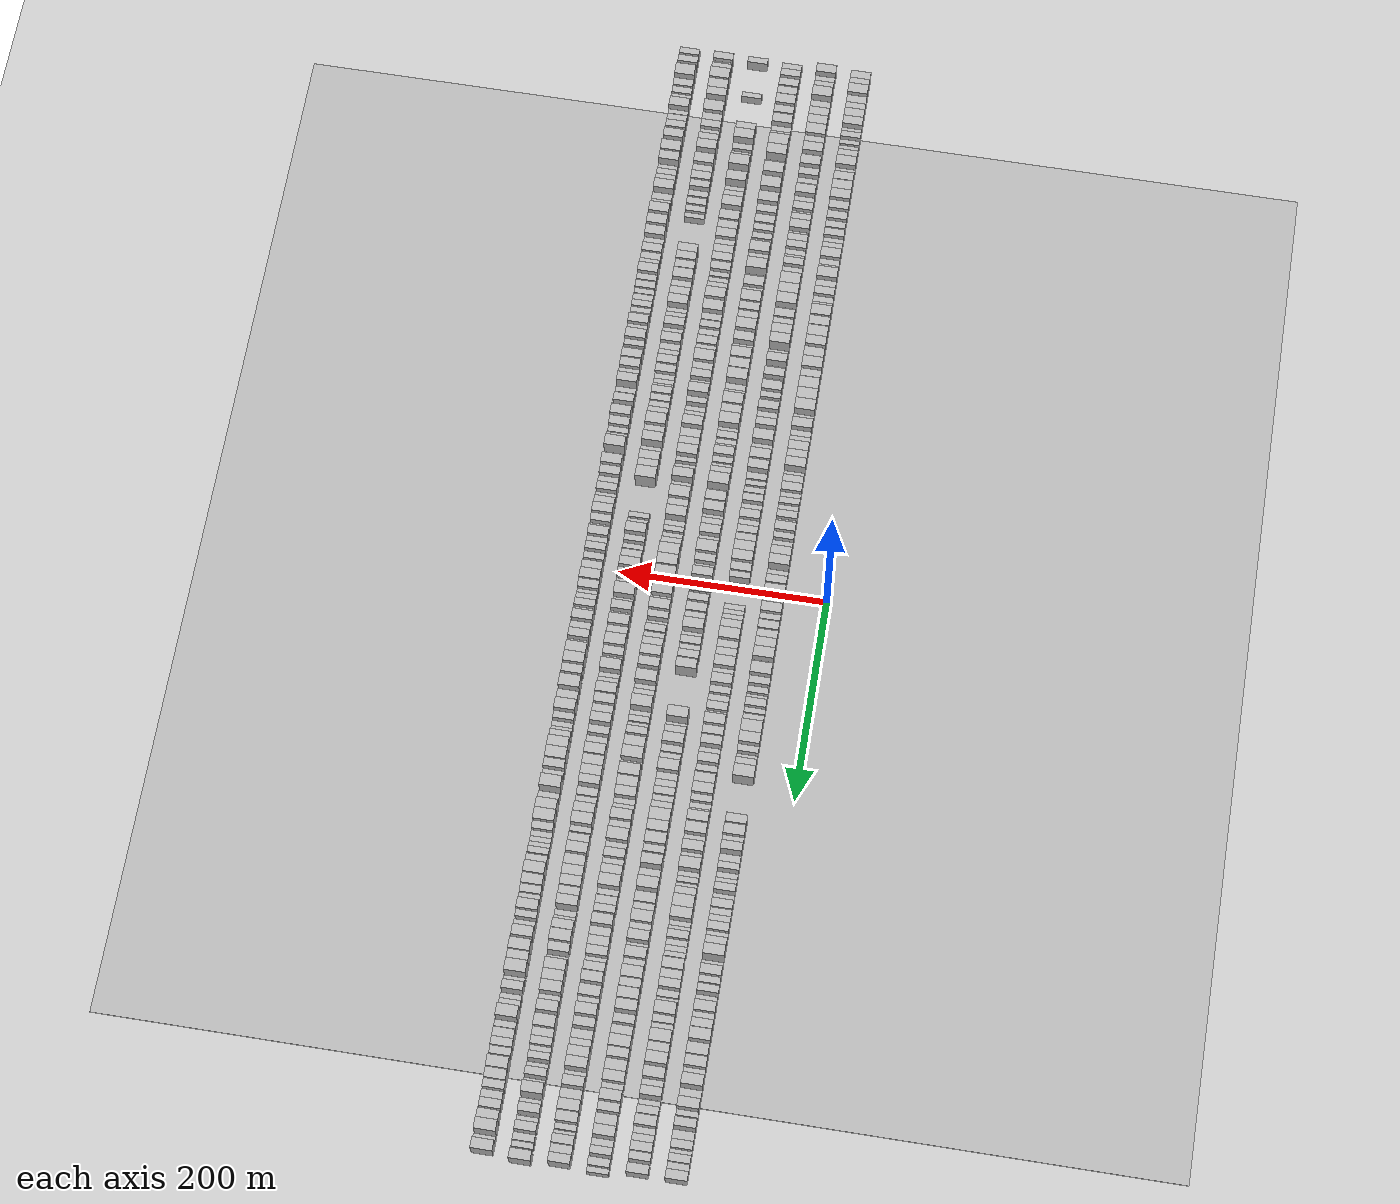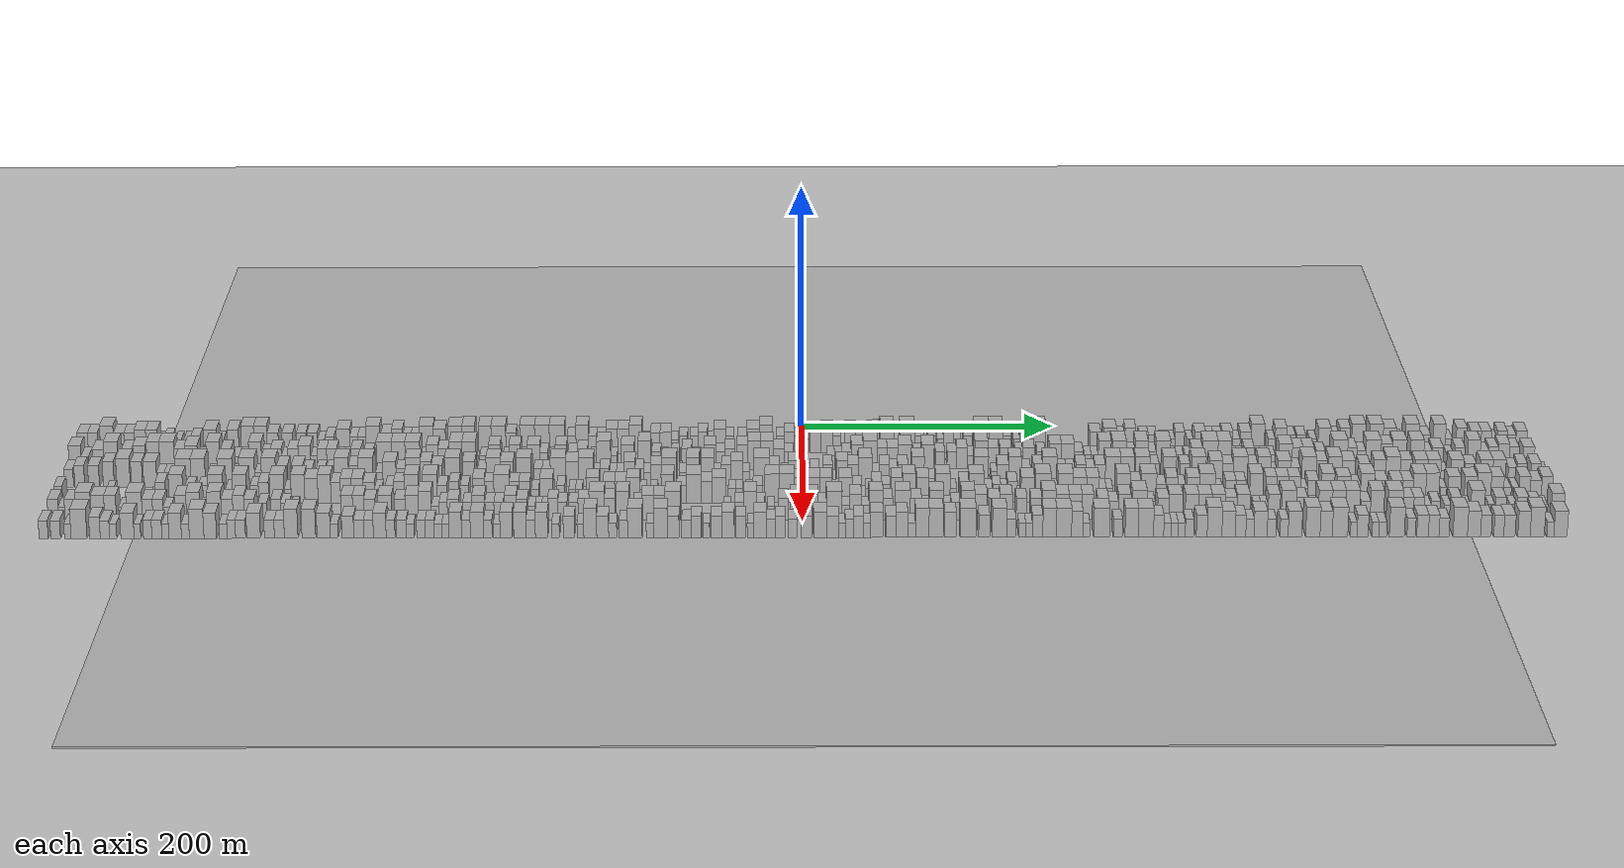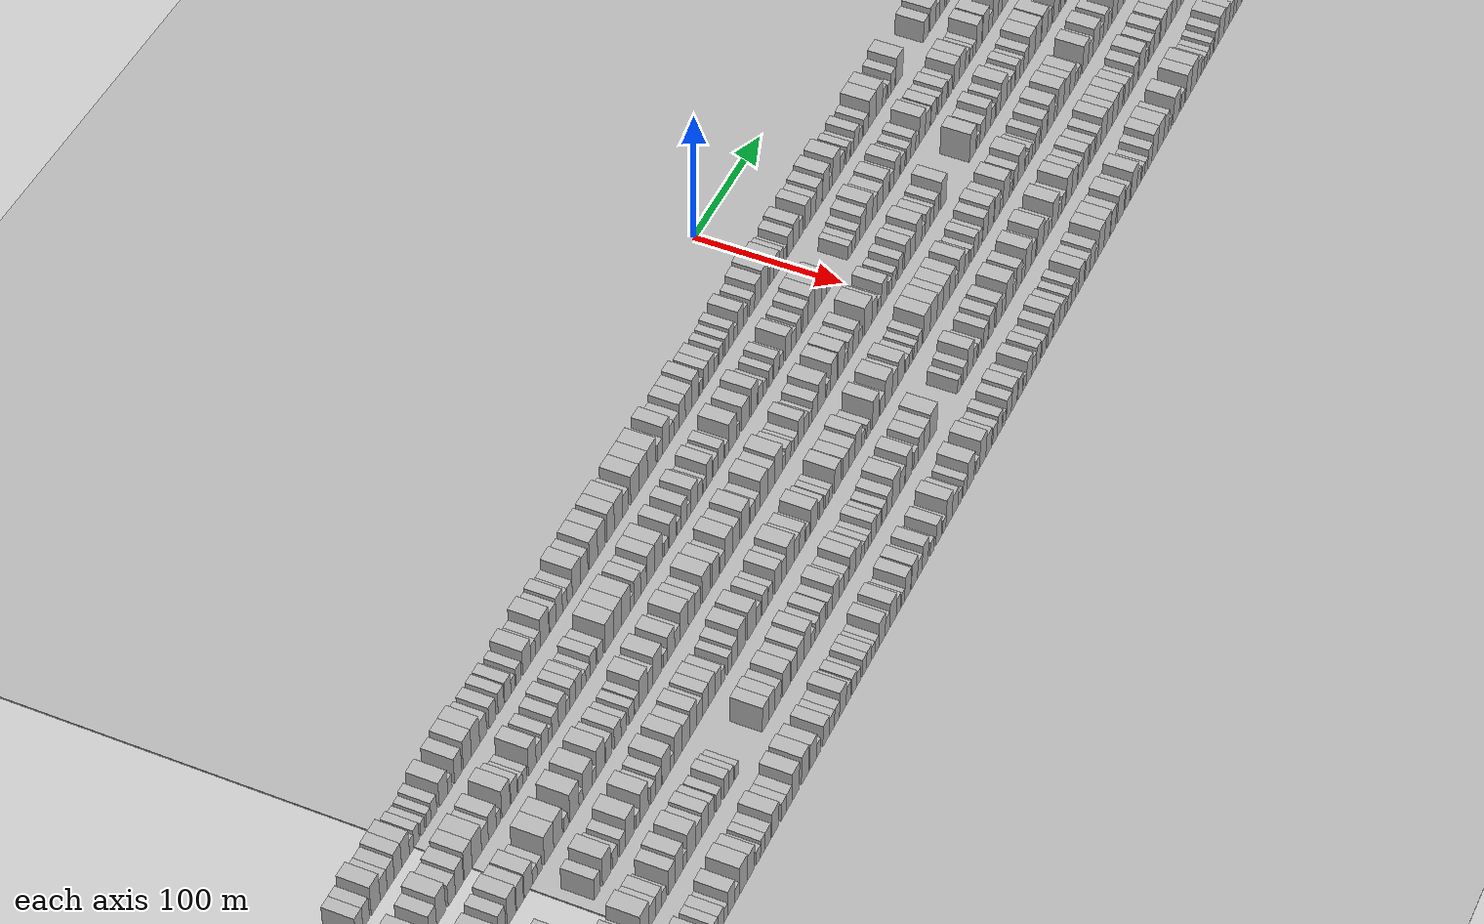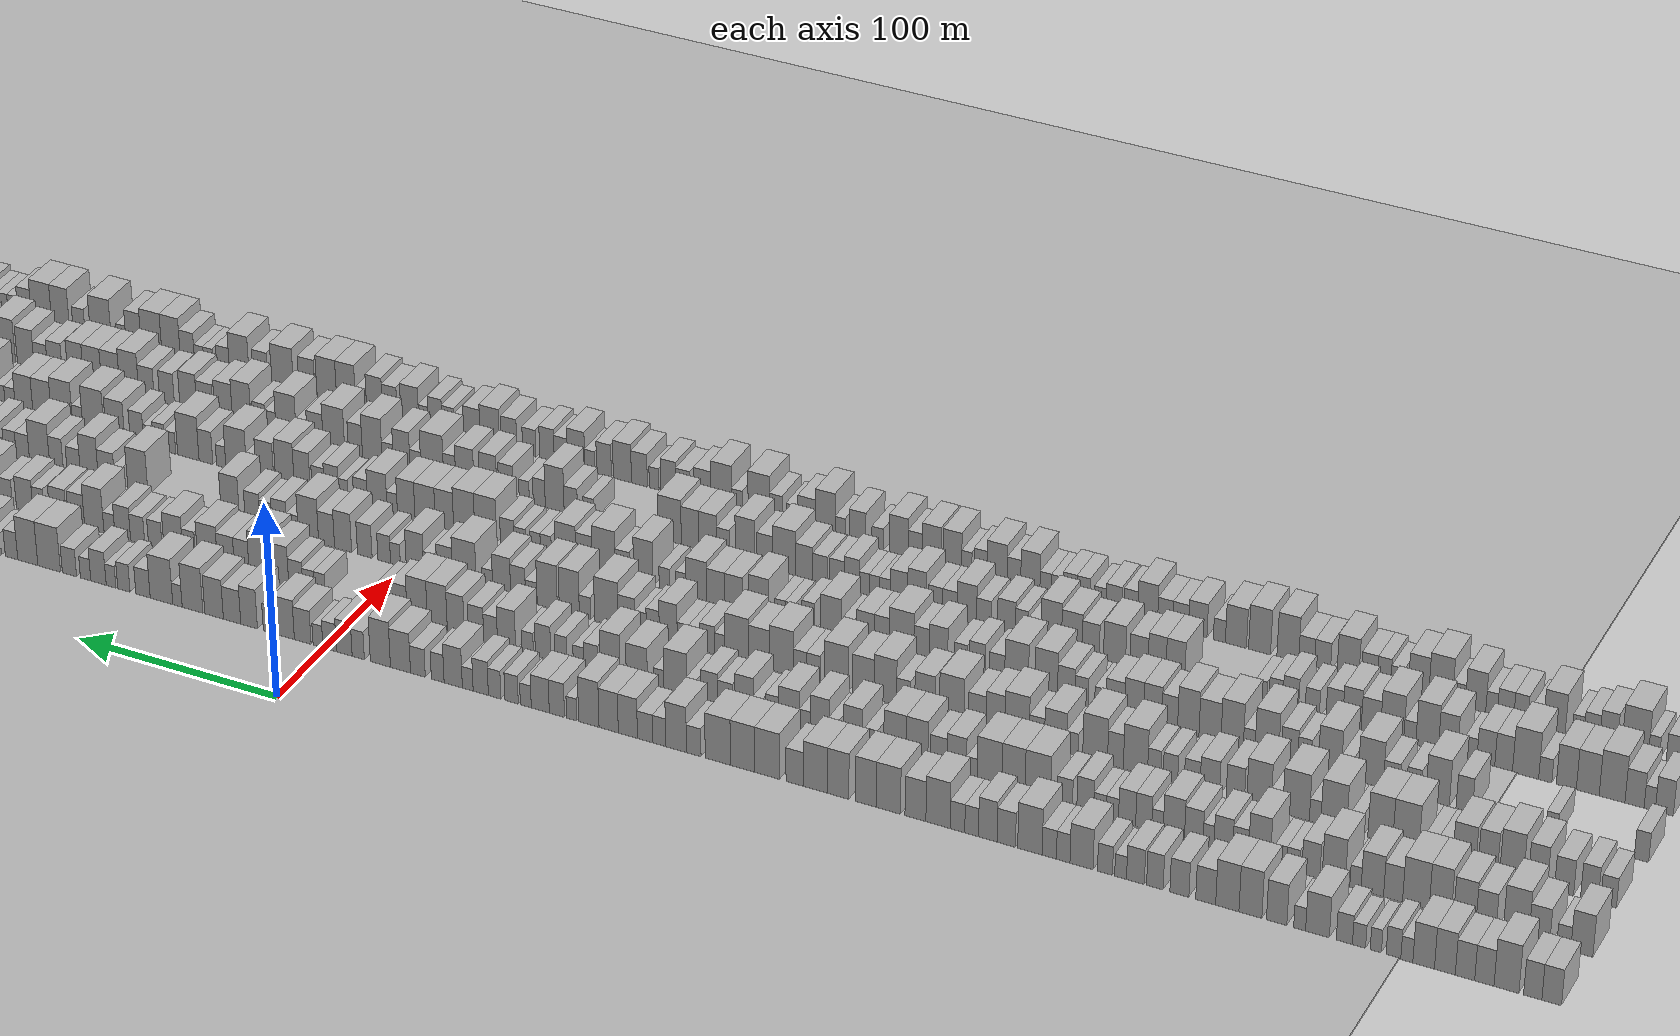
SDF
<?xml version="1.0" encoding="utf-8"?>

<sdf version="1.6">

   <world name="default">

      <gui fullscreen="0">

         <camera name="user_camera">

            <pose>-15 0 4.57585 0 0 0</pose>

            <view_controller>orbit</view_controller>

         </camera>

      </gui>

      <scene>

         <sky>

           <clouds>

             <speed>12</speed>

           </clouds>

         </sky>

         <ambient>0.4 0.4 0.4 1</ambient>

         <background>0.7 0.7 0.7 1</background>

         <shadows>1</shadows>

      </scene>

      <gravity>0 0 -9.8066</gravity>

      <magnetic_field>6e-06 2.3e-05 -4.2e-05</magnetic_field>

      <physics default="0" name="default_physics" type="ode">

         <ode>

            <solver>

               <type>quick</type>

               <iters>10</iters>

               <sor>1.0</sor>

               <use_dynamic_moi_rescaling>0</use_dynamic_moi_rescaling>

            </solver>

            <constraints>

               <cfm>0</cfm>

               <erp>0.2</erp>

               <contact_max_correcting_vel>100</contact_max_correcting_vel>

               <contact_surface_layer>0.001</contact_surface_layer>

            </constraints>

         </ode>

         <max_step_size>0.004</max_step_size>

         <real_time_factor>1</real_time_factor>

         <real_time_update_rate>250</real_time_update_rate>

      </physics>

      <light name="sun" type="directional">

         <cast_shadows>1</cast_shadows>

         <pose>0 0 10 0 0 0</pose>

         <diffuse>0.8 0.8 0.8 1</diffuse>

         <specular>0.2 0.2 0.2 1</specular>

         <attenuation>

            <range>1000</range>

            <constant>0.9</constant>

            <linear>0.01</linear>

            <quadratic>0.001</quadratic>

         </attenuation>

         <direction>-0.5 0.1 -0.9</direction>

      </light>

      <include>

         <name>ground_plane_1</name>

         <uri>model://HANNAS_ground_plane</uri>

         <pose>0 0 0  0 0 0</pose>

      </include>

      <include>

         <name>ground_plane_2</name>

         <uri>model://HANNAS_ground_plane</uri>

         <pose>100 0 0  0 0 0</pose>

      </include>

      <model name="building_1">

         <static>1</static>

         <pose frame="">50.0000 -564.8627 0 0.000000 0.000000 0.000000</pose>

         <link name="link">

            <pose frame="">0 0 9.00 0 0 0</pose>

            <collision name="collision">

               <geometry>

                  <box>

                     <size>20.0000 8.2747 18.0000</size>

                  </box>

               </geometry>

               <max_contacts>10</max_contacts>

               <surface>

                  <contact>

                     <ode/>

                  </contact>

                  <bounce/>

                  <friction>

                     <torsional>

                        <ode/>

                     </torsional>

                     <ode/>

                  </friction>

               </surface>

            </collision>

            <visual name="visual">

               <cast_shadows>0</cast_shadows>

               <geometry>

                  <box>

                     <size>20.0000 8.2747 18.0000</size>

                  </box>

               </geometry>

               <material>

                  <script>

                     <uri>model://HANNAS_wall/materials/scripts</uri>

                     <uri>model://HANNAS_wall/materials/textures</uri>

                     <name>vrc/HANNAS_wall</name>

                  </script>

               </material>

            </visual>

            <self_collide>0</self_collide>

            <enable_wind>0</enable_wind>

            <kinematic>0</kinematic>

         </link>

      </model>

      <model name="building_2">

         <static>1</static>

         <pose frame="">50.0000 -556.8745 0 0.000000 0.000000 0.000000</pose>

         <link name="link">

            <pose frame="">0 0 9.00 0 0 0</pose>

            <collision name="collision">

               <geometry>

                  <box>

                     <size>20.0000 7.7017 18.0000</size>

                  </box>

               </geometry>

               <max_contacts>10</max_contacts>

               <surface>

                  <contact>

                     <ode/>

                  </contact>

                  <bounce/>

                  <friction>

                     <torsional>

                        <ode/>

                     </torsional>

                     <ode/>

                  </friction>

               </surface>

            </collision>

            <visual name="visual">

               <cast_shadows>0</cast_shadows>

               <geometry>

                  <box>

                     <size>20.0000 7.7017 18.0000</size>

                  </box>

               </geometry>

               <material>

                  <script>

                     <uri>model://HANNAS_wall/materials/scripts</uri>

                     <uri>model://HANNAS_wall/materials/textures</uri>

                     <name>vrc/HANNAS_wall</name>

                  </script>

               </material>

            </visual>

            <self_collide>0</self_collide>

            <enable_wind>0</enable_wind>

            <kinematic>0</kinematic>

         </link>

      </model>

      <model name="building_3">

         <static>1</static>

         <pose frame="">50.0000 -545.7599 0 0.000000 0.000000 0.000000</pose>

         <link name="link">

            <pose frame="">0 0 12.00 0 0 0</pose>

            <collision name="collision">

               <geometry>

                  <box>

                     <size>20.0000 10.5275 24.0000</size>

                  </box>

               </geometry>

               <max_contacts>10</max_contacts>

               <surface>

                  <contact>

                     <ode/>

                  </contact>

                  <bounce/>

                  <friction>

                     <torsional>

                        <ode/>

                     </torsional>

                     <ode/>

                  </friction>

               </surface>

            </collision>

            <visual name="visual">

               <cast_shadows>0</cast_shadows>

               <geometry>

                  <box>

                     <size>20.0000 10.5275 24.0000</size>

                  </box>

               </geometry>

               <material>

                  <script>

                     <uri>model://HANNAS_wall/materials/scripts</uri>

                     <uri>model://HANNAS_wall/materials/textures</uri>

                     <name>vrc/HANNAS_wall</name>

                  </script>

               </material>

            </visual>

            <self_collide>0</self_collide>

            <enable_wind>0</enable_wind>

            <kinematic>0</kinematic>

         </link>

      </model>

      <model name="building_4">

         <static>1</static>

         <pose frame="">50.0000 -536.3912 0 0.000000 0.000000 0.000000</pose>

         <link name="link">

            <pose frame="">0 0 9.00 0 0 0</pose>

            <collision name="collision">

               <geometry>

                  <box>

                     <size>20.0000 8.2100 18.0000</size>

                  </box>

               </geometry>

               <max_contacts>10</max_contacts>

               <surface>

                  <contact>

                     <ode/>

                  </contact>

                  <bounce/>

                  <friction>

                     <torsional>

                        <ode/>

                     </torsional>

                     <ode/>

                  </friction>

               </surface>

            </collision>

            <visual name="visual">

               <cast_shadows>0</cast_shadows>

               <geometry>

                  <box>

                     <size>20.0000 8.2100 18.0000</size>

                  </box>

               </geometry>

               <material>

                  <script>

                     <uri>model://HANNAS_wall/materials/scripts</uri>

                     <uri>model://HANNAS_wall/materials/textures</uri>

                     <name>vrc/HANNAS_wall</name>

                  </script>

               </material>

            </visual>

            <self_collide>0</self_collide>

            <enable_wind>0</enable_wind>

            <kinematic>0</kinematic>

         </link>

      </model>

      <model name="building_5">

         <static>1</static>

         <pose frame="">50.0000 -528.1574 0 0.000000 0.000000 0.000000</pose>

         <link name="link">

            <pose frame="">0 0 9.00 0 0 0</pose>

            <collision name="collision">

               <geometry>

                  <box>

                     <size>20.0000 8.2576 18.0000</size>

                  </box>

               </geometry>

               <max_contacts>10</max_contacts>

               <surface>

                  <contact>

                     <ode/>

                  </contact>

                  <bounce/>

                  <friction>

                     <torsional>

                        <ode/>

                     </torsional>

                     <ode/>

                  </friction>

               </surface>

            </collision>

            <visual name="visual">

               <cast_shadows>0</cast_shadows>

               <geometry>

                  <box>

                     <size>20.0000 8.2576 18.0000</size>

                  </box>

               </geometry>

               <material>

                  <script>

                     <uri>model://HANNAS_wall/materials/scripts</uri>

                     <uri>model://HANNAS_wall/materials/textures</uri>

                     <name>vrc/HANNAS_wall</name>

                  </script>

               </material>

            </visual>

            <self_collide>0</self_collide>

            <enable_wind>0</enable_wind>

            <kinematic>0</kinematic>

         </link>

      </model>

      <model name="building_6">

         <static>1</static>

         <pose frame="">50.0000 -519.5687 0 0.000000 0.000000 0.000000</pose>

         <link name="link">

            <pose frame="">0 0 10.50 0 0 0</pose>

            <collision name="collision">

               <geometry>

                  <box>

                     <size>20.0000 8.9199 21.0000</size>

                  </box>

               </geometry>

               <max_contacts>10</max_contacts>

               <surface>

                  <contact>

                     <ode/>

                  </contact>

                  <bounce/>

                  <friction>

                     <torsional>

                        <ode/>

                     </torsional>

                     <ode/>

                  </friction>

               </surface>

            </collision>

            <visual name="visual">

               <cast_shadows>0</cast_shadows>

               <geometry>

                  <box>

                     <size>20.0000 8.9199 21.0000</size>

                  </box>

               </geometry>

               <material>

                  <script>

                     <uri>model://HANNAS_wall/materials/scripts</uri>

                     <uri>model://HANNAS_wall/materials/textures</uri>

                     <name>vrc/HANNAS_wall</name>

                  </script>

               </material>

            </visual>

            <self_collide>0</self_collide>

            <enable_wind>0</enable_wind>

            <kinematic>0</kinematic>

         </link>

      </model>

      <model name="building_7">

         <static>1</static>

         <pose frame="">50.0000 -510.4718 0 0.000000 0.000000 0.000000</pose>

         <link name="link">

            <pose frame="">0 0 10.50 0 0 0</pose>

            <collision name="collision">

               <geometry>

                  <box>

                     <size>20.0000 9.2739 21.0000</size>

                  </box>

               </geometry>

               <max_contacts>10</max_contacts>

               <surface>

                  <contact>

                     <ode/>

                  </contact>

                  <bounce/>

                  <friction>

                     <torsional>

                        <ode/>

                     </torsional>

                     <ode/>

                  </friction>

               </surface>

            </collision>

            <visual name="visual">

               <cast_shadows>0</cast_shadows>

               <geometry>

                  <box>

                     <size>20.0000 9.2739 21.0000</size>

                  </box>

               </geometry>

               <material>

                  <script>

                     <uri>model://HANNAS_wall/materials/scripts</uri>

                     <uri>model://HANNAS_wall/materials/textures</uri>

                     <name>vrc/HANNAS_wall</name>

                  </script>

               </material>

            </visual>

            <self_collide>0</self_collide>

            <enable_wind>0</enable_wind>

            <kinematic>0</kinematic>

         </link>

      </model>

      <model name="building_8">

         <static>1</static>

         <pose frame="">50.0000 -503.2630 0 0.000000 0.000000 0.000000</pose>

         <link name="link">

            <pose frame="">0 0 6.00 0 0 0</pose>

            <collision name="collision">

               <geometry>

                  <box>

                     <size>20.0000 5.1437 12.0000</size>

                  </box>

               </geometry>

               <max_contacts>10</max_contacts>

               <surface>

                  <contact>

                     <ode/>

                  </contact>

                  <bounce/>

                  <friction>

                     <torsional>

                        <ode/>

                     </torsional>

                     <ode/>

                  </friction>

               </surface>

            </collision>

            <visual name="visual">

               <cast_shadows>0</cast_shadows>

               <geometry>

                  <box>

                     <size>20.0000 5.1437 12.0000</size>

                  </box>

               </geometry>

               <material>

                  <script>

                     <uri>model://HANNAS_wall/materials/scripts</uri>

                     <uri>model://HANNAS_wall/materials/textures</uri>

                     <name>vrc/HANNAS_wall</name>

                  </script>

               </material>

            </visual>

            <self_collide>0</self_collide>

            <enable_wind>0</enable_wind>

            <kinematic>0</kinematic>

         </link>

      </model>

      <model name="building_9">

         <static>1</static>

         <pose frame="">50.0000 -497.5153 0 0.000000 0.000000 0.000000</pose>

         <link name="link">

            <pose frame="">0 0 7.50 0 0 0</pose>

            <collision name="collision">

               <geometry>

                  <box>

                     <size>20.0000 6.3517 15.0000</size>

                  </box>

               </geometry>

               <max_contacts>10</max_contacts>

               <surface>

                  <contact>

                     <ode/>

                  </contact>

                  <bounce/>

                  <friction>

                     <torsional>

                        <ode/>

                     </torsional>

                     <ode/>

                  </friction>

               </surface>

            </collision>

            <visual name="visual">

               <cast_shadows>0</cast_shadows>

               <geometry>

                  <box>

                     <size>20.0000 6.3517 15.0000</size>

                  </box>

               </geometry>

               <material>

                  <script>

                     <uri>model://HANNAS_wall/materials/scripts</uri>

                     <uri>model://HANNAS_wall/materials/textures</uri>

                     <name>vrc/HANNAS_wall</name>

                  </script>

               </material>

            </visual>

            <self_collide>0</self_collide>

            <enable_wind>0</enable_wind>

            <kinematic>0</kinematic>

         </link>

      </model>

      <model name="building_10">

         <static>1</static>

         <pose frame="">50.0000 -489.9165 0 0.000000 0.000000 0.000000</pose>

         <link name="link">

            <pose frame="">0 0 6.00 0 0 0</pose>

            <collision name="collision">

               <geometry>

                  <box>

                     <size>20.0000 4.8460 12.0000</size>

                  </box>

               </geometry>

               <max_contacts>10</max_contacts>

               <surface>

                  <contact>

                     <ode/>

                  </contact>

                  <bounce/>

                  <friction>

                     <torsional>

                        <ode/>

                     </torsional>

                     <ode/>

                  </friction>

               </surface>

            </collision>

            <visual name="visual">

               <cast_shadows>0</cast_shadows>

               <geometry>

                  <box>

                     <size>20.0000 4.8460 12.0000</size>

                  </box>

               </geometry>

               <material>

                  <script>

                     <uri>model://HANNAS_wall/materials/scripts</uri>

                     <uri>model://HANNAS_wall/materials/textures</uri>

                     <name>vrc/HANNAS_wall</name>

                  </script>

               </material>

            </visual>

            <self_collide>0</self_collide>

            <enable_wind>0</enable_wind>

            <kinematic>0</kinematic>

         </link>

      </model>

      <model name="building_11">

         <static>1</static>

         <pose frame="">50.0000 -482.6522 0 0.000000 0.000000 0.000000</pose>

         <link name="link">

            <pose frame="">0 0 6.00 0 0 0</pose>

            <collision name="collision">

               <geometry>

                  <box>

                     <size>20.0000 5.6825 12.0000</size>

                  </box>

               </geometry>

               <max_contacts>10</max_contacts>

               <surface>

                  <contact>

                     <ode/>

                  </contact>

                  <bounce/>

                  <friction>

                     <torsional>

                        <ode/>

                     </torsional>

                     <ode/>

                  </friction>

               </surface>

            </collision>

            <visual name="visual">

               <cast_shadows>0</cast_shadows>

               <geometry>

                  <box>

                     <size>20.0000 5.6825 12.0000</size>

                  </box>

               </geometry>

               <material>

                  <script>

                     <uri>model://HANNAS_wall/materials/scripts</uri>

                     <uri>model://HANNAS_wall/materials/textures</uri>

                     <name>vrc/HANNAS_wall</name>

                  </script>

               </material>

            </visual>

            <self_collide>0</self_collide>

            <enable_wind>0</enable_wind>

            <kinematic>0</kinematic>

         </link>

      </model>

      <model name="building_12">

         <static>1</static>

         <pose frame="">50.0000 -476.3167 0 0.000000 0.000000 0.000000</pose>

         <link name="link">

            <pose frame="">0 0 7.50 0 0 0</pose>

            <collision name="collision">

               <geometry>

                  <box>

                     <size>20.0000 6.9886 15.0000</size>

                  </box>

               </geometry>

               <max_contacts>10</max_contacts>

               <surface>

                  <contact>

                     <ode/>

                  </contact>

                  <bounce/>

                  <friction>

                     <torsional>

                        <ode/>

                     </torsional>

                     <ode/>

                  </friction>

               </surface>

            </collision>

            <visual name="visual">

               <cast_shadows>0</cast_shadows>

               <geometry>

                  <box>

                     <size>20.0000 6.9886 15.0000</size>

                  </box>

               </geometry>

               <material>

                  <script>

                     <uri>model://HANNAS_wall/materials/scripts</uri>

                     <uri>model://HANNAS_wall/materials/textures</uri>

                     <name>vrc/HANNAS_wall</name>

                  </script>

               </material>

            </visual>

            <self_collide>0</self_collide>

            <enable_wind>0</enable_wind>

            <kinematic>0</kinematic>

         </link>

      </model>

      <model name="building_13">

         <static>1</static>

         <pose frame="">50.0000 -464.6438 0 0.000000 0.000000 0.000000</pose>

         <link name="link">

            <pose frame="">0 0 10.50 0 0 0</pose>

            <collision name="collision">

               <geometry>

                  <box>

                     <size>20.0000 10.3572 21.0000</size>

                  </box>

               </geometry>

               <max_contacts>10</max_contacts>

               <surface>

                  <contact>

                     <ode/>

                  </contact>

                  <bounce/>

                  <friction>

                     <torsional>

                        <ode/>

                     </torsional>

                     <ode/>

                  </friction>

               </surface>

            </collision>

            <visual name="visual">

               <cast_shadows>0</cast_shadows>

               <geometry>

                  <box>

                     <size>20.0000 10.3572 21.0000</size>

                  </box>

               </geometry>

               <material>

                  <script>

                     <uri>model://HANNAS_wall/materials/scripts</uri>

                     <uri>model://HANNAS_wall/materials/textures</uri>

                     <name>vrc/HANNAS_wall</name>

                  </script>

               </material>

            </visual>

            <self_collide>0</self_collide>

            <enable_wind>0</enable_wind>

            <kinematic>0</kinematic>

         </link>

      </model>

      <model name="building_14">

         <static>1</static>

         <pose frame="">50.0000 -456.8778 0 0.000000 0.000000 0.000000</pose>

         <link name="link">

            <pose frame="">0 0 6.00 0 0 0</pose>

            <collision name="collision">

               <geometry>

                  <box>

                     <size>20.0000 5.1750 12.0000</size>

                  </box>

               </geometry>

               <max_contacts>10</max_contacts>

               <surface>

                  <contact>

                     <ode/>

                  </contact>

                  <bounce/>

                  <friction>

                     <torsional>

                        <ode/>

                     </torsional>

                     <ode/>

                  </friction>

               </surface>

            </collision>

            <visual name="visual">

               <cast_shadows>0</cast_shadows>

               <geometry>

                  <box>

                     <size>20.0000 5.1750 12.0000</size>

                  </box>

               </geometry>

               <material>

                  <script>

                     <uri>model://HANNAS_wall/materials/scripts</uri>

                     <uri>model://HANNAS_wall/materials/textures</uri>

                     <name>vrc/HANNAS_wall</name>

                  </script>

               </material>

            </visual>

            <self_collide>0</self_collide>

            <enable_wind>0</enable_wind>

            <kinematic>0</kinematic>

         </link>

      </model>

      <model name="building_15">

         <static>1</static>

         <pose frame="">50.0000 -446.8325 0 0.000000 0.000000 0.000000</pose>

         <link name="link">

            <pose frame="">0 0 10.50 0 0 0</pose>

            <collision name="collision">

               <geometry>

                  <box>

                     <size>20.0000 8.9155 21.0000</size>

                  </box>

               </geometry>

               <max_contacts>10</max_contacts>

               <surface>

                  <contact>

                     <ode/>

                  </contact>

                  <bounce/>

                  <friction>

                     <torsional>

                        <ode/>

                     </torsional>

                     <ode/>

                  </friction>

               </surface>

            </collision>

            <visual name="visual">

               <cast_shadows>0</cast_shadows>

               <geometry>

                  <box>

                     <size>20.0000 8.9155 21.0000</size>

                  </box>

               </geometry>

               <material>

                  <script>

                     <uri>model://HANNAS_wall/materials/scripts</uri>

                     <uri>model://HANNAS_wall/materials/textures</uri>

                     <name>vrc/HANNAS_wall</name>

                  </script>

               </material>

            </visual>

            <self_collide>0</self_collide>

            <enable_wind>0</enable_wind>

            <kinematic>0</kinematic>

         </link>

      </model>

      <model name="building_16">

         <static>1</static>

         <pose frame="">50.0000 -435.3400 0 0.000000 0.000000 0.000000</pose>

         <link name="link">

            <pose frame="">0 0 12.00 0 0 0</pose>

            <collision name="collision">

               <geometry>

                  <box>

                     <size>20.0000 10.0695 24.0000</size>

                  </box>

               </geometry>

               <max_contacts>10</max_contacts>

               <surface>

                  <contact>

                     <ode/>

                  </contact>

                  <bounce/>

                  <friction>

                     <torsional>

                        <ode/>

                     </torsional>

                     <ode/>

                  </friction>

               </surface>

            </collision>

            <visual name="visual">

               <cast_shadows>0</cast_shadows>

               <geometry>

                  <box>

                     <size>20.0000 10.0695 24.0000</size>

                  </box>

               </geometry>

               <material>

                  <script>

                     <uri>model://HANNAS_wall/materials/scripts</uri>

                     <uri>model://HANNAS_wall/materials/textures</uri>

                     <name>vrc/HANNAS_wall</name>

                  </script>

               </material>

            </visual>

            <self_collide>0</self_collide>

            <enable_wind>0</enable_wind>

            <kinematic>0</kinematic>

         </link>

      </model>

      <model name="building_17">

         <static>1</static>

         <pose frame="">50.0000 -425.1786 0 0.000000 0.000000 0.000000</pose>

         <link name="link">

            <pose frame="">0 0 12.00 0 0 0</pose>

            <collision name="collision">

               <geometry>

                  <box>

                     <size>20.0000 10.2533 24.0000</size>

                  </box>

               </geometry>

               <max_contacts>10</max_contacts>

               <surface>

                  <contact>

                     <ode/>

                  </contact>

                  <bounce/>

                  <friction>

                     <torsional>

                        <ode/>

                     </torsional>

                     <ode/>

                  </friction>

               </surface>

            </collision>

            <visual name="visual">

               <cast_shadows>0</cast_shadows>

               <geometry>

                  <box>

                     <size>20.0000 10.2533 24.0000</size>

                  </box>

               </geometry>

               <material>

                  <script>

                     <uri>model://HANNAS_wall/materials/scripts</uri>

                     <uri>model://HANNAS_wall/materials/textures</uri>

                     <name>vrc/HANNAS_wall</name>

                  </script>

               </material>

            </visual>

            <self_collide>0</self_collide>

            <enable_wind>0</enable_wind>

            <kinematic>0</kinematic>

         </link>

      </model>

      <model name="building_18">

         <static>1</static>

         <pose frame="">50.0000 -415.6454 0 0.000000 0.000000 0.000000</pose>

         <link name="link">

            <pose frame="">0 0 9.00 0 0 0</pose>

            <collision name="collision">

               <geometry>

                  <box>

                     <size>20.0000 8.8131 18.0000</size>

                  </box>

               </geometry>

               <max_contacts>10</max_contacts>

               <surface>

                  <contact>

                     <ode/>

                  </contact>

                  <bounce/>

                  <friction>

                     <torsional>

                        <ode/>

                     </torsional>

                     <ode/>

                  </friction>

               </surface>

            </collision>

            <visual name="visual">

               <cast_shadows>0</cast_shadows>

               <geometry>

                  <box>

                     <size>20.0000 8.8131 18.0000</size>

                  </box>

               </geometry>

               <material>

                  <script>

                     <uri>model://HANNAS_wall/materials/scripts</uri>

                     <uri>model://HANNAS_wall/materials/textures</uri>

                     <name>vrc/HANNAS_wall</name>

                  </script>

               </material>

            </visual>

            <self_collide>0</self_collide>

            <enable_wind>0</enable_wind>

            <kinematic>0</kinematic>

         </link>

      </model>

      <model name="building_19">

         <static>1</static>

         <pose frame="">50.0000 -404.0162 0 0.000000 0.000000 0.000000</pose>

         <link name="link">

            <pose frame="">0 0 9.00 0 0 0</pose>

            <collision name="collision">

               <geometry>

                  <box>

                     <size>20.0000 8.4453 18.0000</size>

                  </box>

               </geometry>

               <max_contacts>10</max_contacts>

               <surface>

                  <contact>

                     <ode/>

                  </contact>

                  <bounce/>

                  <friction>

                     <torsional>

                        <ode/>

                     </torsional>

                     <ode/>

                  </friction>

               </surface>

            </collision>

            <visual name="visual">

               <cast_shadows>0</cast_shadows>

               <geometry>

                  <box>

                     <size>20.0000 8.4453 18.0000</size>

                  </box>

               </geometry>

               <material>

                  <script>

                     <uri>model://HANNAS_wall/materials/scripts</uri>

                     <uri>model://HANNAS_wall/materials/textures</uri>

                     <name>vrc/HANNAS_wall</name>

                  </script>

               </material>

            </visual>

            <self_collide>0</self_collide>

            <enable_wind>0</enable_wind>

            <kinematic>0</kinematic>

         </link>

      </model>

      <model name="building_20">

         <static>1</static>

         <pose frame="">50.0000 -393.1114 0 0.000000 0.000000 0.000000</pose>

         <link name="link">

            <pose frame="">0 0 9.00 0 0 0</pose>

            <collision name="collision">

               <geometry>

                  <box>

                     <size>20.0000 7.3643 18.0000</size>

                  </box>

               </geometry>

               <max_contacts>10</max_contacts>

               <surface>

                  <contact>

                     <ode/>

                  </contact>

                  <bounce/>

                  <friction>

                     <torsional>

                        <ode/>

                     </torsional>

                     <ode/>

                  </friction>

               </surface>

            </collision>

            <visual name="visual">

               <cast_shadows>0</cast_shadows>

               <geometry>

                  <box>

                     <size>20.0000 7.3643 18.0000</size>

                  </box>

               </geometry>

               <material>

                  <script>

                     <uri>model://HANNAS_wall/materials/scripts</uri>

                     <uri>model://HANNAS_wall/materials/textures</uri>

                     <name>vrc/HANNAS_wall</name>

                  </script>

               </material>

            </visual>

            <self_collide>0</self_collide>

            <enable_wind>0</enable_wind>

            <kinematic>0</kinematic>

         </link>

      </model>

      <model name="building_21">

         <static>1</static>

         <pose frame="">50.0000 -384.4585 0 0.000000 0.000000 0.000000</pose>

         <link name="link">

            <pose frame="">0 0 9.00 0 0 0</pose>

            <collision name="collision">

               <geometry>

                  <box>

                     <size>20.0000 7.9415 18.0000</size>

                  </box>

               </geometry>

               <max_contacts>10</max_contacts>

               <surface>

                  <contact>

                     <ode/>

                  </contact>

                  <bounce/>

                  <friction>

                     <torsional>

                        <ode/>

                     </torsional>

                     <ode/>

                  </friction>

               </surface>

            </collision>

            <visual name="visual">

               <cast_shadows>0</cast_shadows>

               <geometry>

                  <box>

                     <size>20.0000 7.9415 18.0000</size>

                  </box>

               </geometry>

               <material>

                  <script>

                     <uri>model://HANNAS_wall/materials/scripts</uri>

                     <uri>model://HANNAS_wall/materials/textures</uri>

                     <name>vrc/HANNAS_wall</name>

                  </script>

               </material>

            </visual>

            <self_collide>0</self_collide>

            <enable_wind>0</enable_wind>

            <kinematic>0</kinematic>

         </link>

      </model>

      <model name="building_22">

         <static>1</static>

         <pose frame="">50.0000 -377.8340 0 0.000000 0.000000 0.000000</pose>

         <link name="link">

            <pose frame="">0 0 6.00 0 0 0</pose>

            <collision name="collision">

               <geometry>

                  <box>

                     <size>20.0000 5.3076 12.0000</size>

                  </box>

               </geometry>

               <max_contacts>10</max_contacts>

               <surface>

                  <contact>

                     <ode/>

                  </contact>

                  <bounce/>

                  <friction>

                     <torsional>

                        <ode/>

                     </torsional>

                     <ode/>

                  </friction>

               </surface>

            </collision>

            <visual name="visual">

               <cast_shadows>0</cast_shadows>

               <geometry>

                  <box>

                     <size>20.0000 5.3076 12.0000</size>

                  </box>

               </geometry>

               <material>

                  <script>

                     <uri>model://HANNAS_wall/materials/scripts</uri>

                     <uri>model://HANNAS_wall/materials/textures</uri>

                     <name>vrc/HANNAS_wall</name>

                  </script>

               </material>

            </visual>

            <self_collide>0</self_collide>

            <enable_wind>0</enable_wind>

            <kinematic>0</kinematic>

         </link>

      </model>

      <model name="building_23">

         <static>1</static>

         <pose frame="">50.0000 -370.8288 0 0.000000 0.000000 0.000000</pose>

         <link name="link">

            <pose frame="">0 0 7.50 0 0 0</pose>

            <collision name="collision">

               <geometry>

                  <box>

                     <size>20.0000 6.7027 15.0000</size>

                  </box>

               </geometry>

               <max_contacts>10</max_contacts>

               <surface>

                  <contact>

                     <ode/>

                  </contact>

                  <bounce/>

                  <friction>

                     <torsional>

                        <ode/>

                     </torsional>

                     <ode/>

                  </friction>

               </surface>

            </collision>

            <visual name="visual">

               <cast_shadows>0</cast_shadows>

               <geometry>

                  <box>

                     <size>20.0000 6.7027 15.0000</size>

                  </box>

               </geometry>

               <material>

                  <script>

                     <uri>model://HANNAS_wall/materials/scripts</uri>

                     <uri>model://HANNAS_wall/materials/textures</uri>

                     <name>vrc/HANNAS_wall</name>

                  </script>

               </material>

            </visual>

            <self_collide>0</self_collide>

            <enable_wind>0</enable_wind>

            <kinematic>0</kinematic>

         </link>

      </model>

      <model name="building_24">

         <static>1</static>

         <pose frame="">50.0000 -360.2942 0 0.000000 0.000000 0.000000</pose>

         <link name="link">

            <pose frame="">0 0 10.50 0 0 0</pose>

            <collision name="collision">

               <geometry>

                  <box>

                     <size>20.0000 10.3666 21.0000</size>

                  </box>

               </geometry>

               <max_contacts>10</max_contacts>

               <surface>

                  <contact>

                     <ode/>

                  </contact>

                  <bounce/>

                  <friction>

                     <torsional>

                        <ode/>

                     </torsional>

                     <ode/>

                  </friction>

               </surface>

            </collision>

            <visual name="visual">

               <cast_shadows>0</cast_shadows>

               <geometry>

                  <box>

                     <size>20.0000 10.3666 21.0000</size>

                  </box>

               </geometry>

               <material>

                  <script>

                     <uri>model://HANNAS_wall/materials/scripts</uri>

                     <uri>model://HANNAS_wall/materials/textures</uri>

                     <name>vrc/HANNAS_wall</name>

                  </script>

               </material>

            </visual>

            <self_collide>0</self_collide>

            <enable_wind>0</enable_wind>

            <kinematic>0</kinematic>

         </link>

      </model>

      <model name="building_25">

         <static>1</static>

         <pose frame="">50.0000 -352.0526 0 0.000000 0.000000 0.000000</pose>

         <link name="link">

            <pose frame="">0 0 7.50 0 0 0</pose>

            <collision name="collision">

               <geometry>

                  <box>

                     <size>20.0000 6.1165 15.0000</size>

                  </box>

               </geometry>

               <max_contacts>10</max_contacts>

               <surface>

                  <contact>

                     <ode/>

                  </contact>

                  <bounce/>

                  <friction>

                     <torsional>

                        <ode/>

                     </torsional>

                     <ode/>

                  </friction>

               </surface>

            </collision>

            <visual name="visual">

               <cast_shadows>0</cast_shadows>

               <geometry>

                  <box>

                     <size>20.0000 6.1165 15.0000</size>

                  </box>

               </geometry>

               <material>

                  <script>

                     <uri>model://HANNAS_wall/materials/scripts</uri>

                     <uri>model://HANNAS_wall/materials/textures</uri>

                     <name>vrc/HANNAS_wall</name>

                  </script>

               </material>

            </visual>

            <self_collide>0</self_collide>

            <enable_wind>0</enable_wind>

            <kinematic>0</kinematic>

         </link>

      </model>

      <model name="building_26">

         <static>1</static>

         <pose frame="">50.0000 -345.7716 0 0.000000 0.000000 0.000000</pose>

         <link name="link">

            <pose frame="">0 0 7.50 0 0 0</pose>

            <collision name="collision">

               <geometry>

                  <box>

                     <size>20.0000 6.4454 15.0000</size>

                  </box>

               </geometry>

               <max_contacts>10</max_contacts>

               <surface>

                  <contact>

                     <ode/>

                  </contact>

                  <bounce/>

                  <friction>

                     <torsional>

                        <ode/>

                     </torsional>

                     <ode/>

                  </friction>

               </surface>

            </collision>

            <visual name="visual">

               <cast_shadows>0</cast_shadows>

               <geometry>

                  <box>

                     <size>20.0000 6.4454 15.0000</size>

                  </box>

               </geometry>

               <material>

                  <script>

                     <uri>model://HANNAS_wall/materials/scripts</uri>

                     <uri>model://HANNAS_wall/materials/textures</uri>

                     <name>vrc/HANNAS_wall</name>

                  </script>

               </material>

            </visual>

            <self_collide>0</self_collide>

            <enable_wind>0</enable_wind>

            <kinematic>0</kinematic>

         </link>

      </model>

      <model name="building_27">

         <static>1</static>

         <pose frame="">50.0000 -337.0065 0 0.000000 0.000000 0.000000</pose>

         <link name="link">

            <pose frame="">0 0 12.00 0 0 0</pose>

            <collision name="collision">

               <geometry>

                  <box>

                     <size>20.0000 11.0848 24.0000</size>

                  </box>

               </geometry>

               <max_contacts>10</max_contacts>

               <surface>

                  <contact>

                     <ode/>

                  </contact>

                  <bounce/>

                  <friction>

                     <torsional>

                        <ode/>

                     </torsional>

                     <ode/>

                  </friction>

               </surface>

            </collision>

            <visual name="visual">

               <cast_shadows>0</cast_shadows>

               <geometry>

                  <box>

                     <size>20.0000 11.0848 24.0000</size>

                  </box>

               </geometry>

               <material>

                  <script>

                     <uri>model://HANNAS_wall/materials/scripts</uri>

                     <uri>model://HANNAS_wall/materials/textures</uri>

                     <name>vrc/HANNAS_wall</name>

                  </script>

               </material>

            </visual>

            <self_collide>0</self_collide>

            <enable_wind>0</enable_wind>

            <kinematic>0</kinematic>

         </link>

      </model>

      <model name="building_28">

         <static>1</static>

         <pose frame="">50.0000 -326.2765 0 0.000000 0.000000 0.000000</pose>

         <link name="link">

            <pose frame="">0 0 9.00 0 0 0</pose>

            <collision name="collision">

               <geometry>

                  <box>

                     <size>20.0000 8.3753 18.0000</size>

                  </box>

               </geometry>

               <max_contacts>10</max_contacts>

               <surface>

                  <contact>

                     <ode/>

                  </contact>

                  <bounce/>

                  <friction>

                     <torsional>

                        <ode/>

                     </torsional>

                     <ode/>

                  </friction>

               </surface>

            </collision>

            <visual name="visual">

               <cast_shadows>0</cast_shadows>

               <geometry>

                  <box>

                     <size>20.0000 8.3753 18.0000</size>

                  </box>

               </geometry>

               <material>

                  <script>

                     <uri>model://HANNAS_wall/materials/scripts</uri>

                     <uri>model://HANNAS_wall/materials/textures</uri>

                     <name>vrc/HANNAS_wall</name>

                  </script>

               </material>

            </visual>

            <self_collide>0</self_collide>

            <enable_wind>0</enable_wind>

            <kinematic>0</kinematic>

         </link>

      </model>

      <model name="building_29">

         <static>1</static>

         <pose frame="">50.0000 -317.8572 0 0.000000 0.000000 0.000000</pose>

         <link name="link">

            <pose frame="">0 0 10.50 0 0 0</pose>

            <collision name="collision">

               <geometry>

                  <box>

                     <size>20.0000 8.4634 21.0000</size>

                  </box>

               </geometry>

               <max_contacts>10</max_contacts>

               <surface>

                  <contact>

                     <ode/>

                  </contact>

                  <bounce/>

                  <friction>

                     <torsional>

                        <ode/>

                     </torsional>

                     <ode/>

                  </friction>

               </surface>

            </collision>

            <visual name="visual">

               <cast_shadows>0</cast_shadows>

               <geometry>

                  <box>

                     <size>20.0000 8.4634 21.0000</size>

                  </box>

               </geometry>

               <material>

                  <script>

                     <uri>model://HANNAS_wall/materials/scripts</uri>

                     <uri>model://HANNAS_wall/materials/textures</uri>

                     <name>vrc/HANNAS_wall</name>

                  </script>

               </material>

            </visual>

            <self_collide>0</self_collide>

            <enable_wind>0</enable_wind>

            <kinematic>0</kinematic>

         </link>

      </model>

      <model name="building_30">

         <static>1</static>

         <pose frame="">50.0000 -310.4943 0 0.000000 0.000000 0.000000</pose>

         <link name="link">

            <pose frame="">0 0 7.50 0 0 0</pose>

            <collision name="collision">

               <geometry>

                  <box>

                     <size>20.0000 6.2623 15.0000</size>

                  </box>

               </geometry>

               <max_contacts>10</max_contacts>

               <surface>

                  <contact>

                     <ode/>

                  </contact>

                  <bounce/>

                  <friction>

                     <torsional>

                        <ode/>

                     </torsional>

                     <ode/>

                  </friction>

               </surface>

            </collision>

            <visual name="visual">

               <cast_shadows>0</cast_shadows>

               <geometry>

                  <box>

                     <size>20.0000 6.2623 15.0000</size>

                  </box>

               </geometry>

               <material>

                  <script>

                     <uri>model://HANNAS_wall/materials/scripts</uri>

                     <uri>model://HANNAS_wall/materials/textures</uri>

                     <name>vrc/HANNAS_wall</name>

                  </script>

               </material>

            </visual>

            <self_collide>0</self_collide>

            <enable_wind>0</enable_wind>

            <kinematic>0</kinematic>

         </link>

      </model>

      <model name="building_31">

         <static>1</static>

         <pose frame="">50.0000 -304.0027 0 0.000000 0.000000 0.000000</pose>

         <link name="link">

            <pose frame="">0 0 7.50 0 0 0</pose>

            <collision name="collision">

               <geometry>

                  <box>

                     <size>20.0000 6.7210 15.0000</size>

                  </box>

               </geometry>

               <max_contacts>10</max_contacts>

               <surface>

                  <contact>

                     <ode/>

                  </contact>

                  <bounce/>

                  <friction>

                     <torsional>

                        <ode/>

                     </torsional>

                     <ode/>

                  </friction>

               </surface>

            </collision>

            <visual name="visual">

               <cast_shadows>0</cast_shadows>

               <geometry>

                  <box>

                     <size>20.0000 6.7210 15.0000</size>

                  </box>

               </geometry>

               <material>

                  <script>

                     <uri>model://HANNAS_wall/materials/scripts</uri>

                     <uri>model://HANNAS_wall/materials/textures</uri>

                     <name>vrc/HANNAS_wall</name>

                  </script>

               </material>

            </visual>

            <self_collide>0</self_collide>

            <enable_wind>0</enable_wind>

            <kinematic>0</kinematic>

         </link>

      </model>

      <model name="building_32">

         <static>1</static>

         <pose frame="">50.0000 -295.0902 0 0.000000 0.000000 0.000000</pose>

         <link name="link">

            <pose frame="">0 0 12.00 0 0 0</pose>

            <collision name="collision">

               <geometry>

                  <box>

                     <size>20.0000 11.1041 24.0000</size>

                  </box>

               </geometry>

               <max_contacts>10</max_contacts>

               <surface>

                  <contact>

                     <ode/>

                  </contact>

                  <bounce/>

                  <friction>

                     <torsional>

                        <ode/>

                     </torsional>

                     <ode/>

                  </friction>

               </surface>

            </collision>

            <visual name="visual">

               <cast_shadows>0</cast_shadows>

               <geometry>

                  <box>

                     <size>20.0000 11.1041 24.0000</size>

                  </box>

               </geometry>

               <material>

                  <script>

                     <uri>model://HANNAS_wall/materials/scripts</uri>

                     <uri>model://HANNAS_wall/materials/textures</uri>

                     <name>vrc/HANNAS_wall</name>

                  </script>

               </material>

            </visual>

            <self_collide>0</self_collide>

            <enable_wind>0</enable_wind>

            <kinematic>0</kinematic>

         </link>

      </model>

      <model name="building_33">

         <static>1</static>

         <pose frame="">50.0000 -284.7177 0 0.000000 0.000000 0.000000</pose>

         <link name="link">

            <pose frame="">0 0 10.50 0 0 0</pose>

            <collision name="collision">

               <geometry>

                  <box>

                     <size>20.0000 9.6409 21.0000</size>

                  </box>

               </geometry>

               <max_contacts>10</max_contacts>

               <surface>

                  <contact>

                     <ode/>

                  </contact>

                  <bounce/>

                  <friction>

                     <torsional>

                        <ode/>

                     </torsional>

                     <ode/>

                  </friction>

               </surface>

            </collision>

            <visual name="visual">

               <cast_shadows>0</cast_shadows>

               <geometry>

                  <box>

                     <size>20.0000 9.6409 21.0000</size>

                  </box>

               </geometry>

               <material>

                  <script>

                     <uri>model://HANNAS_wall/materials/scripts</uri>

                     <uri>model://HANNAS_wall/materials/textures</uri>

                     <name>vrc/HANNAS_wall</name>

                  </script>

               </material>

            </visual>

            <self_collide>0</self_collide>

            <enable_wind>0</enable_wind>

            <kinematic>0</kinematic>

         </link>

      </model>

      <model name="building_34">

         <static>1</static>

         <pose frame="">50.0000 -272.3143 0 0.000000 0.000000 0.000000</pose>

         <link name="link">

            <pose frame="">0 0 12.00 0 0 0</pose>

            <collision name="collision">

               <geometry>

                  <box>

                     <size>20.0000 11.1660 24.0000</size>

                  </box>

               </geometry>

               <max_contacts>10</max_contacts>

               <surface>

                  <contact>

                     <ode/>

                  </contact>

                  <bounce/>

                  <friction>

                     <torsional>

                        <ode/>

                     </torsional>

                     <ode/>

                  </friction>

               </surface>

            </collision>

            <visual name="visual">

               <cast_shadows>0</cast_shadows>

               <geometry>

                  <box>

                     <size>20.0000 11.1660 24.0000</size>

                  </box>

               </geometry>

               <material>

                  <script>

                     <uri>model://HANNAS_wall/materials/scripts</uri>

                     <uri>model://HANNAS_wall/materials/textures</uri>

                     <name>vrc/HANNAS_wall</name>

                  </script>

               </material>

            </visual>

            <self_collide>0</self_collide>

            <enable_wind>0</enable_wind>

            <kinematic>0</kinematic>

         </link>

      </model>

      <model name="building_35">

         <static>1</static>

         <pose frame="">50.0000 -261.8260 0 0.000000 0.000000 0.000000</pose>

         <link name="link">

            <pose frame="">0 0 12.00 0 0 0</pose>

            <collision name="collision">

               <geometry>

                  <box>

                     <size>20.0000 9.8106 24.0000</size>

                  </box>

               </geometry>

               <max_contacts>10</max_contacts>

               <surface>

                  <contact>

                     <ode/>

                  </contact>

                  <bounce/>

                  <friction>

                     <torsional>

                        <ode/>

                     </torsional>

                     <ode/>

                  </friction>

               </surface>

            </collision>

            <visual name="visual">

               <cast_shadows>0</cast_shadows>

               <geometry>

                  <box>

                     <size>20.0000 9.8106 24.0000</size>

                  </box>

               </geometry>

               <material>

                  <script>

                     <uri>model://HANNAS_wall/materials/scripts</uri>

                     <uri>model://HANNAS_wall/materials/textures</uri>

                     <name>vrc/HANNAS_wall</name>

                  </script>

               </material>

            </visual>

            <self_collide>0</self_collide>

            <enable_wind>0</enable_wind>

            <kinematic>0</kinematic>

         </link>

      </model>

      <model name="building_36">

         <static>1</static>

         <pose frame="">50.0000 -248.9890 0 0.000000 0.000000 0.000000</pose>

         <link name="link">

            <pose frame="">0 0 12.00 0 0 0</pose>

            <collision name="collision">

               <geometry>

                  <box>

                     <size>20.0000 9.8634 24.0000</size>

                  </box>

               </geometry>

               <max_contacts>10</max_contacts>

               <surface>

                  <contact>

                     <ode/>

                  </contact>

                  <bounce/>

                  <friction>

                     <torsional>

                        <ode/>

                     </torsional>

                     <ode/>

                  </friction>

               </surface>

            </collision>

            <visual name="visual">

               <cast_shadows>0</cast_shadows>

               <geometry>

                  <box>

                     <size>20.0000 9.8634 24.0000</size>

                  </box>

               </geometry>

               <material>

                  <script>

                     <uri>model://HANNAS_wall/materials/scripts</uri>

                     <uri>model://HANNAS_wall/materials/textures</uri>

                     <name>vrc/HANNAS_wall</name>

                  </script>

               </material>

            </visual>

            <self_collide>0</self_collide>

            <enable_wind>0</enable_wind>

            <kinematic>0</kinematic>

         </link>

      </model>

      <model name="building_37">

         <static>1</static>

         <pose frame="">50.0000 -238.3207 0 0.000000 0.000000 0.000000</pose>

         <link name="link">

            <pose frame="">0 0 12.00 0 0 0</pose>

            <collision name="collision">

               <geometry>

                  <box>

                     <size>20.0000 11.4732 24.0000</size>

                  </box>

               </geometry>

               <max_contacts>10</max_contacts>

               <surface>

                  <contact>

                     <ode/>

                  </contact>

                  <bounce/>

                  <friction>

                     <torsional>

                        <ode/>

                     </torsional>

                     <ode/>

                  </friction>

               </surface>

            </collision>

            <visual name="visual">

               <cast_shadows>0</cast_shadows>

               <geometry>

                  <box>

                     <size>20.0000 11.4732 24.0000</size>

                  </box>

               </geometry>

               <material>

                  <script>

                     <uri>model://HANNAS_wall/materials/scripts</uri>

                     <uri>model://HANNAS_wall/materials/textures</uri>

                     <name>vrc/HANNAS_wall</name>

                  </script>

               </material>

            </visual>

            <self_collide>0</self_collide>

            <enable_wind>0</enable_wind>

            <kinematic>0</kinematic>

         </link>

      </model>

      <model name="building_38">

         <static>1</static>

         <pose frame="">50.0000 -228.5646 0 0.000000 0.000000 0.000000</pose>

         <link name="link">

            <pose frame="">0 0 9.00 0 0 0</pose>

            <collision name="collision">

               <geometry>

                  <box>

                     <size>20.0000 8.0390 18.0000</size>

                  </box>

               </geometry>

               <max_contacts>10</max_contacts>

               <surface>

                  <contact>

                     <ode/>

                  </contact>

                  <bounce/>

                  <friction>

                     <torsional>

                        <ode/>

                     </torsional>

                     <ode/>

                  </friction>

               </surface>

            </collision>

            <visual name="visual">

               <cast_shadows>0</cast_shadows>

               <geometry>

                  <box>

                     <size>20.0000 8.0390 18.0000</size>

                  </box>

               </geometry>

               <material>

                  <script>

                     <uri>model://HANNAS_wall/materials/scripts</uri>

                     <uri>model://HANNAS_wall/materials/textures</uri>

                     <name>vrc/HANNAS_wall</name>

                  </script>

               </material>

            </visual>

            <self_collide>0</self_collide>

            <enable_wind>0</enable_wind>

            <kinematic>0</kinematic>

         </link>

      </model>

      <model name="building_39">

         <static>1</static>

         <pose frame="">50.0000 -215.7369 0 0.000000 0.000000 0.000000</pose>

         <link name="link">

            <pose frame="">0 0 12.00 0 0 0</pose>

            <collision name="collision">

               <geometry>

                  <box>

                     <size>20.0000 11.6163 24.0000</size>

                  </box>

               </geometry>

               <max_contacts>10</max_contacts>

               <surface>

                  <contact>

                     <ode/>

                  </contact>

                  <bounce/>

                  <friction>

                     <torsional>

                        <ode/>

                     </torsional>

                     <ode/>

                  </friction>

               </surface>

            </collision>

            <visual name="visual">

               <cast_shadows>0</cast_shadows>

               <geometry>

                  <box>

                     <size>20.0000 11.6163 24.0000</size>

                  </box>

               </geometry>

               <material>

                  <script>

                     <uri>model://HANNAS_wall/materials/scripts</uri>

                     <uri>model://HANNAS_wall/materials/textures</uri>

                     <name>vrc/HANNAS_wall</name>

                  </script>

               </material>

            </visual>

            <self_collide>0</self_collide>

            <enable_wind>0</enable_wind>

            <kinematic>0</kinematic>

         </link>

      </model>

      <model name="building_40">

         <static>1</static>

         <pose frame="">50.0000 -204.1400 0 0.000000 0.000000 0.000000</pose>

         <link name="link">

            <pose frame="">0 0 12.00 0 0 0</pose>

            <collision name="collision">

               <geometry>

                  <box>

                     <size>20.0000 11.5776 24.0000</size>

                  </box>

               </geometry>

               <max_contacts>10</max_contacts>

               <surface>

                  <contact>

                     <ode/>

                  </contact>

                  <bounce/>

                  <friction>

                     <torsional>

                        <ode/>

                     </torsional>

                     <ode/>

                  </friction>

               </surface>

            </collision>

            <visual name="visual">

               <cast_shadows>0</cast_shadows>

               <geometry>

                  <box>

                     <size>20.0000 11.5776 24.0000</size>

                  </box>

               </geometry>

               <material>

                  <script>

                     <uri>model://HANNAS_wall/materials/scripts</uri>

                     <uri>model://HANNAS_wall/materials/textures</uri>

                     <name>vrc/HANNAS_wall</name>

                  </script>

               </material>

            </visual>

            <self_collide>0</self_collide>

            <enable_wind>0</enable_wind>

            <kinematic>0</kinematic>

         </link>

      </model>

      <model name="building_41">

         <static>1</static>

         <pose frame="">50.0000 -192.3746 0 0.000000 0.000000 0.000000</pose>

         <link name="link">

            <pose frame="">0 0 12.00 0 0 0</pose>

            <collision name="collision">

               <geometry>

                  <box>

                     <size>20.0000 11.9531 24.0000</size>

                  </box>

               </geometry>

               <max_contacts>10</max_contacts>

               <surface>

                  <contact>

                     <ode/>

                  </contact>

                  <bounce/>

                  <friction>

                     <torsional>

                        <ode/>

                     </torsional>

                     <ode/>

                  </friction>

               </surface>

            </collision>

            <visual name="visual">

               <cast_shadows>0</cast_shadows>

               <geometry>

                  <box>

                     <size>20.0000 11.9531 24.0000</size>

                  </box>

               </geometry>

               <material>

                  <script>

                     <uri>model://HANNAS_wall/materials/scripts</uri>

                     <uri>model://HANNAS_wall/materials/textures</uri>

                     <name>vrc/HANNAS_wall</name>

                  </script>

               </material>

            </visual>

            <self_collide>0</self_collide>

            <enable_wind>0</enable_wind>

            <kinematic>0</kinematic>

         </link>

      </model>

      <model name="building_42">

         <static>1</static>

         <pose frame="">50.0000 -180.9370 0 0.000000 0.000000 0.000000</pose>

         <link name="link">

            <pose frame="">0 0 7.50 0 0 0</pose>

            <collision name="collision">

               <geometry>

                  <box>

                     <size>20.0000 6.9222 15.0000</size>

                  </box>

               </geometry>

               <max_contacts>10</max_contacts>

               <surface>

                  <contact>

                     <ode/>

                  </contact>

                  <bounce/>

                  <friction>

                     <torsional>

                        <ode/>

                     </torsional>

                     <ode/>

                  </friction>

               </surface>

            </collision>

            <visual name="visual">

               <cast_shadows>0</cast_shadows>

               <geometry>

                  <box>

                     <size>20.0000 6.9222 15.0000</size>

                  </box>

               </geometry>

               <material>

                  <script>

                     <uri>model://HANNAS_wall/materials/scripts</uri>

                     <uri>model://HANNAS_wall/materials/textures</uri>

                     <name>vrc/HANNAS_wall</name>

                  </script>

               </material>

            </visual>

            <self_collide>0</self_collide>

            <enable_wind>0</enable_wind>

            <kinematic>0</kinematic>

         </link>

      </model>

      <model name="building_43">

         <static>1</static>

         <pose frame="">50.0000 -172.5213 0 0.000000 0.000000 0.000000</pose>

         <link name="link">

            <pose frame="">0 0 12.00 0 0 0</pose>

            <collision name="collision">

               <geometry>

                  <box>

                     <size>20.0000 9.9091 24.0000</size>

                  </box>

               </geometry>

               <max_contacts>10</max_contacts>

               <surface>

                  <contact>

                     <ode/>

                  </contact>

                  <bounce/>

                  <friction>

                     <torsional>

                        <ode/>

                     </torsional>

                     <ode/>

                  </friction>

               </surface>

            </collision>

            <visual name="visual">

               <cast_shadows>0</cast_shadows>

               <geometry>

                  <box>

                     <size>20.0000 9.9091 24.0000</size>

                  </box>

               </geometry>

               <material>

                  <script>

                     <uri>model://HANNAS_wall/materials/scripts</uri>

                     <uri>model://HANNAS_wall/materials/textures</uri>

                     <name>vrc/HANNAS_wall</name>

                  </script>

               </material>

            </visual>

            <self_collide>0</self_collide>

            <enable_wind>0</enable_wind>

            <kinematic>0</kinematic>

         </link>

      </model>

      <model name="building_44">

         <static>1</static>

         <pose frame="">50.0000 -164.4903 0 0.000000 0.000000 0.000000</pose>

         <link name="link">

            <pose frame="">0 0 7.50 0 0 0</pose>

            <collision name="collision">

               <geometry>

                  <box>

                     <size>20.0000 6.1529 15.0000</size>

                  </box>

               </geometry>

               <max_contacts>10</max_contacts>

               <surface>

                  <contact>

                     <ode/>

                  </contact>

                  <bounce/>

                  <friction>

                     <torsional>

                        <ode/>

                     </torsional>

                     <ode/>

                  </friction>

               </surface>

            </collision>

            <visual name="visual">

               <cast_shadows>0</cast_shadows>

               <geometry>

                  <box>

                     <size>20.0000 6.1529 15.0000</size>

                  </box>

               </geometry>

               <material>

                  <script>

                     <uri>model://HANNAS_wall/materials/scripts</uri>

                     <uri>model://HANNAS_wall/materials/textures</uri>

                     <name>vrc/HANNAS_wall</name>

                  </script>

               </material>

            </visual>

            <self_collide>0</self_collide>

            <enable_wind>0</enable_wind>

            <kinematic>0</kinematic>

         </link>

      </model>

      <model name="building_45">

         <static>1</static>

         <pose frame="">50.0000 -157.7162 0 0.000000 0.000000 0.000000</pose>

         <link name="link">

            <pose frame="">0 0 7.50 0 0 0</pose>

            <collision name="collision">

               <geometry>

                  <box>

                     <size>20.0000 7.3955 15.0000</size>

                  </box>

               </geometry>

               <max_contacts>10</max_contacts>

               <surface>

                  <contact>

                     <ode/>

                  </contact>

                  <bounce/>

                  <friction>

                     <torsional>

                        <ode/>

                     </torsional>

                     <ode/>

                  </friction>

               </surface>

            </collision>

            <visual name="visual">

               <cast_shadows>0</cast_shadows>

               <geometry>

                  <box>

                     <size>20.0000 7.3955 15.0000</size>

                  </box>

               </geometry>

               <material>

                  <script>

                     <uri>model://HANNAS_wall/materials/scripts</uri>

                     <uri>model://HANNAS_wall/materials/textures</uri>

                     <name>vrc/HANNAS_wall</name>

                  </script>

               </material>

            </visual>

            <self_collide>0</self_collide>

            <enable_wind>0</enable_wind>

            <kinematic>0</kinematic>

         </link>

      </model>

      <model name="building_46">

         <static>1</static>

         <pose frame="">50.0000 -149.4197 0 0.000000 0.000000 0.000000</pose>

         <link name="link">

            <pose frame="">0 0 10.50 0 0 0</pose>

            <collision name="collision">

               <geometry>

                  <box>

                     <size>20.0000 9.1974 21.0000</size>

                  </box>

               </geometry>

               <max_contacts>10</max_contacts>

               <surface>

                  <contact>

                     <ode/>

                  </contact>

                  <bounce/>

                  <friction>

                     <torsional>

                        <ode/>

                     </torsional>

                     <ode/>

                  </friction>

               </surface>

            </collision>

            <visual name="visual">

               <cast_shadows>0</cast_shadows>

               <geometry>

                  <box>

                     <size>20.0000 9.1974 21.0000</size>

                  </box>

               </geometry>

               <material>

                  <script>

                     <uri>model://HANNAS_wall/materials/scripts</uri>

                     <uri>model://HANNAS_wall/materials/textures</uri>

                     <name>vrc/HANNAS_wall</name>

                  </script>

               </material>

            </visual>

            <self_collide>0</self_collide>

            <enable_wind>0</enable_wind>

            <kinematic>0</kinematic>

         </link>

      </model>

      <model name="building_47">

         <static>1</static>

         <pose frame="">50.0000 -140.1782 0 0.000000 0.000000 0.000000</pose>

         <link name="link">

            <pose frame="">0 0 10.50 0 0 0</pose>

            <collision name="collision">

               <geometry>

                  <box>

                     <size>20.0000 9.2855 21.0000</size>

                  </box>

               </geometry>

               <max_contacts>10</max_contacts>

               <surface>

                  <contact>

                     <ode/>

                  </contact>

                  <bounce/>

                  <friction>

                     <torsional>

                        <ode/>

                     </torsional>

                     <ode/>

                  </friction>

               </surface>

            </collision>

            <visual name="visual">

               <cast_shadows>0</cast_shadows>

               <geometry>

                  <box>

                     <size>20.0000 9.2855 21.0000</size>

                  </box>

               </geometry>

               <material>

                  <script>

                     <uri>model://HANNAS_wall/materials/scripts</uri>

                     <uri>model://HANNAS_wall/materials/textures</uri>

                     <name>vrc/HANNAS_wall</name>

                  </script>

               </material>

            </visual>

            <self_collide>0</self_collide>

            <enable_wind>0</enable_wind>

            <kinematic>0</kinematic>

         </link>

      </model>

      <model name="building_48">

         <static>1</static>

         <pose frame="">50.0000 -130.6213 0 0.000000 0.000000 0.000000</pose>

         <link name="link">

            <pose frame="">0 0 12.00 0 0 0</pose>

            <collision name="collision">

               <geometry>

                  <box>

                     <size>20.0000 9.8284 24.0000</size>

                  </box>

               </geometry>

               <max_contacts>10</max_contacts>

               <surface>

                  <contact>

                     <ode/>

                  </contact>

                  <bounce/>

                  <friction>

                     <torsional>

                        <ode/>

                     </torsional>

                     <ode/>

                  </friction>

               </surface>

            </collision>

            <visual name="visual">

               <cast_shadows>0</cast_shadows>

               <geometry>

                  <box>

                     <size>20.0000 9.8284 24.0000</size>

                  </box>

               </geometry>

               <material>

                  <script>

                     <uri>model://HANNAS_wall/materials/scripts</uri>

                     <uri>model://HANNAS_wall/materials/textures</uri>

                     <name>vrc/HANNAS_wall</name>

                  </script>

               </material>

            </visual>

            <self_collide>0</self_collide>

            <enable_wind>0</enable_wind>

            <kinematic>0</kinematic>

         </link>

      </model>

      <model name="building_49">

         <static>1</static>

         <pose frame="">50.0000 -122.2751 0 0.000000 0.000000 0.000000</pose>

         <link name="link">

            <pose frame="">0 0 6.00 0 0 0</pose>

            <collision name="collision">

               <geometry>

                  <box>

                     <size>20.0000 4.8638 12.0000</size>

                  </box>

               </geometry>

               <max_contacts>10</max_contacts>

               <surface>

                  <contact>

                     <ode/>

                  </contact>

                  <bounce/>

                  <friction>

                     <torsional>

                        <ode/>

                     </torsional>

                     <ode/>

                  </friction>

               </surface>

            </collision>

            <visual name="visual">

               <cast_shadows>0</cast_shadows>

               <geometry>

                  <box>

                     <size>20.0000 4.8638 12.0000</size>

                  </box>

               </geometry>

               <material>

                  <script>

                     <uri>model://HANNAS_wall/materials/scripts</uri>

                     <uri>model://HANNAS_wall/materials/textures</uri>

                     <name>vrc/HANNAS_wall</name>

                  </script>

               </material>

            </visual>

            <self_collide>0</self_collide>

            <enable_wind>0</enable_wind>

            <kinematic>0</kinematic>

         </link>

      </model>

      <model name="building_50">

         <static>1</static>

         <pose frame="">50.0000 -115.1461 0 0.000000 0.000000 0.000000</pose>

         <link name="link">

            <pose frame="">0 0 9.00 0 0 0</pose>

            <collision name="collision">

               <geometry>

                  <box>

                     <size>20.0000 7.3941 18.0000</size>

                  </box>

               </geometry>

               <max_contacts>10</max_contacts>

               <surface>

                  <contact>

                     <ode/>

                  </contact>

                  <bounce/>

                  <friction>

                     <torsional>

                        <ode/>

                     </torsional>

                     <ode/>

                  </friction>

               </surface>

            </collision>

            <visual name="visual">

               <cast_shadows>0</cast_shadows>

               <geometry>

                  <box>

                     <size>20.0000 7.3941 18.0000</size>

                  </box>

               </geometry>

               <material>

                  <script>

                     <uri>model://HANNAS_wall/materials/scripts</uri>

                     <uri>model://HANNAS_wall/materials/textures</uri>

                     <name>vrc/HANNAS_wall</name>

                  </script>

               </material>

            </visual>

            <self_collide>0</self_collide>

            <enable_wind>0</enable_wind>

            <kinematic>0</kinematic>

         </link>

      </model>

      <model name="building_51">

         <static>1</static>

         <pose frame="">50.0000 -107.0595 0 0.000000 0.000000 0.000000</pose>

         <link name="link">

            <pose frame="">0 0 9.00 0 0 0</pose>

            <collision name="collision">

               <geometry>

                  <box>

                     <size>20.0000 8.7791 18.0000</size>

                  </box>

               </geometry>

               <max_contacts>10</max_contacts>

               <surface>

                  <contact>

                     <ode/>

                  </contact>

                  <bounce/>

                  <friction>

                     <torsional>

                        <ode/>

                     </torsional>

                     <ode/>

                  </friction>

               </surface>

            </collision>

            <visual name="visual">

               <cast_shadows>0</cast_shadows>

               <geometry>

                  <box>

                     <size>20.0000 8.7791 18.0000</size>

                  </box>

               </geometry>

               <material>

                  <script>

                     <uri>model://HANNAS_wall/materials/scripts</uri>

                     <uri>model://HANNAS_wall/materials/textures</uri>

                     <name>vrc/HANNAS_wall</name>

                  </script>

               </material>

            </visual>

            <self_collide>0</self_collide>

            <enable_wind>0</enable_wind>

            <kinematic>0</kinematic>

         </link>

      </model>

      <model name="building_52">

         <static>1</static>

         <pose frame="">50.0000 -100.0026 0 0.000000 0.000000 0.000000</pose>

         <link name="link">

            <pose frame="">0 0 6.00 0 0 0</pose>

            <collision name="collision">

               <geometry>

                  <box>

                     <size>20.0000 5.3347 12.0000</size>

                  </box>

               </geometry>

               <max_contacts>10</max_contacts>

               <surface>

                  <contact>

                     <ode/>

                  </contact>

                  <bounce/>

                  <friction>

                     <torsional>

                        <ode/>

                     </torsional>

                     <ode/>

                  </friction>

               </surface>

            </collision>

            <visual name="visual">

               <cast_shadows>0</cast_shadows>

               <geometry>

                  <box>

                     <size>20.0000 5.3347 12.0000</size>

                  </box>

               </geometry>

               <material>

                  <script>

                     <uri>model://HANNAS_wall/materials/scripts</uri>

                     <uri>model://HANNAS_wall/materials/textures</uri>

                     <name>vrc/HANNAS_wall</name>

                  </script>

               </material>

            </visual>

            <self_collide>0</self_collide>

            <enable_wind>0</enable_wind>

            <kinematic>0</kinematic>

         </link>

      </model>

      <model name="building_53">

         <static>1</static>

         <pose frame="">50.0000 -93.0825 0 0.000000 0.000000 0.000000</pose>

         <link name="link">

            <pose frame="">0 0 7.50 0 0 0</pose>

            <collision name="collision">

               <geometry>

                  <box>

                     <size>20.0000 6.5055 15.0000</size>

                  </box>

               </geometry>

               <max_contacts>10</max_contacts>

               <surface>

                  <contact>

                     <ode/>

                  </contact>

                  <bounce/>

                  <friction>

                     <torsional>

                        <ode/>

                     </torsional>

                     <ode/>

                  </friction>

               </surface>

            </collision>

            <visual name="visual">

               <cast_shadows>0</cast_shadows>

               <geometry>

                  <box>

                     <size>20.0000 6.5055 15.0000</size>

                  </box>

               </geometry>

               <material>

                  <script>

                     <uri>model://HANNAS_wall/materials/scripts</uri>

                     <uri>model://HANNAS_wall/materials/textures</uri>

                     <name>vrc/HANNAS_wall</name>

                  </script>

               </material>

            </visual>

            <self_collide>0</self_collide>

            <enable_wind>0</enable_wind>

            <kinematic>0</kinematic>

         </link>

      </model>

      <model name="building_54">

         <static>1</static>

         <pose frame="">50.0000 -84.7591 0 0.000000 0.000000 0.000000</pose>

         <link name="link">

            <pose frame="">0 0 7.50 0 0 0</pose>

            <collision name="collision">

               <geometry>

                  <box>

                     <size>20.0000 6.1412 15.0000</size>

                  </box>

               </geometry>

               <max_contacts>10</max_contacts>

               <surface>

                  <contact>

                     <ode/>

                  </contact>

                  <bounce/>

                  <friction>

                     <torsional>

                        <ode/>

                     </torsional>

                     <ode/>

                  </friction>

               </surface>

            </collision>

            <visual name="visual">

               <cast_shadows>0</cast_shadows>

               <geometry>

                  <box>

                     <size>20.0000 6.1412 15.0000</size>

                  </box>

               </geometry>

               <material>

                  <script>

                     <uri>model://HANNAS_wall/materials/scripts</uri>

                     <uri>model://HANNAS_wall/materials/textures</uri>

                     <name>vrc/HANNAS_wall</name>

                  </script>

               </material>

            </visual>

            <self_collide>0</self_collide>

            <enable_wind>0</enable_wind>

            <kinematic>0</kinematic>

         </link>

      </model>

      <model name="building_55">

         <static>1</static>

         <pose frame="">50.0000 -77.9496 0 0.000000 0.000000 0.000000</pose>

         <link name="link">

            <pose frame="">0 0 9.00 0 0 0</pose>

            <collision name="collision">

               <geometry>

                  <box>

                     <size>20.0000 7.4778 18.0000</size>

                  </box>

               </geometry>

               <max_contacts>10</max_contacts>

               <surface>

                  <contact>

                     <ode/>

                  </contact>

                  <bounce/>

                  <friction>

                     <torsional>

                        <ode/>

                     </torsional>

                     <ode/>

                  </friction>

               </surface>

            </collision>

            <visual name="visual">

               <cast_shadows>0</cast_shadows>

               <geometry>

                  <box>

                     <size>20.0000 7.4778 18.0000</size>

                  </box>

               </geometry>

               <material>

                  <script>

                     <uri>model://HANNAS_wall/materials/scripts</uri>

                     <uri>model://HANNAS_wall/materials/textures</uri>

                     <name>vrc/HANNAS_wall</name>

                  </script>

               </material>

            </visual>

            <self_collide>0</self_collide>

            <enable_wind>0</enable_wind>

            <kinematic>0</kinematic>

         </link>

      </model>

      <model name="building_56">

         <static>1</static>

         <pose frame="">50.0000 -71.5670 0 0.000000 0.000000 0.000000</pose>

         <link name="link">

            <pose frame="">0 0 6.00 0 0 0</pose>

            <collision name="collision">

               <geometry>

                  <box>

                     <size>20.0000 5.2873 12.0000</size>

                  </box>

               </geometry>

               <max_contacts>10</max_contacts>

               <surface>

                  <contact>

                     <ode/>

                  </contact>

                  <bounce/>

                  <friction>

                     <torsional>

                        <ode/>

                     </torsional>

                     <ode/>

                  </friction>

               </surface>

            </collision>

            <visual name="visual">

               <cast_shadows>0</cast_shadows>

               <geometry>

                  <box>

                     <size>20.0000 5.2873 12.0000</size>

                  </box>

               </geometry>

               <material>

                  <script>

                     <uri>model://HANNAS_wall/materials/scripts</uri>

                     <uri>model://HANNAS_wall/materials/textures</uri>

                     <name>vrc/HANNAS_wall</name>

                  </script>

               </material>

            </visual>

            <self_collide>0</self_collide>

            <enable_wind>0</enable_wind>

            <kinematic>0</kinematic>

         </link>

      </model>

      <model name="building_57">

         <static>1</static>

         <pose frame="">50.0000 -64.4140 0 0.000000 0.000000 0.000000</pose>

         <link name="link">

            <pose frame="">0 0 10.50 0 0 0</pose>

            <collision name="collision">

               <geometry>

                  <box>

                     <size>20.0000 9.0188 21.0000</size>

                  </box>

               </geometry>

               <max_contacts>10</max_contacts>

               <surface>

                  <contact>

                     <ode/>

                  </contact>

                  <bounce/>

                  <friction>

                     <torsional>

                        <ode/>

                     </torsional>

                     <ode/>

                  </friction>

               </surface>

            </collision>

            <visual name="visual">

               <cast_shadows>0</cast_shadows>

               <geometry>

                  <box>

                     <size>20.0000 9.0188 21.0000</size>

                  </box>

               </geometry>

               <material>

                  <script>

                     <uri>model://HANNAS_wall/materials/scripts</uri>

                     <uri>model://HANNAS_wall/materials/textures</uri>

                     <name>vrc/HANNAS_wall</name>

                  </script>

               </material>

            </visual>

            <self_collide>0</self_collide>

            <enable_wind>0</enable_wind>

            <kinematic>0</kinematic>

         </link>

      </model>

      <model name="building_58">

         <static>1</static>

         <pose frame="">50.0000 -56.7513 0 0.000000 0.000000 0.000000</pose>

         <link name="link">

            <pose frame="">0 0 7.50 0 0 0</pose>

            <collision name="collision">

               <geometry>

                  <box>

                     <size>20.0000 6.3065 15.0000</size>

                  </box>

               </geometry>

               <max_contacts>10</max_contacts>

               <surface>

                  <contact>

                     <ode/>

                  </contact>

                  <bounce/>

                  <friction>

                     <torsional>

                        <ode/>

                     </torsional>

                     <ode/>

                  </friction>

               </surface>

            </collision>

            <visual name="visual">

               <cast_shadows>0</cast_shadows>

               <geometry>

                  <box>

                     <size>20.0000 6.3065 15.0000</size>

                  </box>

               </geometry>

               <material>

                  <script>

                     <uri>model://HANNAS_wall/materials/scripts</uri>

                     <uri>model://HANNAS_wall/materials/textures</uri>

                     <name>vrc/HANNAS_wall</name>

                  </script>

               </material>

            </visual>

            <self_collide>0</self_collide>

            <enable_wind>0</enable_wind>

            <kinematic>0</kinematic>

         </link>

      </model>

      <model name="building_59">

         <static>1</static>

         <pose frame="">50.0000 -46.9316 0 0.000000 0.000000 0.000000</pose>

         <link name="link">

            <pose frame="">0 0 7.50 0 0 0</pose>

            <collision name="collision">

               <geometry>

                  <box>

                     <size>20.0000 7.3328 15.0000</size>

                  </box>

               </geometry>

               <max_contacts>10</max_contacts>

               <surface>

                  <contact>

                     <ode/>

                  </contact>

                  <bounce/>

                  <friction>

                     <torsional>

                        <ode/>

                     </torsional>

                     <ode/>

                  </friction>

               </surface>

            </collision>

            <visual name="visual">

               <cast_shadows>0</cast_shadows>

               <geometry>

                  <box>

                     <size>20.0000 7.3328 15.0000</size>

                  </box>

               </geometry>

               <material>

                  <script>

                     <uri>model://HANNAS_wall/materials/scripts</uri>

                     <uri>model://HANNAS_wall/materials/textures</uri>

                     <name>vrc/HANNAS_wall</name>

                  </script>

               </material>

            </visual>

            <self_collide>0</self_collide>

            <enable_wind>0</enable_wind>

            <kinematic>0</kinematic>

         </link>

      </model>

      <model name="building_60">

         <static>1</static>

         <pose frame="">50.0000 -38.2775 0 0.000000 0.000000 0.000000</pose>

         <link name="link">

            <pose frame="">0 0 10.50 0 0 0</pose>

            <collision name="collision">

               <geometry>

                  <box>

                     <size>20.0000 9.9754 21.0000</size>

                  </box>

               </geometry>

               <max_contacts>10</max_contacts>

               <surface>

                  <contact>

                     <ode/>

                  </contact>

                  <bounce/>

                  <friction>

                     <torsional>

                        <ode/>

                     </torsional>

                     <ode/>

                  </friction>

               </surface>

            </collision>

            <visual name="visual">

               <cast_shadows>0</cast_shadows>

               <geometry>

                  <box>

                     <size>20.0000 9.9754 21.0000</size>

                  </box>

               </geometry>

               <material>

                  <script>

                     <uri>model://HANNAS_wall/materials/scripts</uri>

                     <uri>model://HANNAS_wall/materials/textures</uri>

                     <name>vrc/HANNAS_wall</name>

                  </script>

               </material>

            </visual>

            <self_collide>0</self_collide>

            <enable_wind>0</enable_wind>

            <kinematic>0</kinematic>

         </link>

      </model>

      <model name="building_61">

         <static>1</static>

         <pose frame="">50.0000 -28.2790 0 0.000000 0.000000 0.000000</pose>

         <link name="link">

            <pose frame="">0 0 12.00 0 0 0</pose>

            <collision name="collision">

               <geometry>

                  <box>

                     <size>20.0000 10.0216 24.0000</size>

                  </box>

               </geometry>

               <max_contacts>10</max_contacts>

               <surface>

                  <contact>

                     <ode/>

                  </contact>

                  <bounce/>

                  <friction>

                     <torsional>

                        <ode/>

                     </torsional>

                     <ode/>

                  </friction>

               </surface>

            </collision>

            <visual name="visual">

               <cast_shadows>0</cast_shadows>

               <geometry>

                  <box>

                     <size>20.0000 10.0216 24.0000</size>

                  </box>

               </geometry>

               <material>

                  <script>

                     <uri>model://HANNAS_wall/materials/scripts</uri>

                     <uri>model://HANNAS_wall/materials/textures</uri>

                     <name>vrc/HANNAS_wall</name>

                  </script>

               </material>

            </visual>

            <self_collide>0</self_collide>

            <enable_wind>0</enable_wind>

            <kinematic>0</kinematic>

         </link>

      </model>

      <model name="building_62">

         <static>1</static>

         <pose frame="">50.0000 -17.2215 0 0.000000 0.000000 0.000000</pose>

         <link name="link">

            <pose frame="">0 0 7.50 0 0 0</pose>

            <collision name="collision">

               <geometry>

                  <box>

                     <size>20.0000 6.0934 15.0000</size>

                  </box>

               </geometry>

               <max_contacts>10</max_contacts>

               <surface>

                  <contact>

                     <ode/>

                  </contact>

                  <bounce/>

                  <friction>

                     <torsional>

                        <ode/>

                     </torsional>

                     <ode/>

                  </friction>

               </surface>

            </collision>

            <visual name="visual">

               <cast_shadows>0</cast_shadows>

               <geometry>

                  <box>

                     <size>20.0000 6.0934 15.0000</size>

                  </box>

               </geometry>

               <material>

                  <script>

                     <uri>model://HANNAS_wall/materials/scripts</uri>

                     <uri>model://HANNAS_wall/materials/textures</uri>

                     <name>vrc/HANNAS_wall</name>

                  </script>

               </material>

            </visual>

            <self_collide>0</self_collide>

            <enable_wind>0</enable_wind>

            <kinematic>0</kinematic>

         </link>

      </model>

      <model name="building_63">

         <static>1</static>

         <pose frame="">50.0000 -10.2483 0 0.000000 0.000000 0.000000</pose>

         <link name="link">

            <pose frame="">0 0 9.00 0 0 0</pose>

            <collision name="collision">

               <geometry>

                  <box>

                     <size>20.0000 7.8529 18.0000</size>

                  </box>

               </geometry>

               <max_contacts>10</max_contacts>

               <surface>

                  <contact>

                     <ode/>

                  </contact>

                  <bounce/>

                  <friction>

                     <torsional>

                        <ode/>

                     </torsional>

                     <ode/>

                  </friction>

               </surface>

            </collision>

            <visual name="visual">

               <cast_shadows>0</cast_shadows>

               <geometry>

                  <box>

                     <size>20.0000 7.8529 18.0000</size>

                  </box>

               </geometry>

               <material>

                  <script>

                     <uri>model://HANNAS_wall/materials/scripts</uri>

                     <uri>model://HANNAS_wall/materials/textures</uri>

                     <name>vrc/HANNAS_wall</name>

                  </script>

               </material>

            </visual>

            <self_collide>0</self_collide>

            <enable_wind>0</enable_wind>

            <kinematic>0</kinematic>

         </link>

      </model>

      <model name="building_64">

         <static>1</static>

         <pose frame="">50.0000 -2.9109 0 0.000000 0.000000 0.000000</pose>

         <link name="link">

            <pose frame="">0 0 7.50 0 0 0</pose>

            <collision name="collision">

               <geometry>

                  <box>

                     <size>20.0000 6.8220 15.0000</size>

                  </box>

               </geometry>

               <max_contacts>10</max_contacts>

               <surface>

                  <contact>

                     <ode/>

                  </contact>

                  <bounce/>

                  <friction>

                     <torsional>

                        <ode/>

                     </torsional>

                     <ode/>

                  </friction>

               </surface>

            </collision>

            <visual name="visual">

               <cast_shadows>0</cast_shadows>

               <geometry>

                  <box>

                     <size>20.0000 6.8220 15.0000</size>

                  </box>

               </geometry>

               <material>

                  <script>

                     <uri>model://HANNAS_wall/materials/scripts</uri>

                     <uri>model://HANNAS_wall/materials/textures</uri>

                     <name>vrc/HANNAS_wall</name>

                  </script>

               </material>

            </visual>

            <self_collide>0</self_collide>

            <enable_wind>0</enable_wind>

            <kinematic>0</kinematic>

         </link>

      </model>

      <model name="building_65">

         <static>1</static>

         <pose frame="">50.0000 2.9775 0 0.000000 0.000000 0.000000</pose>

         <link name="link">

            <pose frame="">0 0 6.00 0 0 0</pose>

            <collision name="collision">

               <geometry>

                  <box>

                     <size>20.0000 4.9548 12.0000</size>

                  </box>

               </geometry>

               <max_contacts>10</max_contacts>

               <surface>

                  <contact>

                     <ode/>

                  </contact>

                  <bounce/>

                  <friction>

                     <torsional>

                        <ode/>

                     </torsional>

                     <ode/>

                  </friction>

               </surface>

            </collision>

            <visual name="visual">

               <cast_shadows>0</cast_shadows>

               <geometry>

                  <box>

                     <size>20.0000 4.9548 12.0000</size>

                  </box>

               </geometry>

               <material>

                  <script>

                     <uri>model://HANNAS_wall/materials/scripts</uri>

                     <uri>model://HANNAS_wall/materials/textures</uri>

                     <name>vrc/HANNAS_wall</name>

                  </script>

               </material>

            </visual>

            <self_collide>0</self_collide>

            <enable_wind>0</enable_wind>

            <kinematic>0</kinematic>

         </link>

      </model>

      <model name="building_66">

         <static>1</static>

         <pose frame="">50.0000 10.6718 0 0.000000 0.000000 0.000000</pose>

         <link name="link">

            <pose frame="">0 0 9.00 0 0 0</pose>

            <collision name="collision">

               <geometry>

                  <box>

                     <size>20.0000 8.4336 18.0000</size>

                  </box>

               </geometry>

               <max_contacts>10</max_contacts>

               <surface>

                  <contact>

                     <ode/>

                  </contact>

                  <bounce/>

                  <friction>

                     <torsional>

                        <ode/>

                     </torsional>

                     <ode/>

                  </friction>

               </surface>

            </collision>

            <visual name="visual">

               <cast_shadows>0</cast_shadows>

               <geometry>

                  <box>

                     <size>20.0000 8.4336 18.0000</size>

                  </box>

               </geometry>

               <material>

                  <script>

                     <uri>model://HANNAS_wall/materials/scripts</uri>

                     <uri>model://HANNAS_wall/materials/textures</uri>

                     <name>vrc/HANNAS_wall</name>

                  </script>

               </material>

            </visual>

            <self_collide>0</self_collide>

            <enable_wind>0</enable_wind>

            <kinematic>0</kinematic>

         </link>

      </model>

      <model name="building_67">

         <static>1</static>

         <pose frame="">50.0000 19.7252 0 0.000000 0.000000 0.000000</pose>

         <link name="link">

            <pose frame="">0 0 10.50 0 0 0</pose>

            <collision name="collision">

               <geometry>

                  <box>

                     <size>20.0000 9.6732 21.0000</size>

                  </box>

               </geometry>

               <max_contacts>10</max_contacts>

               <surface>

                  <contact>

                     <ode/>

                  </contact>

                  <bounce/>

                  <friction>

                     <torsional>

                        <ode/>

                     </torsional>

                     <ode/>

                  </friction>

               </surface>

            </collision>

            <visual name="visual">

               <cast_shadows>0</cast_shadows>

               <geometry>

                  <box>

                     <size>20.0000 9.6732 21.0000</size>

                  </box>

               </geometry>

               <material>

                  <script>

                     <uri>model://HANNAS_wall/materials/scripts</uri>

                     <uri>model://HANNAS_wall/materials/textures</uri>

                     <name>vrc/HANNAS_wall</name>

                  </script>

               </material>

            </visual>

            <self_collide>0</self_collide>

            <enable_wind>0</enable_wind>

            <kinematic>0</kinematic>

         </link>

      </model>

      <model name="building_68">

         <static>1</static>

         <pose frame="">50.0000 27.5824 0 0.000000 0.000000 0.000000</pose>

         <link name="link">

            <pose frame="">0 0 7.50 0 0 0</pose>

            <collision name="collision">

               <geometry>

                  <box>

                     <size>20.0000 6.0413 15.0000</size>

                  </box>

               </geometry>

               <max_contacts>10</max_contacts>

               <surface>

                  <contact>

                     <ode/>

                  </contact>

                  <bounce/>

                  <friction>

                     <torsional>

                        <ode/>

                     </torsional>

                     <ode/>

                  </friction>

               </surface>

            </collision>

            <visual name="visual">

               <cast_shadows>0</cast_shadows>

               <geometry>

                  <box>

                     <size>20.0000 6.0413 15.0000</size>

                  </box>

               </geometry>

               <material>

                  <script>

                     <uri>model://HANNAS_wall/materials/scripts</uri>

                     <uri>model://HANNAS_wall/materials/textures</uri>

                     <name>vrc/HANNAS_wall</name>

                  </script>

               </material>

            </visual>

            <self_collide>0</self_collide>

            <enable_wind>0</enable_wind>

            <kinematic>0</kinematic>

         </link>

      </model>

      <model name="building_69">

         <static>1</static>

         <pose frame="">50.0000 37.8333 0 0.000000 0.000000 0.000000</pose>

         <link name="link">

            <pose frame="">0 0 10.50 0 0 0</pose>

            <collision name="collision">

               <geometry>

                  <box>

                     <size>20.0000 8.4605 21.0000</size>

                  </box>

               </geometry>

               <max_contacts>10</max_contacts>

               <surface>

                  <contact>

                     <ode/>

                  </contact>

                  <bounce/>

                  <friction>

                     <torsional>

                        <ode/>

                     </torsional>

                     <ode/>

                  </friction>

               </surface>

            </collision>

            <visual name="visual">

               <cast_shadows>0</cast_shadows>

               <geometry>

                  <box>

                     <size>20.0000 8.4605 21.0000</size>

                  </box>

               </geometry>

               <material>

                  <script>

                     <uri>model://HANNAS_wall/materials/scripts</uri>

                     <uri>model://HANNAS_wall/materials/textures</uri>

                     <name>vrc/HANNAS_wall</name>

                  </script>

               </material>

            </visual>

            <self_collide>0</self_collide>

            <enable_wind>0</enable_wind>

            <kinematic>0</kinematic>

         </link>

      </model>

      <model name="building_70">

         <static>1</static>

         <pose frame="">50.0000 46.5089 0 0.000000 0.000000 0.000000</pose>

         <link name="link">

            <pose frame="">0 0 9.00 0 0 0</pose>

            <collision name="collision">

               <geometry>

                  <box>

                     <size>20.0000 8.8906 18.0000</size>

                  </box>

               </geometry>

               <max_contacts>10</max_contacts>

               <surface>

                  <contact>

                     <ode/>

                  </contact>

                  <bounce/>

                  <friction>

                     <torsional>

                        <ode/>

                     </torsional>

                     <ode/>

                  </friction>

               </surface>

            </collision>

            <visual name="visual">

               <cast_shadows>0</cast_shadows>

               <geometry>

                  <box>

                     <size>20.0000 8.8906 18.0000</size>

                  </box>

               </geometry>

               <material>

                  <script>

                     <uri>model://HANNAS_wall/materials/scripts</uri>

                     <uri>model://HANNAS_wall/materials/textures</uri>

                     <name>vrc/HANNAS_wall</name>

                  </script>

               </material>

            </visual>

            <self_collide>0</self_collide>

            <enable_wind>0</enable_wind>

            <kinematic>0</kinematic>

         </link>

      </model>

      <model name="building_71">

         <static>1</static>

         <pose frame="">50.0000 55.6966 0 0.000000 0.000000 0.000000</pose>

         <link name="link">

            <pose frame="">0 0 10.50 0 0 0</pose>

            <collision name="collision">

               <geometry>

                  <box>

                     <size>20.0000 9.4849 21.0000</size>

                  </box>

               </geometry>

               <max_contacts>10</max_contacts>

               <surface>

                  <contact>

                     <ode/>

                  </contact>

                  <bounce/>

                  <friction>

                     <torsional>

                        <ode/>

                     </torsional>

                     <ode/>

                  </friction>

               </surface>

            </collision>

            <visual name="visual">

               <cast_shadows>0</cast_shadows>

               <geometry>

                  <box>

                     <size>20.0000 9.4849 21.0000</size>

                  </box>

               </geometry>

               <material>

                  <script>

                     <uri>model://HANNAS_wall/materials/scripts</uri>

                     <uri>model://HANNAS_wall/materials/textures</uri>

                     <name>vrc/HANNAS_wall</name>

                  </script>

               </material>

            </visual>

            <self_collide>0</self_collide>

            <enable_wind>0</enable_wind>

            <kinematic>0</kinematic>

         </link>

      </model>

      <model name="building_72">

         <static>1</static>

         <pose frame="">50.0000 66.7630 0 0.000000 0.000000 0.000000</pose>

         <link name="link">

            <pose frame="">0 0 12.00 0 0 0</pose>

            <collision name="collision">

               <geometry>

                  <box>

                     <size>20.0000 10.6479 24.0000</size>

                  </box>

               </geometry>

               <max_contacts>10</max_contacts>

               <surface>

                  <contact>

                     <ode/>

                  </contact>

                  <bounce/>

                  <friction>

                     <torsional>

                        <ode/>

                     </torsional>

                     <ode/>

                  </friction>

               </surface>

            </collision>

            <visual name="visual">

               <cast_shadows>0</cast_shadows>

               <geometry>

                  <box>

                     <size>20.0000 10.6479 24.0000</size>

                  </box>

               </geometry>

               <material>

                  <script>

                     <uri>model://HANNAS_wall/materials/scripts</uri>

                     <uri>model://HANNAS_wall/materials/textures</uri>

                     <name>vrc/HANNAS_wall</name>

                  </script>

               </material>

            </visual>

            <self_collide>0</self_collide>

            <enable_wind>0</enable_wind>

            <kinematic>0</kinematic>

         </link>

      </model>

      <model name="building_73">

         <static>1</static>

         <pose frame="">50.0000 74.5035 0 0.000000 0.000000 0.000000</pose>

         <link name="link">

            <pose frame="">0 0 6.00 0 0 0</pose>

            <collision name="collision">

               <geometry>

                  <box>

                     <size>20.0000 4.8332 12.0000</size>

                  </box>

               </geometry>

               <max_contacts>10</max_contacts>

               <surface>

                  <contact>

                     <ode/>

                  </contact>

                  <bounce/>

                  <friction>

                     <torsional>

                        <ode/>

                     </torsional>

                     <ode/>

                  </friction>

               </surface>

            </collision>

            <visual name="visual">

               <cast_shadows>0</cast_shadows>

               <geometry>

                  <box>

                     <size>20.0000 4.8332 12.0000</size>

                  </box>

               </geometry>

               <material>

                  <script>

                     <uri>model://HANNAS_wall/materials/scripts</uri>

                     <uri>model://HANNAS_wall/materials/textures</uri>

                     <name>vrc/HANNAS_wall</name>

                  </script>

               </material>

            </visual>

            <self_collide>0</self_collide>

            <enable_wind>0</enable_wind>

            <kinematic>0</kinematic>

         </link>

      </model>

      <model name="building_74">

         <static>1</static>

         <pose frame="">50.0000 82.7384 0 0.000000 0.000000 0.000000</pose>

         <link name="link">

            <pose frame="">0 0 12.00 0 0 0</pose>

            <collision name="collision">

               <geometry>

                  <box>

                     <size>20.0000 11.6365 24.0000</size>

                  </box>

               </geometry>

               <max_contacts>10</max_contacts>

               <surface>

                  <contact>

                     <ode/>

                  </contact>

                  <bounce/>

                  <friction>

                     <torsional>

                        <ode/>

                     </torsional>

                     <ode/>

                  </friction>

               </surface>

            </collision>

            <visual name="visual">

               <cast_shadows>0</cast_shadows>

               <geometry>

                  <box>

                     <size>20.0000 11.6365 24.0000</size>

                  </box>

               </geometry>

               <material>

                  <script>

                     <uri>model://HANNAS_wall/materials/scripts</uri>

                     <uri>model://HANNAS_wall/materials/textures</uri>

                     <name>vrc/HANNAS_wall</name>

                  </script>

               </material>

            </visual>

            <self_collide>0</self_collide>

            <enable_wind>0</enable_wind>

            <kinematic>0</kinematic>

         </link>

      </model>

      <model name="building_75">

         <static>1</static>

         <pose frame="">50.0000 92.2673 0 0.000000 0.000000 0.000000</pose>

         <link name="link">

            <pose frame="">0 0 7.50 0 0 0</pose>

            <collision name="collision">

               <geometry>

                  <box>

                     <size>20.0000 7.4213 15.0000</size>

                  </box>

               </geometry>

               <max_contacts>10</max_contacts>

               <surface>

                  <contact>

                     <ode/>

                  </contact>

                  <bounce/>

                  <friction>

                     <torsional>

                        <ode/>

                     </torsional>

                     <ode/>

                  </friction>

               </surface>

            </collision>

            <visual name="visual">

               <cast_shadows>0</cast_shadows>

               <geometry>

                  <box>

                     <size>20.0000 7.4213 15.0000</size>

                  </box>

               </geometry>

               <material>

                  <script>

                     <uri>model://HANNAS_wall/materials/scripts</uri>

                     <uri>model://HANNAS_wall/materials/textures</uri>

                     <name>vrc/HANNAS_wall</name>

                  </script>

               </material>

            </visual>

            <self_collide>0</self_collide>

            <enable_wind>0</enable_wind>

            <kinematic>0</kinematic>

         </link>

      </model>

      <model name="building_76">

         <static>1</static>

         <pose frame="">50.0000 102.1571 0 0.000000 0.000000 0.000000</pose>

         <link name="link">

            <pose frame="">0 0 7.50 0 0 0</pose>

            <collision name="collision">

               <geometry>

                  <box>

                     <size>20.0000 6.3584 15.0000</size>

                  </box>

               </geometry>

               <max_contacts>10</max_contacts>

               <surface>

                  <contact>

                     <ode/>

                  </contact>

                  <bounce/>

                  <friction>

                     <torsional>

                        <ode/>

                     </torsional>

                     <ode/>

                  </friction>

               </surface>

            </collision>

            <visual name="visual">

               <cast_shadows>0</cast_shadows>

               <geometry>

                  <box>

                     <size>20.0000 6.3584 15.0000</size>

                  </box>

               </geometry>

               <material>

                  <script>

                     <uri>model://HANNAS_wall/materials/scripts</uri>

                     <uri>model://HANNAS_wall/materials/textures</uri>

                     <name>vrc/HANNAS_wall</name>

                  </script>

               </material>

            </visual>

            <self_collide>0</self_collide>

            <enable_wind>0</enable_wind>

            <kinematic>0</kinematic>

         </link>

      </model>

      <model name="building_77">

         <static>1</static>

         <pose frame="">50.0000 108.8536 0 0.000000 0.000000 0.000000</pose>

         <link name="link">

            <pose frame="">0 0 6.00 0 0 0</pose>

            <collision name="collision">

               <geometry>

                  <box>

                     <size>20.0000 5.0346 12.0000</size>

                  </box>

               </geometry>

               <max_contacts>10</max_contacts>

               <surface>

                  <contact>

                     <ode/>

                  </contact>

                  <bounce/>

                  <friction>

                     <torsional>

                        <ode/>

                     </torsional>

                     <ode/>

                  </friction>

               </surface>

            </collision>

            <visual name="visual">

               <cast_shadows>0</cast_shadows>

               <geometry>

                  <box>

                     <size>20.0000 5.0346 12.0000</size>

                  </box>

               </geometry>

               <material>

                  <script>

                     <uri>model://HANNAS_wall/materials/scripts</uri>

                     <uri>model://HANNAS_wall/materials/textures</uri>

                     <name>vrc/HANNAS_wall</name>

                  </script>

               </material>

            </visual>

            <self_collide>0</self_collide>

            <enable_wind>0</enable_wind>

            <kinematic>0</kinematic>

         </link>

      </model>

      <model name="building_78">

         <static>1</static>

         <pose frame="">50.0000 115.3699 0 0.000000 0.000000 0.000000</pose>

         <link name="link">

            <pose frame="">0 0 9.00 0 0 0</pose>

            <collision name="collision">

               <geometry>

                  <box>

                     <size>20.0000 7.9979 18.0000</size>

                  </box>

               </geometry>

               <max_contacts>10</max_contacts>

               <surface>

                  <contact>

                     <ode/>

                  </contact>

                  <bounce/>

                  <friction>

                     <torsional>

                        <ode/>

                     </torsional>

                     <ode/>

                  </friction>

               </surface>

            </collision>

            <visual name="visual">

               <cast_shadows>0</cast_shadows>

               <geometry>

                  <box>

                     <size>20.0000 7.9979 18.0000</size>

                  </box>

               </geometry>

               <material>

                  <script>

                     <uri>model://HANNAS_wall/materials/scripts</uri>

                     <uri>model://HANNAS_wall/materials/textures</uri>

                     <name>vrc/HANNAS_wall</name>

                  </script>

               </material>

            </visual>

            <self_collide>0</self_collide>

            <enable_wind>0</enable_wind>

            <kinematic>0</kinematic>

         </link>

      </model>

      <model name="building_79">

         <static>1</static>

         <pose frame="">50.0000 122.0834 0 0.000000 0.000000 0.000000</pose>

         <link name="link">

            <pose frame="">0 0 6.00 0 0 0</pose>

            <collision name="collision">

               <geometry>

                  <box>

                     <size>20.0000 5.4291 12.0000</size>

                  </box>

               </geometry>

               <max_contacts>10</max_contacts>

               <surface>

                  <contact>

                     <ode/>

                  </contact>

                  <bounce/>

                  <friction>

                     <torsional>

                        <ode/>

                     </torsional>

                     <ode/>

                  </friction>

               </surface>

            </collision>

            <visual name="visual">

               <cast_shadows>0</cast_shadows>

               <geometry>

                  <box>

                     <size>20.0000 5.4291 12.0000</size>

                  </box>

               </geometry>

               <material>

                  <script>

                     <uri>model://HANNAS_wall/materials/scripts</uri>

                     <uri>model://HANNAS_wall/materials/textures</uri>

                     <name>vrc/HANNAS_wall</name>

                  </script>

               </material>

            </visual>

            <self_collide>0</self_collide>

            <enable_wind>0</enable_wind>

            <kinematic>0</kinematic>

         </link>

      </model>

      <model name="building_80">

         <static>1</static>

         <pose frame="">50.0000 130.5080 0 0.000000 0.000000 0.000000</pose>

         <link name="link">

            <pose frame="">0 0 7.50 0 0 0</pose>

            <collision name="collision">

               <geometry>

                  <box>

                     <size>20.0000 7.4202 15.0000</size>

                  </box>

               </geometry>

               <max_contacts>10</max_contacts>

               <surface>

                  <contact>

                     <ode/>

                  </contact>

                  <bounce/>

                  <friction>

                     <torsional>

                        <ode/>

                     </torsional>

                     <ode/>

                  </friction>

               </surface>

            </collision>

            <visual name="visual">

               <cast_shadows>0</cast_shadows>

               <geometry>

                  <box>

                     <size>20.0000 7.4202 15.0000</size>

                  </box>

               </geometry>

               <material>

                  <script>

                     <uri>model://HANNAS_wall/materials/scripts</uri>

                     <uri>model://HANNAS_wall/materials/textures</uri>

                     <name>vrc/HANNAS_wall</name>

                  </script>

               </material>

            </visual>

            <self_collide>0</self_collide>

            <enable_wind>0</enable_wind>

            <kinematic>0</kinematic>

         </link>

      </model>

      <model name="building_81">

         <static>1</static>

         <pose frame="">50.0000 141.1504 0 0.000000 0.000000 0.000000</pose>

         <link name="link">

            <pose frame="">0 0 12.00 0 0 0</pose>

            <collision name="collision">

               <geometry>

                  <box>

                     <size>20.0000 11.8647 24.0000</size>

                  </box>

               </geometry>

               <max_contacts>10</max_contacts>

               <surface>

                  <contact>

                     <ode/>

                  </contact>

                  <bounce/>

                  <friction>

                     <torsional>

                        <ode/>

                     </torsional>

                     <ode/>

                  </friction>

               </surface>

            </collision>

            <visual name="visual">

               <cast_shadows>0</cast_shadows>

               <geometry>

                  <box>

                     <size>20.0000 11.8647 24.0000</size>

                  </box>

               </geometry>

               <material>

                  <script>

                     <uri>model://HANNAS_wall/materials/scripts</uri>

                     <uri>model://HANNAS_wall/materials/textures</uri>

                     <name>vrc/HANNAS_wall</name>

                  </script>

               </material>

            </visual>

            <self_collide>0</self_collide>

            <enable_wind>0</enable_wind>

            <kinematic>0</kinematic>

         </link>

      </model>

      <model name="building_82">

         <static>1</static>

         <pose frame="">50.0000 152.3809 0 0.000000 0.000000 0.000000</pose>

         <link name="link">

            <pose frame="">0 0 12.00 0 0 0</pose>

            <collision name="collision">

               <geometry>

                  <box>

                     <size>20.0000 10.5964 24.0000</size>

                  </box>

               </geometry>

               <max_contacts>10</max_contacts>

               <surface>

                  <contact>

                     <ode/>

                  </contact>

                  <bounce/>

                  <friction>

                     <torsional>

                        <ode/>

                     </torsional>

                     <ode/>

                  </friction>

               </surface>

            </collision>

            <visual name="visual">

               <cast_shadows>0</cast_shadows>

               <geometry>

                  <box>

                     <size>20.0000 10.5964 24.0000</size>

                  </box>

               </geometry>

               <material>

                  <script>

                     <uri>model://HANNAS_wall/materials/scripts</uri>

                     <uri>model://HANNAS_wall/materials/textures</uri>

                     <name>vrc/HANNAS_wall</name>

                  </script>

               </material>

            </visual>

            <self_collide>0</self_collide>

            <enable_wind>0</enable_wind>

            <kinematic>0</kinematic>

         </link>

      </model>

      <model name="building_83">

         <static>1</static>

         <pose frame="">50.0000 160.9649 0 0.000000 0.000000 0.000000</pose>

         <link name="link">

            <pose frame="">0 0 7.50 0 0 0</pose>

            <collision name="collision">

               <geometry>

                  <box>

                     <size>20.0000 6.5716 15.0000</size>

                  </box>

               </geometry>

               <max_contacts>10</max_contacts>

               <surface>

                  <contact>

                     <ode/>

                  </contact>

                  <bounce/>

                  <friction>

                     <torsional>

                        <ode/>

                     </torsional>

                     <ode/>

                  </friction>

               </surface>

            </collision>

            <visual name="visual">

               <cast_shadows>0</cast_shadows>

               <geometry>

                  <box>

                     <size>20.0000 6.5716 15.0000</size>

                  </box>

               </geometry>

               <material>

                  <script>

                     <uri>model://HANNAS_wall/materials/scripts</uri>

                     <uri>model://HANNAS_wall/materials/textures</uri>

                     <name>vrc/HANNAS_wall</name>

                  </script>

               </material>

            </visual>

            <self_collide>0</self_collide>

            <enable_wind>0</enable_wind>

            <kinematic>0</kinematic>

         </link>

      </model>

      <model name="building_84">

         <static>1</static>

         <pose frame="">50.0000 168.7809 0 0.000000 0.000000 0.000000</pose>

         <link name="link">

            <pose frame="">0 0 6.00 0 0 0</pose>

            <collision name="collision">

               <geometry>

                  <box>

                     <size>20.0000 5.0604 12.0000</size>

                  </box>

               </geometry>

               <max_contacts>10</max_contacts>

               <surface>

                  <contact>

                     <ode/>

                  </contact>

                  <bounce/>

                  <friction>

                     <torsional>

                        <ode/>

                     </torsional>

                     <ode/>

                  </friction>

               </surface>

            </collision>

            <visual name="visual">

               <cast_shadows>0</cast_shadows>

               <geometry>

                  <box>

                     <size>20.0000 5.0604 12.0000</size>

                  </box>

               </geometry>

               <material>

                  <script>

                     <uri>model://HANNAS_wall/materials/scripts</uri>

                     <uri>model://HANNAS_wall/materials/textures</uri>

                     <name>vrc/HANNAS_wall</name>

                  </script>

               </material>

            </visual>

            <self_collide>0</self_collide>

            <enable_wind>0</enable_wind>

            <kinematic>0</kinematic>

         </link>

      </model>

      <model name="building_85">

         <static>1</static>

         <pose frame="">50.0000 175.0108 0 0.000000 0.000000 0.000000</pose>

         <link name="link">

            <pose frame="">0 0 9.00 0 0 0</pose>

            <collision name="collision">

               <geometry>

                  <box>

                     <size>20.0000 7.3992 18.0000</size>

                  </box>

               </geometry>

               <max_contacts>10</max_contacts>

               <surface>

                  <contact>

                     <ode/>

                  </contact>

                  <bounce/>

                  <friction>

                     <torsional>

                        <ode/>

                     </torsional>

                     <ode/>

                  </friction>

               </surface>

            </collision>

            <visual name="visual">

               <cast_shadows>0</cast_shadows>

               <geometry>

                  <box>

                     <size>20.0000 7.3992 18.0000</size>

                  </box>

               </geometry>

               <material>

                  <script>

                     <uri>model://HANNAS_wall/materials/scripts</uri>

                     <uri>model://HANNAS_wall/materials/textures</uri>

                     <name>vrc/HANNAS_wall</name>

                  </script>

               </material>

            </visual>

            <self_collide>0</self_collide>

            <enable_wind>0</enable_wind>

            <kinematic>0</kinematic>

         </link>

      </model>

      <model name="building_86">

         <static>1</static>

         <pose frame="">50.0000 185.6147 0 0.000000 0.000000 0.000000</pose>

         <link name="link">

            <pose frame="">0 0 12.00 0 0 0</pose>

            <collision name="collision">

               <geometry>

                  <box>

                     <size>20.0000 11.8086 24.0000</size>

                  </box>

               </geometry>

               <max_contacts>10</max_contacts>

               <surface>

                  <contact>

                     <ode/>

                  </contact>

                  <bounce/>

                  <friction>

                     <torsional>

                        <ode/>

                     </torsional>

                     <ode/>

                  </friction>

               </surface>

            </collision>

            <visual name="visual">

               <cast_shadows>0</cast_shadows>

               <geometry>

                  <box>

                     <size>20.0000 11.8086 24.0000</size>

                  </box>

               </geometry>

               <material>

                  <script>

                     <uri>model://HANNAS_wall/materials/scripts</uri>

                     <uri>model://HANNAS_wall/materials/textures</uri>

                     <name>vrc/HANNAS_wall</name>

                  </script>

               </material>

            </visual>

            <self_collide>0</self_collide>

            <enable_wind>0</enable_wind>

            <kinematic>0</kinematic>

         </link>

      </model>

      <model name="building_87">

         <static>1</static>

         <pose frame="">50.0000 230.5966 0 0.000000 0.000000 0.000000</pose>

         <link name="link">

            <pose frame="">0 0 9.00 0 0 0</pose>

            <collision name="collision">

               <geometry>

                  <box>

                     <size>20.0000 8.7184 18.0000</size>

                  </box>

               </geometry>

               <max_contacts>10</max_contacts>

               <surface>

                  <contact>

                     <ode/>

                  </contact>

                  <bounce/>

                  <friction>

                     <torsional>

                        <ode/>

                     </torsional>

                     <ode/>

                  </friction>

               </surface>

            </collision>

            <visual name="visual">

               <cast_shadows>0</cast_shadows>

               <geometry>

                  <box>

                     <size>20.0000 8.7184 18.0000</size>

                  </box>

               </geometry>

               <material>

                  <script>

                     <uri>model://HANNAS_wall/materials/scripts</uri>

                     <uri>model://HANNAS_wall/materials/textures</uri>

                     <name>vrc/HANNAS_wall</name>

                  </script>

               </material>

            </visual>

            <self_collide>0</self_collide>

            <enable_wind>0</enable_wind>

            <kinematic>0</kinematic>

         </link>

      </model>

      <model name="building_88">

         <static>1</static>

         <pose frame="">50.0000 242.1403 0 0.000000 0.000000 0.000000</pose>

         <link name="link">

            <pose frame="">0 0 10.50 0 0 0</pose>

            <collision name="collision">

               <geometry>

                  <box>

                     <size>20.0000 10.3691 21.0000</size>

                  </box>

               </geometry>

               <max_contacts>10</max_contacts>

               <surface>

                  <contact>

                     <ode/>

                  </contact>

                  <bounce/>

                  <friction>

                     <torsional>

                        <ode/>

                     </torsional>

                     <ode/>

                  </friction>

               </surface>

            </collision>

            <visual name="visual">

               <cast_shadows>0</cast_shadows>

               <geometry>

                  <box>

                     <size>20.0000 10.3691 21.0000</size>

                  </box>

               </geometry>

               <material>

                  <script>

                     <uri>model://HANNAS_wall/materials/scripts</uri>

                     <uri>model://HANNAS_wall/materials/textures</uri>

                     <name>vrc/HANNAS_wall</name>

                  </script>

               </material>

            </visual>

            <self_collide>0</self_collide>

            <enable_wind>0</enable_wind>

            <kinematic>0</kinematic>

         </link>

      </model>

      <model name="building_89">

         <static>1</static>

         <pose frame="">50.0000 250.6292 0 0.000000 0.000000 0.000000</pose>

         <link name="link">

            <pose frame="">0 0 7.50 0 0 0</pose>

            <collision name="collision">

               <geometry>

                  <box>

                     <size>20.0000 6.6085 15.0000</size>

                  </box>

               </geometry>

               <max_contacts>10</max_contacts>

               <surface>

                  <contact>

                     <ode/>

                  </contact>

                  <bounce/>

                  <friction>

                     <torsional>

                        <ode/>

                     </torsional>

                     <ode/>

                  </friction>

               </surface>

            </collision>

            <visual name="visual">

               <cast_shadows>0</cast_shadows>

               <geometry>

                  <box>

                     <size>20.0000 6.6085 15.0000</size>

                  </box>

               </geometry>

               <material>

                  <script>

                     <uri>model://HANNAS_wall/materials/scripts</uri>

                     <uri>model://HANNAS_wall/materials/textures</uri>

                     <name>vrc/HANNAS_wall</name>

                  </script>

               </material>

            </visual>

            <self_collide>0</self_collide>

            <enable_wind>0</enable_wind>

            <kinematic>0</kinematic>

         </link>

      </model>

      <model name="building_90">

         <static>1</static>

         <pose frame="">50.0000 258.1505 0 0.000000 0.000000 0.000000</pose>

         <link name="link">

            <pose frame="">0 0 10.50 0 0 0</pose>

            <collision name="collision">

               <geometry>

                  <box>

                     <size>20.0000 8.4341 21.0000</size>

                  </box>

               </geometry>

               <max_contacts>10</max_contacts>

               <surface>

                  <contact>

                     <ode/>

                  </contact>

                  <bounce/>

                  <friction>

                     <torsional>

                        <ode/>

                     </torsional>

                     <ode/>

                  </friction>

               </surface>

            </collision>

            <visual name="visual">

               <cast_shadows>0</cast_shadows>

               <geometry>

                  <box>

                     <size>20.0000 8.4341 21.0000</size>

                  </box>

               </geometry>

               <material>

                  <script>

                     <uri>model://HANNAS_wall/materials/scripts</uri>

                     <uri>model://HANNAS_wall/materials/textures</uri>

                     <name>vrc/HANNAS_wall</name>

                  </script>

               </material>

            </visual>

            <self_collide>0</self_collide>

            <enable_wind>0</enable_wind>

            <kinematic>0</kinematic>

         </link>

      </model>

      <model name="building_91">

         <static>1</static>

         <pose frame="">50.0000 268.9574 0 0.000000 0.000000 0.000000</pose>

         <link name="link">

            <pose frame="">0 0 7.50 0 0 0</pose>

            <collision name="collision">

               <geometry>

                  <box>

                     <size>20.0000 7.1795 15.0000</size>

                  </box>

               </geometry>

               <max_contacts>10</max_contacts>

               <surface>

                  <contact>

                     <ode/>

                  </contact>

                  <bounce/>

                  <friction>

                     <torsional>

                        <ode/>

                     </torsional>

                     <ode/>

                  </friction>

               </surface>

            </collision>

            <visual name="visual">

               <cast_shadows>0</cast_shadows>

               <geometry>

                  <box>

                     <size>20.0000 7.1795 15.0000</size>

                  </box>

               </geometry>

               <material>

                  <script>

                     <uri>model://HANNAS_wall/materials/scripts</uri>

                     <uri>model://HANNAS_wall/materials/textures</uri>

                     <name>vrc/HANNAS_wall</name>

                  </script>

               </material>

            </visual>

            <self_collide>0</self_collide>

            <enable_wind>0</enable_wind>

            <kinematic>0</kinematic>

         </link>

      </model>

      <model name="building_92">

         <static>1</static>

         <pose frame="">50.0000 275.7696 0 0.000000 0.000000 0.000000</pose>

         <link name="link">

            <pose frame="">0 0 7.50 0 0 0</pose>

            <collision name="collision">

               <geometry>

                  <box>

                     <size>20.0000 6.4450 15.0000</size>

                  </box>

               </geometry>

               <max_contacts>10</max_contacts>

               <surface>

                  <contact>

                     <ode/>

                  </contact>

                  <bounce/>

                  <friction>

                     <torsional>

                        <ode/>

                     </torsional>

                     <ode/>

                  </friction>

               </surface>

            </collision>

            <visual name="visual">

               <cast_shadows>0</cast_shadows>

               <geometry>

                  <box>

                     <size>20.0000 6.4450 15.0000</size>

                  </box>

               </geometry>

               <material>

                  <script>

                     <uri>model://HANNAS_wall/materials/scripts</uri>

                     <uri>model://HANNAS_wall/materials/textures</uri>

                     <name>vrc/HANNAS_wall</name>

                  </script>

               </material>

            </visual>

            <self_collide>0</self_collide>

            <enable_wind>0</enable_wind>

            <kinematic>0</kinematic>

         </link>

      </model>

      <model name="building_93">

         <static>1</static>

         <pose frame="">50.0000 284.7324 0 0.000000 0.000000 0.000000</pose>

         <link name="link">

            <pose frame="">0 0 6.00 0 0 0</pose>

            <collision name="collision">

               <geometry>

                  <box>

                     <size>20.0000 5.4806 12.0000</size>

                  </box>

               </geometry>

               <max_contacts>10</max_contacts>

               <surface>

                  <contact>

                     <ode/>

                  </contact>

                  <bounce/>

                  <friction>

                     <torsional>

                        <ode/>

                     </torsional>

                     <ode/>

                  </friction>

               </surface>

            </collision>

            <visual name="visual">

               <cast_shadows>0</cast_shadows>

               <geometry>

                  <box>

                     <size>20.0000 5.4806 12.0000</size>

                  </box>

               </geometry>

               <material>

                  <script>

                     <uri>model://HANNAS_wall/materials/scripts</uri>

                     <uri>model://HANNAS_wall/materials/textures</uri>

                     <name>vrc/HANNAS_wall</name>

                  </script>

               </material>

            </visual>

            <self_collide>0</self_collide>

            <enable_wind>0</enable_wind>

            <kinematic>0</kinematic>

         </link>

      </model>

      <model name="building_94">

         <static>1</static>

         <pose frame="">50.0000 290.4678 0 0.000000 0.000000 0.000000</pose>

         <link name="link">

            <pose frame="">0 0 6.00 0 0 0</pose>

            <collision name="collision">

               <geometry>

                  <box>

                     <size>20.0000 5.9902 12.0000</size>

                  </box>

               </geometry>

               <max_contacts>10</max_contacts>

               <surface>

                  <contact>

                     <ode/>

                  </contact>

                  <bounce/>

                  <friction>

                     <torsional>

                        <ode/>

                     </torsional>

                     <ode/>

                  </friction>

               </surface>

            </collision>

            <visual name="visual">

               <cast_shadows>0</cast_shadows>

               <geometry>

                  <box>

                     <size>20.0000 5.9902 12.0000</size>

                  </box>

               </geometry>

               <material>

                  <script>

                     <uri>model://HANNAS_wall/materials/scripts</uri>

                     <uri>model://HANNAS_wall/materials/textures</uri>

                     <name>vrc/HANNAS_wall</name>

                  </script>

               </material>

            </visual>

            <self_collide>0</self_collide>

            <enable_wind>0</enable_wind>

            <kinematic>0</kinematic>

         </link>

      </model>

      <model name="building_95">

         <static>1</static>

         <pose frame="">50.0000 297.0967 0 0.000000 0.000000 0.000000</pose>

         <link name="link">

            <pose frame="">0 0 9.00 0 0 0</pose>

            <collision name="collision">

               <geometry>

                  <box>

                     <size>20.0000 7.2676 18.0000</size>

                  </box>

               </geometry>

               <max_contacts>10</max_contacts>

               <surface>

                  <contact>

                     <ode/>

                  </contact>

                  <bounce/>

                  <friction>

                     <torsional>

                        <ode/>

                     </torsional>

                     <ode/>

                  </friction>

               </surface>

            </collision>

            <visual name="visual">

               <cast_shadows>0</cast_shadows>

               <geometry>

                  <box>

                     <size>20.0000 7.2676 18.0000</size>

                  </box>

               </geometry>

               <material>

                  <script>

                     <uri>model://HANNAS_wall/materials/scripts</uri>

                     <uri>model://HANNAS_wall/materials/textures</uri>

                     <name>vrc/HANNAS_wall</name>

                  </script>

               </material>

            </visual>

            <self_collide>0</self_collide>

            <enable_wind>0</enable_wind>

            <kinematic>0</kinematic>

         </link>

      </model>

      <model name="building_96">

         <static>1</static>

         <pose frame="">50.0000 305.2195 0 0.000000 0.000000 0.000000</pose>

         <link name="link">

            <pose frame="">0 0 6.00 0 0 0</pose>

            <collision name="collision">

               <geometry>

                  <box>

                     <size>20.0000 4.9780 12.0000</size>

                  </box>

               </geometry>

               <max_contacts>10</max_contacts>

               <surface>

                  <contact>

                     <ode/>

                  </contact>

                  <bounce/>

                  <friction>

                     <torsional>

                        <ode/>

                     </torsional>

                     <ode/>

                  </friction>

               </surface>

            </collision>

            <visual name="visual">

               <cast_shadows>0</cast_shadows>

               <geometry>

                  <box>

                     <size>20.0000 4.9780 12.0000</size>

                  </box>

               </geometry>

               <material>

                  <script>

                     <uri>model://HANNAS_wall/materials/scripts</uri>

                     <uri>model://HANNAS_wall/materials/textures</uri>

                     <name>vrc/HANNAS_wall</name>

                  </script>

               </material>

            </visual>

            <self_collide>0</self_collide>

            <enable_wind>0</enable_wind>

            <kinematic>0</kinematic>

         </link>

      </model>

      <model name="building_97">

         <static>1</static>

         <pose frame="">50.0000 312.9854 0 0.000000 0.000000 0.000000</pose>

         <link name="link">

            <pose frame="">0 0 9.00 0 0 0</pose>

            <collision name="collision">

               <geometry>

                  <box>

                     <size>20.0000 8.5539 18.0000</size>

                  </box>

               </geometry>

               <max_contacts>10</max_contacts>

               <surface>

                  <contact>

                     <ode/>

                  </contact>

                  <bounce/>

                  <friction>

                     <torsional>

                        <ode/>

                     </torsional>

                     <ode/>

                  </friction>

               </surface>

            </collision>

            <visual name="visual">

               <cast_shadows>0</cast_shadows>

               <geometry>

                  <box>

                     <size>20.0000 8.5539 18.0000</size>

                  </box>

               </geometry>

               <material>

                  <script>

                     <uri>model://HANNAS_wall/materials/scripts</uri>

                     <uri>model://HANNAS_wall/materials/textures</uri>

                     <name>vrc/HANNAS_wall</name>

                  </script>

               </material>

            </visual>

            <self_collide>0</self_collide>

            <enable_wind>0</enable_wind>

            <kinematic>0</kinematic>

         </link>

      </model>

      <model name="building_98">

         <static>1</static>

         <pose frame="">50.0000 320.4671 0 0.000000 0.000000 0.000000</pose>

         <link name="link">

            <pose frame="">0 0 7.50 0 0 0</pose>

            <collision name="collision">

               <geometry>

                  <box>

                     <size>20.0000 6.4096 15.0000</size>

                  </box>

               </geometry>

               <max_contacts>10</max_contacts>

               <surface>

                  <contact>

                     <ode/>

                  </contact>

                  <bounce/>

                  <friction>

                     <torsional>

                        <ode/>

                     </torsional>

                     <ode/>

                  </friction>

               </surface>

            </collision>

            <visual name="visual">

               <cast_shadows>0</cast_shadows>

               <geometry>

                  <box>

                     <size>20.0000 6.4096 15.0000</size>

                  </box>

               </geometry>

               <material>

                  <script>

                     <uri>model://HANNAS_wall/materials/scripts</uri>

                     <uri>model://HANNAS_wall/materials/textures</uri>

                     <name>vrc/HANNAS_wall</name>

                  </script>

               </material>

            </visual>

            <self_collide>0</self_collide>

            <enable_wind>0</enable_wind>

            <kinematic>0</kinematic>

         </link>

      </model>

      <model name="building_99">

         <static>1</static>

         <pose frame="">50.0000 327.1015 0 0.000000 0.000000 0.000000</pose>

         <link name="link">

            <pose frame="">0 0 7.50 0 0 0</pose>

            <collision name="collision">

               <geometry>

                  <box>

                     <size>20.0000 6.8591 15.0000</size>

                  </box>

               </geometry>

               <max_contacts>10</max_contacts>

               <surface>

                  <contact>

                     <ode/>

                  </contact>

                  <bounce/>

                  <friction>

                     <torsional>

                        <ode/>

                     </torsional>

                     <ode/>

                  </friction>

               </surface>

            </collision>

            <visual name="visual">

               <cast_shadows>0</cast_shadows>

               <geometry>

                  <box>

                     <size>20.0000 6.8591 15.0000</size>

                  </box>

               </geometry>

               <material>

                  <script>

                     <uri>model://HANNAS_wall/materials/scripts</uri>

                     <uri>model://HANNAS_wall/materials/textures</uri>

                     <name>vrc/HANNAS_wall</name>

                  </script>

               </material>

            </visual>

            <self_collide>0</self_collide>

            <enable_wind>0</enable_wind>

            <kinematic>0</kinematic>

         </link>

      </model>

      <model name="building_100">

         <static>1</static>

         <pose frame="">50.0000 334.6129 0 0.000000 0.000000 0.000000</pose>

         <link name="link">

            <pose frame="">0 0 9.00 0 0 0</pose>

            <collision name="collision">

               <geometry>

                  <box>

                     <size>20.0000 8.1638 18.0000</size>

                  </box>

               </geometry>

               <max_contacts>10</max_contacts>

               <surface>

                  <contact>

                     <ode/>

                  </contact>

                  <bounce/>

                  <friction>

                     <torsional>

                        <ode/>

                     </torsional>

                     <ode/>

                  </friction>

               </surface>

            </collision>

            <visual name="visual">

               <cast_shadows>0</cast_shadows>

               <geometry>

                  <box>

                     <size>20.0000 8.1638 18.0000</size>

                  </box>

               </geometry>

               <material>

                  <script>

                     <uri>model://HANNAS_wall/materials/scripts</uri>

                     <uri>model://HANNAS_wall/materials/textures</uri>

                     <name>vrc/HANNAS_wall</name>

                  </script>

               </material>

            </visual>

            <self_collide>0</self_collide>

            <enable_wind>0</enable_wind>

            <kinematic>0</kinematic>

         </link>

      </model>

      <model name="building_101">

         <static>1</static>

         <pose frame="">50.0000 341.6225 0 0.000000 0.000000 0.000000</pose>

         <link name="link">

            <pose frame="">0 0 6.00 0 0 0</pose>

            <collision name="collision">

               <geometry>

                  <box>

                     <size>20.0000 5.8554 12.0000</size>

                  </box>

               </geometry>

               <max_contacts>10</max_contacts>

               <surface>

                  <contact>

                     <ode/>

                  </contact>

                  <bounce/>

                  <friction>

                     <torsional>

                        <ode/>

                     </torsional>

                     <ode/>

                  </friction>

               </surface>

            </collision>

            <visual name="visual">

               <cast_shadows>0</cast_shadows>

               <geometry>

                  <box>

                     <size>20.0000 5.8554 12.0000</size>

                  </box>

               </geometry>

               <material>

                  <script>

                     <uri>model://HANNAS_wall/materials/scripts</uri>

                     <uri>model://HANNAS_wall/materials/textures</uri>

                     <name>vrc/HANNAS_wall</name>

                  </script>

               </material>

            </visual>

            <self_collide>0</self_collide>

            <enable_wind>0</enable_wind>

            <kinematic>0</kinematic>

         </link>

      </model>

      <model name="building_102">

         <static>1</static>

         <pose frame="">50.0000 348.8797 0 0.000000 0.000000 0.000000</pose>

         <link name="link">

            <pose frame="">0 0 9.00 0 0 0</pose>

            <collision name="collision">

               <geometry>

                  <box>

                     <size>20.0000 8.6591 18.0000</size>

                  </box>

               </geometry>

               <max_contacts>10</max_contacts>

               <surface>

                  <contact>

                     <ode/>

                  </contact>

                  <bounce/>

                  <friction>

                     <torsional>

                        <ode/>

                     </torsional>

                     <ode/>

                  </friction>

               </surface>

            </collision>

            <visual name="visual">

               <cast_shadows>0</cast_shadows>

               <geometry>

                  <box>

                     <size>20.0000 8.6591 18.0000</size>

                  </box>

               </geometry>

               <material>

                  <script>

                     <uri>model://HANNAS_wall/materials/scripts</uri>

                     <uri>model://HANNAS_wall/materials/textures</uri>

                     <name>vrc/HANNAS_wall</name>

                  </script>

               </material>

            </visual>

            <self_collide>0</self_collide>

            <enable_wind>0</enable_wind>

            <kinematic>0</kinematic>

         </link>

      </model>

      <model name="building_103">

         <static>1</static>

         <pose frame="">50.0000 358.4333 0 0.000000 0.000000 0.000000</pose>

         <link name="link">

            <pose frame="">0 0 12.00 0 0 0</pose>

            <collision name="collision">

               <geometry>

                  <box>

                     <size>20.0000 10.4479 24.0000</size>

                  </box>

               </geometry>

               <max_contacts>10</max_contacts>

               <surface>

                  <contact>

                     <ode/>

                  </contact>

                  <bounce/>

                  <friction>

                     <torsional>

                        <ode/>

                     </torsional>

                     <ode/>

                  </friction>

               </surface>

            </collision>

            <visual name="visual">

               <cast_shadows>0</cast_shadows>

               <geometry>

                  <box>

                     <size>20.0000 10.4479 24.0000</size>

                  </box>

               </geometry>

               <material>

                  <script>

                     <uri>model://HANNAS_wall/materials/scripts</uri>

                     <uri>model://HANNAS_wall/materials/textures</uri>

                     <name>vrc/HANNAS_wall</name>

                  </script>

               </material>

            </visual>

            <self_collide>0</self_collide>

            <enable_wind>0</enable_wind>

            <kinematic>0</kinematic>

         </link>

      </model>

      <model name="building_104">

         <static>1</static>

         <pose frame="">50.0000 369.3931 0 0.000000 0.000000 0.000000</pose>

         <link name="link">

            <pose frame="">0 0 6.00 0 0 0</pose>

            <collision name="collision">

               <geometry>

                  <box>

                     <size>20.0000 5.4717 12.0000</size>

                  </box>

               </geometry>

               <max_contacts>10</max_contacts>

               <surface>

                  <contact>

                     <ode/>

                  </contact>

                  <bounce/>

                  <friction>

                     <torsional>

                        <ode/>

                     </torsional>

                     <ode/>

                  </friction>

               </surface>

            </collision>

            <visual name="visual">

               <cast_shadows>0</cast_shadows>

               <geometry>

                  <box>

                     <size>20.0000 5.4717 12.0000</size>

                  </box>

               </geometry>

               <material>

                  <script>

                     <uri>model://HANNAS_wall/materials/scripts</uri>

                     <uri>model://HANNAS_wall/materials/textures</uri>

                     <name>vrc/HANNAS_wall</name>

                  </script>

               </material>

            </visual>

            <self_collide>0</self_collide>

            <enable_wind>0</enable_wind>

            <kinematic>0</kinematic>

         </link>

      </model>

      <model name="building_105">

         <static>1</static>

         <pose frame="">50.0000 376.7517 0 0.000000 0.000000 0.000000</pose>

         <link name="link">

            <pose frame="">0 0 10.50 0 0 0</pose>

            <collision name="collision">

               <geometry>

                  <box>

                     <size>20.0000 9.2455 21.0000</size>

                  </box>

               </geometry>

               <max_contacts>10</max_contacts>

               <surface>

                  <contact>

                     <ode/>

                  </contact>

                  <bounce/>

                  <friction>

                     <torsional>

                        <ode/>

                     </torsional>

                     <ode/>

                  </friction>

               </surface>

            </collision>

            <visual name="visual">

               <cast_shadows>0</cast_shadows>

               <geometry>

                  <box>

                     <size>20.0000 9.2455 21.0000</size>

                  </box>

               </geometry>

               <material>

                  <script>

                     <uri>model://HANNAS_wall/materials/scripts</uri>

                     <uri>model://HANNAS_wall/materials/textures</uri>

                     <name>vrc/HANNAS_wall</name>

                  </script>

               </material>

            </visual>

            <self_collide>0</self_collide>

            <enable_wind>0</enable_wind>

            <kinematic>0</kinematic>

         </link>

      </model>

      <model name="building_106">

         <static>1</static>

         <pose frame="">50.0000 384.7167 0 0.000000 0.000000 0.000000</pose>

         <link name="link">

            <pose frame="">0 0 7.50 0 0 0</pose>

            <collision name="collision">

               <geometry>

                  <box>

                     <size>20.0000 6.6845 15.0000</size>

                  </box>

               </geometry>

               <max_contacts>10</max_contacts>

               <surface>

                  <contact>

                     <ode/>

                  </contact>

                  <bounce/>

                  <friction>

                     <torsional>

                        <ode/>

                     </torsional>

                     <ode/>

                  </friction>

               </surface>

            </collision>

            <visual name="visual">

               <cast_shadows>0</cast_shadows>

               <geometry>

                  <box>

                     <size>20.0000 6.6845 15.0000</size>

                  </box>

               </geometry>

               <material>

                  <script>

                     <uri>model://HANNAS_wall/materials/scripts</uri>

                     <uri>model://HANNAS_wall/materials/textures</uri>

                     <name>vrc/HANNAS_wall</name>

                  </script>

               </material>

            </visual>

            <self_collide>0</self_collide>

            <enable_wind>0</enable_wind>

            <kinematic>0</kinematic>

         </link>

      </model>

      <model name="building_107">

         <static>1</static>

         <pose frame="">50.0000 392.6687 0 0.000000 0.000000 0.000000</pose>

         <link name="link">

            <pose frame="">0 0 7.50 0 0 0</pose>

            <collision name="collision">

               <geometry>

                  <box>

                     <size>20.0000 7.2196 15.0000</size>

                  </box>

               </geometry>

               <max_contacts>10</max_contacts>

               <surface>

                  <contact>

                     <ode/>

                  </contact>

                  <bounce/>

                  <friction>

                     <torsional>

                        <ode/>

                     </torsional>

                     <ode/>

                  </friction>

               </surface>

            </collision>

            <visual name="visual">

               <cast_shadows>0</cast_shadows>

               <geometry>

                  <box>

                     <size>20.0000 7.2196 15.0000</size>

                  </box>

               </geometry>

               <material>

                  <script>

                     <uri>model://HANNAS_wall/materials/scripts</uri>

                     <uri>model://HANNAS_wall/materials/textures</uri>

                     <name>vrc/HANNAS_wall</name>

                  </script>

               </material>

            </visual>

            <self_collide>0</self_collide>

            <enable_wind>0</enable_wind>

            <kinematic>0</kinematic>

         </link>

      </model>

      <model name="building_108">

         <static>1</static>

         <pose frame="">50.0000 402.0800 0 0.000000 0.000000 0.000000</pose>

         <link name="link">

            <pose frame="">0 0 6.00 0 0 0</pose>

            <collision name="collision">

               <geometry>

                  <box>

                     <size>20.0000 5.6031 12.0000</size>

                  </box>

               </geometry>

               <max_contacts>10</max_contacts>

               <surface>

                  <contact>

                     <ode/>

                  </contact>

                  <bounce/>

                  <friction>

                     <torsional>

                        <ode/>

                     </torsional>

                     <ode/>

                  </friction>

               </surface>

            </collision>

            <visual name="visual">

               <cast_shadows>0</cast_shadows>

               <geometry>

                  <box>

                     <size>20.0000 5.6031 12.0000</size>

                  </box>

               </geometry>

               <material>

                  <script>

                     <uri>model://HANNAS_wall/materials/scripts</uri>

                     <uri>model://HANNAS_wall/materials/textures</uri>

                     <name>vrc/HANNAS_wall</name>

                  </script>

               </material>

            </visual>

            <self_collide>0</self_collide>

            <enable_wind>0</enable_wind>

            <kinematic>0</kinematic>

         </link>

      </model>

      <model name="building_109">

         <static>1</static>

         <pose frame="">50.0000 410.8273 0 0.000000 0.000000 0.000000</pose>

         <link name="link">

            <pose frame="">0 0 10.50 0 0 0</pose>

            <collision name="collision">

               <geometry>

                  <box>

                     <size>20.0000 9.8915 21.0000</size>

                  </box>

               </geometry>

               <max_contacts>10</max_contacts>

               <surface>

                  <contact>

                     <ode/>

                  </contact>

                  <bounce/>

                  <friction>

                     <torsional>

                        <ode/>

                     </torsional>

                     <ode/>

                  </friction>

               </surface>

            </collision>

            <visual name="visual">

               <cast_shadows>0</cast_shadows>

               <geometry>

                  <box>

                     <size>20.0000 9.8915 21.0000</size>

                  </box>

               </geometry>

               <material>

                  <script>

                     <uri>model://HANNAS_wall/materials/scripts</uri>

                     <uri>model://HANNAS_wall/materials/textures</uri>

                     <name>vrc/HANNAS_wall</name>

                  </script>

               </material>

            </visual>

            <self_collide>0</self_collide>

            <enable_wind>0</enable_wind>

            <kinematic>0</kinematic>

         </link>

      </model>

      <model name="building_110">

         <static>1</static>

         <pose frame="">50.0000 419.2692 0 0.000000 0.000000 0.000000</pose>

         <link name="link">

            <pose frame="">0 0 7.50 0 0 0</pose>

            <collision name="collision">

               <geometry>

                  <box>

                     <size>20.0000 6.9922 15.0000</size>

                  </box>

               </geometry>

               <max_contacts>10</max_contacts>

               <surface>

                  <contact>

                     <ode/>

                  </contact>

                  <bounce/>

                  <friction>

                     <torsional>

                        <ode/>

                     </torsional>

                     <ode/>

                  </friction>

               </surface>

            </collision>

            <visual name="visual">

               <cast_shadows>0</cast_shadows>

               <geometry>

                  <box>

                     <size>20.0000 6.9922 15.0000</size>

                  </box>

               </geometry>

               <material>

                  <script>

                     <uri>model://HANNAS_wall/materials/scripts</uri>

                     <uri>model://HANNAS_wall/materials/textures</uri>

                     <name>vrc/HANNAS_wall</name>

                  </script>

               </material>

            </visual>

            <self_collide>0</self_collide>

            <enable_wind>0</enable_wind>

            <kinematic>0</kinematic>

         </link>

      </model>

      <model name="building_111">

         <static>1</static>

         <pose frame="">50.0000 426.9700 0 0.000000 0.000000 0.000000</pose>

         <link name="link">

            <pose frame="">0 0 10.50 0 0 0</pose>

            <collision name="collision">

               <geometry>

                  <box>

                     <size>20.0000 8.4092 21.0000</size>

                  </box>

               </geometry>

               <max_contacts>10</max_contacts>

               <surface>

                  <contact>

                     <ode/>

                  </contact>

                  <bounce/>

                  <friction>

                     <torsional>

                        <ode/>

                     </torsional>

                     <ode/>

                  </friction>

               </surface>

            </collision>

            <visual name="visual">

               <cast_shadows>0</cast_shadows>

               <geometry>

                  <box>

                     <size>20.0000 8.4092 21.0000</size>

                  </box>

               </geometry>

               <material>

                  <script>

                     <uri>model://HANNAS_wall/materials/scripts</uri>

                     <uri>model://HANNAS_wall/materials/textures</uri>

                     <name>vrc/HANNAS_wall</name>

                  </script>

               </material>

            </visual>

            <self_collide>0</self_collide>

            <enable_wind>0</enable_wind>

            <kinematic>0</kinematic>

         </link>

      </model>

      <model name="building_112">

         <static>1</static>

         <pose frame="">50.0000 437.6121 0 0.000000 0.000000 0.000000</pose>

         <link name="link">

            <pose frame="">0 0 12.00 0 0 0</pose>

            <collision name="collision">

               <geometry>

                  <box>

                     <size>20.0000 10.8751 24.0000</size>

                  </box>

               </geometry>

               <max_contacts>10</max_contacts>

               <surface>

                  <contact>

                     <ode/>

                  </contact>

                  <bounce/>

                  <friction>

                     <torsional>

                        <ode/>

                     </torsional>

                     <ode/>

                  </friction>

               </surface>

            </collision>

            <visual name="visual">

               <cast_shadows>0</cast_shadows>

               <geometry>

                  <box>

                     <size>20.0000 10.8751 24.0000</size>

                  </box>

               </geometry>

               <material>

                  <script>

                     <uri>model://HANNAS_wall/materials/scripts</uri>

                     <uri>model://HANNAS_wall/materials/textures</uri>

                     <name>vrc/HANNAS_wall</name>

                  </script>

               </material>

            </visual>

            <self_collide>0</self_collide>

            <enable_wind>0</enable_wind>

            <kinematic>0</kinematic>

         </link>

      </model>

      <model name="building_113">

         <static>1</static>

         <pose frame="">50.0000 451.4885 0 0.000000 0.000000 0.000000</pose>

         <link name="link">

            <pose frame="">0 0 12.00 0 0 0</pose>

            <collision name="collision">

               <geometry>

                  <box>

                     <size>20.0000 10.8777 24.0000</size>

                  </box>

               </geometry>

               <max_contacts>10</max_contacts>

               <surface>

                  <contact>

                     <ode/>

                  </contact>

                  <bounce/>

                  <friction>

                     <torsional>

                        <ode/>

                     </torsional>

                     <ode/>

                  </friction>

               </surface>

            </collision>

            <visual name="visual">

               <cast_shadows>0</cast_shadows>

               <geometry>

                  <box>

                     <size>20.0000 10.8777 24.0000</size>

                  </box>

               </geometry>

               <material>

                  <script>

                     <uri>model://HANNAS_wall/materials/scripts</uri>

                     <uri>model://HANNAS_wall/materials/textures</uri>

                     <name>vrc/HANNAS_wall</name>

                  </script>

               </material>

            </visual>

            <self_collide>0</self_collide>

            <enable_wind>0</enable_wind>

            <kinematic>0</kinematic>

         </link>

      </model>

      <model name="building_114">

         <static>1</static>

         <pose frame="">50.0000 462.0528 0 0.000000 0.000000 0.000000</pose>

         <link name="link">

            <pose frame="">0 0 10.50 0 0 0</pose>

            <collision name="collision">

               <geometry>

                  <box>

                     <size>20.0000 10.2509 21.0000</size>

                  </box>

               </geometry>

               <max_contacts>10</max_contacts>

               <surface>

                  <contact>

                     <ode/>

                  </contact>

                  <bounce/>

                  <friction>

                     <torsional>

                        <ode/>

                     </torsional>

                     <ode/>

                  </friction>

               </surface>

            </collision>

            <visual name="visual">

               <cast_shadows>0</cast_shadows>

               <geometry>

                  <box>

                     <size>20.0000 10.2509 21.0000</size>

                  </box>

               </geometry>

               <material>

                  <script>

                     <uri>model://HANNAS_wall/materials/scripts</uri>

                     <uri>model://HANNAS_wall/materials/textures</uri>

                     <name>vrc/HANNAS_wall</name>

                  </script>

               </material>

            </visual>

            <self_collide>0</self_collide>

            <enable_wind>0</enable_wind>

            <kinematic>0</kinematic>

         </link>

      </model>

      <model name="building_115">

         <static>1</static>

         <pose frame="">50.0000 469.8415 0 0.000000 0.000000 0.000000</pose>

         <link name="link">

            <pose frame="">0 0 6.00 0 0 0</pose>

            <collision name="collision">

               <geometry>

                  <box>

                     <size>20.0000 5.3265 12.0000</size>

                  </box>

               </geometry>

               <max_contacts>10</max_contacts>

               <surface>

                  <contact>

                     <ode/>

                  </contact>

                  <bounce/>

                  <friction>

                     <torsional>

                        <ode/>

                     </torsional>

                     <ode/>

                  </friction>

               </surface>

            </collision>

            <visual name="visual">

               <cast_shadows>0</cast_shadows>

               <geometry>

                  <box>

                     <size>20.0000 5.3265 12.0000</size>

                  </box>

               </geometry>

               <material>

                  <script>

                     <uri>model://HANNAS_wall/materials/scripts</uri>

                     <uri>model://HANNAS_wall/materials/textures</uri>

                     <name>vrc/HANNAS_wall</name>

                  </script>

               </material>

            </visual>

            <self_collide>0</self_collide>

            <enable_wind>0</enable_wind>

            <kinematic>0</kinematic>

         </link>

      </model>

      <model name="building_116">

         <static>1</static>

         <pose frame="">50.0000 479.8017 0 0.000000 0.000000 0.000000</pose>

         <link name="link">

            <pose frame="">0 0 12.00 0 0 0</pose>

            <collision name="collision">

               <geometry>

                  <box>

                     <size>20.0000 10.5938 24.0000</size>

                  </box>

               </geometry>

               <max_contacts>10</max_contacts>

               <surface>

                  <contact>

                     <ode/>

                  </contact>

                  <bounce/>

                  <friction>

                     <torsional>

                        <ode/>

                     </torsional>

                     <ode/>

                  </friction>

               </surface>

            </collision>

            <visual name="visual">

               <cast_shadows>0</cast_shadows>

               <geometry>

                  <box>

                     <size>20.0000 10.5938 24.0000</size>

                  </box>

               </geometry>

               <material>

                  <script>

                     <uri>model://HANNAS_wall/materials/scripts</uri>

                     <uri>model://HANNAS_wall/materials/textures</uri>

                     <name>vrc/HANNAS_wall</name>

                  </script>

               </material>

            </visual>

            <self_collide>0</self_collide>

            <enable_wind>0</enable_wind>

            <kinematic>0</kinematic>

         </link>

      </model>

      <model name="building_117">

         <static>1</static>

         <pose frame="">50.0000 490.7416 0 0.000000 0.000000 0.000000</pose>

         <link name="link">

            <pose frame="">0 0 7.50 0 0 0</pose>

            <collision name="collision">

               <geometry>

                  <box>

                     <size>20.0000 7.2862 15.0000</size>

                  </box>

               </geometry>

               <max_contacts>10</max_contacts>

               <surface>

                  <contact>

                     <ode/>

                  </contact>

                  <bounce/>

                  <friction>

                     <torsional>

                        <ode/>

                     </torsional>

                     <ode/>

                  </friction>

               </surface>

            </collision>

            <visual name="visual">

               <cast_shadows>0</cast_shadows>

               <geometry>

                  <box>

                     <size>20.0000 7.2862 15.0000</size>

                  </box>

               </geometry>

               <material>

                  <script>

                     <uri>model://HANNAS_wall/materials/scripts</uri>

                     <uri>model://HANNAS_wall/materials/textures</uri>

                     <name>vrc/HANNAS_wall</name>

                  </script>

               </material>

            </visual>

            <self_collide>0</self_collide>

            <enable_wind>0</enable_wind>

            <kinematic>0</kinematic>

         </link>

      </model>

      <model name="building_118">

         <static>1</static>

         <pose frame="">50.0000 501.2261 0 0.000000 0.000000 0.000000</pose>

         <link name="link">

            <pose frame="">0 0 12.00 0 0 0</pose>

            <collision name="collision">

               <geometry>

                  <box>

                     <size>20.0000 9.6827 24.0000</size>

                  </box>

               </geometry>

               <max_contacts>10</max_contacts>

               <surface>

                  <contact>

                     <ode/>

                  </contact>

                  <bounce/>

                  <friction>

                     <torsional>

                        <ode/>

                     </torsional>

                     <ode/>

                  </friction>

               </surface>

            </collision>

            <visual name="visual">

               <cast_shadows>0</cast_shadows>

               <geometry>

                  <box>

                     <size>20.0000 9.6827 24.0000</size>

                  </box>

               </geometry>

               <material>

                  <script>

                     <uri>model://HANNAS_wall/materials/scripts</uri>

                     <uri>model://HANNAS_wall/materials/textures</uri>

                     <name>vrc/HANNAS_wall</name>

                  </script>

               </material>

            </visual>

            <self_collide>0</self_collide>

            <enable_wind>0</enable_wind>

            <kinematic>0</kinematic>

         </link>

      </model>

      <model name="building_119">

         <static>1</static>

         <pose frame="">50.0000 508.7868 0 0.000000 0.000000 0.000000</pose>

         <link name="link">

            <pose frame="">0 0 6.00 0 0 0</pose>

            <collision name="collision">

               <geometry>

                  <box>

                     <size>20.0000 5.4388 12.0000</size>

                  </box>

               </geometry>

               <max_contacts>10</max_contacts>

               <surface>

                  <contact>

                     <ode/>

                  </contact>

                  <bounce/>

                  <friction>

                     <torsional>

                        <ode/>

                     </torsional>

                     <ode/>

                  </friction>

               </surface>

            </collision>

            <visual name="visual">

               <cast_shadows>0</cast_shadows>

               <geometry>

                  <box>

                     <size>20.0000 5.4388 12.0000</size>

                  </box>

               </geometry>

               <material>

                  <script>

                     <uri>model://HANNAS_wall/materials/scripts</uri>

                     <uri>model://HANNAS_wall/materials/textures</uri>

                     <name>vrc/HANNAS_wall</name>

                  </script>

               </material>

            </visual>

            <self_collide>0</self_collide>

            <enable_wind>0</enable_wind>

            <kinematic>0</kinematic>

         </link>

      </model>

      <model name="building_120">

         <static>1</static>

         <pose frame="">50.0000 518.7258 0 0.000000 0.000000 0.000000</pose>

         <link name="link">

            <pose frame="">0 0 10.50 0 0 0</pose>

            <collision name="collision">

               <geometry>

                  <box>

                     <size>20.0000 8.4392 21.0000</size>

                  </box>

               </geometry>

               <max_contacts>10</max_contacts>

               <surface>

                  <contact>

                     <ode/>

                  </contact>

                  <bounce/>

                  <friction>

                     <torsional>

                        <ode/>

                     </torsional>

                     <ode/>

                  </friction>

               </surface>

            </collision>

            <visual name="visual">

               <cast_shadows>0</cast_shadows>

               <geometry>

                  <box>

                     <size>20.0000 8.4392 21.0000</size>

                  </box>

               </geometry>

               <material>

                  <script>

                     <uri>model://HANNAS_wall/materials/scripts</uri>

                     <uri>model://HANNAS_wall/materials/textures</uri>

                     <name>vrc/HANNAS_wall</name>

                  </script>

               </material>

            </visual>

            <self_collide>0</self_collide>

            <enable_wind>0</enable_wind>

            <kinematic>0</kinematic>

         </link>

      </model>

      <model name="building_121">

         <static>1</static>

         <pose frame="">50.0000 530.0526 0 0.000000 0.000000 0.000000</pose>

         <link name="link">

            <pose frame="">0 0 9.00 0 0 0</pose>

            <collision name="collision">

               <geometry>

                  <box>

                     <size>20.0000 8.2143 18.0000</size>

                  </box>

               </geometry>

               <max_contacts>10</max_contacts>

               <surface>

                  <contact>

                     <ode/>

                  </contact>

                  <bounce/>

                  <friction>

                     <torsional>

                        <ode/>

                     </torsional>

                     <ode/>

                  </friction>

               </surface>

            </collision>

            <visual name="visual">

               <cast_shadows>0</cast_shadows>

               <geometry>

                  <box>

                     <size>20.0000 8.2143 18.0000</size>

                  </box>

               </geometry>

               <material>

                  <script>

                     <uri>model://HANNAS_wall/materials/scripts</uri>

                     <uri>model://HANNAS_wall/materials/textures</uri>

                     <name>vrc/HANNAS_wall</name>

                  </script>

               </material>

            </visual>

            <self_collide>0</self_collide>

            <enable_wind>0</enable_wind>

            <kinematic>0</kinematic>

         </link>

      </model>

      <model name="building_122">

         <static>1</static>

         <pose frame="">50.0000 538.1147 0 0.000000 0.000000 0.000000</pose>

         <link name="link">

            <pose frame="">0 0 9.00 0 0 0</pose>

            <collision name="collision">

               <geometry>

                  <box>

                     <size>20.0000 7.9099 18.0000</size>

                  </box>

               </geometry>

               <max_contacts>10</max_contacts>

               <surface>

                  <contact>

                     <ode/>

                  </contact>

                  <bounce/>

                  <friction>

                     <torsional>

                        <ode/>

                     </torsional>

                     <ode/>

                  </friction>

               </surface>

            </collision>

            <visual name="visual">

               <cast_shadows>0</cast_shadows>

               <geometry>

                  <box>

                     <size>20.0000 7.9099 18.0000</size>

                  </box>

               </geometry>

               <material>

                  <script>

                     <uri>model://HANNAS_wall/materials/scripts</uri>

                     <uri>model://HANNAS_wall/materials/textures</uri>

                     <name>vrc/HANNAS_wall</name>

                  </script>

               </material>

            </visual>

            <self_collide>0</self_collide>

            <enable_wind>0</enable_wind>

            <kinematic>0</kinematic>

         </link>

      </model>

      <model name="building_123">

         <static>1</static>

         <pose frame="">50.0000 544.5442 0 0.000000 0.000000 0.000000</pose>

         <link name="link">

            <pose frame="">0 0 6.00 0 0 0</pose>

            <collision name="collision">

               <geometry>

                  <box>

                     <size>20.0000 4.9491 12.0000</size>

                  </box>

               </geometry>

               <max_contacts>10</max_contacts>

               <surface>

                  <contact>

                     <ode/>

                  </contact>

                  <bounce/>

                  <friction>

                     <torsional>

                        <ode/>

                     </torsional>

                     <ode/>

                  </friction>

               </surface>

            </collision>

            <visual name="visual">

               <cast_shadows>0</cast_shadows>

               <geometry>

                  <box>

                     <size>20.0000 4.9491 12.0000</size>

                  </box>

               </geometry>

               <material>

                  <script>

                     <uri>model://HANNAS_wall/materials/scripts</uri>

                     <uri>model://HANNAS_wall/materials/textures</uri>

                     <name>vrc/HANNAS_wall</name>

                  </script>

               </material>

            </visual>

            <self_collide>0</self_collide>

            <enable_wind>0</enable_wind>

            <kinematic>0</kinematic>

         </link>

      </model>

      <model name="building_124">

         <static>1</static>

         <pose frame="">50.0000 550.8313 0 0.000000 0.000000 0.000000</pose>

         <link name="link">

            <pose frame="">0 0 9.00 0 0 0</pose>

            <collision name="collision">

               <geometry>

                  <box>

                     <size>20.0000 7.6252 18.0000</size>

                  </box>

               </geometry>

               <max_contacts>10</max_contacts>

               <surface>

                  <contact>

                     <ode/>

                  </contact>

                  <bounce/>

                  <friction>

                     <torsional>

                        <ode/>

                     </torsional>

                     <ode/>

                  </friction>

               </surface>

            </collision>

            <visual name="visual">

               <cast_shadows>0</cast_shadows>

               <geometry>

                  <box>

                     <size>20.0000 7.6252 18.0000</size>

                  </box>

               </geometry>

               <material>

                  <script>

                     <uri>model://HANNAS_wall/materials/scripts</uri>

                     <uri>model://HANNAS_wall/materials/textures</uri>

                     <name>vrc/HANNAS_wall</name>

                  </script>

               </material>

            </visual>

            <self_collide>0</self_collide>

            <enable_wind>0</enable_wind>

            <kinematic>0</kinematic>

         </link>

      </model>

      <model name="building_125">

         <static>1</static>

         <pose frame="">50.0000 558.0648 0 0.000000 0.000000 0.000000</pose>

         <link name="link">

            <pose frame="">0 0 7.50 0 0 0</pose>

            <collision name="collision">

               <geometry>

                  <box>

                     <size>20.0000 6.8418 15.0000</size>

                  </box>

               </geometry>

               <max_contacts>10</max_contacts>

               <surface>

                  <contact>

                     <ode/>

                  </contact>

                  <bounce/>

                  <friction>

                     <torsional>

                        <ode/>

                     </torsional>

                     <ode/>

                  </friction>

               </surface>

            </collision>

            <visual name="visual">

               <cast_shadows>0</cast_shadows>

               <geometry>

                  <box>

                     <size>20.0000 6.8418 15.0000</size>

                  </box>

               </geometry>

               <material>

                  <script>

                     <uri>model://HANNAS_wall/materials/scripts</uri>

                     <uri>model://HANNAS_wall/materials/textures</uri>

                     <name>vrc/HANNAS_wall</name>

                  </script>

               </material>

            </visual>

            <self_collide>0</self_collide>

            <enable_wind>0</enable_wind>

            <kinematic>0</kinematic>

         </link>

      </model>

      <model name="building_126">

         <static>1</static>

         <pose frame="">50.0000 565.9069 0 0.000000 0.000000 0.000000</pose>

         <link name="link">

            <pose frame="">0 0 9.00 0 0 0</pose>

            <collision name="collision">

               <geometry>

                  <box>

                     <size>20.0000 8.8424 18.0000</size>

                  </box>

               </geometry>

               <max_contacts>10</max_contacts>

               <surface>

                  <contact>

                     <ode/>

                  </contact>

                  <bounce/>

                  <friction>

                     <torsional>

                        <ode/>

                     </torsional>

                     <ode/>

                  </friction>

               </surface>

            </collision>

            <visual name="visual">

               <cast_shadows>0</cast_shadows>

               <geometry>

                  <box>

                     <size>20.0000 8.8424 18.0000</size>

                  </box>

               </geometry>

               <material>

                  <script>

                     <uri>model://HANNAS_wall/materials/scripts</uri>

                     <uri>model://HANNAS_wall/materials/textures</uri>

                     <name>vrc/HANNAS_wall</name>

                  </script>

               </material>

            </visual>

            <self_collide>0</self_collide>

            <enable_wind>0</enable_wind>

            <kinematic>0</kinematic>

         </link>

      </model>

      <model name="building_127">

         <static>1</static>

         <pose frame="">85.0000 -565.2826 0 0.000000 0.000000 0.000000</pose>

         <link name="link">

            <pose frame="">0 0 10.50 0 0 0</pose>

            <collision name="collision">

               <geometry>

                  <box>

                     <size>20.0000 9.4348 21.0000</size>

                  </box>

               </geometry>

               <max_contacts>10</max_contacts>

               <surface>

                  <contact>

                     <ode/>

                  </contact>

                  <bounce/>

                  <friction>

                     <torsional>

                        <ode/>

                     </torsional>

                     <ode/>

                  </friction>

               </surface>

            </collision>

            <visual name="visual">

               <cast_shadows>0</cast_shadows>

               <geometry>

                  <box>

                     <size>20.0000 9.4348 21.0000</size>

                  </box>

               </geometry>

               <material>

                  <script>

                     <uri>model://HANNAS_wall/materials/scripts</uri>

                     <uri>model://HANNAS_wall/materials/textures</uri>

                     <name>vrc/HANNAS_wall</name>

                  </script>

               </material>

            </visual>

            <self_collide>0</self_collide>

            <enable_wind>0</enable_wind>

            <kinematic>0</kinematic>

         </link>

      </model>

      <model name="building_128">

         <static>1</static>

         <pose frame="">85.0000 -557.5827 0 0.000000 0.000000 0.000000</pose>

         <link name="link">

            <pose frame="">0 0 6.00 0 0 0</pose>

            <collision name="collision">

               <geometry>

                  <box>

                     <size>20.0000 5.9650 12.0000</size>

                  </box>

               </geometry>

               <max_contacts>10</max_contacts>

               <surface>

                  <contact>

                     <ode/>

                  </contact>

                  <bounce/>

                  <friction>

                     <torsional>

                        <ode/>

                     </torsional>

                     <ode/>

                  </friction>

               </surface>

            </collision>

            <visual name="visual">

               <cast_shadows>0</cast_shadows>

               <geometry>

                  <box>

                     <size>20.0000 5.9650 12.0000</size>

                  </box>

               </geometry>

               <material>

                  <script>

                     <uri>model://HANNAS_wall/materials/scripts</uri>

                     <uri>model://HANNAS_wall/materials/textures</uri>

                     <name>vrc/HANNAS_wall</name>

                  </script>

               </material>

            </visual>

            <self_collide>0</self_collide>

            <enable_wind>0</enable_wind>

            <kinematic>0</kinematic>

         </link>

      </model>

      <model name="building_129">

         <static>1</static>

         <pose frame="">85.0000 -547.1447 0 0.000000 0.000000 0.000000</pose>

         <link name="link">

            <pose frame="">0 0 9.00 0 0 0</pose>

            <collision name="collision">

               <geometry>

                  <box>

                     <size>20.0000 8.9110 18.0000</size>

                  </box>

               </geometry>

               <max_contacts>10</max_contacts>

               <surface>

                  <contact>

                     <ode/>

                  </contact>

                  <bounce/>

                  <friction>

                     <torsional>

                        <ode/>

                     </torsional>

                     <ode/>

                  </friction>

               </surface>

            </collision>

            <visual name="visual">

               <cast_shadows>0</cast_shadows>

               <geometry>

                  <box>

                     <size>20.0000 8.9110 18.0000</size>

                  </box>

               </geometry>

               <material>

                  <script>

                     <uri>model://HANNAS_wall/materials/scripts</uri>

                     <uri>model://HANNAS_wall/materials/textures</uri>

                     <name>vrc/HANNAS_wall</name>

                  </script>

               </material>

            </visual>

            <self_collide>0</self_collide>

            <enable_wind>0</enable_wind>

            <kinematic>0</kinematic>

         </link>

      </model>

      <model name="building_130">

         <static>1</static>

         <pose frame="">85.0000 -537.1937 0 0.000000 0.000000 0.000000</pose>

         <link name="link">

            <pose frame="">0 0 12.00 0 0 0</pose>

            <collision name="collision">

               <geometry>

                  <box>

                     <size>20.0000 10.9910 24.0000</size>

                  </box>

               </geometry>

               <max_contacts>10</max_contacts>

               <surface>

                  <contact>

                     <ode/>

                  </contact>

                  <bounce/>

                  <friction>

                     <torsional>

                        <ode/>

                     </torsional>

                     <ode/>

                  </friction>

               </surface>

            </collision>

            <visual name="visual">

               <cast_shadows>0</cast_shadows>

               <geometry>

                  <box>

                     <size>20.0000 10.9910 24.0000</size>

                  </box>

               </geometry>

               <material>

                  <script>

                     <uri>model://HANNAS_wall/materials/scripts</uri>

                     <uri>model://HANNAS_wall/materials/textures</uri>

                     <name>vrc/HANNAS_wall</name>

                  </script>

               </material>

            </visual>

            <self_collide>0</self_collide>

            <enable_wind>0</enable_wind>

            <kinematic>0</kinematic>

         </link>

      </model>

      <model name="building_131">

         <static>1</static>

         <pose frame="">85.0000 -524.3386 0 0.000000 0.000000 0.000000</pose>

         <link name="link">

            <pose frame="">0 0 9.00 0 0 0</pose>

            <collision name="collision">

               <geometry>

                  <box>

                     <size>20.0000 8.7191 18.0000</size>

                  </box>

               </geometry>

               <max_contacts>10</max_contacts>

               <surface>

                  <contact>

                     <ode/>

                  </contact>

                  <bounce/>

                  <friction>

                     <torsional>

                        <ode/>

                     </torsional>

                     <ode/>

                  </friction>

               </surface>

            </collision>

            <visual name="visual">

               <cast_shadows>0</cast_shadows>

               <geometry>

                  <box>

                     <size>20.0000 8.7191 18.0000</size>

                  </box>

               </geometry>

               <material>

                  <script>

                     <uri>model://HANNAS_wall/materials/scripts</uri>

                     <uri>model://HANNAS_wall/materials/textures</uri>

                     <name>vrc/HANNAS_wall</name>

                  </script>

               </material>

            </visual>

            <self_collide>0</self_collide>

            <enable_wind>0</enable_wind>

            <kinematic>0</kinematic>

         </link>

      </model>

      <model name="building_132">

         <static>1</static>

         <pose frame="">85.0000 -515.1495 0 0.000000 0.000000 0.000000</pose>

         <link name="link">

            <pose frame="">0 0 10.50 0 0 0</pose>

            <collision name="collision">

               <geometry>

                  <box>

                     <size>20.0000 9.6592 21.0000</size>

                  </box>

               </geometry>

               <max_contacts>10</max_contacts>

               <surface>

                  <contact>

                     <ode/>

                  </contact>

                  <bounce/>

                  <friction>

                     <torsional>

                        <ode/>

                     </torsional>

                     <ode/>

                  </friction>

               </surface>

            </collision>

            <visual name="visual">

               <cast_shadows>0</cast_shadows>

               <geometry>

                  <box>

                     <size>20.0000 9.6592 21.0000</size>

                  </box>

               </geometry>

               <material>

                  <script>

                     <uri>model://HANNAS_wall/materials/scripts</uri>

                     <uri>model://HANNAS_wall/materials/textures</uri>

                     <name>vrc/HANNAS_wall</name>

                  </script>

               </material>

            </visual>

            <self_collide>0</self_collide>

            <enable_wind>0</enable_wind>

            <kinematic>0</kinematic>

         </link>

      </model>

      <model name="building_133">

         <static>1</static>

         <pose frame="">85.0000 -504.5150 0 0.000000 0.000000 0.000000</pose>

         <link name="link">

            <pose frame="">0 0 12.00 0 0 0</pose>

            <collision name="collision">

               <geometry>

                  <box>

                     <size>20.0000 9.6099 24.0000</size>

                  </box>

               </geometry>

               <max_contacts>10</max_contacts>

               <surface>

                  <contact>

                     <ode/>

                  </contact>

                  <bounce/>

                  <friction>

                     <torsional>

                        <ode/>

                     </torsional>

                     <ode/>

                  </friction>

               </surface>

            </collision>

            <visual name="visual">

               <cast_shadows>0</cast_shadows>

               <geometry>

                  <box>

                     <size>20.0000 9.6099 24.0000</size>

                  </box>

               </geometry>

               <material>

                  <script>

                     <uri>model://HANNAS_wall/materials/scripts</uri>

                     <uri>model://HANNAS_wall/materials/textures</uri>

                     <name>vrc/HANNAS_wall</name>

                  </script>

               </material>

            </visual>

            <self_collide>0</self_collide>

            <enable_wind>0</enable_wind>

            <kinematic>0</kinematic>

         </link>

      </model>

      <model name="building_134">

         <static>1</static>

         <pose frame="">85.0000 -493.9268 0 0.000000 0.000000 0.000000</pose>

         <link name="link">

            <pose frame="">0 0 12.00 0 0 0</pose>

            <collision name="collision">

               <geometry>

                  <box>

                     <size>20.0000 11.5665 24.0000</size>

                  </box>

               </geometry>

               <max_contacts>10</max_contacts>

               <surface>

                  <contact>

                     <ode/>

                  </contact>

                  <bounce/>

                  <friction>

                     <torsional>

                        <ode/>

                     </torsional>

                     <ode/>

                  </friction>

               </surface>

            </collision>

            <visual name="visual">

               <cast_shadows>0</cast_shadows>

               <geometry>

                  <box>

                     <size>20.0000 11.5665 24.0000</size>

                  </box>

               </geometry>

               <material>

                  <script>

                     <uri>model://HANNAS_wall/materials/scripts</uri>

                     <uri>model://HANNAS_wall/materials/textures</uri>

                     <name>vrc/HANNAS_wall</name>

                  </script>

               </material>

            </visual>

            <self_collide>0</self_collide>

            <enable_wind>0</enable_wind>

            <kinematic>0</kinematic>

         </link>

      </model>

      <model name="building_135">

         <static>1</static>

         <pose frame="">85.0000 -484.0067 0 0.000000 0.000000 0.000000</pose>

         <link name="link">

            <pose frame="">0 0 9.00 0 0 0</pose>

            <collision name="collision">

               <geometry>

                  <box>

                     <size>20.0000 8.2737 18.0000</size>

                  </box>

               </geometry>

               <max_contacts>10</max_contacts>

               <surface>

                  <contact>

                     <ode/>

                  </contact>

                  <bounce/>

                  <friction>

                     <torsional>

                        <ode/>

                     </torsional>

                     <ode/>

                  </friction>

               </surface>

            </collision>

            <visual name="visual">

               <cast_shadows>0</cast_shadows>

               <geometry>

                  <box>

                     <size>20.0000 8.2737 18.0000</size>

                  </box>

               </geometry>

               <material>

                  <script>

                     <uri>model://HANNAS_wall/materials/scripts</uri>

                     <uri>model://HANNAS_wall/materials/textures</uri>

                     <name>vrc/HANNAS_wall</name>

                  </script>

               </material>

            </visual>

            <self_collide>0</self_collide>

            <enable_wind>0</enable_wind>

            <kinematic>0</kinematic>

         </link>

      </model>

      <model name="building_136">

         <static>1</static>

         <pose frame="">85.0000 -474.9293 0 0.000000 0.000000 0.000000</pose>

         <link name="link">

            <pose frame="">0 0 10.50 0 0 0</pose>

            <collision name="collision">

               <geometry>

                  <box>

                     <size>20.0000 9.8811 21.0000</size>

                  </box>

               </geometry>

               <max_contacts>10</max_contacts>

               <surface>

                  <contact>

                     <ode/>

                  </contact>

                  <bounce/>

                  <friction>

                     <torsional>

                        <ode/>

                     </torsional>

                     <ode/>

                  </friction>

               </surface>

            </collision>

            <visual name="visual">

               <cast_shadows>0</cast_shadows>

               <geometry>

                  <box>

                     <size>20.0000 9.8811 21.0000</size>

                  </box>

               </geometry>

               <material>

                  <script>

                     <uri>model://HANNAS_wall/materials/scripts</uri>

                     <uri>model://HANNAS_wall/materials/textures</uri>

                     <name>vrc/HANNAS_wall</name>

                  </script>

               </material>

            </visual>

            <self_collide>0</self_collide>

            <enable_wind>0</enable_wind>

            <kinematic>0</kinematic>

         </link>

      </model>

      <model name="building_137">

         <static>1</static>

         <pose frame="">85.0000 -467.5268 0 0.000000 0.000000 0.000000</pose>

         <link name="link">

            <pose frame="">0 0 6.00 0 0 0</pose>

            <collision name="collision">

               <geometry>

                  <box>

                     <size>20.0000 4.9239 12.0000</size>

                  </box>

               </geometry>

               <max_contacts>10</max_contacts>

               <surface>

                  <contact>

                     <ode/>

                  </contact>

                  <bounce/>

                  <friction>

                     <torsional>

                        <ode/>

                     </torsional>

                     <ode/>

                  </friction>

               </surface>

            </collision>

            <visual name="visual">

               <cast_shadows>0</cast_shadows>

               <geometry>

                  <box>

                     <size>20.0000 4.9239 12.0000</size>

                  </box>

               </geometry>

               <material>

                  <script>

                     <uri>model://HANNAS_wall/materials/scripts</uri>

                     <uri>model://HANNAS_wall/materials/textures</uri>

                     <name>vrc/HANNAS_wall</name>

                  </script>

               </material>

            </visual>

            <self_collide>0</self_collide>

            <enable_wind>0</enable_wind>

            <kinematic>0</kinematic>

         </link>

      </model>

      <model name="building_138">

         <static>1</static>

         <pose frame="">85.0000 -457.9558 0 0.000000 0.000000 0.000000</pose>

         <link name="link">

            <pose frame="">0 0 12.00 0 0 0</pose>

            <collision name="collision">

               <geometry>

                  <box>

                     <size>20.0000 10.2180 24.0000</size>

                  </box>

               </geometry>

               <max_contacts>10</max_contacts>

               <surface>

                  <contact>

                     <ode/>

                  </contact>

                  <bounce/>

                  <friction>

                     <torsional>

                        <ode/>

                     </torsional>

                     <ode/>

                  </friction>

               </surface>

            </collision>

            <visual name="visual">

               <cast_shadows>0</cast_shadows>

               <geometry>

                  <box>

                     <size>20.0000 10.2180 24.0000</size>

                  </box>

               </geometry>

               <material>

                  <script>

                     <uri>model://HANNAS_wall/materials/scripts</uri>

                     <uri>model://HANNAS_wall/materials/textures</uri>

                     <name>vrc/HANNAS_wall</name>

                  </script>

               </material>

            </visual>

            <self_collide>0</self_collide>

            <enable_wind>0</enable_wind>

            <kinematic>0</kinematic>

         </link>

      </model>

      <model name="building_139">

         <static>1</static>

         <pose frame="">85.0000 -447.8686 0 0.000000 0.000000 0.000000</pose>

         <link name="link">

            <pose frame="">0 0 9.00 0 0 0</pose>

            <collision name="collision">

               <geometry>

                  <box>

                     <size>20.0000 7.9564 18.0000</size>

                  </box>

               </geometry>

               <max_contacts>10</max_contacts>

               <surface>

                  <contact>

                     <ode/>

                  </contact>

                  <bounce/>

                  <friction>

                     <torsional>

                        <ode/>

                     </torsional>

                     <ode/>

                  </friction>

               </surface>

            </collision>

            <visual name="visual">

               <cast_shadows>0</cast_shadows>

               <geometry>

                  <box>

                     <size>20.0000 7.9564 18.0000</size>

                  </box>

               </geometry>

               <material>

                  <script>

                     <uri>model://HANNAS_wall/materials/scripts</uri>

                     <uri>model://HANNAS_wall/materials/textures</uri>

                     <name>vrc/HANNAS_wall</name>

                  </script>

               </material>

            </visual>

            <self_collide>0</self_collide>

            <enable_wind>0</enable_wind>

            <kinematic>0</kinematic>

         </link>

      </model>

      <model name="building_140">

         <static>1</static>

         <pose frame="">85.0000 -440.0648 0 0.000000 0.000000 0.000000</pose>

         <link name="link">

            <pose frame="">0 0 6.00 0 0 0</pose>

            <collision name="collision">

               <geometry>

                  <box>

                     <size>20.0000 5.6511 12.0000</size>

                  </box>

               </geometry>

               <max_contacts>10</max_contacts>

               <surface>

                  <contact>

                     <ode/>

                  </contact>

                  <bounce/>

                  <friction>

                     <torsional>

                        <ode/>

                     </torsional>

                     <ode/>

                  </friction>

               </surface>

            </collision>

            <visual name="visual">

               <cast_shadows>0</cast_shadows>

               <geometry>

                  <box>

                     <size>20.0000 5.6511 12.0000</size>

                  </box>

               </geometry>

               <material>

                  <script>

                     <uri>model://HANNAS_wall/materials/scripts</uri>

                     <uri>model://HANNAS_wall/materials/textures</uri>

                     <name>vrc/HANNAS_wall</name>

                  </script>

               </material>

            </visual>

            <self_collide>0</self_collide>

            <enable_wind>0</enable_wind>

            <kinematic>0</kinematic>

         </link>

      </model>

      <model name="building_141">

         <static>1</static>

         <pose frame="">85.0000 -434.6048 0 0.000000 0.000000 0.000000</pose>

         <link name="link">

            <pose frame="">0 0 6.00 0 0 0</pose>

            <collision name="collision">

               <geometry>

                  <box>

                     <size>20.0000 5.2687 12.0000</size>

                  </box>

               </geometry>

               <max_contacts>10</max_contacts>

               <surface>

                  <contact>

                     <ode/>

                  </contact>

                  <bounce/>

                  <friction>

                     <torsional>

                        <ode/>

                     </torsional>

                     <ode/>

                  </friction>

               </surface>

            </collision>

            <visual name="visual">

               <cast_shadows>0</cast_shadows>

               <geometry>

                  <box>

                     <size>20.0000 5.2687 12.0000</size>

                  </box>

               </geometry>

               <material>

                  <script>

                     <uri>model://HANNAS_wall/materials/scripts</uri>

                     <uri>model://HANNAS_wall/materials/textures</uri>

                     <name>vrc/HANNAS_wall</name>

                  </script>

               </material>

            </visual>

            <self_collide>0</self_collide>

            <enable_wind>0</enable_wind>

            <kinematic>0</kinematic>

         </link>

      </model>

      <model name="building_142">

         <static>1</static>

         <pose frame="">85.0000 -425.1019 0 0.000000 0.000000 0.000000</pose>

         <link name="link">

            <pose frame="">0 0 12.00 0 0 0</pose>

            <collision name="collision">

               <geometry>

                  <box>

                     <size>20.0000 9.7371 24.0000</size>

                  </box>

               </geometry>

               <max_contacts>10</max_contacts>

               <surface>

                  <contact>

                     <ode/>

                  </contact>

                  <bounce/>

                  <friction>

                     <torsional>

                        <ode/>

                     </torsional>

                     <ode/>

                  </friction>

               </surface>

            </collision>

            <visual name="visual">

               <cast_shadows>0</cast_shadows>

               <geometry>

                  <box>

                     <size>20.0000 9.7371 24.0000</size>

                  </box>

               </geometry>

               <material>

                  <script>

                     <uri>model://HANNAS_wall/materials/scripts</uri>

                     <uri>model://HANNAS_wall/materials/textures</uri>

                     <name>vrc/HANNAS_wall</name>

                  </script>

               </material>

            </visual>

            <self_collide>0</self_collide>

            <enable_wind>0</enable_wind>

            <kinematic>0</kinematic>

         </link>

      </model>

      <model name="building_143">

         <static>1</static>

         <pose frame="">85.0000 -416.7316 0 0.000000 0.000000 0.000000</pose>

         <link name="link">

            <pose frame="">0 0 7.50 0 0 0</pose>

            <collision name="collision">

               <geometry>

                  <box>

                     <size>20.0000 7.0035 15.0000</size>

                  </box>

               </geometry>

               <max_contacts>10</max_contacts>

               <surface>

                  <contact>

                     <ode/>

                  </contact>

                  <bounce/>

                  <friction>

                     <torsional>

                        <ode/>

                     </torsional>

                     <ode/>

                  </friction>

               </surface>

            </collision>

            <visual name="visual">

               <cast_shadows>0</cast_shadows>

               <geometry>

                  <box>

                     <size>20.0000 7.0035 15.0000</size>

                  </box>

               </geometry>

               <material>

                  <script>

                     <uri>model://HANNAS_wall/materials/scripts</uri>

                     <uri>model://HANNAS_wall/materials/textures</uri>

                     <name>vrc/HANNAS_wall</name>

                  </script>

               </material>

            </visual>

            <self_collide>0</self_collide>

            <enable_wind>0</enable_wind>

            <kinematic>0</kinematic>

         </link>

      </model>

      <model name="building_144">

         <static>1</static>

         <pose frame="">85.0000 -409.0271 0 0.000000 0.000000 0.000000</pose>

         <link name="link">

            <pose frame="">0 0 9.00 0 0 0</pose>

            <collision name="collision">

               <geometry>

                  <box>

                     <size>20.0000 8.4054 18.0000</size>

                  </box>

               </geometry>

               <max_contacts>10</max_contacts>

               <surface>

                  <contact>

                     <ode/>

                  </contact>

                  <bounce/>

                  <friction>

                     <torsional>

                        <ode/>

                     </torsional>

                     <ode/>

                  </friction>

               </surface>

            </collision>

            <visual name="visual">

               <cast_shadows>0</cast_shadows>

               <geometry>

                  <box>

                     <size>20.0000 8.4054 18.0000</size>

                  </box>

               </geometry>

               <material>

                  <script>

                     <uri>model://HANNAS_wall/materials/scripts</uri>

                     <uri>model://HANNAS_wall/materials/textures</uri>

                     <name>vrc/HANNAS_wall</name>

                  </script>

               </material>

            </visual>

            <self_collide>0</self_collide>

            <enable_wind>0</enable_wind>

            <kinematic>0</kinematic>

         </link>

      </model>

      <model name="building_145">

         <static>1</static>

         <pose frame="">85.0000 -402.3809 0 0.000000 0.000000 0.000000</pose>

         <link name="link">

            <pose frame="">0 0 6.00 0 0 0</pose>

            <collision name="collision">

               <geometry>

                  <box>

                     <size>20.0000 4.8871 12.0000</size>

                  </box>

               </geometry>

               <max_contacts>10</max_contacts>

               <surface>

                  <contact>

                     <ode/>

                  </contact>

                  <bounce/>

                  <friction>

                     <torsional>

                        <ode/>

                     </torsional>

                     <ode/>

                  </friction>

               </surface>

            </collision>

            <visual name="visual">

               <cast_shadows>0</cast_shadows>

               <geometry>

                  <box>

                     <size>20.0000 4.8871 12.0000</size>

                  </box>

               </geometry>

               <material>

                  <script>

                     <uri>model://HANNAS_wall/materials/scripts</uri>

                     <uri>model://HANNAS_wall/materials/textures</uri>

                     <name>vrc/HANNAS_wall</name>

                  </script>

               </material>

            </visual>

            <self_collide>0</self_collide>

            <enable_wind>0</enable_wind>

            <kinematic>0</kinematic>

         </link>

      </model>

      <model name="building_146">

         <static>1</static>

         <pose frame="">85.0000 -395.7852 0 0.000000 0.000000 0.000000</pose>

         <link name="link">

            <pose frame="">0 0 9.00 0 0 0</pose>

            <collision name="collision">

               <geometry>

                  <box>

                     <size>20.0000 8.3042 18.0000</size>

                  </box>

               </geometry>

               <max_contacts>10</max_contacts>

               <surface>

                  <contact>

                     <ode/>

                  </contact>

                  <bounce/>

                  <friction>

                     <torsional>

                        <ode/>

                     </torsional>

                     <ode/>

                  </friction>

               </surface>

            </collision>

            <visual name="visual">

               <cast_shadows>0</cast_shadows>

               <geometry>

                  <box>

                     <size>20.0000 8.3042 18.0000</size>

                  </box>

               </geometry>

               <material>

                  <script>

                     <uri>model://HANNAS_wall/materials/scripts</uri>

                     <uri>model://HANNAS_wall/materials/textures</uri>

                     <name>vrc/HANNAS_wall</name>

                  </script>

               </material>

            </visual>

            <self_collide>0</self_collide>

            <enable_wind>0</enable_wind>

            <kinematic>0</kinematic>

         </link>

      </model>

      <model name="building_147">

         <static>1</static>

         <pose frame="">85.0000 -386.8516 0 0.000000 0.000000 0.000000</pose>

         <link name="link">

            <pose frame="">0 0 10.50 0 0 0</pose>

            <collision name="collision">

               <geometry>

                  <box>

                     <size>20.0000 9.5630 21.0000</size>

                  </box>

               </geometry>

               <max_contacts>10</max_contacts>

               <surface>

                  <contact>

                     <ode/>

                  </contact>

                  <bounce/>

                  <friction>

                     <torsional>

                        <ode/>

                     </torsional>

                     <ode/>

                  </friction>

               </surface>

            </collision>

            <visual name="visual">

               <cast_shadows>0</cast_shadows>

               <geometry>

                  <box>

                     <size>20.0000 9.5630 21.0000</size>

                  </box>

               </geometry>

               <material>

                  <script>

                     <uri>model://HANNAS_wall/materials/scripts</uri>

                     <uri>model://HANNAS_wall/materials/textures</uri>

                     <name>vrc/HANNAS_wall</name>

                  </script>

               </material>

            </visual>

            <self_collide>0</self_collide>

            <enable_wind>0</enable_wind>

            <kinematic>0</kinematic>

         </link>

      </model>

      <model name="building_148">

         <static>1</static>

         <pose frame="">85.0000 -379.4644 0 0.000000 0.000000 0.000000</pose>

         <link name="link">

            <pose frame="">0 0 6.00 0 0 0</pose>

            <collision name="collision">

               <geometry>

                  <box>

                     <size>20.0000 5.2113 12.0000</size>

                  </box>

               </geometry>

               <max_contacts>10</max_contacts>

               <surface>

                  <contact>

                     <ode/>

                  </contact>

                  <bounce/>

                  <friction>

                     <torsional>

                        <ode/>

                     </torsional>

                     <ode/>

                  </friction>

               </surface>

            </collision>

            <visual name="visual">

               <cast_shadows>0</cast_shadows>

               <geometry>

                  <box>

                     <size>20.0000 5.2113 12.0000</size>

                  </box>

               </geometry>

               <material>

                  <script>

                     <uri>model://HANNAS_wall/materials/scripts</uri>

                     <uri>model://HANNAS_wall/materials/textures</uri>

                     <name>vrc/HANNAS_wall</name>

                  </script>

               </material>

            </visual>

            <self_collide>0</self_collide>

            <enable_wind>0</enable_wind>

            <kinematic>0</kinematic>

         </link>

      </model>

      <model name="building_149">

         <static>1</static>

         <pose frame="">85.0000 -373.2463 0 0.000000 0.000000 0.000000</pose>

         <link name="link">

            <pose frame="">0 0 9.00 0 0 0</pose>

            <collision name="collision">

               <geometry>

                  <box>

                     <size>20.0000 7.2249 18.0000</size>

                  </box>

               </geometry>

               <max_contacts>10</max_contacts>

               <surface>

                  <contact>

                     <ode/>

                  </contact>

                  <bounce/>

                  <friction>

                     <torsional>

                        <ode/>

                     </torsional>

                     <ode/>

                  </friction>

               </surface>

            </collision>

            <visual name="visual">

               <cast_shadows>0</cast_shadows>

               <geometry>

                  <box>

                     <size>20.0000 7.2249 18.0000</size>

                  </box>

               </geometry>

               <material>

                  <script>

                     <uri>model://HANNAS_wall/materials/scripts</uri>

                     <uri>model://HANNAS_wall/materials/textures</uri>

                     <name>vrc/HANNAS_wall</name>

                  </script>

               </material>

            </visual>

            <self_collide>0</self_collide>

            <enable_wind>0</enable_wind>

            <kinematic>0</kinematic>

         </link>

      </model>

      <model name="building_150">

         <static>1</static>

         <pose frame="">85.0000 -365.7416 0 0.000000 0.000000 0.000000</pose>

         <link name="link">

            <pose frame="">0 0 9.00 0 0 0</pose>

            <collision name="collision">

               <geometry>

                  <box>

                     <size>20.0000 7.7844 18.0000</size>

                  </box>

               </geometry>

               <max_contacts>10</max_contacts>

               <surface>

                  <contact>

                     <ode/>

                  </contact>

                  <bounce/>

                  <friction>

                     <torsional>

                        <ode/>

                     </torsional>

                     <ode/>

                  </friction>

               </surface>

            </collision>

            <visual name="visual">

               <cast_shadows>0</cast_shadows>

               <geometry>

                  <box>

                     <size>20.0000 7.7844 18.0000</size>

                  </box>

               </geometry>

               <material>

                  <script>

                     <uri>model://HANNAS_wall/materials/scripts</uri>

                     <uri>model://HANNAS_wall/materials/textures</uri>

                     <name>vrc/HANNAS_wall</name>

                  </script>

               </material>

            </visual>

            <self_collide>0</self_collide>

            <enable_wind>0</enable_wind>

            <kinematic>0</kinematic>

         </link>

      </model>

      <model name="building_151">

         <static>1</static>

         <pose frame="">85.0000 -358.9787 0 0.000000 0.000000 0.000000</pose>

         <link name="link">

            <pose frame="">0 0 6.00 0 0 0</pose>

            <collision name="collision">

               <geometry>

                  <box>

                     <size>20.0000 5.7415 12.0000</size>

                  </box>

               </geometry>

               <max_contacts>10</max_contacts>

               <surface>

                  <contact>

                     <ode/>

                  </contact>

                  <bounce/>

                  <friction>

                     <torsional>

                        <ode/>

                     </torsional>

                     <ode/>

                  </friction>

               </surface>

            </collision>

            <visual name="visual">

               <cast_shadows>0</cast_shadows>

               <geometry>

                  <box>

                     <size>20.0000 5.7415 12.0000</size>

                  </box>

               </geometry>

               <material>

                  <script>

                     <uri>model://HANNAS_wall/materials/scripts</uri>

                     <uri>model://HANNAS_wall/materials/textures</uri>

                     <name>vrc/HANNAS_wall</name>

                  </script>

               </material>

            </visual>

            <self_collide>0</self_collide>

            <enable_wind>0</enable_wind>

            <kinematic>0</kinematic>

         </link>

      </model>

      <model name="building_152">

         <static>1</static>

         <pose frame="">85.0000 -353.3975 0 0.000000 0.000000 0.000000</pose>

         <link name="link">

            <pose frame="">0 0 6.00 0 0 0</pose>

            <collision name="collision">

               <geometry>

                  <box>

                     <size>20.0000 5.4211 12.0000</size>

                  </box>

               </geometry>

               <max_contacts>10</max_contacts>

               <surface>

                  <contact>

                     <ode/>

                  </contact>

                  <bounce/>

                  <friction>

                     <torsional>

                        <ode/>

                     </torsional>

                     <ode/>

                  </friction>

               </surface>

            </collision>

            <visual name="visual">

               <cast_shadows>0</cast_shadows>

               <geometry>

                  <box>

                     <size>20.0000 5.4211 12.0000</size>

                  </box>

               </geometry>

               <material>

                  <script>

                     <uri>model://HANNAS_wall/materials/scripts</uri>

                     <uri>model://HANNAS_wall/materials/textures</uri>

                     <name>vrc/HANNAS_wall</name>

                  </script>

               </material>

            </visual>

            <self_collide>0</self_collide>

            <enable_wind>0</enable_wind>

            <kinematic>0</kinematic>

         </link>

      </model>

      <model name="building_153">

         <static>1</static>

         <pose frame="">85.0000 -346.8022 0 0.000000 0.000000 0.000000</pose>

         <link name="link">

            <pose frame="">0 0 9.00 0 0 0</pose>

            <collision name="collision">

               <geometry>

                  <box>

                     <size>20.0000 7.7694 18.0000</size>

                  </box>

               </geometry>

               <max_contacts>10</max_contacts>

               <surface>

                  <contact>

                     <ode/>

                  </contact>

                  <bounce/>

                  <friction>

                     <torsional>

                        <ode/>

                     </torsional>

                     <ode/>

                  </friction>

               </surface>

            </collision>

            <visual name="visual">

               <cast_shadows>0</cast_shadows>

               <geometry>

                  <box>

                     <size>20.0000 7.7694 18.0000</size>

                  </box>

               </geometry>

               <material>

                  <script>

                     <uri>model://HANNAS_wall/materials/scripts</uri>

                     <uri>model://HANNAS_wall/materials/textures</uri>

                     <name>vrc/HANNAS_wall</name>

                  </script>

               </material>

            </visual>

            <self_collide>0</self_collide>

            <enable_wind>0</enable_wind>

            <kinematic>0</kinematic>

         </link>

      </model>

      <model name="building_154">

         <static>1</static>

         <pose frame="">85.0000 -337.3954 0 0.000000 0.000000 0.000000</pose>

         <link name="link">

            <pose frame="">0 0 7.50 0 0 0</pose>

            <collision name="collision">

               <geometry>

                  <box>

                     <size>20.0000 7.0443 15.0000</size>

                  </box>

               </geometry>

               <max_contacts>10</max_contacts>

               <surface>

                  <contact>

                     <ode/>

                  </contact>

                  <bounce/>

                  <friction>

                     <torsional>

                        <ode/>

                     </torsional>

                     <ode/>

                  </friction>

               </surface>

            </collision>

            <visual name="visual">

               <cast_shadows>0</cast_shadows>

               <geometry>

                  <box>

                     <size>20.0000 7.0443 15.0000</size>

                  </box>

               </geometry>

               <material>

                  <script>

                     <uri>model://HANNAS_wall/materials/scripts</uri>

                     <uri>model://HANNAS_wall/materials/textures</uri>

                     <name>vrc/HANNAS_wall</name>

                  </script>

               </material>

            </visual>

            <self_collide>0</self_collide>

            <enable_wind>0</enable_wind>

            <kinematic>0</kinematic>

         </link>

      </model>

      <model name="building_155">

         <static>1</static>

         <pose frame="">85.0000 -325.0243 0 0.000000 0.000000 0.000000</pose>

         <link name="link">

            <pose frame="">0 0 12.00 0 0 0</pose>

            <collision name="collision">

               <geometry>

                  <box>

                     <size>20.0000 11.6979 24.0000</size>

                  </box>

               </geometry>

               <max_contacts>10</max_contacts>

               <surface>

                  <contact>

                     <ode/>

                  </contact>

                  <bounce/>

                  <friction>

                     <torsional>

                        <ode/>

                     </torsional>

                     <ode/>

                  </friction>

               </surface>

            </collision>

            <visual name="visual">

               <cast_shadows>0</cast_shadows>

               <geometry>

                  <box>

                     <size>20.0000 11.6979 24.0000</size>

                  </box>

               </geometry>

               <material>

                  <script>

                     <uri>model://HANNAS_wall/materials/scripts</uri>

                     <uri>model://HANNAS_wall/materials/textures</uri>

                     <name>vrc/HANNAS_wall</name>

                  </script>

               </material>

            </visual>

            <self_collide>0</self_collide>

            <enable_wind>0</enable_wind>

            <kinematic>0</kinematic>

         </link>

      </model>

      <model name="building_156">

         <static>1</static>

         <pose frame="">85.0000 -313.8927 0 0.000000 0.000000 0.000000</pose>

         <link name="link">

            <pose frame="">0 0 12.00 0 0 0</pose>

            <collision name="collision">

               <geometry>

                  <box>

                     <size>20.0000 10.5653 24.0000</size>

                  </box>

               </geometry>

               <max_contacts>10</max_contacts>

               <surface>

                  <contact>

                     <ode/>

                  </contact>

                  <bounce/>

                  <friction>

                     <torsional>

                        <ode/>

                     </torsional>

                     <ode/>

                  </friction>

               </surface>

            </collision>

            <visual name="visual">

               <cast_shadows>0</cast_shadows>

               <geometry>

                  <box>

                     <size>20.0000 10.5653 24.0000</size>

                  </box>

               </geometry>

               <material>

                  <script>

                     <uri>model://HANNAS_wall/materials/scripts</uri>

                     <uri>model://HANNAS_wall/materials/textures</uri>

                     <name>vrc/HANNAS_wall</name>

                  </script>

               </material>

            </visual>

            <self_collide>0</self_collide>

            <enable_wind>0</enable_wind>

            <kinematic>0</kinematic>

         </link>

      </model>

      <model name="building_157">

         <static>1</static>

         <pose frame="">85.0000 -302.8517 0 0.000000 0.000000 0.000000</pose>

         <link name="link">

            <pose frame="">0 0 12.00 0 0 0</pose>

            <collision name="collision">

               <geometry>

                  <box>

                     <size>20.0000 11.5167 24.0000</size>

                  </box>

               </geometry>

               <max_contacts>10</max_contacts>

               <surface>

                  <contact>

                     <ode/>

                  </contact>

                  <bounce/>

                  <friction>

                     <torsional>

                        <ode/>

                     </torsional>

                     <ode/>

                  </friction>

               </surface>

            </collision>

            <visual name="visual">

               <cast_shadows>0</cast_shadows>

               <geometry>

                  <box>

                     <size>20.0000 11.5167 24.0000</size>

                  </box>

               </geometry>

               <material>

                  <script>

                     <uri>model://HANNAS_wall/materials/scripts</uri>

                     <uri>model://HANNAS_wall/materials/textures</uri>

                     <name>vrc/HANNAS_wall</name>

                  </script>

               </material>

            </visual>

            <self_collide>0</self_collide>

            <enable_wind>0</enable_wind>

            <kinematic>0</kinematic>

         </link>

      </model>

      <model name="building_158">

         <static>1</static>

         <pose frame="">85.0000 -294.6057 0 0.000000 0.000000 0.000000</pose>

         <link name="link">

            <pose frame="">0 0 6.00 0 0 0</pose>

            <collision name="collision">

               <geometry>

                  <box>

                     <size>20.0000 4.9754 12.0000</size>

                  </box>

               </geometry>

               <max_contacts>10</max_contacts>

               <surface>

                  <contact>

                     <ode/>

                  </contact>

                  <bounce/>

                  <friction>

                     <torsional>

                        <ode/>

                     </torsional>

                     <ode/>

                  </friction>

               </surface>

            </collision>

            <visual name="visual">

               <cast_shadows>0</cast_shadows>

               <geometry>

                  <box>

                     <size>20.0000 4.9754 12.0000</size>

                  </box>

               </geometry>

               <material>

                  <script>

                     <uri>model://HANNAS_wall/materials/scripts</uri>

                     <uri>model://HANNAS_wall/materials/textures</uri>

                     <name>vrc/HANNAS_wall</name>

                  </script>

               </material>

            </visual>

            <self_collide>0</self_collide>

            <enable_wind>0</enable_wind>

            <kinematic>0</kinematic>

         </link>

      </model>

      <model name="building_159">

         <static>1</static>

         <pose frame="">85.0000 -287.5764 0 0.000000 0.000000 0.000000</pose>

         <link name="link">

            <pose frame="">0 0 10.50 0 0 0</pose>

            <collision name="collision">

               <geometry>

                  <box>

                     <size>20.0000 9.0832 21.0000</size>

                  </box>

               </geometry>

               <max_contacts>10</max_contacts>

               <surface>

                  <contact>

                     <ode/>

                  </contact>

                  <bounce/>

                  <friction>

                     <torsional>

                        <ode/>

                     </torsional>

                     <ode/>

                  </friction>

               </surface>

            </collision>

            <visual name="visual">

               <cast_shadows>0</cast_shadows>

               <geometry>

                  <box>

                     <size>20.0000 9.0832 21.0000</size>

                  </box>

               </geometry>

               <material>

                  <script>

                     <uri>model://HANNAS_wall/materials/scripts</uri>

                     <uri>model://HANNAS_wall/materials/textures</uri>

                     <name>vrc/HANNAS_wall</name>

                  </script>

               </material>

            </visual>

            <self_collide>0</self_collide>

            <enable_wind>0</enable_wind>

            <kinematic>0</kinematic>

         </link>

      </model>

      <model name="building_160">

         <static>1</static>

         <pose frame="">85.0000 -279.1098 0 0.000000 0.000000 0.000000</pose>

         <link name="link">

            <pose frame="">0 0 9.00 0 0 0</pose>

            <collision name="collision">

               <geometry>

                  <box>

                     <size>20.0000 7.8499 18.0000</size>

                  </box>

               </geometry>

               <max_contacts>10</max_contacts>

               <surface>

                  <contact>

                     <ode/>

                  </contact>

                  <bounce/>

                  <friction>

                     <torsional>

                        <ode/>

                     </torsional>

                     <ode/>

                  </friction>

               </surface>

            </collision>

            <visual name="visual">

               <cast_shadows>0</cast_shadows>

               <geometry>

                  <box>

                     <size>20.0000 7.8499 18.0000</size>

                  </box>

               </geometry>

               <material>

                  <script>

                     <uri>model://HANNAS_wall/materials/scripts</uri>

                     <uri>model://HANNAS_wall/materials/textures</uri>

                     <name>vrc/HANNAS_wall</name>

                  </script>

               </material>

            </visual>

            <self_collide>0</self_collide>

            <enable_wind>0</enable_wind>

            <kinematic>0</kinematic>

         </link>

      </model>

      <model name="building_161">

         <static>1</static>

         <pose frame="">85.0000 -269.1996 0 0.000000 0.000000 0.000000</pose>

         <link name="link">

            <pose frame="">0 0 12.00 0 0 0</pose>

            <collision name="collision">

               <geometry>

                  <box>

                     <size>20.0000 9.9705 24.0000</size>

                  </box>

               </geometry>

               <max_contacts>10</max_contacts>

               <surface>

                  <contact>

                     <ode/>

                  </contact>

                  <bounce/>

                  <friction>

                     <torsional>

                        <ode/>

                     </torsional>

                     <ode/>

                  </friction>

               </surface>

            </collision>

            <visual name="visual">

               <cast_shadows>0</cast_shadows>

               <geometry>

                  <box>

                     <size>20.0000 9.9705 24.0000</size>

                  </box>

               </geometry>

               <material>

                  <script>

                     <uri>model://HANNAS_wall/materials/scripts</uri>

                     <uri>model://HANNAS_wall/materials/textures</uri>

                     <name>vrc/HANNAS_wall</name>

                  </script>

               </material>

            </visual>

            <self_collide>0</self_collide>

            <enable_wind>0</enable_wind>

            <kinematic>0</kinematic>

         </link>

      </model>

      <model name="building_162">

         <static>1</static>

         <pose frame="">85.0000 -258.9058 0 0.000000 0.000000 0.000000</pose>

         <link name="link">

            <pose frame="">0 0 12.00 0 0 0</pose>

            <collision name="collision">

               <geometry>

                  <box>

                     <size>20.0000 10.6171 24.0000</size>

                  </box>

               </geometry>

               <max_contacts>10</max_contacts>

               <surface>

                  <contact>

                     <ode/>

                  </contact>

                  <bounce/>

                  <friction>

                     <torsional>

                        <ode/>

                     </torsional>

                     <ode/>

                  </friction>

               </surface>

            </collision>

            <visual name="visual">

               <cast_shadows>0</cast_shadows>

               <geometry>

                  <box>

                     <size>20.0000 10.6171 24.0000</size>

                  </box>

               </geometry>

               <material>

                  <script>

                     <uri>model://HANNAS_wall/materials/scripts</uri>

                     <uri>model://HANNAS_wall/materials/textures</uri>

                     <name>vrc/HANNAS_wall</name>

                  </script>

               </material>

            </visual>

            <self_collide>0</self_collide>

            <enable_wind>0</enable_wind>

            <kinematic>0</kinematic>

         </link>

      </model>

      <model name="building_163">

         <static>1</static>

         <pose frame="">85.0000 -247.6620 0 0.000000 0.000000 0.000000</pose>

         <link name="link">

            <pose frame="">0 0 6.00 0 0 0</pose>

            <collision name="collision">

               <geometry>

                  <box>

                     <size>20.0000 5.8705 12.0000</size>

                  </box>

               </geometry>

               <max_contacts>10</max_contacts>

               <surface>

                  <contact>

                     <ode/>

                  </contact>

                  <bounce/>

                  <friction>

                     <torsional>

                        <ode/>

                     </torsional>

                     <ode/>

                  </friction>

               </surface>

            </collision>

            <visual name="visual">

               <cast_shadows>0</cast_shadows>

               <geometry>

                  <box>

                     <size>20.0000 5.8705 12.0000</size>

                  </box>

               </geometry>

               <material>

                  <script>

                     <uri>model://HANNAS_wall/materials/scripts</uri>

                     <uri>model://HANNAS_wall/materials/textures</uri>

                     <name>vrc/HANNAS_wall</name>

                  </script>

               </material>

            </visual>

            <self_collide>0</self_collide>

            <enable_wind>0</enable_wind>

            <kinematic>0</kinematic>

         </link>

      </model>

      <model name="building_164">

         <static>1</static>

         <pose frame="">85.0000 -239.2279 0 0.000000 0.000000 0.000000</pose>

         <link name="link">

            <pose frame="">0 0 10.50 0 0 0</pose>

            <collision name="collision">

               <geometry>

                  <box>

                     <size>20.0000 8.9978 21.0000</size>

                  </box>

               </geometry>

               <max_contacts>10</max_contacts>

               <surface>

                  <contact>

                     <ode/>

                  </contact>

                  <bounce/>

                  <friction>

                     <torsional>

                        <ode/>

                     </torsional>

                     <ode/>

                  </friction>

               </surface>

            </collision>

            <visual name="visual">

               <cast_shadows>0</cast_shadows>

               <geometry>

                  <box>

                     <size>20.0000 8.9978 21.0000</size>

                  </box>

               </geometry>

               <material>

                  <script>

                     <uri>model://HANNAS_wall/materials/scripts</uri>

                     <uri>model://HANNAS_wall/materials/textures</uri>

                     <name>vrc/HANNAS_wall</name>

                  </script>

               </material>

            </visual>

            <self_collide>0</self_collide>

            <enable_wind>0</enable_wind>

            <kinematic>0</kinematic>

         </link>

      </model>

      <model name="building_165">

         <static>1</static>

         <pose frame="">85.0000 -230.2642 0 0.000000 0.000000 0.000000</pose>

         <link name="link">

            <pose frame="">0 0 6.00 0 0 0</pose>

            <collision name="collision">

               <geometry>

                  <box>

                     <size>20.0000 4.9294 12.0000</size>

                  </box>

               </geometry>

               <max_contacts>10</max_contacts>

               <surface>

                  <contact>

                     <ode/>

                  </contact>

                  <bounce/>

                  <friction>

                     <torsional>

                        <ode/>

                     </torsional>

                     <ode/>

                  </friction>

               </surface>

            </collision>

            <visual name="visual">

               <cast_shadows>0</cast_shadows>

               <geometry>

                  <box>

                     <size>20.0000 4.9294 12.0000</size>

                  </box>

               </geometry>

               <material>

                  <script>

                     <uri>model://HANNAS_wall/materials/scripts</uri>

                     <uri>model://HANNAS_wall/materials/textures</uri>

                     <name>vrc/HANNAS_wall</name>

                  </script>

               </material>

            </visual>

            <self_collide>0</self_collide>

            <enable_wind>0</enable_wind>

            <kinematic>0</kinematic>

         </link>

      </model>

      <model name="building_166">

         <static>1</static>

         <pose frame="">85.0000 -223.3699 0 0.000000 0.000000 0.000000</pose>

         <link name="link">

            <pose frame="">0 0 10.50 0 0 0</pose>

            <collision name="collision">

               <geometry>

                  <box>

                     <size>20.0000 8.8592 21.0000</size>

                  </box>

               </geometry>

               <max_contacts>10</max_contacts>

               <surface>

                  <contact>

                     <ode/>

                  </contact>

                  <bounce/>

                  <friction>

                     <torsional>

                        <ode/>

                     </torsional>

                     <ode/>

                  </friction>

               </surface>

            </collision>

            <visual name="visual">

               <cast_shadows>0</cast_shadows>

               <geometry>

                  <box>

                     <size>20.0000 8.8592 21.0000</size>

                  </box>

               </geometry>

               <material>

                  <script>

                     <uri>model://HANNAS_wall/materials/scripts</uri>

                     <uri>model://HANNAS_wall/materials/textures</uri>

                     <name>vrc/HANNAS_wall</name>

                  </script>

               </material>

            </visual>

            <self_collide>0</self_collide>

            <enable_wind>0</enable_wind>

            <kinematic>0</kinematic>

         </link>

      </model>

      <model name="building_167">

         <static>1</static>

         <pose frame="">85.0000 -216.3905 0 0.000000 0.000000 0.000000</pose>

         <link name="link">

            <pose frame="">0 0 6.00 0 0 0</pose>

            <collision name="collision">

               <geometry>

                  <box>

                     <size>20.0000 5.0996 12.0000</size>

                  </box>

               </geometry>

               <max_contacts>10</max_contacts>

               <surface>

                  <contact>

                     <ode/>

                  </contact>

                  <bounce/>

                  <friction>

                     <torsional>

                        <ode/>

                     </torsional>

                     <ode/>

                  </friction>

               </surface>

            </collision>

            <visual name="visual">

               <cast_shadows>0</cast_shadows>

               <geometry>

                  <box>

                     <size>20.0000 5.0996 12.0000</size>

                  </box>

               </geometry>

               <material>

                  <script>

                     <uri>model://HANNAS_wall/materials/scripts</uri>

                     <uri>model://HANNAS_wall/materials/textures</uri>

                     <name>vrc/HANNAS_wall</name>

                  </script>

               </material>

            </visual>

            <self_collide>0</self_collide>

            <enable_wind>0</enable_wind>

            <kinematic>0</kinematic>

         </link>

      </model>

      <model name="building_168">

         <static>1</static>

         <pose frame="">85.0000 -208.9010 0 0.000000 0.000000 0.000000</pose>

         <link name="link">

            <pose frame="">0 0 10.50 0 0 0</pose>

            <collision name="collision">

               <geometry>

                  <box>

                     <size>20.0000 9.8794 21.0000</size>

                  </box>

               </geometry>

               <max_contacts>10</max_contacts>

               <surface>

                  <contact>

                     <ode/>

                  </contact>

                  <bounce/>

                  <friction>

                     <torsional>

                        <ode/>

                     </torsional>

                     <ode/>

                  </friction>

               </surface>

            </collision>

            <visual name="visual">

               <cast_shadows>0</cast_shadows>

               <geometry>

                  <box>

                     <size>20.0000 9.8794 21.0000</size>

                  </box>

               </geometry>

               <material>

                  <script>

                     <uri>model://HANNAS_wall/materials/scripts</uri>

                     <uri>model://HANNAS_wall/materials/textures</uri>

                     <name>vrc/HANNAS_wall</name>

                  </script>

               </material>

            </visual>

            <self_collide>0</self_collide>

            <enable_wind>0</enable_wind>

            <kinematic>0</kinematic>

         </link>

      </model>

      <model name="building_169">

         <static>1</static>

         <pose frame="">85.0000 -200.8206 0 0.000000 0.000000 0.000000</pose>

         <link name="link">

            <pose frame="">0 0 7.50 0 0 0</pose>

            <collision name="collision">

               <geometry>

                  <box>

                     <size>20.0000 6.2812 15.0000</size>

                  </box>

               </geometry>

               <max_contacts>10</max_contacts>

               <surface>

                  <contact>

                     <ode/>

                  </contact>

                  <bounce/>

                  <friction>

                     <torsional>

                        <ode/>

                     </torsional>

                     <ode/>

                  </friction>

               </surface>

            </collision>

            <visual name="visual">

               <cast_shadows>0</cast_shadows>

               <geometry>

                  <box>

                     <size>20.0000 6.2812 15.0000</size>

                  </box>

               </geometry>

               <material>

                  <script>

                     <uri>model://HANNAS_wall/materials/scripts</uri>

                     <uri>model://HANNAS_wall/materials/textures</uri>

                     <name>vrc/HANNAS_wall</name>

                  </script>

               </material>

            </visual>

            <self_collide>0</self_collide>

            <enable_wind>0</enable_wind>

            <kinematic>0</kinematic>

         </link>

      </model>

      <model name="building_170">

         <static>1</static>

         <pose frame="">85.0000 -194.2725 0 0.000000 0.000000 0.000000</pose>

         <link name="link">

            <pose frame="">0 0 6.00 0 0 0</pose>

            <collision name="collision">

               <geometry>

                  <box>

                     <size>20.0000 4.8150 12.0000</size>

                  </box>

               </geometry>

               <max_contacts>10</max_contacts>

               <surface>

                  <contact>

                     <ode/>

                  </contact>

                  <bounce/>

                  <friction>

                     <torsional>

                        <ode/>

                     </torsional>

                     <ode/>

                  </friction>

               </surface>

            </collision>

            <visual name="visual">

               <cast_shadows>0</cast_shadows>

               <geometry>

                  <box>

                     <size>20.0000 4.8150 12.0000</size>

                  </box>

               </geometry>

               <material>

                  <script>

                     <uri>model://HANNAS_wall/materials/scripts</uri>

                     <uri>model://HANNAS_wall/materials/textures</uri>

                     <name>vrc/HANNAS_wall</name>

                  </script>

               </material>

            </visual>

            <self_collide>0</self_collide>

            <enable_wind>0</enable_wind>

            <kinematic>0</kinematic>

         </link>

      </model>

      <model name="building_171">

         <static>1</static>

         <pose frame="">85.0000 -187.4508 0 0.000000 0.000000 0.000000</pose>

         <link name="link">

            <pose frame="">0 0 10.50 0 0 0</pose>

            <collision name="collision">

               <geometry>

                  <box>

                     <size>20.0000 8.8284 21.0000</size>

                  </box>

               </geometry>

               <max_contacts>10</max_contacts>

               <surface>

                  <contact>

                     <ode/>

                  </contact>

                  <bounce/>

                  <friction>

                     <torsional>

                        <ode/>

                     </torsional>

                     <ode/>

                  </friction>

               </surface>

            </collision>

            <visual name="visual">

               <cast_shadows>0</cast_shadows>

               <geometry>

                  <box>

                     <size>20.0000 8.8284 21.0000</size>

                  </box>

               </geometry>

               <material>

                  <script>

                     <uri>model://HANNAS_wall/materials/scripts</uri>

                     <uri>model://HANNAS_wall/materials/textures</uri>

                     <name>vrc/HANNAS_wall</name>

                  </script>

               </material>

            </visual>

            <self_collide>0</self_collide>

            <enable_wind>0</enable_wind>

            <kinematic>0</kinematic>

         </link>

      </model>

      <model name="building_172">

         <static>1</static>

         <pose frame="">85.0000 -178.3915 0 0.000000 0.000000 0.000000</pose>

         <link name="link">

            <pose frame="">0 0 7.50 0 0 0</pose>

            <collision name="collision">

               <geometry>

                  <box>

                     <size>20.0000 7.2902 15.0000</size>

                  </box>

               </geometry>

               <max_contacts>10</max_contacts>

               <surface>

                  <contact>

                     <ode/>

                  </contact>

                  <bounce/>

                  <friction>

                     <torsional>

                        <ode/>

                     </torsional>

                     <ode/>

                  </friction>

               </surface>

            </collision>

            <visual name="visual">

               <cast_shadows>0</cast_shadows>

               <geometry>

                  <box>

                     <size>20.0000 7.2902 15.0000</size>

                  </box>

               </geometry>

               <material>

                  <script>

                     <uri>model://HANNAS_wall/materials/scripts</uri>

                     <uri>model://HANNAS_wall/materials/textures</uri>

                     <name>vrc/HANNAS_wall</name>

                  </script>

               </material>

            </visual>

            <self_collide>0</self_collide>

            <enable_wind>0</enable_wind>

            <kinematic>0</kinematic>

         </link>

      </model>

      <model name="building_173">

         <static>1</static>

         <pose frame="">85.0000 -170.7647 0 0.000000 0.000000 0.000000</pose>

         <link name="link">

            <pose frame="">0 0 9.00 0 0 0</pose>

            <collision name="collision">

               <geometry>

                  <box>

                     <size>20.0000 7.9636 18.0000</size>

                  </box>

               </geometry>

               <max_contacts>10</max_contacts>

               <surface>

                  <contact>

                     <ode/>

                  </contact>

                  <bounce/>

                  <friction>

                     <torsional>

                        <ode/>

                     </torsional>

                     <ode/>

                  </friction>

               </surface>

            </collision>

            <visual name="visual">

               <cast_shadows>0</cast_shadows>

               <geometry>

                  <box>

                     <size>20.0000 7.9636 18.0000</size>

                  </box>

               </geometry>

               <material>

                  <script>

                     <uri>model://HANNAS_wall/materials/scripts</uri>

                     <uri>model://HANNAS_wall/materials/textures</uri>

                     <name>vrc/HANNAS_wall</name>

                  </script>

               </material>

            </visual>

            <self_collide>0</self_collide>

            <enable_wind>0</enable_wind>

            <kinematic>0</kinematic>

         </link>

      </model>

      <model name="building_174">

         <static>1</static>

         <pose frame="">85.0000 -162.3000 0 0.000000 0.000000 0.000000</pose>

         <link name="link">

            <pose frame="">0 0 6.00 0 0 0</pose>

            <collision name="collision">

               <geometry>

                  <box>

                     <size>20.0000 4.9658 12.0000</size>

                  </box>

               </geometry>

               <max_contacts>10</max_contacts>

               <surface>

                  <contact>

                     <ode/>

                  </contact>

                  <bounce/>

                  <friction>

                     <torsional>

                        <ode/>

                     </torsional>

                     <ode/>

                  </friction>

               </surface>

            </collision>

            <visual name="visual">

               <cast_shadows>0</cast_shadows>

               <geometry>

                  <box>

                     <size>20.0000 4.9658 12.0000</size>

                  </box>

               </geometry>

               <material>

                  <script>

                     <uri>model://HANNAS_wall/materials/scripts</uri>

                     <uri>model://HANNAS_wall/materials/textures</uri>

                     <name>vrc/HANNAS_wall</name>

                  </script>

               </material>

            </visual>

            <self_collide>0</self_collide>

            <enable_wind>0</enable_wind>

            <kinematic>0</kinematic>

         </link>

      </model>

      <model name="building_175">

         <static>1</static>

         <pose frame="">85.0000 -154.3198 0 0.000000 0.000000 0.000000</pose>

         <link name="link">

            <pose frame="">0 0 12.00 0 0 0</pose>

            <collision name="collision">

               <geometry>

                  <box>

                     <size>20.0000 10.9947 24.0000</size>

                  </box>

               </geometry>

               <max_contacts>10</max_contacts>

               <surface>

                  <contact>

                     <ode/>

                  </contact>

                  <bounce/>

                  <friction>

                     <torsional>

                        <ode/>

                     </torsional>

                     <ode/>

                  </friction>

               </surface>

            </collision>

            <visual name="visual">

               <cast_shadows>0</cast_shadows>

               <geometry>

                  <box>

                     <size>20.0000 10.9947 24.0000</size>

                  </box>

               </geometry>

               <material>

                  <script>

                     <uri>model://HANNAS_wall/materials/scripts</uri>

                     <uri>model://HANNAS_wall/materials/textures</uri>

                     <name>vrc/HANNAS_wall</name>

                  </script>

               </material>

            </visual>

            <self_collide>0</self_collide>

            <enable_wind>0</enable_wind>

            <kinematic>0</kinematic>

         </link>

      </model>

      <model name="building_176">

         <static>1</static>

         <pose frame="">85.0000 -146.3142 0 0.000000 0.000000 0.000000</pose>

         <link name="link">

            <pose frame="">0 0 6.00 0 0 0</pose>

            <collision name="collision">

               <geometry>

                  <box>

                     <size>20.0000 5.0164 12.0000</size>

                  </box>

               </geometry>

               <max_contacts>10</max_contacts>

               <surface>

                  <contact>

                     <ode/>

                  </contact>

                  <bounce/>

                  <friction>

                     <torsional>

                        <ode/>

                     </torsional>

                     <ode/>

                  </friction>

               </surface>

            </collision>

            <visual name="visual">

               <cast_shadows>0</cast_shadows>

               <geometry>

                  <box>

                     <size>20.0000 5.0164 12.0000</size>

                  </box>

               </geometry>

               <material>

                  <script>

                     <uri>model://HANNAS_wall/materials/scripts</uri>

                     <uri>model://HANNAS_wall/materials/textures</uri>

                     <name>vrc/HANNAS_wall</name>

                  </script>

               </material>

            </visual>

            <self_collide>0</self_collide>

            <enable_wind>0</enable_wind>

            <kinematic>0</kinematic>

         </link>

      </model>

      <model name="building_177">

         <static>1</static>

         <pose frame="">85.0000 -135.6667 0 0.000000 0.000000 0.000000</pose>

         <link name="link">

            <pose frame="">0 0 10.50 0 0 0</pose>

            <collision name="collision">

               <geometry>

                  <box>

                     <size>20.0000 10.2786 21.0000</size>

                  </box>

               </geometry>

               <max_contacts>10</max_contacts>

               <surface>

                  <contact>

                     <ode/>

                  </contact>

                  <bounce/>

                  <friction>

                     <torsional>

                        <ode/>

                     </torsional>

                     <ode/>

                  </friction>

               </surface>

            </collision>

            <visual name="visual">

               <cast_shadows>0</cast_shadows>

               <geometry>

                  <box>

                     <size>20.0000 10.2786 21.0000</size>

                  </box>

               </geometry>

               <material>

                  <script>

                     <uri>model://HANNAS_wall/materials/scripts</uri>

                     <uri>model://HANNAS_wall/materials/textures</uri>

                     <name>vrc/HANNAS_wall</name>

                  </script>

               </material>

            </visual>

            <self_collide>0</self_collide>

            <enable_wind>0</enable_wind>

            <kinematic>0</kinematic>

         </link>

      </model>

      <model name="building_178">

         <static>1</static>

         <pose frame="">85.0000 -122.6969 0 0.000000 0.000000 0.000000</pose>

         <link name="link">

            <pose frame="">0 0 12.00 0 0 0</pose>

            <collision name="collision">

               <geometry>

                  <box>

                     <size>20.0000 9.6608 24.0000</size>

                  </box>

               </geometry>

               <max_contacts>10</max_contacts>

               <surface>

                  <contact>

                     <ode/>

                  </contact>

                  <bounce/>

                  <friction>

                     <torsional>

                        <ode/>

                     </torsional>

                     <ode/>

                  </friction>

               </surface>

            </collision>

            <visual name="visual">

               <cast_shadows>0</cast_shadows>

               <geometry>

                  <box>

                     <size>20.0000 9.6608 24.0000</size>

                  </box>

               </geometry>

               <material>

                  <script>

                     <uri>model://HANNAS_wall/materials/scripts</uri>

                     <uri>model://HANNAS_wall/materials/textures</uri>

                     <name>vrc/HANNAS_wall</name>

                  </script>

               </material>

            </visual>

            <self_collide>0</self_collide>

            <enable_wind>0</enable_wind>

            <kinematic>0</kinematic>

         </link>

      </model>

      <model name="building_179">

         <static>1</static>

         <pose frame="">85.0000 -113.3993 0 0.000000 0.000000 0.000000</pose>

         <link name="link">

            <pose frame="">0 0 7.50 0 0 0</pose>

            <collision name="collision">

               <geometry>

                  <box>

                     <size>20.0000 6.9345 15.0000</size>

                  </box>

               </geometry>

               <max_contacts>10</max_contacts>

               <surface>

                  <contact>

                     <ode/>

                  </contact>

                  <bounce/>

                  <friction>

                     <torsional>

                        <ode/>

                     </torsional>

                     <ode/>

                  </friction>

               </surface>

            </collision>

            <visual name="visual">

               <cast_shadows>0</cast_shadows>

               <geometry>

                  <box>

                     <size>20.0000 6.9345 15.0000</size>

                  </box>

               </geometry>

               <material>

                  <script>

                     <uri>model://HANNAS_wall/materials/scripts</uri>

                     <uri>model://HANNAS_wall/materials/textures</uri>

                     <name>vrc/HANNAS_wall</name>

                  </script>

               </material>

            </visual>

            <self_collide>0</self_collide>

            <enable_wind>0</enable_wind>

            <kinematic>0</kinematic>

         </link>

      </model>

      <model name="building_180">

         <static>1</static>

         <pose frame="">85.0000 -107.2517 0 0.000000 0.000000 0.000000</pose>

         <link name="link">

            <pose frame="">0 0 6.00 0 0 0</pose>

            <collision name="collision">

               <geometry>

                  <box>

                     <size>20.0000 5.3608 12.0000</size>

                  </box>

               </geometry>

               <max_contacts>10</max_contacts>

               <surface>

                  <contact>

                     <ode/>

                  </contact>

                  <bounce/>

                  <friction>

                     <torsional>

                        <ode/>

                     </torsional>

                     <ode/>

                  </friction>

               </surface>

            </collision>

            <visual name="visual">

               <cast_shadows>0</cast_shadows>

               <geometry>

                  <box>

                     <size>20.0000 5.3608 12.0000</size>

                  </box>

               </geometry>

               <material>

                  <script>

                     <uri>model://HANNAS_wall/materials/scripts</uri>

                     <uri>model://HANNAS_wall/materials/textures</uri>

                     <name>vrc/HANNAS_wall</name>

                  </script>

               </material>

            </visual>

            <self_collide>0</self_collide>

            <enable_wind>0</enable_wind>

            <kinematic>0</kinematic>

         </link>

      </model>

      <model name="building_181">

         <static>1</static>

         <pose frame="">85.0000 -98.5460 0 0.000000 0.000000 0.000000</pose>

         <link name="link">

            <pose frame="">0 0 7.50 0 0 0</pose>

            <collision name="collision">

               <geometry>

                  <box>

                     <size>20.0000 6.0505 15.0000</size>

                  </box>

               </geometry>

               <max_contacts>10</max_contacts>

               <surface>

                  <contact>

                     <ode/>

                  </contact>

                  <bounce/>

                  <friction>

                     <torsional>

                        <ode/>

                     </torsional>

                     <ode/>

                  </friction>

               </surface>

            </collision>

            <visual name="visual">

               <cast_shadows>0</cast_shadows>

               <geometry>

                  <box>

                     <size>20.0000 6.0505 15.0000</size>

                  </box>

               </geometry>

               <material>

                  <script>

                     <uri>model://HANNAS_wall/materials/scripts</uri>

                     <uri>model://HANNAS_wall/materials/textures</uri>

                     <name>vrc/HANNAS_wall</name>

                  </script>

               </material>

            </visual>

            <self_collide>0</self_collide>

            <enable_wind>0</enable_wind>

            <kinematic>0</kinematic>

         </link>

      </model>

      <model name="building_182">

         <static>1</static>

         <pose frame="">85.0000 -89.7114 0 0.000000 0.000000 0.000000</pose>

         <link name="link">

            <pose frame="">0 0 9.00 0 0 0</pose>

            <collision name="collision">

               <geometry>

                  <box>

                     <size>20.0000 7.6186 18.0000</size>

                  </box>

               </geometry>

               <max_contacts>10</max_contacts>

               <surface>

                  <contact>

                     <ode/>

                  </contact>

                  <bounce/>

                  <friction>

                     <torsional>

                        <ode/>

                     </torsional>

                     <ode/>

                  </friction>

               </surface>

            </collision>

            <visual name="visual">

               <cast_shadows>0</cast_shadows>

               <geometry>

                  <box>

                     <size>20.0000 7.6186 18.0000</size>

                  </box>

               </geometry>

               <material>

                  <script>

                     <uri>model://HANNAS_wall/materials/scripts</uri>

                     <uri>model://HANNAS_wall/materials/textures</uri>

                     <name>vrc/HANNAS_wall</name>

                  </script>

               </material>

            </visual>

            <self_collide>0</self_collide>

            <enable_wind>0</enable_wind>

            <kinematic>0</kinematic>

         </link>

      </model>

      <model name="building_183">

         <static>1</static>

         <pose frame="">85.0000 -82.0134 0 0.000000 0.000000 0.000000</pose>

         <link name="link">

            <pose frame="">0 0 6.00 0 0 0</pose>

            <collision name="collision">

               <geometry>

                  <box>

                     <size>20.0000 5.7775 12.0000</size>

                  </box>

               </geometry>

               <max_contacts>10</max_contacts>

               <surface>

                  <contact>

                     <ode/>

                  </contact>

                  <bounce/>

                  <friction>

                     <torsional>

                        <ode/>

                     </torsional>

                     <ode/>

                  </friction>

               </surface>

            </collision>

            <visual name="visual">

               <cast_shadows>0</cast_shadows>

               <geometry>

                  <box>

                     <size>20.0000 5.7775 12.0000</size>

                  </box>

               </geometry>

               <material>

                  <script>

                     <uri>model://HANNAS_wall/materials/scripts</uri>

                     <uri>model://HANNAS_wall/materials/textures</uri>

                     <name>vrc/HANNAS_wall</name>

                  </script>

               </material>

            </visual>

            <self_collide>0</self_collide>

            <enable_wind>0</enable_wind>

            <kinematic>0</kinematic>

         </link>

      </model>

      <model name="building_184">

         <static>1</static>

         <pose frame="">85.0000 -71.6403 0 0.000000 0.000000 0.000000</pose>

         <link name="link">

            <pose frame="">0 0 10.50 0 0 0</pose>

            <collision name="collision">

               <geometry>

                  <box>

                     <size>20.0000 8.9686 21.0000</size>

                  </box>

               </geometry>

               <max_contacts>10</max_contacts>

               <surface>

                  <contact>

                     <ode/>

                  </contact>

                  <bounce/>

                  <friction>

                     <torsional>

                        <ode/>

                     </torsional>

                     <ode/>

                  </friction>

               </surface>

            </collision>

            <visual name="visual">

               <cast_shadows>0</cast_shadows>

               <geometry>

                  <box>

                     <size>20.0000 8.9686 21.0000</size>

                  </box>

               </geometry>

               <material>

                  <script>

                     <uri>model://HANNAS_wall/materials/scripts</uri>

                     <uri>model://HANNAS_wall/materials/textures</uri>

                     <name>vrc/HANNAS_wall</name>

                  </script>

               </material>

            </visual>

            <self_collide>0</self_collide>

            <enable_wind>0</enable_wind>

            <kinematic>0</kinematic>

         </link>

      </model>

      <model name="building_185">

         <static>1</static>

         <pose frame="">85.0000 -63.7409 0 0.000000 0.000000 0.000000</pose>

         <link name="link">

            <pose frame="">0 0 7.50 0 0 0</pose>

            <collision name="collision">

               <geometry>

                  <box>

                     <size>20.0000 6.8304 15.0000</size>

                  </box>

               </geometry>

               <max_contacts>10</max_contacts>

               <surface>

                  <contact>

                     <ode/>

                  </contact>

                  <bounce/>

                  <friction>

                     <torsional>

                        <ode/>

                     </torsional>

                     <ode/>

                  </friction>

               </surface>

            </collision>

            <visual name="visual">

               <cast_shadows>0</cast_shadows>

               <geometry>

                  <box>

                     <size>20.0000 6.8304 15.0000</size>

                  </box>

               </geometry>

               <material>

                  <script>

                     <uri>model://HANNAS_wall/materials/scripts</uri>

                     <uri>model://HANNAS_wall/materials/textures</uri>

                     <name>vrc/HANNAS_wall</name>

                  </script>

               </material>

            </visual>

            <self_collide>0</self_collide>

            <enable_wind>0</enable_wind>

            <kinematic>0</kinematic>

         </link>

      </model>

      <model name="building_186">

         <static>1</static>

         <pose frame="">85.0000 -56.4786 0 0.000000 0.000000 0.000000</pose>

         <link name="link">

            <pose frame="">0 0 9.00 0 0 0</pose>

            <collision name="collision">

               <geometry>

                  <box>

                     <size>20.0000 7.6940 18.0000</size>

                  </box>

               </geometry>

               <max_contacts>10</max_contacts>

               <surface>

                  <contact>

                     <ode/>

                  </contact>

                  <bounce/>

                  <friction>

                     <torsional>

                        <ode/>

                     </torsional>

                     <ode/>

                  </friction>

               </surface>

            </collision>

            <visual name="visual">

               <cast_shadows>0</cast_shadows>

               <geometry>

                  <box>

                     <size>20.0000 7.6940 18.0000</size>

                  </box>

               </geometry>

               <material>

                  <script>

                     <uri>model://HANNAS_wall/materials/scripts</uri>

                     <uri>model://HANNAS_wall/materials/textures</uri>

                     <name>vrc/HANNAS_wall</name>

                  </script>

               </material>

            </visual>

            <self_collide>0</self_collide>

            <enable_wind>0</enable_wind>

            <kinematic>0</kinematic>

         </link>

      </model>

      <model name="building_187">

         <static>1</static>

         <pose frame="">85.0000 -46.3701 0 0.000000 0.000000 0.000000</pose>

         <link name="link">

            <pose frame="">0 0 10.50 0 0 0</pose>

            <collision name="collision">

               <geometry>

                  <box>

                     <size>20.0000 8.5229 21.0000</size>

                  </box>

               </geometry>

               <max_contacts>10</max_contacts>

               <surface>

                  <contact>

                     <ode/>

                  </contact>

                  <bounce/>

                  <friction>

                     <torsional>

                        <ode/>

                     </torsional>

                     <ode/>

                  </friction>

               </surface>

            </collision>

            <visual name="visual">

               <cast_shadows>0</cast_shadows>

               <geometry>

                  <box>

                     <size>20.0000 8.5229 21.0000</size>

                  </box>

               </geometry>

               <material>

                  <script>

                     <uri>model://HANNAS_wall/materials/scripts</uri>

                     <uri>model://HANNAS_wall/materials/textures</uri>

                     <name>vrc/HANNAS_wall</name>

                  </script>

               </material>

            </visual>

            <self_collide>0</self_collide>

            <enable_wind>0</enable_wind>

            <kinematic>0</kinematic>

         </link>

      </model>

      <model name="building_188">

         <static>1</static>

         <pose frame="">85.0000 -37.1476 0 0.000000 0.000000 0.000000</pose>

         <link name="link">

            <pose frame="">0 0 12.00 0 0 0</pose>

            <collision name="collision">

               <geometry>

                  <box>

                     <size>20.0000 9.9221 24.0000</size>

                  </box>

               </geometry>

               <max_contacts>10</max_contacts>

               <surface>

                  <contact>

                     <ode/>

                  </contact>

                  <bounce/>

                  <friction>

                     <torsional>

                        <ode/>

                     </torsional>

                     <ode/>

                  </friction>

               </surface>

            </collision>

            <visual name="visual">

               <cast_shadows>0</cast_shadows>

               <geometry>

                  <box>

                     <size>20.0000 9.9221 24.0000</size>

                  </box>

               </geometry>

               <material>

                  <script>

                     <uri>model://HANNAS_wall/materials/scripts</uri>

                     <uri>model://HANNAS_wall/materials/textures</uri>

                     <name>vrc/HANNAS_wall</name>

                  </script>

               </material>

            </visual>

            <self_collide>0</self_collide>

            <enable_wind>0</enable_wind>

            <kinematic>0</kinematic>

         </link>

      </model>

      <model name="building_189">

         <static>1</static>

         <pose frame="">85.0000 -27.0915 0 0.000000 0.000000 0.000000</pose>

         <link name="link">

            <pose frame="">0 0 12.00 0 0 0</pose>

            <collision name="collision">

               <geometry>

                  <box>

                     <size>20.0000 10.1902 24.0000</size>

                  </box>

               </geometry>

               <max_contacts>10</max_contacts>

               <surface>

                  <contact>

                     <ode/>

                  </contact>

                  <bounce/>

                  <friction>

                     <torsional>

                        <ode/>

                     </torsional>

                     <ode/>

                  </friction>

               </surface>

            </collision>

            <visual name="visual">

               <cast_shadows>0</cast_shadows>

               <geometry>

                  <box>

                     <size>20.0000 10.1902 24.0000</size>

                  </box>

               </geometry>

               <material>

                  <script>

                     <uri>model://HANNAS_wall/materials/scripts</uri>

                     <uri>model://HANNAS_wall/materials/textures</uri>

                     <name>vrc/HANNAS_wall</name>

                  </script>

               </material>

            </visual>

            <self_collide>0</self_collide>

            <enable_wind>0</enable_wind>

            <kinematic>0</kinematic>

         </link>

      </model>

      <model name="building_190">

         <static>1</static>

         <pose frame="">85.0000 -17.7223 0 0.000000 0.000000 0.000000</pose>

         <link name="link">

            <pose frame="">0 0 9.00 0 0 0</pose>

            <collision name="collision">

               <geometry>

                  <box>

                     <size>20.0000 8.5484 18.0000</size>

                  </box>

               </geometry>

               <max_contacts>10</max_contacts>

               <surface>

                  <contact>

                     <ode/>

                  </contact>

                  <bounce/>

                  <friction>

                     <torsional>

                        <ode/>

                     </torsional>

                     <ode/>

                  </friction>

               </surface>

            </collision>

            <visual name="visual">

               <cast_shadows>0</cast_shadows>

               <geometry>

                  <box>

                     <size>20.0000 8.5484 18.0000</size>

                  </box>

               </geometry>

               <material>

                  <script>

                     <uri>model://HANNAS_wall/materials/scripts</uri>

                     <uri>model://HANNAS_wall/materials/textures</uri>

                     <name>vrc/HANNAS_wall</name>

                  </script>

               </material>

            </visual>

            <self_collide>0</self_collide>

            <enable_wind>0</enable_wind>

            <kinematic>0</kinematic>

         </link>

      </model>

      <model name="building_191">

         <static>1</static>

         <pose frame="">85.0000 -10.2076 0 0.000000 0.000000 0.000000</pose>

         <link name="link">

            <pose frame="">0 0 7.50 0 0 0</pose>

            <collision name="collision">

               <geometry>

                  <box>

                     <size>20.0000 6.4809 15.0000</size>

                  </box>

               </geometry>

               <max_contacts>10</max_contacts>

               <surface>

                  <contact>

                     <ode/>

                  </contact>

                  <bounce/>

                  <friction>

                     <torsional>

                        <ode/>

                     </torsional>

                     <ode/>

                  </friction>

               </surface>

            </collision>

            <visual name="visual">

               <cast_shadows>0</cast_shadows>

               <geometry>

                  <box>

                     <size>20.0000 6.4809 15.0000</size>

                  </box>

               </geometry>

               <material>

                  <script>

                     <uri>model://HANNAS_wall/materials/scripts</uri>

                     <uri>model://HANNAS_wall/materials/textures</uri>

                     <name>vrc/HANNAS_wall</name>

                  </script>

               </material>

            </visual>

            <self_collide>0</self_collide>

            <enable_wind>0</enable_wind>

            <kinematic>0</kinematic>

         </link>

      </model>

      <model name="building_192">

         <static>1</static>

         <pose frame="">85.0000 22.4130 0 0.000000 0.000000 0.000000</pose>

         <link name="link">

            <pose frame="">0 0 6.00 0 0 0</pose>

            <collision name="collision">

               <geometry>

                  <box>

                     <size>20.0000 5.5868 12.0000</size>

                  </box>

               </geometry>

               <max_contacts>10</max_contacts>

               <surface>

                  <contact>

                     <ode/>

                  </contact>

                  <bounce/>

                  <friction>

                     <torsional>

                        <ode/>

                     </torsional>

                     <ode/>

                  </friction>

               </surface>

            </collision>

            <visual name="visual">

               <cast_shadows>0</cast_shadows>

               <geometry>

                  <box>

                     <size>20.0000 5.5868 12.0000</size>

                  </box>

               </geometry>

               <material>

                  <script>

                     <uri>model://HANNAS_wall/materials/scripts</uri>

                     <uri>model://HANNAS_wall/materials/textures</uri>

                     <name>vrc/HANNAS_wall</name>

                  </script>

               </material>

            </visual>

            <self_collide>0</self_collide>

            <enable_wind>0</enable_wind>

            <kinematic>0</kinematic>

         </link>

      </model>

      <model name="building_193">

         <static>1</static>

         <pose frame="">85.0000 28.1377 0 0.000000 0.000000 0.000000</pose>

         <link name="link">

            <pose frame="">0 0 6.00 0 0 0</pose>

            <collision name="collision">

               <geometry>

                  <box>

                     <size>20.0000 5.8626 12.0000</size>

                  </box>

               </geometry>

               <max_contacts>10</max_contacts>

               <surface>

                  <contact>

                     <ode/>

                  </contact>

                  <bounce/>

                  <friction>

                     <torsional>

                        <ode/>

                     </torsional>

                     <ode/>

                  </friction>

               </surface>

            </collision>

            <visual name="visual">

               <cast_shadows>0</cast_shadows>

               <geometry>

                  <box>

                     <size>20.0000 5.8626 12.0000</size>

                  </box>

               </geometry>

               <material>

                  <script>

                     <uri>model://HANNAS_wall/materials/scripts</uri>

                     <uri>model://HANNAS_wall/materials/textures</uri>

                     <name>vrc/HANNAS_wall</name>

                  </script>

               </material>

            </visual>

            <self_collide>0</self_collide>

            <enable_wind>0</enable_wind>

            <kinematic>0</kinematic>

         </link>

      </model>

      <model name="building_194">

         <static>1</static>

         <pose frame="">85.0000 34.6536 0 0.000000 0.000000 0.000000</pose>

         <link name="link">

            <pose frame="">0 0 7.50 0 0 0</pose>

            <collision name="collision">

               <geometry>

                  <box>

                     <size>20.0000 7.1690 15.0000</size>

                  </box>

               </geometry>

               <max_contacts>10</max_contacts>

               <surface>

                  <contact>

                     <ode/>

                  </contact>

                  <bounce/>

                  <friction>

                     <torsional>

                        <ode/>

                     </torsional>

                     <ode/>

                  </friction>

               </surface>

            </collision>

            <visual name="visual">

               <cast_shadows>0</cast_shadows>

               <geometry>

                  <box>

                     <size>20.0000 7.1690 15.0000</size>

                  </box>

               </geometry>

               <material>

                  <script>

                     <uri>model://HANNAS_wall/materials/scripts</uri>

                     <uri>model://HANNAS_wall/materials/textures</uri>

                     <name>vrc/HANNAS_wall</name>

                  </script>

               </material>

            </visual>

            <self_collide>0</self_collide>

            <enable_wind>0</enable_wind>

            <kinematic>0</kinematic>

         </link>

      </model>

      <model name="building_195">

         <static>1</static>

         <pose frame="">85.0000 42.8573 0 0.000000 0.000000 0.000000</pose>

         <link name="link">

            <pose frame="">0 0 10.50 0 0 0</pose>

            <collision name="collision">

               <geometry>

                  <box>

                     <size>20.0000 9.2384 21.0000</size>

                  </box>

               </geometry>

               <max_contacts>10</max_contacts>

               <surface>

                  <contact>

                     <ode/>

                  </contact>

                  <bounce/>

                  <friction>

                     <torsional>

                        <ode/>

                     </torsional>

                     <ode/>

                  </friction>

               </surface>

            </collision>

            <visual name="visual">

               <cast_shadows>0</cast_shadows>

               <geometry>

                  <box>

                     <size>20.0000 9.2384 21.0000</size>

                  </box>

               </geometry>

               <material>

                  <script>

                     <uri>model://HANNAS_wall/materials/scripts</uri>

                     <uri>model://HANNAS_wall/materials/textures</uri>

                     <name>vrc/HANNAS_wall</name>

                  </script>

               </material>

            </visual>

            <self_collide>0</self_collide>

            <enable_wind>0</enable_wind>

            <kinematic>0</kinematic>

         </link>

      </model>

      <model name="building_196">

         <static>1</static>

         <pose frame="">85.0000 52.9985 0 0.000000 0.000000 0.000000</pose>

         <link name="link">

            <pose frame="">0 0 12.00 0 0 0</pose>

            <collision name="collision">

               <geometry>

                  <box>

                     <size>20.0000 11.0441 24.0000</size>

                  </box>

               </geometry>

               <max_contacts>10</max_contacts>

               <surface>

                  <contact>

                     <ode/>

                  </contact>

                  <bounce/>

                  <friction>

                     <torsional>

                        <ode/>

                     </torsional>

                     <ode/>

                  </friction>

               </surface>

            </collision>

            <visual name="visual">

               <cast_shadows>0</cast_shadows>

               <geometry>

                  <box>

                     <size>20.0000 11.0441 24.0000</size>

                  </box>

               </geometry>

               <material>

                  <script>

                     <uri>model://HANNAS_wall/materials/scripts</uri>

                     <uri>model://HANNAS_wall/materials/textures</uri>

                     <name>vrc/HANNAS_wall</name>

                  </script>

               </material>

            </visual>

            <self_collide>0</self_collide>

            <enable_wind>0</enable_wind>

            <kinematic>0</kinematic>

         </link>

      </model>

      <model name="building_197">

         <static>1</static>

         <pose frame="">85.0000 62.3304 0 0.000000 0.000000 0.000000</pose>

         <link name="link">

            <pose frame="">0 0 9.00 0 0 0</pose>

            <collision name="collision">

               <geometry>

                  <box>

                     <size>20.0000 7.6197 18.0000</size>

                  </box>

               </geometry>

               <max_contacts>10</max_contacts>

               <surface>

                  <contact>

                     <ode/>

                  </contact>

                  <bounce/>

                  <friction>

                     <torsional>

                        <ode/>

                     </torsional>

                     <ode/>

                  </friction>

               </surface>

            </collision>

            <visual name="visual">

               <cast_shadows>0</cast_shadows>

               <geometry>

                  <box>

                     <size>20.0000 7.6197 18.0000</size>

                  </box>

               </geometry>

               <material>

                  <script>

                     <uri>model://HANNAS_wall/materials/scripts</uri>

                     <uri>model://HANNAS_wall/materials/textures</uri>

                     <name>vrc/HANNAS_wall</name>

                  </script>

               </material>

            </visual>

            <self_collide>0</self_collide>

            <enable_wind>0</enable_wind>

            <kinematic>0</kinematic>

         </link>

      </model>

      <model name="building_198">

         <static>1</static>

         <pose frame="">85.0000 70.5275 0 0.000000 0.000000 0.000000</pose>

         <link name="link">

            <pose frame="">0 0 9.00 0 0 0</pose>

            <collision name="collision">

               <geometry>

                  <box>

                     <size>20.0000 8.7746 18.0000</size>

                  </box>

               </geometry>

               <max_contacts>10</max_contacts>

               <surface>

                  <contact>

                     <ode/>

                  </contact>

                  <bounce/>

                  <friction>

                     <torsional>

                        <ode/>

                     </torsional>

                     <ode/>

                  </friction>

               </surface>

            </collision>

            <visual name="visual">

               <cast_shadows>0</cast_shadows>

               <geometry>

                  <box>

                     <size>20.0000 8.7746 18.0000</size>

                  </box>

               </geometry>

               <material>

                  <script>

                     <uri>model://HANNAS_wall/materials/scripts</uri>

                     <uri>model://HANNAS_wall/materials/textures</uri>

                     <name>vrc/HANNAS_wall</name>

                  </script>

               </material>

            </visual>

            <self_collide>0</self_collide>

            <enable_wind>0</enable_wind>

            <kinematic>0</kinematic>

         </link>

      </model>

      <model name="building_199">

         <static>1</static>

         <pose frame="">85.0000 80.0916 0 0.000000 0.000000 0.000000</pose>

         <link name="link">

            <pose frame="">0 0 10.50 0 0 0</pose>

            <collision name="collision">

               <geometry>

                  <box>

                     <size>20.0000 10.3536 21.0000</size>

                  </box>

               </geometry>

               <max_contacts>10</max_contacts>

               <surface>

                  <contact>

                     <ode/>

                  </contact>

                  <bounce/>

                  <friction>

                     <torsional>

                        <ode/>

                     </torsional>

                     <ode/>

                  </friction>

               </surface>

            </collision>

            <visual name="visual">

               <cast_shadows>0</cast_shadows>

               <geometry>

                  <box>

                     <size>20.0000 10.3536 21.0000</size>

                  </box>

               </geometry>

               <material>

                  <script>

                     <uri>model://HANNAS_wall/materials/scripts</uri>

                     <uri>model://HANNAS_wall/materials/textures</uri>

                     <name>vrc/HANNAS_wall</name>

                  </script>

               </material>

            </visual>

            <self_collide>0</self_collide>

            <enable_wind>0</enable_wind>

            <kinematic>0</kinematic>

         </link>

      </model>

      <model name="building_200">

         <static>1</static>

         <pose frame="">85.0000 89.5941 0 0.000000 0.000000 0.000000</pose>

         <link name="link">

            <pose frame="">0 0 7.50 0 0 0</pose>

            <collision name="collision">

               <geometry>

                  <box>

                     <size>20.0000 6.6514 15.0000</size>

                  </box>

               </geometry>

               <max_contacts>10</max_contacts>

               <surface>

                  <contact>

                     <ode/>

                  </contact>

                  <bounce/>

                  <friction>

                     <torsional>

                        <ode/>

                     </torsional>

                     <ode/>

                  </friction>

               </surface>

            </collision>

            <visual name="visual">

               <cast_shadows>0</cast_shadows>

               <geometry>

                  <box>

                     <size>20.0000 6.6514 15.0000</size>

                  </box>

               </geometry>

               <material>

                  <script>

                     <uri>model://HANNAS_wall/materials/scripts</uri>

                     <uri>model://HANNAS_wall/materials/textures</uri>

                     <name>vrc/HANNAS_wall</name>

                  </script>

               </material>

            </visual>

            <self_collide>0</self_collide>

            <enable_wind>0</enable_wind>

            <kinematic>0</kinematic>

         </link>

      </model>

      <model name="building_201">

         <static>1</static>

         <pose frame="">85.0000 97.8389 0 0.000000 0.000000 0.000000</pose>

         <link name="link">

            <pose frame="">0 0 10.50 0 0 0</pose>

            <collision name="collision">

               <geometry>

                  <box>

                     <size>20.0000 9.8383 21.0000</size>

                  </box>

               </geometry>

               <max_contacts>10</max_contacts>

               <surface>

                  <contact>

                     <ode/>

                  </contact>

                  <bounce/>

                  <friction>

                     <torsional>

                        <ode/>

                     </torsional>

                     <ode/>

                  </friction>

               </surface>

            </collision>

            <visual name="visual">

               <cast_shadows>0</cast_shadows>

               <geometry>

                  <box>

                     <size>20.0000 9.8383 21.0000</size>

                  </box>

               </geometry>

               <material>

                  <script>

                     <uri>model://HANNAS_wall/materials/scripts</uri>

                     <uri>model://HANNAS_wall/materials/textures</uri>

                     <name>vrc/HANNAS_wall</name>

                  </script>

               </material>

            </visual>

            <self_collide>0</self_collide>

            <enable_wind>0</enable_wind>

            <kinematic>0</kinematic>

         </link>

      </model>

      <model name="building_202">

         <static>1</static>

         <pose frame="">85.0000 107.3276 0 0.000000 0.000000 0.000000</pose>

         <link name="link">

            <pose frame="">0 0 7.50 0 0 0</pose>

            <collision name="collision">

               <geometry>

                  <box>

                     <size>20.0000 7.1391 15.0000</size>

                  </box>

               </geometry>

               <max_contacts>10</max_contacts>

               <surface>

                  <contact>

                     <ode/>

                  </contact>

                  <bounce/>

                  <friction>

                     <torsional>

                        <ode/>

                     </torsional>

                     <ode/>

                  </friction>

               </surface>

            </collision>

            <visual name="visual">

               <cast_shadows>0</cast_shadows>

               <geometry>

                  <box>

                     <size>20.0000 7.1391 15.0000</size>

                  </box>

               </geometry>

               <material>

                  <script>

                     <uri>model://HANNAS_wall/materials/scripts</uri>

                     <uri>model://HANNAS_wall/materials/textures</uri>

                     <name>vrc/HANNAS_wall</name>

                  </script>

               </material>

            </visual>

            <self_collide>0</self_collide>

            <enable_wind>0</enable_wind>

            <kinematic>0</kinematic>

         </link>

      </model>

      <model name="building_203">

         <static>1</static>

         <pose frame="">85.0000 116.6055 0 0.000000 0.000000 0.000000</pose>

         <link name="link">

            <pose frame="">0 0 7.50 0 0 0</pose>

            <collision name="collision">

               <geometry>

                  <box>

                     <size>20.0000 7.4166 15.0000</size>

                  </box>

               </geometry>

               <max_contacts>10</max_contacts>

               <surface>

                  <contact>

                     <ode/>

                  </contact>

                  <bounce/>

                  <friction>

                     <torsional>

                        <ode/>

                     </torsional>

                     <ode/>

                  </friction>

               </surface>

            </collision>

            <visual name="visual">

               <cast_shadows>0</cast_shadows>

               <geometry>

                  <box>

                     <size>20.0000 7.4166 15.0000</size>

                  </box>

               </geometry>

               <material>

                  <script>

                     <uri>model://HANNAS_wall/materials/scripts</uri>

                     <uri>model://HANNAS_wall/materials/textures</uri>

                     <name>vrc/HANNAS_wall</name>

                  </script>

               </material>

            </visual>

            <self_collide>0</self_collide>

            <enable_wind>0</enable_wind>

            <kinematic>0</kinematic>

         </link>

      </model>

      <model name="building_204">

         <static>1</static>

         <pose frame="">85.0000 124.4098 0 0.000000 0.000000 0.000000</pose>

         <link name="link">

            <pose frame="">0 0 9.00 0 0 0</pose>

            <collision name="collision">

               <geometry>

                  <box>

                     <size>20.0000 8.1921 18.0000</size>

                  </box>

               </geometry>

               <max_contacts>10</max_contacts>

               <surface>

                  <contact>

                     <ode/>

                  </contact>

                  <bounce/>

                  <friction>

                     <torsional>

                        <ode/>

                     </torsional>

                     <ode/>

                  </friction>

               </surface>

            </collision>

            <visual name="visual">

               <cast_shadows>0</cast_shadows>

               <geometry>

                  <box>

                     <size>20.0000 8.1921 18.0000</size>

                  </box>

               </geometry>

               <material>

                  <script>

                     <uri>model://HANNAS_wall/materials/scripts</uri>

                     <uri>model://HANNAS_wall/materials/textures</uri>

                     <name>vrc/HANNAS_wall</name>

                  </script>

               </material>

            </visual>

            <self_collide>0</self_collide>

            <enable_wind>0</enable_wind>

            <kinematic>0</kinematic>

         </link>

      </model>

      <model name="building_205">

         <static>1</static>

         <pose frame="">85.0000 131.4132 0 0.000000 0.000000 0.000000</pose>

         <link name="link">

            <pose frame="">0 0 6.00 0 0 0</pose>

            <collision name="collision">

               <geometry>

                  <box>

                     <size>20.0000 5.8146 12.0000</size>

                  </box>

               </geometry>

               <max_contacts>10</max_contacts>

               <surface>

                  <contact>

                     <ode/>

                  </contact>

                  <bounce/>

                  <friction>

                     <torsional>

                        <ode/>

                     </torsional>

                     <ode/>

                  </friction>

               </surface>

            </collision>

            <visual name="visual">

               <cast_shadows>0</cast_shadows>

               <geometry>

                  <box>

                     <size>20.0000 5.8146 12.0000</size>

                  </box>

               </geometry>

               <material>

                  <script>

                     <uri>model://HANNAS_wall/materials/scripts</uri>

                     <uri>model://HANNAS_wall/materials/textures</uri>

                     <name>vrc/HANNAS_wall</name>

                  </script>

               </material>

            </visual>

            <self_collide>0</self_collide>

            <enable_wind>0</enable_wind>

            <kinematic>0</kinematic>

         </link>

      </model>

      <model name="building_206">

         <static>1</static>

         <pose frame="">85.0000 139.4141 0 0.000000 0.000000 0.000000</pose>

         <link name="link">

            <pose frame="">0 0 12.00 0 0 0</pose>

            <collision name="collision">

               <geometry>

                  <box>

                     <size>20.0000 10.1872 24.0000</size>

                  </box>

               </geometry>

               <max_contacts>10</max_contacts>

               <surface>

                  <contact>

                     <ode/>

                  </contact>

                  <bounce/>

                  <friction>

                     <torsional>

                        <ode/>

                     </torsional>

                     <ode/>

                  </friction>

               </surface>

            </collision>

            <visual name="visual">

               <cast_shadows>0</cast_shadows>

               <geometry>

                  <box>

                     <size>20.0000 10.1872 24.0000</size>

                  </box>

               </geometry>

               <material>

                  <script>

                     <uri>model://HANNAS_wall/materials/scripts</uri>

                     <uri>model://HANNAS_wall/materials/textures</uri>

                     <name>vrc/HANNAS_wall</name>

                  </script>

               </material>

            </visual>

            <self_collide>0</self_collide>

            <enable_wind>0</enable_wind>

            <kinematic>0</kinematic>

         </link>

      </model>

      <model name="building_207">

         <static>1</static>

         <pose frame="">85.0000 148.7389 0 0.000000 0.000000 0.000000</pose>

         <link name="link">

            <pose frame="">0 0 9.00 0 0 0</pose>

            <collision name="collision">

               <geometry>

                  <box>

                     <size>20.0000 8.4624 18.0000</size>

                  </box>

               </geometry>

               <max_contacts>10</max_contacts>

               <surface>

                  <contact>

                     <ode/>

                  </contact>

                  <bounce/>

                  <friction>

                     <torsional>

                        <ode/>

                     </torsional>

                     <ode/>

                  </friction>

               </surface>

            </collision>

            <visual name="visual">

               <cast_shadows>0</cast_shadows>

               <geometry>

                  <box>

                     <size>20.0000 8.4624 18.0000</size>

                  </box>

               </geometry>

               <material>

                  <script>

                     <uri>model://HANNAS_wall/materials/scripts</uri>

                     <uri>model://HANNAS_wall/materials/textures</uri>

                     <name>vrc/HANNAS_wall</name>

                  </script>

               </material>

            </visual>

            <self_collide>0</self_collide>

            <enable_wind>0</enable_wind>

            <kinematic>0</kinematic>

         </link>

      </model>

      <model name="building_208">

         <static>1</static>

         <pose frame="">85.0000 158.4225 0 0.000000 0.000000 0.000000</pose>

         <link name="link">

            <pose frame="">0 0 9.00 0 0 0</pose>

            <collision name="collision">

               <geometry>

                  <box>

                     <size>20.0000 8.9048 18.0000</size>

                  </box>

               </geometry>

               <max_contacts>10</max_contacts>

               <surface>

                  <contact>

                     <ode/>

                  </contact>

                  <bounce/>

                  <friction>

                     <torsional>

                        <ode/>

                     </torsional>

                     <ode/>

                  </friction>

               </surface>

            </collision>

            <visual name="visual">

               <cast_shadows>0</cast_shadows>

               <geometry>

                  <box>

                     <size>20.0000 8.9048 18.0000</size>

                  </box>

               </geometry>

               <material>

                  <script>

                     <uri>model://HANNAS_wall/materials/scripts</uri>

                     <uri>model://HANNAS_wall/materials/textures</uri>

                     <name>vrc/HANNAS_wall</name>

                  </script>

               </material>

            </visual>

            <self_collide>0</self_collide>

            <enable_wind>0</enable_wind>

            <kinematic>0</kinematic>

         </link>

      </model>

      <model name="building_209">

         <static>1</static>

         <pose frame="">85.0000 168.8797 0 0.000000 0.000000 0.000000</pose>

         <link name="link">

            <pose frame="">0 0 7.50 0 0 0</pose>

            <collision name="collision">

               <geometry>

                  <box>

                     <size>20.0000 6.0096 15.0000</size>

                  </box>

               </geometry>

               <max_contacts>10</max_contacts>

               <surface>

                  <contact>

                     <ode/>

                  </contact>

                  <bounce/>

                  <friction>

                     <torsional>

                        <ode/>

                     </torsional>

                     <ode/>

                  </friction>

               </surface>

            </collision>

            <visual name="visual">

               <cast_shadows>0</cast_shadows>

               <geometry>

                  <box>

                     <size>20.0000 6.0096 15.0000</size>

                  </box>

               </geometry>

               <material>

                  <script>

                     <uri>model://HANNAS_wall/materials/scripts</uri>

                     <uri>model://HANNAS_wall/materials/textures</uri>

                     <name>vrc/HANNAS_wall</name>

                  </script>

               </material>

            </visual>

            <self_collide>0</self_collide>

            <enable_wind>0</enable_wind>

            <kinematic>0</kinematic>

         </link>

      </model>

      <model name="building_210">

         <static>1</static>

         <pose frame="">85.0000 176.3643 0 0.000000 0.000000 0.000000</pose>

         <link name="link">

            <pose frame="">0 0 9.00 0 0 0</pose>

            <collision name="collision">

               <geometry>

                  <box>

                     <size>20.0000 8.9595 18.0000</size>

                  </box>

               </geometry>

               <max_contacts>10</max_contacts>

               <surface>

                  <contact>

                     <ode/>

                  </contact>

                  <bounce/>

                  <friction>

                     <torsional>

                        <ode/>

                     </torsional>

                     <ode/>

                  </friction>

               </surface>

            </collision>

            <visual name="visual">

               <cast_shadows>0</cast_shadows>

               <geometry>

                  <box>

                     <size>20.0000 8.9595 18.0000</size>

                  </box>

               </geometry>

               <material>

                  <script>

                     <uri>model://HANNAS_wall/materials/scripts</uri>

                     <uri>model://HANNAS_wall/materials/textures</uri>

                     <name>vrc/HANNAS_wall</name>

                  </script>

               </material>

            </visual>

            <self_collide>0</self_collide>

            <enable_wind>0</enable_wind>

            <kinematic>0</kinematic>

         </link>

      </model>

      <model name="building_211">

         <static>1</static>

         <pose frame="">85.0000 186.0952 0 0.000000 0.000000 0.000000</pose>

         <link name="link">

            <pose frame="">0 0 7.50 0 0 0</pose>

            <collision name="collision">

               <geometry>

                  <box>

                     <size>20.0000 6.5024 15.0000</size>

                  </box>

               </geometry>

               <max_contacts>10</max_contacts>

               <surface>

                  <contact>

                     <ode/>

                  </contact>

                  <bounce/>

                  <friction>

                     <torsional>

                        <ode/>

                     </torsional>

                     <ode/>

                  </friction>

               </surface>

            </collision>

            <visual name="visual">

               <cast_shadows>0</cast_shadows>

               <geometry>

                  <box>

                     <size>20.0000 6.5024 15.0000</size>

                  </box>

               </geometry>

               <material>

                  <script>

                     <uri>model://HANNAS_wall/materials/scripts</uri>

                     <uri>model://HANNAS_wall/materials/textures</uri>

                     <name>vrc/HANNAS_wall</name>

                  </script>

               </material>

            </visual>

            <self_collide>0</self_collide>

            <enable_wind>0</enable_wind>

            <kinematic>0</kinematic>

         </link>

      </model>

      <model name="building_212">

         <static>1</static>

         <pose frame="">85.0000 197.0530 0 0.000000 0.000000 0.000000</pose>

         <link name="link">

            <pose frame="">0 0 10.50 0 0 0</pose>

            <collision name="collision">

               <geometry>

                  <box>

                     <size>20.0000 9.4132 21.0000</size>

                  </box>

               </geometry>

               <max_contacts>10</max_contacts>

               <surface>

                  <contact>

                     <ode/>

                  </contact>

                  <bounce/>

                  <friction>

                     <torsional>

                        <ode/>

                     </torsional>

                     <ode/>

                  </friction>

               </surface>

            </collision>

            <visual name="visual">

               <cast_shadows>0</cast_shadows>

               <geometry>

                  <box>

                     <size>20.0000 9.4132 21.0000</size>

                  </box>

               </geometry>

               <material>

                  <script>

                     <uri>model://HANNAS_wall/materials/scripts</uri>

                     <uri>model://HANNAS_wall/materials/textures</uri>

                     <name>vrc/HANNAS_wall</name>

                  </script>

               </material>

            </visual>

            <self_collide>0</self_collide>

            <enable_wind>0</enable_wind>

            <kinematic>0</kinematic>

         </link>

      </model>

      <model name="building_213">

         <static>1</static>

         <pose frame="">85.0000 206.8518 0 0.000000 0.000000 0.000000</pose>

         <link name="link">

            <pose frame="">0 0 10.50 0 0 0</pose>

            <collision name="collision">

               <geometry>

                  <box>

                     <size>20.0000 10.1845 21.0000</size>

                  </box>

               </geometry>

               <max_contacts>10</max_contacts>

               <surface>

                  <contact>

                     <ode/>

                  </contact>

                  <bounce/>

                  <friction>

                     <torsional>

                        <ode/>

                     </torsional>

                     <ode/>

                  </friction>

               </surface>

            </collision>

            <visual name="visual">

               <cast_shadows>0</cast_shadows>

               <geometry>

                  <box>

                     <size>20.0000 10.1845 21.0000</size>

                  </box>

               </geometry>

               <material>

                  <script>

                     <uri>model://HANNAS_wall/materials/scripts</uri>

                     <uri>model://HANNAS_wall/materials/textures</uri>

                     <name>vrc/HANNAS_wall</name>

                  </script>

               </material>

            </visual>

            <self_collide>0</self_collide>

            <enable_wind>0</enable_wind>

            <kinematic>0</kinematic>

         </link>

      </model>

      <model name="building_214">

         <static>1</static>

         <pose frame="">85.0000 215.3669 0 0.000000 0.000000 0.000000</pose>

         <link name="link">

            <pose frame="">0 0 7.50 0 0 0</pose>

            <collision name="collision">

               <geometry>

                  <box>

                     <size>20.0000 6.8456 15.0000</size>

                  </box>

               </geometry>

               <max_contacts>10</max_contacts>

               <surface>

                  <contact>

                     <ode/>

                  </contact>

                  <bounce/>

                  <friction>

                     <torsional>

                        <ode/>

                     </torsional>

                     <ode/>

                  </friction>

               </surface>

            </collision>

            <visual name="visual">

               <cast_shadows>0</cast_shadows>

               <geometry>

                  <box>

                     <size>20.0000 6.8456 15.0000</size>

                  </box>

               </geometry>

               <material>

                  <script>

                     <uri>model://HANNAS_wall/materials/scripts</uri>

                     <uri>model://HANNAS_wall/materials/textures</uri>

                     <name>vrc/HANNAS_wall</name>

                  </script>

               </material>

            </visual>

            <self_collide>0</self_collide>

            <enable_wind>0</enable_wind>

            <kinematic>0</kinematic>

         </link>

      </model>

      <model name="building_215">

         <static>1</static>

         <pose frame="">85.0000 222.4691 0 0.000000 0.000000 0.000000</pose>

         <link name="link">

            <pose frame="">0 0 6.00 0 0 0</pose>

            <collision name="collision">

               <geometry>

                  <box>

                     <size>20.0000 5.3587 12.0000</size>

                  </box>

               </geometry>

               <max_contacts>10</max_contacts>

               <surface>

                  <contact>

                     <ode/>

                  </contact>

                  <bounce/>

                  <friction>

                     <torsional>

                        <ode/>

                     </torsional>

                     <ode/>

                  </friction>

               </surface>

            </collision>

            <visual name="visual">

               <cast_shadows>0</cast_shadows>

               <geometry>

                  <box>

                     <size>20.0000 5.3587 12.0000</size>

                  </box>

               </geometry>

               <material>

                  <script>

                     <uri>model://HANNAS_wall/materials/scripts</uri>

                     <uri>model://HANNAS_wall/materials/textures</uri>

                     <name>vrc/HANNAS_wall</name>

                  </script>

               </material>

            </visual>

            <self_collide>0</self_collide>

            <enable_wind>0</enable_wind>

            <kinematic>0</kinematic>

         </link>

      </model>

      <model name="building_216">

         <static>1</static>

         <pose frame="">85.0000 227.8558 0 0.000000 0.000000 0.000000</pose>

         <link name="link">

            <pose frame="">0 0 6.00 0 0 0</pose>

            <collision name="collision">

               <geometry>

                  <box>

                     <size>20.0000 5.4148 12.0000</size>

                  </box>

               </geometry>

               <max_contacts>10</max_contacts>

               <surface>

                  <contact>

                     <ode/>

                  </contact>

                  <bounce/>

                  <friction>

                     <torsional>

                        <ode/>

                     </torsional>

                     <ode/>

                  </friction>

               </surface>

            </collision>

            <visual name="visual">

               <cast_shadows>0</cast_shadows>

               <geometry>

                  <box>

                     <size>20.0000 5.4148 12.0000</size>

                  </box>

               </geometry>

               <material>

                  <script>

                     <uri>model://HANNAS_wall/materials/scripts</uri>

                     <uri>model://HANNAS_wall/materials/textures</uri>

                     <name>vrc/HANNAS_wall</name>

                  </script>

               </material>

            </visual>

            <self_collide>0</self_collide>

            <enable_wind>0</enable_wind>

            <kinematic>0</kinematic>

         </link>

      </model>

      <model name="building_217">

         <static>1</static>

         <pose frame="">85.0000 235.4908 0 0.000000 0.000000 0.000000</pose>

         <link name="link">

            <pose frame="">0 0 12.00 0 0 0</pose>

            <collision name="collision">

               <geometry>

                  <box>

                     <size>20.0000 9.8551 24.0000</size>

                  </box>

               </geometry>

               <max_contacts>10</max_contacts>

               <surface>

                  <contact>

                     <ode/>

                  </contact>

                  <bounce/>

                  <friction>

                     <torsional>

                        <ode/>

                     </torsional>

                     <ode/>

                  </friction>

               </surface>

            </collision>

            <visual name="visual">

               <cast_shadows>0</cast_shadows>

               <geometry>

                  <box>

                     <size>20.0000 9.8551 24.0000</size>

                  </box>

               </geometry>

               <material>

                  <script>

                     <uri>model://HANNAS_wall/materials/scripts</uri>

                     <uri>model://HANNAS_wall/materials/textures</uri>

                     <name>vrc/HANNAS_wall</name>

                  </script>

               </material>

            </visual>

            <self_collide>0</self_collide>

            <enable_wind>0</enable_wind>

            <kinematic>0</kinematic>

         </link>

      </model>

      <model name="building_218">

         <static>1</static>

         <pose frame="">85.0000 246.7722 0 0.000000 0.000000 0.000000</pose>

         <link name="link">

            <pose frame="">0 0 12.00 0 0 0</pose>

            <collision name="collision">

               <geometry>

                  <box>

                     <size>20.0000 10.7077 24.0000</size>

                  </box>

               </geometry>

               <max_contacts>10</max_contacts>

               <surface>

                  <contact>

                     <ode/>

                  </contact>

                  <bounce/>

                  <friction>

                     <torsional>

                        <ode/>

                     </torsional>

                     <ode/>

                  </friction>

               </surface>

            </collision>

            <visual name="visual">

               <cast_shadows>0</cast_shadows>

               <geometry>

                  <box>

                     <size>20.0000 10.7077 24.0000</size>

                  </box>

               </geometry>

               <material>

                  <script>

                     <uri>model://HANNAS_wall/materials/scripts</uri>

                     <uri>model://HANNAS_wall/materials/textures</uri>

                     <name>vrc/HANNAS_wall</name>

                  </script>

               </material>

            </visual>

            <self_collide>0</self_collide>

            <enable_wind>0</enable_wind>

            <kinematic>0</kinematic>

         </link>

      </model>

      <model name="building_219">

         <static>1</static>

         <pose frame="">85.0000 255.7353 0 0.000000 0.000000 0.000000</pose>

         <link name="link">

            <pose frame="">0 0 7.50 0 0 0</pose>

            <collision name="collision">

               <geometry>

                  <box>

                     <size>20.0000 7.2185 15.0000</size>

                  </box>

               </geometry>

               <max_contacts>10</max_contacts>

               <surface>

                  <contact>

                     <ode/>

                  </contact>

                  <bounce/>

                  <friction>

                     <torsional>

                        <ode/>

                     </torsional>

                     <ode/>

                  </friction>

               </surface>

            </collision>

            <visual name="visual">

               <cast_shadows>0</cast_shadows>

               <geometry>

                  <box>

                     <size>20.0000 7.2185 15.0000</size>

                  </box>

               </geometry>

               <material>

                  <script>

                     <uri>model://HANNAS_wall/materials/scripts</uri>

                     <uri>model://HANNAS_wall/materials/textures</uri>

                     <name>vrc/HANNAS_wall</name>

                  </script>

               </material>

            </visual>

            <self_collide>0</self_collide>

            <enable_wind>0</enable_wind>

            <kinematic>0</kinematic>

         </link>

      </model>

      <model name="building_220">

         <static>1</static>

         <pose frame="">85.0000 264.2129 0 0.000000 0.000000 0.000000</pose>

         <link name="link">

            <pose frame="">0 0 12.00 0 0 0</pose>

            <collision name="collision">

               <geometry>

                  <box>

                     <size>20.0000 9.7367 24.0000</size>

                  </box>

               </geometry>

               <max_contacts>10</max_contacts>

               <surface>

                  <contact>

                     <ode/>

                  </contact>

                  <bounce/>

                  <friction>

                     <torsional>

                        <ode/>

                     </torsional>

                     <ode/>

                  </friction>

               </surface>

            </collision>

            <visual name="visual">

               <cast_shadows>0</cast_shadows>

               <geometry>

                  <box>

                     <size>20.0000 9.7367 24.0000</size>

                  </box>

               </geometry>

               <material>

                  <script>

                     <uri>model://HANNAS_wall/materials/scripts</uri>

                     <uri>model://HANNAS_wall/materials/textures</uri>

                     <name>vrc/HANNAS_wall</name>

                  </script>

               </material>

            </visual>

            <self_collide>0</self_collide>

            <enable_wind>0</enable_wind>

            <kinematic>0</kinematic>

         </link>

      </model>

      <model name="building_221">

         <static>1</static>

         <pose frame="">85.0000 272.3251 0 0.000000 0.000000 0.000000</pose>

         <link name="link">

            <pose frame="">0 0 7.50 0 0 0</pose>

            <collision name="collision">

               <geometry>

                  <box>

                     <size>20.0000 6.4877 15.0000</size>

                  </box>

               </geometry>

               <max_contacts>10</max_contacts>

               <surface>

                  <contact>

                     <ode/>

                  </contact>

                  <bounce/>

                  <friction>

                     <torsional>

                        <ode/>

                     </torsional>

                     <ode/>

                  </friction>

               </surface>

            </collision>

            <visual name="visual">

               <cast_shadows>0</cast_shadows>

               <geometry>

                  <box>

                     <size>20.0000 6.4877 15.0000</size>

                  </box>

               </geometry>

               <material>

                  <script>

                     <uri>model://HANNAS_wall/materials/scripts</uri>

                     <uri>model://HANNAS_wall/materials/textures</uri>

                     <name>vrc/HANNAS_wall</name>

                  </script>

               </material>

            </visual>

            <self_collide>0</self_collide>

            <enable_wind>0</enable_wind>

            <kinematic>0</kinematic>

         </link>

      </model>

      <model name="building_222">

         <static>1</static>

         <pose frame="">85.0000 281.0751 0 0.000000 0.000000 0.000000</pose>

         <link name="link">

            <pose frame="">0 0 12.00 0 0 0</pose>

            <collision name="collision">

               <geometry>

                  <box>

                     <size>20.0000 11.0123 24.0000</size>

                  </box>

               </geometry>

               <max_contacts>10</max_contacts>

               <surface>

                  <contact>

                     <ode/>

                  </contact>

                  <bounce/>

                  <friction>

                     <torsional>

                        <ode/>

                     </torsional>

                     <ode/>

                  </friction>

               </surface>

            </collision>

            <visual name="visual">

               <cast_shadows>0</cast_shadows>

               <geometry>

                  <box>

                     <size>20.0000 11.0123 24.0000</size>

                  </box>

               </geometry>

               <material>

                  <script>

                     <uri>model://HANNAS_wall/materials/scripts</uri>

                     <uri>model://HANNAS_wall/materials/textures</uri>

                     <name>vrc/HANNAS_wall</name>

                  </script>

               </material>

            </visual>

            <self_collide>0</self_collide>

            <enable_wind>0</enable_wind>

            <kinematic>0</kinematic>

         </link>

      </model>

      <model name="building_223">

         <static>1</static>

         <pose frame="">85.0000 289.0494 0 0.000000 0.000000 0.000000</pose>

         <link name="link">

            <pose frame="">0 0 6.00 0 0 0</pose>

            <collision name="collision">

               <geometry>

                  <box>

                     <size>20.0000 4.9364 12.0000</size>

                  </box>

               </geometry>

               <max_contacts>10</max_contacts>

               <surface>

                  <contact>

                     <ode/>

                  </contact>

                  <bounce/>

                  <friction>

                     <torsional>

                        <ode/>

                     </torsional>

                     <ode/>

                  </friction>

               </surface>

            </collision>

            <visual name="visual">

               <cast_shadows>0</cast_shadows>

               <geometry>

                  <box>

                     <size>20.0000 4.9364 12.0000</size>

                  </box>

               </geometry>

               <material>

                  <script>

                     <uri>model://HANNAS_wall/materials/scripts</uri>

                     <uri>model://HANNAS_wall/materials/textures</uri>

                     <name>vrc/HANNAS_wall</name>

                  </script>

               </material>

            </visual>

            <self_collide>0</self_collide>

            <enable_wind>0</enable_wind>

            <kinematic>0</kinematic>

         </link>

      </model>

      <model name="building_224">

         <static>1</static>

         <pose frame="">85.0000 294.2669 0 0.000000 0.000000 0.000000</pose>

         <link name="link">

            <pose frame="">0 0 6.00 0 0 0</pose>

            <collision name="collision">

               <geometry>

                  <box>

                     <size>20.0000 5.4985 12.0000</size>

                  </box>

               </geometry>

               <max_contacts>10</max_contacts>

               <surface>

                  <contact>

                     <ode/>

                  </contact>

                  <bounce/>

                  <friction>

                     <torsional>

                        <ode/>

                     </torsional>

                     <ode/>

                  </friction>

               </surface>

            </collision>

            <visual name="visual">

               <cast_shadows>0</cast_shadows>

               <geometry>

                  <box>

                     <size>20.0000 5.4985 12.0000</size>

                  </box>

               </geometry>

               <material>

                  <script>

                     <uri>model://HANNAS_wall/materials/scripts</uri>

                     <uri>model://HANNAS_wall/materials/textures</uri>

                     <name>vrc/HANNAS_wall</name>

                  </script>

               </material>

            </visual>

            <self_collide>0</self_collide>

            <enable_wind>0</enable_wind>

            <kinematic>0</kinematic>

         </link>

      </model>

      <model name="building_225">

         <static>1</static>

         <pose frame="">85.0000 300.5003 0 0.000000 0.000000 0.000000</pose>

         <link name="link">

            <pose frame="">0 0 6.00 0 0 0</pose>

            <collision name="collision">

               <geometry>

                  <box>

                     <size>20.0000 4.9683 12.0000</size>

                  </box>

               </geometry>

               <max_contacts>10</max_contacts>

               <surface>

                  <contact>

                     <ode/>

                  </contact>

                  <bounce/>

                  <friction>

                     <torsional>

                        <ode/>

                     </torsional>

                     <ode/>

                  </friction>

               </surface>

            </collision>

            <visual name="visual">

               <cast_shadows>0</cast_shadows>

               <geometry>

                  <box>

                     <size>20.0000 4.9683 12.0000</size>

                  </box>

               </geometry>

               <material>

                  <script>

                     <uri>model://HANNAS_wall/materials/scripts</uri>

                     <uri>model://HANNAS_wall/materials/textures</uri>

                     <name>vrc/HANNAS_wall</name>

                  </script>

               </material>

            </visual>

            <self_collide>0</self_collide>

            <enable_wind>0</enable_wind>

            <kinematic>0</kinematic>

         </link>

      </model>

      <model name="building_226">

         <static>1</static>

         <pose frame="">85.0000 307.3470 0 0.000000 0.000000 0.000000</pose>

         <link name="link">

            <pose frame="">0 0 9.00 0 0 0</pose>

            <collision name="collision">

               <geometry>

                  <box>

                     <size>20.0000 8.7251 18.0000</size>

                  </box>

               </geometry>

               <max_contacts>10</max_contacts>

               <surface>

                  <contact>

                     <ode/>

                  </contact>

                  <bounce/>

                  <friction>

                     <torsional>

                        <ode/>

                     </torsional>

                     <ode/>

                  </friction>

               </surface>

            </collision>

            <visual name="visual">

               <cast_shadows>0</cast_shadows>

               <geometry>

                  <box>

                     <size>20.0000 8.7251 18.0000</size>

                  </box>

               </geometry>

               <material>

                  <script>

                     <uri>model://HANNAS_wall/materials/scripts</uri>

                     <uri>model://HANNAS_wall/materials/textures</uri>

                     <name>vrc/HANNAS_wall</name>

                  </script>

               </material>

            </visual>

            <self_collide>0</self_collide>

            <enable_wind>0</enable_wind>

            <kinematic>0</kinematic>

         </link>

      </model>

      <model name="building_227">

         <static>1</static>

         <pose frame="">85.0000 317.6483 0 0.000000 0.000000 0.000000</pose>

         <link name="link">

            <pose frame="">0 0 12.00 0 0 0</pose>

            <collision name="collision">

               <geometry>

                  <box>

                     <size>20.0000 11.8775 24.0000</size>

                  </box>

               </geometry>

               <max_contacts>10</max_contacts>

               <surface>

                  <contact>

                     <ode/>

                  </contact>

                  <bounce/>

                  <friction>

                     <torsional>

                        <ode/>

                     </torsional>

                     <ode/>

                  </friction>

               </surface>

            </collision>

            <visual name="visual">

               <cast_shadows>0</cast_shadows>

               <geometry>

                  <box>

                     <size>20.0000 11.8775 24.0000</size>

                  </box>

               </geometry>

               <material>

                  <script>

                     <uri>model://HANNAS_wall/materials/scripts</uri>

                     <uri>model://HANNAS_wall/materials/textures</uri>

                     <name>vrc/HANNAS_wall</name>

                  </script>

               </material>

            </visual>

            <self_collide>0</self_collide>

            <enable_wind>0</enable_wind>

            <kinematic>0</kinematic>

         </link>

      </model>

      <model name="building_228">

         <static>1</static>

         <pose frame="">85.0000 328.8834 0 0.000000 0.000000 0.000000</pose>

         <link name="link">

            <pose frame="">0 0 12.00 0 0 0</pose>

            <collision name="collision">

               <geometry>

                  <box>

                     <size>20.0000 10.5927 24.0000</size>

                  </box>

               </geometry>

               <max_contacts>10</max_contacts>

               <surface>

                  <contact>

                     <ode/>

                  </contact>

                  <bounce/>

                  <friction>

                     <torsional>

                        <ode/>

                     </torsional>

                     <ode/>

                  </friction>

               </surface>

            </collision>

            <visual name="visual">

               <cast_shadows>0</cast_shadows>

               <geometry>

                  <box>

                     <size>20.0000 10.5927 24.0000</size>

                  </box>

               </geometry>

               <material>

                  <script>

                     <uri>model://HANNAS_wall/materials/scripts</uri>

                     <uri>model://HANNAS_wall/materials/textures</uri>

                     <name>vrc/HANNAS_wall</name>

                  </script>

               </material>

            </visual>

            <self_collide>0</self_collide>

            <enable_wind>0</enable_wind>

            <kinematic>0</kinematic>

         </link>

      </model>

      <model name="building_229">

         <static>1</static>

         <pose frame="">85.0000 336.6410 0 0.000000 0.000000 0.000000</pose>

         <link name="link">

            <pose frame="">0 0 6.00 0 0 0</pose>

            <collision name="collision">

               <geometry>

                  <box>

                     <size>20.0000 4.9225 12.0000</size>

                  </box>

               </geometry>

               <max_contacts>10</max_contacts>

               <surface>

                  <contact>

                     <ode/>

                  </contact>

                  <bounce/>

                  <friction>

                     <torsional>

                        <ode/>

                     </torsional>

                     <ode/>

                  </friction>

               </surface>

            </collision>

            <visual name="visual">

               <cast_shadows>0</cast_shadows>

               <geometry>

                  <box>

                     <size>20.0000 4.9225 12.0000</size>

                  </box>

               </geometry>

               <material>

                  <script>

                     <uri>model://HANNAS_wall/materials/scripts</uri>

                     <uri>model://HANNAS_wall/materials/textures</uri>

                     <name>vrc/HANNAS_wall</name>

                  </script>

               </material>

            </visual>

            <self_collide>0</self_collide>

            <enable_wind>0</enable_wind>

            <kinematic>0</kinematic>

         </link>

      </model>

      <model name="building_230">

         <static>1</static>

         <pose frame="">85.0000 341.6131 0 0.000000 0.000000 0.000000</pose>

         <link name="link">

            <pose frame="">0 0 6.00 0 0 0</pose>

            <collision name="collision">

               <geometry>

                  <box>

                     <size>20.0000 5.0216 12.0000</size>

                  </box>

               </geometry>

               <max_contacts>10</max_contacts>

               <surface>

                  <contact>

                     <ode/>

                  </contact>

                  <bounce/>

                  <friction>

                     <torsional>

                        <ode/>

                     </torsional>

                     <ode/>

                  </friction>

               </surface>

            </collision>

            <visual name="visual">

               <cast_shadows>0</cast_shadows>

               <geometry>

                  <box>

                     <size>20.0000 5.0216 12.0000</size>

                  </box>

               </geometry>

               <material>

                  <script>

                     <uri>model://HANNAS_wall/materials/scripts</uri>

                     <uri>model://HANNAS_wall/materials/textures</uri>

                     <name>vrc/HANNAS_wall</name>

                  </script>

               </material>

            </visual>

            <self_collide>0</self_collide>

            <enable_wind>0</enable_wind>

            <kinematic>0</kinematic>

         </link>

      </model>

      <model name="building_231">

         <static>1</static>

         <pose frame="">85.0000 348.0008 0 0.000000 0.000000 0.000000</pose>

         <link name="link">

            <pose frame="">0 0 9.00 0 0 0</pose>

            <collision name="collision">

               <geometry>

                  <box>

                     <size>20.0000 7.7539 18.0000</size>

                  </box>

               </geometry>

               <max_contacts>10</max_contacts>

               <surface>

                  <contact>

                     <ode/>

                  </contact>

                  <bounce/>

                  <friction>

                     <torsional>

                        <ode/>

                     </torsional>

                     <ode/>

                  </friction>

               </surface>

            </collision>

            <visual name="visual">

               <cast_shadows>0</cast_shadows>

               <geometry>

                  <box>

                     <size>20.0000 7.7539 18.0000</size>

                  </box>

               </geometry>

               <material>

                  <script>

                     <uri>model://HANNAS_wall/materials/scripts</uri>

                     <uri>model://HANNAS_wall/materials/textures</uri>

                     <name>vrc/HANNAS_wall</name>

                  </script>

               </material>

            </visual>

            <self_collide>0</self_collide>

            <enable_wind>0</enable_wind>

            <kinematic>0</kinematic>

         </link>

      </model>

      <model name="building_232">

         <static>1</static>

         <pose frame="">85.0000 354.8182 0 0.000000 0.000000 0.000000</pose>

         <link name="link">

            <pose frame="">0 0 6.00 0 0 0</pose>

            <collision name="collision">

               <geometry>

                  <box>

                     <size>20.0000 5.8808 12.0000</size>

                  </box>

               </geometry>

               <max_contacts>10</max_contacts>

               <surface>

                  <contact>

                     <ode/>

                  </contact>

                  <bounce/>

                  <friction>

                     <torsional>

                        <ode/>

                     </torsional>

                     <ode/>

                  </friction>

               </surface>

            </collision>

            <visual name="visual">

               <cast_shadows>0</cast_shadows>

               <geometry>

                  <box>

                     <size>20.0000 5.8808 12.0000</size>

                  </box>

               </geometry>

               <material>

                  <script>

                     <uri>model://HANNAS_wall/materials/scripts</uri>

                     <uri>model://HANNAS_wall/materials/textures</uri>

                     <name>vrc/HANNAS_wall</name>

                  </script>

               </material>

            </visual>

            <self_collide>0</self_collide>

            <enable_wind>0</enable_wind>

            <kinematic>0</kinematic>

         </link>

      </model>

      <model name="building_233">

         <static>1</static>

         <pose frame="">85.0000 360.5567 0 0.000000 0.000000 0.000000</pose>

         <link name="link">

            <pose frame="">0 0 6.00 0 0 0</pose>

            <collision name="collision">

               <geometry>

                  <box>

                     <size>20.0000 5.5963 12.0000</size>

                  </box>

               </geometry>

               <max_contacts>10</max_contacts>

               <surface>

                  <contact>

                     <ode/>

                  </contact>

                  <bounce/>

                  <friction>

                     <torsional>

                        <ode/>

                     </torsional>

                     <ode/>

                  </friction>

               </surface>

            </collision>

            <visual name="visual">

               <cast_shadows>0</cast_shadows>

               <geometry>

                  <box>

                     <size>20.0000 5.5963 12.0000</size>

                  </box>

               </geometry>

               <material>

                  <script>

                     <uri>model://HANNAS_wall/materials/scripts</uri>

                     <uri>model://HANNAS_wall/materials/textures</uri>

                     <name>vrc/HANNAS_wall</name>

                  </script>

               </material>

            </visual>

            <self_collide>0</self_collide>

            <enable_wind>0</enable_wind>

            <kinematic>0</kinematic>

         </link>

      </model>

      <model name="building_234">

         <static>1</static>

         <pose frame="">85.0000 365.8044 0 0.000000 0.000000 0.000000</pose>

         <link name="link">

            <pose frame="">0 0 6.00 0 0 0</pose>

            <collision name="collision">

               <geometry>

                  <box>

                     <size>20.0000 4.8991 12.0000</size>

                  </box>

               </geometry>

               <max_contacts>10</max_contacts>

               <surface>

                  <contact>

                     <ode/>

                  </contact>

                  <bounce/>

                  <friction>

                     <torsional>

                        <ode/>

                     </torsional>

                     <ode/>

                  </friction>

               </surface>

            </collision>

            <visual name="visual">

               <cast_shadows>0</cast_shadows>

               <geometry>

                  <box>

                     <size>20.0000 4.8991 12.0000</size>

                  </box>

               </geometry>

               <material>

                  <script>

                     <uri>model://HANNAS_wall/materials/scripts</uri>

                     <uri>model://HANNAS_wall/materials/textures</uri>

                     <name>vrc/HANNAS_wall</name>

                  </script>

               </material>

            </visual>

            <self_collide>0</self_collide>

            <enable_wind>0</enable_wind>

            <kinematic>0</kinematic>

         </link>

      </model>

      <model name="building_235">

         <static>1</static>

         <pose frame="">85.0000 376.3668 0 0.000000 0.000000 0.000000</pose>

         <link name="link">

            <pose frame="">0 0 10.50 0 0 0</pose>

            <collision name="collision">

               <geometry>

                  <box>

                     <size>20.0000 10.2258 21.0000</size>

                  </box>

               </geometry>

               <max_contacts>10</max_contacts>

               <surface>

                  <contact>

                     <ode/>

                  </contact>

                  <bounce/>

                  <friction>

                     <torsional>

                        <ode/>

                     </torsional>

                     <ode/>

                  </friction>

               </surface>

            </collision>

            <visual name="visual">

               <cast_shadows>0</cast_shadows>

               <geometry>

                  <box>

                     <size>20.0000 10.2258 21.0000</size>

                  </box>

               </geometry>

               <material>

                  <script>

                     <uri>model://HANNAS_wall/materials/scripts</uri>

                     <uri>model://HANNAS_wall/materials/textures</uri>

                     <name>vrc/HANNAS_wall</name>

                  </script>

               </material>

            </visual>

            <self_collide>0</self_collide>

            <enable_wind>0</enable_wind>

            <kinematic>0</kinematic>

         </link>

      </model>

      <model name="building_236">

         <static>1</static>

         <pose frame="">85.0000 385.7000 0 0.000000 0.000000 0.000000</pose>

         <link name="link">

            <pose frame="">0 0 9.00 0 0 0</pose>

            <collision name="collision">

               <geometry>

                  <box>

                     <size>20.0000 8.4407 18.0000</size>

                  </box>

               </geometry>

               <max_contacts>10</max_contacts>

               <surface>

                  <contact>

                     <ode/>

                  </contact>

                  <bounce/>

                  <friction>

                     <torsional>

                        <ode/>

                     </torsional>

                     <ode/>

                  </friction>

               </surface>

            </collision>

            <visual name="visual">

               <cast_shadows>0</cast_shadows>

               <geometry>

                  <box>

                     <size>20.0000 8.4407 18.0000</size>

                  </box>

               </geometry>

               <material>

                  <script>

                     <uri>model://HANNAS_wall/materials/scripts</uri>

                     <uri>model://HANNAS_wall/materials/textures</uri>

                     <name>vrc/HANNAS_wall</name>

                  </script>

               </material>

            </visual>

            <self_collide>0</self_collide>

            <enable_wind>0</enable_wind>

            <kinematic>0</kinematic>

         </link>

      </model>

      <model name="building_237">

         <static>1</static>

         <pose frame="">85.0000 394.1915 0 0.000000 0.000000 0.000000</pose>

         <link name="link">

            <pose frame="">0 0 9.00 0 0 0</pose>

            <collision name="collision">

               <geometry>

                  <box>

                     <size>20.0000 8.5423 18.0000</size>

                  </box>

               </geometry>

               <max_contacts>10</max_contacts>

               <surface>

                  <contact>

                     <ode/>

                  </contact>

                  <bounce/>

                  <friction>

                     <torsional>

                        <ode/>

                     </torsional>

                     <ode/>

                  </friction>

               </surface>

            </collision>

            <visual name="visual">

               <cast_shadows>0</cast_shadows>

               <geometry>

                  <box>

                     <size>20.0000 8.5423 18.0000</size>

                  </box>

               </geometry>

               <material>

                  <script>

                     <uri>model://HANNAS_wall/materials/scripts</uri>

                     <uri>model://HANNAS_wall/materials/textures</uri>

                     <name>vrc/HANNAS_wall</name>

                  </script>

               </material>

            </visual>

            <self_collide>0</self_collide>

            <enable_wind>0</enable_wind>

            <kinematic>0</kinematic>

         </link>

      </model>

      <model name="building_238">

         <static>1</static>

         <pose frame="">85.0000 403.8643 0 0.000000 0.000000 0.000000</pose>

         <link name="link">

            <pose frame="">0 0 7.50 0 0 0</pose>

            <collision name="collision">

               <geometry>

                  <box>

                     <size>20.0000 6.8034 15.0000</size>

                  </box>

               </geometry>

               <max_contacts>10</max_contacts>

               <surface>

                  <contact>

                     <ode/>

                  </contact>

                  <bounce/>

                  <friction>

                     <torsional>

                        <ode/>

                     </torsional>

                     <ode/>

                  </friction>

               </surface>

            </collision>

            <visual name="visual">

               <cast_shadows>0</cast_shadows>

               <geometry>

                  <box>

                     <size>20.0000 6.8034 15.0000</size>

                  </box>

               </geometry>

               <material>

                  <script>

                     <uri>model://HANNAS_wall/materials/scripts</uri>

                     <uri>model://HANNAS_wall/materials/textures</uri>

                     <name>vrc/HANNAS_wall</name>

                  </script>

               </material>

            </visual>

            <self_collide>0</self_collide>

            <enable_wind>0</enable_wind>

            <kinematic>0</kinematic>

         </link>

      </model>

      <model name="building_239">

         <static>1</static>

         <pose frame="">85.0000 410.1092 0 0.000000 0.000000 0.000000</pose>

         <link name="link">

            <pose frame="">0 0 6.00 0 0 0</pose>

            <collision name="collision">

               <geometry>

                  <box>

                     <size>20.0000 5.6864 12.0000</size>

                  </box>

               </geometry>

               <max_contacts>10</max_contacts>

               <surface>

                  <contact>

                     <ode/>

                  </contact>

                  <bounce/>

                  <friction>

                     <torsional>

                        <ode/>

                     </torsional>

                     <ode/>

                  </friction>

               </surface>

            </collision>

            <visual name="visual">

               <cast_shadows>0</cast_shadows>

               <geometry>

                  <box>

                     <size>20.0000 5.6864 12.0000</size>

                  </box>

               </geometry>

               <material>

                  <script>

                     <uri>model://HANNAS_wall/materials/scripts</uri>

                     <uri>model://HANNAS_wall/materials/textures</uri>

                     <name>vrc/HANNAS_wall</name>

                  </script>

               </material>

            </visual>

            <self_collide>0</self_collide>

            <enable_wind>0</enable_wind>

            <kinematic>0</kinematic>

         </link>

      </model>

      <model name="building_240">

         <static>1</static>

         <pose frame="">85.0000 418.7464 0 0.000000 0.000000 0.000000</pose>

         <link name="link">

            <pose frame="">0 0 12.00 0 0 0</pose>

            <collision name="collision">

               <geometry>

                  <box>

                     <size>20.0000 11.5881 24.0000</size>

                  </box>

               </geometry>

               <max_contacts>10</max_contacts>

               <surface>

                  <contact>

                     <ode/>

                  </contact>

                  <bounce/>

                  <friction>

                     <torsional>

                        <ode/>

                     </torsional>

                     <ode/>

                  </friction>

               </surface>

            </collision>

            <visual name="visual">

               <cast_shadows>0</cast_shadows>

               <geometry>

                  <box>

                     <size>20.0000 11.5881 24.0000</size>

                  </box>

               </geometry>

               <material>

                  <script>

                     <uri>model://HANNAS_wall/materials/scripts</uri>

                     <uri>model://HANNAS_wall/materials/textures</uri>

                     <name>vrc/HANNAS_wall</name>

                  </script>

               </material>

            </visual>

            <self_collide>0</self_collide>

            <enable_wind>0</enable_wind>

            <kinematic>0</kinematic>

         </link>

      </model>

      <model name="building_241">

         <static>1</static>

         <pose frame="">85.0000 428.2032 0 0.000000 0.000000 0.000000</pose>

         <link name="link">

            <pose frame="">0 0 9.00 0 0 0</pose>

            <collision name="collision">

               <geometry>

                  <box>

                     <size>20.0000 7.3255 18.0000</size>

                  </box>

               </geometry>

               <max_contacts>10</max_contacts>

               <surface>

                  <contact>

                     <ode/>

                  </contact>

                  <bounce/>

                  <friction>

                     <torsional>

                        <ode/>

                     </torsional>

                     <ode/>

                  </friction>

               </surface>

            </collision>

            <visual name="visual">

               <cast_shadows>0</cast_shadows>

               <geometry>

                  <box>

                     <size>20.0000 7.3255 18.0000</size>

                  </box>

               </geometry>

               <material>

                  <script>

                     <uri>model://HANNAS_wall/materials/scripts</uri>

                     <uri>model://HANNAS_wall/materials/textures</uri>

                     <name>vrc/HANNAS_wall</name>

                  </script>

               </material>

            </visual>

            <self_collide>0</self_collide>

            <enable_wind>0</enable_wind>

            <kinematic>0</kinematic>

         </link>

      </model>

      <model name="building_242">

         <static>1</static>

         <pose frame="">85.0000 435.3956 0 0.000000 0.000000 0.000000</pose>

         <link name="link">

            <pose frame="">0 0 7.50 0 0 0</pose>

            <collision name="collision">

               <geometry>

                  <box>

                     <size>20.0000 7.0592 15.0000</size>

                  </box>

               </geometry>

               <max_contacts>10</max_contacts>

               <surface>

                  <contact>

                     <ode/>

                  </contact>

                  <bounce/>

                  <friction>

                     <torsional>

                        <ode/>

                     </torsional>

                     <ode/>

                  </friction>

               </surface>

            </collision>

            <visual name="visual">

               <cast_shadows>0</cast_shadows>

               <geometry>

                  <box>

                     <size>20.0000 7.0592 15.0000</size>

                  </box>

               </geometry>

               <material>

                  <script>

                     <uri>model://HANNAS_wall/materials/scripts</uri>

                     <uri>model://HANNAS_wall/materials/textures</uri>

                     <name>vrc/HANNAS_wall</name>

                  </script>

               </material>

            </visual>

            <self_collide>0</self_collide>

            <enable_wind>0</enable_wind>

            <kinematic>0</kinematic>

         </link>

      </model>

      <model name="building_243">

         <static>1</static>

         <pose frame="">85.0000 444.7326 0 0.000000 0.000000 0.000000</pose>

         <link name="link">

            <pose frame="">0 0 12.00 0 0 0</pose>

            <collision name="collision">

               <geometry>

                  <box>

                     <size>20.0000 11.6149 24.0000</size>

                  </box>

               </geometry>

               <max_contacts>10</max_contacts>

               <surface>

                  <contact>

                     <ode/>

                  </contact>

                  <bounce/>

                  <friction>

                     <torsional>

                        <ode/>

                     </torsional>

                     <ode/>

                  </friction>

               </surface>

            </collision>

            <visual name="visual">

               <cast_shadows>0</cast_shadows>

               <geometry>

                  <box>

                     <size>20.0000 11.6149 24.0000</size>

                  </box>

               </geometry>

               <material>

                  <script>

                     <uri>model://HANNAS_wall/materials/scripts</uri>

                     <uri>model://HANNAS_wall/materials/textures</uri>

                     <name>vrc/HANNAS_wall</name>

                  </script>

               </material>

            </visual>

            <self_collide>0</self_collide>

            <enable_wind>0</enable_wind>

            <kinematic>0</kinematic>

         </link>

      </model>

      <model name="building_244">

         <static>1</static>

         <pose frame="">85.0000 455.0933 0 0.000000 0.000000 0.000000</pose>

         <link name="link">

            <pose frame="">0 0 10.50 0 0 0</pose>

            <collision name="collision">

               <geometry>

                  <box>

                     <size>20.0000 9.1065 21.0000</size>

                  </box>

               </geometry>

               <max_contacts>10</max_contacts>

               <surface>

                  <contact>

                     <ode/>

                  </contact>

                  <bounce/>

                  <friction>

                     <torsional>

                        <ode/>

                     </torsional>

                     <ode/>

                  </friction>

               </surface>

            </collision>

            <visual name="visual">

               <cast_shadows>0</cast_shadows>

               <geometry>

                  <box>

                     <size>20.0000 9.1065 21.0000</size>

                  </box>

               </geometry>

               <material>

                  <script>

                     <uri>model://HANNAS_wall/materials/scripts</uri>

                     <uri>model://HANNAS_wall/materials/textures</uri>

                     <name>vrc/HANNAS_wall</name>

                  </script>

               </material>

            </visual>

            <self_collide>0</self_collide>

            <enable_wind>0</enable_wind>

            <kinematic>0</kinematic>

         </link>

      </model>

      <model name="building_245">

         <static>1</static>

         <pose frame="">85.0000 465.0924 0 0.000000 0.000000 0.000000</pose>

         <link name="link">

            <pose frame="">0 0 12.00 0 0 0</pose>

            <collision name="collision">

               <geometry>

                  <box>

                     <size>20.0000 10.8918 24.0000</size>

                  </box>

               </geometry>

               <max_contacts>10</max_contacts>

               <surface>

                  <contact>

                     <ode/>

                  </contact>

                  <bounce/>

                  <friction>

                     <torsional>

                        <ode/>

                     </torsional>

                     <ode/>

                  </friction>

               </surface>

            </collision>

            <visual name="visual">

               <cast_shadows>0</cast_shadows>

               <geometry>

                  <box>

                     <size>20.0000 10.8918 24.0000</size>

                  </box>

               </geometry>

               <material>

                  <script>

                     <uri>model://HANNAS_wall/materials/scripts</uri>

                     <uri>model://HANNAS_wall/materials/textures</uri>

                     <name>vrc/HANNAS_wall</name>

                  </script>

               </material>

            </visual>

            <self_collide>0</self_collide>

            <enable_wind>0</enable_wind>

            <kinematic>0</kinematic>

         </link>

      </model>

      <model name="building_246">

         <static>1</static>

         <pose frame="">85.0000 478.7165 0 0.000000 0.000000 0.000000</pose>

         <link name="link">

            <pose frame="">0 0 12.00 0 0 0</pose>

            <collision name="collision">

               <geometry>

                  <box>

                     <size>20.0000 10.3563 24.0000</size>

                  </box>

               </geometry>

               <max_contacts>10</max_contacts>

               <surface>

                  <contact>

                     <ode/>

                  </contact>

                  <bounce/>

                  <friction>

                     <torsional>

                        <ode/>

                     </torsional>

                     <ode/>

                  </friction>

               </surface>

            </collision>

            <visual name="visual">

               <cast_shadows>0</cast_shadows>

               <geometry>

                  <box>

                     <size>20.0000 10.3563 24.0000</size>

                  </box>

               </geometry>

               <material>

                  <script>

                     <uri>model://HANNAS_wall/materials/scripts</uri>

                     <uri>model://HANNAS_wall/materials/textures</uri>

                     <name>vrc/HANNAS_wall</name>

                  </script>

               </material>

            </visual>

            <self_collide>0</self_collide>

            <enable_wind>0</enable_wind>

            <kinematic>0</kinematic>

         </link>

      </model>

      <model name="building_247">

         <static>1</static>

         <pose frame="">85.0000 487.1548 0 0.000000 0.000000 0.000000</pose>

         <link name="link">

            <pose frame="">0 0 7.50 0 0 0</pose>

            <collision name="collision">

               <geometry>

                  <box>

                     <size>20.0000 6.5204 15.0000</size>

                  </box>

               </geometry>

               <max_contacts>10</max_contacts>

               <surface>

                  <contact>

                     <ode/>

                  </contact>

                  <bounce/>

                  <friction>

                     <torsional>

                        <ode/>

                     </torsional>

                     <ode/>

                  </friction>

               </surface>

            </collision>

            <visual name="visual">

               <cast_shadows>0</cast_shadows>

               <geometry>

                  <box>

                     <size>20.0000 6.5204 15.0000</size>

                  </box>

               </geometry>

               <material>

                  <script>

                     <uri>model://HANNAS_wall/materials/scripts</uri>

                     <uri>model://HANNAS_wall/materials/textures</uri>

                     <name>vrc/HANNAS_wall</name>

                  </script>

               </material>

            </visual>

            <self_collide>0</self_collide>

            <enable_wind>0</enable_wind>

            <kinematic>0</kinematic>

         </link>

      </model>

      <model name="building_248">

         <static>1</static>

         <pose frame="">85.0000 494.7655 0 0.000000 0.000000 0.000000</pose>

         <link name="link">

            <pose frame="">0 0 9.00 0 0 0</pose>

            <collision name="collision">

               <geometry>

                  <box>

                     <size>20.0000 8.7011 18.0000</size>

                  </box>

               </geometry>

               <max_contacts>10</max_contacts>

               <surface>

                  <contact>

                     <ode/>

                  </contact>

                  <bounce/>

                  <friction>

                     <torsional>

                        <ode/>

                     </torsional>

                     <ode/>

                  </friction>

               </surface>

            </collision>

            <visual name="visual">

               <cast_shadows>0</cast_shadows>

               <geometry>

                  <box>

                     <size>20.0000 8.7011 18.0000</size>

                  </box>

               </geometry>

               <material>

                  <script>

                     <uri>model://HANNAS_wall/materials/scripts</uri>

                     <uri>model://HANNAS_wall/materials/textures</uri>

                     <name>vrc/HANNAS_wall</name>

                  </script>

               </material>

            </visual>

            <self_collide>0</self_collide>

            <enable_wind>0</enable_wind>

            <kinematic>0</kinematic>

         </link>

      </model>

      <model name="building_249">

         <static>1</static>

         <pose frame="">85.0000 504.7780 0 0.000000 0.000000 0.000000</pose>

         <link name="link">

            <pose frame="">0 0 6.00 0 0 0</pose>

            <collision name="collision">

               <geometry>

                  <box>

                     <size>20.0000 5.3238 12.0000</size>

                  </box>

               </geometry>

               <max_contacts>10</max_contacts>

               <surface>

                  <contact>

                     <ode/>

                  </contact>

                  <bounce/>

                  <friction>

                     <torsional>

                        <ode/>

                     </torsional>

                     <ode/>

                  </friction>

               </surface>

            </collision>

            <visual name="visual">

               <cast_shadows>0</cast_shadows>

               <geometry>

                  <box>

                     <size>20.0000 5.3238 12.0000</size>

                  </box>

               </geometry>

               <material>

                  <script>

                     <uri>model://HANNAS_wall/materials/scripts</uri>

                     <uri>model://HANNAS_wall/materials/textures</uri>

                     <name>vrc/HANNAS_wall</name>

                  </script>

               </material>

            </visual>

            <self_collide>0</self_collide>

            <enable_wind>0</enable_wind>

            <kinematic>0</kinematic>

         </link>

      </model>

      <model name="building_250">

         <static>1</static>

         <pose frame="">85.0000 512.2387 0 0.000000 0.000000 0.000000</pose>

         <link name="link">

            <pose frame="">0 0 9.00 0 0 0</pose>

            <collision name="collision">

               <geometry>

                  <box>

                     <size>20.0000 7.5975 18.0000</size>

                  </box>

               </geometry>

               <max_contacts>10</max_contacts>

               <surface>

                  <contact>

                     <ode/>

                  </contact>

                  <bounce/>

                  <friction>

                     <torsional>

                        <ode/>

                     </torsional>

                     <ode/>

                  </friction>

               </surface>

            </collision>

            <visual name="visual">

               <cast_shadows>0</cast_shadows>

               <geometry>

                  <box>

                     <size>20.0000 7.5975 18.0000</size>

                  </box>

               </geometry>

               <material>

                  <script>

                     <uri>model://HANNAS_wall/materials/scripts</uri>

                     <uri>model://HANNAS_wall/materials/textures</uri>

                     <name>vrc/HANNAS_wall</name>

                  </script>

               </material>

            </visual>

            <self_collide>0</self_collide>

            <enable_wind>0</enable_wind>

            <kinematic>0</kinematic>

         </link>

      </model>

      <model name="building_251">

         <static>1</static>

         <pose frame="">85.0000 522.9220 0 0.000000 0.000000 0.000000</pose>

         <link name="link">

            <pose frame="">0 0 12.00 0 0 0</pose>

            <collision name="collision">

               <geometry>

                  <box>

                     <size>20.0000 9.7691 24.0000</size>

                  </box>

               </geometry>

               <max_contacts>10</max_contacts>

               <surface>

                  <contact>

                     <ode/>

                  </contact>

                  <bounce/>

                  <friction>

                     <torsional>

                        <ode/>

                     </torsional>

                     <ode/>

                  </friction>

               </surface>

            </collision>

            <visual name="visual">

               <cast_shadows>0</cast_shadows>

               <geometry>

                  <box>

                     <size>20.0000 9.7691 24.0000</size>

                  </box>

               </geometry>

               <material>

                  <script>

                     <uri>model://HANNAS_wall/materials/scripts</uri>

                     <uri>model://HANNAS_wall/materials/textures</uri>

                     <name>vrc/HANNAS_wall</name>

                  </script>

               </material>

            </visual>

            <self_collide>0</self_collide>

            <enable_wind>0</enable_wind>

            <kinematic>0</kinematic>

         </link>

      </model>

      <model name="building_252">

         <static>1</static>

         <pose frame="">85.0000 531.2083 0 0.000000 0.000000 0.000000</pose>

         <link name="link">

            <pose frame="">0 0 7.50 0 0 0</pose>

            <collision name="collision">

               <geometry>

                  <box>

                     <size>20.0000 6.8035 15.0000</size>

                  </box>

               </geometry>

               <max_contacts>10</max_contacts>

               <surface>

                  <contact>

                     <ode/>

                  </contact>

                  <bounce/>

                  <friction>

                     <torsional>

                        <ode/>

                     </torsional>

                     <ode/>

                  </friction>

               </surface>

            </collision>

            <visual name="visual">

               <cast_shadows>0</cast_shadows>

               <geometry>

                  <box>

                     <size>20.0000 6.8035 15.0000</size>

                  </box>

               </geometry>

               <material>

                  <script>

                     <uri>model://HANNAS_wall/materials/scripts</uri>

                     <uri>model://HANNAS_wall/materials/textures</uri>

                     <name>vrc/HANNAS_wall</name>

                  </script>

               </material>

            </visual>

            <self_collide>0</self_collide>

            <enable_wind>0</enable_wind>

            <kinematic>0</kinematic>

         </link>

      </model>

      <model name="building_253">

         <static>1</static>

         <pose frame="">85.0000 538.2949 0 0.000000 0.000000 0.000000</pose>

         <link name="link">

            <pose frame="">0 0 9.00 0 0 0</pose>

            <collision name="collision">

               <geometry>

                  <box>

                     <size>20.0000 7.3698 18.0000</size>

                  </box>

               </geometry>

               <max_contacts>10</max_contacts>

               <surface>

                  <contact>

                     <ode/>

                  </contact>

                  <bounce/>

                  <friction>

                     <torsional>

                        <ode/>

                     </torsional>

                     <ode/>

                  </friction>

               </surface>

            </collision>

            <visual name="visual">

               <cast_shadows>0</cast_shadows>

               <geometry>

                  <box>

                     <size>20.0000 7.3698 18.0000</size>

                  </box>

               </geometry>

               <material>

                  <script>

                     <uri>model://HANNAS_wall/materials/scripts</uri>

                     <uri>model://HANNAS_wall/materials/textures</uri>

                     <name>vrc/HANNAS_wall</name>

                  </script>

               </material>

            </visual>

            <self_collide>0</self_collide>

            <enable_wind>0</enable_wind>

            <kinematic>0</kinematic>

         </link>

      </model>

      <model name="building_254">

         <static>1</static>

         <pose frame="">85.0000 546.2982 0 0.000000 0.000000 0.000000</pose>

         <link name="link">

            <pose frame="">0 0 10.50 0 0 0</pose>

            <collision name="collision">

               <geometry>

                  <box>

                     <size>20.0000 8.6369 21.0000</size>

                  </box>

               </geometry>

               <max_contacts>10</max_contacts>

               <surface>

                  <contact>

                     <ode/>

                  </contact>

                  <bounce/>

                  <friction>

                     <torsional>

                        <ode/>

                     </torsional>

                     <ode/>

                  </friction>

               </surface>

            </collision>

            <visual name="visual">

               <cast_shadows>0</cast_shadows>

               <geometry>

                  <box>

                     <size>20.0000 8.6369 21.0000</size>

                  </box>

               </geometry>

               <material>

                  <script>

                     <uri>model://HANNAS_wall/materials/scripts</uri>

                     <uri>model://HANNAS_wall/materials/textures</uri>

                     <name>vrc/HANNAS_wall</name>

                  </script>

               </material>

            </visual>

            <self_collide>0</self_collide>

            <enable_wind>0</enable_wind>

            <kinematic>0</kinematic>

         </link>

      </model>

      <model name="building_255">

         <static>1</static>

         <pose frame="">85.0000 554.4289 0 0.000000 0.000000 0.000000</pose>

         <link name="link">

            <pose frame="">0 0 9.00 0 0 0</pose>

            <collision name="collision">

               <geometry>

                  <box>

                     <size>20.0000 7.6245 18.0000</size>

                  </box>

               </geometry>

               <max_contacts>10</max_contacts>

               <surface>

                  <contact>

                     <ode/>

                  </contact>

                  <bounce/>

                  <friction>

                     <torsional>

                        <ode/>

                     </torsional>

                     <ode/>

                  </friction>

               </surface>

            </collision>

            <visual name="visual">

               <cast_shadows>0</cast_shadows>

               <geometry>

                  <box>

                     <size>20.0000 7.6245 18.0000</size>

                  </box>

               </geometry>

               <material>

                  <script>

                     <uri>model://HANNAS_wall/materials/scripts</uri>

                     <uri>model://HANNAS_wall/materials/textures</uri>

                     <name>vrc/HANNAS_wall</name>

                  </script>

               </material>

            </visual>

            <self_collide>0</self_collide>

            <enable_wind>0</enable_wind>

            <kinematic>0</kinematic>

         </link>

      </model>

      <model name="building_256">

         <static>1</static>

         <pose frame="">85.0000 565.7257 0 0.000000 0.000000 0.000000</pose>

         <link name="link">

            <pose frame="">0 0 9.00 0 0 0</pose>

            <collision name="collision">

               <geometry>

                  <box>

                     <size>20.0000 8.9689 18.0000</size>

                  </box>

               </geometry>

               <max_contacts>10</max_contacts>

               <surface>

                  <contact>

                     <ode/>

                  </contact>

                  <bounce/>

                  <friction>

                     <torsional>

                        <ode/>

                     </torsional>

                     <ode/>

                  </friction>

               </surface>

            </collision>

            <visual name="visual">

               <cast_shadows>0</cast_shadows>

               <geometry>

                  <box>

                     <size>20.0000 8.9689 18.0000</size>

                  </box>

               </geometry>

               <material>

                  <script>

                     <uri>model://HANNAS_wall/materials/scripts</uri>

                     <uri>model://HANNAS_wall/materials/textures</uri>

                     <name>vrc/HANNAS_wall</name>

                  </script>

               </material>

            </visual>

            <self_collide>0</self_collide>

            <enable_wind>0</enable_wind>

            <kinematic>0</kinematic>

         </link>

      </model>

      <model name="building_257">

         <static>1</static>

         <pose frame="">120.0000 -564.5713 0 0.000000 0.000000 0.000000</pose>

         <link name="link">

            <pose frame="">0 0 7.50 0 0 0</pose>

            <collision name="collision">

               <geometry>

                  <box>

                     <size>20.0000 6.8574 15.0000</size>

                  </box>

               </geometry>

               <max_contacts>10</max_contacts>

               <surface>

                  <contact>

                     <ode/>

                  </contact>

                  <bounce/>

                  <friction>

                     <torsional>

                        <ode/>

                     </torsional>

                     <ode/>

                  </friction>

               </surface>

            </collision>

            <visual name="visual">

               <cast_shadows>0</cast_shadows>

               <geometry>

                  <box>

                     <size>20.0000 6.8574 15.0000</size>

                  </box>

               </geometry>

               <material>

                  <script>

                     <uri>model://HANNAS_wall/materials/scripts</uri>

                     <uri>model://HANNAS_wall/materials/textures</uri>

                     <name>vrc/HANNAS_wall</name>

                  </script>

               </material>

            </visual>

            <self_collide>0</self_collide>

            <enable_wind>0</enable_wind>

            <kinematic>0</kinematic>

         </link>

      </model>

      <model name="building_258">

         <static>1</static>

         <pose frame="">120.0000 -556.3617 0 0.000000 0.000000 0.000000</pose>

         <link name="link">

            <pose frame="">0 0 9.00 0 0 0</pose>

            <collision name="collision">

               <geometry>

                  <box>

                     <size>20.0000 7.5617 18.0000</size>

                  </box>

               </geometry>

               <max_contacts>10</max_contacts>

               <surface>

                  <contact>

                     <ode/>

                  </contact>

                  <bounce/>

                  <friction>

                     <torsional>

                        <ode/>

                     </torsional>

                     <ode/>

                  </friction>

               </surface>

            </collision>

            <visual name="visual">

               <cast_shadows>0</cast_shadows>

               <geometry>

                  <box>

                     <size>20.0000 7.5617 18.0000</size>

                  </box>

               </geometry>

               <material>

                  <script>

                     <uri>model://HANNAS_wall/materials/scripts</uri>

                     <uri>model://HANNAS_wall/materials/textures</uri>

                     <name>vrc/HANNAS_wall</name>

                  </script>

               </material>

            </visual>

            <self_collide>0</self_collide>

            <enable_wind>0</enable_wind>

            <kinematic>0</kinematic>

         </link>

      </model>

      <model name="building_259">

         <static>1</static>

         <pose frame="">120.0000 -545.4109 0 0.000000 0.000000 0.000000</pose>

         <link name="link">

            <pose frame="">0 0 9.00 0 0 0</pose>

            <collision name="collision">

               <geometry>

                  <box>

                     <size>20.0000 8.3399 18.0000</size>

                  </box>

               </geometry>

               <max_contacts>10</max_contacts>

               <surface>

                  <contact>

                     <ode/>

                  </contact>

                  <bounce/>

                  <friction>

                     <torsional>

                        <ode/>

                     </torsional>

                     <ode/>

                  </friction>

               </surface>

            </collision>

            <visual name="visual">

               <cast_shadows>0</cast_shadows>

               <geometry>

                  <box>

                     <size>20.0000 8.3399 18.0000</size>

                  </box>

               </geometry>

               <material>

                  <script>

                     <uri>model://HANNAS_wall/materials/scripts</uri>

                     <uri>model://HANNAS_wall/materials/textures</uri>

                     <name>vrc/HANNAS_wall</name>

                  </script>

               </material>

            </visual>

            <self_collide>0</self_collide>

            <enable_wind>0</enable_wind>

            <kinematic>0</kinematic>

         </link>

      </model>

      <model name="building_260">

         <static>1</static>

         <pose frame="">120.0000 -534.0376 0 0.000000 0.000000 0.000000</pose>

         <link name="link">

            <pose frame="">0 0 10.50 0 0 0</pose>

            <collision name="collision">

               <geometry>

                  <box>

                     <size>20.0000 8.4066 21.0000</size>

                  </box>

               </geometry>

               <max_contacts>10</max_contacts>

               <surface>

                  <contact>

                     <ode/>

                  </contact>

                  <bounce/>

                  <friction>

                     <torsional>

                        <ode/>

                     </torsional>

                     <ode/>

                  </friction>

               </surface>

            </collision>

            <visual name="visual">

               <cast_shadows>0</cast_shadows>

               <geometry>

                  <box>

                     <size>20.0000 8.4066 21.0000</size>

                  </box>

               </geometry>

               <material>

                  <script>

                     <uri>model://HANNAS_wall/materials/scripts</uri>

                     <uri>model://HANNAS_wall/materials/textures</uri>

                     <name>vrc/HANNAS_wall</name>

                  </script>

               </material>

            </visual>

            <self_collide>0</self_collide>

            <enable_wind>0</enable_wind>

            <kinematic>0</kinematic>

         </link>

      </model>

      <model name="building_261">

         <static>1</static>

         <pose frame="">120.0000 -522.6696 0 0.000000 0.000000 0.000000</pose>

         <link name="link">

            <pose frame="">0 0 12.00 0 0 0</pose>

            <collision name="collision">

               <geometry>

                  <box>

                     <size>20.0000 10.3294 24.0000</size>

                  </box>

               </geometry>

               <max_contacts>10</max_contacts>

               <surface>

                  <contact>

                     <ode/>

                  </contact>

                  <bounce/>

                  <friction>

                     <torsional>

                        <ode/>

                     </torsional>

                     <ode/>

                  </friction>

               </surface>

            </collision>

            <visual name="visual">

               <cast_shadows>0</cast_shadows>

               <geometry>

                  <box>

                     <size>20.0000 10.3294 24.0000</size>

                  </box>

               </geometry>

               <material>

                  <script>

                     <uri>model://HANNAS_wall/materials/scripts</uri>

                     <uri>model://HANNAS_wall/materials/textures</uri>

                     <name>vrc/HANNAS_wall</name>

                  </script>

               </material>

            </visual>

            <self_collide>0</self_collide>

            <enable_wind>0</enable_wind>

            <kinematic>0</kinematic>

         </link>

      </model>

      <model name="building_262">

         <static>1</static>

         <pose frame="">120.0000 -512.2669 0 0.000000 0.000000 0.000000</pose>

         <link name="link">

            <pose frame="">0 0 10.50 0 0 0</pose>

            <collision name="collision">

               <geometry>

                  <box>

                     <size>20.0000 8.4762 21.0000</size>

                  </box>

               </geometry>

               <max_contacts>10</max_contacts>

               <surface>

                  <contact>

                     <ode/>

                  </contact>

                  <bounce/>

                  <friction>

                     <torsional>

                        <ode/>

                     </torsional>

                     <ode/>

                  </friction>

               </surface>

            </collision>

            <visual name="visual">

               <cast_shadows>0</cast_shadows>

               <geometry>

                  <box>

                     <size>20.0000 8.4762 21.0000</size>

                  </box>

               </geometry>

               <material>

                  <script>

                     <uri>model://HANNAS_wall/materials/scripts</uri>

                     <uri>model://HANNAS_wall/materials/textures</uri>

                     <name>vrc/HANNAS_wall</name>

                  </script>

               </material>

            </visual>

            <self_collide>0</self_collide>

            <enable_wind>0</enable_wind>

            <kinematic>0</kinematic>

         </link>

      </model>

      <model name="building_263">

         <static>1</static>

         <pose frame="">120.0000 -501.9788 0 0.000000 0.000000 0.000000</pose>

         <link name="link">

            <pose frame="">0 0 10.50 0 0 0</pose>

            <collision name="collision">

               <geometry>

                  <box>

                     <size>20.0000 10.1000 21.0000</size>

                  </box>

               </geometry>

               <max_contacts>10</max_contacts>

               <surface>

                  <contact>

                     <ode/>

                  </contact>

                  <bounce/>

                  <friction>

                     <torsional>

                        <ode/>

                     </torsional>

                     <ode/>

                  </friction>

               </surface>

            </collision>

            <visual name="visual">

               <cast_shadows>0</cast_shadows>

               <geometry>

                  <box>

                     <size>20.0000 10.1000 21.0000</size>

                  </box>

               </geometry>

               <material>

                  <script>

                     <uri>model://HANNAS_wall/materials/scripts</uri>

                     <uri>model://HANNAS_wall/materials/textures</uri>

                     <name>vrc/HANNAS_wall</name>

                  </script>

               </material>

            </visual>

            <self_collide>0</self_collide>

            <enable_wind>0</enable_wind>

            <kinematic>0</kinematic>

         </link>

      </model>

      <model name="building_264">

         <static>1</static>

         <pose frame="">120.0000 -493.9798 0 0.000000 0.000000 0.000000</pose>

         <link name="link">

            <pose frame="">0 0 6.00 0 0 0</pose>

            <collision name="collision">

               <geometry>

                  <box>

                     <size>20.0000 5.8979 12.0000</size>

                  </box>

               </geometry>

               <max_contacts>10</max_contacts>

               <surface>

                  <contact>

                     <ode/>

                  </contact>

                  <bounce/>

                  <friction>

                     <torsional>

                        <ode/>

                     </torsional>

                     <ode/>

                  </friction>

               </surface>

            </collision>

            <visual name="visual">

               <cast_shadows>0</cast_shadows>

               <geometry>

                  <box>

                     <size>20.0000 5.8979 12.0000</size>

                  </box>

               </geometry>

               <material>

                  <script>

                     <uri>model://HANNAS_wall/materials/scripts</uri>

                     <uri>model://HANNAS_wall/materials/textures</uri>

                     <name>vrc/HANNAS_wall</name>

                  </script>

               </material>

            </visual>

            <self_collide>0</self_collide>

            <enable_wind>0</enable_wind>

            <kinematic>0</kinematic>

         </link>

      </model>

      <model name="building_265">

         <static>1</static>

         <pose frame="">120.0000 -488.1060 0 0.000000 0.000000 0.000000</pose>

         <link name="link">

            <pose frame="">0 0 6.00 0 0 0</pose>

            <collision name="collision">

               <geometry>

                  <box>

                     <size>20.0000 5.8498 12.0000</size>

                  </box>

               </geometry>

               <max_contacts>10</max_contacts>

               <surface>

                  <contact>

                     <ode/>

                  </contact>

                  <bounce/>

                  <friction>

                     <torsional>

                        <ode/>

                     </torsional>

                     <ode/>

                  </friction>

               </surface>

            </collision>

            <visual name="visual">

               <cast_shadows>0</cast_shadows>

               <geometry>

                  <box>

                     <size>20.0000 5.8498 12.0000</size>

                  </box>

               </geometry>

               <material>

                  <script>

                     <uri>model://HANNAS_wall/materials/scripts</uri>

                     <uri>model://HANNAS_wall/materials/textures</uri>

                     <name>vrc/HANNAS_wall</name>

                  </script>

               </material>

            </visual>

            <self_collide>0</self_collide>

            <enable_wind>0</enable_wind>

            <kinematic>0</kinematic>

         </link>

      </model>

      <model name="building_266">

         <static>1</static>

         <pose frame="">120.0000 -476.3576 0 0.000000 0.000000 0.000000</pose>

         <link name="link">

            <pose frame="">0 0 12.00 0 0 0</pose>

            <collision name="collision">

               <geometry>

                  <box>

                     <size>20.0000 11.6470 24.0000</size>

                  </box>

               </geometry>

               <max_contacts>10</max_contacts>

               <surface>

                  <contact>

                     <ode/>

                  </contact>

                  <bounce/>

                  <friction>

                     <torsional>

                        <ode/>

                     </torsional>

                     <ode/>

                  </friction>

               </surface>

            </collision>

            <visual name="visual">

               <cast_shadows>0</cast_shadows>

               <geometry>

                  <box>

                     <size>20.0000 11.6470 24.0000</size>

                  </box>

               </geometry>

               <material>

                  <script>

                     <uri>model://HANNAS_wall/materials/scripts</uri>

                     <uri>model://HANNAS_wall/materials/textures</uri>

                     <name>vrc/HANNAS_wall</name>

                  </script>

               </material>

            </visual>

            <self_collide>0</self_collide>

            <enable_wind>0</enable_wind>

            <kinematic>0</kinematic>

         </link>

      </model>

      <model name="building_267">

         <static>1</static>

         <pose frame="">120.0000 -465.0137 0 0.000000 0.000000 0.000000</pose>

         <link name="link">

            <pose frame="">0 0 12.00 0 0 0</pose>

            <collision name="collision">

               <geometry>

                  <box>

                     <size>20.0000 11.0408 24.0000</size>

                  </box>

               </geometry>

               <max_contacts>10</max_contacts>

               <surface>

                  <contact>

                     <ode/>

                  </contact>

                  <bounce/>

                  <friction>

                     <torsional>

                        <ode/>

                     </torsional>

                     <ode/>

                  </friction>

               </surface>

            </collision>

            <visual name="visual">

               <cast_shadows>0</cast_shadows>

               <geometry>

                  <box>

                     <size>20.0000 11.0408 24.0000</size>

                  </box>

               </geometry>

               <material>

                  <script>

                     <uri>model://HANNAS_wall/materials/scripts</uri>

                     <uri>model://HANNAS_wall/materials/textures</uri>

                     <name>vrc/HANNAS_wall</name>

                  </script>

               </material>

            </visual>

            <self_collide>0</self_collide>

            <enable_wind>0</enable_wind>

            <kinematic>0</kinematic>

         </link>

      </model>

      <model name="building_268">

         <static>1</static>

         <pose frame="">120.0000 -454.7729 0 0.000000 0.000000 0.000000</pose>

         <link name="link">

            <pose frame="">0 0 6.00 0 0 0</pose>

            <collision name="collision">

               <geometry>

                  <box>

                     <size>20.0000 5.4410 12.0000</size>

                  </box>

               </geometry>

               <max_contacts>10</max_contacts>

               <surface>

                  <contact>

                     <ode/>

                  </contact>

                  <bounce/>

                  <friction>

                     <torsional>

                        <ode/>

                     </torsional>

                     <ode/>

                  </friction>

               </surface>

            </collision>

            <visual name="visual">

               <cast_shadows>0</cast_shadows>

               <geometry>

                  <box>

                     <size>20.0000 5.4410 12.0000</size>

                  </box>

               </geometry>

               <material>

                  <script>

                     <uri>model://HANNAS_wall/materials/scripts</uri>

                     <uri>model://HANNAS_wall/materials/textures</uri>

                     <name>vrc/HANNAS_wall</name>

                  </script>

               </material>

            </visual>

            <self_collide>0</self_collide>

            <enable_wind>0</enable_wind>

            <kinematic>0</kinematic>

         </link>

      </model>

      <model name="building_269">

         <static>1</static>

         <pose frame="">120.0000 -444.2972 0 0.000000 0.000000 0.000000</pose>

         <link name="link">

            <pose frame="">0 0 12.00 0 0 0</pose>

            <collision name="collision">

               <geometry>

                  <box>

                     <size>20.0000 11.5103 24.0000</size>

                  </box>

               </geometry>

               <max_contacts>10</max_contacts>

               <surface>

                  <contact>

                     <ode/>

                  </contact>

                  <bounce/>

                  <friction>

                     <torsional>

                        <ode/>

                     </torsional>

                     <ode/>

                  </friction>

               </surface>

            </collision>

            <visual name="visual">

               <cast_shadows>0</cast_shadows>

               <geometry>

                  <box>

                     <size>20.0000 11.5103 24.0000</size>

                  </box>

               </geometry>

               <material>

                  <script>

                     <uri>model://HANNAS_wall/materials/scripts</uri>

                     <uri>model://HANNAS_wall/materials/textures</uri>

                     <name>vrc/HANNAS_wall</name>

                  </script>

               </material>

            </visual>

            <self_collide>0</self_collide>

            <enable_wind>0</enable_wind>

            <kinematic>0</kinematic>

         </link>

      </model>

      <model name="building_270">

         <static>1</static>

         <pose frame="">120.0000 -435.9874 0 0.000000 0.000000 0.000000</pose>

         <link name="link">

            <pose frame="">0 0 6.00 0 0 0</pose>

            <collision name="collision">

               <geometry>

                  <box>

                     <size>20.0000 5.1093 12.0000</size>

                  </box>

               </geometry>

               <max_contacts>10</max_contacts>

               <surface>

                  <contact>

                     <ode/>

                  </contact>

                  <bounce/>

                  <friction>

                     <torsional>

                        <ode/>

                     </torsional>

                     <ode/>

                  </friction>

               </surface>

            </collision>

            <visual name="visual">

               <cast_shadows>0</cast_shadows>

               <geometry>

                  <box>

                     <size>20.0000 5.1093 12.0000</size>

                  </box>

               </geometry>

               <material>

                  <script>

                     <uri>model://HANNAS_wall/materials/scripts</uri>

                     <uri>model://HANNAS_wall/materials/textures</uri>

                     <name>vrc/HANNAS_wall</name>

                  </script>

               </material>

            </visual>

            <self_collide>0</self_collide>

            <enable_wind>0</enable_wind>

            <kinematic>0</kinematic>

         </link>

      </model>

      <model name="building_271">

         <static>1</static>

         <pose frame="">120.0000 -427.4332 0 0.000000 0.000000 0.000000</pose>

         <link name="link">

            <pose frame="">0 0 12.00 0 0 0</pose>

            <collision name="collision">

               <geometry>

                  <box>

                     <size>20.0000 11.9992 24.0000</size>

                  </box>

               </geometry>

               <max_contacts>10</max_contacts>

               <surface>

                  <contact>

                     <ode/>

                  </contact>

                  <bounce/>

                  <friction>

                     <torsional>

                        <ode/>

                     </torsional>

                     <ode/>

                  </friction>

               </surface>

            </collision>

            <visual name="visual">

               <cast_shadows>0</cast_shadows>

               <geometry>

                  <box>

                     <size>20.0000 11.9992 24.0000</size>

                  </box>

               </geometry>

               <material>

                  <script>

                     <uri>model://HANNAS_wall/materials/scripts</uri>

                     <uri>model://HANNAS_wall/materials/textures</uri>

                     <name>vrc/HANNAS_wall</name>

                  </script>

               </material>

            </visual>

            <self_collide>0</self_collide>

            <enable_wind>0</enable_wind>

            <kinematic>0</kinematic>

         </link>

      </model>

      <model name="building_272">

         <static>1</static>

         <pose frame="">120.0000 -418.8136 0 0.000000 0.000000 0.000000</pose>

         <link name="link">

            <pose frame="">0 0 6.00 0 0 0</pose>

            <collision name="collision">

               <geometry>

                  <box>

                     <size>20.0000 5.2399 12.0000</size>

                  </box>

               </geometry>

               <max_contacts>10</max_contacts>

               <surface>

                  <contact>

                     <ode/>

                  </contact>

                  <bounce/>

                  <friction>

                     <torsional>

                        <ode/>

                     </torsional>

                     <ode/>

                  </friction>

               </surface>

            </collision>

            <visual name="visual">

               <cast_shadows>0</cast_shadows>

               <geometry>

                  <box>

                     <size>20.0000 5.2399 12.0000</size>

                  </box>

               </geometry>

               <material>

                  <script>

                     <uri>model://HANNAS_wall/materials/scripts</uri>

                     <uri>model://HANNAS_wall/materials/textures</uri>

                     <name>vrc/HANNAS_wall</name>

                  </script>

               </material>

            </visual>

            <self_collide>0</self_collide>

            <enable_wind>0</enable_wind>

            <kinematic>0</kinematic>

         </link>

      </model>

      <model name="building_273">

         <static>1</static>

         <pose frame="">120.0000 -410.7198 0 0.000000 0.000000 0.000000</pose>

         <link name="link">

            <pose frame="">0 0 12.00 0 0 0</pose>

            <collision name="collision">

               <geometry>

                  <box>

                     <size>20.0000 10.9477 24.0000</size>

                  </box>

               </geometry>

               <max_contacts>10</max_contacts>

               <surface>

                  <contact>

                     <ode/>

                  </contact>

                  <bounce/>

                  <friction>

                     <torsional>

                        <ode/>

                     </torsional>

                     <ode/>

                  </friction>

               </surface>

            </collision>

            <visual name="visual">

               <cast_shadows>0</cast_shadows>

               <geometry>

                  <box>

                     <size>20.0000 10.9477 24.0000</size>

                  </box>

               </geometry>

               <material>

                  <script>

                     <uri>model://HANNAS_wall/materials/scripts</uri>

                     <uri>model://HANNAS_wall/materials/textures</uri>

                     <name>vrc/HANNAS_wall</name>

                  </script>

               </material>

            </visual>

            <self_collide>0</self_collide>

            <enable_wind>0</enable_wind>

            <kinematic>0</kinematic>

         </link>

      </model>

      <model name="building_274">

         <static>1</static>

         <pose frame="">120.0000 -400.1110 0 0.000000 0.000000 0.000000</pose>

         <link name="link">

            <pose frame="">0 0 9.00 0 0 0</pose>

            <collision name="collision">

               <geometry>

                  <box>

                     <size>20.0000 8.2701 18.0000</size>

                  </box>

               </geometry>

               <max_contacts>10</max_contacts>

               <surface>

                  <contact>

                     <ode/>

                  </contact>

                  <bounce/>

                  <friction>

                     <torsional>

                        <ode/>

                     </torsional>

                     <ode/>

                  </friction>

               </surface>

            </collision>

            <visual name="visual">

               <cast_shadows>0</cast_shadows>

               <geometry>

                  <box>

                     <size>20.0000 8.2701 18.0000</size>

                  </box>

               </geometry>

               <material>

                  <script>

                     <uri>model://HANNAS_wall/materials/scripts</uri>

                     <uri>model://HANNAS_wall/materials/textures</uri>

                     <name>vrc/HANNAS_wall</name>

                  </script>

               </material>

            </visual>

            <self_collide>0</self_collide>

            <enable_wind>0</enable_wind>

            <kinematic>0</kinematic>

         </link>

      </model>

      <model name="building_275">

         <static>1</static>

         <pose frame="">120.0000 -388.5490 0 0.000000 0.000000 0.000000</pose>

         <link name="link">

            <pose frame="">0 0 9.00 0 0 0</pose>

            <collision name="collision">

               <geometry>

                  <box>

                     <size>20.0000 8.8538 18.0000</size>

                  </box>

               </geometry>

               <max_contacts>10</max_contacts>

               <surface>

                  <contact>

                     <ode/>

                  </contact>

                  <bounce/>

                  <friction>

                     <torsional>

                        <ode/>

                     </torsional>

                     <ode/>

                  </friction>

               </surface>

            </collision>

            <visual name="visual">

               <cast_shadows>0</cast_shadows>

               <geometry>

                  <box>

                     <size>20.0000 8.8538 18.0000</size>

                  </box>

               </geometry>

               <material>

                  <script>

                     <uri>model://HANNAS_wall/materials/scripts</uri>

                     <uri>model://HANNAS_wall/materials/textures</uri>

                     <name>vrc/HANNAS_wall</name>

                  </script>

               </material>

            </visual>

            <self_collide>0</self_collide>

            <enable_wind>0</enable_wind>

            <kinematic>0</kinematic>

         </link>

      </model>

      <model name="building_276">

         <static>1</static>

         <pose frame="">120.0000 -380.5211 0 0.000000 0.000000 0.000000</pose>

         <link name="link">

            <pose frame="">0 0 7.50 0 0 0</pose>

            <collision name="collision">

               <geometry>

                  <box>

                     <size>20.0000 7.2019 15.0000</size>

                  </box>

               </geometry>

               <max_contacts>10</max_contacts>

               <surface>

                  <contact>

                     <ode/>

                  </contact>

                  <bounce/>

                  <friction>

                     <torsional>

                        <ode/>

                     </torsional>

                     <ode/>

                  </friction>

               </surface>

            </collision>

            <visual name="visual">

               <cast_shadows>0</cast_shadows>

               <geometry>

                  <box>

                     <size>20.0000 7.2019 15.0000</size>

                  </box>

               </geometry>

               <material>

                  <script>

                     <uri>model://HANNAS_wall/materials/scripts</uri>

                     <uri>model://HANNAS_wall/materials/textures</uri>

                     <name>vrc/HANNAS_wall</name>

                  </script>

               </material>

            </visual>

            <self_collide>0</self_collide>

            <enable_wind>0</enable_wind>

            <kinematic>0</kinematic>

         </link>

      </model>

      <model name="building_277">

         <static>1</static>

         <pose frame="">120.0000 -370.6046 0 0.000000 0.000000 0.000000</pose>

         <link name="link">

            <pose frame="">0 0 7.50 0 0 0</pose>

            <collision name="collision">

               <geometry>

                  <box>

                     <size>20.0000 6.6312 15.0000</size>

                  </box>

               </geometry>

               <max_contacts>10</max_contacts>

               <surface>

                  <contact>

                     <ode/>

                  </contact>

                  <bounce/>

                  <friction>

                     <torsional>

                        <ode/>

                     </torsional>

                     <ode/>

                  </friction>

               </surface>

            </collision>

            <visual name="visual">

               <cast_shadows>0</cast_shadows>

               <geometry>

                  <box>

                     <size>20.0000 6.6312 15.0000</size>

                  </box>

               </geometry>

               <material>

                  <script>

                     <uri>model://HANNAS_wall/materials/scripts</uri>

                     <uri>model://HANNAS_wall/materials/textures</uri>

                     <name>vrc/HANNAS_wall</name>

                  </script>

               </material>

            </visual>

            <self_collide>0</self_collide>

            <enable_wind>0</enable_wind>

            <kinematic>0</kinematic>

         </link>

      </model>

      <model name="building_278">

         <static>1</static>

         <pose frame="">120.0000 -363.2275 0 0.000000 0.000000 0.000000</pose>

         <link name="link">

            <pose frame="">0 0 7.50 0 0 0</pose>

            <collision name="collision">

               <geometry>

                  <box>

                     <size>20.0000 6.1230 15.0000</size>

                  </box>

               </geometry>

               <max_contacts>10</max_contacts>

               <surface>

                  <contact>

                     <ode/>

                  </contact>

                  <bounce/>

                  <friction>

                     <torsional>

                        <ode/>

                     </torsional>

                     <ode/>

                  </friction>

               </surface>

            </collision>

            <visual name="visual">

               <cast_shadows>0</cast_shadows>

               <geometry>

                  <box>

                     <size>20.0000 6.1230 15.0000</size>

                  </box>

               </geometry>

               <material>

                  <script>

                     <uri>model://HANNAS_wall/materials/scripts</uri>

                     <uri>model://HANNAS_wall/materials/textures</uri>

                     <name>vrc/HANNAS_wall</name>

                  </script>

               </material>

            </visual>

            <self_collide>0</self_collide>

            <enable_wind>0</enable_wind>

            <kinematic>0</kinematic>

         </link>

      </model>

      <model name="building_279">

         <static>1</static>

         <pose frame="">120.0000 -354.6300 0 0.000000 0.000000 0.000000</pose>

         <link name="link">

            <pose frame="">0 0 12.00 0 0 0</pose>

            <collision name="collision">

               <geometry>

                  <box>

                     <size>20.0000 11.0719 24.0000</size>

                  </box>

               </geometry>

               <max_contacts>10</max_contacts>

               <surface>

                  <contact>

                     <ode/>

                  </contact>

                  <bounce/>

                  <friction>

                     <torsional>

                        <ode/>

                     </torsional>

                     <ode/>

                  </friction>

               </surface>

            </collision>

            <visual name="visual">

               <cast_shadows>0</cast_shadows>

               <geometry>

                  <box>

                     <size>20.0000 11.0719 24.0000</size>

                  </box>

               </geometry>

               <material>

                  <script>

                     <uri>model://HANNAS_wall/materials/scripts</uri>

                     <uri>model://HANNAS_wall/materials/textures</uri>

                     <name>vrc/HANNAS_wall</name>

                  </script>

               </material>

            </visual>

            <self_collide>0</self_collide>

            <enable_wind>0</enable_wind>

            <kinematic>0</kinematic>

         </link>

      </model>

      <model name="building_280">

         <static>1</static>

         <pose frame="">120.0000 -345.4347 0 0.000000 0.000000 0.000000</pose>

         <link name="link">

            <pose frame="">0 0 9.00 0 0 0</pose>

            <collision name="collision">

               <geometry>

                  <box>

                     <size>20.0000 7.3187 18.0000</size>

                  </box>

               </geometry>

               <max_contacts>10</max_contacts>

               <surface>

                  <contact>

                     <ode/>

                  </contact>

                  <bounce/>

                  <friction>

                     <torsional>

                        <ode/>

                     </torsional>

                     <ode/>

                  </friction>

               </surface>

            </collision>

            <visual name="visual">

               <cast_shadows>0</cast_shadows>

               <geometry>

                  <box>

                     <size>20.0000 7.3187 18.0000</size>

                  </box>

               </geometry>

               <material>

                  <script>

                     <uri>model://HANNAS_wall/materials/scripts</uri>

                     <uri>model://HANNAS_wall/materials/textures</uri>

                     <name>vrc/HANNAS_wall</name>

                  </script>

               </material>

            </visual>

            <self_collide>0</self_collide>

            <enable_wind>0</enable_wind>

            <kinematic>0</kinematic>

         </link>

      </model>

      <model name="building_281">

         <static>1</static>

         <pose frame="">120.0000 -336.0631 0 0.000000 0.000000 0.000000</pose>

         <link name="link">

            <pose frame="">0 0 12.00 0 0 0</pose>

            <collision name="collision">

               <geometry>

                  <box>

                     <size>20.0000 11.4246 24.0000</size>

                  </box>

               </geometry>

               <max_contacts>10</max_contacts>

               <surface>

                  <contact>

                     <ode/>

                  </contact>

                  <bounce/>

                  <friction>

                     <torsional>

                        <ode/>

                     </torsional>

                     <ode/>

                  </friction>

               </surface>

            </collision>

            <visual name="visual">

               <cast_shadows>0</cast_shadows>

               <geometry>

                  <box>

                     <size>20.0000 11.4246 24.0000</size>

                  </box>

               </geometry>

               <material>

                  <script>

                     <uri>model://HANNAS_wall/materials/scripts</uri>

                     <uri>model://HANNAS_wall/materials/textures</uri>

                     <name>vrc/HANNAS_wall</name>

                  </script>

               </material>

            </visual>

            <self_collide>0</self_collide>

            <enable_wind>0</enable_wind>

            <kinematic>0</kinematic>

         </link>

      </model>

      <model name="building_282">

         <static>1</static>

         <pose frame="">120.0000 -325.5918 0 0.000000 0.000000 0.000000</pose>

         <link name="link">

            <pose frame="">0 0 6.00 0 0 0</pose>

            <collision name="collision">

               <geometry>

                  <box>

                     <size>20.0000 5.5179 12.0000</size>

                  </box>

               </geometry>

               <max_contacts>10</max_contacts>

               <surface>

                  <contact>

                     <ode/>

                  </contact>

                  <bounce/>

                  <friction>

                     <torsional>

                        <ode/>

                     </torsional>

                     <ode/>

                  </friction>

               </surface>

            </collision>

            <visual name="visual">

               <cast_shadows>0</cast_shadows>

               <geometry>

                  <box>

                     <size>20.0000 5.5179 12.0000</size>

                  </box>

               </geometry>

               <material>

                  <script>

                     <uri>model://HANNAS_wall/materials/scripts</uri>

                     <uri>model://HANNAS_wall/materials/textures</uri>

                     <name>vrc/HANNAS_wall</name>

                  </script>

               </material>

            </visual>

            <self_collide>0</self_collide>

            <enable_wind>0</enable_wind>

            <kinematic>0</kinematic>

         </link>

      </model>

      <model name="building_283">

         <static>1</static>

         <pose frame="">120.0000 -317.7175 0 0.000000 0.000000 0.000000</pose>

         <link name="link">

            <pose frame="">0 0 10.50 0 0 0</pose>

            <collision name="collision">

               <geometry>

                  <box>

                     <size>20.0000 10.2308 21.0000</size>

                  </box>

               </geometry>

               <max_contacts>10</max_contacts>

               <surface>

                  <contact>

                     <ode/>

                  </contact>

                  <bounce/>

                  <friction>

                     <torsional>

                        <ode/>

                     </torsional>

                     <ode/>

                  </friction>

               </surface>

            </collision>

            <visual name="visual">

               <cast_shadows>0</cast_shadows>

               <geometry>

                  <box>

                     <size>20.0000 10.2308 21.0000</size>

                  </box>

               </geometry>

               <material>

                  <script>

                     <uri>model://HANNAS_wall/materials/scripts</uri>

                     <uri>model://HANNAS_wall/materials/textures</uri>

                     <name>vrc/HANNAS_wall</name>

                  </script>

               </material>

            </visual>

            <self_collide>0</self_collide>

            <enable_wind>0</enable_wind>

            <kinematic>0</kinematic>

         </link>

      </model>

      <model name="building_284">

         <static>1</static>

         <pose frame="">120.0000 -309.0477 0 0.000000 0.000000 0.000000</pose>

         <link name="link">

            <pose frame="">0 0 7.50 0 0 0</pose>

            <collision name="collision">

               <geometry>

                  <box>

                     <size>20.0000 7.1088 15.0000</size>

                  </box>

               </geometry>

               <max_contacts>10</max_contacts>

               <surface>

                  <contact>

                     <ode/>

                  </contact>

                  <bounce/>

                  <friction>

                     <torsional>

                        <ode/>

                     </torsional>

                     <ode/>

                  </friction>

               </surface>

            </collision>

            <visual name="visual">

               <cast_shadows>0</cast_shadows>

               <geometry>

                  <box>

                     <size>20.0000 7.1088 15.0000</size>

                  </box>

               </geometry>

               <material>

                  <script>

                     <uri>model://HANNAS_wall/materials/scripts</uri>

                     <uri>model://HANNAS_wall/materials/textures</uri>

                     <name>vrc/HANNAS_wall</name>

                  </script>

               </material>

            </visual>

            <self_collide>0</self_collide>

            <enable_wind>0</enable_wind>

            <kinematic>0</kinematic>

         </link>

      </model>

      <model name="building_285">

         <static>1</static>

         <pose frame="">120.0000 -299.7799 0 0.000000 0.000000 0.000000</pose>

         <link name="link">

            <pose frame="">0 0 12.00 0 0 0</pose>

            <collision name="collision">

               <geometry>

                  <box>

                     <size>20.0000 11.4269 24.0000</size>

                  </box>

               </geometry>

               <max_contacts>10</max_contacts>

               <surface>

                  <contact>

                     <ode/>

                  </contact>

                  <bounce/>

                  <friction>

                     <torsional>

                        <ode/>

                     </torsional>

                     <ode/>

                  </friction>

               </surface>

            </collision>

            <visual name="visual">

               <cast_shadows>0</cast_shadows>

               <geometry>

                  <box>

                     <size>20.0000 11.4269 24.0000</size>

                  </box>

               </geometry>

               <material>

                  <script>

                     <uri>model://HANNAS_wall/materials/scripts</uri>

                     <uri>model://HANNAS_wall/materials/textures</uri>

                     <name>vrc/HANNAS_wall</name>

                  </script>

               </material>

            </visual>

            <self_collide>0</self_collide>

            <enable_wind>0</enable_wind>

            <kinematic>0</kinematic>

         </link>

      </model>

      <model name="building_286">

         <static>1</static>

         <pose frame="">120.0000 -289.7372 0 0.000000 0.000000 0.000000</pose>

         <link name="link">

            <pose frame="">0 0 10.50 0 0 0</pose>

            <collision name="collision">

               <geometry>

                  <box>

                     <size>20.0000 8.6585 21.0000</size>

                  </box>

               </geometry>

               <max_contacts>10</max_contacts>

               <surface>

                  <contact>

                     <ode/>

                  </contact>

                  <bounce/>

                  <friction>

                     <torsional>

                        <ode/>

                     </torsional>

                     <ode/>

                  </friction>

               </surface>

            </collision>

            <visual name="visual">

               <cast_shadows>0</cast_shadows>

               <geometry>

                  <box>

                     <size>20.0000 8.6585 21.0000</size>

                  </box>

               </geometry>

               <material>

                  <script>

                     <uri>model://HANNAS_wall/materials/scripts</uri>

                     <uri>model://HANNAS_wall/materials/textures</uri>

                     <name>vrc/HANNAS_wall</name>

                  </script>

               </material>

            </visual>

            <self_collide>0</self_collide>

            <enable_wind>0</enable_wind>

            <kinematic>0</kinematic>

         </link>

      </model>

      <model name="building_287">

         <static>1</static>

         <pose frame="">120.0000 -281.2549 0 0.000000 0.000000 0.000000</pose>

         <link name="link">

            <pose frame="">0 0 9.00 0 0 0</pose>

            <collision name="collision">

               <geometry>

                  <box>

                     <size>20.0000 8.3060 18.0000</size>

                  </box>

               </geometry>

               <max_contacts>10</max_contacts>

               <surface>

                  <contact>

                     <ode/>

                  </contact>

                  <bounce/>

                  <friction>

                     <torsional>

                        <ode/>

                     </torsional>

                     <ode/>

                  </friction>

               </surface>

            </collision>

            <visual name="visual">

               <cast_shadows>0</cast_shadows>

               <geometry>

                  <box>

                     <size>20.0000 8.3060 18.0000</size>

                  </box>

               </geometry>

               <material>

                  <script>

                     <uri>model://HANNAS_wall/materials/scripts</uri>

                     <uri>model://HANNAS_wall/materials/textures</uri>

                     <name>vrc/HANNAS_wall</name>

                  </script>

               </material>

            </visual>

            <self_collide>0</self_collide>

            <enable_wind>0</enable_wind>

            <kinematic>0</kinematic>

         </link>

      </model>

      <model name="building_288">

         <static>1</static>

         <pose frame="">120.0000 -269.2908 0 0.000000 0.000000 0.000000</pose>

         <link name="link">

            <pose frame="">0 0 12.00 0 0 0</pose>

            <collision name="collision">

               <geometry>

                  <box>

                     <size>20.0000 11.6222 24.0000</size>

                  </box>

               </geometry>

               <max_contacts>10</max_contacts>

               <surface>

                  <contact>

                     <ode/>

                  </contact>

                  <bounce/>

                  <friction>

                     <torsional>

                        <ode/>

                     </torsional>

                     <ode/>

                  </friction>

               </surface>

            </collision>

            <visual name="visual">

               <cast_shadows>0</cast_shadows>

               <geometry>

                  <box>

                     <size>20.0000 11.6222 24.0000</size>

                  </box>

               </geometry>

               <material>

                  <script>

                     <uri>model://HANNAS_wall/materials/scripts</uri>

                     <uri>model://HANNAS_wall/materials/textures</uri>

                     <name>vrc/HANNAS_wall</name>

                  </script>

               </material>

            </visual>

            <self_collide>0</self_collide>

            <enable_wind>0</enable_wind>

            <kinematic>0</kinematic>

         </link>

      </model>

      <model name="building_289">

         <static>1</static>

         <pose frame="">120.0000 -256.6405 0 0.000000 0.000000 0.000000</pose>

         <link name="link">

            <pose frame="">0 0 10.50 0 0 0</pose>

            <collision name="collision">

               <geometry>

                  <box>

                     <size>20.0000 9.6785 21.0000</size>

                  </box>

               </geometry>

               <max_contacts>10</max_contacts>

               <surface>

                  <contact>

                     <ode/>

                  </contact>

                  <bounce/>

                  <friction>

                     <torsional>

                        <ode/>

                     </torsional>

                     <ode/>

                  </friction>

               </surface>

            </collision>

            <visual name="visual">

               <cast_shadows>0</cast_shadows>

               <geometry>

                  <box>

                     <size>20.0000 9.6785 21.0000</size>

                  </box>

               </geometry>

               <material>

                  <script>

                     <uri>model://HANNAS_wall/materials/scripts</uri>

                     <uri>model://HANNAS_wall/materials/textures</uri>

                     <name>vrc/HANNAS_wall</name>

                  </script>

               </material>

            </visual>

            <self_collide>0</self_collide>

            <enable_wind>0</enable_wind>

            <kinematic>0</kinematic>

         </link>

      </model>

      <model name="building_290">

         <static>1</static>

         <pose frame="">120.0000 -246.5164 0 0.000000 0.000000 0.000000</pose>

         <link name="link">

            <pose frame="">0 0 7.50 0 0 0</pose>

            <collision name="collision">

               <geometry>

                  <box>

                     <size>20.0000 6.5696 15.0000</size>

                  </box>

               </geometry>

               <max_contacts>10</max_contacts>

               <surface>

                  <contact>

                     <ode/>

                  </contact>

                  <bounce/>

                  <friction>

                     <torsional>

                        <ode/>

                     </torsional>

                     <ode/>

                  </friction>

               </surface>

            </collision>

            <visual name="visual">

               <cast_shadows>0</cast_shadows>

               <geometry>

                  <box>

                     <size>20.0000 6.5696 15.0000</size>

                  </box>

               </geometry>

               <material>

                  <script>

                     <uri>model://HANNAS_wall/materials/scripts</uri>

                     <uri>model://HANNAS_wall/materials/textures</uri>

                     <name>vrc/HANNAS_wall</name>

                  </script>

               </material>

            </visual>

            <self_collide>0</self_collide>

            <enable_wind>0</enable_wind>

            <kinematic>0</kinematic>

         </link>

      </model>

      <model name="building_291">

         <static>1</static>

         <pose frame="">120.0000 -237.8581 0 0.000000 0.000000 0.000000</pose>

         <link name="link">

            <pose frame="">0 0 12.00 0 0 0</pose>

            <collision name="collision">

               <geometry>

                  <box>

                     <size>20.0000 10.7470 24.0000</size>

                  </box>

               </geometry>

               <max_contacts>10</max_contacts>

               <surface>

                  <contact>

                     <ode/>

                  </contact>

                  <bounce/>

                  <friction>

                     <torsional>

                        <ode/>

                     </torsional>

                     <ode/>

                  </friction>

               </surface>

            </collision>

            <visual name="visual">

               <cast_shadows>0</cast_shadows>

               <geometry>

                  <box>

                     <size>20.0000 10.7470 24.0000</size>

                  </box>

               </geometry>

               <material>

                  <script>

                     <uri>model://HANNAS_wall/materials/scripts</uri>

                     <uri>model://HANNAS_wall/materials/textures</uri>

                     <name>vrc/HANNAS_wall</name>

                  </script>

               </material>

            </visual>

            <self_collide>0</self_collide>

            <enable_wind>0</enable_wind>

            <kinematic>0</kinematic>

         </link>

      </model>

      <model name="building_292">

         <static>1</static>

         <pose frame="">120.0000 -227.3629 0 0.000000 0.000000 0.000000</pose>

         <link name="link">

            <pose frame="">0 0 10.50 0 0 0</pose>

            <collision name="collision">

               <geometry>

                  <box>

                     <size>20.0000 10.2434 21.0000</size>

                  </box>

               </geometry>

               <max_contacts>10</max_contacts>

               <surface>

                  <contact>

                     <ode/>

                  </contact>

                  <bounce/>

                  <friction>

                     <torsional>

                        <ode/>

                     </torsional>

                     <ode/>

                  </friction>

               </surface>

            </collision>

            <visual name="visual">

               <cast_shadows>0</cast_shadows>

               <geometry>

                  <box>

                     <size>20.0000 10.2434 21.0000</size>

                  </box>

               </geometry>

               <material>

                  <script>

                     <uri>model://HANNAS_wall/materials/scripts</uri>

                     <uri>model://HANNAS_wall/materials/textures</uri>

                     <name>vrc/HANNAS_wall</name>

                  </script>

               </material>

            </visual>

            <self_collide>0</self_collide>

            <enable_wind>0</enable_wind>

            <kinematic>0</kinematic>

         </link>

      </model>

      <model name="building_293">

         <static>1</static>

         <pose frame="">120.0000 -214.4385 0 0.000000 0.000000 0.000000</pose>

         <link name="link">

            <pose frame="">0 0 12.00 0 0 0</pose>

            <collision name="collision">

               <geometry>

                  <box>

                     <size>20.0000 11.6056 24.0000</size>

                  </box>

               </geometry>

               <max_contacts>10</max_contacts>

               <surface>

                  <contact>

                     <ode/>

                  </contact>

                  <bounce/>

                  <friction>

                     <torsional>

                        <ode/>

                     </torsional>

                     <ode/>

                  </friction>

               </surface>

            </collision>

            <visual name="visual">

               <cast_shadows>0</cast_shadows>

               <geometry>

                  <box>

                     <size>20.0000 11.6056 24.0000</size>

                  </box>

               </geometry>

               <material>

                  <script>

                     <uri>model://HANNAS_wall/materials/scripts</uri>

                     <uri>model://HANNAS_wall/materials/textures</uri>

                     <name>vrc/HANNAS_wall</name>

                  </script>

               </material>

            </visual>

            <self_collide>0</self_collide>

            <enable_wind>0</enable_wind>

            <kinematic>0</kinematic>

         </link>

      </model>

      <model name="building_294">

         <static>1</static>

         <pose frame="">120.0000 -203.4127 0 0.000000 0.000000 0.000000</pose>

         <link name="link">

            <pose frame="">0 0 7.50 0 0 0</pose>

            <collision name="collision">

               <geometry>

                  <box>

                     <size>20.0000 6.4459 15.0000</size>

                  </box>

               </geometry>

               <max_contacts>10</max_contacts>

               <surface>

                  <contact>

                     <ode/>

                  </contact>

                  <bounce/>

                  <friction>

                     <torsional>

                        <ode/>

                     </torsional>

                     <ode/>

                  </friction>

               </surface>

            </collision>

            <visual name="visual">

               <cast_shadows>0</cast_shadows>

               <geometry>

                  <box>

                     <size>20.0000 6.4459 15.0000</size>

                  </box>

               </geometry>

               <material>

                  <script>

                     <uri>model://HANNAS_wall/materials/scripts</uri>

                     <uri>model://HANNAS_wall/materials/textures</uri>

                     <name>vrc/HANNAS_wall</name>

                  </script>

               </material>

            </visual>

            <self_collide>0</self_collide>

            <enable_wind>0</enable_wind>

            <kinematic>0</kinematic>

         </link>

      </model>

      <model name="building_295">

         <static>1</static>

         <pose frame="">120.0000 -197.0071 0 0.000000 0.000000 0.000000</pose>

         <link name="link">

            <pose frame="">0 0 7.50 0 0 0</pose>

            <collision name="collision">

               <geometry>

                  <box>

                     <size>20.0000 6.3654 15.0000</size>

                  </box>

               </geometry>

               <max_contacts>10</max_contacts>

               <surface>

                  <contact>

                     <ode/>

                  </contact>

                  <bounce/>

                  <friction>

                     <torsional>

                        <ode/>

                     </torsional>

                     <ode/>

                  </friction>

               </surface>

            </collision>

            <visual name="visual">

               <cast_shadows>0</cast_shadows>

               <geometry>

                  <box>

                     <size>20.0000 6.3654 15.0000</size>

                  </box>

               </geometry>

               <material>

                  <script>

                     <uri>model://HANNAS_wall/materials/scripts</uri>

                     <uri>model://HANNAS_wall/materials/textures</uri>

                     <name>vrc/HANNAS_wall</name>

                  </script>

               </material>

            </visual>

            <self_collide>0</self_collide>

            <enable_wind>0</enable_wind>

            <kinematic>0</kinematic>

         </link>

      </model>

      <model name="building_296">

         <static>1</static>

         <pose frame="">120.0000 -188.0483 0 0.000000 0.000000 0.000000</pose>

         <link name="link">

            <pose frame="">0 0 12.00 0 0 0</pose>

            <collision name="collision">

               <geometry>

                  <box>

                     <size>20.0000 11.5523 24.0000</size>

                  </box>

               </geometry>

               <max_contacts>10</max_contacts>

               <surface>

                  <contact>

                     <ode/>

                  </contact>

                  <bounce/>

                  <friction>

                     <torsional>

                        <ode/>

                     </torsional>

                     <ode/>

                  </friction>

               </surface>

            </collision>

            <visual name="visual">

               <cast_shadows>0</cast_shadows>

               <geometry>

                  <box>

                     <size>20.0000 11.5523 24.0000</size>

                  </box>

               </geometry>

               <material>

                  <script>

                     <uri>model://HANNAS_wall/materials/scripts</uri>

                     <uri>model://HANNAS_wall/materials/textures</uri>

                     <name>vrc/HANNAS_wall</name>

                  </script>

               </material>

            </visual>

            <self_collide>0</self_collide>

            <enable_wind>0</enable_wind>

            <kinematic>0</kinematic>

         </link>

      </model>

      <model name="building_297">

         <static>1</static>

         <pose frame="">120.0000 -177.2851 0 0.000000 0.000000 0.000000</pose>

         <link name="link">

            <pose frame="">0 0 10.50 0 0 0</pose>

            <collision name="collision">

               <geometry>

                  <box>

                     <size>20.0000 9.9741 21.0000</size>

                  </box>

               </geometry>

               <max_contacts>10</max_contacts>

               <surface>

                  <contact>

                     <ode/>

                  </contact>

                  <bounce/>

                  <friction>

                     <torsional>

                        <ode/>

                     </torsional>

                     <ode/>

                  </friction>

               </surface>

            </collision>

            <visual name="visual">

               <cast_shadows>0</cast_shadows>

               <geometry>

                  <box>

                     <size>20.0000 9.9741 21.0000</size>

                  </box>

               </geometry>

               <material>

                  <script>

                     <uri>model://HANNAS_wall/materials/scripts</uri>

                     <uri>model://HANNAS_wall/materials/textures</uri>

                     <name>vrc/HANNAS_wall</name>

                  </script>

               </material>

            </visual>

            <self_collide>0</self_collide>

            <enable_wind>0</enable_wind>

            <kinematic>0</kinematic>

         </link>

      </model>

      <model name="building_298">

         <static>1</static>

         <pose frame="">120.0000 -166.5069 0 0.000000 0.000000 0.000000</pose>

         <link name="link">

            <pose frame="">0 0 12.00 0 0 0</pose>

            <collision name="collision">

               <geometry>

                  <box>

                     <size>20.0000 11.5822 24.0000</size>

                  </box>

               </geometry>

               <max_contacts>10</max_contacts>

               <surface>

                  <contact>

                     <ode/>

                  </contact>

                  <bounce/>

                  <friction>

                     <torsional>

                        <ode/>

                     </torsional>

                     <ode/>

                  </friction>

               </surface>

            </collision>

            <visual name="visual">

               <cast_shadows>0</cast_shadows>

               <geometry>

                  <box>

                     <size>20.0000 11.5822 24.0000</size>

                  </box>

               </geometry>

               <material>

                  <script>

                     <uri>model://HANNAS_wall/materials/scripts</uri>

                     <uri>model://HANNAS_wall/materials/textures</uri>

                     <name>vrc/HANNAS_wall</name>

                  </script>

               </material>

            </visual>

            <self_collide>0</self_collide>

            <enable_wind>0</enable_wind>

            <kinematic>0</kinematic>

         </link>

      </model>

      <model name="building_299">

         <static>1</static>

         <pose frame="">120.0000 -158.2672 0 0.000000 0.000000 0.000000</pose>

         <link name="link">

            <pose frame="">0 0 6.00 0 0 0</pose>

            <collision name="collision">

               <geometry>

                  <box>

                     <size>20.0000 4.8972 12.0000</size>

                  </box>

               </geometry>

               <max_contacts>10</max_contacts>

               <surface>

                  <contact>

                     <ode/>

                  </contact>

                  <bounce/>

                  <friction>

                     <torsional>

                        <ode/>

                     </torsional>

                     <ode/>

                  </friction>

               </surface>

            </collision>

            <visual name="visual">

               <cast_shadows>0</cast_shadows>

               <geometry>

                  <box>

                     <size>20.0000 4.8972 12.0000</size>

                  </box>

               </geometry>

               <material>

                  <script>

                     <uri>model://HANNAS_wall/materials/scripts</uri>

                     <uri>model://HANNAS_wall/materials/textures</uri>

                     <name>vrc/HANNAS_wall</name>

                  </script>

               </material>

            </visual>

            <self_collide>0</self_collide>

            <enable_wind>0</enable_wind>

            <kinematic>0</kinematic>

         </link>

      </model>

      <model name="building_300">

         <static>1</static>

         <pose frame="">120.0000 -152.1225 0 0.000000 0.000000 0.000000</pose>

         <link name="link">

            <pose frame="">0 0 7.50 0 0 0</pose>

            <collision name="collision">

               <geometry>

                  <box>

                     <size>20.0000 7.3923 15.0000</size>

                  </box>

               </geometry>

               <max_contacts>10</max_contacts>

               <surface>

                  <contact>

                     <ode/>

                  </contact>

                  <bounce/>

                  <friction>

                     <torsional>

                        <ode/>

                     </torsional>

                     <ode/>

                  </friction>

               </surface>

            </collision>

            <visual name="visual">

               <cast_shadows>0</cast_shadows>

               <geometry>

                  <box>

                     <size>20.0000 7.3923 15.0000</size>

                  </box>

               </geometry>

               <material>

                  <script>

                     <uri>model://HANNAS_wall/materials/scripts</uri>

                     <uri>model://HANNAS_wall/materials/textures</uri>

                     <name>vrc/HANNAS_wall</name>

                  </script>

               </material>

            </visual>

            <self_collide>0</self_collide>

            <enable_wind>0</enable_wind>

            <kinematic>0</kinematic>

         </link>

      </model>

      <model name="building_301">

         <static>1</static>

         <pose frame="">120.0000 -145.7882 0 0.000000 0.000000 0.000000</pose>

         <link name="link">

            <pose frame="">0 0 6.00 0 0 0</pose>

            <collision name="collision">

               <geometry>

                  <box>

                     <size>20.0000 5.2762 12.0000</size>

                  </box>

               </geometry>

               <max_contacts>10</max_contacts>

               <surface>

                  <contact>

                     <ode/>

                  </contact>

                  <bounce/>

                  <friction>

                     <torsional>

                        <ode/>

                     </torsional>

                     <ode/>

                  </friction>

               </surface>

            </collision>

            <visual name="visual">

               <cast_shadows>0</cast_shadows>

               <geometry>

                  <box>

                     <size>20.0000 5.2762 12.0000</size>

                  </box>

               </geometry>

               <material>

                  <script>

                     <uri>model://HANNAS_wall/materials/scripts</uri>

                     <uri>model://HANNAS_wall/materials/textures</uri>

                     <name>vrc/HANNAS_wall</name>

                  </script>

               </material>

            </visual>

            <self_collide>0</self_collide>

            <enable_wind>0</enable_wind>

            <kinematic>0</kinematic>

         </link>

      </model>

      <model name="building_302">

         <static>1</static>

         <pose frame="">120.0000 -140.2771 0 0.000000 0.000000 0.000000</pose>

         <link name="link">

            <pose frame="">0 0 6.00 0 0 0</pose>

            <collision name="collision">

               <geometry>

                  <box>

                     <size>20.0000 5.7461 12.0000</size>

                  </box>

               </geometry>

               <max_contacts>10</max_contacts>

               <surface>

                  <contact>

                     <ode/>

                  </contact>

                  <bounce/>

                  <friction>

                     <torsional>

                        <ode/>

                     </torsional>

                     <ode/>

                  </friction>

               </surface>

            </collision>

            <visual name="visual">

               <cast_shadows>0</cast_shadows>

               <geometry>

                  <box>

                     <size>20.0000 5.7461 12.0000</size>

                  </box>

               </geometry>

               <material>

                  <script>

                     <uri>model://HANNAS_wall/materials/scripts</uri>

                     <uri>model://HANNAS_wall/materials/textures</uri>

                     <name>vrc/HANNAS_wall</name>

                  </script>

               </material>

            </visual>

            <self_collide>0</self_collide>

            <enable_wind>0</enable_wind>

            <kinematic>0</kinematic>

         </link>

      </model>

      <model name="building_303">

         <static>1</static>

         <pose frame="">120.0000 -133.0049 0 0.000000 0.000000 0.000000</pose>

         <link name="link">

            <pose frame="">0 0 10.50 0 0 0</pose>

            <collision name="collision">

               <geometry>

                  <box>

                     <size>20.0000 8.7983 21.0000</size>

                  </box>

               </geometry>

               <max_contacts>10</max_contacts>

               <surface>

                  <contact>

                     <ode/>

                  </contact>

                  <bounce/>

                  <friction>

                     <torsional>

                        <ode/>

                     </torsional>

                     <ode/>

                  </friction>

               </surface>

            </collision>

            <visual name="visual">

               <cast_shadows>0</cast_shadows>

               <geometry>

                  <box>

                     <size>20.0000 8.7983 21.0000</size>

                  </box>

               </geometry>

               <material>

                  <script>

                     <uri>model://HANNAS_wall/materials/scripts</uri>

                     <uri>model://HANNAS_wall/materials/textures</uri>

                     <name>vrc/HANNAS_wall</name>

                  </script>

               </material>

            </visual>

            <self_collide>0</self_collide>

            <enable_wind>0</enable_wind>

            <kinematic>0</kinematic>

         </link>

      </model>

      <model name="building_304">

         <static>1</static>

         <pose frame="">120.0000 -125.4144 0 0.000000 0.000000 0.000000</pose>

         <link name="link">

            <pose frame="">0 0 7.50 0 0 0</pose>

            <collision name="collision">

               <geometry>

                  <box>

                     <size>20.0000 6.3827 15.0000</size>

                  </box>

               </geometry>

               <max_contacts>10</max_contacts>

               <surface>

                  <contact>

                     <ode/>

                  </contact>

                  <bounce/>

                  <friction>

                     <torsional>

                        <ode/>

                     </torsional>

                     <ode/>

                  </friction>

               </surface>

            </collision>

            <visual name="visual">

               <cast_shadows>0</cast_shadows>

               <geometry>

                  <box>

                     <size>20.0000 6.3827 15.0000</size>

                  </box>

               </geometry>

               <material>

                  <script>

                     <uri>model://HANNAS_wall/materials/scripts</uri>

                     <uri>model://HANNAS_wall/materials/textures</uri>

                     <name>vrc/HANNAS_wall</name>

                  </script>

               </material>

            </visual>

            <self_collide>0</self_collide>

            <enable_wind>0</enable_wind>

            <kinematic>0</kinematic>

         </link>

      </model>

      <model name="building_305">

         <static>1</static>

         <pose frame="">120.0000 -119.4960 0 0.000000 0.000000 0.000000</pose>

         <link name="link">

            <pose frame="">0 0 6.00 0 0 0</pose>

            <collision name="collision">

               <geometry>

                  <box>

                     <size>20.0000 5.4543 12.0000</size>

                  </box>

               </geometry>

               <max_contacts>10</max_contacts>

               <surface>

                  <contact>

                     <ode/>

                  </contact>

                  <bounce/>

                  <friction>

                     <torsional>

                        <ode/>

                     </torsional>

                     <ode/>

                  </friction>

               </surface>

            </collision>

            <visual name="visual">

               <cast_shadows>0</cast_shadows>

               <geometry>

                  <box>

                     <size>20.0000 5.4543 12.0000</size>

                  </box>

               </geometry>

               <material>

                  <script>

                     <uri>model://HANNAS_wall/materials/scripts</uri>

                     <uri>model://HANNAS_wall/materials/textures</uri>

                     <name>vrc/HANNAS_wall</name>

                  </script>

               </material>

            </visual>

            <self_collide>0</self_collide>

            <enable_wind>0</enable_wind>

            <kinematic>0</kinematic>

         </link>

      </model>

      <model name="building_306">

         <static>1</static>

         <pose frame="">120.0000 -112.4906 0 0.000000 0.000000 0.000000</pose>

         <link name="link">

            <pose frame="">0 0 9.00 0 0 0</pose>

            <collision name="collision">

               <geometry>

                  <box>

                     <size>20.0000 8.5564 18.0000</size>

                  </box>

               </geometry>

               <max_contacts>10</max_contacts>

               <surface>

                  <contact>

                     <ode/>

                  </contact>

                  <bounce/>

                  <friction>

                     <torsional>

                        <ode/>

                     </torsional>

                     <ode/>

                  </friction>

               </surface>

            </collision>

            <visual name="visual">

               <cast_shadows>0</cast_shadows>

               <geometry>

                  <box>

                     <size>20.0000 8.5564 18.0000</size>

                  </box>

               </geometry>

               <material>

                  <script>

                     <uri>model://HANNAS_wall/materials/scripts</uri>

                     <uri>model://HANNAS_wall/materials/textures</uri>

                     <name>vrc/HANNAS_wall</name>

                  </script>

               </material>

            </visual>

            <self_collide>0</self_collide>

            <enable_wind>0</enable_wind>

            <kinematic>0</kinematic>

         </link>

      </model>

      <model name="building_307">

         <static>1</static>

         <pose frame="">120.0000 -102.4163 0 0.000000 0.000000 0.000000</pose>

         <link name="link">

            <pose frame="">0 0 12.00 0 0 0</pose>

            <collision name="collision">

               <geometry>

                  <box>

                     <size>20.0000 11.5923 24.0000</size>

                  </box>

               </geometry>

               <max_contacts>10</max_contacts>

               <surface>

                  <contact>

                     <ode/>

                  </contact>

                  <bounce/>

                  <friction>

                     <torsional>

                        <ode/>

                     </torsional>

                     <ode/>

                  </friction>

               </surface>

            </collision>

            <visual name="visual">

               <cast_shadows>0</cast_shadows>

               <geometry>

                  <box>

                     <size>20.0000 11.5923 24.0000</size>

                  </box>

               </geometry>

               <material>

                  <script>

                     <uri>model://HANNAS_wall/materials/scripts</uri>

                     <uri>model://HANNAS_wall/materials/textures</uri>

                     <name>vrc/HANNAS_wall</name>

                  </script>

               </material>

            </visual>

            <self_collide>0</self_collide>

            <enable_wind>0</enable_wind>

            <kinematic>0</kinematic>

         </link>

      </model>

      <model name="building_308">

         <static>1</static>

         <pose frame="">120.0000 -91.8243 0 0.000000 0.000000 0.000000</pose>

         <link name="link">

            <pose frame="">0 0 6.00 0 0 0</pose>

            <collision name="collision">

               <geometry>

                  <box>

                     <size>20.0000 5.5917 12.0000</size>

                  </box>

               </geometry>

               <max_contacts>10</max_contacts>

               <surface>

                  <contact>

                     <ode/>

                  </contact>

                  <bounce/>

                  <friction>

                     <torsional>

                        <ode/>

                     </torsional>

                     <ode/>

                  </friction>

               </surface>

            </collision>

            <visual name="visual">

               <cast_shadows>0</cast_shadows>

               <geometry>

                  <box>

                     <size>20.0000 5.5917 12.0000</size>

                  </box>

               </geometry>

               <material>

                  <script>

                     <uri>model://HANNAS_wall/materials/scripts</uri>

                     <uri>model://HANNAS_wall/materials/textures</uri>

                     <name>vrc/HANNAS_wall</name>

                  </script>

               </material>

            </visual>

            <self_collide>0</self_collide>

            <enable_wind>0</enable_wind>

            <kinematic>0</kinematic>

         </link>

      </model>

      <model name="building_309">

         <static>1</static>

         <pose frame="">120.0000 -84.0433 0 0.000000 0.000000 0.000000</pose>

         <link name="link">

            <pose frame="">0 0 12.00 0 0 0</pose>

            <collision name="collision">

               <geometry>

                  <box>

                     <size>20.0000 9.9702 24.0000</size>

                  </box>

               </geometry>

               <max_contacts>10</max_contacts>

               <surface>

                  <contact>

                     <ode/>

                  </contact>

                  <bounce/>

                  <friction>

                     <torsional>

                        <ode/>

                     </torsional>

                     <ode/>

                  </friction>

               </surface>

            </collision>

            <visual name="visual">

               <cast_shadows>0</cast_shadows>

               <geometry>

                  <box>

                     <size>20.0000 9.9702 24.0000</size>

                  </box>

               </geometry>

               <material>

                  <script>

                     <uri>model://HANNAS_wall/materials/scripts</uri>

                     <uri>model://HANNAS_wall/materials/textures</uri>

                     <name>vrc/HANNAS_wall</name>

                  </script>

               </material>

            </visual>

            <self_collide>0</self_collide>

            <enable_wind>0</enable_wind>

            <kinematic>0</kinematic>

         </link>

      </model>

      <model name="building_310">

         <static>1</static>

         <pose frame="">120.0000 -73.0208 0 0.000000 0.000000 0.000000</pose>

         <link name="link">

            <pose frame="">0 0 12.00 0 0 0</pose>

            <collision name="collision">

               <geometry>

                  <box>

                     <size>20.0000 10.0749 24.0000</size>

                  </box>

               </geometry>

               <max_contacts>10</max_contacts>

               <surface>

                  <contact>

                     <ode/>

                  </contact>

                  <bounce/>

                  <friction>

                     <torsional>

                        <ode/>

                     </torsional>

                     <ode/>

                  </friction>

               </surface>

            </collision>

            <visual name="visual">

               <cast_shadows>0</cast_shadows>

               <geometry>

                  <box>

                     <size>20.0000 10.0749 24.0000</size>

                  </box>

               </geometry>

               <material>

                  <script>

                     <uri>model://HANNAS_wall/materials/scripts</uri>

                     <uri>model://HANNAS_wall/materials/textures</uri>

                     <name>vrc/HANNAS_wall</name>

                  </script>

               </material>

            </visual>

            <self_collide>0</self_collide>

            <enable_wind>0</enable_wind>

            <kinematic>0</kinematic>

         </link>

      </model>

      <model name="building_311">

         <static>1</static>

         <pose frame="">120.0000 -65.0954 0 0.000000 0.000000 0.000000</pose>

         <link name="link">

            <pose frame="">0 0 6.00 0 0 0</pose>

            <collision name="collision">

               <geometry>

                  <box>

                     <size>20.0000 5.7759 12.0000</size>

                  </box>

               </geometry>

               <max_contacts>10</max_contacts>

               <surface>

                  <contact>

                     <ode/>

                  </contact>

                  <bounce/>

                  <friction>

                     <torsional>

                        <ode/>

                     </torsional>

                     <ode/>

                  </friction>

               </surface>

            </collision>

            <visual name="visual">

               <cast_shadows>0</cast_shadows>

               <geometry>

                  <box>

                     <size>20.0000 5.7759 12.0000</size>

                  </box>

               </geometry>

               <material>

                  <script>

                     <uri>model://HANNAS_wall/materials/scripts</uri>

                     <uri>model://HANNAS_wall/materials/textures</uri>

                     <name>vrc/HANNAS_wall</name>

                  </script>

               </material>

            </visual>

            <self_collide>0</self_collide>

            <enable_wind>0</enable_wind>

            <kinematic>0</kinematic>

         </link>

      </model>

      <model name="building_312">

         <static>1</static>

         <pose frame="">120.0000 -58.4692 0 0.000000 0.000000 0.000000</pose>

         <link name="link">

            <pose frame="">0 0 9.00 0 0 0</pose>

            <collision name="collision">

               <geometry>

                  <box>

                     <size>20.0000 7.4765 18.0000</size>

                  </box>

               </geometry>

               <max_contacts>10</max_contacts>

               <surface>

                  <contact>

                     <ode/>

                  </contact>

                  <bounce/>

                  <friction>

                     <torsional>

                        <ode/>

                     </torsional>

                     <ode/>

                  </friction>

               </surface>

            </collision>

            <visual name="visual">

               <cast_shadows>0</cast_shadows>

               <geometry>

                  <box>

                     <size>20.0000 7.4765 18.0000</size>

                  </box>

               </geometry>

               <material>

                  <script>

                     <uri>model://HANNAS_wall/materials/scripts</uri>

                     <uri>model://HANNAS_wall/materials/textures</uri>

                     <name>vrc/HANNAS_wall</name>

                  </script>

               </material>

            </visual>

            <self_collide>0</self_collide>

            <enable_wind>0</enable_wind>

            <kinematic>0</kinematic>

         </link>

      </model>

      <model name="building_313">

         <static>1</static>

         <pose frame="">120.0000 -50.2048 0 0.000000 0.000000 0.000000</pose>

         <link name="link">

            <pose frame="">0 0 10.50 0 0 0</pose>

            <collision name="collision">

               <geometry>

                  <box>

                     <size>20.0000 9.0522 21.0000</size>

                  </box>

               </geometry>

               <max_contacts>10</max_contacts>

               <surface>

                  <contact>

                     <ode/>

                  </contact>

                  <bounce/>

                  <friction>

                     <torsional>

                        <ode/>

                     </torsional>

                     <ode/>

                  </friction>

               </surface>

            </collision>

            <visual name="visual">

               <cast_shadows>0</cast_shadows>

               <geometry>

                  <box>

                     <size>20.0000 9.0522 21.0000</size>

                  </box>

               </geometry>

               <material>

                  <script>

                     <uri>model://HANNAS_wall/materials/scripts</uri>

                     <uri>model://HANNAS_wall/materials/textures</uri>

                     <name>vrc/HANNAS_wall</name>

                  </script>

               </material>

            </visual>

            <self_collide>0</self_collide>

            <enable_wind>0</enable_wind>

            <kinematic>0</kinematic>

         </link>

      </model>

      <model name="building_314">

         <static>1</static>

         <pose frame="">120.0000 -43.0307 0 0.000000 0.000000 0.000000</pose>

         <link name="link">

            <pose frame="">0 0 6.00 0 0 0</pose>

            <collision name="collision">

               <geometry>

                  <box>

                     <size>20.0000 5.2960 12.0000</size>

                  </box>

               </geometry>

               <max_contacts>10</max_contacts>

               <surface>

                  <contact>

                     <ode/>

                  </contact>

                  <bounce/>

                  <friction>

                     <torsional>

                        <ode/>

                     </torsional>

                     <ode/>

                  </friction>

               </surface>

            </collision>

            <visual name="visual">

               <cast_shadows>0</cast_shadows>

               <geometry>

                  <box>

                     <size>20.0000 5.2960 12.0000</size>

                  </box>

               </geometry>

               <material>

                  <script>

                     <uri>model://HANNAS_wall/materials/scripts</uri>

                     <uri>model://HANNAS_wall/materials/textures</uri>

                     <name>vrc/HANNAS_wall</name>

                  </script>

               </material>

            </visual>

            <self_collide>0</self_collide>

            <enable_wind>0</enable_wind>

            <kinematic>0</kinematic>

         </link>

      </model>

      <model name="building_315">

         <static>1</static>

         <pose frame="">120.0000 -31.4217 0 0.000000 0.000000 0.000000</pose>

         <link name="link">

            <pose frame="">0 0 12.00 0 0 0</pose>

            <collision name="collision">

               <geometry>

                  <box>

                     <size>20.0000 11.9218 24.0000</size>

                  </box>

               </geometry>

               <max_contacts>10</max_contacts>

               <surface>

                  <contact>

                     <ode/>

                  </contact>

                  <bounce/>

                  <friction>

                     <torsional>

                        <ode/>

                     </torsional>

                     <ode/>

                  </friction>

               </surface>

            </collision>

            <visual name="visual">

               <cast_shadows>0</cast_shadows>

               <geometry>

                  <box>

                     <size>20.0000 11.9218 24.0000</size>

                  </box>

               </geometry>

               <material>

                  <script>

                     <uri>model://HANNAS_wall/materials/scripts</uri>

                     <uri>model://HANNAS_wall/materials/textures</uri>

                     <name>vrc/HANNAS_wall</name>

                  </script>

               </material>

            </visual>

            <self_collide>0</self_collide>

            <enable_wind>0</enable_wind>

            <kinematic>0</kinematic>

         </link>

      </model>

      <model name="building_316">

         <static>1</static>

         <pose frame="">120.0000 -21.4583 0 0.000000 0.000000 0.000000</pose>

         <link name="link">

            <pose frame="">0 0 9.00 0 0 0</pose>

            <collision name="collision">

               <geometry>

                  <box>

                     <size>20.0000 8.0050 18.0000</size>

                  </box>

               </geometry>

               <max_contacts>10</max_contacts>

               <surface>

                  <contact>

                     <ode/>

                  </contact>

                  <bounce/>

                  <friction>

                     <torsional>

                        <ode/>

                     </torsional>

                     <ode/>

                  </friction>

               </surface>

            </collision>

            <visual name="visual">

               <cast_shadows>0</cast_shadows>

               <geometry>

                  <box>

                     <size>20.0000 8.0050 18.0000</size>

                  </box>

               </geometry>

               <material>

                  <script>

                     <uri>model://HANNAS_wall/materials/scripts</uri>

                     <uri>model://HANNAS_wall/materials/textures</uri>

                     <name>vrc/HANNAS_wall</name>

                  </script>

               </material>

            </visual>

            <self_collide>0</self_collide>

            <enable_wind>0</enable_wind>

            <kinematic>0</kinematic>

         </link>

      </model>

      <model name="building_317">

         <static>1</static>

         <pose frame="">120.0000 -13.5691 0 0.000000 0.000000 0.000000</pose>

         <link name="link">

            <pose frame="">0 0 6.00 0 0 0</pose>

            <collision name="collision">

               <geometry>

                  <box>

                     <size>20.0000 5.7735 12.0000</size>

                  </box>

               </geometry>

               <max_contacts>10</max_contacts>

               <surface>

                  <contact>

                     <ode/>

                  </contact>

                  <bounce/>

                  <friction>

                     <torsional>

                        <ode/>

                     </torsional>

                     <ode/>

                  </friction>

               </surface>

            </collision>

            <visual name="visual">

               <cast_shadows>0</cast_shadows>

               <geometry>

                  <box>

                     <size>20.0000 5.7735 12.0000</size>

                  </box>

               </geometry>

               <material>

                  <script>

                     <uri>model://HANNAS_wall/materials/scripts</uri>

                     <uri>model://HANNAS_wall/materials/textures</uri>

                     <name>vrc/HANNAS_wall</name>

                  </script>

               </material>

            </visual>

            <self_collide>0</self_collide>

            <enable_wind>0</enable_wind>

            <kinematic>0</kinematic>

         </link>

      </model>

      <model name="building_318">

         <static>1</static>

         <pose frame="">120.0000 -6.2227 0 0.000000 0.000000 0.000000</pose>

         <link name="link">

            <pose frame="">0 0 10.50 0 0 0</pose>

            <collision name="collision">

               <geometry>

                  <box>

                     <size>20.0000 8.9193 21.0000</size>

                  </box>

               </geometry>

               <max_contacts>10</max_contacts>

               <surface>

                  <contact>

                     <ode/>

                  </contact>

                  <bounce/>

                  <friction>

                     <torsional>

                        <ode/>

                     </torsional>

                     <ode/>

                  </friction>

               </surface>

            </collision>

            <visual name="visual">

               <cast_shadows>0</cast_shadows>

               <geometry>

                  <box>

                     <size>20.0000 8.9193 21.0000</size>

                  </box>

               </geometry>

               <material>

                  <script>

                     <uri>model://HANNAS_wall/materials/scripts</uri>

                     <uri>model://HANNAS_wall/materials/textures</uri>

                     <name>vrc/HANNAS_wall</name>

                  </script>

               </material>

            </visual>

            <self_collide>0</self_collide>

            <enable_wind>0</enable_wind>

            <kinematic>0</kinematic>

         </link>

      </model>

      <model name="building_319">

         <static>1</static>

         <pose frame="">120.0000 3.7449 0 0.000000 0.000000 0.000000</pose>

         <link name="link">

            <pose frame="">0 0 6.00 0 0 0</pose>

            <collision name="collision">

               <geometry>

                  <box>

                     <size>20.0000 5.0158 12.0000</size>

                  </box>

               </geometry>

               <max_contacts>10</max_contacts>

               <surface>

                  <contact>

                     <ode/>

                  </contact>

                  <bounce/>

                  <friction>

                     <torsional>

                        <ode/>

                     </torsional>

                     <ode/>

                  </friction>

               </surface>

            </collision>

            <visual name="visual">

               <cast_shadows>0</cast_shadows>

               <geometry>

                  <box>

                     <size>20.0000 5.0158 12.0000</size>

                  </box>

               </geometry>

               <material>

                  <script>

                     <uri>model://HANNAS_wall/materials/scripts</uri>

                     <uri>model://HANNAS_wall/materials/textures</uri>

                     <name>vrc/HANNAS_wall</name>

                  </script>

               </material>

            </visual>

            <self_collide>0</self_collide>

            <enable_wind>0</enable_wind>

            <kinematic>0</kinematic>

         </link>

      </model>

      <model name="building_320">

         <static>1</static>

         <pose frame="">120.0000 9.4917 0 0.000000 0.000000 0.000000</pose>

         <link name="link">

            <pose frame="">0 0 7.50 0 0 0</pose>

            <collision name="collision">

               <geometry>

                  <box>

                     <size>20.0000 6.4779 15.0000</size>

                  </box>

               </geometry>

               <max_contacts>10</max_contacts>

               <surface>

                  <contact>

                     <ode/>

                  </contact>

                  <bounce/>

                  <friction>

                     <torsional>

                        <ode/>

                     </torsional>

                     <ode/>

                  </friction>

               </surface>

            </collision>

            <visual name="visual">

               <cast_shadows>0</cast_shadows>

               <geometry>

                  <box>

                     <size>20.0000 6.4779 15.0000</size>

                  </box>

               </geometry>

               <material>

                  <script>

                     <uri>model://HANNAS_wall/materials/scripts</uri>

                     <uri>model://HANNAS_wall/materials/textures</uri>

                     <name>vrc/HANNAS_wall</name>

                  </script>

               </material>

            </visual>

            <self_collide>0</self_collide>

            <enable_wind>0</enable_wind>

            <kinematic>0</kinematic>

         </link>

      </model>

      <model name="building_321">

         <static>1</static>

         <pose frame="">120.0000 19.4871 0 0.000000 0.000000 0.000000</pose>

         <link name="link">

            <pose frame="">0 0 9.00 0 0 0</pose>

            <collision name="collision">

               <geometry>

                  <box>

                     <size>20.0000 7.5130 18.0000</size>

                  </box>

               </geometry>

               <max_contacts>10</max_contacts>

               <surface>

                  <contact>

                     <ode/>

                  </contact>

                  <bounce/>

                  <friction>

                     <torsional>

                        <ode/>

                     </torsional>

                     <ode/>

                  </friction>

               </surface>

            </collision>

            <visual name="visual">

               <cast_shadows>0</cast_shadows>

               <geometry>

                  <box>

                     <size>20.0000 7.5130 18.0000</size>

                  </box>

               </geometry>

               <material>

                  <script>

                     <uri>model://HANNAS_wall/materials/scripts</uri>

                     <uri>model://HANNAS_wall/materials/textures</uri>

                     <name>vrc/HANNAS_wall</name>

                  </script>

               </material>

            </visual>

            <self_collide>0</self_collide>

            <enable_wind>0</enable_wind>

            <kinematic>0</kinematic>

         </link>

      </model>

      <model name="building_322">

         <static>1</static>

         <pose frame="">120.0000 30.6438 0 0.000000 0.000000 0.000000</pose>

         <link name="link">

            <pose frame="">0 0 10.50 0 0 0</pose>

            <collision name="collision">

               <geometry>

                  <box>

                     <size>20.0000 8.8005 21.0000</size>

                  </box>

               </geometry>

               <max_contacts>10</max_contacts>

               <surface>

                  <contact>

                     <ode/>

                  </contact>

                  <bounce/>

                  <friction>

                     <torsional>

                        <ode/>

                     </torsional>

                     <ode/>

                  </friction>

               </surface>

            </collision>

            <visual name="visual">

               <cast_shadows>0</cast_shadows>

               <geometry>

                  <box>

                     <size>20.0000 8.8005 21.0000</size>

                  </box>

               </geometry>

               <material>

                  <script>

                     <uri>model://HANNAS_wall/materials/scripts</uri>

                     <uri>model://HANNAS_wall/materials/textures</uri>

                     <name>vrc/HANNAS_wall</name>

                  </script>

               </material>

            </visual>

            <self_collide>0</self_collide>

            <enable_wind>0</enable_wind>

            <kinematic>0</kinematic>

         </link>

      </model>

      <model name="building_323">

         <static>1</static>

         <pose frame="">120.0000 39.1478 0 0.000000 0.000000 0.000000</pose>

         <link name="link">

            <pose frame="">0 0 9.00 0 0 0</pose>

            <collision name="collision">

               <geometry>

                  <box>

                     <size>20.0000 8.2075 18.0000</size>

                  </box>

               </geometry>

               <max_contacts>10</max_contacts>

               <surface>

                  <contact>

                     <ode/>

                  </contact>

                  <bounce/>

                  <friction>

                     <torsional>

                        <ode/>

                     </torsional>

                     <ode/>

                  </friction>

               </surface>

            </collision>

            <visual name="visual">

               <cast_shadows>0</cast_shadows>

               <geometry>

                  <box>

                     <size>20.0000 8.2075 18.0000</size>

                  </box>

               </geometry>

               <material>

                  <script>

                     <uri>model://HANNAS_wall/materials/scripts</uri>

                     <uri>model://HANNAS_wall/materials/textures</uri>

                     <name>vrc/HANNAS_wall</name>

                  </script>

               </material>

            </visual>

            <self_collide>0</self_collide>

            <enable_wind>0</enable_wind>

            <kinematic>0</kinematic>

         </link>

      </model>

      <model name="building_324">

         <static>1</static>

         <pose frame="">120.0000 48.4950 0 0.000000 0.000000 0.000000</pose>

         <link name="link">

            <pose frame="">0 0 12.00 0 0 0</pose>

            <collision name="collision">

               <geometry>

                  <box>

                     <size>20.0000 10.4868 24.0000</size>

                  </box>

               </geometry>

               <max_contacts>10</max_contacts>

               <surface>

                  <contact>

                     <ode/>

                  </contact>

                  <bounce/>

                  <friction>

                     <torsional>

                        <ode/>

                     </torsional>

                     <ode/>

                  </friction>

               </surface>

            </collision>

            <visual name="visual">

               <cast_shadows>0</cast_shadows>

               <geometry>

                  <box>

                     <size>20.0000 10.4868 24.0000</size>

                  </box>

               </geometry>

               <material>

                  <script>

                     <uri>model://HANNAS_wall/materials/scripts</uri>

                     <uri>model://HANNAS_wall/materials/textures</uri>

                     <name>vrc/HANNAS_wall</name>

                  </script>

               </material>

            </visual>

            <self_collide>0</self_collide>

            <enable_wind>0</enable_wind>

            <kinematic>0</kinematic>

         </link>

      </model>

      <model name="building_325">

         <static>1</static>

         <pose frame="">120.0000 56.6348 0 0.000000 0.000000 0.000000</pose>

         <link name="link">

            <pose frame="">0 0 6.00 0 0 0</pose>

            <collision name="collision">

               <geometry>

                  <box>

                     <size>20.0000 5.7928 12.0000</size>

                  </box>

               </geometry>

               <max_contacts>10</max_contacts>

               <surface>

                  <contact>

                     <ode/>

                  </contact>

                  <bounce/>

                  <friction>

                     <torsional>

                        <ode/>

                     </torsional>

                     <ode/>

                  </friction>

               </surface>

            </collision>

            <visual name="visual">

               <cast_shadows>0</cast_shadows>

               <geometry>

                  <box>

                     <size>20.0000 5.7928 12.0000</size>

                  </box>

               </geometry>

               <material>

                  <script>

                     <uri>model://HANNAS_wall/materials/scripts</uri>

                     <uri>model://HANNAS_wall/materials/textures</uri>

                     <name>vrc/HANNAS_wall</name>

                  </script>

               </material>

            </visual>

            <self_collide>0</self_collide>

            <enable_wind>0</enable_wind>

            <kinematic>0</kinematic>

         </link>

      </model>

      <model name="building_326">

         <static>1</static>

         <pose frame="">120.0000 63.4147 0 0.000000 0.000000 0.000000</pose>

         <link name="link">

            <pose frame="">0 0 9.00 0 0 0</pose>

            <collision name="collision">

               <geometry>

                  <box>

                     <size>20.0000 7.7671 18.0000</size>

                  </box>

               </geometry>

               <max_contacts>10</max_contacts>

               <surface>

                  <contact>

                     <ode/>

                  </contact>

                  <bounce/>

                  <friction>

                     <torsional>

                        <ode/>

                     </torsional>

                     <ode/>

                  </friction>

               </surface>

            </collision>

            <visual name="visual">

               <cast_shadows>0</cast_shadows>

               <geometry>

                  <box>

                     <size>20.0000 7.7671 18.0000</size>

                  </box>

               </geometry>

               <material>

                  <script>

                     <uri>model://HANNAS_wall/materials/scripts</uri>

                     <uri>model://HANNAS_wall/materials/textures</uri>

                     <name>vrc/HANNAS_wall</name>

                  </script>

               </material>

            </visual>

            <self_collide>0</self_collide>

            <enable_wind>0</enable_wind>

            <kinematic>0</kinematic>

         </link>

      </model>

      <model name="building_327">

         <static>1</static>

         <pose frame="">120.0000 70.4379 0 0.000000 0.000000 0.000000</pose>

         <link name="link">

            <pose frame="">0 0 7.50 0 0 0</pose>

            <collision name="collision">

               <geometry>

                  <box>

                     <size>20.0000 6.2793 15.0000</size>

                  </box>

               </geometry>

               <max_contacts>10</max_contacts>

               <surface>

                  <contact>

                     <ode/>

                  </contact>

                  <bounce/>

                  <friction>

                     <torsional>

                        <ode/>

                     </torsional>

                     <ode/>

                  </friction>

               </surface>

            </collision>

            <visual name="visual">

               <cast_shadows>0</cast_shadows>

               <geometry>

                  <box>

                     <size>20.0000 6.2793 15.0000</size>

                  </box>

               </geometry>

               <material>

                  <script>

                     <uri>model://HANNAS_wall/materials/scripts</uri>

                     <uri>model://HANNAS_wall/materials/textures</uri>

                     <name>vrc/HANNAS_wall</name>

                  </script>

               </material>

            </visual>

            <self_collide>0</self_collide>

            <enable_wind>0</enable_wind>

            <kinematic>0</kinematic>

         </link>

      </model>

      <model name="building_328">

         <static>1</static>

         <pose frame="">120.0000 77.4754 0 0.000000 0.000000 0.000000</pose>

         <link name="link">

            <pose frame="">0 0 9.00 0 0 0</pose>

            <collision name="collision">

               <geometry>

                  <box>

                     <size>20.0000 7.7956 18.0000</size>

                  </box>

               </geometry>

               <max_contacts>10</max_contacts>

               <surface>

                  <contact>

                     <ode/>

                  </contact>

                  <bounce/>

                  <friction>

                     <torsional>

                        <ode/>

                     </torsional>

                     <ode/>

                  </friction>

               </surface>

            </collision>

            <visual name="visual">

               <cast_shadows>0</cast_shadows>

               <geometry>

                  <box>

                     <size>20.0000 7.7956 18.0000</size>

                  </box>

               </geometry>

               <material>

                  <script>

                     <uri>model://HANNAS_wall/materials/scripts</uri>

                     <uri>model://HANNAS_wall/materials/textures</uri>

                     <name>vrc/HANNAS_wall</name>

                  </script>

               </material>

            </visual>

            <self_collide>0</self_collide>

            <enable_wind>0</enable_wind>

            <kinematic>0</kinematic>

         </link>

      </model>

      <model name="building_329">

         <static>1</static>

         <pose frame="">120.0000 89.1741 0 0.000000 0.000000 0.000000</pose>

         <link name="link">

            <pose frame="">0 0 12.00 0 0 0</pose>

            <collision name="collision">

               <geometry>

                  <box>

                     <size>20.0000 9.6018 24.0000</size>

                  </box>

               </geometry>

               <max_contacts>10</max_contacts>

               <surface>

                  <contact>

                     <ode/>

                  </contact>

                  <bounce/>

                  <friction>

                     <torsional>

                        <ode/>

                     </torsional>

                     <ode/>

                  </friction>

               </surface>

            </collision>

            <visual name="visual">

               <cast_shadows>0</cast_shadows>

               <geometry>

                  <box>

                     <size>20.0000 9.6018 24.0000</size>

                  </box>

               </geometry>

               <material>

                  <script>

                     <uri>model://HANNAS_wall/materials/scripts</uri>

                     <uri>model://HANNAS_wall/materials/textures</uri>

                     <name>vrc/HANNAS_wall</name>

                  </script>

               </material>

            </visual>

            <self_collide>0</self_collide>

            <enable_wind>0</enable_wind>

            <kinematic>0</kinematic>

         </link>

      </model>

      <model name="building_330">

         <static>1</static>

         <pose frame="">120.0000 138.0503 0 0.000000 0.000000 0.000000</pose>

         <link name="link">

            <pose frame="">0 0 12.00 0 0 0</pose>

            <collision name="collision">

               <geometry>

                  <box>

                     <size>20.0000 10.7169 24.0000</size>

                  </box>

               </geometry>

               <max_contacts>10</max_contacts>

               <surface>

                  <contact>

                     <ode/>

                  </contact>

                  <bounce/>

                  <friction>

                     <torsional>

                        <ode/>

                     </torsional>

                     <ode/>

                  </friction>

               </surface>

            </collision>

            <visual name="visual">

               <cast_shadows>0</cast_shadows>

               <geometry>

                  <box>

                     <size>20.0000 10.7169 24.0000</size>

                  </box>

               </geometry>

               <material>

                  <script>

                     <uri>model://HANNAS_wall/materials/scripts</uri>

                     <uri>model://HANNAS_wall/materials/textures</uri>

                     <name>vrc/HANNAS_wall</name>

                  </script>

               </material>

            </visual>

            <self_collide>0</self_collide>

            <enable_wind>0</enable_wind>

            <kinematic>0</kinematic>

         </link>

      </model>

      <model name="building_331">

         <static>1</static>

         <pose frame="">120.0000 147.8315 0 0.000000 0.000000 0.000000</pose>

         <link name="link">

            <pose frame="">0 0 6.00 0 0 0</pose>

            <collision name="collision">

               <geometry>

                  <box>

                     <size>20.0000 4.8455 12.0000</size>

                  </box>

               </geometry>

               <max_contacts>10</max_contacts>

               <surface>

                  <contact>

                     <ode/>

                  </contact>

                  <bounce/>

                  <friction>

                     <torsional>

                        <ode/>

                     </torsional>

                     <ode/>

                  </friction>

               </surface>

            </collision>

            <visual name="visual">

               <cast_shadows>0</cast_shadows>

               <geometry>

                  <box>

                     <size>20.0000 4.8455 12.0000</size>

                  </box>

               </geometry>

               <material>

                  <script>

                     <uri>model://HANNAS_wall/materials/scripts</uri>

                     <uri>model://HANNAS_wall/materials/textures</uri>

                     <name>vrc/HANNAS_wall</name>

                  </script>

               </material>

            </visual>

            <self_collide>0</self_collide>

            <enable_wind>0</enable_wind>

            <kinematic>0</kinematic>

         </link>

      </model>

      <model name="building_332">

         <static>1</static>

         <pose frame="">120.0000 154.6683 0 0.000000 0.000000 0.000000</pose>

         <link name="link">

            <pose frame="">0 0 9.00 0 0 0</pose>

            <collision name="collision">

               <geometry>

                  <box>

                     <size>20.0000 8.8281 18.0000</size>

                  </box>

               </geometry>

               <max_contacts>10</max_contacts>

               <surface>

                  <contact>

                     <ode/>

                  </contact>

                  <bounce/>

                  <friction>

                     <torsional>

                        <ode/>

                     </torsional>

                     <ode/>

                  </friction>

               </surface>

            </collision>

            <visual name="visual">

               <cast_shadows>0</cast_shadows>

               <geometry>

                  <box>

                     <size>20.0000 8.8281 18.0000</size>

                  </box>

               </geometry>

               <material>

                  <script>

                     <uri>model://HANNAS_wall/materials/scripts</uri>

                     <uri>model://HANNAS_wall/materials/textures</uri>

                     <name>vrc/HANNAS_wall</name>

                  </script>

               </material>

            </visual>

            <self_collide>0</self_collide>

            <enable_wind>0</enable_wind>

            <kinematic>0</kinematic>

         </link>

      </model>

      <model name="building_333">

         <static>1</static>

         <pose frame="">120.0000 163.8918 0 0.000000 0.000000 0.000000</pose>

         <link name="link">

            <pose frame="">0 0 12.00 0 0 0</pose>

            <collision name="collision">

               <geometry>

                  <box>

                     <size>20.0000 9.6190 24.0000</size>

                  </box>

               </geometry>

               <max_contacts>10</max_contacts>

               <surface>

                  <contact>

                     <ode/>

                  </contact>

                  <bounce/>

                  <friction>

                     <torsional>

                        <ode/>

                     </torsional>

                     <ode/>

                  </friction>

               </surface>

            </collision>

            <visual name="visual">

               <cast_shadows>0</cast_shadows>

               <geometry>

                  <box>

                     <size>20.0000 9.6190 24.0000</size>

                  </box>

               </geometry>

               <material>

                  <script>

                     <uri>model://HANNAS_wall/materials/scripts</uri>

                     <uri>model://HANNAS_wall/materials/textures</uri>

                     <name>vrc/HANNAS_wall</name>

                  </script>

               </material>

            </visual>

            <self_collide>0</self_collide>

            <enable_wind>0</enable_wind>

            <kinematic>0</kinematic>

         </link>

      </model>

      <model name="building_334">

         <static>1</static>

         <pose frame="">120.0000 172.3060 0 0.000000 0.000000 0.000000</pose>

         <link name="link">

            <pose frame="">0 0 7.50 0 0 0</pose>

            <collision name="collision">

               <geometry>

                  <box>

                     <size>20.0000 7.2095 15.0000</size>

                  </box>

               </geometry>

               <max_contacts>10</max_contacts>

               <surface>

                  <contact>

                     <ode/>

                  </contact>

                  <bounce/>

                  <friction>

                     <torsional>

                        <ode/>

                     </torsional>

                     <ode/>

                  </friction>

               </surface>

            </collision>

            <visual name="visual">

               <cast_shadows>0</cast_shadows>

               <geometry>

                  <box>

                     <size>20.0000 7.2095 15.0000</size>

                  </box>

               </geometry>

               <material>

                  <script>

                     <uri>model://HANNAS_wall/materials/scripts</uri>

                     <uri>model://HANNAS_wall/materials/textures</uri>

                     <name>vrc/HANNAS_wall</name>

                  </script>

               </material>

            </visual>

            <self_collide>0</self_collide>

            <enable_wind>0</enable_wind>

            <kinematic>0</kinematic>

         </link>

      </model>

      <model name="building_335">

         <static>1</static>

         <pose frame="">120.0000 181.5708 0 0.000000 0.000000 0.000000</pose>

         <link name="link">

            <pose frame="">0 0 9.00 0 0 0</pose>

            <collision name="collision">

               <geometry>

                  <box>

                     <size>20.0000 7.3201 18.0000</size>

                  </box>

               </geometry>

               <max_contacts>10</max_contacts>

               <surface>

                  <contact>

                     <ode/>

                  </contact>

                  <bounce/>

                  <friction>

                     <torsional>

                        <ode/>

                     </torsional>

                     <ode/>

                  </friction>

               </surface>

            </collision>

            <visual name="visual">

               <cast_shadows>0</cast_shadows>

               <geometry>

                  <box>

                     <size>20.0000 7.3201 18.0000</size>

                  </box>

               </geometry>

               <material>

                  <script>

                     <uri>model://HANNAS_wall/materials/scripts</uri>

                     <uri>model://HANNAS_wall/materials/textures</uri>

                     <name>vrc/HANNAS_wall</name>

                  </script>

               </material>

            </visual>

            <self_collide>0</self_collide>

            <enable_wind>0</enable_wind>

            <kinematic>0</kinematic>

         </link>

      </model>

      <model name="building_336">

         <static>1</static>

         <pose frame="">120.0000 190.7069 0 0.000000 0.000000 0.000000</pose>

         <link name="link">

            <pose frame="">0 0 12.00 0 0 0</pose>

            <collision name="collision">

               <geometry>

                  <box>

                     <size>20.0000 10.9521 24.0000</size>

                  </box>

               </geometry>

               <max_contacts>10</max_contacts>

               <surface>

                  <contact>

                     <ode/>

                  </contact>

                  <bounce/>

                  <friction>

                     <torsional>

                        <ode/>

                     </torsional>

                     <ode/>

                  </friction>

               </surface>

            </collision>

            <visual name="visual">

               <cast_shadows>0</cast_shadows>

               <geometry>

                  <box>

                     <size>20.0000 10.9521 24.0000</size>

                  </box>

               </geometry>

               <material>

                  <script>

                     <uri>model://HANNAS_wall/materials/scripts</uri>

                     <uri>model://HANNAS_wall/materials/textures</uri>

                     <name>vrc/HANNAS_wall</name>

                  </script>

               </material>

            </visual>

            <self_collide>0</self_collide>

            <enable_wind>0</enable_wind>

            <kinematic>0</kinematic>

         </link>

      </model>

      <model name="building_337">

         <static>1</static>

         <pose frame="">120.0000 199.7200 0 0.000000 0.000000 0.000000</pose>

         <link name="link">

            <pose frame="">0 0 7.50 0 0 0</pose>

            <collision name="collision">

               <geometry>

                  <box>

                     <size>20.0000 7.0743 15.0000</size>

                  </box>

               </geometry>

               <max_contacts>10</max_contacts>

               <surface>

                  <contact>

                     <ode/>

                  </contact>

                  <bounce/>

                  <friction>

                     <torsional>

                        <ode/>

                     </torsional>

                     <ode/>

                  </friction>

               </surface>

            </collision>

            <visual name="visual">

               <cast_shadows>0</cast_shadows>

               <geometry>

                  <box>

                     <size>20.0000 7.0743 15.0000</size>

                  </box>

               </geometry>

               <material>

                  <script>

                     <uri>model://HANNAS_wall/materials/scripts</uri>

                     <uri>model://HANNAS_wall/materials/textures</uri>

                     <name>vrc/HANNAS_wall</name>

                  </script>

               </material>

            </visual>

            <self_collide>0</self_collide>

            <enable_wind>0</enable_wind>

            <kinematic>0</kinematic>

         </link>

      </model>

      <model name="building_338">

         <static>1</static>

         <pose frame="">120.0000 206.5993 0 0.000000 0.000000 0.000000</pose>

         <link name="link">

            <pose frame="">0 0 7.50 0 0 0</pose>

            <collision name="collision">

               <geometry>

                  <box>

                     <size>20.0000 6.6842 15.0000</size>

                  </box>

               </geometry>

               <max_contacts>10</max_contacts>

               <surface>

                  <contact>

                     <ode/>

                  </contact>

                  <bounce/>

                  <friction>

                     <torsional>

                        <ode/>

                     </torsional>

                     <ode/>

                  </friction>

               </surface>

            </collision>

            <visual name="visual">

               <cast_shadows>0</cast_shadows>

               <geometry>

                  <box>

                     <size>20.0000 6.6842 15.0000</size>

                  </box>

               </geometry>

               <material>

                  <script>

                     <uri>model://HANNAS_wall/materials/scripts</uri>

                     <uri>model://HANNAS_wall/materials/textures</uri>

                     <name>vrc/HANNAS_wall</name>

                  </script>

               </material>

            </visual>

            <self_collide>0</self_collide>

            <enable_wind>0</enable_wind>

            <kinematic>0</kinematic>

         </link>

      </model>

      <model name="building_339">

         <static>1</static>

         <pose frame="">120.0000 214.7522 0 0.000000 0.000000 0.000000</pose>

         <link name="link">

            <pose frame="">0 0 9.00 0 0 0</pose>

            <collision name="collision">

               <geometry>

                  <box>

                     <size>20.0000 7.6217 18.0000</size>

                  </box>

               </geometry>

               <max_contacts>10</max_contacts>

               <surface>

                  <contact>

                     <ode/>

                  </contact>

                  <bounce/>

                  <friction>

                     <torsional>

                        <ode/>

                     </torsional>

                     <ode/>

                  </friction>

               </surface>

            </collision>

            <visual name="visual">

               <cast_shadows>0</cast_shadows>

               <geometry>

                  <box>

                     <size>20.0000 7.6217 18.0000</size>

                  </box>

               </geometry>

               <material>

                  <script>

                     <uri>model://HANNAS_wall/materials/scripts</uri>

                     <uri>model://HANNAS_wall/materials/textures</uri>

                     <name>vrc/HANNAS_wall</name>

                  </script>

               </material>

            </visual>

            <self_collide>0</self_collide>

            <enable_wind>0</enable_wind>

            <kinematic>0</kinematic>

         </link>

      </model>

      <model name="building_340">

         <static>1</static>

         <pose frame="">120.0000 222.0270 0 0.000000 0.000000 0.000000</pose>

         <link name="link">

            <pose frame="">0 0 7.50 0 0 0</pose>

            <collision name="collision">

               <geometry>

                  <box>

                     <size>20.0000 6.9279 15.0000</size>

                  </box>

               </geometry>

               <max_contacts>10</max_contacts>

               <surface>

                  <contact>

                     <ode/>

                  </contact>

                  <bounce/>

                  <friction>

                     <torsional>

                        <ode/>

                     </torsional>

                     <ode/>

                  </friction>

               </surface>

            </collision>

            <visual name="visual">

               <cast_shadows>0</cast_shadows>

               <geometry>

                  <box>

                     <size>20.0000 6.9279 15.0000</size>

                  </box>

               </geometry>

               <material>

                  <script>

                     <uri>model://HANNAS_wall/materials/scripts</uri>

                     <uri>model://HANNAS_wall/materials/textures</uri>

                     <name>vrc/HANNAS_wall</name>

                  </script>

               </material>

            </visual>

            <self_collide>0</self_collide>

            <enable_wind>0</enable_wind>

            <kinematic>0</kinematic>

         </link>

      </model>

      <model name="building_341">

         <static>1</static>

         <pose frame="">120.0000 229.5063 0 0.000000 0.000000 0.000000</pose>

         <link name="link">

            <pose frame="">0 0 9.00 0 0 0</pose>

            <collision name="collision">

               <geometry>

                  <box>

                     <size>20.0000 8.0307 18.0000</size>

                  </box>

               </geometry>

               <max_contacts>10</max_contacts>

               <surface>

                  <contact>

                     <ode/>

                  </contact>

                  <bounce/>

                  <friction>

                     <torsional>

                        <ode/>

                     </torsional>

                     <ode/>

                  </friction>

               </surface>

            </collision>

            <visual name="visual">

               <cast_shadows>0</cast_shadows>

               <geometry>

                  <box>

                     <size>20.0000 8.0307 18.0000</size>

                  </box>

               </geometry>

               <material>

                  <script>

                     <uri>model://HANNAS_wall/materials/scripts</uri>

                     <uri>model://HANNAS_wall/materials/textures</uri>

                     <name>vrc/HANNAS_wall</name>

                  </script>

               </material>

            </visual>

            <self_collide>0</self_collide>

            <enable_wind>0</enable_wind>

            <kinematic>0</kinematic>

         </link>

      </model>

      <model name="building_342">

         <static>1</static>

         <pose frame="">120.0000 239.4557 0 0.000000 0.000000 0.000000</pose>

         <link name="link">

            <pose frame="">0 0 12.00 0 0 0</pose>

            <collision name="collision">

               <geometry>

                  <box>

                     <size>20.0000 11.8681 24.0000</size>

                  </box>

               </geometry>

               <max_contacts>10</max_contacts>

               <surface>

                  <contact>

                     <ode/>

                  </contact>

                  <bounce/>

                  <friction>

                     <torsional>

                        <ode/>

                     </torsional>

                     <ode/>

                  </friction>

               </surface>

            </collision>

            <visual name="visual">

               <cast_shadows>0</cast_shadows>

               <geometry>

                  <box>

                     <size>20.0000 11.8681 24.0000</size>

                  </box>

               </geometry>

               <material>

                  <script>

                     <uri>model://HANNAS_wall/materials/scripts</uri>

                     <uri>model://HANNAS_wall/materials/textures</uri>

                     <name>vrc/HANNAS_wall</name>

                  </script>

               </material>

            </visual>

            <self_collide>0</self_collide>

            <enable_wind>0</enable_wind>

            <kinematic>0</kinematic>

         </link>

      </model>

      <model name="building_343">

         <static>1</static>

         <pose frame="">120.0000 250.5823 0 0.000000 0.000000 0.000000</pose>

         <link name="link">

            <pose frame="">0 0 12.00 0 0 0</pose>

            <collision name="collision">

               <geometry>

                  <box>

                     <size>20.0000 10.3851 24.0000</size>

                  </box>

               </geometry>

               <max_contacts>10</max_contacts>

               <surface>

                  <contact>

                     <ode/>

                  </contact>

                  <bounce/>

                  <friction>

                     <torsional>

                        <ode/>

                     </torsional>

                     <ode/>

                  </friction>

               </surface>

            </collision>

            <visual name="visual">

               <cast_shadows>0</cast_shadows>

               <geometry>

                  <box>

                     <size>20.0000 10.3851 24.0000</size>

                  </box>

               </geometry>

               <material>

                  <script>

                     <uri>model://HANNAS_wall/materials/scripts</uri>

                     <uri>model://HANNAS_wall/materials/textures</uri>

                     <name>vrc/HANNAS_wall</name>

                  </script>

               </material>

            </visual>

            <self_collide>0</self_collide>

            <enable_wind>0</enable_wind>

            <kinematic>0</kinematic>

         </link>

      </model>

      <model name="building_344">

         <static>1</static>

         <pose frame="">120.0000 262.2533 0 0.000000 0.000000 0.000000</pose>

         <link name="link">

            <pose frame="">0 0 12.00 0 0 0</pose>

            <collision name="collision">

               <geometry>

                  <box>

                     <size>20.0000 10.9570 24.0000</size>

                  </box>

               </geometry>

               <max_contacts>10</max_contacts>

               <surface>

                  <contact>

                     <ode/>

                  </contact>

                  <bounce/>

                  <friction>

                     <torsional>

                        <ode/>

                     </torsional>

                     <ode/>

                  </friction>

               </surface>

            </collision>

            <visual name="visual">

               <cast_shadows>0</cast_shadows>

               <geometry>

                  <box>

                     <size>20.0000 10.9570 24.0000</size>

                  </box>

               </geometry>

               <material>

                  <script>

                     <uri>model://HANNAS_wall/materials/scripts</uri>

                     <uri>model://HANNAS_wall/materials/textures</uri>

                     <name>vrc/HANNAS_wall</name>

                  </script>

               </material>

            </visual>

            <self_collide>0</self_collide>

            <enable_wind>0</enable_wind>

            <kinematic>0</kinematic>

         </link>

      </model>

      <model name="building_345">

         <static>1</static>

         <pose frame="">120.0000 271.3483 0 0.000000 0.000000 0.000000</pose>

         <link name="link">

            <pose frame="">0 0 9.00 0 0 0</pose>

            <collision name="collision">

               <geometry>

                  <box>

                     <size>20.0000 7.2329 18.0000</size>

                  </box>

               </geometry>

               <max_contacts>10</max_contacts>

               <surface>

                  <contact>

                     <ode/>

                  </contact>

                  <bounce/>

                  <friction>

                     <torsional>

                        <ode/>

                     </torsional>

                     <ode/>

                  </friction>

               </surface>

            </collision>

            <visual name="visual">

               <cast_shadows>0</cast_shadows>

               <geometry>

                  <box>

                     <size>20.0000 7.2329 18.0000</size>

                  </box>

               </geometry>

               <material>

                  <script>

                     <uri>model://HANNAS_wall/materials/scripts</uri>

                     <uri>model://HANNAS_wall/materials/textures</uri>

                     <name>vrc/HANNAS_wall</name>

                  </script>

               </material>

            </visual>

            <self_collide>0</self_collide>

            <enable_wind>0</enable_wind>

            <kinematic>0</kinematic>

         </link>

      </model>

      <model name="building_346">

         <static>1</static>

         <pose frame="">120.0000 283.0501 0 0.000000 0.000000 0.000000</pose>

         <link name="link">

            <pose frame="">0 0 12.00 0 0 0</pose>

            <collision name="collision">

               <geometry>

                  <box>

                     <size>20.0000 10.1707 24.0000</size>

                  </box>

               </geometry>

               <max_contacts>10</max_contacts>

               <surface>

                  <contact>

                     <ode/>

                  </contact>

                  <bounce/>

                  <friction>

                     <torsional>

                        <ode/>

                     </torsional>

                     <ode/>

                  </friction>

               </surface>

            </collision>

            <visual name="visual">

               <cast_shadows>0</cast_shadows>

               <geometry>

                  <box>

                     <size>20.0000 10.1707 24.0000</size>

                  </box>

               </geometry>

               <material>

                  <script>

                     <uri>model://HANNAS_wall/materials/scripts</uri>

                     <uri>model://HANNAS_wall/materials/textures</uri>

                     <name>vrc/HANNAS_wall</name>

                  </script>

               </material>

            </visual>

            <self_collide>0</self_collide>

            <enable_wind>0</enable_wind>

            <kinematic>0</kinematic>

         </link>

      </model>

      <model name="building_347">

         <static>1</static>

         <pose frame="">120.0000 294.9960 0 0.000000 0.000000 0.000000</pose>

         <link name="link">

            <pose frame="">0 0 9.00 0 0 0</pose>

            <collision name="collision">

               <geometry>

                  <box>

                     <size>20.0000 7.7211 18.0000</size>

                  </box>

               </geometry>

               <max_contacts>10</max_contacts>

               <surface>

                  <contact>

                     <ode/>

                  </contact>

                  <bounce/>

                  <friction>

                     <torsional>

                        <ode/>

                     </torsional>

                     <ode/>

                  </friction>

               </surface>

            </collision>

            <visual name="visual">

               <cast_shadows>0</cast_shadows>

               <geometry>

                  <box>

                     <size>20.0000 7.7211 18.0000</size>

                  </box>

               </geometry>

               <material>

                  <script>

                     <uri>model://HANNAS_wall/materials/scripts</uri>

                     <uri>model://HANNAS_wall/materials/textures</uri>

                     <name>vrc/HANNAS_wall</name>

                  </script>

               </material>

            </visual>

            <self_collide>0</self_collide>

            <enable_wind>0</enable_wind>

            <kinematic>0</kinematic>

         </link>

      </model>

      <model name="building_348">

         <static>1</static>

         <pose frame="">120.0000 305.4218 0 0.000000 0.000000 0.000000</pose>

         <link name="link">

            <pose frame="">0 0 12.00 0 0 0</pose>

            <collision name="collision">

               <geometry>

                  <box>

                     <size>20.0000 11.1305 24.0000</size>

                  </box>

               </geometry>

               <max_contacts>10</max_contacts>

               <surface>

                  <contact>

                     <ode/>

                  </contact>

                  <bounce/>

                  <friction>

                     <torsional>

                        <ode/>

                     </torsional>

                     <ode/>

                  </friction>

               </surface>

            </collision>

            <visual name="visual">

               <cast_shadows>0</cast_shadows>

               <geometry>

                  <box>

                     <size>20.0000 11.1305 24.0000</size>

                  </box>

               </geometry>

               <material>

                  <script>

                     <uri>model://HANNAS_wall/materials/scripts</uri>

                     <uri>model://HANNAS_wall/materials/textures</uri>

                     <name>vrc/HANNAS_wall</name>

                  </script>

               </material>

            </visual>

            <self_collide>0</self_collide>

            <enable_wind>0</enable_wind>

            <kinematic>0</kinematic>

         </link>

      </model>

      <model name="building_349">

         <static>1</static>

         <pose frame="">120.0000 318.9699 0 0.000000 0.000000 0.000000</pose>

         <link name="link">

            <pose frame="">0 0 10.50 0 0 0</pose>

            <collision name="collision">

               <geometry>

                  <box>

                     <size>20.0000 9.9656 21.0000</size>

                  </box>

               </geometry>

               <max_contacts>10</max_contacts>

               <surface>

                  <contact>

                     <ode/>

                  </contact>

                  <bounce/>

                  <friction>

                     <torsional>

                        <ode/>

                     </torsional>

                     <ode/>

                  </friction>

               </surface>

            </collision>

            <visual name="visual">

               <cast_shadows>0</cast_shadows>

               <geometry>

                  <box>

                     <size>20.0000 9.9656 21.0000</size>

                  </box>

               </geometry>

               <material>

                  <script>

                     <uri>model://HANNAS_wall/materials/scripts</uri>

                     <uri>model://HANNAS_wall/materials/textures</uri>

                     <name>vrc/HANNAS_wall</name>

                  </script>

               </material>

            </visual>

            <self_collide>0</self_collide>

            <enable_wind>0</enable_wind>

            <kinematic>0</kinematic>

         </link>

      </model>

      <model name="building_350">

         <static>1</static>

         <pose frame="">120.0000 328.0568 0 0.000000 0.000000 0.000000</pose>

         <link name="link">

            <pose frame="">0 0 9.00 0 0 0</pose>

            <collision name="collision">

               <geometry>

                  <box>

                     <size>20.0000 8.2082 18.0000</size>

                  </box>

               </geometry>

               <max_contacts>10</max_contacts>

               <surface>

                  <contact>

                     <ode/>

                  </contact>

                  <bounce/>

                  <friction>

                     <torsional>

                        <ode/>

                     </torsional>

                     <ode/>

                  </friction>

               </surface>

            </collision>

            <visual name="visual">

               <cast_shadows>0</cast_shadows>

               <geometry>

                  <box>

                     <size>20.0000 8.2082 18.0000</size>

                  </box>

               </geometry>

               <material>

                  <script>

                     <uri>model://HANNAS_wall/materials/scripts</uri>

                     <uri>model://HANNAS_wall/materials/textures</uri>

                     <name>vrc/HANNAS_wall</name>

                  </script>

               </material>

            </visual>

            <self_collide>0</self_collide>

            <enable_wind>0</enable_wind>

            <kinematic>0</kinematic>

         </link>

      </model>

      <model name="building_351">

         <static>1</static>

         <pose frame="">120.0000 337.6821 0 0.000000 0.000000 0.000000</pose>

         <link name="link">

            <pose frame="">0 0 12.00 0 0 0</pose>

            <collision name="collision">

               <geometry>

                  <box>

                     <size>20.0000 11.0425 24.0000</size>

                  </box>

               </geometry>

               <max_contacts>10</max_contacts>

               <surface>

                  <contact>

                     <ode/>

                  </contact>

                  <bounce/>

                  <friction>

                     <torsional>

                        <ode/>

                     </torsional>

                     <ode/>

                  </friction>

               </surface>

            </collision>

            <visual name="visual">

               <cast_shadows>0</cast_shadows>

               <geometry>

                  <box>

                     <size>20.0000 11.0425 24.0000</size>

                  </box>

               </geometry>

               <material>

                  <script>

                     <uri>model://HANNAS_wall/materials/scripts</uri>

                     <uri>model://HANNAS_wall/materials/textures</uri>

                     <name>vrc/HANNAS_wall</name>

                  </script>

               </material>

            </visual>

            <self_collide>0</self_collide>

            <enable_wind>0</enable_wind>

            <kinematic>0</kinematic>

         </link>

      </model>

      <model name="building_352">

         <static>1</static>

         <pose frame="">120.0000 347.1144 0 0.000000 0.000000 0.000000</pose>

         <link name="link">

            <pose frame="">0 0 9.00 0 0 0</pose>

            <collision name="collision">

               <geometry>

                  <box>

                     <size>20.0000 7.8221 18.0000</size>

                  </box>

               </geometry>

               <max_contacts>10</max_contacts>

               <surface>

                  <contact>

                     <ode/>

                  </contact>

                  <bounce/>

                  <friction>

                     <torsional>

                        <ode/>

                     </torsional>

                     <ode/>

                  </friction>

               </surface>

            </collision>

            <visual name="visual">

               <cast_shadows>0</cast_shadows>

               <geometry>

                  <box>

                     <size>20.0000 7.8221 18.0000</size>

                  </box>

               </geometry>

               <material>

                  <script>

                     <uri>model://HANNAS_wall/materials/scripts</uri>

                     <uri>model://HANNAS_wall/materials/textures</uri>

                     <name>vrc/HANNAS_wall</name>

                  </script>

               </material>

            </visual>

            <self_collide>0</self_collide>

            <enable_wind>0</enable_wind>

            <kinematic>0</kinematic>

         </link>

      </model>

      <model name="building_353">

         <static>1</static>

         <pose frame="">120.0000 355.9072 0 0.000000 0.000000 0.000000</pose>

         <link name="link">

            <pose frame="">0 0 12.00 0 0 0</pose>

            <collision name="collision">

               <geometry>

                  <box>

                     <size>20.0000 9.7635 24.0000</size>

                  </box>

               </geometry>

               <max_contacts>10</max_contacts>

               <surface>

                  <contact>

                     <ode/>

                  </contact>

                  <bounce/>

                  <friction>

                     <torsional>

                        <ode/>

                     </torsional>

                     <ode/>

                  </friction>

               </surface>

            </collision>

            <visual name="visual">

               <cast_shadows>0</cast_shadows>

               <geometry>

                  <box>

                     <size>20.0000 9.7635 24.0000</size>

                  </box>

               </geometry>

               <material>

                  <script>

                     <uri>model://HANNAS_wall/materials/scripts</uri>

                     <uri>model://HANNAS_wall/materials/textures</uri>

                     <name>vrc/HANNAS_wall</name>

                  </script>

               </material>

            </visual>

            <self_collide>0</self_collide>

            <enable_wind>0</enable_wind>

            <kinematic>0</kinematic>

         </link>

      </model>

      <model name="building_354">

         <static>1</static>

         <pose frame="">120.0000 363.4737 0 0.000000 0.000000 0.000000</pose>

         <link name="link">

            <pose frame="">0 0 6.00 0 0 0</pose>

            <collision name="collision">

               <geometry>

                  <box>

                     <size>20.0000 5.3695 12.0000</size>

                  </box>

               </geometry>

               <max_contacts>10</max_contacts>

               <surface>

                  <contact>

                     <ode/>

                  </contact>

                  <bounce/>

                  <friction>

                     <torsional>

                        <ode/>

                     </torsional>

                     <ode/>

                  </friction>

               </surface>

            </collision>

            <visual name="visual">

               <cast_shadows>0</cast_shadows>

               <geometry>

                  <box>

                     <size>20.0000 5.3695 12.0000</size>

                  </box>

               </geometry>

               <material>

                  <script>

                     <uri>model://HANNAS_wall/materials/scripts</uri>

                     <uri>model://HANNAS_wall/materials/textures</uri>

                     <name>vrc/HANNAS_wall</name>

                  </script>

               </material>

            </visual>

            <self_collide>0</self_collide>

            <enable_wind>0</enable_wind>

            <kinematic>0</kinematic>

         </link>

      </model>

      <model name="building_355">

         <static>1</static>

         <pose frame="">120.0000 371.3670 0 0.000000 0.000000 0.000000</pose>

         <link name="link">

            <pose frame="">0 0 10.50 0 0 0</pose>

            <collision name="collision">

               <geometry>

                  <box>

                     <size>20.0000 10.4170 21.0000</size>

                  </box>

               </geometry>

               <max_contacts>10</max_contacts>

               <surface>

                  <contact>

                     <ode/>

                  </contact>

                  <bounce/>

                  <friction>

                     <torsional>

                        <ode/>

                     </torsional>

                     <ode/>

                  </friction>

               </surface>

            </collision>

            <visual name="visual">

               <cast_shadows>0</cast_shadows>

               <geometry>

                  <box>

                     <size>20.0000 10.4170 21.0000</size>

                  </box>

               </geometry>

               <material>

                  <script>

                     <uri>model://HANNAS_wall/materials/scripts</uri>

                     <uri>model://HANNAS_wall/materials/textures</uri>

                     <name>vrc/HANNAS_wall</name>

                  </script>

               </material>

            </visual>

            <self_collide>0</self_collide>

            <enable_wind>0</enable_wind>

            <kinematic>0</kinematic>

         </link>

      </model>

      <model name="building_356">

         <static>1</static>

         <pose frame="">120.0000 380.2417 0 0.000000 0.000000 0.000000</pose>

         <link name="link">

            <pose frame="">0 0 7.50 0 0 0</pose>

            <collision name="collision">

               <geometry>

                  <box>

                     <size>20.0000 7.3325 15.0000</size>

                  </box>

               </geometry>

               <max_contacts>10</max_contacts>

               <surface>

                  <contact>

                     <ode/>

                  </contact>

                  <bounce/>

                  <friction>

                     <torsional>

                        <ode/>

                     </torsional>

                     <ode/>

                  </friction>

               </surface>

            </collision>

            <visual name="visual">

               <cast_shadows>0</cast_shadows>

               <geometry>

                  <box>

                     <size>20.0000 7.3325 15.0000</size>

                  </box>

               </geometry>

               <material>

                  <script>

                     <uri>model://HANNAS_wall/materials/scripts</uri>

                     <uri>model://HANNAS_wall/materials/textures</uri>

                     <name>vrc/HANNAS_wall</name>

                  </script>

               </material>

            </visual>

            <self_collide>0</self_collide>

            <enable_wind>0</enable_wind>

            <kinematic>0</kinematic>

         </link>

      </model>

      <model name="building_357">

         <static>1</static>

         <pose frame="">120.0000 390.4586 0 0.000000 0.000000 0.000000</pose>

         <link name="link">

            <pose frame="">0 0 12.00 0 0 0</pose>

            <collision name="collision">

               <geometry>

                  <box>

                     <size>20.0000 11.1013 24.0000</size>

                  </box>

               </geometry>

               <max_contacts>10</max_contacts>

               <surface>

                  <contact>

                     <ode/>

                  </contact>

                  <bounce/>

                  <friction>

                     <torsional>

                        <ode/>

                     </torsional>

                     <ode/>

                  </friction>

               </surface>

            </collision>

            <visual name="visual">

               <cast_shadows>0</cast_shadows>

               <geometry>

                  <box>

                     <size>20.0000 11.1013 24.0000</size>

                  </box>

               </geometry>

               <material>

                  <script>

                     <uri>model://HANNAS_wall/materials/scripts</uri>

                     <uri>model://HANNAS_wall/materials/textures</uri>

                     <name>vrc/HANNAS_wall</name>

                  </script>

               </material>

            </visual>

            <self_collide>0</self_collide>

            <enable_wind>0</enable_wind>

            <kinematic>0</kinematic>

         </link>

      </model>

      <model name="building_358">

         <static>1</static>

         <pose frame="">120.0000 400.2114 0 0.000000 0.000000 0.000000</pose>

         <link name="link">

            <pose frame="">0 0 10.50 0 0 0</pose>

            <collision name="collision">

               <geometry>

                  <box>

                     <size>20.0000 8.4044 21.0000</size>

                  </box>

               </geometry>

               <max_contacts>10</max_contacts>

               <surface>

                  <contact>

                     <ode/>

                  </contact>

                  <bounce/>

                  <friction>

                     <torsional>

                        <ode/>

                     </torsional>

                     <ode/>

                  </friction>

               </surface>

            </collision>

            <visual name="visual">

               <cast_shadows>0</cast_shadows>

               <geometry>

                  <box>

                     <size>20.0000 8.4044 21.0000</size>

                  </box>

               </geometry>

               <material>

                  <script>

                     <uri>model://HANNAS_wall/materials/scripts</uri>

                     <uri>model://HANNAS_wall/materials/textures</uri>

                     <name>vrc/HANNAS_wall</name>

                  </script>

               </material>

            </visual>

            <self_collide>0</self_collide>

            <enable_wind>0</enable_wind>

            <kinematic>0</kinematic>

         </link>

      </model>

      <model name="building_359">

         <static>1</static>

         <pose frame="">120.0000 410.5994 0 0.000000 0.000000 0.000000</pose>

         <link name="link">

            <pose frame="">0 0 12.00 0 0 0</pose>

            <collision name="collision">

               <geometry>

                  <box>

                     <size>20.0000 10.3715 24.0000</size>

                  </box>

               </geometry>

               <max_contacts>10</max_contacts>

               <surface>

                  <contact>

                     <ode/>

                  </contact>

                  <bounce/>

                  <friction>

                     <torsional>

                        <ode/>

                     </torsional>

                     <ode/>

                  </friction>

               </surface>

            </collision>

            <visual name="visual">

               <cast_shadows>0</cast_shadows>

               <geometry>

                  <box>

                     <size>20.0000 10.3715 24.0000</size>

                  </box>

               </geometry>

               <material>

                  <script>

                     <uri>model://HANNAS_wall/materials/scripts</uri>

                     <uri>model://HANNAS_wall/materials/textures</uri>

                     <name>vrc/HANNAS_wall</name>

                  </script>

               </material>

            </visual>

            <self_collide>0</self_collide>

            <enable_wind>0</enable_wind>

            <kinematic>0</kinematic>

         </link>

      </model>

      <model name="building_360">

         <static>1</static>

         <pose frame="">120.0000 420.8800 0 0.000000 0.000000 0.000000</pose>

         <link name="link">

            <pose frame="">0 0 10.50 0 0 0</pose>

            <collision name="collision">

               <geometry>

                  <box>

                     <size>20.0000 10.1898 21.0000</size>

                  </box>

               </geometry>

               <max_contacts>10</max_contacts>

               <surface>

                  <contact>

                     <ode/>

                  </contact>

                  <bounce/>

                  <friction>

                     <torsional>

                        <ode/>

                     </torsional>

                     <ode/>

                  </friction>

               </surface>

            </collision>

            <visual name="visual">

               <cast_shadows>0</cast_shadows>

               <geometry>

                  <box>

                     <size>20.0000 10.1898 21.0000</size>

                  </box>

               </geometry>

               <material>

                  <script>

                     <uri>model://HANNAS_wall/materials/scripts</uri>

                     <uri>model://HANNAS_wall/materials/textures</uri>

                     <name>vrc/HANNAS_wall</name>

                  </script>

               </material>

            </visual>

            <self_collide>0</self_collide>

            <enable_wind>0</enable_wind>

            <kinematic>0</kinematic>

         </link>

      </model>

      <model name="building_361">

         <static>1</static>

         <pose frame="">120.0000 433.2381 0 0.000000 0.000000 0.000000</pose>

         <link name="link">

            <pose frame="">0 0 9.00 0 0 0</pose>

            <collision name="collision">

               <geometry>

                  <box>

                     <size>20.0000 8.5263 18.0000</size>

                  </box>

               </geometry>

               <max_contacts>10</max_contacts>

               <surface>

                  <contact>

                     <ode/>

                  </contact>

                  <bounce/>

                  <friction>

                     <torsional>

                        <ode/>

                     </torsional>

                     <ode/>

                  </friction>

               </surface>

            </collision>

            <visual name="visual">

               <cast_shadows>0</cast_shadows>

               <geometry>

                  <box>

                     <size>20.0000 8.5263 18.0000</size>

                  </box>

               </geometry>

               <material>

                  <script>

                     <uri>model://HANNAS_wall/materials/scripts</uri>

                     <uri>model://HANNAS_wall/materials/textures</uri>

                     <name>vrc/HANNAS_wall</name>

                  </script>

               </material>

            </visual>

            <self_collide>0</self_collide>

            <enable_wind>0</enable_wind>

            <kinematic>0</kinematic>

         </link>

      </model>

      <model name="building_362">

         <static>1</static>

         <pose frame="">120.0000 445.1064 0 0.000000 0.000000 0.000000</pose>

         <link name="link">

            <pose frame="">0 0 10.50 0 0 0</pose>

            <collision name="collision">

               <geometry>

                  <box>

                     <size>20.0000 9.2103 21.0000</size>

                  </box>

               </geometry>

               <max_contacts>10</max_contacts>

               <surface>

                  <contact>

                     <ode/>

                  </contact>

                  <bounce/>

                  <friction>

                     <torsional>

                        <ode/>

                     </torsional>

                     <ode/>

                  </friction>

               </surface>

            </collision>

            <visual name="visual">

               <cast_shadows>0</cast_shadows>

               <geometry>

                  <box>

                     <size>20.0000 9.2103 21.0000</size>

                  </box>

               </geometry>

               <material>

                  <script>

                     <uri>model://HANNAS_wall/materials/scripts</uri>

                     <uri>model://HANNAS_wall/materials/textures</uri>

                     <name>vrc/HANNAS_wall</name>

                  </script>

               </material>

            </visual>

            <self_collide>0</self_collide>

            <enable_wind>0</enable_wind>

            <kinematic>0</kinematic>

         </link>

      </model>

      <model name="building_363">

         <static>1</static>

         <pose frame="">120.0000 455.2158 0 0.000000 0.000000 0.000000</pose>

         <link name="link">

            <pose frame="">0 0 12.00 0 0 0</pose>

            <collision name="collision">

               <geometry>

                  <box>

                     <size>20.0000 11.0086 24.0000</size>

                  </box>

               </geometry>

               <max_contacts>10</max_contacts>

               <surface>

                  <contact>

                     <ode/>

                  </contact>

                  <bounce/>

                  <friction>

                     <torsional>

                        <ode/>

                     </torsional>

                     <ode/>

                  </friction>

               </surface>

            </collision>

            <visual name="visual">

               <cast_shadows>0</cast_shadows>

               <geometry>

                  <box>

                     <size>20.0000 11.0086 24.0000</size>

                  </box>

               </geometry>

               <material>

                  <script>

                     <uri>model://HANNAS_wall/materials/scripts</uri>

                     <uri>model://HANNAS_wall/materials/textures</uri>

                     <name>vrc/HANNAS_wall</name>

                  </script>

               </material>

            </visual>

            <self_collide>0</self_collide>

            <enable_wind>0</enable_wind>

            <kinematic>0</kinematic>

         </link>

      </model>

      <model name="building_364">

         <static>1</static>

         <pose frame="">120.0000 465.3202 0 0.000000 0.000000 0.000000</pose>

         <link name="link">

            <pose frame="">0 0 10.50 0 0 0</pose>

            <collision name="collision">

               <geometry>

                  <box>

                     <size>20.0000 9.2002 21.0000</size>

                  </box>

               </geometry>

               <max_contacts>10</max_contacts>

               <surface>

                  <contact>

                     <ode/>

                  </contact>

                  <bounce/>

                  <friction>

                     <torsional>

                        <ode/>

                     </torsional>

                     <ode/>

                  </friction>

               </surface>

            </collision>

            <visual name="visual">

               <cast_shadows>0</cast_shadows>

               <geometry>

                  <box>

                     <size>20.0000 9.2002 21.0000</size>

                  </box>

               </geometry>

               <material>

                  <script>

                     <uri>model://HANNAS_wall/materials/scripts</uri>

                     <uri>model://HANNAS_wall/materials/textures</uri>

                     <name>vrc/HANNAS_wall</name>

                  </script>

               </material>

            </visual>

            <self_collide>0</self_collide>

            <enable_wind>0</enable_wind>

            <kinematic>0</kinematic>

         </link>

      </model>

      <model name="building_365">

         <static>1</static>

         <pose frame="">120.0000 477.0216 0 0.000000 0.000000 0.000000</pose>

         <link name="link">

            <pose frame="">0 0 10.50 0 0 0</pose>

            <collision name="collision">

               <geometry>

                  <box>

                     <size>20.0000 10.2026 21.0000</size>

                  </box>

               </geometry>

               <max_contacts>10</max_contacts>

               <surface>

                  <contact>

                     <ode/>

                  </contact>

                  <bounce/>

                  <friction>

                     <torsional>

                        <ode/>

                     </torsional>

                     <ode/>

                  </friction>

               </surface>

            </collision>

            <visual name="visual">

               <cast_shadows>0</cast_shadows>

               <geometry>

                  <box>

                     <size>20.0000 10.2026 21.0000</size>

                  </box>

               </geometry>

               <material>

                  <script>

                     <uri>model://HANNAS_wall/materials/scripts</uri>

                     <uri>model://HANNAS_wall/materials/textures</uri>

                     <name>vrc/HANNAS_wall</name>

                  </script>

               </material>

            </visual>

            <self_collide>0</self_collide>

            <enable_wind>0</enable_wind>

            <kinematic>0</kinematic>

         </link>

      </model>

      <model name="building_366">

         <static>1</static>

         <pose frame="">120.0000 487.1213 0 0.000000 0.000000 0.000000</pose>

         <link name="link">

            <pose frame="">0 0 10.50 0 0 0</pose>

            <collision name="collision">

               <geometry>

                  <box>

                     <size>20.0000 9.9967 21.0000</size>

                  </box>

               </geometry>

               <max_contacts>10</max_contacts>

               <surface>

                  <contact>

                     <ode/>

                  </contact>

                  <bounce/>

                  <friction>

                     <torsional>

                        <ode/>

                     </torsional>

                     <ode/>

                  </friction>

               </surface>

            </collision>

            <visual name="visual">

               <cast_shadows>0</cast_shadows>

               <geometry>

                  <box>

                     <size>20.0000 9.9967 21.0000</size>

                  </box>

               </geometry>

               <material>

                  <script>

                     <uri>model://HANNAS_wall/materials/scripts</uri>

                     <uri>model://HANNAS_wall/materials/textures</uri>

                     <name>vrc/HANNAS_wall</name>

                  </script>

               </material>

            </visual>

            <self_collide>0</self_collide>

            <enable_wind>0</enable_wind>

            <kinematic>0</kinematic>

         </link>

      </model>

      <model name="building_367">

         <static>1</static>

         <pose frame="">120.0000 494.8475 0 0.000000 0.000000 0.000000</pose>

         <link name="link">

            <pose frame="">0 0 6.00 0 0 0</pose>

            <collision name="collision">

               <geometry>

                  <box>

                     <size>20.0000 5.4558 12.0000</size>

                  </box>

               </geometry>

               <max_contacts>10</max_contacts>

               <surface>

                  <contact>

                     <ode/>

                  </contact>

                  <bounce/>

                  <friction>

                     <torsional>

                        <ode/>

                     </torsional>

                     <ode/>

                  </friction>

               </surface>

            </collision>

            <visual name="visual">

               <cast_shadows>0</cast_shadows>

               <geometry>

                  <box>

                     <size>20.0000 5.4558 12.0000</size>

                  </box>

               </geometry>

               <material>

                  <script>

                     <uri>model://HANNAS_wall/materials/scripts</uri>

                     <uri>model://HANNAS_wall/materials/textures</uri>

                     <name>vrc/HANNAS_wall</name>

                  </script>

               </material>

            </visual>

            <self_collide>0</self_collide>

            <enable_wind>0</enable_wind>

            <kinematic>0</kinematic>

         </link>

      </model>

      <model name="building_368">

         <static>1</static>

         <pose frame="">120.0000 504.6646 0 0.000000 0.000000 0.000000</pose>

         <link name="link">

            <pose frame="">0 0 10.50 0 0 0</pose>

            <collision name="collision">

               <geometry>

                  <box>

                     <size>20.0000 10.1783 21.0000</size>

                  </box>

               </geometry>

               <max_contacts>10</max_contacts>

               <surface>

                  <contact>

                     <ode/>

                  </contact>

                  <bounce/>

                  <friction>

                     <torsional>

                        <ode/>

                     </torsional>

                     <ode/>

                  </friction>

               </surface>

            </collision>

            <visual name="visual">

               <cast_shadows>0</cast_shadows>

               <geometry>

                  <box>

                     <size>20.0000 10.1783 21.0000</size>

                  </box>

               </geometry>

               <material>

                  <script>

                     <uri>model://HANNAS_wall/materials/scripts</uri>

                     <uri>model://HANNAS_wall/materials/textures</uri>

                     <name>vrc/HANNAS_wall</name>

                  </script>

               </material>

            </visual>

            <self_collide>0</self_collide>

            <enable_wind>0</enable_wind>

            <kinematic>0</kinematic>

         </link>

      </model>

      <model name="building_369">

         <static>1</static>

         <pose frame="">120.0000 514.9943 0 0.000000 0.000000 0.000000</pose>

         <link name="link">

            <pose frame="">0 0 9.00 0 0 0</pose>

            <collision name="collision">

               <geometry>

                  <box>

                     <size>20.0000 8.4813 18.0000</size>

                  </box>

               </geometry>

               <max_contacts>10</max_contacts>

               <surface>

                  <contact>

                     <ode/>

                  </contact>

                  <bounce/>

                  <friction>

                     <torsional>

                        <ode/>

                     </torsional>

                     <ode/>

                  </friction>

               </surface>

            </collision>

            <visual name="visual">

               <cast_shadows>0</cast_shadows>

               <geometry>

                  <box>

                     <size>20.0000 8.4813 18.0000</size>

                  </box>

               </geometry>

               <material>

                  <script>

                     <uri>model://HANNAS_wall/materials/scripts</uri>

                     <uri>model://HANNAS_wall/materials/textures</uri>

                     <name>vrc/HANNAS_wall</name>

                  </script>

               </material>

            </visual>

            <self_collide>0</self_collide>

            <enable_wind>0</enable_wind>

            <kinematic>0</kinematic>

         </link>

      </model>

      <model name="building_370">

         <static>1</static>

         <pose frame="">120.0000 527.2108 0 0.000000 0.000000 0.000000</pose>

         <link name="link">

            <pose frame="">0 0 10.50 0 0 0</pose>

            <collision name="collision">

               <geometry>

                  <box>

                     <size>20.0000 9.9517 21.0000</size>

                  </box>

               </geometry>

               <max_contacts>10</max_contacts>

               <surface>

                  <contact>

                     <ode/>

                  </contact>

                  <bounce/>

                  <friction>

                     <torsional>

                        <ode/>

                     </torsional>

                     <ode/>

                  </friction>

               </surface>

            </collision>

            <visual name="visual">

               <cast_shadows>0</cast_shadows>

               <geometry>

                  <box>

                     <size>20.0000 9.9517 21.0000</size>

                  </box>

               </geometry>

               <material>

                  <script>

                     <uri>model://HANNAS_wall/materials/scripts</uri>

                     <uri>model://HANNAS_wall/materials/textures</uri>

                     <name>vrc/HANNAS_wall</name>

                  </script>

               </material>

            </visual>

            <self_collide>0</self_collide>

            <enable_wind>0</enable_wind>

            <kinematic>0</kinematic>

         </link>

      </model>

      <model name="building_371">

         <static>1</static>

         <pose frame="">120.0000 537.1237 0 0.000000 0.000000 0.000000</pose>

         <link name="link">

            <pose frame="">0 0 10.50 0 0 0</pose>

            <collision name="collision">

               <geometry>

                  <box>

                     <size>20.0000 9.8741 21.0000</size>

                  </box>

               </geometry>

               <max_contacts>10</max_contacts>

               <surface>

                  <contact>

                     <ode/>

                  </contact>

                  <bounce/>

                  <friction>

                     <torsional>

                        <ode/>

                     </torsional>

                     <ode/>

                  </friction>

               </surface>

            </collision>

            <visual name="visual">

               <cast_shadows>0</cast_shadows>

               <geometry>

                  <box>

                     <size>20.0000 9.8741 21.0000</size>

                  </box>

               </geometry>

               <material>

                  <script>

                     <uri>model://HANNAS_wall/materials/scripts</uri>

                     <uri>model://HANNAS_wall/materials/textures</uri>

                     <name>vrc/HANNAS_wall</name>

                  </script>

               </material>

            </visual>

            <self_collide>0</self_collide>

            <enable_wind>0</enable_wind>

            <kinematic>0</kinematic>

         </link>

      </model>

      <model name="building_372">

         <static>1</static>

         <pose frame="">120.0000 547.6235 0 0.000000 0.000000 0.000000</pose>

         <link name="link">

            <pose frame="">0 0 7.50 0 0 0</pose>

            <collision name="collision">

               <geometry>

                  <box>

                     <size>20.0000 7.1255 15.0000</size>

                  </box>

               </geometry>

               <max_contacts>10</max_contacts>

               <surface>

                  <contact>

                     <ode/>

                  </contact>

                  <bounce/>

                  <friction>

                     <torsional>

                        <ode/>

                     </torsional>

                     <ode/>

                  </friction>

               </surface>

            </collision>

            <visual name="visual">

               <cast_shadows>0</cast_shadows>

               <geometry>

                  <box>

                     <size>20.0000 7.1255 15.0000</size>

                  </box>

               </geometry>

               <material>

                  <script>

                     <uri>model://HANNAS_wall/materials/scripts</uri>

                     <uri>model://HANNAS_wall/materials/textures</uri>

                     <name>vrc/HANNAS_wall</name>

                  </script>

               </material>

            </visual>

            <self_collide>0</self_collide>

            <enable_wind>0</enable_wind>

            <kinematic>0</kinematic>

         </link>

      </model>

      <model name="building_373">

         <static>1</static>

         <pose frame="">120.0000 554.8594 0 0.000000 0.000000 0.000000</pose>

         <link name="link">

            <pose frame="">0 0 9.00 0 0 0</pose>

            <collision name="collision">

               <geometry>

                  <box>

                     <size>20.0000 7.3463 18.0000</size>

                  </box>

               </geometry>

               <max_contacts>10</max_contacts>

               <surface>

                  <contact>

                     <ode/>

                  </contact>

                  <bounce/>

                  <friction>

                     <torsional>

                        <ode/>

                     </torsional>

                     <ode/>

                  </friction>

               </surface>

            </collision>

            <visual name="visual">

               <cast_shadows>0</cast_shadows>

               <geometry>

                  <box>

                     <size>20.0000 7.3463 18.0000</size>

                  </box>

               </geometry>

               <material>

                  <script>

                     <uri>model://HANNAS_wall/materials/scripts</uri>

                     <uri>model://HANNAS_wall/materials/textures</uri>

                     <name>vrc/HANNAS_wall</name>

                  </script>

               </material>

            </visual>

            <self_collide>0</self_collide>

            <enable_wind>0</enable_wind>

            <kinematic>0</kinematic>

         </link>

      </model>

      <model name="building_374">

         <static>1</static>

         <pose frame="">120.0000 565.3886 0 0.000000 0.000000 0.000000</pose>

         <link name="link">

            <pose frame="">0 0 9.00 0 0 0</pose>

            <collision name="collision">

               <geometry>

                  <box>

                     <size>20.0000 7.7123 18.0000</size>

                  </box>

               </geometry>

               <max_contacts>10</max_contacts>

               <surface>

                  <contact>

                     <ode/>

                  </contact>

                  <bounce/>

                  <friction>

                     <torsional>

                        <ode/>

                     </torsional>

                     <ode/>

                  </friction>

               </surface>

            </collision>

            <visual name="visual">

               <cast_shadows>0</cast_shadows>

               <geometry>

                  <box>

                     <size>20.0000 7.7123 18.0000</size>

                  </box>

               </geometry>

               <material>

                  <script>

                     <uri>model://HANNAS_wall/materials/scripts</uri>

                     <uri>model://HANNAS_wall/materials/textures</uri>

                     <name>vrc/HANNAS_wall</name>

                  </script>

               </material>

            </visual>

            <self_collide>0</self_collide>

            <enable_wind>0</enable_wind>

            <kinematic>0</kinematic>

         </link>

      </model>

      <model name="building_375">

         <static>1</static>

         <pose frame="">120.0000 571.8948 0 0.000000 0.000000 0.000000</pose>

         <link name="link">

            <pose frame="">0 0 6.00 0 0 0</pose>

            <collision name="collision">

               <geometry>

                  <box>

                     <size>20.0000 5.2999 12.0000</size>

                  </box>

               </geometry>

               <max_contacts>10</max_contacts>

               <surface>

                  <contact>

                     <ode/>

                  </contact>

                  <bounce/>

                  <friction>

                     <torsional>

                        <ode/>

                     </torsional>

                     <ode/>

                  </friction>

               </surface>

            </collision>

            <visual name="visual">

               <cast_shadows>0</cast_shadows>

               <geometry>

                  <box>

                     <size>20.0000 5.2999 12.0000</size>

                  </box>

               </geometry>

               <material>

                  <script>

                     <uri>model://HANNAS_wall/materials/scripts</uri>

                     <uri>model://HANNAS_wall/materials/textures</uri>

                     <name>vrc/HANNAS_wall</name>

                  </script>

               </material>

            </visual>

            <self_collide>0</self_collide>

            <enable_wind>0</enable_wind>

            <kinematic>0</kinematic>

         </link>

      </model>

      <model name="building_376">

         <static>1</static>

         <pose frame="">155.0000 -566.8620 0 0.000000 0.000000 0.000000</pose>

         <link name="link">

            <pose frame="">0 0 7.50 0 0 0</pose>

            <collision name="collision">

               <geometry>

                  <box>

                     <size>20.0000 6.2759 15.0000</size>

                  </box>

               </geometry>

               <max_contacts>10</max_contacts>

               <surface>

                  <contact>

                     <ode/>

                  </contact>

                  <bounce/>

                  <friction>

                     <torsional>

                        <ode/>

                     </torsional>

                     <ode/>

                  </friction>

               </surface>

            </collision>

            <visual name="visual">

               <cast_shadows>0</cast_shadows>

               <geometry>

                  <box>

                     <size>20.0000 6.2759 15.0000</size>

                  </box>

               </geometry>

               <material>

                  <script>

                     <uri>model://HANNAS_wall/materials/scripts</uri>

                     <uri>model://HANNAS_wall/materials/textures</uri>

                     <name>vrc/HANNAS_wall</name>

                  </script>

               </material>

            </visual>

            <self_collide>0</self_collide>

            <enable_wind>0</enable_wind>

            <kinematic>0</kinematic>

         </link>

      </model>

      <model name="building_377">

         <static>1</static>

         <pose frame="">155.0000 -527.7102 0 0.000000 0.000000 0.000000</pose>

         <link name="link">

            <pose frame="">0 0 6.00 0 0 0</pose>

            <collision name="collision">

               <geometry>

                  <box>

                     <size>20.0000 5.3426 12.0000</size>

                  </box>

               </geometry>

               <max_contacts>10</max_contacts>

               <surface>

                  <contact>

                     <ode/>

                  </contact>

                  <bounce/>

                  <friction>

                     <torsional>

                        <ode/>

                     </torsional>

                     <ode/>

                  </friction>

               </surface>

            </collision>

            <visual name="visual">

               <cast_shadows>0</cast_shadows>

               <geometry>

                  <box>

                     <size>20.0000 5.3426 12.0000</size>

                  </box>

               </geometry>

               <material>

                  <script>

                     <uri>model://HANNAS_wall/materials/scripts</uri>

                     <uri>model://HANNAS_wall/materials/textures</uri>

                     <name>vrc/HANNAS_wall</name>

                  </script>

               </material>

            </visual>

            <self_collide>0</self_collide>

            <enable_wind>0</enable_wind>

            <kinematic>0</kinematic>

         </link>

      </model>

      <model name="building_378">

         <static>1</static>

         <pose frame="">155.0000 -489.1320 0 0.000000 0.000000 0.000000</pose>

         <link name="link">

            <pose frame="">0 0 9.00 0 0 0</pose>

            <collision name="collision">

               <geometry>

                  <box>

                     <size>20.0000 7.2713 18.0000</size>

                  </box>

               </geometry>

               <max_contacts>10</max_contacts>

               <surface>

                  <contact>

                     <ode/>

                  </contact>

                  <bounce/>

                  <friction>

                     <torsional>

                        <ode/>

                     </torsional>

                     <ode/>

                  </friction>

               </surface>

            </collision>

            <visual name="visual">

               <cast_shadows>0</cast_shadows>

               <geometry>

                  <box>

                     <size>20.0000 7.2713 18.0000</size>

                  </box>

               </geometry>

               <material>

                  <script>

                     <uri>model://HANNAS_wall/materials/scripts</uri>

                     <uri>model://HANNAS_wall/materials/textures</uri>

                     <name>vrc/HANNAS_wall</name>

                  </script>

               </material>

            </visual>

            <self_collide>0</self_collide>

            <enable_wind>0</enable_wind>

            <kinematic>0</kinematic>

         </link>

      </model>

      <model name="building_379">

         <static>1</static>

         <pose frame="">155.0000 -477.1920 0 0.000000 0.000000 0.000000</pose>

         <link name="link">

            <pose frame="">0 0 12.00 0 0 0</pose>

            <collision name="collision">

               <geometry>

                  <box>

                     <size>20.0000 10.6087 24.0000</size>

                  </box>

               </geometry>

               <max_contacts>10</max_contacts>

               <surface>

                  <contact>

                     <ode/>

                  </contact>

                  <bounce/>

                  <friction>

                     <torsional>

                        <ode/>

                     </torsional>

                     <ode/>

                  </friction>

               </surface>

            </collision>

            <visual name="visual">

               <cast_shadows>0</cast_shadows>

               <geometry>

                  <box>

                     <size>20.0000 10.6087 24.0000</size>

                  </box>

               </geometry>

               <material>

                  <script>

                     <uri>model://HANNAS_wall/materials/scripts</uri>

                     <uri>model://HANNAS_wall/materials/textures</uri>

                     <name>vrc/HANNAS_wall</name>

                  </script>

               </material>

            </visual>

            <self_collide>0</self_collide>

            <enable_wind>0</enable_wind>

            <kinematic>0</kinematic>

         </link>

      </model>

      <model name="building_380">

         <static>1</static>

         <pose frame="">155.0000 -466.5730 0 0.000000 0.000000 0.000000</pose>

         <link name="link">

            <pose frame="">0 0 7.50 0 0 0</pose>

            <collision name="collision">

               <geometry>

                  <box>

                     <size>20.0000 6.6293 15.0000</size>

                  </box>

               </geometry>

               <max_contacts>10</max_contacts>

               <surface>

                  <contact>

                     <ode/>

                  </contact>

                  <bounce/>

                  <friction>

                     <torsional>

                        <ode/>

                     </torsional>

                     <ode/>

                  </friction>

               </surface>

            </collision>

            <visual name="visual">

               <cast_shadows>0</cast_shadows>

               <geometry>

                  <box>

                     <size>20.0000 6.6293 15.0000</size>

                  </box>

               </geometry>

               <material>

                  <script>

                     <uri>model://HANNAS_wall/materials/scripts</uri>

                     <uri>model://HANNAS_wall/materials/textures</uri>

                     <name>vrc/HANNAS_wall</name>

                  </script>

               </material>

            </visual>

            <self_collide>0</self_collide>

            <enable_wind>0</enable_wind>

            <kinematic>0</kinematic>

         </link>

      </model>

      <model name="building_381">

         <static>1</static>

         <pose frame="">155.0000 -456.6038 0 0.000000 0.000000 0.000000</pose>

         <link name="link">

            <pose frame="">0 0 7.50 0 0 0</pose>

            <collision name="collision">

               <geometry>

                  <box>

                     <size>20.0000 7.3090 15.0000</size>

                  </box>

               </geometry>

               <max_contacts>10</max_contacts>

               <surface>

                  <contact>

                     <ode/>

                  </contact>

                  <bounce/>

                  <friction>

                     <torsional>

                        <ode/>

                     </torsional>

                     <ode/>

                  </friction>

               </surface>

            </collision>

            <visual name="visual">

               <cast_shadows>0</cast_shadows>

               <geometry>

                  <box>

                     <size>20.0000 7.3090 15.0000</size>

                  </box>

               </geometry>

               <material>

                  <script>

                     <uri>model://HANNAS_wall/materials/scripts</uri>

                     <uri>model://HANNAS_wall/materials/textures</uri>

                     <name>vrc/HANNAS_wall</name>

                  </script>

               </material>

            </visual>

            <self_collide>0</self_collide>

            <enable_wind>0</enable_wind>

            <kinematic>0</kinematic>

         </link>

      </model>

      <model name="building_382">

         <static>1</static>

         <pose frame="">155.0000 -447.2479 0 0.000000 0.000000 0.000000</pose>

         <link name="link">

            <pose frame="">0 0 12.00 0 0 0</pose>

            <collision name="collision">

               <geometry>

                  <box>

                     <size>20.0000 11.4028 24.0000</size>

                  </box>

               </geometry>

               <max_contacts>10</max_contacts>

               <surface>

                  <contact>

                     <ode/>

                  </contact>

                  <bounce/>

                  <friction>

                     <torsional>

                        <ode/>

                     </torsional>

                     <ode/>

                  </friction>

               </surface>

            </collision>

            <visual name="visual">

               <cast_shadows>0</cast_shadows>

               <geometry>

                  <box>

                     <size>20.0000 11.4028 24.0000</size>

                  </box>

               </geometry>

               <material>

                  <script>

                     <uri>model://HANNAS_wall/materials/scripts</uri>

                     <uri>model://HANNAS_wall/materials/textures</uri>

                     <name>vrc/HANNAS_wall</name>

                  </script>

               </material>

            </visual>

            <self_collide>0</self_collide>

            <enable_wind>0</enable_wind>

            <kinematic>0</kinematic>

         </link>

      </model>

      <model name="building_383">

         <static>1</static>

         <pose frame="">155.0000 -436.7712 0 0.000000 0.000000 0.000000</pose>

         <link name="link">

            <pose frame="">0 0 6.00 0 0 0</pose>

            <collision name="collision">

               <geometry>

                  <box>

                     <size>20.0000 5.5506 12.0000</size>

                  </box>

               </geometry>

               <max_contacts>10</max_contacts>

               <surface>

                  <contact>

                     <ode/>

                  </contact>

                  <bounce/>

                  <friction>

                     <torsional>

                        <ode/>

                     </torsional>

                     <ode/>

                  </friction>

               </surface>

            </collision>

            <visual name="visual">

               <cast_shadows>0</cast_shadows>

               <geometry>

                  <box>

                     <size>20.0000 5.5506 12.0000</size>

                  </box>

               </geometry>

               <material>

                  <script>

                     <uri>model://HANNAS_wall/materials/scripts</uri>

                     <uri>model://HANNAS_wall/materials/textures</uri>

                     <name>vrc/HANNAS_wall</name>

                  </script>

               </material>

            </visual>

            <self_collide>0</self_collide>

            <enable_wind>0</enable_wind>

            <kinematic>0</kinematic>

         </link>

      </model>

      <model name="building_384">

         <static>1</static>

         <pose frame="">155.0000 -428.7681 0 0.000000 0.000000 0.000000</pose>

         <link name="link">

            <pose frame="">0 0 12.00 0 0 0</pose>

            <collision name="collision">

               <geometry>

                  <box>

                     <size>20.0000 10.4556 24.0000</size>

                  </box>

               </geometry>

               <max_contacts>10</max_contacts>

               <surface>

                  <contact>

                     <ode/>

                  </contact>

                  <bounce/>

                  <friction>

                     <torsional>

                        <ode/>

                     </torsional>

                     <ode/>

                  </friction>

               </surface>

            </collision>

            <visual name="visual">

               <cast_shadows>0</cast_shadows>

               <geometry>

                  <box>

                     <size>20.0000 10.4556 24.0000</size>

                  </box>

               </geometry>

               <material>

                  <script>

                     <uri>model://HANNAS_wall/materials/scripts</uri>

                     <uri>model://HANNAS_wall/materials/textures</uri>

                     <name>vrc/HANNAS_wall</name>

                  </script>

               </material>

            </visual>

            <self_collide>0</self_collide>

            <enable_wind>0</enable_wind>

            <kinematic>0</kinematic>

         </link>

      </model>

      <model name="building_385">

         <static>1</static>

         <pose frame="">155.0000 -417.4006 0 0.000000 0.000000 0.000000</pose>

         <link name="link">

            <pose frame="">0 0 7.50 0 0 0</pose>

            <collision name="collision">

               <geometry>

                  <box>

                     <size>20.0000 6.2795 15.0000</size>

                  </box>

               </geometry>

               <max_contacts>10</max_contacts>

               <surface>

                  <contact>

                     <ode/>

                  </contact>

                  <bounce/>

                  <friction>

                     <torsional>

                        <ode/>

                     </torsional>

                     <ode/>

                  </friction>

               </surface>

            </collision>

            <visual name="visual">

               <cast_shadows>0</cast_shadows>

               <geometry>

                  <box>

                     <size>20.0000 6.2795 15.0000</size>

                  </box>

               </geometry>

               <material>

                  <script>

                     <uri>model://HANNAS_wall/materials/scripts</uri>

                     <uri>model://HANNAS_wall/materials/textures</uri>

                     <name>vrc/HANNAS_wall</name>

                  </script>

               </material>

            </visual>

            <self_collide>0</self_collide>

            <enable_wind>0</enable_wind>

            <kinematic>0</kinematic>

         </link>

      </model>

      <model name="building_386">

         <static>1</static>

         <pose frame="">155.0000 -410.4490 0 0.000000 0.000000 0.000000</pose>

         <link name="link">

            <pose frame="">0 0 9.00 0 0 0</pose>

            <collision name="collision">

               <geometry>

                  <box>

                     <size>20.0000 7.6235 18.0000</size>

                  </box>

               </geometry>

               <max_contacts>10</max_contacts>

               <surface>

                  <contact>

                     <ode/>

                  </contact>

                  <bounce/>

                  <friction>

                     <torsional>

                        <ode/>

                     </torsional>

                     <ode/>

                  </friction>

               </surface>

            </collision>

            <visual name="visual">

               <cast_shadows>0</cast_shadows>

               <geometry>

                  <box>

                     <size>20.0000 7.6235 18.0000</size>

                  </box>

               </geometry>

               <material>

                  <script>

                     <uri>model://HANNAS_wall/materials/scripts</uri>

                     <uri>model://HANNAS_wall/materials/textures</uri>

                     <name>vrc/HANNAS_wall</name>

                  </script>

               </material>

            </visual>

            <self_collide>0</self_collide>

            <enable_wind>0</enable_wind>

            <kinematic>0</kinematic>

         </link>

      </model>

      <model name="building_387">

         <static>1</static>

         <pose frame="">155.0000 -400.2442 0 0.000000 0.000000 0.000000</pose>

         <link name="link">

            <pose frame="">0 0 12.00 0 0 0</pose>

            <collision name="collision">

               <geometry>

                  <box>

                     <size>20.0000 10.7861 24.0000</size>

                  </box>

               </geometry>

               <max_contacts>10</max_contacts>

               <surface>

                  <contact>

                     <ode/>

                  </contact>

                  <bounce/>

                  <friction>

                     <torsional>

                        <ode/>

                     </torsional>

                     <ode/>

                  </friction>

               </surface>

            </collision>

            <visual name="visual">

               <cast_shadows>0</cast_shadows>

               <geometry>

                  <box>

                     <size>20.0000 10.7861 24.0000</size>

                  </box>

               </geometry>

               <material>

                  <script>

                     <uri>model://HANNAS_wall/materials/scripts</uri>

                     <uri>model://HANNAS_wall/materials/textures</uri>

                     <name>vrc/HANNAS_wall</name>

                  </script>

               </material>

            </visual>

            <self_collide>0</self_collide>

            <enable_wind>0</enable_wind>

            <kinematic>0</kinematic>

         </link>

      </model>

      <model name="building_388">

         <static>1</static>

         <pose frame="">155.0000 -392.1743 0 0.000000 0.000000 0.000000</pose>

         <link name="link">

            <pose frame="">0 0 6.00 0 0 0</pose>

            <collision name="collision">

               <geometry>

                  <box>

                     <size>20.0000 5.3537 12.0000</size>

                  </box>

               </geometry>

               <max_contacts>10</max_contacts>

               <surface>

                  <contact>

                     <ode/>

                  </contact>

                  <bounce/>

                  <friction>

                     <torsional>

                        <ode/>

                     </torsional>

                     <ode/>

                  </friction>

               </surface>

            </collision>

            <visual name="visual">

               <cast_shadows>0</cast_shadows>

               <geometry>

                  <box>

                     <size>20.0000 5.3537 12.0000</size>

                  </box>

               </geometry>

               <material>

                  <script>

                     <uri>model://HANNAS_wall/materials/scripts</uri>

                     <uri>model://HANNAS_wall/materials/textures</uri>

                     <name>vrc/HANNAS_wall</name>

                  </script>

               </material>

            </visual>

            <self_collide>0</self_collide>

            <enable_wind>0</enable_wind>

            <kinematic>0</kinematic>

         </link>

      </model>

      <model name="building_389">

         <static>1</static>

         <pose frame="">155.0000 -384.3731 0 0.000000 0.000000 0.000000</pose>

         <link name="link">

            <pose frame="">0 0 12.00 0 0 0</pose>

            <collision name="collision">

               <geometry>

                  <box>

                     <size>20.0000 10.2487 24.0000</size>

                  </box>

               </geometry>

               <max_contacts>10</max_contacts>

               <surface>

                  <contact>

                     <ode/>

                  </contact>

                  <bounce/>

                  <friction>

                     <torsional>

                        <ode/>

                     </torsional>

                     <ode/>

                  </friction>

               </surface>

            </collision>

            <visual name="visual">

               <cast_shadows>0</cast_shadows>

               <geometry>

                  <box>

                     <size>20.0000 10.2487 24.0000</size>

                  </box>

               </geometry>

               <material>

                  <script>

                     <uri>model://HANNAS_wall/materials/scripts</uri>

                     <uri>model://HANNAS_wall/materials/textures</uri>

                     <name>vrc/HANNAS_wall</name>

                  </script>

               </material>

            </visual>

            <self_collide>0</self_collide>

            <enable_wind>0</enable_wind>

            <kinematic>0</kinematic>

         </link>

      </model>

      <model name="building_390">

         <static>1</static>

         <pose frame="">155.0000 -374.1952 0 0.000000 0.000000 0.000000</pose>

         <link name="link">

            <pose frame="">0 0 10.50 0 0 0</pose>

            <collision name="collision">

               <geometry>

                  <box>

                     <size>20.0000 10.1072 21.0000</size>

                  </box>

               </geometry>

               <max_contacts>10</max_contacts>

               <surface>

                  <contact>

                     <ode/>

                  </contact>

                  <bounce/>

                  <friction>

                     <torsional>

                        <ode/>

                     </torsional>

                     <ode/>

                  </friction>

               </surface>

            </collision>

            <visual name="visual">

               <cast_shadows>0</cast_shadows>

               <geometry>

                  <box>

                     <size>20.0000 10.1072 21.0000</size>

                  </box>

               </geometry>

               <material>

                  <script>

                     <uri>model://HANNAS_wall/materials/scripts</uri>

                     <uri>model://HANNAS_wall/materials/textures</uri>

                     <name>vrc/HANNAS_wall</name>

                  </script>

               </material>

            </visual>

            <self_collide>0</self_collide>

            <enable_wind>0</enable_wind>

            <kinematic>0</kinematic>

         </link>

      </model>

      <model name="building_391">

         <static>1</static>

         <pose frame="">155.0000 -364.1889 0 0.000000 0.000000 0.000000</pose>

         <link name="link">

            <pose frame="">0 0 12.00 0 0 0</pose>

            <collision name="collision">

               <geometry>

                  <box>

                     <size>20.0000 9.9055 24.0000</size>

                  </box>

               </geometry>

               <max_contacts>10</max_contacts>

               <surface>

                  <contact>

                     <ode/>

                  </contact>

                  <bounce/>

                  <friction>

                     <torsional>

                        <ode/>

                     </torsional>

                     <ode/>

                  </friction>

               </surface>

            </collision>

            <visual name="visual">

               <cast_shadows>0</cast_shadows>

               <geometry>

                  <box>

                     <size>20.0000 9.9055 24.0000</size>

                  </box>

               </geometry>

               <material>

                  <script>

                     <uri>model://HANNAS_wall/materials/scripts</uri>

                     <uri>model://HANNAS_wall/materials/textures</uri>

                     <name>vrc/HANNAS_wall</name>

                  </script>

               </material>

            </visual>

            <self_collide>0</self_collide>

            <enable_wind>0</enable_wind>

            <kinematic>0</kinematic>

         </link>

      </model>

      <model name="building_392">

         <static>1</static>

         <pose frame="">155.0000 -355.5675 0 0.000000 0.000000 0.000000</pose>

         <link name="link">

            <pose frame="">0 0 9.00 0 0 0</pose>

            <collision name="collision">

               <geometry>

                  <box>

                     <size>20.0000 7.3375 18.0000</size>

                  </box>

               </geometry>

               <max_contacts>10</max_contacts>

               <surface>

                  <contact>

                     <ode/>

                  </contact>

                  <bounce/>

                  <friction>

                     <torsional>

                        <ode/>

                     </torsional>

                     <ode/>

                  </friction>

               </surface>

            </collision>

            <visual name="visual">

               <cast_shadows>0</cast_shadows>

               <geometry>

                  <box>

                     <size>20.0000 7.3375 18.0000</size>

                  </box>

               </geometry>

               <material>

                  <script>

                     <uri>model://HANNAS_wall/materials/scripts</uri>

                     <uri>model://HANNAS_wall/materials/textures</uri>

                     <name>vrc/HANNAS_wall</name>

                  </script>

               </material>

            </visual>

            <self_collide>0</self_collide>

            <enable_wind>0</enable_wind>

            <kinematic>0</kinematic>

         </link>

      </model>

      <model name="building_393">

         <static>1</static>

         <pose frame="">155.0000 -347.6637 0 0.000000 0.000000 0.000000</pose>

         <link name="link">

            <pose frame="">0 0 10.50 0 0 0</pose>

            <collision name="collision">

               <geometry>

                  <box>

                     <size>20.0000 8.4701 21.0000</size>

                  </box>

               </geometry>

               <max_contacts>10</max_contacts>

               <surface>

                  <contact>

                     <ode/>

                  </contact>

                  <bounce/>

                  <friction>

                     <torsional>

                        <ode/>

                     </torsional>

                     <ode/>

                  </friction>

               </surface>

            </collision>

            <visual name="visual">

               <cast_shadows>0</cast_shadows>

               <geometry>

                  <box>

                     <size>20.0000 8.4701 21.0000</size>

                  </box>

               </geometry>

               <material>

                  <script>

                     <uri>model://HANNAS_wall/materials/scripts</uri>

                     <uri>model://HANNAS_wall/materials/textures</uri>

                     <name>vrc/HANNAS_wall</name>

                  </script>

               </material>

            </visual>

            <self_collide>0</self_collide>

            <enable_wind>0</enable_wind>

            <kinematic>0</kinematic>

         </link>

      </model>

      <model name="building_394">

         <static>1</static>

         <pose frame="">155.0000 -339.0437 0 0.000000 0.000000 0.000000</pose>

         <link name="link">

            <pose frame="">0 0 10.50 0 0 0</pose>

            <collision name="collision">

               <geometry>

                  <box>

                     <size>20.0000 8.7699 21.0000</size>

                  </box>

               </geometry>

               <max_contacts>10</max_contacts>

               <surface>

                  <contact>

                     <ode/>

                  </contact>

                  <bounce/>

                  <friction>

                     <torsional>

                        <ode/>

                     </torsional>

                     <ode/>

                  </friction>

               </surface>

            </collision>

            <visual name="visual">

               <cast_shadows>0</cast_shadows>

               <geometry>

                  <box>

                     <size>20.0000 8.7699 21.0000</size>

                  </box>

               </geometry>

               <material>

                  <script>

                     <uri>model://HANNAS_wall/materials/scripts</uri>

                     <uri>model://HANNAS_wall/materials/textures</uri>

                     <name>vrc/HANNAS_wall</name>

                  </script>

               </material>

            </visual>

            <self_collide>0</self_collide>

            <enable_wind>0</enable_wind>

            <kinematic>0</kinematic>

         </link>

      </model>

      <model name="building_395">

         <static>1</static>

         <pose frame="">155.0000 -330.3073 0 0.000000 0.000000 0.000000</pose>

         <link name="link">

            <pose frame="">0 0 9.00 0 0 0</pose>

            <collision name="collision">

               <geometry>

                  <box>

                     <size>20.0000 8.7029 18.0000</size>

                  </box>

               </geometry>

               <max_contacts>10</max_contacts>

               <surface>

                  <contact>

                     <ode/>

                  </contact>

                  <bounce/>

                  <friction>

                     <torsional>

                        <ode/>

                     </torsional>

                     <ode/>

                  </friction>

               </surface>

            </collision>

            <visual name="visual">

               <cast_shadows>0</cast_shadows>

               <geometry>

                  <box>

                     <size>20.0000 8.7029 18.0000</size>

                  </box>

               </geometry>

               <material>

                  <script>

                     <uri>model://HANNAS_wall/materials/scripts</uri>

                     <uri>model://HANNAS_wall/materials/textures</uri>

                     <name>vrc/HANNAS_wall</name>

                  </script>

               </material>

            </visual>

            <self_collide>0</self_collide>

            <enable_wind>0</enable_wind>

            <kinematic>0</kinematic>

         </link>

      </model>

      <model name="building_396">

         <static>1</static>

         <pose frame="">155.0000 -323.3220 0 0.000000 0.000000 0.000000</pose>

         <link name="link">

            <pose frame="">0 0 6.00 0 0 0</pose>

            <collision name="collision">

               <geometry>

                  <box>

                     <size>20.0000 5.2678 12.0000</size>

                  </box>

               </geometry>

               <max_contacts>10</max_contacts>

               <surface>

                  <contact>

                     <ode/>

                  </contact>

                  <bounce/>

                  <friction>

                     <torsional>

                        <ode/>

                     </torsional>

                     <ode/>

                  </friction>

               </surface>

            </collision>

            <visual name="visual">

               <cast_shadows>0</cast_shadows>

               <geometry>

                  <box>

                     <size>20.0000 5.2678 12.0000</size>

                  </box>

               </geometry>

               <material>

                  <script>

                     <uri>model://HANNAS_wall/materials/scripts</uri>

                     <uri>model://HANNAS_wall/materials/textures</uri>

                     <name>vrc/HANNAS_wall</name>

                  </script>

               </material>

            </visual>

            <self_collide>0</self_collide>

            <enable_wind>0</enable_wind>

            <kinematic>0</kinematic>

         </link>

      </model>

      <model name="building_397">

         <static>1</static>

         <pose frame="">155.0000 -314.5432 0 0.000000 0.000000 0.000000</pose>

         <link name="link">

            <pose frame="">0 0 7.50 0 0 0</pose>

            <collision name="collision">

               <geometry>

                  <box>

                     <size>20.0000 6.2897 15.0000</size>

                  </box>

               </geometry>

               <max_contacts>10</max_contacts>

               <surface>

                  <contact>

                     <ode/>

                  </contact>

                  <bounce/>

                  <friction>

                     <torsional>

                        <ode/>

                     </torsional>

                     <ode/>

                  </friction>

               </surface>

            </collision>

            <visual name="visual">

               <cast_shadows>0</cast_shadows>

               <geometry>

                  <box>

                     <size>20.0000 6.2897 15.0000</size>

                  </box>

               </geometry>

               <material>

                  <script>

                     <uri>model://HANNAS_wall/materials/scripts</uri>

                     <uri>model://HANNAS_wall/materials/textures</uri>

                     <name>vrc/HANNAS_wall</name>

                  </script>

               </material>

            </visual>

            <self_collide>0</self_collide>

            <enable_wind>0</enable_wind>

            <kinematic>0</kinematic>

         </link>

      </model>

      <model name="building_398">

         <static>1</static>

         <pose frame="">155.0000 -307.3160 0 0.000000 0.000000 0.000000</pose>

         <link name="link">

            <pose frame="">0 0 9.00 0 0 0</pose>

            <collision name="collision">

               <geometry>

                  <box>

                     <size>20.0000 8.1645 18.0000</size>

                  </box>

               </geometry>

               <max_contacts>10</max_contacts>

               <surface>

                  <contact>

                     <ode/>

                  </contact>

                  <bounce/>

                  <friction>

                     <torsional>

                        <ode/>

                     </torsional>

                     <ode/>

                  </friction>

               </surface>

            </collision>

            <visual name="visual">

               <cast_shadows>0</cast_shadows>

               <geometry>

                  <box>

                     <size>20.0000 8.1645 18.0000</size>

                  </box>

               </geometry>

               <material>

                  <script>

                     <uri>model://HANNAS_wall/materials/scripts</uri>

                     <uri>model://HANNAS_wall/materials/textures</uri>

                     <name>vrc/HANNAS_wall</name>

                  </script>

               </material>

            </visual>

            <self_collide>0</self_collide>

            <enable_wind>0</enable_wind>

            <kinematic>0</kinematic>

         </link>

      </model>

      <model name="building_399">

         <static>1</static>

         <pose frame="">155.0000 -297.8818 0 0.000000 0.000000 0.000000</pose>

         <link name="link">

            <pose frame="">0 0 12.00 0 0 0</pose>

            <collision name="collision">

               <geometry>

                  <box>

                     <size>20.0000 10.7040 24.0000</size>

                  </box>

               </geometry>

               <max_contacts>10</max_contacts>

               <surface>

                  <contact>

                     <ode/>

                  </contact>

                  <bounce/>

                  <friction>

                     <torsional>

                        <ode/>

                     </torsional>

                     <ode/>

                  </friction>

               </surface>

            </collision>

            <visual name="visual">

               <cast_shadows>0</cast_shadows>

               <geometry>

                  <box>

                     <size>20.0000 10.7040 24.0000</size>

                  </box>

               </geometry>

               <material>

                  <script>

                     <uri>model://HANNAS_wall/materials/scripts</uri>

                     <uri>model://HANNAS_wall/materials/textures</uri>

                     <name>vrc/HANNAS_wall</name>

                  </script>

               </material>

            </visual>

            <self_collide>0</self_collide>

            <enable_wind>0</enable_wind>

            <kinematic>0</kinematic>

         </link>

      </model>

      <model name="building_400">

         <static>1</static>

         <pose frame="">155.0000 -283.9287 0 0.000000 0.000000 0.000000</pose>

         <link name="link">

            <pose frame="">0 0 12.00 0 0 0</pose>

            <collision name="collision">

               <geometry>

                  <box>

                     <size>20.0000 11.2021 24.0000</size>

                  </box>

               </geometry>

               <max_contacts>10</max_contacts>

               <surface>

                  <contact>

                     <ode/>

                  </contact>

                  <bounce/>

                  <friction>

                     <torsional>

                        <ode/>

                     </torsional>

                     <ode/>

                  </friction>

               </surface>

            </collision>

            <visual name="visual">

               <cast_shadows>0</cast_shadows>

               <geometry>

                  <box>

                     <size>20.0000 11.2021 24.0000</size>

                  </box>

               </geometry>

               <material>

                  <script>

                     <uri>model://HANNAS_wall/materials/scripts</uri>

                     <uri>model://HANNAS_wall/materials/textures</uri>

                     <name>vrc/HANNAS_wall</name>

                  </script>

               </material>

            </visual>

            <self_collide>0</self_collide>

            <enable_wind>0</enable_wind>

            <kinematic>0</kinematic>

         </link>

      </model>

      <model name="building_401">

         <static>1</static>

         <pose frame="">155.0000 -274.6946 0 0.000000 0.000000 0.000000</pose>

         <link name="link">

            <pose frame="">0 0 7.50 0 0 0</pose>

            <collision name="collision">

               <geometry>

                  <box>

                     <size>20.0000 7.2660 15.0000</size>

                  </box>

               </geometry>

               <max_contacts>10</max_contacts>

               <surface>

                  <contact>

                     <ode/>

                  </contact>

                  <bounce/>

                  <friction>

                     <torsional>

                        <ode/>

                     </torsional>

                     <ode/>

                  </friction>

               </surface>

            </collision>

            <visual name="visual">

               <cast_shadows>0</cast_shadows>

               <geometry>

                  <box>

                     <size>20.0000 7.2660 15.0000</size>

                  </box>

               </geometry>

               <material>

                  <script>

                     <uri>model://HANNAS_wall/materials/scripts</uri>

                     <uri>model://HANNAS_wall/materials/textures</uri>

                     <name>vrc/HANNAS_wall</name>

                  </script>

               </material>

            </visual>

            <self_collide>0</self_collide>

            <enable_wind>0</enable_wind>

            <kinematic>0</kinematic>

         </link>

      </model>

      <model name="building_402">

         <static>1</static>

         <pose frame="">155.0000 -265.3502 0 0.000000 0.000000 0.000000</pose>

         <link name="link">

            <pose frame="">0 0 9.00 0 0 0</pose>

            <collision name="collision">

               <geometry>

                  <box>

                     <size>20.0000 7.4228 18.0000</size>

                  </box>

               </geometry>

               <max_contacts>10</max_contacts>

               <surface>

                  <contact>

                     <ode/>

                  </contact>

                  <bounce/>

                  <friction>

                     <torsional>

                        <ode/>

                     </torsional>

                     <ode/>

                  </friction>

               </surface>

            </collision>

            <visual name="visual">

               <cast_shadows>0</cast_shadows>

               <geometry>

                  <box>

                     <size>20.0000 7.4228 18.0000</size>

                  </box>

               </geometry>

               <material>

                  <script>

                     <uri>model://HANNAS_wall/materials/scripts</uri>

                     <uri>model://HANNAS_wall/materials/textures</uri>

                     <name>vrc/HANNAS_wall</name>

                  </script>

               </material>

            </visual>

            <self_collide>0</self_collide>

            <enable_wind>0</enable_wind>

            <kinematic>0</kinematic>

         </link>

      </model>

      <model name="building_403">

         <static>1</static>

         <pose frame="">155.0000 -257.4441 0 0.000000 0.000000 0.000000</pose>

         <link name="link">

            <pose frame="">0 0 7.50 0 0 0</pose>

            <collision name="collision">

               <geometry>

                  <box>

                     <size>20.0000 6.3894 15.0000</size>

                  </box>

               </geometry>

               <max_contacts>10</max_contacts>

               <surface>

                  <contact>

                     <ode/>

                  </contact>

                  <bounce/>

                  <friction>

                     <torsional>

                        <ode/>

                     </torsional>

                     <ode/>

                  </friction>

               </surface>

            </collision>

            <visual name="visual">

               <cast_shadows>0</cast_shadows>

               <geometry>

                  <box>

                     <size>20.0000 6.3894 15.0000</size>

                  </box>

               </geometry>

               <material>

                  <script>

                     <uri>model://HANNAS_wall/materials/scripts</uri>

                     <uri>model://HANNAS_wall/materials/textures</uri>

                     <name>vrc/HANNAS_wall</name>

                  </script>

               </material>

            </visual>

            <self_collide>0</self_collide>

            <enable_wind>0</enable_wind>

            <kinematic>0</kinematic>

         </link>

      </model>

      <model name="building_404">

         <static>1</static>

         <pose frame="">155.0000 -246.7900 0 0.000000 0.000000 0.000000</pose>

         <link name="link">

            <pose frame="">0 0 10.50 0 0 0</pose>

            <collision name="collision">

               <geometry>

                  <box>

                     <size>20.0000 8.9187 21.0000</size>

                  </box>

               </geometry>

               <max_contacts>10</max_contacts>

               <surface>

                  <contact>

                     <ode/>

                  </contact>

                  <bounce/>

                  <friction>

                     <torsional>

                        <ode/>

                     </torsional>

                     <ode/>

                  </friction>

               </surface>

            </collision>

            <visual name="visual">

               <cast_shadows>0</cast_shadows>

               <geometry>

                  <box>

                     <size>20.0000 8.9187 21.0000</size>

                  </box>

               </geometry>

               <material>

                  <script>

                     <uri>model://HANNAS_wall/materials/scripts</uri>

                     <uri>model://HANNAS_wall/materials/textures</uri>

                     <name>vrc/HANNAS_wall</name>

                  </script>

               </material>

            </visual>

            <self_collide>0</self_collide>

            <enable_wind>0</enable_wind>

            <kinematic>0</kinematic>

         </link>

      </model>

      <model name="building_405">

         <static>1</static>

         <pose frame="">155.0000 -238.6819 0 0.000000 0.000000 0.000000</pose>

         <link name="link">

            <pose frame="">0 0 9.00 0 0 0</pose>

            <collision name="collision">

               <geometry>

                  <box>

                     <size>20.0000 7.2975 18.0000</size>

                  </box>

               </geometry>

               <max_contacts>10</max_contacts>

               <surface>

                  <contact>

                     <ode/>

                  </contact>

                  <bounce/>

                  <friction>

                     <torsional>

                        <ode/>

                     </torsional>

                     <ode/>

                  </friction>

               </surface>

            </collision>

            <visual name="visual">

               <cast_shadows>0</cast_shadows>

               <geometry>

                  <box>

                     <size>20.0000 7.2975 18.0000</size>

                  </box>

               </geometry>

               <material>

                  <script>

                     <uri>model://HANNAS_wall/materials/scripts</uri>

                     <uri>model://HANNAS_wall/materials/textures</uri>

                     <name>vrc/HANNAS_wall</name>

                  </script>

               </material>

            </visual>

            <self_collide>0</self_collide>

            <enable_wind>0</enable_wind>

            <kinematic>0</kinematic>

         </link>

      </model>

      <model name="building_406">

         <static>1</static>

         <pose frame="">155.0000 -229.1750 0 0.000000 0.000000 0.000000</pose>

         <link name="link">

            <pose frame="">0 0 12.00 0 0 0</pose>

            <collision name="collision">

               <geometry>

                  <box>

                     <size>20.0000 11.7163 24.0000</size>

                  </box>

               </geometry>

               <max_contacts>10</max_contacts>

               <surface>

                  <contact>

                     <ode/>

                  </contact>

                  <bounce/>

                  <friction>

                     <torsional>

                        <ode/>

                     </torsional>

                     <ode/>

                  </friction>

               </surface>

            </collision>

            <visual name="visual">

               <cast_shadows>0</cast_shadows>

               <geometry>

                  <box>

                     <size>20.0000 11.7163 24.0000</size>

                  </box>

               </geometry>

               <material>

                  <script>

                     <uri>model://HANNAS_wall/materials/scripts</uri>

                     <uri>model://HANNAS_wall/materials/textures</uri>

                     <name>vrc/HANNAS_wall</name>

                  </script>

               </material>

            </visual>

            <self_collide>0</self_collide>

            <enable_wind>0</enable_wind>

            <kinematic>0</kinematic>

         </link>

      </model>

      <model name="building_407">

         <static>1</static>

         <pose frame="">155.0000 -219.6694 0 0.000000 0.000000 0.000000</pose>

         <link name="link">

            <pose frame="">0 0 9.00 0 0 0</pose>

            <collision name="collision">

               <geometry>

                  <box>

                     <size>20.0000 7.2948 18.0000</size>

                  </box>

               </geometry>

               <max_contacts>10</max_contacts>

               <surface>

                  <contact>

                     <ode/>

                  </contact>

                  <bounce/>

                  <friction>

                     <torsional>

                        <ode/>

                     </torsional>

                     <ode/>

                  </friction>

               </surface>

            </collision>

            <visual name="visual">

               <cast_shadows>0</cast_shadows>

               <geometry>

                  <box>

                     <size>20.0000 7.2948 18.0000</size>

                  </box>

               </geometry>

               <material>

                  <script>

                     <uri>model://HANNAS_wall/materials/scripts</uri>

                     <uri>model://HANNAS_wall/materials/textures</uri>

                     <name>vrc/HANNAS_wall</name>

                  </script>

               </material>

            </visual>

            <self_collide>0</self_collide>

            <enable_wind>0</enable_wind>

            <kinematic>0</kinematic>

         </link>

      </model>

      <model name="building_408">

         <static>1</static>

         <pose frame="">155.0000 -211.7751 0 0.000000 0.000000 0.000000</pose>

         <link name="link">

            <pose frame="">0 0 9.00 0 0 0</pose>

            <collision name="collision">

               <geometry>

                  <box>

                     <size>20.0000 8.4938 18.0000</size>

                  </box>

               </geometry>

               <max_contacts>10</max_contacts>

               <surface>

                  <contact>

                     <ode/>

                  </contact>

                  <bounce/>

                  <friction>

                     <torsional>

                        <ode/>

                     </torsional>

                     <ode/>

                  </friction>

               </surface>

            </collision>

            <visual name="visual">

               <cast_shadows>0</cast_shadows>

               <geometry>

                  <box>

                     <size>20.0000 8.4938 18.0000</size>

                  </box>

               </geometry>

               <material>

                  <script>

                     <uri>model://HANNAS_wall/materials/scripts</uri>

                     <uri>model://HANNAS_wall/materials/textures</uri>

                     <name>vrc/HANNAS_wall</name>

                  </script>

               </material>

            </visual>

            <self_collide>0</self_collide>

            <enable_wind>0</enable_wind>

            <kinematic>0</kinematic>

         </link>

      </model>

      <model name="building_409">

         <static>1</static>

         <pose frame="">155.0000 -203.7460 0 0.000000 0.000000 0.000000</pose>

         <link name="link">

            <pose frame="">0 0 6.00 0 0 0</pose>

            <collision name="collision">

               <geometry>

                  <box>

                     <size>20.0000 5.5644 12.0000</size>

                  </box>

               </geometry>

               <max_contacts>10</max_contacts>

               <surface>

                  <contact>

                     <ode/>

                  </contact>

                  <bounce/>

                  <friction>

                     <torsional>

                        <ode/>

                     </torsional>

                     <ode/>

                  </friction>

               </surface>

            </collision>

            <visual name="visual">

               <cast_shadows>0</cast_shadows>

               <geometry>

                  <box>

                     <size>20.0000 5.5644 12.0000</size>

                  </box>

               </geometry>

               <material>

                  <script>

                     <uri>model://HANNAS_wall/materials/scripts</uri>

                     <uri>model://HANNAS_wall/materials/textures</uri>

                     <name>vrc/HANNAS_wall</name>

                  </script>

               </material>

            </visual>

            <self_collide>0</self_collide>

            <enable_wind>0</enable_wind>

            <kinematic>0</kinematic>

         </link>

      </model>

      <model name="building_410">

         <static>1</static>

         <pose frame="">155.0000 -195.0389 0 0.000000 0.000000 0.000000</pose>

         <link name="link">

            <pose frame="">0 0 10.50 0 0 0</pose>

            <collision name="collision">

               <geometry>

                  <box>

                     <size>20.0000 9.8499 21.0000</size>

                  </box>

               </geometry>

               <max_contacts>10</max_contacts>

               <surface>

                  <contact>

                     <ode/>

                  </contact>

                  <bounce/>

                  <friction>

                     <torsional>

                        <ode/>

                     </torsional>

                     <ode/>

                  </friction>

               </surface>

            </collision>

            <visual name="visual">

               <cast_shadows>0</cast_shadows>

               <geometry>

                  <box>

                     <size>20.0000 9.8499 21.0000</size>

                  </box>

               </geometry>

               <material>

                  <script>

                     <uri>model://HANNAS_wall/materials/scripts</uri>

                     <uri>model://HANNAS_wall/materials/textures</uri>

                     <name>vrc/HANNAS_wall</name>

                  </script>

               </material>

            </visual>

            <self_collide>0</self_collide>

            <enable_wind>0</enable_wind>

            <kinematic>0</kinematic>

         </link>

      </model>

      <model name="building_411">

         <static>1</static>

         <pose frame="">155.0000 -184.0282 0 0.000000 0.000000 0.000000</pose>

         <link name="link">

            <pose frame="">0 0 7.50 0 0 0</pose>

            <collision name="collision">

               <geometry>

                  <box>

                     <size>20.0000 6.1715 15.0000</size>

                  </box>

               </geometry>

               <max_contacts>10</max_contacts>

               <surface>

                  <contact>

                     <ode/>

                  </contact>

                  <bounce/>

                  <friction>

                     <torsional>

                        <ode/>

                     </torsional>

                     <ode/>

                  </friction>

               </surface>

            </collision>

            <visual name="visual">

               <cast_shadows>0</cast_shadows>

               <geometry>

                  <box>

                     <size>20.0000 6.1715 15.0000</size>

                  </box>

               </geometry>

               <material>

                  <script>

                     <uri>model://HANNAS_wall/materials/scripts</uri>

                     <uri>model://HANNAS_wall/materials/textures</uri>

                     <name>vrc/HANNAS_wall</name>

                  </script>

               </material>

            </visual>

            <self_collide>0</self_collide>

            <enable_wind>0</enable_wind>

            <kinematic>0</kinematic>

         </link>

      </model>

      <model name="building_412">

         <static>1</static>

         <pose frame="">155.0000 -175.4380 0 0.000000 0.000000 0.000000</pose>

         <link name="link">

            <pose frame="">0 0 6.00 0 0 0</pose>

            <collision name="collision">

               <geometry>

                  <box>

                     <size>20.0000 5.0089 12.0000</size>

                  </box>

               </geometry>

               <max_contacts>10</max_contacts>

               <surface>

                  <contact>

                     <ode/>

                  </contact>

                  <bounce/>

                  <friction>

                     <torsional>

                        <ode/>

                     </torsional>

                     <ode/>

                  </friction>

               </surface>

            </collision>

            <visual name="visual">

               <cast_shadows>0</cast_shadows>

               <geometry>

                  <box>

                     <size>20.0000 5.0089 12.0000</size>

                  </box>

               </geometry>

               <material>

                  <script>

                     <uri>model://HANNAS_wall/materials/scripts</uri>

                     <uri>model://HANNAS_wall/materials/textures</uri>

                     <name>vrc/HANNAS_wall</name>

                  </script>

               </material>

            </visual>

            <self_collide>0</self_collide>

            <enable_wind>0</enable_wind>

            <kinematic>0</kinematic>

         </link>

      </model>

      <model name="building_413">

         <static>1</static>

         <pose frame="">155.0000 -170.3560 0 0.000000 0.000000 0.000000</pose>

         <link name="link">

            <pose frame="">0 0 6.00 0 0 0</pose>

            <collision name="collision">

               <geometry>

                  <box>

                     <size>20.0000 5.1551 12.0000</size>

                  </box>

               </geometry>

               <max_contacts>10</max_contacts>

               <surface>

                  <contact>

                     <ode/>

                  </contact>

                  <bounce/>

                  <friction>

                     <torsional>

                        <ode/>

                     </torsional>

                     <ode/>

                  </friction>

               </surface>

            </collision>

            <visual name="visual">

               <cast_shadows>0</cast_shadows>

               <geometry>

                  <box>

                     <size>20.0000 5.1551 12.0000</size>

                  </box>

               </geometry>

               <material>

                  <script>

                     <uri>model://HANNAS_wall/materials/scripts</uri>

                     <uri>model://HANNAS_wall/materials/textures</uri>

                     <name>vrc/HANNAS_wall</name>

                  </script>

               </material>

            </visual>

            <self_collide>0</self_collide>

            <enable_wind>0</enable_wind>

            <kinematic>0</kinematic>

         </link>

      </model>

      <model name="building_414">

         <static>1</static>

         <pose frame="">155.0000 -159.8691 0 0.000000 0.000000 0.000000</pose>

         <link name="link">

            <pose frame="">0 0 10.50 0 0 0</pose>

            <collision name="collision">

               <geometry>

                  <box>

                     <size>20.0000 9.8188 21.0000</size>

                  </box>

               </geometry>

               <max_contacts>10</max_contacts>

               <surface>

                  <contact>

                     <ode/>

                  </contact>

                  <bounce/>

                  <friction>

                     <torsional>

                        <ode/>

                     </torsional>

                     <ode/>

                  </friction>

               </surface>

            </collision>

            <visual name="visual">

               <cast_shadows>0</cast_shadows>

               <geometry>

                  <box>

                     <size>20.0000 9.8188 21.0000</size>

                  </box>

               </geometry>

               <material>

                  <script>

                     <uri>model://HANNAS_wall/materials/scripts</uri>

                     <uri>model://HANNAS_wall/materials/textures</uri>

                     <name>vrc/HANNAS_wall</name>

                  </script>

               </material>

            </visual>

            <self_collide>0</self_collide>

            <enable_wind>0</enable_wind>

            <kinematic>0</kinematic>

         </link>

      </model>

      <model name="building_415">

         <static>1</static>

         <pose frame="">155.0000 -147.4806 0 0.000000 0.000000 0.000000</pose>

         <link name="link">

            <pose frame="">0 0 9.00 0 0 0</pose>

            <collision name="collision">

               <geometry>

                  <box>

                     <size>20.0000 8.9582 18.0000</size>

                  </box>

               </geometry>

               <max_contacts>10</max_contacts>

               <surface>

                  <contact>

                     <ode/>

                  </contact>

                  <bounce/>

                  <friction>

                     <torsional>

                        <ode/>

                     </torsional>

                     <ode/>

                  </friction>

               </surface>

            </collision>

            <visual name="visual">

               <cast_shadows>0</cast_shadows>

               <geometry>

                  <box>

                     <size>20.0000 8.9582 18.0000</size>

                  </box>

               </geometry>

               <material>

                  <script>

                     <uri>model://HANNAS_wall/materials/scripts</uri>

                     <uri>model://HANNAS_wall/materials/textures</uri>

                     <name>vrc/HANNAS_wall</name>

                  </script>

               </material>

            </visual>

            <self_collide>0</self_collide>

            <enable_wind>0</enable_wind>

            <kinematic>0</kinematic>

         </link>

      </model>

      <model name="building_416">

         <static>1</static>

         <pose frame="">155.0000 -138.5435 0 0.000000 0.000000 0.000000</pose>

         <link name="link">

            <pose frame="">0 0 9.00 0 0 0</pose>

            <collision name="collision">

               <geometry>

                  <box>

                     <size>20.0000 8.9158 18.0000</size>

                  </box>

               </geometry>

               <max_contacts>10</max_contacts>

               <surface>

                  <contact>

                     <ode/>

                  </contact>

                  <bounce/>

                  <friction>

                     <torsional>

                        <ode/>

                     </torsional>

                     <ode/>

                  </friction>

               </surface>

            </collision>

            <visual name="visual">

               <cast_shadows>0</cast_shadows>

               <geometry>

                  <box>

                     <size>20.0000 8.9158 18.0000</size>

                  </box>

               </geometry>

               <material>

                  <script>

                     <uri>model://HANNAS_wall/materials/scripts</uri>

                     <uri>model://HANNAS_wall/materials/textures</uri>

                     <name>vrc/HANNAS_wall</name>

                  </script>

               </material>

            </visual>

            <self_collide>0</self_collide>

            <enable_wind>0</enable_wind>

            <kinematic>0</kinematic>

         </link>

      </model>

      <model name="building_417">

         <static>1</static>

         <pose frame="">155.0000 -129.0079 0 0.000000 0.000000 0.000000</pose>

         <link name="link">

            <pose frame="">0 0 10.50 0 0 0</pose>

            <collision name="collision">

               <geometry>

                  <box>

                     <size>20.0000 10.1553 21.0000</size>

                  </box>

               </geometry>

               <max_contacts>10</max_contacts>

               <surface>

                  <contact>

                     <ode/>

                  </contact>

                  <bounce/>

                  <friction>

                     <torsional>

                        <ode/>

                     </torsional>

                     <ode/>

                  </friction>

               </surface>

            </collision>

            <visual name="visual">

               <cast_shadows>0</cast_shadows>

               <geometry>

                  <box>

                     <size>20.0000 10.1553 21.0000</size>

                  </box>

               </geometry>

               <material>

                  <script>

                     <uri>model://HANNAS_wall/materials/scripts</uri>

                     <uri>model://HANNAS_wall/materials/textures</uri>

                     <name>vrc/HANNAS_wall</name>

                  </script>

               </material>

            </visual>

            <self_collide>0</self_collide>

            <enable_wind>0</enable_wind>

            <kinematic>0</kinematic>

         </link>

      </model>

      <model name="building_418">

         <static>1</static>

         <pose frame="">155.0000 -121.4232 0 0.000000 0.000000 0.000000</pose>

         <link name="link">

            <pose frame="">0 0 6.00 0 0 0</pose>

            <collision name="collision">

               <geometry>

                  <box>

                     <size>20.0000 5.0142 12.0000</size>

                  </box>

               </geometry>

               <max_contacts>10</max_contacts>

               <surface>

                  <contact>

                     <ode/>

                  </contact>

                  <bounce/>

                  <friction>

                     <torsional>

                        <ode/>

                     </torsional>

                     <ode/>

                  </friction>

               </surface>

            </collision>

            <visual name="visual">

               <cast_shadows>0</cast_shadows>

               <geometry>

                  <box>

                     <size>20.0000 5.0142 12.0000</size>

                  </box>

               </geometry>

               <material>

                  <script>

                     <uri>model://HANNAS_wall/materials/scripts</uri>

                     <uri>model://HANNAS_wall/materials/textures</uri>

                     <name>vrc/HANNAS_wall</name>

                  </script>

               </material>

            </visual>

            <self_collide>0</self_collide>

            <enable_wind>0</enable_wind>

            <kinematic>0</kinematic>

         </link>

      </model>

      <model name="building_419">

         <static>1</static>

         <pose frame="">155.0000 -113.2245 0 0.000000 0.000000 0.000000</pose>

         <link name="link">

            <pose frame="">0 0 6.00 0 0 0</pose>

            <collision name="collision">

               <geometry>

                  <box>

                     <size>20.0000 5.3832 12.0000</size>

                  </box>

               </geometry>

               <max_contacts>10</max_contacts>

               <surface>

                  <contact>

                     <ode/>

                  </contact>

                  <bounce/>

                  <friction>

                     <torsional>

                        <ode/>

                     </torsional>

                     <ode/>

                  </friction>

               </surface>

            </collision>

            <visual name="visual">

               <cast_shadows>0</cast_shadows>

               <geometry>

                  <box>

                     <size>20.0000 5.3832 12.0000</size>

                  </box>

               </geometry>

               <material>

                  <script>

                     <uri>model://HANNAS_wall/materials/scripts</uri>

                     <uri>model://HANNAS_wall/materials/textures</uri>

                     <name>vrc/HANNAS_wall</name>

                  </script>

               </material>

            </visual>

            <self_collide>0</self_collide>

            <enable_wind>0</enable_wind>

            <kinematic>0</kinematic>

         </link>

      </model>

      <model name="building_420">

         <static>1</static>

         <pose frame="">155.0000 -102.6841 0 0.000000 0.000000 0.000000</pose>

         <link name="link">

            <pose frame="">0 0 12.00 0 0 0</pose>

            <collision name="collision">

               <geometry>

                  <box>

                     <size>20.0000 9.6976 24.0000</size>

                  </box>

               </geometry>

               <max_contacts>10</max_contacts>

               <surface>

                  <contact>

                     <ode/>

                  </contact>

                  <bounce/>

                  <friction>

                     <torsional>

                        <ode/>

                     </torsional>

                     <ode/>

                  </friction>

               </surface>

            </collision>

            <visual name="visual">

               <cast_shadows>0</cast_shadows>

               <geometry>

                  <box>

                     <size>20.0000 9.6976 24.0000</size>

                  </box>

               </geometry>

               <material>

                  <script>

                     <uri>model://HANNAS_wall/materials/scripts</uri>

                     <uri>model://HANNAS_wall/materials/textures</uri>

                     <name>vrc/HANNAS_wall</name>

                  </script>

               </material>

            </visual>

            <self_collide>0</self_collide>

            <enable_wind>0</enable_wind>

            <kinematic>0</kinematic>

         </link>

      </model>

      <model name="building_421">

         <static>1</static>

         <pose frame="">155.0000 -92.2268 0 0.000000 0.000000 0.000000</pose>

         <link name="link">

            <pose frame="">0 0 7.50 0 0 0</pose>

            <collision name="collision">

               <geometry>

                  <box>

                     <size>20.0000 7.2170 15.0000</size>

                  </box>

               </geometry>

               <max_contacts>10</max_contacts>

               <surface>

                  <contact>

                     <ode/>

                  </contact>

                  <bounce/>

                  <friction>

                     <torsional>

                        <ode/>

                     </torsional>

                     <ode/>

                  </friction>

               </surface>

            </collision>

            <visual name="visual">

               <cast_shadows>0</cast_shadows>

               <geometry>

                  <box>

                     <size>20.0000 7.2170 15.0000</size>

                  </box>

               </geometry>

               <material>

                  <script>

                     <uri>model://HANNAS_wall/materials/scripts</uri>

                     <uri>model://HANNAS_wall/materials/textures</uri>

                     <name>vrc/HANNAS_wall</name>

                  </script>

               </material>

            </visual>

            <self_collide>0</self_collide>

            <enable_wind>0</enable_wind>

            <kinematic>0</kinematic>

         </link>

      </model>

      <model name="building_422">

         <static>1</static>

         <pose frame="">155.0000 -82.8683 0 0.000000 0.000000 0.000000</pose>

         <link name="link">

            <pose frame="">0 0 12.00 0 0 0</pose>

            <collision name="collision">

               <geometry>

                  <box>

                     <size>20.0000 11.4999 24.0000</size>

                  </box>

               </geometry>

               <max_contacts>10</max_contacts>

               <surface>

                  <contact>

                     <ode/>

                  </contact>

                  <bounce/>

                  <friction>

                     <torsional>

                        <ode/>

                     </torsional>

                     <ode/>

                  </friction>

               </surface>

            </collision>

            <visual name="visual">

               <cast_shadows>0</cast_shadows>

               <geometry>

                  <box>

                     <size>20.0000 11.4999 24.0000</size>

                  </box>

               </geometry>

               <material>

                  <script>

                     <uri>model://HANNAS_wall/materials/scripts</uri>

                     <uri>model://HANNAS_wall/materials/textures</uri>

                     <name>vrc/HANNAS_wall</name>

                  </script>

               </material>

            </visual>

            <self_collide>0</self_collide>

            <enable_wind>0</enable_wind>

            <kinematic>0</kinematic>

         </link>

      </model>

      <model name="building_423">

         <static>1</static>

         <pose frame="">155.0000 -72.9529 0 0.000000 0.000000 0.000000</pose>

         <link name="link">

            <pose frame="">0 0 9.00 0 0 0</pose>

            <collision name="collision">

               <geometry>

                  <box>

                     <size>20.0000 8.3310 18.0000</size>

                  </box>

               </geometry>

               <max_contacts>10</max_contacts>

               <surface>

                  <contact>

                     <ode/>

                  </contact>

                  <bounce/>

                  <friction>

                     <torsional>

                        <ode/>

                     </torsional>

                     <ode/>

                  </friction>

               </surface>

            </collision>

            <visual name="visual">

               <cast_shadows>0</cast_shadows>

               <geometry>

                  <box>

                     <size>20.0000 8.3310 18.0000</size>

                  </box>

               </geometry>

               <material>

                  <script>

                     <uri>model://HANNAS_wall/materials/scripts</uri>

                     <uri>model://HANNAS_wall/materials/textures</uri>

                     <name>vrc/HANNAS_wall</name>

                  </script>

               </material>

            </visual>

            <self_collide>0</self_collide>

            <enable_wind>0</enable_wind>

            <kinematic>0</kinematic>

         </link>

      </model>

      <model name="building_424">

         <static>1</static>

         <pose frame="">155.0000 -63.6113 0 0.000000 0.000000 0.000000</pose>

         <link name="link">

            <pose frame="">0 0 10.50 0 0 0</pose>

            <collision name="collision">

               <geometry>

                  <box>

                     <size>20.0000 10.3523 21.0000</size>

                  </box>

               </geometry>

               <max_contacts>10</max_contacts>

               <surface>

                  <contact>

                     <ode/>

                  </contact>

                  <bounce/>

                  <friction>

                     <torsional>

                        <ode/>

                     </torsional>

                     <ode/>

                  </friction>

               </surface>

            </collision>

            <visual name="visual">

               <cast_shadows>0</cast_shadows>

               <geometry>

                  <box>

                     <size>20.0000 10.3523 21.0000</size>

                  </box>

               </geometry>

               <material>

                  <script>

                     <uri>model://HANNAS_wall/materials/scripts</uri>

                     <uri>model://HANNAS_wall/materials/textures</uri>

                     <name>vrc/HANNAS_wall</name>

                  </script>

               </material>

            </visual>

            <self_collide>0</self_collide>

            <enable_wind>0</enable_wind>

            <kinematic>0</kinematic>

         </link>

      </model>

      <model name="building_425">

         <static>1</static>

         <pose frame="">155.0000 -53.6621 0 0.000000 0.000000 0.000000</pose>

         <link name="link">

            <pose frame="">0 0 6.00 0 0 0</pose>

            <collision name="collision">

               <geometry>

                  <box>

                     <size>20.0000 5.5461 12.0000</size>

                  </box>

               </geometry>

               <max_contacts>10</max_contacts>

               <surface>

                  <contact>

                     <ode/>

                  </contact>

                  <bounce/>

                  <friction>

                     <torsional>

                        <ode/>

                     </torsional>

                     <ode/>

                  </friction>

               </surface>

            </collision>

            <visual name="visual">

               <cast_shadows>0</cast_shadows>

               <geometry>

                  <box>

                     <size>20.0000 5.5461 12.0000</size>

                  </box>

               </geometry>

               <material>

                  <script>

                     <uri>model://HANNAS_wall/materials/scripts</uri>

                     <uri>model://HANNAS_wall/materials/textures</uri>

                     <name>vrc/HANNAS_wall</name>

                  </script>

               </material>

            </visual>

            <self_collide>0</self_collide>

            <enable_wind>0</enable_wind>

            <kinematic>0</kinematic>

         </link>

      </model>

      <model name="building_426">

         <static>1</static>

         <pose frame="">155.0000 -48.1531 0 0.000000 0.000000 0.000000</pose>

         <link name="link">

            <pose frame="">0 0 6.00 0 0 0</pose>

            <collision name="collision">

               <geometry>

                  <box>

                     <size>20.0000 5.4719 12.0000</size>

                  </box>

               </geometry>

               <max_contacts>10</max_contacts>

               <surface>

                  <contact>

                     <ode/>

                  </contact>

                  <bounce/>

                  <friction>

                     <torsional>

                        <ode/>

                     </torsional>

                     <ode/>

                  </friction>

               </surface>

            </collision>

            <visual name="visual">

               <cast_shadows>0</cast_shadows>

               <geometry>

                  <box>

                     <size>20.0000 5.4719 12.0000</size>

                  </box>

               </geometry>

               <material>

                  <script>

                     <uri>model://HANNAS_wall/materials/scripts</uri>

                     <uri>model://HANNAS_wall/materials/textures</uri>

                     <name>vrc/HANNAS_wall</name>

                  </script>

               </material>

            </visual>

            <self_collide>0</self_collide>

            <enable_wind>0</enable_wind>

            <kinematic>0</kinematic>

         </link>

      </model>

      <model name="building_427">

         <static>1</static>

         <pose frame="">155.0000 -40.5223 0 0.000000 0.000000 0.000000</pose>

         <link name="link">

            <pose frame="">0 0 6.00 0 0 0</pose>

            <collision name="collision">

               <geometry>

                  <box>

                     <size>20.0000 5.7897 12.0000</size>

                  </box>

               </geometry>

               <max_contacts>10</max_contacts>

               <surface>

                  <contact>

                     <ode/>

                  </contact>

                  <bounce/>

                  <friction>

                     <torsional>

                        <ode/>

                     </torsional>

                     <ode/>

                  </friction>

               </surface>

            </collision>

            <visual name="visual">

               <cast_shadows>0</cast_shadows>

               <geometry>

                  <box>

                     <size>20.0000 5.7897 12.0000</size>

                  </box>

               </geometry>

               <material>

                  <script>

                     <uri>model://HANNAS_wall/materials/scripts</uri>

                     <uri>model://HANNAS_wall/materials/textures</uri>

                     <name>vrc/HANNAS_wall</name>

                  </script>

               </material>

            </visual>

            <self_collide>0</self_collide>

            <enable_wind>0</enable_wind>

            <kinematic>0</kinematic>

         </link>

      </model>

      <model name="building_428">

         <static>1</static>

         <pose frame="">155.0000 -34.0655 0 0.000000 0.000000 0.000000</pose>

         <link name="link">

            <pose frame="">0 0 7.50 0 0 0</pose>

            <collision name="collision">

               <geometry>

                  <box>

                     <size>20.0000 7.1240 15.0000</size>

                  </box>

               </geometry>

               <max_contacts>10</max_contacts>

               <surface>

                  <contact>

                     <ode/>

                  </contact>

                  <bounce/>

                  <friction>

                     <torsional>

                        <ode/>

                     </torsional>

                     <ode/>

                  </friction>

               </surface>

            </collision>

            <visual name="visual">

               <cast_shadows>0</cast_shadows>

               <geometry>

                  <box>

                     <size>20.0000 7.1240 15.0000</size>

                  </box>

               </geometry>

               <material>

                  <script>

                     <uri>model://HANNAS_wall/materials/scripts</uri>

                     <uri>model://HANNAS_wall/materials/textures</uri>

                     <name>vrc/HANNAS_wall</name>

                  </script>

               </material>

            </visual>

            <self_collide>0</self_collide>

            <enable_wind>0</enable_wind>

            <kinematic>0</kinematic>

         </link>

      </model>

      <model name="building_429">

         <static>1</static>

         <pose frame="">155.0000 -22.9677 0 0.000000 0.000000 0.000000</pose>

         <link name="link">

            <pose frame="">0 0 12.00 0 0 0</pose>

            <collision name="collision">

               <geometry>

                  <box>

                     <size>20.0000 11.0715 24.0000</size>

                  </box>

               </geometry>

               <max_contacts>10</max_contacts>

               <surface>

                  <contact>

                     <ode/>

                  </contact>

                  <bounce/>

                  <friction>

                     <torsional>

                        <ode/>

                     </torsional>

                     <ode/>

                  </friction>

               </surface>

            </collision>

            <visual name="visual">

               <cast_shadows>0</cast_shadows>

               <geometry>

                  <box>

                     <size>20.0000 11.0715 24.0000</size>

                  </box>

               </geometry>

               <material>

                  <script>

                     <uri>model://HANNAS_wall/materials/scripts</uri>

                     <uri>model://HANNAS_wall/materials/textures</uri>

                     <name>vrc/HANNAS_wall</name>

                  </script>

               </material>

            </visual>

            <self_collide>0</self_collide>

            <enable_wind>0</enable_wind>

            <kinematic>0</kinematic>

         </link>

      </model>

      <model name="building_430">

         <static>1</static>

         <pose frame="">155.0000 -11.9974 0 0.000000 0.000000 0.000000</pose>

         <link name="link">

            <pose frame="">0 0 12.00 0 0 0</pose>

            <collision name="collision">

               <geometry>

                  <box>

                     <size>20.0000 10.8689 24.0000</size>

                  </box>

               </geometry>

               <max_contacts>10</max_contacts>

               <surface>

                  <contact>

                     <ode/>

                  </contact>

                  <bounce/>

                  <friction>

                     <torsional>

                        <ode/>

                     </torsional>

                     <ode/>

                  </friction>

               </surface>

            </collision>

            <visual name="visual">

               <cast_shadows>0</cast_shadows>

               <geometry>

                  <box>

                     <size>20.0000 10.8689 24.0000</size>

                  </box>

               </geometry>

               <material>

                  <script>

                     <uri>model://HANNAS_wall/materials/scripts</uri>

                     <uri>model://HANNAS_wall/materials/textures</uri>

                     <name>vrc/HANNAS_wall</name>

                  </script>

               </material>

            </visual>

            <self_collide>0</self_collide>

            <enable_wind>0</enable_wind>

            <kinematic>0</kinematic>

         </link>

      </model>

      <model name="building_431">

         <static>1</static>

         <pose frame="">155.0000 -1.8373 0 0.000000 0.000000 0.000000</pose>

         <link name="link">

            <pose frame="">0 0 10.50 0 0 0</pose>

            <collision name="collision">

               <geometry>

                  <box>

                     <size>20.0000 9.4514 21.0000</size>

                  </box>

               </geometry>

               <max_contacts>10</max_contacts>

               <surface>

                  <contact>

                     <ode/>

                  </contact>

                  <bounce/>

                  <friction>

                     <torsional>

                        <ode/>

                     </torsional>

                     <ode/>

                  </friction>

               </surface>

            </collision>

            <visual name="visual">

               <cast_shadows>0</cast_shadows>

               <geometry>

                  <box>

                     <size>20.0000 9.4514 21.0000</size>

                  </box>

               </geometry>

               <material>

                  <script>

                     <uri>model://HANNAS_wall/materials/scripts</uri>

                     <uri>model://HANNAS_wall/materials/textures</uri>

                     <name>vrc/HANNAS_wall</name>

                  </script>

               </material>

            </visual>

            <self_collide>0</self_collide>

            <enable_wind>0</enable_wind>

            <kinematic>0</kinematic>

         </link>

      </model>

      <model name="building_432">

         <static>1</static>

         <pose frame="">155.0000 8.1238 0 0.000000 0.000000 0.000000</pose>

         <link name="link">

            <pose frame="">0 0 10.50 0 0 0</pose>

            <collision name="collision">

               <geometry>

                  <box>

                     <size>20.0000 10.4708 21.0000</size>

                  </box>

               </geometry>

               <max_contacts>10</max_contacts>

               <surface>

                  <contact>

                     <ode/>

                  </contact>

                  <bounce/>

                  <friction>

                     <torsional>

                        <ode/>

                     </torsional>

                     <ode/>

                  </friction>

               </surface>

            </collision>

            <visual name="visual">

               <cast_shadows>0</cast_shadows>

               <geometry>

                  <box>

                     <size>20.0000 10.4708 21.0000</size>

                  </box>

               </geometry>

               <material>

                  <script>

                     <uri>model://HANNAS_wall/materials/scripts</uri>

                     <uri>model://HANNAS_wall/materials/textures</uri>

                     <name>vrc/HANNAS_wall</name>

                  </script>

               </material>

            </visual>

            <self_collide>0</self_collide>

            <enable_wind>0</enable_wind>

            <kinematic>0</kinematic>

         </link>

      </model>

      <model name="building_433">

         <static>1</static>

         <pose frame="">155.0000 17.9179 0 0.000000 0.000000 0.000000</pose>

         <link name="link">

            <pose frame="">0 0 10.50 0 0 0</pose>

            <collision name="collision">

               <geometry>

                  <box>

                     <size>20.0000 9.1173 21.0000</size>

                  </box>

               </geometry>

               <max_contacts>10</max_contacts>

               <surface>

                  <contact>

                     <ode/>

                  </contact>

                  <bounce/>

                  <friction>

                     <torsional>

                        <ode/>

                     </torsional>

                     <ode/>

                  </friction>

               </surface>

            </collision>

            <visual name="visual">

               <cast_shadows>0</cast_shadows>

               <geometry>

                  <box>

                     <size>20.0000 9.1173 21.0000</size>

                  </box>

               </geometry>

               <material>

                  <script>

                     <uri>model://HANNAS_wall/materials/scripts</uri>

                     <uri>model://HANNAS_wall/materials/textures</uri>

                     <name>vrc/HANNAS_wall</name>

                  </script>

               </material>

            </visual>

            <self_collide>0</self_collide>

            <enable_wind>0</enable_wind>

            <kinematic>0</kinematic>

         </link>

      </model>

      <model name="building_434">

         <static>1</static>

         <pose frame="">155.0000 25.1606 0 0.000000 0.000000 0.000000</pose>

         <link name="link">

            <pose frame="">0 0 6.00 0 0 0</pose>

            <collision name="collision">

               <geometry>

                  <box>

                     <size>20.0000 5.3679 12.0000</size>

                  </box>

               </geometry>

               <max_contacts>10</max_contacts>

               <surface>

                  <contact>

                     <ode/>

                  </contact>

                  <bounce/>

                  <friction>

                     <torsional>

                        <ode/>

                     </torsional>

                     <ode/>

                  </friction>

               </surface>

            </collision>

            <visual name="visual">

               <cast_shadows>0</cast_shadows>

               <geometry>

                  <box>

                     <size>20.0000 5.3679 12.0000</size>

                  </box>

               </geometry>

               <material>

                  <script>

                     <uri>model://HANNAS_wall/materials/scripts</uri>

                     <uri>model://HANNAS_wall/materials/textures</uri>

                     <name>vrc/HANNAS_wall</name>

                  </script>

               </material>

            </visual>

            <self_collide>0</self_collide>

            <enable_wind>0</enable_wind>

            <kinematic>0</kinematic>

         </link>

      </model>

      <model name="building_435">

         <static>1</static>

         <pose frame="">155.0000 32.8852 0 0.000000 0.000000 0.000000</pose>

         <link name="link">

            <pose frame="">0 0 10.50 0 0 0</pose>

            <collision name="collision">

               <geometry>

                  <box>

                     <size>20.0000 10.0813 21.0000</size>

                  </box>

               </geometry>

               <max_contacts>10</max_contacts>

               <surface>

                  <contact>

                     <ode/>

                  </contact>

                  <bounce/>

                  <friction>

                     <torsional>

                        <ode/>

                     </torsional>

                     <ode/>

                  </friction>

               </surface>

            </collision>

            <visual name="visual">

               <cast_shadows>0</cast_shadows>

               <geometry>

                  <box>

                     <size>20.0000 10.0813 21.0000</size>

                  </box>

               </geometry>

               <material>

                  <script>

                     <uri>model://HANNAS_wall/materials/scripts</uri>

                     <uri>model://HANNAS_wall/materials/textures</uri>

                     <name>vrc/HANNAS_wall</name>

                  </script>

               </material>

            </visual>

            <self_collide>0</self_collide>

            <enable_wind>0</enable_wind>

            <kinematic>0</kinematic>

         </link>

      </model>

      <model name="building_436">

         <static>1</static>

         <pose frame="">155.0000 41.5309 0 0.000000 0.000000 0.000000</pose>

         <link name="link">

            <pose frame="">0 0 7.50 0 0 0</pose>

            <collision name="collision">

               <geometry>

                  <box>

                     <size>20.0000 7.2103 15.0000</size>

                  </box>

               </geometry>

               <max_contacts>10</max_contacts>

               <surface>

                  <contact>

                     <ode/>

                  </contact>

                  <bounce/>

                  <friction>

                     <torsional>

                        <ode/>

                     </torsional>

                     <ode/>

                  </friction>

               </surface>

            </collision>

            <visual name="visual">

               <cast_shadows>0</cast_shadows>

               <geometry>

                  <box>

                     <size>20.0000 7.2103 15.0000</size>

                  </box>

               </geometry>

               <material>

                  <script>

                     <uri>model://HANNAS_wall/materials/scripts</uri>

                     <uri>model://HANNAS_wall/materials/textures</uri>

                     <name>vrc/HANNAS_wall</name>

                  </script>

               </material>

            </visual>

            <self_collide>0</self_collide>

            <enable_wind>0</enable_wind>

            <kinematic>0</kinematic>

         </link>

      </model>

      <model name="building_437">

         <static>1</static>

         <pose frame="">155.0000 50.5708 0 0.000000 0.000000 0.000000</pose>

         <link name="link">

            <pose frame="">0 0 6.00 0 0 0</pose>

            <collision name="collision">

               <geometry>

                  <box>

                     <size>20.0000 4.8694 12.0000</size>

                  </box>

               </geometry>

               <max_contacts>10</max_contacts>

               <surface>

                  <contact>

                     <ode/>

                  </contact>

                  <bounce/>

                  <friction>

                     <torsional>

                        <ode/>

                     </torsional>

                     <ode/>

                  </friction>

               </surface>

            </collision>

            <visual name="visual">

               <cast_shadows>0</cast_shadows>

               <geometry>

                  <box>

                     <size>20.0000 4.8694 12.0000</size>

                  </box>

               </geometry>

               <material>

                  <script>

                     <uri>model://HANNAS_wall/materials/scripts</uri>

                     <uri>model://HANNAS_wall/materials/textures</uri>

                     <name>vrc/HANNAS_wall</name>

                  </script>

               </material>

            </visual>

            <self_collide>0</self_collide>

            <enable_wind>0</enable_wind>

            <kinematic>0</kinematic>

         </link>

      </model>

      <model name="building_438">

         <static>1</static>

         <pose frame="">155.0000 56.7395 0 0.000000 0.000000 0.000000</pose>

         <link name="link">

            <pose frame="">0 0 9.00 0 0 0</pose>

            <collision name="collision">

               <geometry>

                  <box>

                     <size>20.0000 7.4681 18.0000</size>

                  </box>

               </geometry>

               <max_contacts>10</max_contacts>

               <surface>

                  <contact>

                     <ode/>

                  </contact>

                  <bounce/>

                  <friction>

                     <torsional>

                        <ode/>

                     </torsional>

                     <ode/>

                  </friction>

               </surface>

            </collision>

            <visual name="visual">

               <cast_shadows>0</cast_shadows>

               <geometry>

                  <box>

                     <size>20.0000 7.4681 18.0000</size>

                  </box>

               </geometry>

               <material>

                  <script>

                     <uri>model://HANNAS_wall/materials/scripts</uri>

                     <uri>model://HANNAS_wall/materials/textures</uri>

                     <name>vrc/HANNAS_wall</name>

                  </script>

               </material>

            </visual>

            <self_collide>0</self_collide>

            <enable_wind>0</enable_wind>

            <kinematic>0</kinematic>

         </link>

      </model>

      <model name="building_439">

         <static>1</static>

         <pose frame="">155.0000 63.7088 0 0.000000 0.000000 0.000000</pose>

         <link name="link">

            <pose frame="">0 0 7.50 0 0 0</pose>

            <collision name="collision">

               <geometry>

                  <box>

                     <size>20.0000 6.4704 15.0000</size>

                  </box>

               </geometry>

               <max_contacts>10</max_contacts>

               <surface>

                  <contact>

                     <ode/>

                  </contact>

                  <bounce/>

                  <friction>

                     <torsional>

                        <ode/>

                     </torsional>

                     <ode/>

                  </friction>

               </surface>

            </collision>

            <visual name="visual">

               <cast_shadows>0</cast_shadows>

               <geometry>

                  <box>

                     <size>20.0000 6.4704 15.0000</size>

                  </box>

               </geometry>

               <material>

                  <script>

                     <uri>model://HANNAS_wall/materials/scripts</uri>

                     <uri>model://HANNAS_wall/materials/textures</uri>

                     <name>vrc/HANNAS_wall</name>

                  </script>

               </material>

            </visual>

            <self_collide>0</self_collide>

            <enable_wind>0</enable_wind>

            <kinematic>0</kinematic>

         </link>

      </model>

      <model name="building_440">

         <static>1</static>

         <pose frame="">155.0000 72.1477 0 0.000000 0.000000 0.000000</pose>

         <link name="link">

            <pose frame="">0 0 10.50 0 0 0</pose>

            <collision name="collision">

               <geometry>

                  <box>

                     <size>20.0000 8.4074 21.0000</size>

                  </box>

               </geometry>

               <max_contacts>10</max_contacts>

               <surface>

                  <contact>

                     <ode/>

                  </contact>

                  <bounce/>

                  <friction>

                     <torsional>

                        <ode/>

                     </torsional>

                     <ode/>

                  </friction>

               </surface>

            </collision>

            <visual name="visual">

               <cast_shadows>0</cast_shadows>

               <geometry>

                  <box>

                     <size>20.0000 8.4074 21.0000</size>

                  </box>

               </geometry>

               <material>

                  <script>

                     <uri>model://HANNAS_wall/materials/scripts</uri>

                     <uri>model://HANNAS_wall/materials/textures</uri>

                     <name>vrc/HANNAS_wall</name>

                  </script>

               </material>

            </visual>

            <self_collide>0</self_collide>

            <enable_wind>0</enable_wind>

            <kinematic>0</kinematic>

         </link>

      </model>

      <model name="building_441">

         <static>1</static>

         <pose frame="">155.0000 81.2697 0 0.000000 0.000000 0.000000</pose>

         <link name="link">

            <pose frame="">0 0 12.00 0 0 0</pose>

            <collision name="collision">

               <geometry>

                  <box>

                     <size>20.0000 9.8365 24.0000</size>

                  </box>

               </geometry>

               <max_contacts>10</max_contacts>

               <surface>

                  <contact>

                     <ode/>

                  </contact>

                  <bounce/>

                  <friction>

                     <torsional>

                        <ode/>

                     </torsional>

                     <ode/>

                  </friction>

               </surface>

            </collision>

            <visual name="visual">

               <cast_shadows>0</cast_shadows>

               <geometry>

                  <box>

                     <size>20.0000 9.8365 24.0000</size>

                  </box>

               </geometry>

               <material>

                  <script>

                     <uri>model://HANNAS_wall/materials/scripts</uri>

                     <uri>model://HANNAS_wall/materials/textures</uri>

                     <name>vrc/HANNAS_wall</name>

                  </script>

               </material>

            </visual>

            <self_collide>0</self_collide>

            <enable_wind>0</enable_wind>

            <kinematic>0</kinematic>

         </link>

      </model>

      <model name="building_442">

         <static>1</static>

         <pose frame="">155.0000 91.8143 0 0.000000 0.000000 0.000000</pose>

         <link name="link">

            <pose frame="">0 0 10.50 0 0 0</pose>

            <collision name="collision">

               <geometry>

                  <box>

                     <size>20.0000 9.2526 21.0000</size>

                  </box>

               </geometry>

               <max_contacts>10</max_contacts>

               <surface>

                  <contact>

                     <ode/>

                  </contact>

                  <bounce/>

                  <friction>

                     <torsional>

                        <ode/>

                     </torsional>

                     <ode/>

                  </friction>

               </surface>

            </collision>

            <visual name="visual">

               <cast_shadows>0</cast_shadows>

               <geometry>

                  <box>

                     <size>20.0000 9.2526 21.0000</size>

                  </box>

               </geometry>

               <material>

                  <script>

                     <uri>model://HANNAS_wall/materials/scripts</uri>

                     <uri>model://HANNAS_wall/materials/textures</uri>

                     <name>vrc/HANNAS_wall</name>

                  </script>

               </material>

            </visual>

            <self_collide>0</self_collide>

            <enable_wind>0</enable_wind>

            <kinematic>0</kinematic>

         </link>

      </model>

      <model name="building_443">

         <static>1</static>

         <pose frame="">155.0000 98.9667 0 0.000000 0.000000 0.000000</pose>

         <link name="link">

            <pose frame="">0 0 6.00 0 0 0</pose>

            <collision name="collision">

               <geometry>

                  <box>

                     <size>20.0000 5.0522 12.0000</size>

                  </box>

               </geometry>

               <max_contacts>10</max_contacts>

               <surface>

                  <contact>

                     <ode/>

                  </contact>

                  <bounce/>

                  <friction>

                     <torsional>

                        <ode/>

                     </torsional>

                     <ode/>

                  </friction>

               </surface>

            </collision>

            <visual name="visual">

               <cast_shadows>0</cast_shadows>

               <geometry>

                  <box>

                     <size>20.0000 5.0522 12.0000</size>

                  </box>

               </geometry>

               <material>

                  <script>

                     <uri>model://HANNAS_wall/materials/scripts</uri>

                     <uri>model://HANNAS_wall/materials/textures</uri>

                     <name>vrc/HANNAS_wall</name>

                  </script>

               </material>

            </visual>

            <self_collide>0</self_collide>

            <enable_wind>0</enable_wind>

            <kinematic>0</kinematic>

         </link>

      </model>

      <model name="building_444">

         <static>1</static>

         <pose frame="">155.0000 107.0385 0 0.000000 0.000000 0.000000</pose>

         <link name="link">

            <pose frame="">0 0 12.00 0 0 0</pose>

            <collision name="collision">

               <geometry>

                  <box>

                     <size>20.0000 11.0914 24.0000</size>

                  </box>

               </geometry>

               <max_contacts>10</max_contacts>

               <surface>

                  <contact>

                     <ode/>

                  </contact>

                  <bounce/>

                  <friction>

                     <torsional>

                        <ode/>

                     </torsional>

                     <ode/>

                  </friction>

               </surface>

            </collision>

            <visual name="visual">

               <cast_shadows>0</cast_shadows>

               <geometry>

                  <box>

                     <size>20.0000 11.0914 24.0000</size>

                  </box>

               </geometry>

               <material>

                  <script>

                     <uri>model://HANNAS_wall/materials/scripts</uri>

                     <uri>model://HANNAS_wall/materials/textures</uri>

                     <name>vrc/HANNAS_wall</name>

                  </script>

               </material>

            </visual>

            <self_collide>0</self_collide>

            <enable_wind>0</enable_wind>

            <kinematic>0</kinematic>

         </link>

      </model>

      <model name="building_445">

         <static>1</static>

         <pose frame="">155.0000 115.0608 0 0.000000 0.000000 0.000000</pose>

         <link name="link">

            <pose frame="">0 0 6.00 0 0 0</pose>

            <collision name="collision">

               <geometry>

                  <box>

                     <size>20.0000 4.9531 12.0000</size>

                  </box>

               </geometry>

               <max_contacts>10</max_contacts>

               <surface>

                  <contact>

                     <ode/>

                  </contact>

                  <bounce/>

                  <friction>

                     <torsional>

                        <ode/>

                     </torsional>

                     <ode/>

                  </friction>

               </surface>

            </collision>

            <visual name="visual">

               <cast_shadows>0</cast_shadows>

               <geometry>

                  <box>

                     <size>20.0000 4.9531 12.0000</size>

                  </box>

               </geometry>

               <material>

                  <script>

                     <uri>model://HANNAS_wall/materials/scripts</uri>

                     <uri>model://HANNAS_wall/materials/textures</uri>

                     <name>vrc/HANNAS_wall</name>

                  </script>

               </material>

            </visual>

            <self_collide>0</self_collide>

            <enable_wind>0</enable_wind>

            <kinematic>0</kinematic>

         </link>

      </model>

      <model name="building_446">

         <static>1</static>

         <pose frame="">155.0000 123.2310 0 0.000000 0.000000 0.000000</pose>

         <link name="link">

            <pose frame="">0 0 9.00 0 0 0</pose>

            <collision name="collision">

               <geometry>

                  <box>

                     <size>20.0000 7.3873 18.0000</size>

                  </box>

               </geometry>

               <max_contacts>10</max_contacts>

               <surface>

                  <contact>

                     <ode/>

                  </contact>

                  <bounce/>

                  <friction>

                     <torsional>

                        <ode/>

                     </torsional>

                     <ode/>

                  </friction>

               </surface>

            </collision>

            <visual name="visual">

               <cast_shadows>0</cast_shadows>

               <geometry>

                  <box>

                     <size>20.0000 7.3873 18.0000</size>

                  </box>

               </geometry>

               <material>

                  <script>

                     <uri>model://HANNAS_wall/materials/scripts</uri>

                     <uri>model://HANNAS_wall/materials/textures</uri>

                     <name>vrc/HANNAS_wall</name>

                  </script>

               </material>

            </visual>

            <self_collide>0</self_collide>

            <enable_wind>0</enable_wind>

            <kinematic>0</kinematic>

         </link>

      </model>

      <model name="building_447">

         <static>1</static>

         <pose frame="">155.0000 132.6455 0 0.000000 0.000000 0.000000</pose>

         <link name="link">

            <pose frame="">0 0 12.00 0 0 0</pose>

            <collision name="collision">

               <geometry>

                  <box>

                     <size>20.0000 11.4415 24.0000</size>

                  </box>

               </geometry>

               <max_contacts>10</max_contacts>

               <surface>

                  <contact>

                     <ode/>

                  </contact>

                  <bounce/>

                  <friction>

                     <torsional>

                        <ode/>

                     </torsional>

                     <ode/>

                  </friction>

               </surface>

            </collision>

            <visual name="visual">

               <cast_shadows>0</cast_shadows>

               <geometry>

                  <box>

                     <size>20.0000 11.4415 24.0000</size>

                  </box>

               </geometry>

               <material>

                  <script>

                     <uri>model://HANNAS_wall/materials/scripts</uri>

                     <uri>model://HANNAS_wall/materials/textures</uri>

                     <name>vrc/HANNAS_wall</name>

                  </script>

               </material>

            </visual>

            <self_collide>0</self_collide>

            <enable_wind>0</enable_wind>

            <kinematic>0</kinematic>

         </link>

      </model>

      <model name="building_448">

         <static>1</static>

         <pose frame="">155.0000 142.2230 0 0.000000 0.000000 0.000000</pose>

         <link name="link">

            <pose frame="">0 0 6.00 0 0 0</pose>

            <collision name="collision">

               <geometry>

                  <box>

                     <size>20.0000 5.7136 12.0000</size>

                  </box>

               </geometry>

               <max_contacts>10</max_contacts>

               <surface>

                  <contact>

                     <ode/>

                  </contact>

                  <bounce/>

                  <friction>

                     <torsional>

                        <ode/>

                     </torsional>

                     <ode/>

                  </friction>

               </surface>

            </collision>

            <visual name="visual">

               <cast_shadows>0</cast_shadows>

               <geometry>

                  <box>

                     <size>20.0000 5.7136 12.0000</size>

                  </box>

               </geometry>

               <material>

                  <script>

                     <uri>model://HANNAS_wall/materials/scripts</uri>

                     <uri>model://HANNAS_wall/materials/textures</uri>

                     <name>vrc/HANNAS_wall</name>

                  </script>

               </material>

            </visual>

            <self_collide>0</self_collide>

            <enable_wind>0</enable_wind>

            <kinematic>0</kinematic>

         </link>

      </model>

      <model name="building_449">

         <static>1</static>

         <pose frame="">155.0000 148.1592 0 0.000000 0.000000 0.000000</pose>

         <link name="link">

            <pose frame="">0 0 7.50 0 0 0</pose>

            <collision name="collision">

               <geometry>

                  <box>

                     <size>20.0000 6.1588 15.0000</size>

                  </box>

               </geometry>

               <max_contacts>10</max_contacts>

               <surface>

                  <contact>

                     <ode/>

                  </contact>

                  <bounce/>

                  <friction>

                     <torsional>

                        <ode/>

                     </torsional>

                     <ode/>

                  </friction>

               </surface>

            </collision>

            <visual name="visual">

               <cast_shadows>0</cast_shadows>

               <geometry>

                  <box>

                     <size>20.0000 6.1588 15.0000</size>

                  </box>

               </geometry>

               <material>

                  <script>

                     <uri>model://HANNAS_wall/materials/scripts</uri>

                     <uri>model://HANNAS_wall/materials/textures</uri>

                     <name>vrc/HANNAS_wall</name>

                  </script>

               </material>

            </visual>

            <self_collide>0</self_collide>

            <enable_wind>0</enable_wind>

            <kinematic>0</kinematic>

         </link>

      </model>

      <model name="building_450">

         <static>1</static>

         <pose frame="">155.0000 153.8464 0 0.000000 0.000000 0.000000</pose>

         <link name="link">

            <pose frame="">0 0 6.00 0 0 0</pose>

            <collision name="collision">

               <geometry>

                  <box>

                     <size>20.0000 5.2157 12.0000</size>

                  </box>

               </geometry>

               <max_contacts>10</max_contacts>

               <surface>

                  <contact>

                     <ode/>

                  </contact>

                  <bounce/>

                  <friction>

                     <torsional>

                        <ode/>

                     </torsional>

                     <ode/>

                  </friction>

               </surface>

            </collision>

            <visual name="visual">

               <cast_shadows>0</cast_shadows>

               <geometry>

                  <box>

                     <size>20.0000 5.2157 12.0000</size>

                  </box>

               </geometry>

               <material>

                  <script>

                     <uri>model://HANNAS_wall/materials/scripts</uri>

                     <uri>model://HANNAS_wall/materials/textures</uri>

                     <name>vrc/HANNAS_wall</name>

                  </script>

               </material>

            </visual>

            <self_collide>0</self_collide>

            <enable_wind>0</enable_wind>

            <kinematic>0</kinematic>

         </link>

      </model>

      <model name="building_451">

         <static>1</static>

         <pose frame="">155.0000 160.1352 0 0.000000 0.000000 0.000000</pose>

         <link name="link">

            <pose frame="">0 0 9.00 0 0 0</pose>

            <collision name="collision">

               <geometry>

                  <box>

                     <size>20.0000 7.3617 18.0000</size>

                  </box>

               </geometry>

               <max_contacts>10</max_contacts>

               <surface>

                  <contact>

                     <ode/>

                  </contact>

                  <bounce/>

                  <friction>

                     <torsional>

                        <ode/>

                     </torsional>

                     <ode/>

                  </friction>

               </surface>

            </collision>

            <visual name="visual">

               <cast_shadows>0</cast_shadows>

               <geometry>

                  <box>

                     <size>20.0000 7.3617 18.0000</size>

                  </box>

               </geometry>

               <material>

                  <script>

                     <uri>model://HANNAS_wall/materials/scripts</uri>

                     <uri>model://HANNAS_wall/materials/textures</uri>

                     <name>vrc/HANNAS_wall</name>

                  </script>

               </material>

            </visual>

            <self_collide>0</self_collide>

            <enable_wind>0</enable_wind>

            <kinematic>0</kinematic>

         </link>

      </model>

      <model name="building_452">

         <static>1</static>

         <pose frame="">155.0000 171.8353 0 0.000000 0.000000 0.000000</pose>

         <link name="link">

            <pose frame="">0 0 10.50 0 0 0</pose>

            <collision name="collision">

               <geometry>

                  <box>

                     <size>20.0000 10.0384 21.0000</size>

                  </box>

               </geometry>

               <max_contacts>10</max_contacts>

               <surface>

                  <contact>

                     <ode/>

                  </contact>

                  <bounce/>

                  <friction>

                     <torsional>

                        <ode/>

                     </torsional>

                     <ode/>

                  </friction>

               </surface>

            </collision>

            <visual name="visual">

               <cast_shadows>0</cast_shadows>

               <geometry>

                  <box>

                     <size>20.0000 10.0384 21.0000</size>

                  </box>

               </geometry>

               <material>

                  <script>

                     <uri>model://HANNAS_wall/materials/scripts</uri>

                     <uri>model://HANNAS_wall/materials/textures</uri>

                     <name>vrc/HANNAS_wall</name>

                  </script>

               </material>

            </visual>

            <self_collide>0</self_collide>

            <enable_wind>0</enable_wind>

            <kinematic>0</kinematic>

         </link>

      </model>

      <model name="building_453">

         <static>1</static>

         <pose frame="">155.0000 183.6872 0 0.000000 0.000000 0.000000</pose>

         <link name="link">

            <pose frame="">0 0 12.00 0 0 0</pose>

            <collision name="collision">

               <geometry>

                  <box>

                     <size>20.0000 11.6653 24.0000</size>

                  </box>

               </geometry>

               <max_contacts>10</max_contacts>

               <surface>

                  <contact>

                     <ode/>

                  </contact>

                  <bounce/>

                  <friction>

                     <torsional>

                        <ode/>

                     </torsional>

                     <ode/>

                  </friction>

               </surface>

            </collision>

            <visual name="visual">

               <cast_shadows>0</cast_shadows>

               <geometry>

                  <box>

                     <size>20.0000 11.6653 24.0000</size>

                  </box>

               </geometry>

               <material>

                  <script>

                     <uri>model://HANNAS_wall/materials/scripts</uri>

                     <uri>model://HANNAS_wall/materials/textures</uri>

                     <name>vrc/HANNAS_wall</name>

                  </script>

               </material>

            </visual>

            <self_collide>0</self_collide>

            <enable_wind>0</enable_wind>

            <kinematic>0</kinematic>

         </link>

      </model>

      <model name="building_454">

         <static>1</static>

         <pose frame="">155.0000 192.2461 0 0.000000 0.000000 0.000000</pose>

         <link name="link">

            <pose frame="">0 0 6.00 0 0 0</pose>

            <collision name="collision">

               <geometry>

                  <box>

                     <size>20.0000 5.4526 12.0000</size>

                  </box>

               </geometry>

               <max_contacts>10</max_contacts>

               <surface>

                  <contact>

                     <ode/>

                  </contact>

                  <bounce/>

                  <friction>

                     <torsional>

                        <ode/>

                     </torsional>

                     <ode/>

                  </friction>

               </surface>

            </collision>

            <visual name="visual">

               <cast_shadows>0</cast_shadows>

               <geometry>

                  <box>

                     <size>20.0000 5.4526 12.0000</size>

                  </box>

               </geometry>

               <material>

                  <script>

                     <uri>model://HANNAS_wall/materials/scripts</uri>

                     <uri>model://HANNAS_wall/materials/textures</uri>

                     <name>vrc/HANNAS_wall</name>

                  </script>

               </material>

            </visual>

            <self_collide>0</self_collide>

            <enable_wind>0</enable_wind>

            <kinematic>0</kinematic>

         </link>

      </model>

      <model name="building_455">

         <static>1</static>

         <pose frame="">155.0000 200.7244 0 0.000000 0.000000 0.000000</pose>

         <link name="link">

            <pose frame="">0 0 12.00 0 0 0</pose>

            <collision name="collision">

               <geometry>

                  <box>

                     <size>20.0000 11.5038 24.0000</size>

                  </box>

               </geometry>

               <max_contacts>10</max_contacts>

               <surface>

                  <contact>

                     <ode/>

                  </contact>

                  <bounce/>

                  <friction>

                     <torsional>

                        <ode/>

                     </torsional>

                     <ode/>

                  </friction>

               </surface>

            </collision>

            <visual name="visual">

               <cast_shadows>0</cast_shadows>

               <geometry>

                  <box>

                     <size>20.0000 11.5038 24.0000</size>

                  </box>

               </geometry>

               <material>

                  <script>

                     <uri>model://HANNAS_wall/materials/scripts</uri>

                     <uri>model://HANNAS_wall/materials/textures</uri>

                     <name>vrc/HANNAS_wall</name>

                  </script>

               </material>

            </visual>

            <self_collide>0</self_collide>

            <enable_wind>0</enable_wind>

            <kinematic>0</kinematic>

         </link>

      </model>

      <model name="building_456">

         <static>1</static>

         <pose frame="">155.0000 211.5689 0 0.000000 0.000000 0.000000</pose>

         <link name="link">

            <pose frame="">0 0 10.50 0 0 0</pose>

            <collision name="collision">

               <geometry>

                  <box>

                     <size>20.0000 10.1853 21.0000</size>

                  </box>

               </geometry>

               <max_contacts>10</max_contacts>

               <surface>

                  <contact>

                     <ode/>

                  </contact>

                  <bounce/>

                  <friction>

                     <torsional>

                        <ode/>

                     </torsional>

                     <ode/>

                  </friction>

               </surface>

            </collision>

            <visual name="visual">

               <cast_shadows>0</cast_shadows>

               <geometry>

                  <box>

                     <size>20.0000 10.1853 21.0000</size>

                  </box>

               </geometry>

               <material>

                  <script>

                     <uri>model://HANNAS_wall/materials/scripts</uri>

                     <uri>model://HANNAS_wall/materials/textures</uri>

                     <name>vrc/HANNAS_wall</name>

                  </script>

               </material>

            </visual>

            <self_collide>0</self_collide>

            <enable_wind>0</enable_wind>

            <kinematic>0</kinematic>

         </link>

      </model>

      <model name="building_457">

         <static>1</static>

         <pose frame="">155.0000 221.4848 0 0.000000 0.000000 0.000000</pose>

         <link name="link">

            <pose frame="">0 0 10.50 0 0 0</pose>

            <collision name="collision">

               <geometry>

                  <box>

                     <size>20.0000 9.6465 21.0000</size>

                  </box>

               </geometry>

               <max_contacts>10</max_contacts>

               <surface>

                  <contact>

                     <ode/>

                  </contact>

                  <bounce/>

                  <friction>

                     <torsional>

                        <ode/>

                     </torsional>

                     <ode/>

                  </friction>

               </surface>

            </collision>

            <visual name="visual">

               <cast_shadows>0</cast_shadows>

               <geometry>

                  <box>

                     <size>20.0000 9.6465 21.0000</size>

                  </box>

               </geometry>

               <material>

                  <script>

                     <uri>model://HANNAS_wall/materials/scripts</uri>

                     <uri>model://HANNAS_wall/materials/textures</uri>

                     <name>vrc/HANNAS_wall</name>

                  </script>

               </material>

            </visual>

            <self_collide>0</self_collide>

            <enable_wind>0</enable_wind>

            <kinematic>0</kinematic>

         </link>

      </model>

      <model name="building_458">

         <static>1</static>

         <pose frame="">155.0000 229.1058 0 0.000000 0.000000 0.000000</pose>

         <link name="link">

            <pose frame="">0 0 6.00 0 0 0</pose>

            <collision name="collision">

               <geometry>

                  <box>

                     <size>20.0000 5.5955 12.0000</size>

                  </box>

               </geometry>

               <max_contacts>10</max_contacts>

               <surface>

                  <contact>

                     <ode/>

                  </contact>

                  <bounce/>

                  <friction>

                     <torsional>

                        <ode/>

                     </torsional>

                     <ode/>

                  </friction>

               </surface>

            </collision>

            <visual name="visual">

               <cast_shadows>0</cast_shadows>

               <geometry>

                  <box>

                     <size>20.0000 5.5955 12.0000</size>

                  </box>

               </geometry>

               <material>

                  <script>

                     <uri>model://HANNAS_wall/materials/scripts</uri>

                     <uri>model://HANNAS_wall/materials/textures</uri>

                     <name>vrc/HANNAS_wall</name>

                  </script>

               </material>

            </visual>

            <self_collide>0</self_collide>

            <enable_wind>0</enable_wind>

            <kinematic>0</kinematic>

         </link>

      </model>

      <model name="building_459">

         <static>1</static>

         <pose frame="">155.0000 234.3048 0 0.000000 0.000000 0.000000</pose>

         <link name="link">

            <pose frame="">0 0 6.00 0 0 0</pose>

            <collision name="collision">

               <geometry>

                  <box>

                     <size>20.0000 4.8026 12.0000</size>

                  </box>

               </geometry>

               <max_contacts>10</max_contacts>

               <surface>

                  <contact>

                     <ode/>

                  </contact>

                  <bounce/>

                  <friction>

                     <torsional>

                        <ode/>

                     </torsional>

                     <ode/>

                  </friction>

               </surface>

            </collision>

            <visual name="visual">

               <cast_shadows>0</cast_shadows>

               <geometry>

                  <box>

                     <size>20.0000 4.8026 12.0000</size>

                  </box>

               </geometry>

               <material>

                  <script>

                     <uri>model://HANNAS_wall/materials/scripts</uri>

                     <uri>model://HANNAS_wall/materials/textures</uri>

                     <name>vrc/HANNAS_wall</name>

                  </script>

               </material>

            </visual>

            <self_collide>0</self_collide>

            <enable_wind>0</enable_wind>

            <kinematic>0</kinematic>

         </link>

      </model>

      <model name="building_460">

         <static>1</static>

         <pose frame="">155.0000 244.8208 0 0.000000 0.000000 0.000000</pose>

         <link name="link">

            <pose frame="">0 0 12.00 0 0 0</pose>

            <collision name="collision">

               <geometry>

                  <box>

                     <size>20.0000 10.2293 24.0000</size>

                  </box>

               </geometry>

               <max_contacts>10</max_contacts>

               <surface>

                  <contact>

                     <ode/>

                  </contact>

                  <bounce/>

                  <friction>

                     <torsional>

                        <ode/>

                     </torsional>

                     <ode/>

                  </friction>

               </surface>

            </collision>

            <visual name="visual">

               <cast_shadows>0</cast_shadows>

               <geometry>

                  <box>

                     <size>20.0000 10.2293 24.0000</size>

                  </box>

               </geometry>

               <material>

                  <script>

                     <uri>model://HANNAS_wall/materials/scripts</uri>

                     <uri>model://HANNAS_wall/materials/textures</uri>

                     <name>vrc/HANNAS_wall</name>

                  </script>

               </material>

            </visual>

            <self_collide>0</self_collide>

            <enable_wind>0</enable_wind>

            <kinematic>0</kinematic>

         </link>

      </model>

      <model name="building_461">

         <static>1</static>

         <pose frame="">155.0000 254.0906 0 0.000000 0.000000 0.000000</pose>

         <link name="link">

            <pose frame="">0 0 9.00 0 0 0</pose>

            <collision name="collision">

               <geometry>

                  <box>

                     <size>20.0000 8.3104 18.0000</size>

                  </box>

               </geometry>

               <max_contacts>10</max_contacts>

               <surface>

                  <contact>

                     <ode/>

                  </contact>

                  <bounce/>

                  <friction>

                     <torsional>

                        <ode/>

                     </torsional>

                     <ode/>

                  </friction>

               </surface>

            </collision>

            <visual name="visual">

               <cast_shadows>0</cast_shadows>

               <geometry>

                  <box>

                     <size>20.0000 8.3104 18.0000</size>

                  </box>

               </geometry>

               <material>

                  <script>

                     <uri>model://HANNAS_wall/materials/scripts</uri>

                     <uri>model://HANNAS_wall/materials/textures</uri>

                     <name>vrc/HANNAS_wall</name>

                  </script>

               </material>

            </visual>

            <self_collide>0</self_collide>

            <enable_wind>0</enable_wind>

            <kinematic>0</kinematic>

         </link>

      </model>

      <model name="building_462">

         <static>1</static>

         <pose frame="">155.0000 264.1372 0 0.000000 0.000000 0.000000</pose>

         <link name="link">

            <pose frame="">0 0 12.00 0 0 0</pose>

            <collision name="collision">

               <geometry>

                  <box>

                     <size>20.0000 11.7829 24.0000</size>

                  </box>

               </geometry>

               <max_contacts>10</max_contacts>

               <surface>

                  <contact>

                     <ode/>

                  </contact>

                  <bounce/>

                  <friction>

                     <torsional>

                        <ode/>

                     </torsional>

                     <ode/>

                  </friction>

               </surface>

            </collision>

            <visual name="visual">

               <cast_shadows>0</cast_shadows>

               <geometry>

                  <box>

                     <size>20.0000 11.7829 24.0000</size>

                  </box>

               </geometry>

               <material>

                  <script>

                     <uri>model://HANNAS_wall/materials/scripts</uri>

                     <uri>model://HANNAS_wall/materials/textures</uri>

                     <name>vrc/HANNAS_wall</name>

                  </script>

               </material>

            </visual>

            <self_collide>0</self_collide>

            <enable_wind>0</enable_wind>

            <kinematic>0</kinematic>

         </link>

      </model>

      <model name="building_463">

         <static>1</static>

         <pose frame="">155.0000 273.6976 0 0.000000 0.000000 0.000000</pose>

         <link name="link">

            <pose frame="">0 0 7.50 0 0 0</pose>

            <collision name="collision">

               <geometry>

                  <box>

                     <size>20.0000 7.3378 15.0000</size>

                  </box>

               </geometry>

               <max_contacts>10</max_contacts>

               <surface>

                  <contact>

                     <ode/>

                  </contact>

                  <bounce/>

                  <friction>

                     <torsional>

                        <ode/>

                     </torsional>

                     <ode/>

                  </friction>

               </surface>

            </collision>

            <visual name="visual">

               <cast_shadows>0</cast_shadows>

               <geometry>

                  <box>

                     <size>20.0000 7.3378 15.0000</size>

                  </box>

               </geometry>

               <material>

                  <script>

                     <uri>model://HANNAS_wall/materials/scripts</uri>

                     <uri>model://HANNAS_wall/materials/textures</uri>

                     <name>vrc/HANNAS_wall</name>

                  </script>

               </material>

            </visual>

            <self_collide>0</self_collide>

            <enable_wind>0</enable_wind>

            <kinematic>0</kinematic>

         </link>

      </model>

      <model name="building_464">

         <static>1</static>

         <pose frame="">155.0000 281.6898 0 0.000000 0.000000 0.000000</pose>

         <link name="link">

            <pose frame="">0 0 10.50 0 0 0</pose>

            <collision name="collision">

               <geometry>

                  <box>

                     <size>20.0000 8.6465 21.0000</size>

                  </box>

               </geometry>

               <max_contacts>10</max_contacts>

               <surface>

                  <contact>

                     <ode/>

                  </contact>

                  <bounce/>

                  <friction>

                     <torsional>

                        <ode/>

                     </torsional>

                     <ode/>

                  </friction>

               </surface>

            </collision>

            <visual name="visual">

               <cast_shadows>0</cast_shadows>

               <geometry>

                  <box>

                     <size>20.0000 8.6465 21.0000</size>

                  </box>

               </geometry>

               <material>

                  <script>

                     <uri>model://HANNAS_wall/materials/scripts</uri>

                     <uri>model://HANNAS_wall/materials/textures</uri>

                     <name>vrc/HANNAS_wall</name>

                  </script>

               </material>

            </visual>

            <self_collide>0</self_collide>

            <enable_wind>0</enable_wind>

            <kinematic>0</kinematic>

         </link>

      </model>

      <model name="building_465">

         <static>1</static>

         <pose frame="">155.0000 289.1378 0 0.000000 0.000000 0.000000</pose>

         <link name="link">

            <pose frame="">0 0 7.50 0 0 0</pose>

            <collision name="collision">

               <geometry>

                  <box>

                     <size>20.0000 6.2496 15.0000</size>

                  </box>

               </geometry>

               <max_contacts>10</max_contacts>

               <surface>

                  <contact>

                     <ode/>

                  </contact>

                  <bounce/>

                  <friction>

                     <torsional>

                        <ode/>

                     </torsional>

                     <ode/>

                  </friction>

               </surface>

            </collision>

            <visual name="visual">

               <cast_shadows>0</cast_shadows>

               <geometry>

                  <box>

                     <size>20.0000 6.2496 15.0000</size>

                  </box>

               </geometry>

               <material>

                  <script>

                     <uri>model://HANNAS_wall/materials/scripts</uri>

                     <uri>model://HANNAS_wall/materials/textures</uri>

                     <name>vrc/HANNAS_wall</name>

                  </script>

               </material>

            </visual>

            <self_collide>0</self_collide>

            <enable_wind>0</enable_wind>

            <kinematic>0</kinematic>

         </link>

      </model>

      <model name="building_466">

         <static>1</static>

         <pose frame="">155.0000 298.1513 0 0.000000 0.000000 0.000000</pose>

         <link name="link">

            <pose frame="">0 0 10.50 0 0 0</pose>

            <collision name="collision">

               <geometry>

                  <box>

                     <size>20.0000 9.7773 21.0000</size>

                  </box>

               </geometry>

               <max_contacts>10</max_contacts>

               <surface>

                  <contact>

                     <ode/>

                  </contact>

                  <bounce/>

                  <friction>

                     <torsional>

                        <ode/>

                     </torsional>

                     <ode/>

                  </friction>

               </surface>

            </collision>

            <visual name="visual">

               <cast_shadows>0</cast_shadows>

               <geometry>

                  <box>

                     <size>20.0000 9.7773 21.0000</size>

                  </box>

               </geometry>

               <material>

                  <script>

                     <uri>model://HANNAS_wall/materials/scripts</uri>

                     <uri>model://HANNAS_wall/materials/textures</uri>

                     <name>vrc/HANNAS_wall</name>

                  </script>

               </material>

            </visual>

            <self_collide>0</self_collide>

            <enable_wind>0</enable_wind>

            <kinematic>0</kinematic>

         </link>

      </model>

      <model name="building_467">

         <static>1</static>

         <pose frame="">155.0000 308.8513 0 0.000000 0.000000 0.000000</pose>

         <link name="link">

            <pose frame="">0 0 12.00 0 0 0</pose>

            <collision name="collision">

               <geometry>

                  <box>

                     <size>20.0000 11.6228 24.0000</size>

                  </box>

               </geometry>

               <max_contacts>10</max_contacts>

               <surface>

                  <contact>

                     <ode/>

                  </contact>

                  <bounce/>

                  <friction>

                     <torsional>

                        <ode/>

                     </torsional>

                     <ode/>

                  </friction>

               </surface>

            </collision>

            <visual name="visual">

               <cast_shadows>0</cast_shadows>

               <geometry>

                  <box>

                     <size>20.0000 11.6228 24.0000</size>

                  </box>

               </geometry>

               <material>

                  <script>

                     <uri>model://HANNAS_wall/materials/scripts</uri>

                     <uri>model://HANNAS_wall/materials/textures</uri>

                     <name>vrc/HANNAS_wall</name>

                  </script>

               </material>

            </visual>

            <self_collide>0</self_collide>

            <enable_wind>0</enable_wind>

            <kinematic>0</kinematic>

         </link>

      </model>

      <model name="building_468">

         <static>1</static>

         <pose frame="">155.0000 317.6280 0 0.000000 0.000000 0.000000</pose>

         <link name="link">

            <pose frame="">0 0 6.00 0 0 0</pose>

            <collision name="collision">

               <geometry>

                  <box>

                     <size>20.0000 5.9306 12.0000</size>

                  </box>

               </geometry>

               <max_contacts>10</max_contacts>

               <surface>

                  <contact>

                     <ode/>

                  </contact>

                  <bounce/>

                  <friction>

                     <torsional>

                        <ode/>

                     </torsional>

                     <ode/>

                  </friction>

               </surface>

            </collision>

            <visual name="visual">

               <cast_shadows>0</cast_shadows>

               <geometry>

                  <box>

                     <size>20.0000 5.9306 12.0000</size>

                  </box>

               </geometry>

               <material>

                  <script>

                     <uri>model://HANNAS_wall/materials/scripts</uri>

                     <uri>model://HANNAS_wall/materials/textures</uri>

                     <name>vrc/HANNAS_wall</name>

                  </script>

               </material>

            </visual>

            <self_collide>0</self_collide>

            <enable_wind>0</enable_wind>

            <kinematic>0</kinematic>

         </link>

      </model>

      <model name="building_469">

         <static>1</static>

         <pose frame="">155.0000 326.6510 0 0.000000 0.000000 0.000000</pose>

         <link name="link">

            <pose frame="">0 0 9.00 0 0 0</pose>

            <collision name="collision">

               <geometry>

                  <box>

                     <size>20.0000 8.1154 18.0000</size>

                  </box>

               </geometry>

               <max_contacts>10</max_contacts>

               <surface>

                  <contact>

                     <ode/>

                  </contact>

                  <bounce/>

                  <friction>

                     <torsional>

                        <ode/>

                     </torsional>

                     <ode/>

                  </friction>

               </surface>

            </collision>

            <visual name="visual">

               <cast_shadows>0</cast_shadows>

               <geometry>

                  <box>

                     <size>20.0000 8.1154 18.0000</size>

                  </box>

               </geometry>

               <material>

                  <script>

                     <uri>model://HANNAS_wall/materials/scripts</uri>

                     <uri>model://HANNAS_wall/materials/textures</uri>

                     <name>vrc/HANNAS_wall</name>

                  </script>

               </material>

            </visual>

            <self_collide>0</self_collide>

            <enable_wind>0</enable_wind>

            <kinematic>0</kinematic>

         </link>

      </model>

      <model name="building_470">

         <static>1</static>

         <pose frame="">155.0000 334.4472 0 0.000000 0.000000 0.000000</pose>

         <link name="link">

            <pose frame="">0 0 9.00 0 0 0</pose>

            <collision name="collision">

               <geometry>

                  <box>

                     <size>20.0000 7.4770 18.0000</size>

                  </box>

               </geometry>

               <max_contacts>10</max_contacts>

               <surface>

                  <contact>

                     <ode/>

                  </contact>

                  <bounce/>

                  <friction>

                     <torsional>

                        <ode/>

                     </torsional>

                     <ode/>

                  </friction>

               </surface>

            </collision>

            <visual name="visual">

               <cast_shadows>0</cast_shadows>

               <geometry>

                  <box>

                     <size>20.0000 7.4770 18.0000</size>

                  </box>

               </geometry>

               <material>

                  <script>

                     <uri>model://HANNAS_wall/materials/scripts</uri>

                     <uri>model://HANNAS_wall/materials/textures</uri>

                     <name>vrc/HANNAS_wall</name>

                  </script>

               </material>

            </visual>

            <self_collide>0</self_collide>

            <enable_wind>0</enable_wind>

            <kinematic>0</kinematic>

         </link>

      </model>

      <model name="building_471">

         <static>1</static>

         <pose frame="">155.0000 346.2507 0 0.000000 0.000000 0.000000</pose>

         <link name="link">

            <pose frame="">0 0 12.00 0 0 0</pose>

            <collision name="collision">

               <geometry>

                  <box>

                     <size>20.0000 10.1299 24.0000</size>

                  </box>

               </geometry>

               <max_contacts>10</max_contacts>

               <surface>

                  <contact>

                     <ode/>

                  </contact>

                  <bounce/>

                  <friction>

                     <torsional>

                        <ode/>

                     </torsional>

                     <ode/>

                  </friction>

               </surface>

            </collision>

            <visual name="visual">

               <cast_shadows>0</cast_shadows>

               <geometry>

                  <box>

                     <size>20.0000 10.1299 24.0000</size>

                  </box>

               </geometry>

               <material>

                  <script>

                     <uri>model://HANNAS_wall/materials/scripts</uri>

                     <uri>model://HANNAS_wall/materials/textures</uri>

                     <name>vrc/HANNAS_wall</name>

                  </script>

               </material>

            </visual>

            <self_collide>0</self_collide>

            <enable_wind>0</enable_wind>

            <kinematic>0</kinematic>

         </link>

      </model>

      <model name="building_472">

         <static>1</static>

         <pose frame="">155.0000 357.5226 0 0.000000 0.000000 0.000000</pose>

         <link name="link">

            <pose frame="">0 0 10.50 0 0 0</pose>

            <collision name="collision">

               <geometry>

                  <box>

                     <size>20.0000 8.4140 21.0000</size>

                  </box>

               </geometry>

               <max_contacts>10</max_contacts>

               <surface>

                  <contact>

                     <ode/>

                  </contact>

                  <bounce/>

                  <friction>

                     <torsional>

                        <ode/>

                     </torsional>

                     <ode/>

                  </friction>

               </surface>

            </collision>

            <visual name="visual">

               <cast_shadows>0</cast_shadows>

               <geometry>

                  <box>

                     <size>20.0000 8.4140 21.0000</size>

                  </box>

               </geometry>

               <material>

                  <script>

                     <uri>model://HANNAS_wall/materials/scripts</uri>

                     <uri>model://HANNAS_wall/materials/textures</uri>

                     <name>vrc/HANNAS_wall</name>

                  </script>

               </material>

            </visual>

            <self_collide>0</self_collide>

            <enable_wind>0</enable_wind>

            <kinematic>0</kinematic>

         </link>

      </model>

      <model name="building_473">

         <static>1</static>

         <pose frame="">155.0000 366.3270 0 0.000000 0.000000 0.000000</pose>

         <link name="link">

            <pose frame="">0 0 10.50 0 0 0</pose>

            <collision name="collision">

               <geometry>

                  <box>

                     <size>20.0000 9.1948 21.0000</size>

                  </box>

               </geometry>

               <max_contacts>10</max_contacts>

               <surface>

                  <contact>

                     <ode/>

                  </contact>

                  <bounce/>

                  <friction>

                     <torsional>

                        <ode/>

                     </torsional>

                     <ode/>

                  </friction>

               </surface>

            </collision>

            <visual name="visual">

               <cast_shadows>0</cast_shadows>

               <geometry>

                  <box>

                     <size>20.0000 9.1948 21.0000</size>

                  </box>

               </geometry>

               <material>

                  <script>

                     <uri>model://HANNAS_wall/materials/scripts</uri>

                     <uri>model://HANNAS_wall/materials/textures</uri>

                     <name>vrc/HANNAS_wall</name>

                  </script>

               </material>

            </visual>

            <self_collide>0</self_collide>

            <enable_wind>0</enable_wind>

            <kinematic>0</kinematic>

         </link>

      </model>

      <model name="building_474">

         <static>1</static>

         <pose frame="">155.0000 375.3869 0 0.000000 0.000000 0.000000</pose>

         <link name="link">

            <pose frame="">0 0 10.50 0 0 0</pose>

            <collision name="collision">

               <geometry>

                  <box>

                     <size>20.0000 8.9249 21.0000</size>

                  </box>

               </geometry>

               <max_contacts>10</max_contacts>

               <surface>

                  <contact>

                     <ode/>

                  </contact>

                  <bounce/>

                  <friction>

                     <torsional>

                        <ode/>

                     </torsional>

                     <ode/>

                  </friction>

               </surface>

            </collision>

            <visual name="visual">

               <cast_shadows>0</cast_shadows>

               <geometry>

                  <box>

                     <size>20.0000 8.9249 21.0000</size>

                  </box>

               </geometry>

               <material>

                  <script>

                     <uri>model://HANNAS_wall/materials/scripts</uri>

                     <uri>model://HANNAS_wall/materials/textures</uri>

                     <name>vrc/HANNAS_wall</name>

                  </script>

               </material>

            </visual>

            <self_collide>0</self_collide>

            <enable_wind>0</enable_wind>

            <kinematic>0</kinematic>

         </link>

      </model>

      <model name="building_475">

         <static>1</static>

         <pose frame="">155.0000 382.6622 0 0.000000 0.000000 0.000000</pose>

         <link name="link">

            <pose frame="">0 0 6.00 0 0 0</pose>

            <collision name="collision">

               <geometry>

                  <box>

                     <size>20.0000 5.6256 12.0000</size>

                  </box>

               </geometry>

               <max_contacts>10</max_contacts>

               <surface>

                  <contact>

                     <ode/>

                  </contact>

                  <bounce/>

                  <friction>

                     <torsional>

                        <ode/>

                     </torsional>

                     <ode/>

                  </friction>

               </surface>

            </collision>

            <visual name="visual">

               <cast_shadows>0</cast_shadows>

               <geometry>

                  <box>

                     <size>20.0000 5.6256 12.0000</size>

                  </box>

               </geometry>

               <material>

                  <script>

                     <uri>model://HANNAS_wall/materials/scripts</uri>

                     <uri>model://HANNAS_wall/materials/textures</uri>

                     <name>vrc/HANNAS_wall</name>

                  </script>

               </material>

            </visual>

            <self_collide>0</self_collide>

            <enable_wind>0</enable_wind>

            <kinematic>0</kinematic>

         </link>

      </model>

      <model name="building_476">

         <static>1</static>

         <pose frame="">155.0000 389.6493 0 0.000000 0.000000 0.000000</pose>

         <link name="link">

            <pose frame="">0 0 9.00 0 0 0</pose>

            <collision name="collision">

               <geometry>

                  <box>

                     <size>20.0000 8.3486 18.0000</size>

                  </box>

               </geometry>

               <max_contacts>10</max_contacts>

               <surface>

                  <contact>

                     <ode/>

                  </contact>

                  <bounce/>

                  <friction>

                     <torsional>

                        <ode/>

                     </torsional>

                     <ode/>

                  </friction>

               </surface>

            </collision>

            <visual name="visual">

               <cast_shadows>0</cast_shadows>

               <geometry>

                  <box>

                     <size>20.0000 8.3486 18.0000</size>

                  </box>

               </geometry>

               <material>

                  <script>

                     <uri>model://HANNAS_wall/materials/scripts</uri>

                     <uri>model://HANNAS_wall/materials/textures</uri>

                     <name>vrc/HANNAS_wall</name>

                  </script>

               </material>

            </visual>

            <self_collide>0</self_collide>

            <enable_wind>0</enable_wind>

            <kinematic>0</kinematic>

         </link>

      </model>

      <model name="building_477">

         <static>1</static>

         <pose frame="">155.0000 400.7856 0 0.000000 0.000000 0.000000</pose>

         <link name="link">

            <pose frame="">0 0 12.00 0 0 0</pose>

            <collision name="collision">

               <geometry>

                  <box>

                     <size>20.0000 9.9241 24.0000</size>

                  </box>

               </geometry>

               <max_contacts>10</max_contacts>

               <surface>

                  <contact>

                     <ode/>

                  </contact>

                  <bounce/>

                  <friction>

                     <torsional>

                        <ode/>

                     </torsional>

                     <ode/>

                  </friction>

               </surface>

            </collision>

            <visual name="visual">

               <cast_shadows>0</cast_shadows>

               <geometry>

                  <box>

                     <size>20.0000 9.9241 24.0000</size>

                  </box>

               </geometry>

               <material>

                  <script>

                     <uri>model://HANNAS_wall/materials/scripts</uri>

                     <uri>model://HANNAS_wall/materials/textures</uri>

                     <name>vrc/HANNAS_wall</name>

                  </script>

               </material>

            </visual>

            <self_collide>0</self_collide>

            <enable_wind>0</enable_wind>

            <kinematic>0</kinematic>

         </link>

      </model>

      <model name="building_478">

         <static>1</static>

         <pose frame="">155.0000 412.9911 0 0.000000 0.000000 0.000000</pose>

         <link name="link">

            <pose frame="">0 0 10.50 0 0 0</pose>

            <collision name="collision">

               <geometry>

                  <box>

                     <size>20.0000 10.4868 21.0000</size>

                  </box>

               </geometry>

               <max_contacts>10</max_contacts>

               <surface>

                  <contact>

                     <ode/>

                  </contact>

                  <bounce/>

                  <friction>

                     <torsional>

                        <ode/>

                     </torsional>

                     <ode/>

                  </friction>

               </surface>

            </collision>

            <visual name="visual">

               <cast_shadows>0</cast_shadows>

               <geometry>

                  <box>

                     <size>20.0000 10.4868 21.0000</size>

                  </box>

               </geometry>

               <material>

                  <script>

                     <uri>model://HANNAS_wall/materials/scripts</uri>

                     <uri>model://HANNAS_wall/materials/textures</uri>

                     <name>vrc/HANNAS_wall</name>

                  </script>

               </material>

            </visual>

            <self_collide>0</self_collide>

            <enable_wind>0</enable_wind>

            <kinematic>0</kinematic>

         </link>

      </model>

      <model name="building_479">

         <static>1</static>

         <pose frame="">155.0000 421.9681 0 0.000000 0.000000 0.000000</pose>

         <link name="link">

            <pose frame="">0 0 7.50 0 0 0</pose>

            <collision name="collision">

               <geometry>

                  <box>

                     <size>20.0000 7.4672 15.0000</size>

                  </box>

               </geometry>

               <max_contacts>10</max_contacts>

               <surface>

                  <contact>

                     <ode/>

                  </contact>

                  <bounce/>

                  <friction>

                     <torsional>

                        <ode/>

                     </torsional>

                     <ode/>

                  </friction>

               </surface>

            </collision>

            <visual name="visual">

               <cast_shadows>0</cast_shadows>

               <geometry>

                  <box>

                     <size>20.0000 7.4672 15.0000</size>

                  </box>

               </geometry>

               <material>

                  <script>

                     <uri>model://HANNAS_wall/materials/scripts</uri>

                     <uri>model://HANNAS_wall/materials/textures</uri>

                     <name>vrc/HANNAS_wall</name>

                  </script>

               </material>

            </visual>

            <self_collide>0</self_collide>

            <enable_wind>0</enable_wind>

            <kinematic>0</kinematic>

         </link>

      </model>

      <model name="building_480">

         <static>1</static>

         <pose frame="">155.0000 431.0595 0 0.000000 0.000000 0.000000</pose>

         <link name="link">

            <pose frame="">0 0 12.00 0 0 0</pose>

            <collision name="collision">

               <geometry>

                  <box>

                     <size>20.0000 10.7154 24.0000</size>

                  </box>

               </geometry>

               <max_contacts>10</max_contacts>

               <surface>

                  <contact>

                     <ode/>

                  </contact>

                  <bounce/>

                  <friction>

                     <torsional>

                        <ode/>

                     </torsional>

                     <ode/>

                  </friction>

               </surface>

            </collision>

            <visual name="visual">

               <cast_shadows>0</cast_shadows>

               <geometry>

                  <box>

                     <size>20.0000 10.7154 24.0000</size>

                  </box>

               </geometry>

               <material>

                  <script>

                     <uri>model://HANNAS_wall/materials/scripts</uri>

                     <uri>model://HANNAS_wall/materials/textures</uri>

                     <name>vrc/HANNAS_wall</name>

                  </script>

               </material>

            </visual>

            <self_collide>0</self_collide>

            <enable_wind>0</enable_wind>

            <kinematic>0</kinematic>

         </link>

      </model>

      <model name="building_481">

         <static>1</static>

         <pose frame="">155.0000 441.8789 0 0.000000 0.000000 0.000000</pose>

         <link name="link">

            <pose frame="">0 0 9.00 0 0 0</pose>

            <collision name="collision">

               <geometry>

                  <box>

                     <size>20.0000 8.9235 18.0000</size>

                  </box>

               </geometry>

               <max_contacts>10</max_contacts>

               <surface>

                  <contact>

                     <ode/>

                  </contact>

                  <bounce/>

                  <friction>

                     <torsional>

                        <ode/>

                     </torsional>

                     <ode/>

                  </friction>

               </surface>

            </collision>

            <visual name="visual">

               <cast_shadows>0</cast_shadows>

               <geometry>

                  <box>

                     <size>20.0000 8.9235 18.0000</size>

                  </box>

               </geometry>

               <material>

                  <script>

                     <uri>model://HANNAS_wall/materials/scripts</uri>

                     <uri>model://HANNAS_wall/materials/textures</uri>

                     <name>vrc/HANNAS_wall</name>

                  </script>

               </material>

            </visual>

            <self_collide>0</self_collide>

            <enable_wind>0</enable_wind>

            <kinematic>0</kinematic>

         </link>

      </model>

      <model name="building_482">

         <static>1</static>

         <pose frame="">155.0000 453.6659 0 0.000000 0.000000 0.000000</pose>

         <link name="link">

            <pose frame="">0 0 9.00 0 0 0</pose>

            <collision name="collision">

               <geometry>

                  <box>

                     <size>20.0000 8.6504 18.0000</size>

                  </box>

               </geometry>

               <max_contacts>10</max_contacts>

               <surface>

                  <contact>

                     <ode/>

                  </contact>

                  <bounce/>

                  <friction>

                     <torsional>

                        <ode/>

                     </torsional>

                     <ode/>

                  </friction>

               </surface>

            </collision>

            <visual name="visual">

               <cast_shadows>0</cast_shadows>

               <geometry>

                  <box>

                     <size>20.0000 8.6504 18.0000</size>

                  </box>

               </geometry>

               <material>

                  <script>

                     <uri>model://HANNAS_wall/materials/scripts</uri>

                     <uri>model://HANNAS_wall/materials/textures</uri>

                     <name>vrc/HANNAS_wall</name>

                  </script>

               </material>

            </visual>

            <self_collide>0</self_collide>

            <enable_wind>0</enable_wind>

            <kinematic>0</kinematic>

         </link>

      </model>

      <model name="building_483">

         <static>1</static>

         <pose frame="">155.0000 461.9495 0 0.000000 0.000000 0.000000</pose>

         <link name="link">

            <pose frame="">0 0 9.00 0 0 0</pose>

            <collision name="collision">

               <geometry>

                  <box>

                     <size>20.0000 7.9170 18.0000</size>

                  </box>

               </geometry>

               <max_contacts>10</max_contacts>

               <surface>

                  <contact>

                     <ode/>

                  </contact>

                  <bounce/>

                  <friction>

                     <torsional>

                        <ode/>

                     </torsional>

                     <ode/>

                  </friction>

               </surface>

            </collision>

            <visual name="visual">

               <cast_shadows>0</cast_shadows>

               <geometry>

                  <box>

                     <size>20.0000 7.9170 18.0000</size>

                  </box>

               </geometry>

               <material>

                  <script>

                     <uri>model://HANNAS_wall/materials/scripts</uri>

                     <uri>model://HANNAS_wall/materials/textures</uri>

                     <name>vrc/HANNAS_wall</name>

                  </script>

               </material>

            </visual>

            <self_collide>0</self_collide>

            <enable_wind>0</enable_wind>

            <kinematic>0</kinematic>

         </link>

      </model>

      <model name="building_484">

         <static>1</static>

         <pose frame="">155.0000 470.7309 0 0.000000 0.000000 0.000000</pose>

         <link name="link">

            <pose frame="">0 0 12.00 0 0 0</pose>

            <collision name="collision">

               <geometry>

                  <box>

                     <size>20.0000 9.6458 24.0000</size>

                  </box>

               </geometry>

               <max_contacts>10</max_contacts>

               <surface>

                  <contact>

                     <ode/>

                  </contact>

                  <bounce/>

                  <friction>

                     <torsional>

                        <ode/>

                     </torsional>

                     <ode/>

                  </friction>

               </surface>

            </collision>

            <visual name="visual">

               <cast_shadows>0</cast_shadows>

               <geometry>

                  <box>

                     <size>20.0000 9.6458 24.0000</size>

                  </box>

               </geometry>

               <material>

                  <script>

                     <uri>model://HANNAS_wall/materials/scripts</uri>

                     <uri>model://HANNAS_wall/materials/textures</uri>

                     <name>vrc/HANNAS_wall</name>

                  </script>

               </material>

            </visual>

            <self_collide>0</self_collide>

            <enable_wind>0</enable_wind>

            <kinematic>0</kinematic>

         </link>

      </model>

      <model name="building_485">

         <static>1</static>

         <pose frame="">155.0000 480.6057 0 0.000000 0.000000 0.000000</pose>

         <link name="link">

            <pose frame="">0 0 12.00 0 0 0</pose>

            <collision name="collision">

               <geometry>

                  <box>

                     <size>20.0000 10.1037 24.0000</size>

                  </box>

               </geometry>

               <max_contacts>10</max_contacts>

               <surface>

                  <contact>

                     <ode/>

                  </contact>

                  <bounce/>

                  <friction>

                     <torsional>

                        <ode/>

                     </torsional>

                     <ode/>

                  </friction>

               </surface>

            </collision>

            <visual name="visual">

               <cast_shadows>0</cast_shadows>

               <geometry>

                  <box>

                     <size>20.0000 10.1037 24.0000</size>

                  </box>

               </geometry>

               <material>

                  <script>

                     <uri>model://HANNAS_wall/materials/scripts</uri>

                     <uri>model://HANNAS_wall/materials/textures</uri>

                     <name>vrc/HANNAS_wall</name>

                  </script>

               </material>

            </visual>

            <self_collide>0</self_collide>

            <enable_wind>0</enable_wind>

            <kinematic>0</kinematic>

         </link>

      </model>

      <model name="building_486">

         <static>1</static>

         <pose frame="">155.0000 489.0851 0 0.000000 0.000000 0.000000</pose>

         <link name="link">

            <pose frame="">0 0 6.00 0 0 0</pose>

            <collision name="collision">

               <geometry>

                  <box>

                     <size>20.0000 4.8550 12.0000</size>

                  </box>

               </geometry>

               <max_contacts>10</max_contacts>

               <surface>

                  <contact>

                     <ode/>

                  </contact>

                  <bounce/>

                  <friction>

                     <torsional>

                        <ode/>

                     </torsional>

                     <ode/>

                  </friction>

               </surface>

            </collision>

            <visual name="visual">

               <cast_shadows>0</cast_shadows>

               <geometry>

                  <box>

                     <size>20.0000 4.8550 12.0000</size>

                  </box>

               </geometry>

               <material>

                  <script>

                     <uri>model://HANNAS_wall/materials/scripts</uri>

                     <uri>model://HANNAS_wall/materials/textures</uri>

                     <name>vrc/HANNAS_wall</name>

                  </script>

               </material>

            </visual>

            <self_collide>0</self_collide>

            <enable_wind>0</enable_wind>

            <kinematic>0</kinematic>

         </link>

      </model>

      <model name="building_487">

         <static>1</static>

         <pose frame="">155.0000 497.2928 0 0.000000 0.000000 0.000000</pose>

         <link name="link">

            <pose frame="">0 0 10.50 0 0 0</pose>

            <collision name="collision">

               <geometry>

                  <box>

                     <size>20.0000 9.5604 21.0000</size>

                  </box>

               </geometry>

               <max_contacts>10</max_contacts>

               <surface>

                  <contact>

                     <ode/>

                  </contact>

                  <bounce/>

                  <friction>

                     <torsional>

                        <ode/>

                     </torsional>

                     <ode/>

                  </friction>

               </surface>

            </collision>

            <visual name="visual">

               <cast_shadows>0</cast_shadows>

               <geometry>

                  <box>

                     <size>20.0000 9.5604 21.0000</size>

                  </box>

               </geometry>

               <material>

                  <script>

                     <uri>model://HANNAS_wall/materials/scripts</uri>

                     <uri>model://HANNAS_wall/materials/textures</uri>

                     <name>vrc/HANNAS_wall</name>

                  </script>

               </material>

            </visual>

            <self_collide>0</self_collide>

            <enable_wind>0</enable_wind>

            <kinematic>0</kinematic>

         </link>

      </model>

      <model name="building_488">

         <static>1</static>

         <pose frame="">155.0000 509.9212 0 0.000000 0.000000 0.000000</pose>

         <link name="link">

            <pose frame="">0 0 10.50 0 0 0</pose>

            <collision name="collision">

               <geometry>

                  <box>

                     <size>20.0000 9.6963 21.0000</size>

                  </box>

               </geometry>

               <max_contacts>10</max_contacts>

               <surface>

                  <contact>

                     <ode/>

                  </contact>

                  <bounce/>

                  <friction>

                     <torsional>

                        <ode/>

                     </torsional>

                     <ode/>

                  </friction>

               </surface>

            </collision>

            <visual name="visual">

               <cast_shadows>0</cast_shadows>

               <geometry>

                  <box>

                     <size>20.0000 9.6963 21.0000</size>

                  </box>

               </geometry>

               <material>

                  <script>

                     <uri>model://HANNAS_wall/materials/scripts</uri>

                     <uri>model://HANNAS_wall/materials/textures</uri>

                     <name>vrc/HANNAS_wall</name>

                  </script>

               </material>

            </visual>

            <self_collide>0</self_collide>

            <enable_wind>0</enable_wind>

            <kinematic>0</kinematic>

         </link>

      </model>

      <model name="building_489">

         <static>1</static>

         <pose frame="">155.0000 519.9702 0 0.000000 0.000000 0.000000</pose>

         <link name="link">

            <pose frame="">0 0 12.00 0 0 0</pose>

            <collision name="collision">

               <geometry>

                  <box>

                     <size>20.0000 10.4017 24.0000</size>

                  </box>

               </geometry>

               <max_contacts>10</max_contacts>

               <surface>

                  <contact>

                     <ode/>

                  </contact>

                  <bounce/>

                  <friction>

                     <torsional>

                        <ode/>

                     </torsional>

                     <ode/>

                  </friction>

               </surface>

            </collision>

            <visual name="visual">

               <cast_shadows>0</cast_shadows>

               <geometry>

                  <box>

                     <size>20.0000 10.4017 24.0000</size>

                  </box>

               </geometry>

               <material>

                  <script>

                     <uri>model://HANNAS_wall/materials/scripts</uri>

                     <uri>model://HANNAS_wall/materials/textures</uri>

                     <name>vrc/HANNAS_wall</name>

                  </script>

               </material>

            </visual>

            <self_collide>0</self_collide>

            <enable_wind>0</enable_wind>

            <kinematic>0</kinematic>

         </link>

      </model>

      <model name="building_490">

         <static>1</static>

         <pose frame="">155.0000 530.0505 0 0.000000 0.000000 0.000000</pose>

         <link name="link">

            <pose frame="">0 0 10.50 0 0 0</pose>

            <collision name="collision">

               <geometry>

                  <box>

                     <size>20.0000 9.7589 21.0000</size>

                  </box>

               </geometry>

               <max_contacts>10</max_contacts>

               <surface>

                  <contact>

                     <ode/>

                  </contact>

                  <bounce/>

                  <friction>

                     <torsional>

                        <ode/>

                     </torsional>

                     <ode/>

                  </friction>

               </surface>

            </collision>

            <visual name="visual">

               <cast_shadows>0</cast_shadows>

               <geometry>

                  <box>

                     <size>20.0000 9.7589 21.0000</size>

                  </box>

               </geometry>

               <material>

                  <script>

                     <uri>model://HANNAS_wall/materials/scripts</uri>

                     <uri>model://HANNAS_wall/materials/textures</uri>

                     <name>vrc/HANNAS_wall</name>

                  </script>

               </material>

            </visual>

            <self_collide>0</self_collide>

            <enable_wind>0</enable_wind>

            <kinematic>0</kinematic>

         </link>

      </model>

      <model name="building_491">

         <static>1</static>

         <pose frame="">155.0000 537.8232 0 0.000000 0.000000 0.000000</pose>

         <link name="link">

            <pose frame="">0 0 6.00 0 0 0</pose>

            <collision name="collision">

               <geometry>

                  <box>

                     <size>20.0000 5.7866 12.0000</size>

                  </box>

               </geometry>

               <max_contacts>10</max_contacts>

               <surface>

                  <contact>

                     <ode/>

                  </contact>

                  <bounce/>

                  <friction>

                     <torsional>

                        <ode/>

                     </torsional>

                     <ode/>

                  </friction>

               </surface>

            </collision>

            <visual name="visual">

               <cast_shadows>0</cast_shadows>

               <geometry>

                  <box>

                     <size>20.0000 5.7866 12.0000</size>

                  </box>

               </geometry>

               <material>

                  <script>

                     <uri>model://HANNAS_wall/materials/scripts</uri>

                     <uri>model://HANNAS_wall/materials/textures</uri>

                     <name>vrc/HANNAS_wall</name>

                  </script>

               </material>

            </visual>

            <self_collide>0</self_collide>

            <enable_wind>0</enable_wind>

            <kinematic>0</kinematic>

         </link>

      </model>

      <model name="building_492">

         <static>1</static>

         <pose frame="">155.0000 544.2220 0 0.000000 0.000000 0.000000</pose>

         <link name="link">

            <pose frame="">0 0 6.00 0 0 0</pose>

            <collision name="collision">

               <geometry>

                  <box>

                     <size>20.0000 5.0110 12.0000</size>

                  </box>

               </geometry>

               <max_contacts>10</max_contacts>

               <surface>

                  <contact>

                     <ode/>

                  </contact>

                  <bounce/>

                  <friction>

                     <torsional>

                        <ode/>

                     </torsional>

                     <ode/>

                  </friction>

               </surface>

            </collision>

            <visual name="visual">

               <cast_shadows>0</cast_shadows>

               <geometry>

                  <box>

                     <size>20.0000 5.0110 12.0000</size>

                  </box>

               </geometry>

               <material>

                  <script>

                     <uri>model://HANNAS_wall/materials/scripts</uri>

                     <uri>model://HANNAS_wall/materials/textures</uri>

                     <name>vrc/HANNAS_wall</name>

                  </script>

               </material>

            </visual>

            <self_collide>0</self_collide>

            <enable_wind>0</enable_wind>

            <kinematic>0</kinematic>

         </link>

      </model>

      <model name="building_493">

         <static>1</static>

         <pose frame="">155.0000 550.9652 0 0.000000 0.000000 0.000000</pose>

         <link name="link">

            <pose frame="">0 0 10.50 0 0 0</pose>

            <collision name="collision">

               <geometry>

                  <box>

                     <size>20.0000 8.4754 21.0000</size>

                  </box>

               </geometry>

               <max_contacts>10</max_contacts>

               <surface>

                  <contact>

                     <ode/>

                  </contact>

                  <bounce/>

                  <friction>

                     <torsional>

                        <ode/>

                     </torsional>

                     <ode/>

                  </friction>

               </surface>

            </collision>

            <visual name="visual">

               <cast_shadows>0</cast_shadows>

               <geometry>

                  <box>

                     <size>20.0000 8.4754 21.0000</size>

                  </box>

               </geometry>

               <material>

                  <script>

                     <uri>model://HANNAS_wall/materials/scripts</uri>

                     <uri>model://HANNAS_wall/materials/textures</uri>

                     <name>vrc/HANNAS_wall</name>

                  </script>

               </material>

            </visual>

            <self_collide>0</self_collide>

            <enable_wind>0</enable_wind>

            <kinematic>0</kinematic>

         </link>

      </model>

      <model name="building_494">

         <static>1</static>

         <pose frame="">155.0000 559.4999 0 0.000000 0.000000 0.000000</pose>

         <link name="link">

            <pose frame="">0 0 9.00 0 0 0</pose>

            <collision name="collision">

               <geometry>

                  <box>

                     <size>20.0000 8.5940 18.0000</size>

                  </box>

               </geometry>

               <max_contacts>10</max_contacts>

               <surface>

                  <contact>

                     <ode/>

                  </contact>

                  <bounce/>

                  <friction>

                     <torsional>

                        <ode/>

                     </torsional>

                     <ode/>

                  </friction>

               </surface>

            </collision>

            <visual name="visual">

               <cast_shadows>0</cast_shadows>

               <geometry>

                  <box>

                     <size>20.0000 8.5940 18.0000</size>

                  </box>

               </geometry>

               <material>

                  <script>

                     <uri>model://HANNAS_wall/materials/scripts</uri>

                     <uri>model://HANNAS_wall/materials/textures</uri>

                     <name>vrc/HANNAS_wall</name>

                  </script>

               </material>

            </visual>

            <self_collide>0</self_collide>

            <enable_wind>0</enable_wind>

            <kinematic>0</kinematic>

         </link>

      </model>

      <model name="building_495">

         <static>1</static>

         <pose frame="">155.0000 568.0739 0 0.000000 0.000000 0.000000</pose>

         <link name="link">

            <pose frame="">0 0 10.50 0 0 0</pose>

            <collision name="collision">

               <geometry>

                  <box>

                     <size>20.0000 8.5540 21.0000</size>

                  </box>

               </geometry>

               <max_contacts>10</max_contacts>

               <surface>

                  <contact>

                     <ode/>

                  </contact>

                  <bounce/>

                  <friction>

                     <torsional>

                        <ode/>

                     </torsional>

                     <ode/>

                  </friction>

               </surface>

            </collision>

            <visual name="visual">

               <cast_shadows>0</cast_shadows>

               <geometry>

                  <box>

                     <size>20.0000 8.5540 21.0000</size>

                  </box>

               </geometry>

               <material>

                  <script>

                     <uri>model://HANNAS_wall/materials/scripts</uri>

                     <uri>model://HANNAS_wall/materials/textures</uri>

                     <name>vrc/HANNAS_wall</name>

                  </script>

               </material>

            </visual>

            <self_collide>0</self_collide>

            <enable_wind>0</enable_wind>

            <kinematic>0</kinematic>

         </link>

      </model>

      <model name="building_496">

         <static>1</static>

         <pose frame="">190.0000 -565.0449 0 0.000000 0.000000 0.000000</pose>

         <link name="link">

            <pose frame="">0 0 9.00 0 0 0</pose>

            <collision name="collision">

               <geometry>

                  <box>

                     <size>20.0000 7.9103 18.0000</size>

                  </box>

               </geometry>

               <max_contacts>10</max_contacts>

               <surface>

                  <contact>

                     <ode/>

                  </contact>

                  <bounce/>

                  <friction>

                     <torsional>

                        <ode/>

                     </torsional>

                     <ode/>

                  </friction>

               </surface>

            </collision>

            <visual name="visual">

               <cast_shadows>0</cast_shadows>

               <geometry>

                  <box>

                     <size>20.0000 7.9103 18.0000</size>

                  </box>

               </geometry>

               <material>

                  <script>

                     <uri>model://HANNAS_wall/materials/scripts</uri>

                     <uri>model://HANNAS_wall/materials/textures</uri>

                     <name>vrc/HANNAS_wall</name>

                  </script>

               </material>

            </visual>

            <self_collide>0</self_collide>

            <enable_wind>0</enable_wind>

            <kinematic>0</kinematic>

         </link>

      </model>

      <model name="building_497">

         <static>1</static>

         <pose frame="">190.0000 -558.6490 0 0.000000 0.000000 0.000000</pose>

         <link name="link">

            <pose frame="">0 0 6.00 0 0 0</pose>

            <collision name="collision">

               <geometry>

                  <box>

                     <size>20.0000 4.8814 12.0000</size>

                  </box>

               </geometry>

               <max_contacts>10</max_contacts>

               <surface>

                  <contact>

                     <ode/>

                  </contact>

                  <bounce/>

                  <friction>

                     <torsional>

                        <ode/>

                     </torsional>

                     <ode/>

                  </friction>

               </surface>

            </collision>

            <visual name="visual">

               <cast_shadows>0</cast_shadows>

               <geometry>

                  <box>

                     <size>20.0000 4.8814 12.0000</size>

                  </box>

               </geometry>

               <material>

                  <script>

                     <uri>model://HANNAS_wall/materials/scripts</uri>

                     <uri>model://HANNAS_wall/materials/textures</uri>

                     <name>vrc/HANNAS_wall</name>

                  </script>

               </material>

            </visual>

            <self_collide>0</self_collide>

            <enable_wind>0</enable_wind>

            <kinematic>0</kinematic>

         </link>

      </model>

      <model name="building_498">

         <static>1</static>

         <pose frame="">190.0000 -551.9929 0 0.000000 0.000000 0.000000</pose>

         <link name="link">

            <pose frame="">0 0 9.00 0 0 0</pose>

            <collision name="collision">

               <geometry>

                  <box>

                     <size>20.0000 8.4307 18.0000</size>

                  </box>

               </geometry>

               <max_contacts>10</max_contacts>

               <surface>

                  <contact>

                     <ode/>

                  </contact>

                  <bounce/>

                  <friction>

                     <torsional>

                        <ode/>

                     </torsional>

                     <ode/>

                  </friction>

               </surface>

            </collision>

            <visual name="visual">

               <cast_shadows>0</cast_shadows>

               <geometry>

                  <box>

                     <size>20.0000 8.4307 18.0000</size>

                  </box>

               </geometry>

               <material>

                  <script>

                     <uri>model://HANNAS_wall/materials/scripts</uri>

                     <uri>model://HANNAS_wall/materials/textures</uri>

                     <name>vrc/HANNAS_wall</name>

                  </script>

               </material>

            </visual>

            <self_collide>0</self_collide>

            <enable_wind>0</enable_wind>

            <kinematic>0</kinematic>

         </link>

      </model>

      <model name="building_499">

         <static>1</static>

         <pose frame="">190.0000 -542.0966 0 0.000000 0.000000 0.000000</pose>

         <link name="link">

            <pose frame="">0 0 12.00 0 0 0</pose>

            <collision name="collision">

               <geometry>

                  <box>

                     <size>20.0000 11.3618 24.0000</size>

                  </box>

               </geometry>

               <max_contacts>10</max_contacts>

               <surface>

                  <contact>

                     <ode/>

                  </contact>

                  <bounce/>

                  <friction>

                     <torsional>

                        <ode/>

                     </torsional>

                     <ode/>

                  </friction>

               </surface>

            </collision>

            <visual name="visual">

               <cast_shadows>0</cast_shadows>

               <geometry>

                  <box>

                     <size>20.0000 11.3618 24.0000</size>

                  </box>

               </geometry>

               <material>

                  <script>

                     <uri>model://HANNAS_wall/materials/scripts</uri>

                     <uri>model://HANNAS_wall/materials/textures</uri>

                     <name>vrc/HANNAS_wall</name>

                  </script>

               </material>

            </visual>

            <self_collide>0</self_collide>

            <enable_wind>0</enable_wind>

            <kinematic>0</kinematic>

         </link>

      </model>

      <model name="building_500">

         <static>1</static>

         <pose frame="">190.0000 -531.3754 0 0.000000 0.000000 0.000000</pose>

         <link name="link">

            <pose frame="">0 0 10.50 0 0 0</pose>

            <collision name="collision">

               <geometry>

                  <box>

                     <size>20.0000 10.0806 21.0000</size>

                  </box>

               </geometry>

               <max_contacts>10</max_contacts>

               <surface>

                  <contact>

                     <ode/>

                  </contact>

                  <bounce/>

                  <friction>

                     <torsional>

                        <ode/>

                     </torsional>

                     <ode/>

                  </friction>

               </surface>

            </collision>

            <visual name="visual">

               <cast_shadows>0</cast_shadows>

               <geometry>

                  <box>

                     <size>20.0000 10.0806 21.0000</size>

                  </box>

               </geometry>

               <material>

                  <script>

                     <uri>model://HANNAS_wall/materials/scripts</uri>

                     <uri>model://HANNAS_wall/materials/textures</uri>

                     <name>vrc/HANNAS_wall</name>

                  </script>

               </material>

            </visual>

            <self_collide>0</self_collide>

            <enable_wind>0</enable_wind>

            <kinematic>0</kinematic>

         </link>

      </model>

      <model name="building_501">

         <static>1</static>

         <pose frame="">190.0000 -521.9044 0 0.000000 0.000000 0.000000</pose>

         <link name="link">

            <pose frame="">0 0 10.50 0 0 0</pose>

            <collision name="collision">

               <geometry>

                  <box>

                     <size>20.0000 8.8614 21.0000</size>

                  </box>

               </geometry>

               <max_contacts>10</max_contacts>

               <surface>

                  <contact>

                     <ode/>

                  </contact>

                  <bounce/>

                  <friction>

                     <torsional>

                        <ode/>

                     </torsional>

                     <ode/>

                  </friction>

               </surface>

            </collision>

            <visual name="visual">

               <cast_shadows>0</cast_shadows>

               <geometry>

                  <box>

                     <size>20.0000 8.8614 21.0000</size>

                  </box>

               </geometry>

               <material>

                  <script>

                     <uri>model://HANNAS_wall/materials/scripts</uri>

                     <uri>model://HANNAS_wall/materials/textures</uri>

                     <name>vrc/HANNAS_wall</name>

                  </script>

               </material>

            </visual>

            <self_collide>0</self_collide>

            <enable_wind>0</enable_wind>

            <kinematic>0</kinematic>

         </link>

      </model>

      <model name="building_502">

         <static>1</static>

         <pose frame="">190.0000 -512.5364 0 0.000000 0.000000 0.000000</pose>

         <link name="link">

            <pose frame="">0 0 6.00 0 0 0</pose>

            <collision name="collision">

               <geometry>

                  <box>

                     <size>20.0000 5.8746 12.0000</size>

                  </box>

               </geometry>

               <max_contacts>10</max_contacts>

               <surface>

                  <contact>

                     <ode/>

                  </contact>

                  <bounce/>

                  <friction>

                     <torsional>

                        <ode/>

                     </torsional>

                     <ode/>

                  </friction>

               </surface>

            </collision>

            <visual name="visual">

               <cast_shadows>0</cast_shadows>

               <geometry>

                  <box>

                     <size>20.0000 5.8746 12.0000</size>

                  </box>

               </geometry>

               <material>

                  <script>

                     <uri>model://HANNAS_wall/materials/scripts</uri>

                     <uri>model://HANNAS_wall/materials/textures</uri>

                     <name>vrc/HANNAS_wall</name>

                  </script>

               </material>

            </visual>

            <self_collide>0</self_collide>

            <enable_wind>0</enable_wind>

            <kinematic>0</kinematic>

         </link>

      </model>

      <model name="building_503">

         <static>1</static>

         <pose frame="">190.0000 -503.7549 0 0.000000 0.000000 0.000000</pose>

         <link name="link">

            <pose frame="">0 0 12.00 0 0 0</pose>

            <collision name="collision">

               <geometry>

                  <box>

                     <size>20.0000 11.6884 24.0000</size>

                  </box>

               </geometry>

               <max_contacts>10</max_contacts>

               <surface>

                  <contact>

                     <ode/>

                  </contact>

                  <bounce/>

                  <friction>

                     <torsional>

                        <ode/>

                     </torsional>

                     <ode/>

                  </friction>

               </surface>

            </collision>

            <visual name="visual">

               <cast_shadows>0</cast_shadows>

               <geometry>

                  <box>

                     <size>20.0000 11.6884 24.0000</size>

                  </box>

               </geometry>

               <material>

                  <script>

                     <uri>model://HANNAS_wall/materials/scripts</uri>

                     <uri>model://HANNAS_wall/materials/textures</uri>

                     <name>vrc/HANNAS_wall</name>

                  </script>

               </material>

            </visual>

            <self_collide>0</self_collide>

            <enable_wind>0</enable_wind>

            <kinematic>0</kinematic>

         </link>

      </model>

      <model name="building_504">

         <static>1</static>

         <pose frame="">190.0000 -493.9383 0 0.000000 0.000000 0.000000</pose>

         <link name="link">

            <pose frame="">0 0 9.00 0 0 0</pose>

            <collision name="collision">

               <geometry>

                  <box>

                     <size>20.0000 7.9448 18.0000</size>

                  </box>

               </geometry>

               <max_contacts>10</max_contacts>

               <surface>

                  <contact>

                     <ode/>

                  </contact>

                  <bounce/>

                  <friction>

                     <torsional>

                        <ode/>

                     </torsional>

                     <ode/>

                  </friction>

               </surface>

            </collision>

            <visual name="visual">

               <cast_shadows>0</cast_shadows>

               <geometry>

                  <box>

                     <size>20.0000 7.9448 18.0000</size>

                  </box>

               </geometry>

               <material>

                  <script>

                     <uri>model://HANNAS_wall/materials/scripts</uri>

                     <uri>model://HANNAS_wall/materials/textures</uri>

                     <name>vrc/HANNAS_wall</name>

                  </script>

               </material>

            </visual>

            <self_collide>0</self_collide>

            <enable_wind>0</enable_wind>

            <kinematic>0</kinematic>

         </link>

      </model>

      <model name="building_505">

         <static>1</static>

         <pose frame="">190.0000 -485.9334 0 0.000000 0.000000 0.000000</pose>

         <link name="link">

            <pose frame="">0 0 9.00 0 0 0</pose>

            <collision name="collision">

               <geometry>

                  <box>

                     <size>20.0000 8.0650 18.0000</size>

                  </box>

               </geometry>

               <max_contacts>10</max_contacts>

               <surface>

                  <contact>

                     <ode/>

                  </contact>

                  <bounce/>

                  <friction>

                     <torsional>

                        <ode/>

                     </torsional>

                     <ode/>

                  </friction>

               </surface>

            </collision>

            <visual name="visual">

               <cast_shadows>0</cast_shadows>

               <geometry>

                  <box>

                     <size>20.0000 8.0650 18.0000</size>

                  </box>

               </geometry>

               <material>

                  <script>

                     <uri>model://HANNAS_wall/materials/scripts</uri>

                     <uri>model://HANNAS_wall/materials/textures</uri>

                     <name>vrc/HANNAS_wall</name>

                  </script>

               </material>

            </visual>

            <self_collide>0</self_collide>

            <enable_wind>0</enable_wind>

            <kinematic>0</kinematic>

         </link>

      </model>

      <model name="building_506">

         <static>1</static>

         <pose frame="">190.0000 -479.0269 0 0.000000 0.000000 0.000000</pose>

         <link name="link">

            <pose frame="">0 0 6.00 0 0 0</pose>

            <collision name="collision">

               <geometry>

                  <box>

                     <size>20.0000 5.7479 12.0000</size>

                  </box>

               </geometry>

               <max_contacts>10</max_contacts>

               <surface>

                  <contact>

                     <ode/>

                  </contact>

                  <bounce/>

                  <friction>

                     <torsional>

                        <ode/>

                     </torsional>

                     <ode/>

                  </friction>

               </surface>

            </collision>

            <visual name="visual">

               <cast_shadows>0</cast_shadows>

               <geometry>

                  <box>

                     <size>20.0000 5.7479 12.0000</size>

                  </box>

               </geometry>

               <material>

                  <script>

                     <uri>model://HANNAS_wall/materials/scripts</uri>

                     <uri>model://HANNAS_wall/materials/textures</uri>

                     <name>vrc/HANNAS_wall</name>

                  </script>

               </material>

            </visual>

            <self_collide>0</self_collide>

            <enable_wind>0</enable_wind>

            <kinematic>0</kinematic>

         </link>

      </model>

      <model name="building_507">

         <static>1</static>

         <pose frame="">190.0000 -468.8341 0 0.000000 0.000000 0.000000</pose>

         <link name="link">

            <pose frame="">0 0 10.50 0 0 0</pose>

            <collision name="collision">

               <geometry>

                  <box>

                     <size>20.0000 8.6378 21.0000</size>

                  </box>

               </geometry>

               <max_contacts>10</max_contacts>

               <surface>

                  <contact>

                     <ode/>

                  </contact>

                  <bounce/>

                  <friction>

                     <torsional>

                        <ode/>

                     </torsional>

                     <ode/>

                  </friction>

               </surface>

            </collision>

            <visual name="visual">

               <cast_shadows>0</cast_shadows>

               <geometry>

                  <box>

                     <size>20.0000 8.6378 21.0000</size>

                  </box>

               </geometry>

               <material>

                  <script>

                     <uri>model://HANNAS_wall/materials/scripts</uri>

                     <uri>model://HANNAS_wall/materials/textures</uri>

                     <name>vrc/HANNAS_wall</name>

                  </script>

               </material>

            </visual>

            <self_collide>0</self_collide>

            <enable_wind>0</enable_wind>

            <kinematic>0</kinematic>

         </link>

      </model>

      <model name="building_508">

         <static>1</static>

         <pose frame="">190.0000 -459.4258 0 0.000000 0.000000 0.000000</pose>

         <link name="link">

            <pose frame="">0 0 12.00 0 0 0</pose>

            <collision name="collision">

               <geometry>

                  <box>

                     <size>20.0000 10.1788 24.0000</size>

                  </box>

               </geometry>

               <max_contacts>10</max_contacts>

               <surface>

                  <contact>

                     <ode/>

                  </contact>

                  <bounce/>

                  <friction>

                     <torsional>

                        <ode/>

                     </torsional>

                     <ode/>

                  </friction>

               </surface>

            </collision>

            <visual name="visual">

               <cast_shadows>0</cast_shadows>

               <geometry>

                  <box>

                     <size>20.0000 10.1788 24.0000</size>

                  </box>

               </geometry>

               <material>

                  <script>

                     <uri>model://HANNAS_wall/materials/scripts</uri>

                     <uri>model://HANNAS_wall/materials/textures</uri>

                     <name>vrc/HANNAS_wall</name>

                  </script>

               </material>

            </visual>

            <self_collide>0</self_collide>

            <enable_wind>0</enable_wind>

            <kinematic>0</kinematic>

         </link>

      </model>

      <model name="building_509">

         <static>1</static>

         <pose frame="">190.0000 -451.5985 0 0.000000 0.000000 0.000000</pose>

         <link name="link">

            <pose frame="">0 0 6.00 0 0 0</pose>

            <collision name="collision">

               <geometry>

                  <box>

                     <size>20.0000 5.4758 12.0000</size>

                  </box>

               </geometry>

               <max_contacts>10</max_contacts>

               <surface>

                  <contact>

                     <ode/>

                  </contact>

                  <bounce/>

                  <friction>

                     <torsional>

                        <ode/>

                     </torsional>

                     <ode/>

                  </friction>

               </surface>

            </collision>

            <visual name="visual">

               <cast_shadows>0</cast_shadows>

               <geometry>

                  <box>

                     <size>20.0000 5.4758 12.0000</size>

                  </box>

               </geometry>

               <material>

                  <script>

                     <uri>model://HANNAS_wall/materials/scripts</uri>

                     <uri>model://HANNAS_wall/materials/textures</uri>

                     <name>vrc/HANNAS_wall</name>

                  </script>

               </material>

            </visual>

            <self_collide>0</self_collide>

            <enable_wind>0</enable_wind>

            <kinematic>0</kinematic>

         </link>

      </model>

      <model name="building_510">

         <static>1</static>

         <pose frame="">190.0000 -443.5513 0 0.000000 0.000000 0.000000</pose>

         <link name="link">

            <pose frame="">0 0 12.00 0 0 0</pose>

            <collision name="collision">

               <geometry>

                  <box>

                     <size>20.0000 10.6186 24.0000</size>

                  </box>

               </geometry>

               <max_contacts>10</max_contacts>

               <surface>

                  <contact>

                     <ode/>

                  </contact>

                  <bounce/>

                  <friction>

                     <torsional>

                        <ode/>

                     </torsional>

                     <ode/>

                  </friction>

               </surface>

            </collision>

            <visual name="visual">

               <cast_shadows>0</cast_shadows>

               <geometry>

                  <box>

                     <size>20.0000 10.6186 24.0000</size>

                  </box>

               </geometry>

               <material>

                  <script>

                     <uri>model://HANNAS_wall/materials/scripts</uri>

                     <uri>model://HANNAS_wall/materials/textures</uri>

                     <name>vrc/HANNAS_wall</name>

                  </script>

               </material>

            </visual>

            <self_collide>0</self_collide>

            <enable_wind>0</enable_wind>

            <kinematic>0</kinematic>

         </link>

      </model>

      <model name="building_511">

         <static>1</static>

         <pose frame="">190.0000 -433.8772 0 0.000000 0.000000 0.000000</pose>

         <link name="link">

            <pose frame="">0 0 9.00 0 0 0</pose>

            <collision name="collision">

               <geometry>

                  <box>

                     <size>20.0000 8.7296 18.0000</size>

                  </box>

               </geometry>

               <max_contacts>10</max_contacts>

               <surface>

                  <contact>

                     <ode/>

                  </contact>

                  <bounce/>

                  <friction>

                     <torsional>

                        <ode/>

                     </torsional>

                     <ode/>

                  </friction>

               </surface>

            </collision>

            <visual name="visual">

               <cast_shadows>0</cast_shadows>

               <geometry>

                  <box>

                     <size>20.0000 8.7296 18.0000</size>

                  </box>

               </geometry>

               <material>

                  <script>

                     <uri>model://HANNAS_wall/materials/scripts</uri>

                     <uri>model://HANNAS_wall/materials/textures</uri>

                     <name>vrc/HANNAS_wall</name>

                  </script>

               </material>

            </visual>

            <self_collide>0</self_collide>

            <enable_wind>0</enable_wind>

            <kinematic>0</kinematic>

         </link>

      </model>

      <model name="building_512">

         <static>1</static>

         <pose frame="">190.0000 -425.2529 0 0.000000 0.000000 0.000000</pose>

         <link name="link">

            <pose frame="">0 0 10.50 0 0 0</pose>

            <collision name="collision">

               <geometry>

                  <box>

                     <size>20.0000 8.5191 21.0000</size>

                  </box>

               </geometry>

               <max_contacts>10</max_contacts>

               <surface>

                  <contact>

                     <ode/>

                  </contact>

                  <bounce/>

                  <friction>

                     <torsional>

                        <ode/>

                     </torsional>

                     <ode/>

                  </friction>

               </surface>

            </collision>

            <visual name="visual">

               <cast_shadows>0</cast_shadows>

               <geometry>

                  <box>

                     <size>20.0000 8.5191 21.0000</size>

                  </box>

               </geometry>

               <material>

                  <script>

                     <uri>model://HANNAS_wall/materials/scripts</uri>

                     <uri>model://HANNAS_wall/materials/textures</uri>

                     <name>vrc/HANNAS_wall</name>

                  </script>

               </material>

            </visual>

            <self_collide>0</self_collide>

            <enable_wind>0</enable_wind>

            <kinematic>0</kinematic>

         </link>

      </model>

      <model name="building_513">

         <static>1</static>

         <pose frame="">190.0000 -417.1629 0 0.000000 0.000000 0.000000</pose>

         <link name="link">

            <pose frame="">0 0 9.00 0 0 0</pose>

            <collision name="collision">

               <geometry>

                  <box>

                     <size>20.0000 7.6608 18.0000</size>

                  </box>

               </geometry>

               <max_contacts>10</max_contacts>

               <surface>

                  <contact>

                     <ode/>

                  </contact>

                  <bounce/>

                  <friction>

                     <torsional>

                        <ode/>

                     </torsional>

                     <ode/>

                  </friction>

               </surface>

            </collision>

            <visual name="visual">

               <cast_shadows>0</cast_shadows>

               <geometry>

                  <box>

                     <size>20.0000 7.6608 18.0000</size>

                  </box>

               </geometry>

               <material>

                  <script>

                     <uri>model://HANNAS_wall/materials/scripts</uri>

                     <uri>model://HANNAS_wall/materials/textures</uri>

                     <name>vrc/HANNAS_wall</name>

                  </script>

               </material>

            </visual>

            <self_collide>0</self_collide>

            <enable_wind>0</enable_wind>

            <kinematic>0</kinematic>

         </link>

      </model>

      <model name="building_514">

         <static>1</static>

         <pose frame="">190.0000 -407.0384 0 0.000000 0.000000 0.000000</pose>

         <link name="link">

            <pose frame="">0 0 7.50 0 0 0</pose>

            <collision name="collision">

               <geometry>

                  <box>

                     <size>20.0000 6.5882 15.0000</size>

                  </box>

               </geometry>

               <max_contacts>10</max_contacts>

               <surface>

                  <contact>

                     <ode/>

                  </contact>

                  <bounce/>

                  <friction>

                     <torsional>

                        <ode/>

                     </torsional>

                     <ode/>

                  </friction>

               </surface>

            </collision>

            <visual name="visual">

               <cast_shadows>0</cast_shadows>

               <geometry>

                  <box>

                     <size>20.0000 6.5882 15.0000</size>

                  </box>

               </geometry>

               <material>

                  <script>

                     <uri>model://HANNAS_wall/materials/scripts</uri>

                     <uri>model://HANNAS_wall/materials/textures</uri>

                     <name>vrc/HANNAS_wall</name>

                  </script>

               </material>

            </visual>

            <self_collide>0</self_collide>

            <enable_wind>0</enable_wind>

            <kinematic>0</kinematic>

         </link>

      </model>

      <model name="building_515">

         <static>1</static>

         <pose frame="">190.0000 -397.0925 0 0.000000 0.000000 0.000000</pose>

         <link name="link">

            <pose frame="">0 0 9.00 0 0 0</pose>

            <collision name="collision">

               <geometry>

                  <box>

                     <size>20.0000 7.3037 18.0000</size>

                  </box>

               </geometry>

               <max_contacts>10</max_contacts>

               <surface>

                  <contact>

                     <ode/>

                  </contact>

                  <bounce/>

                  <friction>

                     <torsional>

                        <ode/>

                     </torsional>

                     <ode/>

                  </friction>

               </surface>

            </collision>

            <visual name="visual">

               <cast_shadows>0</cast_shadows>

               <geometry>

                  <box>

                     <size>20.0000 7.3037 18.0000</size>

                  </box>

               </geometry>

               <material>

                  <script>

                     <uri>model://HANNAS_wall/materials/scripts</uri>

                     <uri>model://HANNAS_wall/materials/textures</uri>

                     <name>vrc/HANNAS_wall</name>

                  </script>

               </material>

            </visual>

            <self_collide>0</self_collide>

            <enable_wind>0</enable_wind>

            <kinematic>0</kinematic>

         </link>

      </model>

      <model name="building_516">

         <static>1</static>

         <pose frame="">190.0000 -390.2546 0 0.000000 0.000000 0.000000</pose>

         <link name="link">

            <pose frame="">0 0 7.50 0 0 0</pose>

            <collision name="collision">

               <geometry>

                  <box>

                     <size>20.0000 6.3720 15.0000</size>

                  </box>

               </geometry>

               <max_contacts>10</max_contacts>

               <surface>

                  <contact>

                     <ode/>

                  </contact>

                  <bounce/>

                  <friction>

                     <torsional>

                        <ode/>

                     </torsional>

                     <ode/>

                  </friction>

               </surface>

            </collision>

            <visual name="visual">

               <cast_shadows>0</cast_shadows>

               <geometry>

                  <box>

                     <size>20.0000 6.3720 15.0000</size>

                  </box>

               </geometry>

               <material>

                  <script>

                     <uri>model://HANNAS_wall/materials/scripts</uri>

                     <uri>model://HANNAS_wall/materials/textures</uri>

                     <name>vrc/HANNAS_wall</name>

                  </script>

               </material>

            </visual>

            <self_collide>0</self_collide>

            <enable_wind>0</enable_wind>

            <kinematic>0</kinematic>

         </link>

      </model>

      <model name="building_517">

         <static>1</static>

         <pose frame="">190.0000 -383.4616 0 0.000000 0.000000 0.000000</pose>

         <link name="link">

            <pose frame="">0 0 6.00 0 0 0</pose>

            <collision name="collision">

               <geometry>

                  <box>

                     <size>20.0000 5.2141 12.0000</size>

                  </box>

               </geometry>

               <max_contacts>10</max_contacts>

               <surface>

                  <contact>

                     <ode/>

                  </contact>

                  <bounce/>

                  <friction>

                     <torsional>

                        <ode/>

                     </torsional>

                     <ode/>

                  </friction>

               </surface>

            </collision>

            <visual name="visual">

               <cast_shadows>0</cast_shadows>

               <geometry>

                  <box>

                     <size>20.0000 5.2141 12.0000</size>

                  </box>

               </geometry>

               <material>

                  <script>

                     <uri>model://HANNAS_wall/materials/scripts</uri>

                     <uri>model://HANNAS_wall/materials/textures</uri>

                     <name>vrc/HANNAS_wall</name>

                  </script>

               </material>

            </visual>

            <self_collide>0</self_collide>

            <enable_wind>0</enable_wind>

            <kinematic>0</kinematic>

         </link>

      </model>

      <model name="building_518">

         <static>1</static>

         <pose frame="">190.0000 -343.5622 0 0.000000 0.000000 0.000000</pose>

         <link name="link">

            <pose frame="">0 0 10.50 0 0 0</pose>

            <collision name="collision">

               <geometry>

                  <box>

                     <size>20.0000 8.8616 21.0000</size>

                  </box>

               </geometry>

               <max_contacts>10</max_contacts>

               <surface>

                  <contact>

                     <ode/>

                  </contact>

                  <bounce/>

                  <friction>

                     <torsional>

                        <ode/>

                     </torsional>

                     <ode/>

                  </friction>

               </surface>

            </collision>

            <visual name="visual">

               <cast_shadows>0</cast_shadows>

               <geometry>

                  <box>

                     <size>20.0000 8.8616 21.0000</size>

                  </box>

               </geometry>

               <material>

                  <script>

                     <uri>model://HANNAS_wall/materials/scripts</uri>

                     <uri>model://HANNAS_wall/materials/textures</uri>

                     <name>vrc/HANNAS_wall</name>

                  </script>

               </material>

            </visual>

            <self_collide>0</self_collide>

            <enable_wind>0</enable_wind>

            <kinematic>0</kinematic>

         </link>

      </model>

      <model name="building_519">

         <static>1</static>

         <pose frame="">190.0000 -334.9162 0 0.000000 0.000000 0.000000</pose>

         <link name="link">

            <pose frame="">0 0 10.50 0 0 0</pose>

            <collision name="collision">

               <geometry>

                  <box>

                     <size>20.0000 8.4306 21.0000</size>

                  </box>

               </geometry>

               <max_contacts>10</max_contacts>

               <surface>

                  <contact>

                     <ode/>

                  </contact>

                  <bounce/>

                  <friction>

                     <torsional>

                        <ode/>

                     </torsional>

                     <ode/>

                  </friction>

               </surface>

            </collision>

            <visual name="visual">

               <cast_shadows>0</cast_shadows>

               <geometry>

                  <box>

                     <size>20.0000 8.4306 21.0000</size>

                  </box>

               </geometry>

               <material>

                  <script>

                     <uri>model://HANNAS_wall/materials/scripts</uri>

                     <uri>model://HANNAS_wall/materials/textures</uri>

                     <name>vrc/HANNAS_wall</name>

                  </script>

               </material>

            </visual>

            <self_collide>0</self_collide>

            <enable_wind>0</enable_wind>

            <kinematic>0</kinematic>

         </link>

      </model>

      <model name="building_520">

         <static>1</static>

         <pose frame="">190.0000 -326.4406 0 0.000000 0.000000 0.000000</pose>

         <link name="link">

            <pose frame="">0 0 9.00 0 0 0</pose>

            <collision name="collision">

               <geometry>

                  <box>

                     <size>20.0000 8.5205 18.0000</size>

                  </box>

               </geometry>

               <max_contacts>10</max_contacts>

               <surface>

                  <contact>

                     <ode/>

                  </contact>

                  <bounce/>

                  <friction>

                     <torsional>

                        <ode/>

                     </torsional>

                     <ode/>

                  </friction>

               </surface>

            </collision>

            <visual name="visual">

               <cast_shadows>0</cast_shadows>

               <geometry>

                  <box>

                     <size>20.0000 8.5205 18.0000</size>

                  </box>

               </geometry>

               <material>

                  <script>

                     <uri>model://HANNAS_wall/materials/scripts</uri>

                     <uri>model://HANNAS_wall/materials/textures</uri>

                     <name>vrc/HANNAS_wall</name>

                  </script>

               </material>

            </visual>

            <self_collide>0</self_collide>

            <enable_wind>0</enable_wind>

            <kinematic>0</kinematic>

         </link>

      </model>

      <model name="building_521">

         <static>1</static>

         <pose frame="">190.0000 -314.9527 0 0.000000 0.000000 0.000000</pose>

         <link name="link">

            <pose frame="">0 0 10.50 0 0 0</pose>

            <collision name="collision">

               <geometry>

                  <box>

                     <size>20.0000 10.4554 21.0000</size>

                  </box>

               </geometry>

               <max_contacts>10</max_contacts>

               <surface>

                  <contact>

                     <ode/>

                  </contact>

                  <bounce/>

                  <friction>

                     <torsional>

                        <ode/>

                     </torsional>

                     <ode/>

                  </friction>

               </surface>

            </collision>

            <visual name="visual">

               <cast_shadows>0</cast_shadows>

               <geometry>

                  <box>

                     <size>20.0000 10.4554 21.0000</size>

                  </box>

               </geometry>

               <material>

                  <script>

                     <uri>model://HANNAS_wall/materials/scripts</uri>

                     <uri>model://HANNAS_wall/materials/textures</uri>

                     <name>vrc/HANNAS_wall</name>

                  </script>

               </material>

            </visual>

            <self_collide>0</self_collide>

            <enable_wind>0</enable_wind>

            <kinematic>0</kinematic>

         </link>

      </model>

      <model name="building_522">

         <static>1</static>

         <pose frame="">190.0000 -303.6498 0 0.000000 0.000000 0.000000</pose>

         <link name="link">

            <pose frame="">0 0 9.00 0 0 0</pose>

            <collision name="collision">

               <geometry>

                  <box>

                     <size>20.0000 8.1504 18.0000</size>

                  </box>

               </geometry>

               <max_contacts>10</max_contacts>

               <surface>

                  <contact>

                     <ode/>

                  </contact>

                  <bounce/>

                  <friction>

                     <torsional>

                        <ode/>

                     </torsional>

                     <ode/>

                  </friction>

               </surface>

            </collision>

            <visual name="visual">

               <cast_shadows>0</cast_shadows>

               <geometry>

                  <box>

                     <size>20.0000 8.1504 18.0000</size>

                  </box>

               </geometry>

               <material>

                  <script>

                     <uri>model://HANNAS_wall/materials/scripts</uri>

                     <uri>model://HANNAS_wall/materials/textures</uri>

                     <name>vrc/HANNAS_wall</name>

                  </script>

               </material>

            </visual>

            <self_collide>0</self_collide>

            <enable_wind>0</enable_wind>

            <kinematic>0</kinematic>

         </link>

      </model>

      <model name="building_523">

         <static>1</static>

         <pose frame="">190.0000 -294.6663 0 0.000000 0.000000 0.000000</pose>

         <link name="link">

            <pose frame="">0 0 10.50 0 0 0</pose>

            <collision name="collision">

               <geometry>

                  <box>

                     <size>20.0000 9.8165 21.0000</size>

                  </box>

               </geometry>

               <max_contacts>10</max_contacts>

               <surface>

                  <contact>

                     <ode/>

                  </contact>

                  <bounce/>

                  <friction>

                     <torsional>

                        <ode/>

                     </torsional>

                     <ode/>

                  </friction>

               </surface>

            </collision>

            <visual name="visual">

               <cast_shadows>0</cast_shadows>

               <geometry>

                  <box>

                     <size>20.0000 9.8165 21.0000</size>

                  </box>

               </geometry>

               <material>

                  <script>

                     <uri>model://HANNAS_wall/materials/scripts</uri>

                     <uri>model://HANNAS_wall/materials/textures</uri>

                     <name>vrc/HANNAS_wall</name>

                  </script>

               </material>

            </visual>

            <self_collide>0</self_collide>

            <enable_wind>0</enable_wind>

            <kinematic>0</kinematic>

         </link>

      </model>

      <model name="building_524">

         <static>1</static>

         <pose frame="">190.0000 -284.8809 0 0.000000 0.000000 0.000000</pose>

         <link name="link">

            <pose frame="">0 0 12.00 0 0 0</pose>

            <collision name="collision">

               <geometry>

                  <box>

                     <size>20.0000 9.7544 24.0000</size>

                  </box>

               </geometry>

               <max_contacts>10</max_contacts>

               <surface>

                  <contact>

                     <ode/>

                  </contact>

                  <bounce/>

                  <friction>

                     <torsional>

                        <ode/>

                     </torsional>

                     <ode/>

                  </friction>

               </surface>

            </collision>

            <visual name="visual">

               <cast_shadows>0</cast_shadows>

               <geometry>

                  <box>

                     <size>20.0000 9.7544 24.0000</size>

                  </box>

               </geometry>

               <material>

                  <script>

                     <uri>model://HANNAS_wall/materials/scripts</uri>

                     <uri>model://HANNAS_wall/materials/textures</uri>

                     <name>vrc/HANNAS_wall</name>

                  </script>

               </material>

            </visual>

            <self_collide>0</self_collide>

            <enable_wind>0</enable_wind>

            <kinematic>0</kinematic>

         </link>

      </model>

      <model name="building_525">

         <static>1</static>

         <pose frame="">190.0000 -277.0090 0 0.000000 0.000000 0.000000</pose>

         <link name="link">

            <pose frame="">0 0 6.00 0 0 0</pose>

            <collision name="collision">

               <geometry>

                  <box>

                     <size>20.0000 5.9895 12.0000</size>

                  </box>

               </geometry>

               <max_contacts>10</max_contacts>

               <surface>

                  <contact>

                     <ode/>

                  </contact>

                  <bounce/>

                  <friction>

                     <torsional>

                        <ode/>

                     </torsional>

                     <ode/>

                  </friction>

               </surface>

            </collision>

            <visual name="visual">

               <cast_shadows>0</cast_shadows>

               <geometry>

                  <box>

                     <size>20.0000 5.9895 12.0000</size>

                  </box>

               </geometry>

               <material>

                  <script>

                     <uri>model://HANNAS_wall/materials/scripts</uri>

                     <uri>model://HANNAS_wall/materials/textures</uri>

                     <name>vrc/HANNAS_wall</name>

                  </script>

               </material>

            </visual>

            <self_collide>0</self_collide>

            <enable_wind>0</enable_wind>

            <kinematic>0</kinematic>

         </link>

      </model>

      <model name="building_526">

         <static>1</static>

         <pose frame="">190.0000 -270.9093 0 0.000000 0.000000 0.000000</pose>

         <link name="link">

            <pose frame="">0 0 7.50 0 0 0</pose>

            <collision name="collision">

               <geometry>

                  <box>

                     <size>20.0000 6.2099 15.0000</size>

                  </box>

               </geometry>

               <max_contacts>10</max_contacts>

               <surface>

                  <contact>

                     <ode/>

                  </contact>

                  <bounce/>

                  <friction>

                     <torsional>

                        <ode/>

                     </torsional>

                     <ode/>

                  </friction>

               </surface>

            </collision>

            <visual name="visual">

               <cast_shadows>0</cast_shadows>

               <geometry>

                  <box>

                     <size>20.0000 6.2099 15.0000</size>

                  </box>

               </geometry>

               <material>

                  <script>

                     <uri>model://HANNAS_wall/materials/scripts</uri>

                     <uri>model://HANNAS_wall/materials/textures</uri>

                     <name>vrc/HANNAS_wall</name>

                  </script>

               </material>

            </visual>

            <self_collide>0</self_collide>

            <enable_wind>0</enable_wind>

            <kinematic>0</kinematic>

         </link>

      </model>

      <model name="building_527">

         <static>1</static>

         <pose frame="">190.0000 -263.4912 0 0.000000 0.000000 0.000000</pose>

         <link name="link">

            <pose frame="">0 0 9.00 0 0 0</pose>

            <collision name="collision">

               <geometry>

                  <box>

                     <size>20.0000 8.6263 18.0000</size>

                  </box>

               </geometry>

               <max_contacts>10</max_contacts>

               <surface>

                  <contact>

                     <ode/>

                  </contact>

                  <bounce/>

                  <friction>

                     <torsional>

                        <ode/>

                     </torsional>

                     <ode/>

                  </friction>

               </surface>

            </collision>

            <visual name="visual">

               <cast_shadows>0</cast_shadows>

               <geometry>

                  <box>

                     <size>20.0000 8.6263 18.0000</size>

                  </box>

               </geometry>

               <material>

                  <script>

                     <uri>model://HANNAS_wall/materials/scripts</uri>

                     <uri>model://HANNAS_wall/materials/textures</uri>

                     <name>vrc/HANNAS_wall</name>

                  </script>

               </material>

            </visual>

            <self_collide>0</self_collide>

            <enable_wind>0</enable_wind>

            <kinematic>0</kinematic>

         </link>

      </model>

      <model name="building_528">

         <static>1</static>

         <pose frame="">190.0000 -252.6493 0 0.000000 0.000000 0.000000</pose>

         <link name="link">

            <pose frame="">0 0 7.50 0 0 0</pose>

            <collision name="collision">

               <geometry>

                  <box>

                     <size>20.0000 7.0576 15.0000</size>

                  </box>

               </geometry>

               <max_contacts>10</max_contacts>

               <surface>

                  <contact>

                     <ode/>

                  </contact>

                  <bounce/>

                  <friction>

                     <torsional>

                        <ode/>

                     </torsional>

                     <ode/>

                  </friction>

               </surface>

            </collision>

            <visual name="visual">

               <cast_shadows>0</cast_shadows>

               <geometry>

                  <box>

                     <size>20.0000 7.0576 15.0000</size>

                  </box>

               </geometry>

               <material>

                  <script>

                     <uri>model://HANNAS_wall/materials/scripts</uri>

                     <uri>model://HANNAS_wall/materials/textures</uri>

                     <name>vrc/HANNAS_wall</name>

                  </script>

               </material>

            </visual>

            <self_collide>0</self_collide>

            <enable_wind>0</enable_wind>

            <kinematic>0</kinematic>

         </link>

      </model>

      <model name="building_529">

         <static>1</static>

         <pose frame="">190.0000 -244.3655 0 0.000000 0.000000 0.000000</pose>

         <link name="link">

            <pose frame="">0 0 10.50 0 0 0</pose>

            <collision name="collision">

               <geometry>

                  <box>

                     <size>20.0000 9.5100 21.0000</size>

                  </box>

               </geometry>

               <max_contacts>10</max_contacts>

               <surface>

                  <contact>

                     <ode/>

                  </contact>

                  <bounce/>

                  <friction>

                     <torsional>

                        <ode/>

                     </torsional>

                     <ode/>

                  </friction>

               </surface>

            </collision>

            <visual name="visual">

               <cast_shadows>0</cast_shadows>

               <geometry>

                  <box>

                     <size>20.0000 9.5100 21.0000</size>

                  </box>

               </geometry>

               <material>

                  <script>

                     <uri>model://HANNAS_wall/materials/scripts</uri>

                     <uri>model://HANNAS_wall/materials/textures</uri>

                     <name>vrc/HANNAS_wall</name>

                  </script>

               </material>

            </visual>

            <self_collide>0</self_collide>

            <enable_wind>0</enable_wind>

            <kinematic>0</kinematic>

         </link>

      </model>

      <model name="building_530">

         <static>1</static>

         <pose frame="">190.0000 -236.1559 0 0.000000 0.000000 0.000000</pose>

         <link name="link">

            <pose frame="">0 0 7.50 0 0 0</pose>

            <collision name="collision">

               <geometry>

                  <box>

                     <size>20.0000 6.9092 15.0000</size>

                  </box>

               </geometry>

               <max_contacts>10</max_contacts>

               <surface>

                  <contact>

                     <ode/>

                  </contact>

                  <bounce/>

                  <friction>

                     <torsional>

                        <ode/>

                     </torsional>

                     <ode/>

                  </friction>

               </surface>

            </collision>

            <visual name="visual">

               <cast_shadows>0</cast_shadows>

               <geometry>

                  <box>

                     <size>20.0000 6.9092 15.0000</size>

                  </box>

               </geometry>

               <material>

                  <script>

                     <uri>model://HANNAS_wall/materials/scripts</uri>

                     <uri>model://HANNAS_wall/materials/textures</uri>

                     <name>vrc/HANNAS_wall</name>

                  </script>

               </material>

            </visual>

            <self_collide>0</self_collide>

            <enable_wind>0</enable_wind>

            <kinematic>0</kinematic>

         </link>

      </model>

      <model name="building_531">

         <static>1</static>

         <pose frame="">190.0000 -229.2512 0 0.000000 0.000000 0.000000</pose>

         <link name="link">

            <pose frame="">0 0 7.50 0 0 0</pose>

            <collision name="collision">

               <geometry>

                  <box>

                     <size>20.0000 6.9002 15.0000</size>

                  </box>

               </geometry>

               <max_contacts>10</max_contacts>

               <surface>

                  <contact>

                     <ode/>

                  </contact>

                  <bounce/>

                  <friction>

                     <torsional>

                        <ode/>

                     </torsional>

                     <ode/>

                  </friction>

               </surface>

            </collision>

            <visual name="visual">

               <cast_shadows>0</cast_shadows>

               <geometry>

                  <box>

                     <size>20.0000 6.9002 15.0000</size>

                  </box>

               </geometry>

               <material>

                  <script>

                     <uri>model://HANNAS_wall/materials/scripts</uri>

                     <uri>model://HANNAS_wall/materials/textures</uri>

                     <name>vrc/HANNAS_wall</name>

                  </script>

               </material>

            </visual>

            <self_collide>0</self_collide>

            <enable_wind>0</enable_wind>

            <kinematic>0</kinematic>

         </link>

      </model>

      <model name="building_532">

         <static>1</static>

         <pose frame="">190.0000 -220.2849 0 0.000000 0.000000 0.000000</pose>

         <link name="link">

            <pose frame="">0 0 10.50 0 0 0</pose>

            <collision name="collision">

               <geometry>

                  <box>

                     <size>20.0000 9.0324 21.0000</size>

                  </box>

               </geometry>

               <max_contacts>10</max_contacts>

               <surface>

                  <contact>

                     <ode/>

                  </contact>

                  <bounce/>

                  <friction>

                     <torsional>

                        <ode/>

                     </torsional>

                     <ode/>

                  </friction>

               </surface>

            </collision>

            <visual name="visual">

               <cast_shadows>0</cast_shadows>

               <geometry>

                  <box>

                     <size>20.0000 9.0324 21.0000</size>

                  </box>

               </geometry>

               <material>

                  <script>

                     <uri>model://HANNAS_wall/materials/scripts</uri>

                     <uri>model://HANNAS_wall/materials/textures</uri>

                     <name>vrc/HANNAS_wall</name>

                  </script>

               </material>

            </visual>

            <self_collide>0</self_collide>

            <enable_wind>0</enable_wind>

            <kinematic>0</kinematic>

         </link>

      </model>

      <model name="building_533">

         <static>1</static>

         <pose frame="">190.0000 -211.5633 0 0.000000 0.000000 0.000000</pose>

         <link name="link">

            <pose frame="">0 0 9.00 0 0 0</pose>

            <collision name="collision">

               <geometry>

                  <box>

                     <size>20.0000 8.4109 18.0000</size>

                  </box>

               </geometry>

               <max_contacts>10</max_contacts>

               <surface>

                  <contact>

                     <ode/>

                  </contact>

                  <bounce/>

                  <friction>

                     <torsional>

                        <ode/>

                     </torsional>

                     <ode/>

                  </friction>

               </surface>

            </collision>

            <visual name="visual">

               <cast_shadows>0</cast_shadows>

               <geometry>

                  <box>

                     <size>20.0000 8.4109 18.0000</size>

                  </box>

               </geometry>

               <material>

                  <script>

                     <uri>model://HANNAS_wall/materials/scripts</uri>

                     <uri>model://HANNAS_wall/materials/textures</uri>

                     <name>vrc/HANNAS_wall</name>

                  </script>

               </material>

            </visual>

            <self_collide>0</self_collide>

            <enable_wind>0</enable_wind>

            <kinematic>0</kinematic>

         </link>

      </model>

      <model name="building_534">

         <static>1</static>

         <pose frame="">190.0000 -204.6074 0 0.000000 0.000000 0.000000</pose>

         <link name="link">

            <pose frame="">0 0 6.00 0 0 0</pose>

            <collision name="collision">

               <geometry>

                  <box>

                     <size>20.0000 5.5008 12.0000</size>

                  </box>

               </geometry>

               <max_contacts>10</max_contacts>

               <surface>

                  <contact>

                     <ode/>

                  </contact>

                  <bounce/>

                  <friction>

                     <torsional>

                        <ode/>

                     </torsional>

                     <ode/>

                  </friction>

               </surface>

            </collision>

            <visual name="visual">

               <cast_shadows>0</cast_shadows>

               <geometry>

                  <box>

                     <size>20.0000 5.5008 12.0000</size>

                  </box>

               </geometry>

               <material>

                  <script>

                     <uri>model://HANNAS_wall/materials/scripts</uri>

                     <uri>model://HANNAS_wall/materials/textures</uri>

                     <name>vrc/HANNAS_wall</name>

                  </script>

               </material>

            </visual>

            <self_collide>0</self_collide>

            <enable_wind>0</enable_wind>

            <kinematic>0</kinematic>

         </link>

      </model>

      <model name="building_535">

         <static>1</static>

         <pose frame="">190.0000 -199.4129 0 0.000000 0.000000 0.000000</pose>

         <link name="link">

            <pose frame="">0 0 6.00 0 0 0</pose>

            <collision name="collision">

               <geometry>

                  <box>

                     <size>20.0000 4.8882 12.0000</size>

                  </box>

               </geometry>

               <max_contacts>10</max_contacts>

               <surface>

                  <contact>

                     <ode/>

                  </contact>

                  <bounce/>

                  <friction>

                     <torsional>

                        <ode/>

                     </torsional>

                     <ode/>

                  </friction>

               </surface>

            </collision>

            <visual name="visual">

               <cast_shadows>0</cast_shadows>

               <geometry>

                  <box>

                     <size>20.0000 4.8882 12.0000</size>

                  </box>

               </geometry>

               <material>

                  <script>

                     <uri>model://HANNAS_wall/materials/scripts</uri>

                     <uri>model://HANNAS_wall/materials/textures</uri>

                     <name>vrc/HANNAS_wall</name>

                  </script>

               </material>

            </visual>

            <self_collide>0</self_collide>

            <enable_wind>0</enable_wind>

            <kinematic>0</kinematic>

         </link>

      </model>

      <model name="building_536">

         <static>1</static>

         <pose frame="">190.0000 -194.5540 0 0.000000 0.000000 0.000000</pose>

         <link name="link">

            <pose frame="">0 0 6.00 0 0 0</pose>

            <collision name="collision">

               <geometry>

                  <box>

                     <size>20.0000 4.8296 12.0000</size>

                  </box>

               </geometry>

               <max_contacts>10</max_contacts>

               <surface>

                  <contact>

                     <ode/>

                  </contact>

                  <bounce/>

                  <friction>

                     <torsional>

                        <ode/>

                     </torsional>

                     <ode/>

                  </friction>

               </surface>

            </collision>

            <visual name="visual">

               <cast_shadows>0</cast_shadows>

               <geometry>

                  <box>

                     <size>20.0000 4.8296 12.0000</size>

                  </box>

               </geometry>

               <material>

                  <script>

                     <uri>model://HANNAS_wall/materials/scripts</uri>

                     <uri>model://HANNAS_wall/materials/textures</uri>

                     <name>vrc/HANNAS_wall</name>

                  </script>

               </material>

            </visual>

            <self_collide>0</self_collide>

            <enable_wind>0</enable_wind>

            <kinematic>0</kinematic>

         </link>

      </model>

      <model name="building_537">

         <static>1</static>

         <pose frame="">190.0000 -188.3816 0 0.000000 0.000000 0.000000</pose>

         <link name="link">

            <pose frame="">0 0 9.00 0 0 0</pose>

            <collision name="collision">

               <geometry>

                  <box>

                     <size>20.0000 7.5153 18.0000</size>

                  </box>

               </geometry>

               <max_contacts>10</max_contacts>

               <surface>

                  <contact>

                     <ode/>

                  </contact>

                  <bounce/>

                  <friction>

                     <torsional>

                        <ode/>

                     </torsional>

                     <ode/>

                  </friction>

               </surface>

            </collision>

            <visual name="visual">

               <cast_shadows>0</cast_shadows>

               <geometry>

                  <box>

                     <size>20.0000 7.5153 18.0000</size>

                  </box>

               </geometry>

               <material>

                  <script>

                     <uri>model://HANNAS_wall/materials/scripts</uri>

                     <uri>model://HANNAS_wall/materials/textures</uri>

                     <name>vrc/HANNAS_wall</name>

                  </script>

               </material>

            </visual>

            <self_collide>0</self_collide>

            <enable_wind>0</enable_wind>

            <kinematic>0</kinematic>

         </link>

      </model>

      <model name="building_538">

         <static>1</static>

         <pose frame="">190.0000 -181.1098 0 0.000000 0.000000 0.000000</pose>

         <link name="link">

            <pose frame="">0 0 7.50 0 0 0</pose>

            <collision name="collision">

               <geometry>

                  <box>

                     <size>20.0000 7.0282 15.0000</size>

                  </box>

               </geometry>

               <max_contacts>10</max_contacts>

               <surface>

                  <contact>

                     <ode/>

                  </contact>

                  <bounce/>

                  <friction>

                     <torsional>

                        <ode/>

                     </torsional>

                     <ode/>

                  </friction>

               </surface>

            </collision>

            <visual name="visual">

               <cast_shadows>0</cast_shadows>

               <geometry>

                  <box>

                     <size>20.0000 7.0282 15.0000</size>

                  </box>

               </geometry>

               <material>

                  <script>

                     <uri>model://HANNAS_wall/materials/scripts</uri>

                     <uri>model://HANNAS_wall/materials/textures</uri>

                     <name>vrc/HANNAS_wall</name>

                  </script>

               </material>

            </visual>

            <self_collide>0</self_collide>

            <enable_wind>0</enable_wind>

            <kinematic>0</kinematic>

         </link>

      </model>

      <model name="building_539">

         <static>1</static>

         <pose frame="">190.0000 -172.9309 0 0.000000 0.000000 0.000000</pose>

         <link name="link">

            <pose frame="">0 0 7.50 0 0 0</pose>

            <collision name="collision">

               <geometry>

                  <box>

                     <size>20.0000 7.3297 15.0000</size>

                  </box>

               </geometry>

               <max_contacts>10</max_contacts>

               <surface>

                  <contact>

                     <ode/>

                  </contact>

                  <bounce/>

                  <friction>

                     <torsional>

                        <ode/>

                     </torsional>

                     <ode/>

                  </friction>

               </surface>

            </collision>

            <visual name="visual">

               <cast_shadows>0</cast_shadows>

               <geometry>

                  <box>

                     <size>20.0000 7.3297 15.0000</size>

                  </box>

               </geometry>

               <material>

                  <script>

                     <uri>model://HANNAS_wall/materials/scripts</uri>

                     <uri>model://HANNAS_wall/materials/textures</uri>

                     <name>vrc/HANNAS_wall</name>

                  </script>

               </material>

            </visual>

            <self_collide>0</self_collide>

            <enable_wind>0</enable_wind>

            <kinematic>0</kinematic>

         </link>

      </model>

      <model name="building_540">

         <static>1</static>

         <pose frame="">190.0000 -165.1013 0 0.000000 0.000000 0.000000</pose>

         <link name="link">

            <pose frame="">0 0 9.00 0 0 0</pose>

            <collision name="collision">

               <geometry>

                  <box>

                     <size>20.0000 8.3293 18.0000</size>

                  </box>

               </geometry>

               <max_contacts>10</max_contacts>

               <surface>

                  <contact>

                     <ode/>

                  </contact>

                  <bounce/>

                  <friction>

                     <torsional>

                        <ode/>

                     </torsional>

                     <ode/>

                  </friction>

               </surface>

            </collision>

            <visual name="visual">

               <cast_shadows>0</cast_shadows>

               <geometry>

                  <box>

                     <size>20.0000 8.3293 18.0000</size>

                  </box>

               </geometry>

               <material>

                  <script>

                     <uri>model://HANNAS_wall/materials/scripts</uri>

                     <uri>model://HANNAS_wall/materials/textures</uri>

                     <name>vrc/HANNAS_wall</name>

                  </script>

               </material>

            </visual>

            <self_collide>0</self_collide>

            <enable_wind>0</enable_wind>

            <kinematic>0</kinematic>

         </link>

      </model>

      <model name="building_541">

         <static>1</static>

         <pose frame="">190.0000 -155.1952 0 0.000000 0.000000 0.000000</pose>

         <link name="link">

            <pose frame="">0 0 12.00 0 0 0</pose>

            <collision name="collision">

               <geometry>

                  <box>

                     <size>20.0000 11.4829 24.0000</size>

                  </box>

               </geometry>

               <max_contacts>10</max_contacts>

               <surface>

                  <contact>

                     <ode/>

                  </contact>

                  <bounce/>

                  <friction>

                     <torsional>

                        <ode/>

                     </torsional>

                     <ode/>

                  </friction>

               </surface>

            </collision>

            <visual name="visual">

               <cast_shadows>0</cast_shadows>

               <geometry>

                  <box>

                     <size>20.0000 11.4829 24.0000</size>

                  </box>

               </geometry>

               <material>

                  <script>

                     <uri>model://HANNAS_wall/materials/scripts</uri>

                     <uri>model://HANNAS_wall/materials/textures</uri>

                     <name>vrc/HANNAS_wall</name>

                  </script>

               </material>

            </visual>

            <self_collide>0</self_collide>

            <enable_wind>0</enable_wind>

            <kinematic>0</kinematic>

         </link>

      </model>

      <model name="building_542">

         <static>1</static>

         <pose frame="">190.0000 -145.5111 0 0.000000 0.000000 0.000000</pose>

         <link name="link">

            <pose frame="">0 0 9.00 0 0 0</pose>

            <collision name="collision">

               <geometry>

                  <box>

                     <size>20.0000 7.8854 18.0000</size>

                  </box>

               </geometry>

               <max_contacts>10</max_contacts>

               <surface>

                  <contact>

                     <ode/>

                  </contact>

                  <bounce/>

                  <friction>

                     <torsional>

                        <ode/>

                     </torsional>

                     <ode/>

                  </friction>

               </surface>

            </collision>

            <visual name="visual">

               <cast_shadows>0</cast_shadows>

               <geometry>

                  <box>

                     <size>20.0000 7.8854 18.0000</size>

                  </box>

               </geometry>

               <material>

                  <script>

                     <uri>model://HANNAS_wall/materials/scripts</uri>

                     <uri>model://HANNAS_wall/materials/textures</uri>

                     <name>vrc/HANNAS_wall</name>

                  </script>

               </material>

            </visual>

            <self_collide>0</self_collide>

            <enable_wind>0</enable_wind>

            <kinematic>0</kinematic>

         </link>

      </model>

      <model name="building_543">

         <static>1</static>

         <pose frame="">190.0000 -135.6880 0 0.000000 0.000000 0.000000</pose>

         <link name="link">

            <pose frame="">0 0 12.00 0 0 0</pose>

            <collision name="collision">

               <geometry>

                  <box>

                     <size>20.0000 9.7607 24.0000</size>

                  </box>

               </geometry>

               <max_contacts>10</max_contacts>

               <surface>

                  <contact>

                     <ode/>

                  </contact>

                  <bounce/>

                  <friction>

                     <torsional>

                        <ode/>

                     </torsional>

                     <ode/>

                  </friction>

               </surface>

            </collision>

            <visual name="visual">

               <cast_shadows>0</cast_shadows>

               <geometry>

                  <box>

                     <size>20.0000 9.7607 24.0000</size>

                  </box>

               </geometry>

               <material>

                  <script>

                     <uri>model://HANNAS_wall/materials/scripts</uri>

                     <uri>model://HANNAS_wall/materials/textures</uri>

                     <name>vrc/HANNAS_wall</name>

                  </script>

               </material>

            </visual>

            <self_collide>0</self_collide>

            <enable_wind>0</enable_wind>

            <kinematic>0</kinematic>

         </link>

      </model>

      <model name="building_544">

         <static>1</static>

         <pose frame="">190.0000 -124.5774 0 0.000000 0.000000 0.000000</pose>

         <link name="link">

            <pose frame="">0 0 7.50 0 0 0</pose>

            <collision name="collision">

               <geometry>

                  <box>

                     <size>20.0000 6.4606 15.0000</size>

                  </box>

               </geometry>

               <max_contacts>10</max_contacts>

               <surface>

                  <contact>

                     <ode/>

                  </contact>

                  <bounce/>

                  <friction>

                     <torsional>

                        <ode/>

                     </torsional>

                     <ode/>

                  </friction>

               </surface>

            </collision>

            <visual name="visual">

               <cast_shadows>0</cast_shadows>

               <geometry>

                  <box>

                     <size>20.0000 6.4606 15.0000</size>

                  </box>

               </geometry>

               <material>

                  <script>

                     <uri>model://HANNAS_wall/materials/scripts</uri>

                     <uri>model://HANNAS_wall/materials/textures</uri>

                     <name>vrc/HANNAS_wall</name>

                  </script>

               </material>

            </visual>

            <self_collide>0</self_collide>

            <enable_wind>0</enable_wind>

            <kinematic>0</kinematic>

         </link>

      </model>

      <model name="building_545">

         <static>1</static>

         <pose frame="">190.0000 -116.8649 0 0.000000 0.000000 0.000000</pose>

         <link name="link">

            <pose frame="">0 0 10.50 0 0 0</pose>

            <collision name="collision">

               <geometry>

                  <box>

                     <size>20.0000 8.9644 21.0000</size>

                  </box>

               </geometry>

               <max_contacts>10</max_contacts>

               <surface>

                  <contact>

                     <ode/>

                  </contact>

                  <bounce/>

                  <friction>

                     <torsional>

                        <ode/>

                     </torsional>

                     <ode/>

                  </friction>

               </surface>

            </collision>

            <visual name="visual">

               <cast_shadows>0</cast_shadows>

               <geometry>

                  <box>

                     <size>20.0000 8.9644 21.0000</size>

                  </box>

               </geometry>

               <material>

                  <script>

                     <uri>model://HANNAS_wall/materials/scripts</uri>

                     <uri>model://HANNAS_wall/materials/textures</uri>

                     <name>vrc/HANNAS_wall</name>

                  </script>

               </material>

            </visual>

            <self_collide>0</self_collide>

            <enable_wind>0</enable_wind>

            <kinematic>0</kinematic>

         </link>

      </model>

      <model name="building_546">

         <static>1</static>

         <pose frame="">190.0000 -108.0441 0 0.000000 0.000000 0.000000</pose>

         <link name="link">

            <pose frame="">0 0 10.50 0 0 0</pose>

            <collision name="collision">

               <geometry>

                  <box>

                     <size>20.0000 8.6772 21.0000</size>

                  </box>

               </geometry>

               <max_contacts>10</max_contacts>

               <surface>

                  <contact>

                     <ode/>

                  </contact>

                  <bounce/>

                  <friction>

                     <torsional>

                        <ode/>

                     </torsional>

                     <ode/>

                  </friction>

               </surface>

            </collision>

            <visual name="visual">

               <cast_shadows>0</cast_shadows>

               <geometry>

                  <box>

                     <size>20.0000 8.6772 21.0000</size>

                  </box>

               </geometry>

               <material>

                  <script>

                     <uri>model://HANNAS_wall/materials/scripts</uri>

                     <uri>model://HANNAS_wall/materials/textures</uri>

                     <name>vrc/HANNAS_wall</name>

                  </script>

               </material>

            </visual>

            <self_collide>0</self_collide>

            <enable_wind>0</enable_wind>

            <kinematic>0</kinematic>

         </link>

      </model>

      <model name="building_547">

         <static>1</static>

         <pose frame="">190.0000 -97.7813 0 0.000000 0.000000 0.000000</pose>

         <link name="link">

            <pose frame="">0 0 12.00 0 0 0</pose>

            <collision name="collision">

               <geometry>

                  <box>

                     <size>20.0000 11.8485 24.0000</size>

                  </box>

               </geometry>

               <max_contacts>10</max_contacts>

               <surface>

                  <contact>

                     <ode/>

                  </contact>

                  <bounce/>

                  <friction>

                     <torsional>

                        <ode/>

                     </torsional>

                     <ode/>

                  </friction>

               </surface>

            </collision>

            <visual name="visual">

               <cast_shadows>0</cast_shadows>

               <geometry>

                  <box>

                     <size>20.0000 11.8485 24.0000</size>

                  </box>

               </geometry>

               <material>

                  <script>

                     <uri>model://HANNAS_wall/materials/scripts</uri>

                     <uri>model://HANNAS_wall/materials/textures</uri>

                     <name>vrc/HANNAS_wall</name>

                  </script>

               </material>

            </visual>

            <self_collide>0</self_collide>

            <enable_wind>0</enable_wind>

            <kinematic>0</kinematic>

         </link>

      </model>

      <model name="building_548">

         <static>1</static>

         <pose frame="">190.0000 -56.7724 0 0.000000 0.000000 0.000000</pose>

         <link name="link">

            <pose frame="">0 0 6.00 0 0 0</pose>

            <collision name="collision">

               <geometry>

                  <box>

                     <size>20.0000 5.3897 12.0000</size>

                  </box>

               </geometry>

               <max_contacts>10</max_contacts>

               <surface>

                  <contact>

                     <ode/>

                  </contact>

                  <bounce/>

                  <friction>

                     <torsional>

                        <ode/>

                     </torsional>

                     <ode/>

                  </friction>

               </surface>

            </collision>

            <visual name="visual">

               <cast_shadows>0</cast_shadows>

               <geometry>

                  <box>

                     <size>20.0000 5.3897 12.0000</size>

                  </box>

               </geometry>

               <material>

                  <script>

                     <uri>model://HANNAS_wall/materials/scripts</uri>

                     <uri>model://HANNAS_wall/materials/textures</uri>

                     <name>vrc/HANNAS_wall</name>

                  </script>

               </material>

            </visual>

            <self_collide>0</self_collide>

            <enable_wind>0</enable_wind>

            <kinematic>0</kinematic>

         </link>

      </model>

      <model name="building_549">

         <static>1</static>

         <pose frame="">190.0000 -47.6364 0 0.000000 0.000000 0.000000</pose>

         <link name="link">

            <pose frame="">0 0 7.50 0 0 0</pose>

            <collision name="collision">

               <geometry>

                  <box>

                     <size>20.0000 6.8822 15.0000</size>

                  </box>

               </geometry>

               <max_contacts>10</max_contacts>

               <surface>

                  <contact>

                     <ode/>

                  </contact>

                  <bounce/>

                  <friction>

                     <torsional>

                        <ode/>

                     </torsional>

                     <ode/>

                  </friction>

               </surface>

            </collision>

            <visual name="visual">

               <cast_shadows>0</cast_shadows>

               <geometry>

                  <box>

                     <size>20.0000 6.8822 15.0000</size>

                  </box>

               </geometry>

               <material>

                  <script>

                     <uri>model://HANNAS_wall/materials/scripts</uri>

                     <uri>model://HANNAS_wall/materials/textures</uri>

                     <name>vrc/HANNAS_wall</name>

                  </script>

               </material>

            </visual>

            <self_collide>0</self_collide>

            <enable_wind>0</enable_wind>

            <kinematic>0</kinematic>

         </link>

      </model>

      <model name="building_550">

         <static>1</static>

         <pose frame="">190.0000 -39.3620 0 0.000000 0.000000 0.000000</pose>

         <link name="link">

            <pose frame="">0 0 12.00 0 0 0</pose>

            <collision name="collision">

               <geometry>

                  <box>

                     <size>20.0000 9.6667 24.0000</size>

                  </box>

               </geometry>

               <max_contacts>10</max_contacts>

               <surface>

                  <contact>

                     <ode/>

                  </contact>

                  <bounce/>

                  <friction>

                     <torsional>

                        <ode/>

                     </torsional>

                     <ode/>

                  </friction>

               </surface>

            </collision>

            <visual name="visual">

               <cast_shadows>0</cast_shadows>

               <geometry>

                  <box>

                     <size>20.0000 9.6667 24.0000</size>

                  </box>

               </geometry>

               <material>

                  <script>

                     <uri>model://HANNAS_wall/materials/scripts</uri>

                     <uri>model://HANNAS_wall/materials/textures</uri>

                     <name>vrc/HANNAS_wall</name>

                  </script>

               </material>

            </visual>

            <self_collide>0</self_collide>

            <enable_wind>0</enable_wind>

            <kinematic>0</kinematic>

         </link>

      </model>

      <model name="building_551">

         <static>1</static>

         <pose frame="">190.0000 -31.4356 0 0.000000 0.000000 0.000000</pose>

         <link name="link">

            <pose frame="">0 0 7.50 0 0 0</pose>

            <collision name="collision">

               <geometry>

                  <box>

                     <size>20.0000 6.1861 15.0000</size>

                  </box>

               </geometry>

               <max_contacts>10</max_contacts>

               <surface>

                  <contact>

                     <ode/>

                  </contact>

                  <bounce/>

                  <friction>

                     <torsional>

                        <ode/>

                     </torsional>

                     <ode/>

                  </friction>

               </surface>

            </collision>

            <visual name="visual">

               <cast_shadows>0</cast_shadows>

               <geometry>

                  <box>

                     <size>20.0000 6.1861 15.0000</size>

                  </box>

               </geometry>

               <material>

                  <script>

                     <uri>model://HANNAS_wall/materials/scripts</uri>

                     <uri>model://HANNAS_wall/materials/textures</uri>

                     <name>vrc/HANNAS_wall</name>

                  </script>

               </material>

            </visual>

            <self_collide>0</self_collide>

            <enable_wind>0</enable_wind>

            <kinematic>0</kinematic>

         </link>

      </model>

      <model name="building_552">

         <static>1</static>

         <pose frame="">190.0000 -23.7228 0 0.000000 0.000000 0.000000</pose>

         <link name="link">

            <pose frame="">0 0 6.00 0 0 0</pose>

            <collision name="collision">

               <geometry>

                  <box>

                     <size>20.0000 5.2394 12.0000</size>

                  </box>

               </geometry>

               <max_contacts>10</max_contacts>

               <surface>

                  <contact>

                     <ode/>

                  </contact>

                  <bounce/>

                  <friction>

                     <torsional>

                        <ode/>

                     </torsional>

                     <ode/>

                  </friction>

               </surface>

            </collision>

            <visual name="visual">

               <cast_shadows>0</cast_shadows>

               <geometry>

                  <box>

                     <size>20.0000 5.2394 12.0000</size>

                  </box>

               </geometry>

               <material>

                  <script>

                     <uri>model://HANNAS_wall/materials/scripts</uri>

                     <uri>model://HANNAS_wall/materials/textures</uri>

                     <name>vrc/HANNAS_wall</name>

                  </script>

               </material>

            </visual>

            <self_collide>0</self_collide>

            <enable_wind>0</enable_wind>

            <kinematic>0</kinematic>

         </link>

      </model>

      <model name="building_553">

         <static>1</static>

         <pose frame="">190.0000 -14.3463 0 0.000000 0.000000 0.000000</pose>

         <link name="link">

            <pose frame="">0 0 9.00 0 0 0</pose>

            <collision name="collision">

               <geometry>

                  <box>

                     <size>20.0000 7.5136 18.0000</size>

                  </box>

               </geometry>

               <max_contacts>10</max_contacts>

               <surface>

                  <contact>

                     <ode/>

                  </contact>

                  <bounce/>

                  <friction>

                     <torsional>

                        <ode/>

                     </torsional>

                     <ode/>

                  </friction>

               </surface>

            </collision>

            <visual name="visual">

               <cast_shadows>0</cast_shadows>

               <geometry>

                  <box>

                     <size>20.0000 7.5136 18.0000</size>

                  </box>

               </geometry>

               <material>

                  <script>

                     <uri>model://HANNAS_wall/materials/scripts</uri>

                     <uri>model://HANNAS_wall/materials/textures</uri>

                     <name>vrc/HANNAS_wall</name>

                  </script>

               </material>

            </visual>

            <self_collide>0</self_collide>

            <enable_wind>0</enable_wind>

            <kinematic>0</kinematic>

         </link>

      </model>

      <model name="building_554">

         <static>1</static>

         <pose frame="">190.0000 -5.1630 0 0.000000 0.000000 0.000000</pose>

         <link name="link">

            <pose frame="">0 0 10.50 0 0 0</pose>

            <collision name="collision">

               <geometry>

                  <box>

                     <size>20.0000 8.8531 21.0000</size>

                  </box>

               </geometry>

               <max_contacts>10</max_contacts>

               <surface>

                  <contact>

                     <ode/>

                  </contact>

                  <bounce/>

                  <friction>

                     <torsional>

                        <ode/>

                     </torsional>

                     <ode/>

                  </friction>

               </surface>

            </collision>

            <visual name="visual">

               <cast_shadows>0</cast_shadows>

               <geometry>

                  <box>

                     <size>20.0000 8.8531 21.0000</size>

                  </box>

               </geometry>

               <material>

                  <script>

                     <uri>model://HANNAS_wall/materials/scripts</uri>

                     <uri>model://HANNAS_wall/materials/textures</uri>

                     <name>vrc/HANNAS_wall</name>

                  </script>

               </material>

            </visual>

            <self_collide>0</self_collide>

            <enable_wind>0</enable_wind>

            <kinematic>0</kinematic>

         </link>

      </model>

      <model name="building_555">

         <static>1</static>

         <pose frame="">190.0000 6.9910 0 0.000000 0.000000 0.000000</pose>

         <link name="link">

            <pose frame="">0 0 10.50 0 0 0</pose>

            <collision name="collision">

               <geometry>

                  <box>

                     <size>20.0000 9.4548 21.0000</size>

                  </box>

               </geometry>

               <max_contacts>10</max_contacts>

               <surface>

                  <contact>

                     <ode/>

                  </contact>

                  <bounce/>

                  <friction>

                     <torsional>

                        <ode/>

                     </torsional>

                     <ode/>

                  </friction>

               </surface>

            </collision>

            <visual name="visual">

               <cast_shadows>0</cast_shadows>

               <geometry>

                  <box>

                     <size>20.0000 9.4548 21.0000</size>

                  </box>

               </geometry>

               <material>

                  <script>

                     <uri>model://HANNAS_wall/materials/scripts</uri>

                     <uri>model://HANNAS_wall/materials/textures</uri>

                     <name>vrc/HANNAS_wall</name>

                  </script>

               </material>

            </visual>

            <self_collide>0</self_collide>

            <enable_wind>0</enable_wind>

            <kinematic>0</kinematic>

         </link>

      </model>

      <model name="building_556">

         <static>1</static>

         <pose frame="">190.0000 14.8792 0 0.000000 0.000000 0.000000</pose>

         <link name="link">

            <pose frame="">0 0 7.50 0 0 0</pose>

            <collision name="collision">

               <geometry>

                  <box>

                     <size>20.0000 6.3217 15.0000</size>

                  </box>

               </geometry>

               <max_contacts>10</max_contacts>

               <surface>

                  <contact>

                     <ode/>

                  </contact>

                  <bounce/>

                  <friction>

                     <torsional>

                        <ode/>

                     </torsional>

                     <ode/>

                  </friction>

               </surface>

            </collision>

            <visual name="visual">

               <cast_shadows>0</cast_shadows>

               <geometry>

                  <box>

                     <size>20.0000 6.3217 15.0000</size>

                  </box>

               </geometry>

               <material>

                  <script>

                     <uri>model://HANNAS_wall/materials/scripts</uri>

                     <uri>model://HANNAS_wall/materials/textures</uri>

                     <name>vrc/HANNAS_wall</name>

                  </script>

               </material>

            </visual>

            <self_collide>0</self_collide>

            <enable_wind>0</enable_wind>

            <kinematic>0</kinematic>

         </link>

      </model>

      <model name="building_557">

         <static>1</static>

         <pose frame="">190.0000 23.9628 0 0.000000 0.000000 0.000000</pose>

         <link name="link">

            <pose frame="">0 0 12.00 0 0 0</pose>

            <collision name="collision">

               <geometry>

                  <box>

                     <size>20.0000 11.8454 24.0000</size>

                  </box>

               </geometry>

               <max_contacts>10</max_contacts>

               <surface>

                  <contact>

                     <ode/>

                  </contact>

                  <bounce/>

                  <friction>

                     <torsional>

                        <ode/>

                     </torsional>

                     <ode/>

                  </friction>

               </surface>

            </collision>

            <visual name="visual">

               <cast_shadows>0</cast_shadows>

               <geometry>

                  <box>

                     <size>20.0000 11.8454 24.0000</size>

                  </box>

               </geometry>

               <material>

                  <script>

                     <uri>model://HANNAS_wall/materials/scripts</uri>

                     <uri>model://HANNAS_wall/materials/textures</uri>

                     <name>vrc/HANNAS_wall</name>

                  </script>

               </material>

            </visual>

            <self_collide>0</self_collide>

            <enable_wind>0</enable_wind>

            <kinematic>0</kinematic>

         </link>

      </model>

      <model name="building_558">

         <static>1</static>

         <pose frame="">190.0000 32.7306 0 0.000000 0.000000 0.000000</pose>

         <link name="link">

            <pose frame="">0 0 6.00 0 0 0</pose>

            <collision name="collision">

               <geometry>

                  <box>

                     <size>20.0000 5.6902 12.0000</size>

                  </box>

               </geometry>

               <max_contacts>10</max_contacts>

               <surface>

                  <contact>

                     <ode/>

                  </contact>

                  <bounce/>

                  <friction>

                     <torsional>

                        <ode/>

                     </torsional>

                     <ode/>

                  </friction>

               </surface>

            </collision>

            <visual name="visual">

               <cast_shadows>0</cast_shadows>

               <geometry>

                  <box>

                     <size>20.0000 5.6902 12.0000</size>

                  </box>

               </geometry>

               <material>

                  <script>

                     <uri>model://HANNAS_wall/materials/scripts</uri>

                     <uri>model://HANNAS_wall/materials/textures</uri>

                     <name>vrc/HANNAS_wall</name>

                  </script>

               </material>

            </visual>

            <self_collide>0</self_collide>

            <enable_wind>0</enable_wind>

            <kinematic>0</kinematic>

         </link>

      </model>

      <model name="building_559">

         <static>1</static>

         <pose frame="">190.0000 39.9624 0 0.000000 0.000000 0.000000</pose>

         <link name="link">

            <pose frame="">0 0 10.50 0 0 0</pose>

            <collision name="collision">

               <geometry>

                  <box>

                     <size>20.0000 8.7734 21.0000</size>

                  </box>

               </geometry>

               <max_contacts>10</max_contacts>

               <surface>

                  <contact>

                     <ode/>

                  </contact>

                  <bounce/>

                  <friction>

                     <torsional>

                        <ode/>

                     </torsional>

                     <ode/>

                  </friction>

               </surface>

            </collision>

            <visual name="visual">

               <cast_shadows>0</cast_shadows>

               <geometry>

                  <box>

                     <size>20.0000 8.7734 21.0000</size>

                  </box>

               </geometry>

               <material>

                  <script>

                     <uri>model://HANNAS_wall/materials/scripts</uri>

                     <uri>model://HANNAS_wall/materials/textures</uri>

                     <name>vrc/HANNAS_wall</name>

                  </script>

               </material>

            </visual>

            <self_collide>0</self_collide>

            <enable_wind>0</enable_wind>

            <kinematic>0</kinematic>

         </link>

      </model>

      <model name="building_560">

         <static>1</static>

         <pose frame="">190.0000 47.3094 0 0.000000 0.000000 0.000000</pose>

         <link name="link">

            <pose frame="">0 0 6.00 0 0 0</pose>

            <collision name="collision">

               <geometry>

                  <box>

                     <size>20.0000 5.9206 12.0000</size>

                  </box>

               </geometry>

               <max_contacts>10</max_contacts>

               <surface>

                  <contact>

                     <ode/>

                  </contact>

                  <bounce/>

                  <friction>

                     <torsional>

                        <ode/>

                     </torsional>

                     <ode/>

                  </friction>

               </surface>

            </collision>

            <visual name="visual">

               <cast_shadows>0</cast_shadows>

               <geometry>

                  <box>

                     <size>20.0000 5.9206 12.0000</size>

                  </box>

               </geometry>

               <material>

                  <script>

                     <uri>model://HANNAS_wall/materials/scripts</uri>

                     <uri>model://HANNAS_wall/materials/textures</uri>

                     <name>vrc/HANNAS_wall</name>

                  </script>

               </material>

            </visual>

            <self_collide>0</self_collide>

            <enable_wind>0</enable_wind>

            <kinematic>0</kinematic>

         </link>

      </model>

      <model name="building_561">

         <static>1</static>

         <pose frame="">190.0000 55.4667 0 0.000000 0.000000 0.000000</pose>

         <link name="link">

            <pose frame="">0 0 12.00 0 0 0</pose>

            <collision name="collision">

               <geometry>

                  <box>

                     <size>20.0000 10.3940 24.0000</size>

                  </box>

               </geometry>

               <max_contacts>10</max_contacts>

               <surface>

                  <contact>

                     <ode/>

                  </contact>

                  <bounce/>

                  <friction>

                     <torsional>

                        <ode/>

                     </torsional>

                     <ode/>

                  </friction>

               </surface>

            </collision>

            <visual name="visual">

               <cast_shadows>0</cast_shadows>

               <geometry>

                  <box>

                     <size>20.0000 10.3940 24.0000</size>

                  </box>

               </geometry>

               <material>

                  <script>

                     <uri>model://HANNAS_wall/materials/scripts</uri>

                     <uri>model://HANNAS_wall/materials/textures</uri>

                     <name>vrc/HANNAS_wall</name>

                  </script>

               </material>

            </visual>

            <self_collide>0</self_collide>

            <enable_wind>0</enable_wind>

            <kinematic>0</kinematic>

         </link>

      </model>

      <model name="building_562">

         <static>1</static>

         <pose frame="">190.0000 64.3476 0 0.000000 0.000000 0.000000</pose>

         <link name="link">

            <pose frame="">0 0 9.00 0 0 0</pose>

            <collision name="collision">

               <geometry>

                  <box>

                     <size>20.0000 7.3678 18.0000</size>

                  </box>

               </geometry>

               <max_contacts>10</max_contacts>

               <surface>

                  <contact>

                     <ode/>

                  </contact>

                  <bounce/>

                  <friction>

                     <torsional>

                        <ode/>

                     </torsional>

                     <ode/>

                  </friction>

               </surface>

            </collision>

            <visual name="visual">

               <cast_shadows>0</cast_shadows>

               <geometry>

                  <box>

                     <size>20.0000 7.3678 18.0000</size>

                  </box>

               </geometry>

               <material>

                  <script>

                     <uri>model://HANNAS_wall/materials/scripts</uri>

                     <uri>model://HANNAS_wall/materials/textures</uri>

                     <name>vrc/HANNAS_wall</name>

                  </script>

               </material>

            </visual>

            <self_collide>0</self_collide>

            <enable_wind>0</enable_wind>

            <kinematic>0</kinematic>

         </link>

      </model>

      <model name="building_563">

         <static>1</static>

         <pose frame="">190.0000 75.7024 0 0.000000 0.000000 0.000000</pose>

         <link name="link">

            <pose frame="">0 0 12.00 0 0 0</pose>

            <collision name="collision">

               <geometry>

                  <box>

                     <size>20.0000 11.3418 24.0000</size>

                  </box>

               </geometry>

               <max_contacts>10</max_contacts>

               <surface>

                  <contact>

                     <ode/>

                  </contact>

                  <bounce/>

                  <friction>

                     <torsional>

                        <ode/>

                     </torsional>

                     <ode/>

                  </friction>

               </surface>

            </collision>

            <visual name="visual">

               <cast_shadows>0</cast_shadows>

               <geometry>

                  <box>

                     <size>20.0000 11.3418 24.0000</size>

                  </box>

               </geometry>

               <material>

                  <script>

                     <uri>model://HANNAS_wall/materials/scripts</uri>

                     <uri>model://HANNAS_wall/materials/textures</uri>

                     <name>vrc/HANNAS_wall</name>

                  </script>

               </material>

            </visual>

            <self_collide>0</self_collide>

            <enable_wind>0</enable_wind>

            <kinematic>0</kinematic>

         </link>

      </model>

      <model name="building_564">

         <static>1</static>

         <pose frame="">190.0000 85.6065 0 0.000000 0.000000 0.000000</pose>

         <link name="link">

            <pose frame="">0 0 9.00 0 0 0</pose>

            <collision name="collision">

               <geometry>

                  <box>

                     <size>20.0000 8.4663 18.0000</size>

                  </box>

               </geometry>

               <max_contacts>10</max_contacts>

               <surface>

                  <contact>

                     <ode/>

                  </contact>

                  <bounce/>

                  <friction>

                     <torsional>

                        <ode/>

                     </torsional>

                     <ode/>

                  </friction>

               </surface>

            </collision>

            <visual name="visual">

               <cast_shadows>0</cast_shadows>

               <geometry>

                  <box>

                     <size>20.0000 8.4663 18.0000</size>

                  </box>

               </geometry>

               <material>

                  <script>

                     <uri>model://HANNAS_wall/materials/scripts</uri>

                     <uri>model://HANNAS_wall/materials/textures</uri>

                     <name>vrc/HANNAS_wall</name>

                  </script>

               </material>

            </visual>

            <self_collide>0</self_collide>

            <enable_wind>0</enable_wind>

            <kinematic>0</kinematic>

         </link>

      </model>

      <model name="building_565">

         <static>1</static>

         <pose frame="">190.0000 92.7640 0 0.000000 0.000000 0.000000</pose>

         <link name="link">

            <pose frame="">0 0 6.00 0 0 0</pose>

            <collision name="collision">

               <geometry>

                  <box>

                     <size>20.0000 5.8487 12.0000</size>

                  </box>

               </geometry>

               <max_contacts>10</max_contacts>

               <surface>

                  <contact>

                     <ode/>

                  </contact>

                  <bounce/>

                  <friction>

                     <torsional>

                        <ode/>

                     </torsional>

                     <ode/>

                  </friction>

               </surface>

            </collision>

            <visual name="visual">

               <cast_shadows>0</cast_shadows>

               <geometry>

                  <box>

                     <size>20.0000 5.8487 12.0000</size>

                  </box>

               </geometry>

               <material>

                  <script>

                     <uri>model://HANNAS_wall/materials/scripts</uri>

                     <uri>model://HANNAS_wall/materials/textures</uri>

                     <name>vrc/HANNAS_wall</name>

                  </script>

               </material>

            </visual>

            <self_collide>0</self_collide>

            <enable_wind>0</enable_wind>

            <kinematic>0</kinematic>

         </link>

      </model>

      <model name="building_566">

         <static>1</static>

         <pose frame="">190.0000 101.0931 0 0.000000 0.000000 0.000000</pose>

         <link name="link">

            <pose frame="">0 0 12.00 0 0 0</pose>

            <collision name="collision">

               <geometry>

                  <box>

                     <size>20.0000 10.8094 24.0000</size>

                  </box>

               </geometry>

               <max_contacts>10</max_contacts>

               <surface>

                  <contact>

                     <ode/>

                  </contact>

                  <bounce/>

                  <friction>

                     <torsional>

                        <ode/>

                     </torsional>

                     <ode/>

                  </friction>

               </surface>

            </collision>

            <visual name="visual">

               <cast_shadows>0</cast_shadows>

               <geometry>

                  <box>

                     <size>20.0000 10.8094 24.0000</size>

                  </box>

               </geometry>

               <material>

                  <script>

                     <uri>model://HANNAS_wall/materials/scripts</uri>

                     <uri>model://HANNAS_wall/materials/textures</uri>

                     <name>vrc/HANNAS_wall</name>

                  </script>

               </material>

            </visual>

            <self_collide>0</self_collide>

            <enable_wind>0</enable_wind>

            <kinematic>0</kinematic>

         </link>

      </model>

      <model name="building_567">

         <static>1</static>

         <pose frame="">190.0000 109.3752 0 0.000000 0.000000 0.000000</pose>

         <link name="link">

            <pose frame="">0 0 6.00 0 0 0</pose>

            <collision name="collision">

               <geometry>

                  <box>

                     <size>20.0000 5.7548 12.0000</size>

                  </box>

               </geometry>

               <max_contacts>10</max_contacts>

               <surface>

                  <contact>

                     <ode/>

                  </contact>

                  <bounce/>

                  <friction>

                     <torsional>

                        <ode/>

                     </torsional>

                     <ode/>

                  </friction>

               </surface>

            </collision>

            <visual name="visual">

               <cast_shadows>0</cast_shadows>

               <geometry>

                  <box>

                     <size>20.0000 5.7548 12.0000</size>

                  </box>

               </geometry>

               <material>

                  <script>

                     <uri>model://HANNAS_wall/materials/scripts</uri>

                     <uri>model://HANNAS_wall/materials/textures</uri>

                     <name>vrc/HANNAS_wall</name>

                  </script>

               </material>

            </visual>

            <self_collide>0</self_collide>

            <enable_wind>0</enable_wind>

            <kinematic>0</kinematic>

         </link>

      </model>

      <model name="building_568">

         <static>1</static>

         <pose frame="">190.0000 115.5260 0 0.000000 0.000000 0.000000</pose>

         <link name="link">

            <pose frame="">0 0 7.50 0 0 0</pose>

            <collision name="collision">

               <geometry>

                  <box>

                     <size>20.0000 6.5469 15.0000</size>

                  </box>

               </geometry>

               <max_contacts>10</max_contacts>

               <surface>

                  <contact>

                     <ode/>

                  </contact>

                  <bounce/>

                  <friction>

                     <torsional>

                        <ode/>

                     </torsional>

                     <ode/>

                  </friction>

               </surface>

            </collision>

            <visual name="visual">

               <cast_shadows>0</cast_shadows>

               <geometry>

                  <box>

                     <size>20.0000 6.5469 15.0000</size>

                  </box>

               </geometry>

               <material>

                  <script>

                     <uri>model://HANNAS_wall/materials/scripts</uri>

                     <uri>model://HANNAS_wall/materials/textures</uri>

                     <name>vrc/HANNAS_wall</name>

                  </script>

               </material>

            </visual>

            <self_collide>0</self_collide>

            <enable_wind>0</enable_wind>

            <kinematic>0</kinematic>

         </link>

      </model>

      <model name="building_569">

         <static>1</static>

         <pose frame="">190.0000 124.8566 0 0.000000 0.000000 0.000000</pose>

         <link name="link">

            <pose frame="">0 0 12.00 0 0 0</pose>

            <collision name="collision">

               <geometry>

                  <box>

                     <size>20.0000 10.1143 24.0000</size>

                  </box>

               </geometry>

               <max_contacts>10</max_contacts>

               <surface>

                  <contact>

                     <ode/>

                  </contact>

                  <bounce/>

                  <friction>

                     <torsional>

                        <ode/>

                     </torsional>

                     <ode/>

                  </friction>

               </surface>

            </collision>

            <visual name="visual">

               <cast_shadows>0</cast_shadows>

               <geometry>

                  <box>

                     <size>20.0000 10.1143 24.0000</size>

                  </box>

               </geometry>

               <material>

                  <script>

                     <uri>model://HANNAS_wall/materials/scripts</uri>

                     <uri>model://HANNAS_wall/materials/textures</uri>

                     <name>vrc/HANNAS_wall</name>

                  </script>

               </material>

            </visual>

            <self_collide>0</self_collide>

            <enable_wind>0</enable_wind>

            <kinematic>0</kinematic>

         </link>

      </model>

      <model name="building_570">

         <static>1</static>

         <pose frame="">190.0000 134.6586 0 0.000000 0.000000 0.000000</pose>

         <link name="link">

            <pose frame="">0 0 10.50 0 0 0</pose>

            <collision name="collision">

               <geometry>

                  <box>

                     <size>20.0000 9.4897 21.0000</size>

                  </box>

               </geometry>

               <max_contacts>10</max_contacts>

               <surface>

                  <contact>

                     <ode/>

                  </contact>

                  <bounce/>

                  <friction>

                     <torsional>

                        <ode/>

                     </torsional>

                     <ode/>

                  </friction>

               </surface>

            </collision>

            <visual name="visual">

               <cast_shadows>0</cast_shadows>

               <geometry>

                  <box>

                     <size>20.0000 9.4897 21.0000</size>

                  </box>

               </geometry>

               <material>

                  <script>

                     <uri>model://HANNAS_wall/materials/scripts</uri>

                     <uri>model://HANNAS_wall/materials/textures</uri>

                     <name>vrc/HANNAS_wall</name>

                  </script>

               </material>

            </visual>

            <self_collide>0</self_collide>

            <enable_wind>0</enable_wind>

            <kinematic>0</kinematic>

         </link>

      </model>

      <model name="building_571">

         <static>1</static>

         <pose frame="">190.0000 144.7688 0 0.000000 0.000000 0.000000</pose>

         <link name="link">

            <pose frame="">0 0 9.00 0 0 0</pose>

            <collision name="collision">

               <geometry>

                  <box>

                     <size>20.0000 8.7308 18.0000</size>

                  </box>

               </geometry>

               <max_contacts>10</max_contacts>

               <surface>

                  <contact>

                     <ode/>

                  </contact>

                  <bounce/>

                  <friction>

                     <torsional>

                        <ode/>

                     </torsional>

                     <ode/>

                  </friction>

               </surface>

            </collision>

            <visual name="visual">

               <cast_shadows>0</cast_shadows>

               <geometry>

                  <box>

                     <size>20.0000 8.7308 18.0000</size>

                  </box>

               </geometry>

               <material>

                  <script>

                     <uri>model://HANNAS_wall/materials/scripts</uri>

                     <uri>model://HANNAS_wall/materials/textures</uri>

                     <name>vrc/HANNAS_wall</name>

                  </script>

               </material>

            </visual>

            <self_collide>0</self_collide>

            <enable_wind>0</enable_wind>

            <kinematic>0</kinematic>

         </link>

      </model>

      <model name="building_572">

         <static>1</static>

         <pose frame="">190.0000 153.7579 0 0.000000 0.000000 0.000000</pose>

         <link name="link">

            <pose frame="">0 0 10.50 0 0 0</pose>

            <collision name="collision">

               <geometry>

                  <box>

                     <size>20.0000 9.2473 21.0000</size>

                  </box>

               </geometry>

               <max_contacts>10</max_contacts>

               <surface>

                  <contact>

                     <ode/>

                  </contact>

                  <bounce/>

                  <friction>

                     <torsional>

                        <ode/>

                     </torsional>

                     <ode/>

                  </friction>

               </surface>

            </collision>

            <visual name="visual">

               <cast_shadows>0</cast_shadows>

               <geometry>

                  <box>

                     <size>20.0000 9.2473 21.0000</size>

                  </box>

               </geometry>

               <material>

                  <script>

                     <uri>model://HANNAS_wall/materials/scripts</uri>

                     <uri>model://HANNAS_wall/materials/textures</uri>

                     <name>vrc/HANNAS_wall</name>

                  </script>

               </material>

            </visual>

            <self_collide>0</self_collide>

            <enable_wind>0</enable_wind>

            <kinematic>0</kinematic>

         </link>

      </model>

      <model name="building_573">

         <static>1</static>

         <pose frame="">190.0000 165.3686 0 0.000000 0.000000 0.000000</pose>

         <link name="link">

            <pose frame="">0 0 9.00 0 0 0</pose>

            <collision name="collision">

               <geometry>

                  <box>

                     <size>20.0000 7.9743 18.0000</size>

                  </box>

               </geometry>

               <max_contacts>10</max_contacts>

               <surface>

                  <contact>

                     <ode/>

                  </contact>

                  <bounce/>

                  <friction>

                     <torsional>

                        <ode/>

                     </torsional>

                     <ode/>

                  </friction>

               </surface>

            </collision>

            <visual name="visual">

               <cast_shadows>0</cast_shadows>

               <geometry>

                  <box>

                     <size>20.0000 7.9743 18.0000</size>

                  </box>

               </geometry>

               <material>

                  <script>

                     <uri>model://HANNAS_wall/materials/scripts</uri>

                     <uri>model://HANNAS_wall/materials/textures</uri>

                     <name>vrc/HANNAS_wall</name>

                  </script>

               </material>

            </visual>

            <self_collide>0</self_collide>

            <enable_wind>0</enable_wind>

            <kinematic>0</kinematic>

         </link>

      </model>

      <model name="building_574">

         <static>1</static>

         <pose frame="">190.0000 176.5438 0 0.000000 0.000000 0.000000</pose>

         <link name="link">

            <pose frame="">0 0 9.00 0 0 0</pose>

            <collision name="collision">

               <geometry>

                  <box>

                     <size>20.0000 8.3761 18.0000</size>

                  </box>

               </geometry>

               <max_contacts>10</max_contacts>

               <surface>

                  <contact>

                     <ode/>

                  </contact>

                  <bounce/>

                  <friction>

                     <torsional>

                        <ode/>

                     </torsional>

                     <ode/>

                  </friction>

               </surface>

            </collision>

            <visual name="visual">

               <cast_shadows>0</cast_shadows>

               <geometry>

                  <box>

                     <size>20.0000 8.3761 18.0000</size>

                  </box>

               </geometry>

               <material>

                  <script>

                     <uri>model://HANNAS_wall/materials/scripts</uri>

                     <uri>model://HANNAS_wall/materials/textures</uri>

                     <name>vrc/HANNAS_wall</name>

                  </script>

               </material>

            </visual>

            <self_collide>0</self_collide>

            <enable_wind>0</enable_wind>

            <kinematic>0</kinematic>

         </link>

      </model>

      <model name="building_575">

         <static>1</static>

         <pose frame="">190.0000 185.9425 0 0.000000 0.000000 0.000000</pose>

         <link name="link">

            <pose frame="">0 0 12.00 0 0 0</pose>

            <collision name="collision">

               <geometry>

                  <box>

                     <size>20.0000 10.4212 24.0000</size>

                  </box>

               </geometry>

               <max_contacts>10</max_contacts>

               <surface>

                  <contact>

                     <ode/>

                  </contact>

                  <bounce/>

                  <friction>

                     <torsional>

                        <ode/>

                     </torsional>

                     <ode/>

                  </friction>

               </surface>

            </collision>

            <visual name="visual">

               <cast_shadows>0</cast_shadows>

               <geometry>

                  <box>

                     <size>20.0000 10.4212 24.0000</size>

                  </box>

               </geometry>

               <material>

                  <script>

                     <uri>model://HANNAS_wall/materials/scripts</uri>

                     <uri>model://HANNAS_wall/materials/textures</uri>

                     <name>vrc/HANNAS_wall</name>

                  </script>

               </material>

            </visual>

            <self_collide>0</self_collide>

            <enable_wind>0</enable_wind>

            <kinematic>0</kinematic>

         </link>

      </model>

      <model name="building_576">

         <static>1</static>

         <pose frame="">190.0000 196.1548 0 0.000000 0.000000 0.000000</pose>

         <link name="link">

            <pose frame="">0 0 10.50 0 0 0</pose>

            <collision name="collision">

               <geometry>

                  <box>

                     <size>20.0000 10.0035 21.0000</size>

                  </box>

               </geometry>

               <max_contacts>10</max_contacts>

               <surface>

                  <contact>

                     <ode/>

                  </contact>

                  <bounce/>

                  <friction>

                     <torsional>

                        <ode/>

                     </torsional>

                     <ode/>

                  </friction>

               </surface>

            </collision>

            <visual name="visual">

               <cast_shadows>0</cast_shadows>

               <geometry>

                  <box>

                     <size>20.0000 10.0035 21.0000</size>

                  </box>

               </geometry>

               <material>

                  <script>

                     <uri>model://HANNAS_wall/materials/scripts</uri>

                     <uri>model://HANNAS_wall/materials/textures</uri>

                     <name>vrc/HANNAS_wall</name>

                  </script>

               </material>

            </visual>

            <self_collide>0</self_collide>

            <enable_wind>0</enable_wind>

            <kinematic>0</kinematic>

         </link>

      </model>

      <model name="building_577">

         <static>1</static>

         <pose frame="">190.0000 206.0988 0 0.000000 0.000000 0.000000</pose>

         <link name="link">

            <pose frame="">0 0 10.50 0 0 0</pose>

            <collision name="collision">

               <geometry>

                  <box>

                     <size>20.0000 9.8845 21.0000</size>

                  </box>

               </geometry>

               <max_contacts>10</max_contacts>

               <surface>

                  <contact>

                     <ode/>

                  </contact>

                  <bounce/>

                  <friction>

                     <torsional>

                        <ode/>

                     </torsional>

                     <ode/>

                  </friction>

               </surface>

            </collision>

            <visual name="visual">

               <cast_shadows>0</cast_shadows>

               <geometry>

                  <box>

                     <size>20.0000 9.8845 21.0000</size>

                  </box>

               </geometry>

               <material>

                  <script>

                     <uri>model://HANNAS_wall/materials/scripts</uri>

                     <uri>model://HANNAS_wall/materials/textures</uri>

                     <name>vrc/HANNAS_wall</name>

                  </script>

               </material>

            </visual>

            <self_collide>0</self_collide>

            <enable_wind>0</enable_wind>

            <kinematic>0</kinematic>

         </link>

      </model>

      <model name="building_578">

         <static>1</static>

         <pose frame="">190.0000 215.4013 0 0.000000 0.000000 0.000000</pose>

         <link name="link">

            <pose frame="">0 0 10.50 0 0 0</pose>

            <collision name="collision">

               <geometry>

                  <box>

                     <size>20.0000 8.7204 21.0000</size>

                  </box>

               </geometry>

               <max_contacts>10</max_contacts>

               <surface>

                  <contact>

                     <ode/>

                  </contact>

                  <bounce/>

                  <friction>

                     <torsional>

                        <ode/>

                     </torsional>

                     <ode/>

                  </friction>

               </surface>

            </collision>

            <visual name="visual">

               <cast_shadows>0</cast_shadows>

               <geometry>

                  <box>

                     <size>20.0000 8.7204 21.0000</size>

                  </box>

               </geometry>

               <material>

                  <script>

                     <uri>model://HANNAS_wall/materials/scripts</uri>

                     <uri>model://HANNAS_wall/materials/textures</uri>

                     <name>vrc/HANNAS_wall</name>

                  </script>

               </material>

            </visual>

            <self_collide>0</self_collide>

            <enable_wind>0</enable_wind>

            <kinematic>0</kinematic>

         </link>

      </model>

      <model name="building_579">

         <static>1</static>

         <pose frame="">190.0000 226.8563 0 0.000000 0.000000 0.000000</pose>

         <link name="link">

            <pose frame="">0 0 9.00 0 0 0</pose>

            <collision name="collision">

               <geometry>

                  <box>

                     <size>20.0000 8.1896 18.0000</size>

                  </box>

               </geometry>

               <max_contacts>10</max_contacts>

               <surface>

                  <contact>

                     <ode/>

                  </contact>

                  <bounce/>

                  <friction>

                     <torsional>

                        <ode/>

                     </torsional>

                     <ode/>

                  </friction>

               </surface>

            </collision>

            <visual name="visual">

               <cast_shadows>0</cast_shadows>

               <geometry>

                  <box>

                     <size>20.0000 8.1896 18.0000</size>

                  </box>

               </geometry>

               <material>

                  <script>

                     <uri>model://HANNAS_wall/materials/scripts</uri>

                     <uri>model://HANNAS_wall/materials/textures</uri>

                     <name>vrc/HANNAS_wall</name>

                  </script>

               </material>

            </visual>

            <self_collide>0</self_collide>

            <enable_wind>0</enable_wind>

            <kinematic>0</kinematic>

         </link>

      </model>

      <model name="building_580">

         <static>1</static>

         <pose frame="">190.0000 234.6940 0 0.000000 0.000000 0.000000</pose>

         <link name="link">

            <pose frame="">0 0 7.50 0 0 0</pose>

            <collision name="collision">

               <geometry>

                  <box>

                     <size>20.0000 7.4859 15.0000</size>

                  </box>

               </geometry>

               <max_contacts>10</max_contacts>

               <surface>

                  <contact>

                     <ode/>

                  </contact>

                  <bounce/>

                  <friction>

                     <torsional>

                        <ode/>

                     </torsional>

                     <ode/>

                  </friction>

               </surface>

            </collision>

            <visual name="visual">

               <cast_shadows>0</cast_shadows>

               <geometry>

                  <box>

                     <size>20.0000 7.4859 15.0000</size>

                  </box>

               </geometry>

               <material>

                  <script>

                     <uri>model://HANNAS_wall/materials/scripts</uri>

                     <uri>model://HANNAS_wall/materials/textures</uri>

                     <name>vrc/HANNAS_wall</name>

                  </script>

               </material>

            </visual>

            <self_collide>0</self_collide>

            <enable_wind>0</enable_wind>

            <kinematic>0</kinematic>

         </link>

      </model>

      <model name="building_581">

         <static>1</static>

         <pose frame="">190.0000 243.1146 0 0.000000 0.000000 0.000000</pose>

         <link name="link">

            <pose frame="">0 0 10.50 0 0 0</pose>

            <collision name="collision">

               <geometry>

                  <box>

                     <size>20.0000 9.3554 21.0000</size>

                  </box>

               </geometry>

               <max_contacts>10</max_contacts>

               <surface>

                  <contact>

                     <ode/>

                  </contact>

                  <bounce/>

                  <friction>

                     <torsional>

                        <ode/>

                     </torsional>

                     <ode/>

                  </friction>

               </surface>

            </collision>

            <visual name="visual">

               <cast_shadows>0</cast_shadows>

               <geometry>

                  <box>

                     <size>20.0000 9.3554 21.0000</size>

                  </box>

               </geometry>

               <material>

                  <script>

                     <uri>model://HANNAS_wall/materials/scripts</uri>

                     <uri>model://HANNAS_wall/materials/textures</uri>

                     <name>vrc/HANNAS_wall</name>

                  </script>

               </material>

            </visual>

            <self_collide>0</self_collide>

            <enable_wind>0</enable_wind>

            <kinematic>0</kinematic>

         </link>

      </model>

      <model name="building_582">

         <static>1</static>

         <pose frame="">190.0000 254.3737 0 0.000000 0.000000 0.000000</pose>

         <link name="link">

            <pose frame="">0 0 12.00 0 0 0</pose>

            <collision name="collision">

               <geometry>

                  <box>

                     <size>20.0000 11.1628 24.0000</size>

                  </box>

               </geometry>

               <max_contacts>10</max_contacts>

               <surface>

                  <contact>

                     <ode/>

                  </contact>

                  <bounce/>

                  <friction>

                     <torsional>

                        <ode/>

                     </torsional>

                     <ode/>

                  </friction>

               </surface>

            </collision>

            <visual name="visual">

               <cast_shadows>0</cast_shadows>

               <geometry>

                  <box>

                     <size>20.0000 11.1628 24.0000</size>

                  </box>

               </geometry>

               <material>

                  <script>

                     <uri>model://HANNAS_wall/materials/scripts</uri>

                     <uri>model://HANNAS_wall/materials/textures</uri>

                     <name>vrc/HANNAS_wall</name>

                  </script>

               </material>

            </visual>

            <self_collide>0</self_collide>

            <enable_wind>0</enable_wind>

            <kinematic>0</kinematic>

         </link>

      </model>

      <model name="building_583">

         <static>1</static>

         <pose frame="">190.0000 263.0133 0 0.000000 0.000000 0.000000</pose>

         <link name="link">

            <pose frame="">0 0 7.50 0 0 0</pose>

            <collision name="collision">

               <geometry>

                  <box>

                     <size>20.0000 6.1165 15.0000</size>

                  </box>

               </geometry>

               <max_contacts>10</max_contacts>

               <surface>

                  <contact>

                     <ode/>

                  </contact>

                  <bounce/>

                  <friction>

                     <torsional>

                        <ode/>

                     </torsional>

                     <ode/>

                  </friction>

               </surface>

            </collision>

            <visual name="visual">

               <cast_shadows>0</cast_shadows>

               <geometry>

                  <box>

                     <size>20.0000 6.1165 15.0000</size>

                  </box>

               </geometry>

               <material>

                  <script>

                     <uri>model://HANNAS_wall/materials/scripts</uri>

                     <uri>model://HANNAS_wall/materials/textures</uri>

                     <name>vrc/HANNAS_wall</name>

                  </script>

               </material>

            </visual>

            <self_collide>0</self_collide>

            <enable_wind>0</enable_wind>

            <kinematic>0</kinematic>

         </link>

      </model>

      <model name="building_584">

         <static>1</static>

         <pose frame="">190.0000 272.3581 0 0.000000 0.000000 0.000000</pose>

         <link name="link">

            <pose frame="">0 0 9.00 0 0 0</pose>

            <collision name="collision">

               <geometry>

                  <box>

                     <size>20.0000 8.5732 18.0000</size>

                  </box>

               </geometry>

               <max_contacts>10</max_contacts>

               <surface>

                  <contact>

                     <ode/>

                  </contact>

                  <bounce/>

                  <friction>

                     <torsional>

                        <ode/>

                     </torsional>

                     <ode/>

                  </friction>

               </surface>

            </collision>

            <visual name="visual">

               <cast_shadows>0</cast_shadows>

               <geometry>

                  <box>

                     <size>20.0000 8.5732 18.0000</size>

                  </box>

               </geometry>

               <material>

                  <script>

                     <uri>model://HANNAS_wall/materials/scripts</uri>

                     <uri>model://HANNAS_wall/materials/textures</uri>

                     <name>vrc/HANNAS_wall</name>

                  </script>

               </material>

            </visual>

            <self_collide>0</self_collide>

            <enable_wind>0</enable_wind>

            <kinematic>0</kinematic>

         </link>

      </model>

      <model name="building_585">

         <static>1</static>

         <pose frame="">190.0000 281.8003 0 0.000000 0.000000 0.000000</pose>

         <link name="link">

            <pose frame="">0 0 10.50 0 0 0</pose>

            <collision name="collision">

               <geometry>

                  <box>

                     <size>20.0000 10.3112 21.0000</size>

                  </box>

               </geometry>

               <max_contacts>10</max_contacts>

               <surface>

                  <contact>

                     <ode/>

                  </contact>

                  <bounce/>

                  <friction>

                     <torsional>

                        <ode/>

                     </torsional>

                     <ode/>

                  </friction>

               </surface>

            </collision>

            <visual name="visual">

               <cast_shadows>0</cast_shadows>

               <geometry>

                  <box>

                     <size>20.0000 10.3112 21.0000</size>

                  </box>

               </geometry>

               <material>

                  <script>

                     <uri>model://HANNAS_wall/materials/scripts</uri>

                     <uri>model://HANNAS_wall/materials/textures</uri>

                     <name>vrc/HANNAS_wall</name>

                  </script>

               </material>

            </visual>

            <self_collide>0</self_collide>

            <enable_wind>0</enable_wind>

            <kinematic>0</kinematic>

         </link>

      </model>

      <model name="building_586">

         <static>1</static>

         <pose frame="">190.0000 294.0493 0 0.000000 0.000000 0.000000</pose>

         <link name="link">

            <pose frame="">0 0 10.50 0 0 0</pose>

            <collision name="collision">

               <geometry>

                  <box>

                     <size>20.0000 10.1868 21.0000</size>

                  </box>

               </geometry>

               <max_contacts>10</max_contacts>

               <surface>

                  <contact>

                     <ode/>

                  </contact>

                  <bounce/>

                  <friction>

                     <torsional>

                        <ode/>

                     </torsional>

                     <ode/>

                  </friction>

               </surface>

            </collision>

            <visual name="visual">

               <cast_shadows>0</cast_shadows>

               <geometry>

                  <box>

                     <size>20.0000 10.1868 21.0000</size>

                  </box>

               </geometry>

               <material>

                  <script>

                     <uri>model://HANNAS_wall/materials/scripts</uri>

                     <uri>model://HANNAS_wall/materials/textures</uri>

                     <name>vrc/HANNAS_wall</name>

                  </script>

               </material>

            </visual>

            <self_collide>0</self_collide>

            <enable_wind>0</enable_wind>

            <kinematic>0</kinematic>

         </link>

      </model>

      <model name="building_587">

         <static>1</static>

         <pose frame="">190.0000 304.0812 0 0.000000 0.000000 0.000000</pose>

         <link name="link">

            <pose frame="">0 0 10.50 0 0 0</pose>

            <collision name="collision">

               <geometry>

                  <box>

                     <size>20.0000 9.8770 21.0000</size>

                  </box>

               </geometry>

               <max_contacts>10</max_contacts>

               <surface>

                  <contact>

                     <ode/>

                  </contact>

                  <bounce/>

                  <friction>

                     <torsional>

                        <ode/>

                     </torsional>

                     <ode/>

                  </friction>

               </surface>

            </collision>

            <visual name="visual">

               <cast_shadows>0</cast_shadows>

               <geometry>

                  <box>

                     <size>20.0000 9.8770 21.0000</size>

                  </box>

               </geometry>

               <material>

                  <script>

                     <uri>model://HANNAS_wall/materials/scripts</uri>

                     <uri>model://HANNAS_wall/materials/textures</uri>

                     <name>vrc/HANNAS_wall</name>

                  </script>

               </material>

            </visual>

            <self_collide>0</self_collide>

            <enable_wind>0</enable_wind>

            <kinematic>0</kinematic>

         </link>

      </model>

      <model name="building_588">

         <static>1</static>

         <pose frame="">190.0000 314.0362 0 0.000000 0.000000 0.000000</pose>

         <link name="link">

            <pose frame="">0 0 10.50 0 0 0</pose>

            <collision name="collision">

               <geometry>

                  <box>

                     <size>20.0000 10.0329 21.0000</size>

                  </box>

               </geometry>

               <max_contacts>10</max_contacts>

               <surface>

                  <contact>

                     <ode/>

                  </contact>

                  <bounce/>

                  <friction>

                     <torsional>

                        <ode/>

                     </torsional>

                     <ode/>

                  </friction>

               </surface>

            </collision>

            <visual name="visual">

               <cast_shadows>0</cast_shadows>

               <geometry>

                  <box>

                     <size>20.0000 10.0329 21.0000</size>

                  </box>

               </geometry>

               <material>

                  <script>

                     <uri>model://HANNAS_wall/materials/scripts</uri>

                     <uri>model://HANNAS_wall/materials/textures</uri>

                     <name>vrc/HANNAS_wall</name>

                  </script>

               </material>

            </visual>

            <self_collide>0</self_collide>

            <enable_wind>0</enable_wind>

            <kinematic>0</kinematic>

         </link>

      </model>

      <model name="building_589">

         <static>1</static>

         <pose frame="">190.0000 323.4920 0 0.000000 0.000000 0.000000</pose>

         <link name="link">

            <pose frame="">0 0 9.00 0 0 0</pose>

            <collision name="collision">

               <geometry>

                  <box>

                     <size>20.0000 8.8789 18.0000</size>

                  </box>

               </geometry>

               <max_contacts>10</max_contacts>

               <surface>

                  <contact>

                     <ode/>

                  </contact>

                  <bounce/>

                  <friction>

                     <torsional>

                        <ode/>

                     </torsional>

                     <ode/>

                  </friction>

               </surface>

            </collision>

            <visual name="visual">

               <cast_shadows>0</cast_shadows>

               <geometry>

                  <box>

                     <size>20.0000 8.8789 18.0000</size>

                  </box>

               </geometry>

               <material>

                  <script>

                     <uri>model://HANNAS_wall/materials/scripts</uri>

                     <uri>model://HANNAS_wall/materials/textures</uri>

                     <name>vrc/HANNAS_wall</name>

                  </script>

               </material>

            </visual>

            <self_collide>0</self_collide>

            <enable_wind>0</enable_wind>

            <kinematic>0</kinematic>

         </link>

      </model>

      <model name="building_590">

         <static>1</static>

         <pose frame="">190.0000 332.8341 0 0.000000 0.000000 0.000000</pose>

         <link name="link">

            <pose frame="">0 0 10.50 0 0 0</pose>

            <collision name="collision">

               <geometry>

                  <box>

                     <size>20.0000 9.8052 21.0000</size>

                  </box>

               </geometry>

               <max_contacts>10</max_contacts>

               <surface>

                  <contact>

                     <ode/>

                  </contact>

                  <bounce/>

                  <friction>

                     <torsional>

                        <ode/>

                     </torsional>

                     <ode/>

                  </friction>

               </surface>

            </collision>

            <visual name="visual">

               <cast_shadows>0</cast_shadows>

               <geometry>

                  <box>

                     <size>20.0000 9.8052 21.0000</size>

                  </box>

               </geometry>

               <material>

                  <script>

                     <uri>model://HANNAS_wall/materials/scripts</uri>

                     <uri>model://HANNAS_wall/materials/textures</uri>

                     <name>vrc/HANNAS_wall</name>

                  </script>

               </material>

            </visual>

            <self_collide>0</self_collide>

            <enable_wind>0</enable_wind>

            <kinematic>0</kinematic>

         </link>

      </model>

      <model name="building_591">

         <static>1</static>

         <pose frame="">190.0000 343.5621 0 0.000000 0.000000 0.000000</pose>

         <link name="link">

            <pose frame="">0 0 6.00 0 0 0</pose>

            <collision name="collision">

               <geometry>

                  <box>

                     <size>20.0000 5.6508 12.0000</size>

                  </box>

               </geometry>

               <max_contacts>10</max_contacts>

               <surface>

                  <contact>

                     <ode/>

                  </contact>

                  <bounce/>

                  <friction>

                     <torsional>

                        <ode/>

                     </torsional>

                     <ode/>

                  </friction>

               </surface>

            </collision>

            <visual name="visual">

               <cast_shadows>0</cast_shadows>

               <geometry>

                  <box>

                     <size>20.0000 5.6508 12.0000</size>

                  </box>

               </geometry>

               <material>

                  <script>

                     <uri>model://HANNAS_wall/materials/scripts</uri>

                     <uri>model://HANNAS_wall/materials/textures</uri>

                     <name>vrc/HANNAS_wall</name>

                  </script>

               </material>

            </visual>

            <self_collide>0</self_collide>

            <enable_wind>0</enable_wind>

            <kinematic>0</kinematic>

         </link>

      </model>

      <model name="building_592">

         <static>1</static>

         <pose frame="">190.0000 348.9629 0 0.000000 0.000000 0.000000</pose>

         <link name="link">

            <pose frame="">0 0 6.00 0 0 0</pose>

            <collision name="collision">

               <geometry>

                  <box>

                     <size>20.0000 5.1509 12.0000</size>

                  </box>

               </geometry>

               <max_contacts>10</max_contacts>

               <surface>

                  <contact>

                     <ode/>

                  </contact>

                  <bounce/>

                  <friction>

                     <torsional>

                        <ode/>

                     </torsional>

                     <ode/>

                  </friction>

               </surface>

            </collision>

            <visual name="visual">

               <cast_shadows>0</cast_shadows>

               <geometry>

                  <box>

                     <size>20.0000 5.1509 12.0000</size>

                  </box>

               </geometry>

               <material>

                  <script>

                     <uri>model://HANNAS_wall/materials/scripts</uri>

                     <uri>model://HANNAS_wall/materials/textures</uri>

                     <name>vrc/HANNAS_wall</name>

                  </script>

               </material>

            </visual>

            <self_collide>0</self_collide>

            <enable_wind>0</enable_wind>

            <kinematic>0</kinematic>

         </link>

      </model>

      <model name="building_593">

         <static>1</static>

         <pose frame="">190.0000 356.0215 0 0.000000 0.000000 0.000000</pose>

         <link name="link">

            <pose frame="">0 0 10.50 0 0 0</pose>

            <collision name="collision">

               <geometry>

                  <box>

                     <size>20.0000 8.9663 21.0000</size>

                  </box>

               </geometry>

               <max_contacts>10</max_contacts>

               <surface>

                  <contact>

                     <ode/>

                  </contact>

                  <bounce/>

                  <friction>

                     <torsional>

                        <ode/>

                     </torsional>

                     <ode/>

                  </friction>

               </surface>

            </collision>

            <visual name="visual">

               <cast_shadows>0</cast_shadows>

               <geometry>

                  <box>

                     <size>20.0000 8.9663 21.0000</size>

                  </box>

               </geometry>

               <material>

                  <script>

                     <uri>model://HANNAS_wall/materials/scripts</uri>

                     <uri>model://HANNAS_wall/materials/textures</uri>

                     <name>vrc/HANNAS_wall</name>

                  </script>

               </material>

            </visual>

            <self_collide>0</self_collide>

            <enable_wind>0</enable_wind>

            <kinematic>0</kinematic>

         </link>

      </model>

      <model name="building_594">

         <static>1</static>

         <pose frame="">190.0000 367.0122 0 0.000000 0.000000 0.000000</pose>

         <link name="link">

            <pose frame="">0 0 12.00 0 0 0</pose>

            <collision name="collision">

               <geometry>

                  <box>

                     <size>20.0000 11.0152 24.0000</size>

                  </box>

               </geometry>

               <max_contacts>10</max_contacts>

               <surface>

                  <contact>

                     <ode/>

                  </contact>

                  <bounce/>

                  <friction>

                     <torsional>

                        <ode/>

                     </torsional>

                     <ode/>

                  </friction>

               </surface>

            </collision>

            <visual name="visual">

               <cast_shadows>0</cast_shadows>

               <geometry>

                  <box>

                     <size>20.0000 11.0152 24.0000</size>

                  </box>

               </geometry>

               <material>

                  <script>

                     <uri>model://HANNAS_wall/materials/scripts</uri>

                     <uri>model://HANNAS_wall/materials/textures</uri>

                     <name>vrc/HANNAS_wall</name>

                  </script>

               </material>

            </visual>

            <self_collide>0</self_collide>

            <enable_wind>0</enable_wind>

            <kinematic>0</kinematic>

         </link>

      </model>

      <model name="building_595">

         <static>1</static>

         <pose frame="">190.0000 376.8196 0 0.000000 0.000000 0.000000</pose>

         <link name="link">

            <pose frame="">0 0 9.00 0 0 0</pose>

            <collision name="collision">

               <geometry>

                  <box>

                     <size>20.0000 8.5995 18.0000</size>

                  </box>

               </geometry>

               <max_contacts>10</max_contacts>

               <surface>

                  <contact>

                     <ode/>

                  </contact>

                  <bounce/>

                  <friction>

                     <torsional>

                        <ode/>

                     </torsional>

                     <ode/>

                  </friction>

               </surface>

            </collision>

            <visual name="visual">

               <cast_shadows>0</cast_shadows>

               <geometry>

                  <box>

                     <size>20.0000 8.5995 18.0000</size>

                  </box>

               </geometry>

               <material>

                  <script>

                     <uri>model://HANNAS_wall/materials/scripts</uri>

                     <uri>model://HANNAS_wall/materials/textures</uri>

                     <name>vrc/HANNAS_wall</name>

                  </script>

               </material>

            </visual>

            <self_collide>0</self_collide>

            <enable_wind>0</enable_wind>

            <kinematic>0</kinematic>

         </link>

      </model>

      <model name="building_596">

         <static>1</static>

         <pose frame="">190.0000 386.8111 0 0.000000 0.000000 0.000000</pose>

         <link name="link">

            <pose frame="">0 0 6.00 0 0 0</pose>

            <collision name="collision">

               <geometry>

                  <box>

                     <size>20.0000 5.3836 12.0000</size>

                  </box>

               </geometry>

               <max_contacts>10</max_contacts>

               <surface>

                  <contact>

                     <ode/>

                  </contact>

                  <bounce/>

                  <friction>

                     <torsional>

                        <ode/>

                     </torsional>

                     <ode/>

                  </friction>

               </surface>

            </collision>

            <visual name="visual">

               <cast_shadows>0</cast_shadows>

               <geometry>

                  <box>

                     <size>20.0000 5.3836 12.0000</size>

                  </box>

               </geometry>

               <material>

                  <script>

                     <uri>model://HANNAS_wall/materials/scripts</uri>

                     <uri>model://HANNAS_wall/materials/textures</uri>

                     <name>vrc/HANNAS_wall</name>

                  </script>

               </material>

            </visual>

            <self_collide>0</self_collide>

            <enable_wind>0</enable_wind>

            <kinematic>0</kinematic>

         </link>

      </model>

      <model name="building_597">

         <static>1</static>

         <pose frame="">190.0000 394.6900 0 0.000000 0.000000 0.000000</pose>

         <link name="link">

            <pose frame="">0 0 12.00 0 0 0</pose>

            <collision name="collision">

               <geometry>

                  <box>

                     <size>20.0000 10.3741 24.0000</size>

                  </box>

               </geometry>

               <max_contacts>10</max_contacts>

               <surface>

                  <contact>

                     <ode/>

                  </contact>

                  <bounce/>

                  <friction>

                     <torsional>

                        <ode/>

                     </torsional>

                     <ode/>

                  </friction>

               </surface>

            </collision>

            <visual name="visual">

               <cast_shadows>0</cast_shadows>

               <geometry>

                  <box>

                     <size>20.0000 10.3741 24.0000</size>

                  </box>

               </geometry>

               <material>

                  <script>

                     <uri>model://HANNAS_wall/materials/scripts</uri>

                     <uri>model://HANNAS_wall/materials/textures</uri>

                     <name>vrc/HANNAS_wall</name>

                  </script>

               </material>

            </visual>

            <self_collide>0</self_collide>

            <enable_wind>0</enable_wind>

            <kinematic>0</kinematic>

         </link>

      </model>

      <model name="building_598">

         <static>1</static>

         <pose frame="">190.0000 405.0111 0 0.000000 0.000000 0.000000</pose>

         <link name="link">

            <pose frame="">0 0 12.00 0 0 0</pose>

            <collision name="collision">

               <geometry>

                  <box>

                     <size>20.0000 10.2683 24.0000</size>

                  </box>

               </geometry>

               <max_contacts>10</max_contacts>

               <surface>

                  <contact>

                     <ode/>

                  </contact>

                  <bounce/>

                  <friction>

                     <torsional>

                        <ode/>

                     </torsional>

                     <ode/>

                  </friction>

               </surface>

            </collision>

            <visual name="visual">

               <cast_shadows>0</cast_shadows>

               <geometry>

                  <box>

                     <size>20.0000 10.2683 24.0000</size>

                  </box>

               </geometry>

               <material>

                  <script>

                     <uri>model://HANNAS_wall/materials/scripts</uri>

                     <uri>model://HANNAS_wall/materials/textures</uri>

                     <name>vrc/HANNAS_wall</name>

                  </script>

               </material>

            </visual>

            <self_collide>0</self_collide>

            <enable_wind>0</enable_wind>

            <kinematic>0</kinematic>

         </link>

      </model>

      <model name="building_599">

         <static>1</static>

         <pose frame="">190.0000 415.4265 0 0.000000 0.000000 0.000000</pose>

         <link name="link">

            <pose frame="">0 0 12.00 0 0 0</pose>

            <collision name="collision">

               <geometry>

                  <box>

                     <size>20.0000 10.5625 24.0000</size>

                  </box>

               </geometry>

               <max_contacts>10</max_contacts>

               <surface>

                  <contact>

                     <ode/>

                  </contact>

                  <bounce/>

                  <friction>

                     <torsional>

                        <ode/>

                     </torsional>

                     <ode/>

                  </friction>

               </surface>

            </collision>

            <visual name="visual">

               <cast_shadows>0</cast_shadows>

               <geometry>

                  <box>

                     <size>20.0000 10.5625 24.0000</size>

                  </box>

               </geometry>

               <material>

                  <script>

                     <uri>model://HANNAS_wall/materials/scripts</uri>

                     <uri>model://HANNAS_wall/materials/textures</uri>

                     <name>vrc/HANNAS_wall</name>

                  </script>

               </material>

            </visual>

            <self_collide>0</self_collide>

            <enable_wind>0</enable_wind>

            <kinematic>0</kinematic>

         </link>

      </model>

      <model name="building_600">

         <static>1</static>

         <pose frame="">190.0000 425.2396 0 0.000000 0.000000 0.000000</pose>

         <link name="link">

            <pose frame="">0 0 7.50 0 0 0</pose>

            <collision name="collision">

               <geometry>

                  <box>

                     <size>20.0000 7.0637 15.0000</size>

                  </box>

               </geometry>

               <max_contacts>10</max_contacts>

               <surface>

                  <contact>

                     <ode/>

                  </contact>

                  <bounce/>

                  <friction>

                     <torsional>

                        <ode/>

                     </torsional>

                     <ode/>

                  </friction>

               </surface>

            </collision>

            <visual name="visual">

               <cast_shadows>0</cast_shadows>

               <geometry>

                  <box>

                     <size>20.0000 7.0637 15.0000</size>

                  </box>

               </geometry>

               <material>

                  <script>

                     <uri>model://HANNAS_wall/materials/scripts</uri>

                     <uri>model://HANNAS_wall/materials/textures</uri>

                     <name>vrc/HANNAS_wall</name>

                  </script>

               </material>

            </visual>

            <self_collide>0</self_collide>

            <enable_wind>0</enable_wind>

            <kinematic>0</kinematic>

         </link>

      </model>

      <model name="building_601">

         <static>1</static>

         <pose frame="">190.0000 433.8179 0 0.000000 0.000000 0.000000</pose>

         <link name="link">

            <pose frame="">0 0 12.00 0 0 0</pose>

            <collision name="collision">

               <geometry>

                  <box>

                     <size>20.0000 10.0928 24.0000</size>

                  </box>

               </geometry>

               <max_contacts>10</max_contacts>

               <surface>

                  <contact>

                     <ode/>

                  </contact>

                  <bounce/>

                  <friction>

                     <torsional>

                        <ode/>

                     </torsional>

                     <ode/>

                  </friction>

               </surface>

            </collision>

            <visual name="visual">

               <cast_shadows>0</cast_shadows>

               <geometry>

                  <box>

                     <size>20.0000 10.0928 24.0000</size>

                  </box>

               </geometry>

               <material>

                  <script>

                     <uri>model://HANNAS_wall/materials/scripts</uri>

                     <uri>model://HANNAS_wall/materials/textures</uri>

                     <name>vrc/HANNAS_wall</name>

                  </script>

               </material>

            </visual>

            <self_collide>0</self_collide>

            <enable_wind>0</enable_wind>

            <kinematic>0</kinematic>

         </link>

      </model>

      <model name="building_602">

         <static>1</static>

         <pose frame="">190.0000 447.5838 0 0.000000 0.000000 0.000000</pose>

         <link name="link">

            <pose frame="">0 0 12.00 0 0 0</pose>

            <collision name="collision">

               <geometry>

                  <box>

                     <size>20.0000 11.4390 24.0000</size>

                  </box>

               </geometry>

               <max_contacts>10</max_contacts>

               <surface>

                  <contact>

                     <ode/>

                  </contact>

                  <bounce/>

                  <friction>

                     <torsional>

                        <ode/>

                     </torsional>

                     <ode/>

                  </friction>

               </surface>

            </collision>

            <visual name="visual">

               <cast_shadows>0</cast_shadows>

               <geometry>

                  <box>

                     <size>20.0000 11.4390 24.0000</size>

                  </box>

               </geometry>

               <material>

                  <script>

                     <uri>model://HANNAS_wall/materials/scripts</uri>

                     <uri>model://HANNAS_wall/materials/textures</uri>

                     <name>vrc/HANNAS_wall</name>

                  </script>

               </material>

            </visual>

            <self_collide>0</self_collide>

            <enable_wind>0</enable_wind>

            <kinematic>0</kinematic>

         </link>

      </model>

      <model name="building_603">

         <static>1</static>

         <pose frame="">190.0000 457.3263 0 0.000000 0.000000 0.000000</pose>

         <link name="link">

            <pose frame="">0 0 9.00 0 0 0</pose>

            <collision name="collision">

               <geometry>

                  <box>

                     <size>20.0000 8.0461 18.0000</size>

                  </box>

               </geometry>

               <max_contacts>10</max_contacts>

               <surface>

                  <contact>

                     <ode/>

                  </contact>

                  <bounce/>

                  <friction>

                     <torsional>

                        <ode/>

                     </torsional>

                     <ode/>

                  </friction>

               </surface>

            </collision>

            <visual name="visual">

               <cast_shadows>0</cast_shadows>

               <geometry>

                  <box>

                     <size>20.0000 8.0461 18.0000</size>

                  </box>

               </geometry>

               <material>

                  <script>

                     <uri>model://HANNAS_wall/materials/scripts</uri>

                     <uri>model://HANNAS_wall/materials/textures</uri>

                     <name>vrc/HANNAS_wall</name>

                  </script>

               </material>

            </visual>

            <self_collide>0</self_collide>

            <enable_wind>0</enable_wind>

            <kinematic>0</kinematic>

         </link>

      </model>

      <model name="building_604">

         <static>1</static>

         <pose frame="">190.0000 465.1908 0 0.000000 0.000000 0.000000</pose>

         <link name="link">

            <pose frame="">0 0 9.00 0 0 0</pose>

            <collision name="collision">

               <geometry>

                  <box>

                     <size>20.0000 7.6828 18.0000</size>

                  </box>

               </geometry>

               <max_contacts>10</max_contacts>

               <surface>

                  <contact>

                     <ode/>

                  </contact>

                  <bounce/>

                  <friction>

                     <torsional>

                        <ode/>

                     </torsional>

                     <ode/>

                  </friction>

               </surface>

            </collision>

            <visual name="visual">

               <cast_shadows>0</cast_shadows>

               <geometry>

                  <box>

                     <size>20.0000 7.6828 18.0000</size>

                  </box>

               </geometry>

               <material>

                  <script>

                     <uri>model://HANNAS_wall/materials/scripts</uri>

                     <uri>model://HANNAS_wall/materials/textures</uri>

                     <name>vrc/HANNAS_wall</name>

                  </script>

               </material>

            </visual>

            <self_collide>0</self_collide>

            <enable_wind>0</enable_wind>

            <kinematic>0</kinematic>

         </link>

      </model>

      <model name="building_605">

         <static>1</static>

         <pose frame="">190.0000 471.9192 0 0.000000 0.000000 0.000000</pose>

         <link name="link">

            <pose frame="">0 0 6.00 0 0 0</pose>

            <collision name="collision">

               <geometry>

                  <box>

                     <size>20.0000 5.7739 12.0000</size>

                  </box>

               </geometry>

               <max_contacts>10</max_contacts>

               <surface>

                  <contact>

                     <ode/>

                  </contact>

                  <bounce/>

                  <friction>

                     <torsional>

                        <ode/>

                     </torsional>

                     <ode/>

                  </friction>

               </surface>

            </collision>

            <visual name="visual">

               <cast_shadows>0</cast_shadows>

               <geometry>

                  <box>

                     <size>20.0000 5.7739 12.0000</size>

                  </box>

               </geometry>

               <material>

                  <script>

                     <uri>model://HANNAS_wall/materials/scripts</uri>

                     <uri>model://HANNAS_wall/materials/textures</uri>

                     <name>vrc/HANNAS_wall</name>

                  </script>

               </material>

            </visual>

            <self_collide>0</self_collide>

            <enable_wind>0</enable_wind>

            <kinematic>0</kinematic>

         </link>

      </model>

      <model name="building_606">

         <static>1</static>

         <pose frame="">190.0000 478.1718 0 0.000000 0.000000 0.000000</pose>

         <link name="link">

            <pose frame="">0 0 7.50 0 0 0</pose>

            <collision name="collision">

               <geometry>

                  <box>

                     <size>20.0000 6.7312 15.0000</size>

                  </box>

               </geometry>

               <max_contacts>10</max_contacts>

               <surface>

                  <contact>

                     <ode/>

                  </contact>

                  <bounce/>

                  <friction>

                     <torsional>

                        <ode/>

                     </torsional>

                     <ode/>

                  </friction>

               </surface>

            </collision>

            <visual name="visual">

               <cast_shadows>0</cast_shadows>

               <geometry>

                  <box>

                     <size>20.0000 6.7312 15.0000</size>

                  </box>

               </geometry>

               <material>

                  <script>

                     <uri>model://HANNAS_wall/materials/scripts</uri>

                     <uri>model://HANNAS_wall/materials/textures</uri>

                     <name>vrc/HANNAS_wall</name>

                  </script>

               </material>

            </visual>

            <self_collide>0</self_collide>

            <enable_wind>0</enable_wind>

            <kinematic>0</kinematic>

         </link>

      </model>

      <model name="building_607">

         <static>1</static>

         <pose frame="">190.0000 487.1151 0 0.000000 0.000000 0.000000</pose>

         <link name="link">

            <pose frame="">0 0 6.00 0 0 0</pose>

            <collision name="collision">

               <geometry>

                  <box>

                     <size>20.0000 5.1555 12.0000</size>

                  </box>

               </geometry>

               <max_contacts>10</max_contacts>

               <surface>

                  <contact>

                     <ode/>

                  </contact>

                  <bounce/>

                  <friction>

                     <torsional>

                        <ode/>

                     </torsional>

                     <ode/>

                  </friction>

               </surface>

            </collision>

            <visual name="visual">

               <cast_shadows>0</cast_shadows>

               <geometry>

                  <box>

                     <size>20.0000 5.1555 12.0000</size>

                  </box>

               </geometry>

               <material>

                  <script>

                     <uri>model://HANNAS_wall/materials/scripts</uri>

                     <uri>model://HANNAS_wall/materials/textures</uri>

                     <name>vrc/HANNAS_wall</name>

                  </script>

               </material>

            </visual>

            <self_collide>0</self_collide>

            <enable_wind>0</enable_wind>

            <kinematic>0</kinematic>

         </link>

      </model>

      <model name="building_608">

         <static>1</static>

         <pose frame="">190.0000 493.5607 0 0.000000 0.000000 0.000000</pose>

         <link name="link">

            <pose frame="">0 0 9.00 0 0 0</pose>

            <collision name="collision">

               <geometry>

                  <box>

                     <size>20.0000 7.7357 18.0000</size>

                  </box>

               </geometry>

               <max_contacts>10</max_contacts>

               <surface>

                  <contact>

                     <ode/>

                  </contact>

                  <bounce/>

                  <friction>

                     <torsional>

                        <ode/>

                     </torsional>

                     <ode/>

                  </friction>

               </surface>

            </collision>

            <visual name="visual">

               <cast_shadows>0</cast_shadows>

               <geometry>

                  <box>

                     <size>20.0000 7.7357 18.0000</size>

                  </box>

               </geometry>

               <material>

                  <script>

                     <uri>model://HANNAS_wall/materials/scripts</uri>

                     <uri>model://HANNAS_wall/materials/textures</uri>

                     <name>vrc/HANNAS_wall</name>

                  </script>

               </material>

            </visual>

            <self_collide>0</self_collide>

            <enable_wind>0</enable_wind>

            <kinematic>0</kinematic>

         </link>

      </model>

      <model name="building_609">

         <static>1</static>

         <pose frame="">190.0000 501.9232 0 0.000000 0.000000 0.000000</pose>

         <link name="link">

            <pose frame="">0 0 6.00 0 0 0</pose>

            <collision name="collision">

               <geometry>

                  <box>

                     <size>20.0000 4.9892 12.0000</size>

                  </box>

               </geometry>

               <max_contacts>10</max_contacts>

               <surface>

                  <contact>

                     <ode/>

                  </contact>

                  <bounce/>

                  <friction>

                     <torsional>

                        <ode/>

                     </torsional>

                     <ode/>

                  </friction>

               </surface>

            </collision>

            <visual name="visual">

               <cast_shadows>0</cast_shadows>

               <geometry>

                  <box>

                     <size>20.0000 4.9892 12.0000</size>

                  </box>

               </geometry>

               <material>

                  <script>

                     <uri>model://HANNAS_wall/materials/scripts</uri>

                     <uri>model://HANNAS_wall/materials/textures</uri>

                     <name>vrc/HANNAS_wall</name>

                  </script>

               </material>

            </visual>

            <self_collide>0</self_collide>

            <enable_wind>0</enable_wind>

            <kinematic>0</kinematic>

         </link>

      </model>

      <model name="building_610">

         <static>1</static>

         <pose frame="">190.0000 509.6131 0 0.000000 0.000000 0.000000</pose>

         <link name="link">

            <pose frame="">0 0 12.00 0 0 0</pose>

            <collision name="collision">

               <geometry>

                  <box>

                     <size>20.0000 10.3906 24.0000</size>

                  </box>

               </geometry>

               <max_contacts>10</max_contacts>

               <surface>

                  <contact>

                     <ode/>

                  </contact>

                  <bounce/>

                  <friction>

                     <torsional>

                        <ode/>

                     </torsional>

                     <ode/>

                  </friction>

               </surface>

            </collision>

            <visual name="visual">

               <cast_shadows>0</cast_shadows>

               <geometry>

                  <box>

                     <size>20.0000 10.3906 24.0000</size>

                  </box>

               </geometry>

               <material>

                  <script>

                     <uri>model://HANNAS_wall/materials/scripts</uri>

                     <uri>model://HANNAS_wall/materials/textures</uri>

                     <name>vrc/HANNAS_wall</name>

                  </script>

               </material>

            </visual>

            <self_collide>0</self_collide>

            <enable_wind>0</enable_wind>

            <kinematic>0</kinematic>

         </link>

      </model>

      <model name="building_611">

         <static>1</static>

         <pose frame="">190.0000 520.3193 0 0.000000 0.000000 0.000000</pose>

         <link name="link">

            <pose frame="">0 0 6.00 0 0 0</pose>

            <collision name="collision">

               <geometry>

                  <box>

                     <size>20.0000 5.0217 12.0000</size>

                  </box>

               </geometry>

               <max_contacts>10</max_contacts>

               <surface>

                  <contact>

                     <ode/>

                  </contact>

                  <bounce/>

                  <friction>

                     <torsional>

                        <ode/>

                     </torsional>

                     <ode/>

                  </friction>

               </surface>

            </collision>

            <visual name="visual">

               <cast_shadows>0</cast_shadows>

               <geometry>

                  <box>

                     <size>20.0000 5.0217 12.0000</size>

                  </box>

               </geometry>

               <material>

                  <script>

                     <uri>model://HANNAS_wall/materials/scripts</uri>

                     <uri>model://HANNAS_wall/materials/textures</uri>

                     <name>vrc/HANNAS_wall</name>

                  </script>

               </material>

            </visual>

            <self_collide>0</self_collide>

            <enable_wind>0</enable_wind>

            <kinematic>0</kinematic>

         </link>

      </model>

      <model name="building_612">

         <static>1</static>

         <pose frame="">190.0000 526.9581 0 0.000000 0.000000 0.000000</pose>

         <link name="link">

            <pose frame="">0 0 9.00 0 0 0</pose>

            <collision name="collision">

               <geometry>

                  <box>

                     <size>20.0000 8.2559 18.0000</size>

                  </box>

               </geometry>

               <max_contacts>10</max_contacts>

               <surface>

                  <contact>

                     <ode/>

                  </contact>

                  <bounce/>

                  <friction>

                     <torsional>

                        <ode/>

                     </torsional>

                     <ode/>

                  </friction>

               </surface>

            </collision>

            <visual name="visual">

               <cast_shadows>0</cast_shadows>

               <geometry>

                  <box>

                     <size>20.0000 8.2559 18.0000</size>

                  </box>

               </geometry>

               <material>

                  <script>

                     <uri>model://HANNAS_wall/materials/scripts</uri>

                     <uri>model://HANNAS_wall/materials/textures</uri>

                     <name>vrc/HANNAS_wall</name>

                  </script>

               </material>

            </visual>

            <self_collide>0</self_collide>

            <enable_wind>0</enable_wind>

            <kinematic>0</kinematic>

         </link>

      </model>

      <model name="building_613">

         <static>1</static>

         <pose frame="">190.0000 536.8003 0 0.000000 0.000000 0.000000</pose>

         <link name="link">

            <pose frame="">0 0 6.00 0 0 0</pose>

            <collision name="collision">

               <geometry>

                  <box>

                     <size>20.0000 5.4285 12.0000</size>

                  </box>

               </geometry>

               <max_contacts>10</max_contacts>

               <surface>

                  <contact>

                     <ode/>

                  </contact>

                  <bounce/>

                  <friction>

                     <torsional>

                        <ode/>

                     </torsional>

                     <ode/>

                  </friction>

               </surface>

            </collision>

            <visual name="visual">

               <cast_shadows>0</cast_shadows>

               <geometry>

                  <box>

                     <size>20.0000 5.4285 12.0000</size>

                  </box>

               </geometry>

               <material>

                  <script>

                     <uri>model://HANNAS_wall/materials/scripts</uri>

                     <uri>model://HANNAS_wall/materials/textures</uri>

                     <name>vrc/HANNAS_wall</name>

                  </script>

               </material>

            </visual>

            <self_collide>0</self_collide>

            <enable_wind>0</enable_wind>

            <kinematic>0</kinematic>

         </link>

      </model>

      <model name="building_614">

         <static>1</static>

         <pose frame="">190.0000 543.7508 0 0.000000 0.000000 0.000000</pose>

         <link name="link">

            <pose frame="">0 0 9.00 0 0 0</pose>

            <collision name="collision">

               <geometry>

                  <box>

                     <size>20.0000 8.4724 18.0000</size>

                  </box>

               </geometry>

               <max_contacts>10</max_contacts>

               <surface>

                  <contact>

                     <ode/>

                  </contact>

                  <bounce/>

                  <friction>

                     <torsional>

                        <ode/>

                     </torsional>

                     <ode/>

                  </friction>

               </surface>

            </collision>

            <visual name="visual">

               <cast_shadows>0</cast_shadows>

               <geometry>

                  <box>

                     <size>20.0000 8.4724 18.0000</size>

                  </box>

               </geometry>

               <material>

                  <script>

                     <uri>model://HANNAS_wall/materials/scripts</uri>

                     <uri>model://HANNAS_wall/materials/textures</uri>

                     <name>vrc/HANNAS_wall</name>

                  </script>

               </material>

            </visual>

            <self_collide>0</self_collide>

            <enable_wind>0</enable_wind>

            <kinematic>0</kinematic>

         </link>

      </model>

      <model name="building_615">

         <static>1</static>

         <pose frame="">190.0000 553.4998 0 0.000000 0.000000 0.000000</pose>

         <link name="link">

            <pose frame="">0 0 7.50 0 0 0</pose>

            <collision name="collision">

               <geometry>

                  <box>

                     <size>20.0000 7.0254 15.0000</size>

                  </box>

               </geometry>

               <max_contacts>10</max_contacts>

               <surface>

                  <contact>

                     <ode/>

                  </contact>

                  <bounce/>

                  <friction>

                     <torsional>

                        <ode/>

                     </torsional>

                     <ode/>

                  </friction>

               </surface>

            </collision>

            <visual name="visual">

               <cast_shadows>0</cast_shadows>

               <geometry>

                  <box>

                     <size>20.0000 7.0254 15.0000</size>

                  </box>

               </geometry>

               <material>

                  <script>

                     <uri>model://HANNAS_wall/materials/scripts</uri>

                     <uri>model://HANNAS_wall/materials/textures</uri>

                     <name>vrc/HANNAS_wall</name>

                  </script>

               </material>

            </visual>

            <self_collide>0</self_collide>

            <enable_wind>0</enable_wind>

            <kinematic>0</kinematic>

         </link>

      </model>

      <model name="building_616">

         <static>1</static>

         <pose frame="">190.0000 559.7951 0 0.000000 0.000000 0.000000</pose>

         <link name="link">

            <pose frame="">0 0 6.00 0 0 0</pose>

            <collision name="collision">

               <geometry>

                  <box>

                     <size>20.0000 5.5652 12.0000</size>

                  </box>

               </geometry>

               <max_contacts>10</max_contacts>

               <surface>

                  <contact>

                     <ode/>

                  </contact>

                  <bounce/>

                  <friction>

                     <torsional>

                        <ode/>

                     </torsional>

                     <ode/>

                  </friction>

               </surface>

            </collision>

            <visual name="visual">

               <cast_shadows>0</cast_shadows>

               <geometry>

                  <box>

                     <size>20.0000 5.5652 12.0000</size>

                  </box>

               </geometry>

               <material>

                  <script>

                     <uri>model://HANNAS_wall/materials/scripts</uri>

                     <uri>model://HANNAS_wall/materials/textures</uri>

                     <name>vrc/HANNAS_wall</name>

                  </script>

               </material>

            </visual>

            <self_collide>0</self_collide>

            <enable_wind>0</enable_wind>

            <kinematic>0</kinematic>

         </link>

      </model>

      <model name="building_617">

         <static>1</static>

         <pose frame="">190.0000 570.3354 0 0.000000 0.000000 0.000000</pose>

         <link name="link">

            <pose frame="">0 0 10.50 0 0 0</pose>

            <collision name="collision">

               <geometry>

                  <box>

                     <size>20.0000 9.5154 21.0000</size>

                  </box>

               </geometry>

               <max_contacts>10</max_contacts>

               <surface>

                  <contact>

                     <ode/>

                  </contact>

                  <bounce/>

                  <friction>

                     <torsional>

                        <ode/>

                     </torsional>

                     <ode/>

                  </friction>

               </surface>

            </collision>

            <visual name="visual">

               <cast_shadows>0</cast_shadows>

               <geometry>

                  <box>

                     <size>20.0000 9.5154 21.0000</size>

                  </box>

               </geometry>

               <material>

                  <script>

                     <uri>model://HANNAS_wall/materials/scripts</uri>

                     <uri>model://HANNAS_wall/materials/textures</uri>

                     <name>vrc/HANNAS_wall</name>

                  </script>

               </material>

            </visual>

            <self_collide>0</self_collide>

            <enable_wind>0</enable_wind>

            <kinematic>0</kinematic>

         </link>

      </model>

      <model name="building_618">

         <static>1</static>

         <pose frame="">225.0000 -566.6494 0 0.000000 0.000000 0.000000</pose>

         <link name="link">

            <pose frame="">0 0 7.50 0 0 0</pose>

            <collision name="collision">

               <geometry>

                  <box>

                     <size>20.0000 6.7012 15.0000</size>

                  </box>

               </geometry>

               <max_contacts>10</max_contacts>

               <surface>

                  <contact>

                     <ode/>

                  </contact>

                  <bounce/>

                  <friction>

                     <torsional>

                        <ode/>

                     </torsional>

                     <ode/>

                  </friction>

               </surface>

            </collision>

            <visual name="visual">

               <cast_shadows>0</cast_shadows>

               <geometry>

                  <box>

                     <size>20.0000 6.7012 15.0000</size>

                  </box>

               </geometry>

               <material>

                  <script>

                     <uri>model://HANNAS_wall/materials/scripts</uri>

                     <uri>model://HANNAS_wall/materials/textures</uri>

                     <name>vrc/HANNAS_wall</name>

                  </script>

               </material>

            </visual>

            <self_collide>0</self_collide>

            <enable_wind>0</enable_wind>

            <kinematic>0</kinematic>

         </link>

      </model>

      <model name="building_619">

         <static>1</static>

         <pose frame="">225.0000 -557.7084 0 0.000000 0.000000 0.000000</pose>

         <link name="link">

            <pose frame="">0 0 7.50 0 0 0</pose>

            <collision name="collision">

               <geometry>

                  <box>

                     <size>20.0000 7.1808 15.0000</size>

                  </box>

               </geometry>

               <max_contacts>10</max_contacts>

               <surface>

                  <contact>

                     <ode/>

                  </contact>

                  <bounce/>

                  <friction>

                     <torsional>

                        <ode/>

                     </torsional>

                     <ode/>

                  </friction>

               </surface>

            </collision>

            <visual name="visual">

               <cast_shadows>0</cast_shadows>

               <geometry>

                  <box>

                     <size>20.0000 7.1808 15.0000</size>

                  </box>

               </geometry>

               <material>

                  <script>

                     <uri>model://HANNAS_wall/materials/scripts</uri>

                     <uri>model://HANNAS_wall/materials/textures</uri>

                     <name>vrc/HANNAS_wall</name>

                  </script>

               </material>

            </visual>

            <self_collide>0</self_collide>

            <enable_wind>0</enable_wind>

            <kinematic>0</kinematic>

         </link>

      </model>

      <model name="building_620">

         <static>1</static>

         <pose frame="">225.0000 -548.6519 0 0.000000 0.000000 0.000000</pose>

         <link name="link">

            <pose frame="">0 0 6.00 0 0 0</pose>

            <collision name="collision">

               <geometry>

                  <box>

                     <size>20.0000 4.9322 12.0000</size>

                  </box>

               </geometry>

               <max_contacts>10</max_contacts>

               <surface>

                  <contact>

                     <ode/>

                  </contact>

                  <bounce/>

                  <friction>

                     <torsional>

                        <ode/>

                     </torsional>

                     <ode/>

                  </friction>

               </surface>

            </collision>

            <visual name="visual">

               <cast_shadows>0</cast_shadows>

               <geometry>

                  <box>

                     <size>20.0000 4.9322 12.0000</size>

                  </box>

               </geometry>

               <material>

                  <script>

                     <uri>model://HANNAS_wall/materials/scripts</uri>

                     <uri>model://HANNAS_wall/materials/textures</uri>

                     <name>vrc/HANNAS_wall</name>

                  </script>

               </material>

            </visual>

            <self_collide>0</self_collide>

            <enable_wind>0</enable_wind>

            <kinematic>0</kinematic>

         </link>

      </model>

      <model name="building_621">

         <static>1</static>

         <pose frame="">225.0000 -540.2333 0 0.000000 0.000000 0.000000</pose>

         <link name="link">

            <pose frame="">0 0 12.00 0 0 0</pose>

            <collision name="collision">

               <geometry>

                  <box>

                     <size>20.0000 11.9049 24.0000</size>

                  </box>

               </geometry>

               <max_contacts>10</max_contacts>

               <surface>

                  <contact>

                     <ode/>

                  </contact>

                  <bounce/>

                  <friction>

                     <torsional>

                        <ode/>

                     </torsional>

                     <ode/>

                  </friction>

               </surface>

            </collision>

            <visual name="visual">

               <cast_shadows>0</cast_shadows>

               <geometry>

                  <box>

                     <size>20.0000 11.9049 24.0000</size>

                  </box>

               </geometry>

               <material>

                  <script>

                     <uri>model://HANNAS_wall/materials/scripts</uri>

                     <uri>model://HANNAS_wall/materials/textures</uri>

                     <name>vrc/HANNAS_wall</name>

                  </script>

               </material>

            </visual>

            <self_collide>0</self_collide>

            <enable_wind>0</enable_wind>

            <kinematic>0</kinematic>

         </link>

      </model>

      <model name="building_622">

         <static>1</static>

         <pose frame="">225.0000 -528.3471 0 0.000000 0.000000 0.000000</pose>

         <link name="link">

            <pose frame="">0 0 9.00 0 0 0</pose>

            <collision name="collision">

               <geometry>

                  <box>

                     <size>20.0000 7.8676 18.0000</size>

                  </box>

               </geometry>

               <max_contacts>10</max_contacts>

               <surface>

                  <contact>

                     <ode/>

                  </contact>

                  <bounce/>

                  <friction>

                     <torsional>

                        <ode/>

                     </torsional>

                     <ode/>

                  </friction>

               </surface>

            </collision>

            <visual name="visual">

               <cast_shadows>0</cast_shadows>

               <geometry>

                  <box>

                     <size>20.0000 7.8676 18.0000</size>

                  </box>

               </geometry>

               <material>

                  <script>

                     <uri>model://HANNAS_wall/materials/scripts</uri>

                     <uri>model://HANNAS_wall/materials/textures</uri>

                     <name>vrc/HANNAS_wall</name>

                  </script>

               </material>

            </visual>

            <self_collide>0</self_collide>

            <enable_wind>0</enable_wind>

            <kinematic>0</kinematic>

         </link>

      </model>

      <model name="building_623">

         <static>1</static>

         <pose frame="">225.0000 -520.8859 0 0.000000 0.000000 0.000000</pose>

         <link name="link">

            <pose frame="">0 0 7.50 0 0 0</pose>

            <collision name="collision">

               <geometry>

                  <box>

                     <size>20.0000 7.0548 15.0000</size>

                  </box>

               </geometry>

               <max_contacts>10</max_contacts>

               <surface>

                  <contact>

                     <ode/>

                  </contact>

                  <bounce/>

                  <friction>

                     <torsional>

                        <ode/>

                     </torsional>

                     <ode/>

                  </friction>

               </surface>

            </collision>

            <visual name="visual">

               <cast_shadows>0</cast_shadows>

               <geometry>

                  <box>

                     <size>20.0000 7.0548 15.0000</size>

                  </box>

               </geometry>

               <material>

                  <script>

                     <uri>model://HANNAS_wall/materials/scripts</uri>

                     <uri>model://HANNAS_wall/materials/textures</uri>

                     <name>vrc/HANNAS_wall</name>

                  </script>

               </material>

            </visual>

            <self_collide>0</self_collide>

            <enable_wind>0</enable_wind>

            <kinematic>0</kinematic>

         </link>

      </model>

      <model name="building_624">

         <static>1</static>

         <pose frame="">225.0000 -514.7038 0 0.000000 0.000000 0.000000</pose>

         <link name="link">

            <pose frame="">0 0 6.00 0 0 0</pose>

            <collision name="collision">

               <geometry>

                  <box>

                     <size>20.0000 5.3092 12.0000</size>

                  </box>

               </geometry>

               <max_contacts>10</max_contacts>

               <surface>

                  <contact>

                     <ode/>

                  </contact>

                  <bounce/>

                  <friction>

                     <torsional>

                        <ode/>

                     </torsional>

                     <ode/>

                  </friction>

               </surface>

            </collision>

            <visual name="visual">

               <cast_shadows>0</cast_shadows>

               <geometry>

                  <box>

                     <size>20.0000 5.3092 12.0000</size>

                  </box>

               </geometry>

               <material>

                  <script>

                     <uri>model://HANNAS_wall/materials/scripts</uri>

                     <uri>model://HANNAS_wall/materials/textures</uri>

                     <name>vrc/HANNAS_wall</name>

                  </script>

               </material>

            </visual>

            <self_collide>0</self_collide>

            <enable_wind>0</enable_wind>

            <kinematic>0</kinematic>

         </link>

      </model>

      <model name="building_625">

         <static>1</static>

         <pose frame="">225.0000 -504.0894 0 0.000000 0.000000 0.000000</pose>

         <link name="link">

            <pose frame="">0 0 10.50 0 0 0</pose>

            <collision name="collision">

               <geometry>

                  <box>

                     <size>20.0000 9.9195 21.0000</size>

                  </box>

               </geometry>

               <max_contacts>10</max_contacts>

               <surface>

                  <contact>

                     <ode/>

                  </contact>

                  <bounce/>

                  <friction>

                     <torsional>

                        <ode/>

                     </torsional>

                     <ode/>

                  </friction>

               </surface>

            </collision>

            <visual name="visual">

               <cast_shadows>0</cast_shadows>

               <geometry>

                  <box>

                     <size>20.0000 9.9195 21.0000</size>

                  </box>

               </geometry>

               <material>

                  <script>

                     <uri>model://HANNAS_wall/materials/scripts</uri>

                     <uri>model://HANNAS_wall/materials/textures</uri>

                     <name>vrc/HANNAS_wall</name>

                  </script>

               </material>

            </visual>

            <self_collide>0</self_collide>

            <enable_wind>0</enable_wind>

            <kinematic>0</kinematic>

         </link>

      </model>

      <model name="building_626">

         <static>1</static>

         <pose frame="">225.0000 -496.6570 0 0.000000 0.000000 0.000000</pose>

         <link name="link">

            <pose frame="">0 0 6.00 0 0 0</pose>

            <collision name="collision">

               <geometry>

                  <box>

                     <size>20.0000 4.9453 12.0000</size>

                  </box>

               </geometry>

               <max_contacts>10</max_contacts>

               <surface>

                  <contact>

                     <ode/>

                  </contact>

                  <bounce/>

                  <friction>

                     <torsional>

                        <ode/>

                     </torsional>

                     <ode/>

                  </friction>

               </surface>

            </collision>

            <visual name="visual">

               <cast_shadows>0</cast_shadows>

               <geometry>

                  <box>

                     <size>20.0000 4.9453 12.0000</size>

                  </box>

               </geometry>

               <material>

                  <script>

                     <uri>model://HANNAS_wall/materials/scripts</uri>

                     <uri>model://HANNAS_wall/materials/textures</uri>

                     <name>vrc/HANNAS_wall</name>

                  </script>

               </material>

            </visual>

            <self_collide>0</self_collide>

            <enable_wind>0</enable_wind>

            <kinematic>0</kinematic>

         </link>

      </model>

      <model name="building_627">

         <static>1</static>

         <pose frame="">225.0000 -489.0093 0 0.000000 0.000000 0.000000</pose>

         <link name="link">

            <pose frame="">0 0 7.50 0 0 0</pose>

            <collision name="collision">

               <geometry>

                  <box>

                     <size>20.0000 6.3501 15.0000</size>

                  </box>

               </geometry>

               <max_contacts>10</max_contacts>

               <surface>

                  <contact>

                     <ode/>

                  </contact>

                  <bounce/>

                  <friction>

                     <torsional>

                        <ode/>

                     </torsional>

                     <ode/>

                  </friction>

               </surface>

            </collision>

            <visual name="visual">

               <cast_shadows>0</cast_shadows>

               <geometry>

                  <box>

                     <size>20.0000 6.3501 15.0000</size>

                  </box>

               </geometry>

               <material>

                  <script>

                     <uri>model://HANNAS_wall/materials/scripts</uri>

                     <uri>model://HANNAS_wall/materials/textures</uri>

                     <name>vrc/HANNAS_wall</name>

                  </script>

               </material>

            </visual>

            <self_collide>0</self_collide>

            <enable_wind>0</enable_wind>

            <kinematic>0</kinematic>

         </link>

      </model>

      <model name="building_628">

         <static>1</static>

         <pose frame="">225.0000 -482.0998 0 0.000000 0.000000 0.000000</pose>

         <link name="link">

            <pose frame="">0 0 7.50 0 0 0</pose>

            <collision name="collision">

               <geometry>

                  <box>

                     <size>20.0000 7.4689 15.0000</size>

                  </box>

               </geometry>

               <max_contacts>10</max_contacts>

               <surface>

                  <contact>

                     <ode/>

                  </contact>

                  <bounce/>

                  <friction>

                     <torsional>

                        <ode/>

                     </torsional>

                     <ode/>

                  </friction>

               </surface>

            </collision>

            <visual name="visual">

               <cast_shadows>0</cast_shadows>

               <geometry>

                  <box>

                     <size>20.0000 7.4689 15.0000</size>

                  </box>

               </geometry>

               <material>

                  <script>

                     <uri>model://HANNAS_wall/materials/scripts</uri>

                     <uri>model://HANNAS_wall/materials/textures</uri>

                     <name>vrc/HANNAS_wall</name>

                  </script>

               </material>

            </visual>

            <self_collide>0</self_collide>

            <enable_wind>0</enable_wind>

            <kinematic>0</kinematic>

         </link>

      </model>

      <model name="building_629">

         <static>1</static>

         <pose frame="">225.0000 -475.7413 0 0.000000 0.000000 0.000000</pose>

         <link name="link">

            <pose frame="">0 0 6.00 0 0 0</pose>

            <collision name="collision">

               <geometry>

                  <box>

                     <size>20.0000 5.2482 12.0000</size>

                  </box>

               </geometry>

               <max_contacts>10</max_contacts>

               <surface>

                  <contact>

                     <ode/>

                  </contact>

                  <bounce/>

                  <friction>

                     <torsional>

                        <ode/>

                     </torsional>

                     <ode/>

                  </friction>

               </surface>

            </collision>

            <visual name="visual">

               <cast_shadows>0</cast_shadows>

               <geometry>

                  <box>

                     <size>20.0000 5.2482 12.0000</size>

                  </box>

               </geometry>

               <material>

                  <script>

                     <uri>model://HANNAS_wall/materials/scripts</uri>

                     <uri>model://HANNAS_wall/materials/textures</uri>

                     <name>vrc/HANNAS_wall</name>

                  </script>

               </material>

            </visual>

            <self_collide>0</self_collide>

            <enable_wind>0</enable_wind>

            <kinematic>0</kinematic>

         </link>

      </model>

      <model name="building_630">

         <static>1</static>

         <pose frame="">225.0000 -468.4413 0 0.000000 0.000000 0.000000</pose>

         <link name="link">

            <pose frame="">0 0 10.50 0 0 0</pose>

            <collision name="collision">

               <geometry>

                  <box>

                     <size>20.0000 9.3520 21.0000</size>

                  </box>

               </geometry>

               <max_contacts>10</max_contacts>

               <surface>

                  <contact>

                     <ode/>

                  </contact>

                  <bounce/>

                  <friction>

                     <torsional>

                        <ode/>

                     </torsional>

                     <ode/>

                  </friction>

               </surface>

            </collision>

            <visual name="visual">

               <cast_shadows>0</cast_shadows>

               <geometry>

                  <box>

                     <size>20.0000 9.3520 21.0000</size>

                  </box>

               </geometry>

               <material>

                  <script>

                     <uri>model://HANNAS_wall/materials/scripts</uri>

                     <uri>model://HANNAS_wall/materials/textures</uri>

                     <name>vrc/HANNAS_wall</name>

                  </script>

               </material>

            </visual>

            <self_collide>0</self_collide>

            <enable_wind>0</enable_wind>

            <kinematic>0</kinematic>

         </link>

      </model>

      <model name="building_631">

         <static>1</static>

         <pose frame="">225.0000 -460.8394 0 0.000000 0.000000 0.000000</pose>

         <link name="link">

            <pose frame="">0 0 6.00 0 0 0</pose>

            <collision name="collision">

               <geometry>

                  <box>

                     <size>20.0000 5.8517 12.0000</size>

                  </box>

               </geometry>

               <max_contacts>10</max_contacts>

               <surface>

                  <contact>

                     <ode/>

                  </contact>

                  <bounce/>

                  <friction>

                     <torsional>

                        <ode/>

                     </torsional>

                     <ode/>

                  </friction>

               </surface>

            </collision>

            <visual name="visual">

               <cast_shadows>0</cast_shadows>

               <geometry>

                  <box>

                     <size>20.0000 5.8517 12.0000</size>

                  </box>

               </geometry>

               <material>

                  <script>

                     <uri>model://HANNAS_wall/materials/scripts</uri>

                     <uri>model://HANNAS_wall/materials/textures</uri>

                     <name>vrc/HANNAS_wall</name>

                  </script>

               </material>

            </visual>

            <self_collide>0</self_collide>

            <enable_wind>0</enable_wind>

            <kinematic>0</kinematic>

         </link>

      </model>

      <model name="building_632">

         <static>1</static>

         <pose frame="">225.0000 -452.4789 0 0.000000 0.000000 0.000000</pose>

         <link name="link">

            <pose frame="">0 0 12.00 0 0 0</pose>

            <collision name="collision">

               <geometry>

                  <box>

                     <size>20.0000 10.8693 24.0000</size>

                  </box>

               </geometry>

               <max_contacts>10</max_contacts>

               <surface>

                  <contact>

                     <ode/>

                  </contact>

                  <bounce/>

                  <friction>

                     <torsional>

                        <ode/>

                     </torsional>

                     <ode/>

                  </friction>

               </surface>

            </collision>

            <visual name="visual">

               <cast_shadows>0</cast_shadows>

               <geometry>

                  <box>

                     <size>20.0000 10.8693 24.0000</size>

                  </box>

               </geometry>

               <material>

                  <script>

                     <uri>model://HANNAS_wall/materials/scripts</uri>

                     <uri>model://HANNAS_wall/materials/textures</uri>

                     <name>vrc/HANNAS_wall</name>

                  </script>

               </material>

            </visual>

            <self_collide>0</self_collide>

            <enable_wind>0</enable_wind>

            <kinematic>0</kinematic>

         </link>

      </model>

      <model name="building_633">

         <static>1</static>

         <pose frame="">225.0000 -442.3133 0 0.000000 0.000000 0.000000</pose>

         <link name="link">

            <pose frame="">0 0 10.50 0 0 0</pose>

            <collision name="collision">

               <geometry>

                  <box>

                     <size>20.0000 9.4619 21.0000</size>

                  </box>

               </geometry>

               <max_contacts>10</max_contacts>

               <surface>

                  <contact>

                     <ode/>

                  </contact>

                  <bounce/>

                  <friction>

                     <torsional>

                        <ode/>

                     </torsional>

                     <ode/>

                  </friction>

               </surface>

            </collision>

            <visual name="visual">

               <cast_shadows>0</cast_shadows>

               <geometry>

                  <box>

                     <size>20.0000 9.4619 21.0000</size>

                  </box>

               </geometry>

               <material>

                  <script>

                     <uri>model://HANNAS_wall/materials/scripts</uri>

                     <uri>model://HANNAS_wall/materials/textures</uri>

                     <name>vrc/HANNAS_wall</name>

                  </script>

               </material>

            </visual>

            <self_collide>0</self_collide>

            <enable_wind>0</enable_wind>

            <kinematic>0</kinematic>

         </link>

      </model>

      <model name="building_634">

         <static>1</static>

         <pose frame="">225.0000 -432.5957 0 0.000000 0.000000 0.000000</pose>

         <link name="link">

            <pose frame="">0 0 6.00 0 0 0</pose>

            <collision name="collision">

               <geometry>

                  <box>

                     <size>20.0000 5.9734 12.0000</size>

                  </box>

               </geometry>

               <max_contacts>10</max_contacts>

               <surface>

                  <contact>

                     <ode/>

                  </contact>

                  <bounce/>

                  <friction>

                     <torsional>

                        <ode/>

                     </torsional>

                     <ode/>

                  </friction>

               </surface>

            </collision>

            <visual name="visual">

               <cast_shadows>0</cast_shadows>

               <geometry>

                  <box>

                     <size>20.0000 5.9734 12.0000</size>

                  </box>

               </geometry>

               <material>

                  <script>

                     <uri>model://HANNAS_wall/materials/scripts</uri>

                     <uri>model://HANNAS_wall/materials/textures</uri>

                     <name>vrc/HANNAS_wall</name>

                  </script>

               </material>

            </visual>

            <self_collide>0</self_collide>

            <enable_wind>0</enable_wind>

            <kinematic>0</kinematic>

         </link>

      </model>

      <model name="building_635">

         <static>1</static>

         <pose frame="">225.0000 -426.5124 0 0.000000 0.000000 0.000000</pose>

         <link name="link">

            <pose frame="">0 0 7.50 0 0 0</pose>

            <collision name="collision">

               <geometry>

                  <box>

                     <size>20.0000 6.1932 15.0000</size>

                  </box>

               </geometry>

               <max_contacts>10</max_contacts>

               <surface>

                  <contact>

                     <ode/>

                  </contact>

                  <bounce/>

                  <friction>

                     <torsional>

                        <ode/>

                     </torsional>

                     <ode/>

                  </friction>

               </surface>

            </collision>

            <visual name="visual">

               <cast_shadows>0</cast_shadows>

               <geometry>

                  <box>

                     <size>20.0000 6.1932 15.0000</size>

                  </box>

               </geometry>

               <material>

                  <script>

                     <uri>model://HANNAS_wall/materials/scripts</uri>

                     <uri>model://HANNAS_wall/materials/textures</uri>

                     <name>vrc/HANNAS_wall</name>

                  </script>

               </material>

            </visual>

            <self_collide>0</self_collide>

            <enable_wind>0</enable_wind>

            <kinematic>0</kinematic>

         </link>

      </model>

      <model name="building_636">

         <static>1</static>

         <pose frame="">225.0000 -419.6916 0 0.000000 0.000000 0.000000</pose>

         <link name="link">

            <pose frame="">0 0 7.50 0 0 0</pose>

            <collision name="collision">

               <geometry>

                  <box>

                     <size>20.0000 7.4483 15.0000</size>

                  </box>

               </geometry>

               <max_contacts>10</max_contacts>

               <surface>

                  <contact>

                     <ode/>

                  </contact>

                  <bounce/>

                  <friction>

                     <torsional>

                        <ode/>

                     </torsional>

                     <ode/>

                  </friction>

               </surface>

            </collision>

            <visual name="visual">

               <cast_shadows>0</cast_shadows>

               <geometry>

                  <box>

                     <size>20.0000 7.4483 15.0000</size>

                  </box>

               </geometry>

               <material>

                  <script>

                     <uri>model://HANNAS_wall/materials/scripts</uri>

                     <uri>model://HANNAS_wall/materials/textures</uri>

                     <name>vrc/HANNAS_wall</name>

                  </script>

               </material>

            </visual>

            <self_collide>0</self_collide>

            <enable_wind>0</enable_wind>

            <kinematic>0</kinematic>

         </link>

      </model>

      <model name="building_637">

         <static>1</static>

         <pose frame="">225.0000 -409.9068 0 0.000000 0.000000 0.000000</pose>

         <link name="link">

            <pose frame="">0 0 10.50 0 0 0</pose>

            <collision name="collision">

               <geometry>

                  <box>

                     <size>20.0000 10.1214 21.0000</size>

                  </box>

               </geometry>

               <max_contacts>10</max_contacts>

               <surface>

                  <contact>

                     <ode/>

                  </contact>

                  <bounce/>

                  <friction>

                     <torsional>

                        <ode/>

                     </torsional>

                     <ode/>

                  </friction>

               </surface>

            </collision>

            <visual name="visual">

               <cast_shadows>0</cast_shadows>

               <geometry>

                  <box>

                     <size>20.0000 10.1214 21.0000</size>

                  </box>

               </geometry>

               <material>

                  <script>

                     <uri>model://HANNAS_wall/materials/scripts</uri>

                     <uri>model://HANNAS_wall/materials/textures</uri>

                     <name>vrc/HANNAS_wall</name>

                  </script>

               </material>

            </visual>

            <self_collide>0</self_collide>

            <enable_wind>0</enable_wind>

            <kinematic>0</kinematic>

         </link>

      </model>

      <model name="building_638">

         <static>1</static>

         <pose frame="">225.0000 -398.1255 0 0.000000 0.000000 0.000000</pose>

         <link name="link">

            <pose frame="">0 0 7.50 0 0 0</pose>

            <collision name="collision">

               <geometry>

                  <box>

                     <size>20.0000 7.4412 15.0000</size>

                  </box>

               </geometry>

               <max_contacts>10</max_contacts>

               <surface>

                  <contact>

                     <ode/>

                  </contact>

                  <bounce/>

                  <friction>

                     <torsional>

                        <ode/>

                     </torsional>

                     <ode/>

                  </friction>

               </surface>

            </collision>

            <visual name="visual">

               <cast_shadows>0</cast_shadows>

               <geometry>

                  <box>

                     <size>20.0000 7.4412 15.0000</size>

                  </box>

               </geometry>

               <material>

                  <script>

                     <uri>model://HANNAS_wall/materials/scripts</uri>

                     <uri>model://HANNAS_wall/materials/textures</uri>

                     <name>vrc/HANNAS_wall</name>

                  </script>

               </material>

            </visual>

            <self_collide>0</self_collide>

            <enable_wind>0</enable_wind>

            <kinematic>0</kinematic>

         </link>

      </model>

      <model name="building_639">

         <static>1</static>

         <pose frame="">225.0000 -390.6998 0 0.000000 0.000000 0.000000</pose>

         <link name="link">

            <pose frame="">0 0 7.50 0 0 0</pose>

            <collision name="collision">

               <geometry>

                  <box>

                     <size>20.0000 7.4101 15.0000</size>

                  </box>

               </geometry>

               <max_contacts>10</max_contacts>

               <surface>

                  <contact>

                     <ode/>

                  </contact>

                  <bounce/>

                  <friction>

                     <torsional>

                        <ode/>

                     </torsional>

                     <ode/>

                  </friction>

               </surface>

            </collision>

            <visual name="visual">

               <cast_shadows>0</cast_shadows>

               <geometry>

                  <box>

                     <size>20.0000 7.4101 15.0000</size>

                  </box>

               </geometry>

               <material>

                  <script>

                     <uri>model://HANNAS_wall/materials/scripts</uri>

                     <uri>model://HANNAS_wall/materials/textures</uri>

                     <name>vrc/HANNAS_wall</name>

                  </script>

               </material>

            </visual>

            <self_collide>0</self_collide>

            <enable_wind>0</enable_wind>

            <kinematic>0</kinematic>

         </link>

      </model>

      <model name="building_640">

         <static>1</static>

         <pose frame="">225.0000 -381.9298 0 0.000000 0.000000 0.000000</pose>

         <link name="link">

            <pose frame="">0 0 12.00 0 0 0</pose>

            <collision name="collision">

               <geometry>

                  <box>

                     <size>20.0000 10.1299 24.0000</size>

                  </box>

               </geometry>

               <max_contacts>10</max_contacts>

               <surface>

                  <contact>

                     <ode/>

                  </contact>

                  <bounce/>

                  <friction>

                     <torsional>

                        <ode/>

                     </torsional>

                     <ode/>

                  </friction>

               </surface>

            </collision>

            <visual name="visual">

               <cast_shadows>0</cast_shadows>

               <geometry>

                  <box>

                     <size>20.0000 10.1299 24.0000</size>

                  </box>

               </geometry>

               <material>

                  <script>

                     <uri>model://HANNAS_wall/materials/scripts</uri>

                     <uri>model://HANNAS_wall/materials/textures</uri>

                     <name>vrc/HANNAS_wall</name>

                  </script>

               </material>

            </visual>

            <self_collide>0</self_collide>

            <enable_wind>0</enable_wind>

            <kinematic>0</kinematic>

         </link>

      </model>

      <model name="building_641">

         <static>1</static>

         <pose frame="">225.0000 -368.7225 0 0.000000 0.000000 0.000000</pose>

         <link name="link">

            <pose frame="">0 0 12.00 0 0 0</pose>

            <collision name="collision">

               <geometry>

                  <box>

                     <size>20.0000 10.2846 24.0000</size>

                  </box>

               </geometry>

               <max_contacts>10</max_contacts>

               <surface>

                  <contact>

                     <ode/>

                  </contact>

                  <bounce/>

                  <friction>

                     <torsional>

                        <ode/>

                     </torsional>

                     <ode/>

                  </friction>

               </surface>

            </collision>

            <visual name="visual">

               <cast_shadows>0</cast_shadows>

               <geometry>

                  <box>

                     <size>20.0000 10.2846 24.0000</size>

                  </box>

               </geometry>

               <material>

                  <script>

                     <uri>model://HANNAS_wall/materials/scripts</uri>

                     <uri>model://HANNAS_wall/materials/textures</uri>

                     <name>vrc/HANNAS_wall</name>

                  </script>

               </material>

            </visual>

            <self_collide>0</self_collide>

            <enable_wind>0</enable_wind>

            <kinematic>0</kinematic>

         </link>

      </model>

      <model name="building_642">

         <static>1</static>

         <pose frame="">225.0000 -357.6143 0 0.000000 0.000000 0.000000</pose>

         <link name="link">

            <pose frame="">0 0 10.50 0 0 0</pose>

            <collision name="collision">

               <geometry>

                  <box>

                     <size>20.0000 9.9320 21.0000</size>

                  </box>

               </geometry>

               <max_contacts>10</max_contacts>

               <surface>

                  <contact>

                     <ode/>

                  </contact>

                  <bounce/>

                  <friction>

                     <torsional>

                        <ode/>

                     </torsional>

                     <ode/>

                  </friction>

               </surface>

            </collision>

            <visual name="visual">

               <cast_shadows>0</cast_shadows>

               <geometry>

                  <box>

                     <size>20.0000 9.9320 21.0000</size>

                  </box>

               </geometry>

               <material>

                  <script>

                     <uri>model://HANNAS_wall/materials/scripts</uri>

                     <uri>model://HANNAS_wall/materials/textures</uri>

                     <name>vrc/HANNAS_wall</name>

                  </script>

               </material>

            </visual>

            <self_collide>0</self_collide>

            <enable_wind>0</enable_wind>

            <kinematic>0</kinematic>

         </link>

      </model>

      <model name="building_643">

         <static>1</static>

         <pose frame="">225.0000 -349.8130 0 0.000000 0.000000 0.000000</pose>

         <link name="link">

            <pose frame="">0 0 6.00 0 0 0</pose>

            <collision name="collision">

               <geometry>

                  <box>

                     <size>20.0000 5.6705 12.0000</size>

                  </box>

               </geometry>

               <max_contacts>10</max_contacts>

               <surface>

                  <contact>

                     <ode/>

                  </contact>

                  <bounce/>

                  <friction>

                     <torsional>

                        <ode/>

                     </torsional>

                     <ode/>

                  </friction>

               </surface>

            </collision>

            <visual name="visual">

               <cast_shadows>0</cast_shadows>

               <geometry>

                  <box>

                     <size>20.0000 5.6705 12.0000</size>

                  </box>

               </geometry>

               <material>

                  <script>

                     <uri>model://HANNAS_wall/materials/scripts</uri>

                     <uri>model://HANNAS_wall/materials/textures</uri>

                     <name>vrc/HANNAS_wall</name>

                  </script>

               </material>

            </visual>

            <self_collide>0</self_collide>

            <enable_wind>0</enable_wind>

            <kinematic>0</kinematic>

         </link>

      </model>

      <model name="building_644">

         <static>1</static>

         <pose frame="">225.0000 -339.5675 0 0.000000 0.000000 0.000000</pose>

         <link name="link">

            <pose frame="">0 0 9.00 0 0 0</pose>

            <collision name="collision">

               <geometry>

                  <box>

                     <size>20.0000 8.8204 18.0000</size>

                  </box>

               </geometry>

               <max_contacts>10</max_contacts>

               <surface>

                  <contact>

                     <ode/>

                  </contact>

                  <bounce/>

                  <friction>

                     <torsional>

                        <ode/>

                     </torsional>

                     <ode/>

                  </friction>

               </surface>

            </collision>

            <visual name="visual">

               <cast_shadows>0</cast_shadows>

               <geometry>

                  <box>

                     <size>20.0000 8.8204 18.0000</size>

                  </box>

               </geometry>

               <material>

                  <script>

                     <uri>model://HANNAS_wall/materials/scripts</uri>

                     <uri>model://HANNAS_wall/materials/textures</uri>

                     <name>vrc/HANNAS_wall</name>

                  </script>

               </material>

            </visual>

            <self_collide>0</self_collide>

            <enable_wind>0</enable_wind>

            <kinematic>0</kinematic>

         </link>

      </model>

      <model name="building_645">

         <static>1</static>

         <pose frame="">225.0000 -331.4271 0 0.000000 0.000000 0.000000</pose>

         <link name="link">

            <pose frame="">0 0 7.50 0 0 0</pose>

            <collision name="collision">

               <geometry>

                  <box>

                     <size>20.0000 7.4605 15.0000</size>

                  </box>

               </geometry>

               <max_contacts>10</max_contacts>

               <surface>

                  <contact>

                     <ode/>

                  </contact>

                  <bounce/>

                  <friction>

                     <torsional>

                        <ode/>

                     </torsional>

                     <ode/>

                  </friction>

               </surface>

            </collision>

            <visual name="visual">

               <cast_shadows>0</cast_shadows>

               <geometry>

                  <box>

                     <size>20.0000 7.4605 15.0000</size>

                  </box>

               </geometry>

               <material>

                  <script>

                     <uri>model://HANNAS_wall/materials/scripts</uri>

                     <uri>model://HANNAS_wall/materials/textures</uri>

                     <name>vrc/HANNAS_wall</name>

                  </script>

               </material>

            </visual>

            <self_collide>0</self_collide>

            <enable_wind>0</enable_wind>

            <kinematic>0</kinematic>

         </link>

      </model>

      <model name="building_646">

         <static>1</static>

         <pose frame="">225.0000 -324.1011 0 0.000000 0.000000 0.000000</pose>

         <link name="link">

            <pose frame="">0 0 7.50 0 0 0</pose>

            <collision name="collision">

               <geometry>

                  <box>

                     <size>20.0000 7.1915 15.0000</size>

                  </box>

               </geometry>

               <max_contacts>10</max_contacts>

               <surface>

                  <contact>

                     <ode/>

                  </contact>

                  <bounce/>

                  <friction>

                     <torsional>

                        <ode/>

                     </torsional>

                     <ode/>

                  </friction>

               </surface>

            </collision>

            <visual name="visual">

               <cast_shadows>0</cast_shadows>

               <geometry>

                  <box>

                     <size>20.0000 7.1915 15.0000</size>

                  </box>

               </geometry>

               <material>

                  <script>

                     <uri>model://HANNAS_wall/materials/scripts</uri>

                     <uri>model://HANNAS_wall/materials/textures</uri>

                     <name>vrc/HANNAS_wall</name>

                  </script>

               </material>

            </visual>

            <self_collide>0</self_collide>

            <enable_wind>0</enable_wind>

            <kinematic>0</kinematic>

         </link>

      </model>

      <model name="building_647">

         <static>1</static>

         <pose frame="">225.0000 -315.7615 0 0.000000 0.000000 0.000000</pose>

         <link name="link">

            <pose frame="">0 0 10.50 0 0 0</pose>

            <collision name="collision">

               <geometry>

                  <box>

                     <size>20.0000 9.4875 21.0000</size>

                  </box>

               </geometry>

               <max_contacts>10</max_contacts>

               <surface>

                  <contact>

                     <ode/>

                  </contact>

                  <bounce/>

                  <friction>

                     <torsional>

                        <ode/>

                     </torsional>

                     <ode/>

                  </friction>

               </surface>

            </collision>

            <visual name="visual">

               <cast_shadows>0</cast_shadows>

               <geometry>

                  <box>

                     <size>20.0000 9.4875 21.0000</size>

                  </box>

               </geometry>

               <material>

                  <script>

                     <uri>model://HANNAS_wall/materials/scripts</uri>

                     <uri>model://HANNAS_wall/materials/textures</uri>

                     <name>vrc/HANNAS_wall</name>

                  </script>

               </material>

            </visual>

            <self_collide>0</self_collide>

            <enable_wind>0</enable_wind>

            <kinematic>0</kinematic>

         </link>

      </model>

      <model name="building_648">

         <static>1</static>

         <pose frame="">225.0000 -307.6974 0 0.000000 0.000000 0.000000</pose>

         <link name="link">

            <pose frame="">0 0 7.50 0 0 0</pose>

            <collision name="collision">

               <geometry>

                  <box>

                     <size>20.0000 6.6408 15.0000</size>

                  </box>

               </geometry>

               <max_contacts>10</max_contacts>

               <surface>

                  <contact>

                     <ode/>

                  </contact>

                  <bounce/>

                  <friction>

                     <torsional>

                        <ode/>

                     </torsional>

                     <ode/>

                  </friction>

               </surface>

            </collision>

            <visual name="visual">

               <cast_shadows>0</cast_shadows>

               <geometry>

                  <box>

                     <size>20.0000 6.6408 15.0000</size>

                  </box>

               </geometry>

               <material>

                  <script>

                     <uri>model://HANNAS_wall/materials/scripts</uri>

                     <uri>model://HANNAS_wall/materials/textures</uri>

                     <name>vrc/HANNAS_wall</name>

                  </script>

               </material>

            </visual>

            <self_collide>0</self_collide>

            <enable_wind>0</enable_wind>

            <kinematic>0</kinematic>

         </link>

      </model>

      <model name="building_649">

         <static>1</static>

         <pose frame="">225.0000 -299.6590 0 0.000000 0.000000 0.000000</pose>

         <link name="link">

            <pose frame="">0 0 7.50 0 0 0</pose>

            <collision name="collision">

               <geometry>

                  <box>

                     <size>20.0000 7.4358 15.0000</size>

                  </box>

               </geometry>

               <max_contacts>10</max_contacts>

               <surface>

                  <contact>

                     <ode/>

                  </contact>

                  <bounce/>

                  <friction>

                     <torsional>

                        <ode/>

                     </torsional>

                     <ode/>

                  </friction>

               </surface>

            </collision>

            <visual name="visual">

               <cast_shadows>0</cast_shadows>

               <geometry>

                  <box>

                     <size>20.0000 7.4358 15.0000</size>

                  </box>

               </geometry>

               <material>

                  <script>

                     <uri>model://HANNAS_wall/materials/scripts</uri>

                     <uri>model://HANNAS_wall/materials/textures</uri>

                     <name>vrc/HANNAS_wall</name>

                  </script>

               </material>

            </visual>

            <self_collide>0</self_collide>

            <enable_wind>0</enable_wind>

            <kinematic>0</kinematic>

         </link>

      </model>

      <model name="building_650">

         <static>1</static>

         <pose frame="">225.0000 -293.0526 0 0.000000 0.000000 0.000000</pose>

         <link name="link">

            <pose frame="">0 0 6.00 0 0 0</pose>

            <collision name="collision">

               <geometry>

                  <box>

                     <size>20.0000 5.7770 12.0000</size>

                  </box>

               </geometry>

               <max_contacts>10</max_contacts>

               <surface>

                  <contact>

                     <ode/>

                  </contact>

                  <bounce/>

                  <friction>

                     <torsional>

                        <ode/>

                     </torsional>

                     <ode/>

                  </friction>

               </surface>

            </collision>

            <visual name="visual">

               <cast_shadows>0</cast_shadows>

               <geometry>

                  <box>

                     <size>20.0000 5.7770 12.0000</size>

                  </box>

               </geometry>

               <material>

                  <script>

                     <uri>model://HANNAS_wall/materials/scripts</uri>

                     <uri>model://HANNAS_wall/materials/textures</uri>

                     <name>vrc/HANNAS_wall</name>

                  </script>

               </material>

            </visual>

            <self_collide>0</self_collide>

            <enable_wind>0</enable_wind>

            <kinematic>0</kinematic>

         </link>

      </model>

      <model name="building_651">

         <static>1</static>

         <pose frame="">225.0000 -284.9538 0 0.000000 0.000000 0.000000</pose>

         <link name="link">

            <pose frame="">0 0 7.50 0 0 0</pose>

            <collision name="collision">

               <geometry>

                  <box>

                     <size>20.0000 6.4207 15.0000</size>

                  </box>

               </geometry>

               <max_contacts>10</max_contacts>

               <surface>

                  <contact>

                     <ode/>

                  </contact>

                  <bounce/>

                  <friction>

                     <torsional>

                        <ode/>

                     </torsional>

                     <ode/>

                  </friction>

               </surface>

            </collision>

            <visual name="visual">

               <cast_shadows>0</cast_shadows>

               <geometry>

                  <box>

                     <size>20.0000 6.4207 15.0000</size>

                  </box>

               </geometry>

               <material>

                  <script>

                     <uri>model://HANNAS_wall/materials/scripts</uri>

                     <uri>model://HANNAS_wall/materials/textures</uri>

                     <name>vrc/HANNAS_wall</name>

                  </script>

               </material>

            </visual>

            <self_collide>0</self_collide>

            <enable_wind>0</enable_wind>

            <kinematic>0</kinematic>

         </link>

      </model>

      <model name="building_652">

         <static>1</static>

         <pose frame="">225.0000 -278.4290 0 0.000000 0.000000 0.000000</pose>

         <link name="link">

            <pose frame="">0 0 7.50 0 0 0</pose>

            <collision name="collision">

               <geometry>

                  <box>

                     <size>20.0000 6.6289 15.0000</size>

                  </box>

               </geometry>

               <max_contacts>10</max_contacts>

               <surface>

                  <contact>

                     <ode/>

                  </contact>

                  <bounce/>

                  <friction>

                     <torsional>

                        <ode/>

                     </torsional>

                     <ode/>

                  </friction>

               </surface>

            </collision>

            <visual name="visual">

               <cast_shadows>0</cast_shadows>

               <geometry>

                  <box>

                     <size>20.0000 6.6289 15.0000</size>

                  </box>

               </geometry>

               <material>

                  <script>

                     <uri>model://HANNAS_wall/materials/scripts</uri>

                     <uri>model://HANNAS_wall/materials/textures</uri>

                     <name>vrc/HANNAS_wall</name>

                  </script>

               </material>

            </visual>

            <self_collide>0</self_collide>

            <enable_wind>0</enable_wind>

            <kinematic>0</kinematic>

         </link>

      </model>

      <model name="building_653">

         <static>1</static>

         <pose frame="">225.0000 -272.3152 0 0.000000 0.000000 0.000000</pose>

         <link name="link">

            <pose frame="">0 0 6.00 0 0 0</pose>

            <collision name="collision">

               <geometry>

                  <box>

                     <size>20.0000 5.5989 12.0000</size>

                  </box>

               </geometry>

               <max_contacts>10</max_contacts>

               <surface>

                  <contact>

                     <ode/>

                  </contact>

                  <bounce/>

                  <friction>

                     <torsional>

                        <ode/>

                     </torsional>

                     <ode/>

                  </friction>

               </surface>

            </collision>

            <visual name="visual">

               <cast_shadows>0</cast_shadows>

               <geometry>

                  <box>

                     <size>20.0000 5.5989 12.0000</size>

                  </box>

               </geometry>

               <material>

                  <script>

                     <uri>model://HANNAS_wall/materials/scripts</uri>

                     <uri>model://HANNAS_wall/materials/textures</uri>

                     <name>vrc/HANNAS_wall</name>

                  </script>

               </material>

            </visual>

            <self_collide>0</self_collide>

            <enable_wind>0</enable_wind>

            <kinematic>0</kinematic>

         </link>

      </model>

      <model name="building_654">

         <static>1</static>

         <pose frame="">225.0000 -266.7706 0 0.000000 0.000000 0.000000</pose>

         <link name="link">

            <pose frame="">0 0 6.00 0 0 0</pose>

            <collision name="collision">

               <geometry>

                  <box>

                     <size>20.0000 5.4903 12.0000</size>

                  </box>

               </geometry>

               <max_contacts>10</max_contacts>

               <surface>

                  <contact>

                     <ode/>

                  </contact>

                  <bounce/>

                  <friction>

                     <torsional>

                        <ode/>

                     </torsional>

                     <ode/>

                  </friction>

               </surface>

            </collision>

            <visual name="visual">

               <cast_shadows>0</cast_shadows>

               <geometry>

                  <box>

                     <size>20.0000 5.4903 12.0000</size>

                  </box>

               </geometry>

               <material>

                  <script>

                     <uri>model://HANNAS_wall/materials/scripts</uri>

                     <uri>model://HANNAS_wall/materials/textures</uri>

                     <name>vrc/HANNAS_wall</name>

                  </script>

               </material>

            </visual>

            <self_collide>0</self_collide>

            <enable_wind>0</enable_wind>

            <kinematic>0</kinematic>

         </link>

      </model>

      <model name="building_655">

         <static>1</static>

         <pose frame="">225.0000 -259.3521 0 0.000000 0.000000 0.000000</pose>

         <link name="link">

            <pose frame="">0 0 10.50 0 0 0</pose>

            <collision name="collision">

               <geometry>

                  <box>

                     <size>20.0000 9.3465 21.0000</size>

                  </box>

               </geometry>

               <max_contacts>10</max_contacts>

               <surface>

                  <contact>

                     <ode/>

                  </contact>

                  <bounce/>

                  <friction>

                     <torsional>

                        <ode/>

                     </torsional>

                     <ode/>

                  </friction>

               </surface>

            </collision>

            <visual name="visual">

               <cast_shadows>0</cast_shadows>

               <geometry>

                  <box>

                     <size>20.0000 9.3465 21.0000</size>

                  </box>

               </geometry>

               <material>

                  <script>

                     <uri>model://HANNAS_wall/materials/scripts</uri>

                     <uri>model://HANNAS_wall/materials/textures</uri>

                     <name>vrc/HANNAS_wall</name>

                  </script>

               </material>

            </visual>

            <self_collide>0</self_collide>

            <enable_wind>0</enable_wind>

            <kinematic>0</kinematic>

         </link>

      </model>

      <model name="building_656">

         <static>1</static>

         <pose frame="">225.0000 -251.3752 0 0.000000 0.000000 0.000000</pose>

         <link name="link">

            <pose frame="">0 0 7.50 0 0 0</pose>

            <collision name="collision">

               <geometry>

                  <box>

                     <size>20.0000 6.6074 15.0000</size>

                  </box>

               </geometry>

               <max_contacts>10</max_contacts>

               <surface>

                  <contact>

                     <ode/>

                  </contact>

                  <bounce/>

                  <friction>

                     <torsional>

                        <ode/>

                     </torsional>

                     <ode/>

                  </friction>

               </surface>

            </collision>

            <visual name="visual">

               <cast_shadows>0</cast_shadows>

               <geometry>

                  <box>

                     <size>20.0000 6.6074 15.0000</size>

                  </box>

               </geometry>

               <material>

                  <script>

                     <uri>model://HANNAS_wall/materials/scripts</uri>

                     <uri>model://HANNAS_wall/materials/textures</uri>

                     <name>vrc/HANNAS_wall</name>

                  </script>

               </material>

            </visual>

            <self_collide>0</self_collide>

            <enable_wind>0</enable_wind>

            <kinematic>0</kinematic>

         </link>

      </model>

      <model name="building_657">

         <static>1</static>

         <pose frame="">225.0000 -243.1412 0 0.000000 0.000000 0.000000</pose>

         <link name="link">

            <pose frame="">0 0 10.50 0 0 0</pose>

            <collision name="collision">

               <geometry>

                  <box>

                     <size>20.0000 9.8605 21.0000</size>

                  </box>

               </geometry>

               <max_contacts>10</max_contacts>

               <surface>

                  <contact>

                     <ode/>

                  </contact>

                  <bounce/>

                  <friction>

                     <torsional>

                        <ode/>

                     </torsional>

                     <ode/>

                  </friction>

               </surface>

            </collision>

            <visual name="visual">

               <cast_shadows>0</cast_shadows>

               <geometry>

                  <box>

                     <size>20.0000 9.8605 21.0000</size>

                  </box>

               </geometry>

               <material>

                  <script>

                     <uri>model://HANNAS_wall/materials/scripts</uri>

                     <uri>model://HANNAS_wall/materials/textures</uri>

                     <name>vrc/HANNAS_wall</name>

                  </script>

               </material>

            </visual>

            <self_collide>0</self_collide>

            <enable_wind>0</enable_wind>

            <kinematic>0</kinematic>

         </link>

      </model>

      <model name="building_658">

         <static>1</static>

         <pose frame="">225.0000 -235.0533 0 0.000000 0.000000 0.000000</pose>

         <link name="link">

            <pose frame="">0 0 7.50 0 0 0</pose>

            <collision name="collision">

               <geometry>

                  <box>

                     <size>20.0000 6.3152 15.0000</size>

                  </box>

               </geometry>

               <max_contacts>10</max_contacts>

               <surface>

                  <contact>

                     <ode/>

                  </contact>

                  <bounce/>

                  <friction>

                     <torsional>

                        <ode/>

                     </torsional>

                     <ode/>

                  </friction>

               </surface>

            </collision>

            <visual name="visual">

               <cast_shadows>0</cast_shadows>

               <geometry>

                  <box>

                     <size>20.0000 6.3152 15.0000</size>

                  </box>

               </geometry>

               <material>

                  <script>

                     <uri>model://HANNAS_wall/materials/scripts</uri>

                     <uri>model://HANNAS_wall/materials/textures</uri>

                     <name>vrc/HANNAS_wall</name>

                  </script>

               </material>

            </visual>

            <self_collide>0</self_collide>

            <enable_wind>0</enable_wind>

            <kinematic>0</kinematic>

         </link>

      </model>

      <model name="building_659">

         <static>1</static>

         <pose frame="">225.0000 -228.4109 0 0.000000 0.000000 0.000000</pose>

         <link name="link">

            <pose frame="">0 0 6.00 0 0 0</pose>

            <collision name="collision">

               <geometry>

                  <box>

                     <size>20.0000 4.9696 12.0000</size>

                  </box>

               </geometry>

               <max_contacts>10</max_contacts>

               <surface>

                  <contact>

                     <ode/>

                  </contact>

                  <bounce/>

                  <friction>

                     <torsional>

                        <ode/>

                     </torsional>

                     <ode/>

                  </friction>

               </surface>

            </collision>

            <visual name="visual">

               <cast_shadows>0</cast_shadows>

               <geometry>

                  <box>

                     <size>20.0000 4.9696 12.0000</size>

                  </box>

               </geometry>

               <material>

                  <script>

                     <uri>model://HANNAS_wall/materials/scripts</uri>

                     <uri>model://HANNAS_wall/materials/textures</uri>

                     <name>vrc/HANNAS_wall</name>

                  </script>

               </material>

            </visual>

            <self_collide>0</self_collide>

            <enable_wind>0</enable_wind>

            <kinematic>0</kinematic>

         </link>

      </model>

      <model name="building_660">

         <static>1</static>

         <pose frame="">225.0000 -221.3497 0 0.000000 0.000000 0.000000</pose>

         <link name="link">

            <pose frame="">0 0 10.50 0 0 0</pose>

            <collision name="collision">

               <geometry>

                  <box>

                     <size>20.0000 9.1528 21.0000</size>

                  </box>

               </geometry>

               <max_contacts>10</max_contacts>

               <surface>

                  <contact>

                     <ode/>

                  </contact>

                  <bounce/>

                  <friction>

                     <torsional>

                        <ode/>

                     </torsional>

                     <ode/>

                  </friction>

               </surface>

            </collision>

            <visual name="visual">

               <cast_shadows>0</cast_shadows>

               <geometry>

                  <box>

                     <size>20.0000 9.1528 21.0000</size>

                  </box>

               </geometry>

               <material>

                  <script>

                     <uri>model://HANNAS_wall/materials/scripts</uri>

                     <uri>model://HANNAS_wall/materials/textures</uri>

                     <name>vrc/HANNAS_wall</name>

                  </script>

               </material>

            </visual>

            <self_collide>0</self_collide>

            <enable_wind>0</enable_wind>

            <kinematic>0</kinematic>

         </link>

      </model>

      <model name="building_661">

         <static>1</static>

         <pose frame="">225.0000 -211.1671 0 0.000000 0.000000 0.000000</pose>

         <link name="link">

            <pose frame="">0 0 10.50 0 0 0</pose>

            <collision name="collision">

               <geometry>

                  <box>

                     <size>20.0000 9.2123 21.0000</size>

                  </box>

               </geometry>

               <max_contacts>10</max_contacts>

               <surface>

                  <contact>

                     <ode/>

                  </contact>

                  <bounce/>

                  <friction>

                     <torsional>

                        <ode/>

                     </torsional>

                     <ode/>

                  </friction>

               </surface>

            </collision>

            <visual name="visual">

               <cast_shadows>0</cast_shadows>

               <geometry>

                  <box>

                     <size>20.0000 9.2123 21.0000</size>

                  </box>

               </geometry>

               <material>

                  <script>

                     <uri>model://HANNAS_wall/materials/scripts</uri>

                     <uri>model://HANNAS_wall/materials/textures</uri>

                     <name>vrc/HANNAS_wall</name>

                  </script>

               </material>

            </visual>

            <self_collide>0</self_collide>

            <enable_wind>0</enable_wind>

            <kinematic>0</kinematic>

         </link>

      </model>

      <model name="building_662">

         <static>1</static>

         <pose frame="">225.0000 -203.0751 0 0.000000 0.000000 0.000000</pose>

         <link name="link">

            <pose frame="">0 0 7.50 0 0 0</pose>

            <collision name="collision">

               <geometry>

                  <box>

                     <size>20.0000 6.9718 15.0000</size>

                  </box>

               </geometry>

               <max_contacts>10</max_contacts>

               <surface>

                  <contact>

                     <ode/>

                  </contact>

                  <bounce/>

                  <friction>

                     <torsional>

                        <ode/>

                     </torsional>

                     <ode/>

                  </friction>

               </surface>

            </collision>

            <visual name="visual">

               <cast_shadows>0</cast_shadows>

               <geometry>

                  <box>

                     <size>20.0000 6.9718 15.0000</size>

                  </box>

               </geometry>

               <material>

                  <script>

                     <uri>model://HANNAS_wall/materials/scripts</uri>

                     <uri>model://HANNAS_wall/materials/textures</uri>

                     <name>vrc/HANNAS_wall</name>

                  </script>

               </material>

            </visual>

            <self_collide>0</self_collide>

            <enable_wind>0</enable_wind>

            <kinematic>0</kinematic>

         </link>

      </model>

      <model name="building_663">

         <static>1</static>

         <pose frame="">225.0000 -195.0208 0 0.000000 0.000000 0.000000</pose>

         <link name="link">

            <pose frame="">0 0 10.50 0 0 0</pose>

            <collision name="collision">

               <geometry>

                  <box>

                     <size>20.0000 9.1368 21.0000</size>

                  </box>

               </geometry>

               <max_contacts>10</max_contacts>

               <surface>

                  <contact>

                     <ode/>

                  </contact>

                  <bounce/>

                  <friction>

                     <torsional>

                        <ode/>

                     </torsional>

                     <ode/>

                  </friction>

               </surface>

            </collision>

            <visual name="visual">

               <cast_shadows>0</cast_shadows>

               <geometry>

                  <box>

                     <size>20.0000 9.1368 21.0000</size>

                  </box>

               </geometry>

               <material>

                  <script>

                     <uri>model://HANNAS_wall/materials/scripts</uri>

                     <uri>model://HANNAS_wall/materials/textures</uri>

                     <name>vrc/HANNAS_wall</name>

                  </script>

               </material>

            </visual>

            <self_collide>0</self_collide>

            <enable_wind>0</enable_wind>

            <kinematic>0</kinematic>

         </link>

      </model>

      <model name="building_664">

         <static>1</static>

         <pose frame="">225.0000 -184.5934 0 0.000000 0.000000 0.000000</pose>

         <link name="link">

            <pose frame="">0 0 6.00 0 0 0</pose>

            <collision name="collision">

               <geometry>

                  <box>

                     <size>20.0000 5.7181 12.0000</size>

                  </box>

               </geometry>

               <max_contacts>10</max_contacts>

               <surface>

                  <contact>

                     <ode/>

                  </contact>

                  <bounce/>

                  <friction>

                     <torsional>

                        <ode/>

                     </torsional>

                     <ode/>

                  </friction>

               </surface>

            </collision>

            <visual name="visual">

               <cast_shadows>0</cast_shadows>

               <geometry>

                  <box>

                     <size>20.0000 5.7181 12.0000</size>

                  </box>

               </geometry>

               <material>

                  <script>

                     <uri>model://HANNAS_wall/materials/scripts</uri>

                     <uri>model://HANNAS_wall/materials/textures</uri>

                     <name>vrc/HANNAS_wall</name>

                  </script>

               </material>

            </visual>

            <self_collide>0</self_collide>

            <enable_wind>0</enable_wind>

            <kinematic>0</kinematic>

         </link>

      </model>

      <model name="building_665">

         <static>1</static>

         <pose frame="">225.0000 -174.5818 0 0.000000 0.000000 0.000000</pose>

         <link name="link">

            <pose frame="">0 0 9.00 0 0 0</pose>

            <collision name="collision">

               <geometry>

                  <box>

                     <size>20.0000 8.3051 18.0000</size>

                  </box>

               </geometry>

               <max_contacts>10</max_contacts>

               <surface>

                  <contact>

                     <ode/>

                  </contact>

                  <bounce/>

                  <friction>

                     <torsional>

                        <ode/>

                     </torsional>

                     <ode/>

                  </friction>

               </surface>

            </collision>

            <visual name="visual">

               <cast_shadows>0</cast_shadows>

               <geometry>

                  <box>

                     <size>20.0000 8.3051 18.0000</size>

                  </box>

               </geometry>

               <material>

                  <script>

                     <uri>model://HANNAS_wall/materials/scripts</uri>

                     <uri>model://HANNAS_wall/materials/textures</uri>

                     <name>vrc/HANNAS_wall</name>

                  </script>

               </material>

            </visual>

            <self_collide>0</self_collide>

            <enable_wind>0</enable_wind>

            <kinematic>0</kinematic>

         </link>

      </model>

      <model name="building_666">

         <static>1</static>

         <pose frame="">225.0000 -165.9258 0 0.000000 0.000000 0.000000</pose>

         <link name="link">

            <pose frame="">0 0 6.00 0 0 0</pose>

            <collision name="collision">

               <geometry>

                  <box>

                     <size>20.0000 5.0069 12.0000</size>

                  </box>

               </geometry>

               <max_contacts>10</max_contacts>

               <surface>

                  <contact>

                     <ode/>

                  </contact>

                  <bounce/>

                  <friction>

                     <torsional>

                        <ode/>

                     </torsional>

                     <ode/>

                  </friction>

               </surface>

            </collision>

            <visual name="visual">

               <cast_shadows>0</cast_shadows>

               <geometry>

                  <box>

                     <size>20.0000 5.0069 12.0000</size>

                  </box>

               </geometry>

               <material>

                  <script>

                     <uri>model://HANNAS_wall/materials/scripts</uri>

                     <uri>model://HANNAS_wall/materials/textures</uri>

                     <name>vrc/HANNAS_wall</name>

                  </script>

               </material>

            </visual>

            <self_collide>0</self_collide>

            <enable_wind>0</enable_wind>

            <kinematic>0</kinematic>

         </link>

      </model>

      <model name="building_667">

         <static>1</static>

         <pose frame="">225.0000 -158.6126 0 0.000000 0.000000 0.000000</pose>

         <link name="link">

            <pose frame="">0 0 12.00 0 0 0</pose>

            <collision name="collision">

               <geometry>

                  <box>

                     <size>20.0000 9.6195 24.0000</size>

                  </box>

               </geometry>

               <max_contacts>10</max_contacts>

               <surface>

                  <contact>

                     <ode/>

                  </contact>

                  <bounce/>

                  <friction>

                     <torsional>

                        <ode/>

                     </torsional>

                     <ode/>

                  </friction>

               </surface>

            </collision>

            <visual name="visual">

               <cast_shadows>0</cast_shadows>

               <geometry>

                  <box>

                     <size>20.0000 9.6195 24.0000</size>

                  </box>

               </geometry>

               <material>

                  <script>

                     <uri>model://HANNAS_wall/materials/scripts</uri>

                     <uri>model://HANNAS_wall/materials/textures</uri>

                     <name>vrc/HANNAS_wall</name>

                  </script>

               </material>

            </visual>

            <self_collide>0</self_collide>

            <enable_wind>0</enable_wind>

            <kinematic>0</kinematic>

         </link>

      </model>

      <model name="building_668">

         <static>1</static>

         <pose frame="">225.0000 -149.3475 0 0.000000 0.000000 0.000000</pose>

         <link name="link">

            <pose frame="">0 0 9.00 0 0 0</pose>

            <collision name="collision">

               <geometry>

                  <box>

                     <size>20.0000 8.9109 18.0000</size>

                  </box>

               </geometry>

               <max_contacts>10</max_contacts>

               <surface>

                  <contact>

                     <ode/>

                  </contact>

                  <bounce/>

                  <friction>

                     <torsional>

                        <ode/>

                     </torsional>

                     <ode/>

                  </friction>

               </surface>

            </collision>

            <visual name="visual">

               <cast_shadows>0</cast_shadows>

               <geometry>

                  <box>

                     <size>20.0000 8.9109 18.0000</size>

                  </box>

               </geometry>

               <material>

                  <script>

                     <uri>model://HANNAS_wall/materials/scripts</uri>

                     <uri>model://HANNAS_wall/materials/textures</uri>

                     <name>vrc/HANNAS_wall</name>

                  </script>

               </material>

            </visual>

            <self_collide>0</self_collide>

            <enable_wind>0</enable_wind>

            <kinematic>0</kinematic>

         </link>

      </model>

      <model name="building_669">

         <static>1</static>

         <pose frame="">225.0000 -141.9059 0 0.000000 0.000000 0.000000</pose>

         <link name="link">

            <pose frame="">0 0 6.00 0 0 0</pose>

            <collision name="collision">

               <geometry>

                  <box>

                     <size>20.0000 5.9722 12.0000</size>

                  </box>

               </geometry>

               <max_contacts>10</max_contacts>

               <surface>

                  <contact>

                     <ode/>

                  </contact>

                  <bounce/>

                  <friction>

                     <torsional>

                        <ode/>

                     </torsional>

                     <ode/>

                  </friction>

               </surface>

            </collision>

            <visual name="visual">

               <cast_shadows>0</cast_shadows>

               <geometry>

                  <box>

                     <size>20.0000 5.9722 12.0000</size>

                  </box>

               </geometry>

               <material>

                  <script>

                     <uri>model://HANNAS_wall/materials/scripts</uri>

                     <uri>model://HANNAS_wall/materials/textures</uri>

                     <name>vrc/HANNAS_wall</name>

                  </script>

               </material>

            </visual>

            <self_collide>0</self_collide>

            <enable_wind>0</enable_wind>

            <kinematic>0</kinematic>

         </link>

      </model>

      <model name="building_670">

         <static>1</static>

         <pose frame="">225.0000 -133.8225 0 0.000000 0.000000 0.000000</pose>

         <link name="link">

            <pose frame="">0 0 7.50 0 0 0</pose>

            <collision name="collision">

               <geometry>

                  <box>

                     <size>20.0000 6.1947 15.0000</size>

                  </box>

               </geometry>

               <max_contacts>10</max_contacts>

               <surface>

                  <contact>

                     <ode/>

                  </contact>

                  <bounce/>

                  <friction>

                     <torsional>

                        <ode/>

                     </torsional>

                     <ode/>

                  </friction>

               </surface>

            </collision>

            <visual name="visual">

               <cast_shadows>0</cast_shadows>

               <geometry>

                  <box>

                     <size>20.0000 6.1947 15.0000</size>

                  </box>

               </geometry>

               <material>

                  <script>

                     <uri>model://HANNAS_wall/materials/scripts</uri>

                     <uri>model://HANNAS_wall/materials/textures</uri>

                     <name>vrc/HANNAS_wall</name>

                  </script>

               </material>

            </visual>

            <self_collide>0</self_collide>

            <enable_wind>0</enable_wind>

            <kinematic>0</kinematic>

         </link>

      </model>

      <model name="building_671">

         <static>1</static>

         <pose frame="">225.0000 -125.2671 0 0.000000 0.000000 0.000000</pose>

         <link name="link">

            <pose frame="">0 0 12.00 0 0 0</pose>

            <collision name="collision">

               <geometry>

                  <box>

                     <size>20.0000 10.9161 24.0000</size>

                  </box>

               </geometry>

               <max_contacts>10</max_contacts>

               <surface>

                  <contact>

                     <ode/>

                  </contact>

                  <bounce/>

                  <friction>

                     <torsional>

                        <ode/>

                     </torsional>

                     <ode/>

                  </friction>

               </surface>

            </collision>

            <visual name="visual">

               <cast_shadows>0</cast_shadows>

               <geometry>

                  <box>

                     <size>20.0000 10.9161 24.0000</size>

                  </box>

               </geometry>

               <material>

                  <script>

                     <uri>model://HANNAS_wall/materials/scripts</uri>

                     <uri>model://HANNAS_wall/materials/textures</uri>

                     <name>vrc/HANNAS_wall</name>

                  </script>

               </material>

            </visual>

            <self_collide>0</self_collide>

            <enable_wind>0</enable_wind>

            <kinematic>0</kinematic>

         </link>

      </model>

      <model name="building_672">

         <static>1</static>

         <pose frame="">225.0000 -114.0891 0 0.000000 0.000000 0.000000</pose>

         <link name="link">

            <pose frame="">0 0 6.00 0 0 0</pose>

            <collision name="collision">

               <geometry>

                  <box>

                     <size>20.0000 5.4400 12.0000</size>

                  </box>

               </geometry>

               <max_contacts>10</max_contacts>

               <surface>

                  <contact>

                     <ode/>

                  </contact>

                  <bounce/>

                  <friction>

                     <torsional>

                        <ode/>

                     </torsional>

                     <ode/>

                  </friction>

               </surface>

            </collision>

            <visual name="visual">

               <cast_shadows>0</cast_shadows>

               <geometry>

                  <box>

                     <size>20.0000 5.4400 12.0000</size>

                  </box>

               </geometry>

               <material>

                  <script>

                     <uri>model://HANNAS_wall/materials/scripts</uri>

                     <uri>model://HANNAS_wall/materials/textures</uri>

                     <name>vrc/HANNAS_wall</name>

                  </script>

               </material>

            </visual>

            <self_collide>0</self_collide>

            <enable_wind>0</enable_wind>

            <kinematic>0</kinematic>

         </link>

      </model>

      <model name="building_673">

         <static>1</static>

         <pose frame="">225.0000 -106.2274 0 0.000000 0.000000 0.000000</pose>

         <link name="link">

            <pose frame="">0 0 12.00 0 0 0</pose>

            <collision name="collision">

               <geometry>

                  <box>

                     <size>20.0000 10.2834 24.0000</size>

                  </box>

               </geometry>

               <max_contacts>10</max_contacts>

               <surface>

                  <contact>

                     <ode/>

                  </contact>

                  <bounce/>

                  <friction>

                     <torsional>

                        <ode/>

                     </torsional>

                     <ode/>

                  </friction>

               </surface>

            </collision>

            <visual name="visual">

               <cast_shadows>0</cast_shadows>

               <geometry>

                  <box>

                     <size>20.0000 10.2834 24.0000</size>

                  </box>

               </geometry>

               <material>

                  <script>

                     <uri>model://HANNAS_wall/materials/scripts</uri>

                     <uri>model://HANNAS_wall/materials/textures</uri>

                     <name>vrc/HANNAS_wall</name>

                  </script>

               </material>

            </visual>

            <self_collide>0</self_collide>

            <enable_wind>0</enable_wind>

            <kinematic>0</kinematic>

         </link>

      </model>

      <model name="building_674">

         <static>1</static>

         <pose frame="">225.0000 -96.7073 0 0.000000 0.000000 0.000000</pose>

         <link name="link">

            <pose frame="">0 0 9.00 0 0 0</pose>

            <collision name="collision">

               <geometry>

                  <box>

                     <size>20.0000 8.7566 18.0000</size>

                  </box>

               </geometry>

               <max_contacts>10</max_contacts>

               <surface>

                  <contact>

                     <ode/>

                  </contact>

                  <bounce/>

                  <friction>

                     <torsional>

                        <ode/>

                     </torsional>

                     <ode/>

                  </friction>

               </surface>

            </collision>

            <visual name="visual">

               <cast_shadows>0</cast_shadows>

               <geometry>

                  <box>

                     <size>20.0000 8.7566 18.0000</size>

                  </box>

               </geometry>

               <material>

                  <script>

                     <uri>model://HANNAS_wall/materials/scripts</uri>

                     <uri>model://HANNAS_wall/materials/textures</uri>

                     <name>vrc/HANNAS_wall</name>

                  </script>

               </material>

            </visual>

            <self_collide>0</self_collide>

            <enable_wind>0</enable_wind>

            <kinematic>0</kinematic>

         </link>

      </model>

      <model name="building_675">

         <static>1</static>

         <pose frame="">225.0000 -86.7674 0 0.000000 0.000000 0.000000</pose>

         <link name="link">

            <pose frame="">0 0 7.50 0 0 0</pose>

            <collision name="collision">

               <geometry>

                  <box>

                     <size>20.0000 7.1231 15.0000</size>

                  </box>

               </geometry>

               <max_contacts>10</max_contacts>

               <surface>

                  <contact>

                     <ode/>

                  </contact>

                  <bounce/>

                  <friction>

                     <torsional>

                        <ode/>

                     </torsional>

                     <ode/>

                  </friction>

               </surface>

            </collision>

            <visual name="visual">

               <cast_shadows>0</cast_shadows>

               <geometry>

                  <box>

                     <size>20.0000 7.1231 15.0000</size>

                  </box>

               </geometry>

               <material>

                  <script>

                     <uri>model://HANNAS_wall/materials/scripts</uri>

                     <uri>model://HANNAS_wall/materials/textures</uri>

                     <name>vrc/HANNAS_wall</name>

                  </script>

               </material>

            </visual>

            <self_collide>0</self_collide>

            <enable_wind>0</enable_wind>

            <kinematic>0</kinematic>

         </link>

      </model>

      <model name="building_676">

         <static>1</static>

         <pose frame="">225.0000 -79.3456 0 0.000000 0.000000 0.000000</pose>

         <link name="link">

            <pose frame="">0 0 9.00 0 0 0</pose>

            <collision name="collision">

               <geometry>

                  <box>

                     <size>20.0000 7.7205 18.0000</size>

                  </box>

               </geometry>

               <max_contacts>10</max_contacts>

               <surface>

                  <contact>

                     <ode/>

                  </contact>

                  <bounce/>

                  <friction>

                     <torsional>

                        <ode/>

                     </torsional>

                     <ode/>

                  </friction>

               </surface>

            </collision>

            <visual name="visual">

               <cast_shadows>0</cast_shadows>

               <geometry>

                  <box>

                     <size>20.0000 7.7205 18.0000</size>

                  </box>

               </geometry>

               <material>

                  <script>

                     <uri>model://HANNAS_wall/materials/scripts</uri>

                     <uri>model://HANNAS_wall/materials/textures</uri>

                     <name>vrc/HANNAS_wall</name>

                  </script>

               </material>

            </visual>

            <self_collide>0</self_collide>

            <enable_wind>0</enable_wind>

            <kinematic>0</kinematic>

         </link>

      </model>

      <model name="building_677">

         <static>1</static>

         <pose frame="">225.0000 -71.9887 0 0.000000 0.000000 0.000000</pose>

         <link name="link">

            <pose frame="">0 0 6.00 0 0 0</pose>

            <collision name="collision">

               <geometry>

                  <box>

                     <size>20.0000 4.9934 12.0000</size>

                  </box>

               </geometry>

               <max_contacts>10</max_contacts>

               <surface>

                  <contact>

                     <ode/>

                  </contact>

                  <bounce/>

                  <friction>

                     <torsional>

                        <ode/>

                     </torsional>

                     <ode/>

                  </friction>

               </surface>

            </collision>

            <visual name="visual">

               <cast_shadows>0</cast_shadows>

               <geometry>

                  <box>

                     <size>20.0000 4.9934 12.0000</size>

                  </box>

               </geometry>

               <material>

                  <script>

                     <uri>model://HANNAS_wall/materials/scripts</uri>

                     <uri>model://HANNAS_wall/materials/textures</uri>

                     <name>vrc/HANNAS_wall</name>

                  </script>

               </material>

            </visual>

            <self_collide>0</self_collide>

            <enable_wind>0</enable_wind>

            <kinematic>0</kinematic>

         </link>

      </model>

      <model name="building_678">

         <static>1</static>

         <pose frame="">225.0000 -64.4118 0 0.000000 0.000000 0.000000</pose>

         <link name="link">

            <pose frame="">0 0 9.00 0 0 0</pose>

            <collision name="collision">

               <geometry>

                  <box>

                     <size>20.0000 8.1602 18.0000</size>

                  </box>

               </geometry>

               <max_contacts>10</max_contacts>

               <surface>

                  <contact>

                     <ode/>

                  </contact>

                  <bounce/>

                  <friction>

                     <torsional>

                        <ode/>

                     </torsional>

                     <ode/>

                  </friction>

               </surface>

            </collision>

            <visual name="visual">

               <cast_shadows>0</cast_shadows>

               <geometry>

                  <box>

                     <size>20.0000 8.1602 18.0000</size>

                  </box>

               </geometry>

               <material>

                  <script>

                     <uri>model://HANNAS_wall/materials/scripts</uri>

                     <uri>model://HANNAS_wall/materials/textures</uri>

                     <name>vrc/HANNAS_wall</name>

                  </script>

               </material>

            </visual>

            <self_collide>0</self_collide>

            <enable_wind>0</enable_wind>

            <kinematic>0</kinematic>

         </link>

      </model>

      <model name="building_679">

         <static>1</static>

         <pose frame="">225.0000 -55.6739 0 0.000000 0.000000 0.000000</pose>

         <link name="link">

            <pose frame="">0 0 10.50 0 0 0</pose>

            <collision name="collision">

               <geometry>

                  <box>

                     <size>20.0000 9.3157 21.0000</size>

                  </box>

               </geometry>

               <max_contacts>10</max_contacts>

               <surface>

                  <contact>

                     <ode/>

                  </contact>

                  <bounce/>

                  <friction>

                     <torsional>

                        <ode/>

                     </torsional>

                     <ode/>

                  </friction>

               </surface>

            </collision>

            <visual name="visual">

               <cast_shadows>0</cast_shadows>

               <geometry>

                  <box>

                     <size>20.0000 9.3157 21.0000</size>

                  </box>

               </geometry>

               <material>

                  <script>

                     <uri>model://HANNAS_wall/materials/scripts</uri>

                     <uri>model://HANNAS_wall/materials/textures</uri>

                     <name>vrc/HANNAS_wall</name>

                  </script>

               </material>

            </visual>

            <self_collide>0</self_collide>

            <enable_wind>0</enable_wind>

            <kinematic>0</kinematic>

         </link>

      </model>

      <model name="building_680">

         <static>1</static>

         <pose frame="">225.0000 -46.2192 0 0.000000 0.000000 0.000000</pose>

         <link name="link">

            <pose frame="">0 0 9.00 0 0 0</pose>

            <collision name="collision">

               <geometry>

                  <box>

                     <size>20.0000 7.5937 18.0000</size>

                  </box>

               </geometry>

               <max_contacts>10</max_contacts>

               <surface>

                  <contact>

                     <ode/>

                  </contact>

                  <bounce/>

                  <friction>

                     <torsional>

                        <ode/>

                     </torsional>

                     <ode/>

                  </friction>

               </surface>

            </collision>

            <visual name="visual">

               <cast_shadows>0</cast_shadows>

               <geometry>

                  <box>

                     <size>20.0000 7.5937 18.0000</size>

                  </box>

               </geometry>

               <material>

                  <script>

                     <uri>model://HANNAS_wall/materials/scripts</uri>

                     <uri>model://HANNAS_wall/materials/textures</uri>

                     <name>vrc/HANNAS_wall</name>

                  </script>

               </material>

            </visual>

            <self_collide>0</self_collide>

            <enable_wind>0</enable_wind>

            <kinematic>0</kinematic>

         </link>

      </model>

      <model name="building_681">

         <static>1</static>

         <pose frame="">225.0000 -38.8796 0 0.000000 0.000000 0.000000</pose>

         <link name="link">

            <pose frame="">0 0 6.00 0 0 0</pose>

            <collision name="collision">

               <geometry>

                  <box>

                     <size>20.0000 5.0856 12.0000</size>

                  </box>

               </geometry>

               <max_contacts>10</max_contacts>

               <surface>

                  <contact>

                     <ode/>

                  </contact>

                  <bounce/>

                  <friction>

                     <torsional>

                        <ode/>

                     </torsional>

                     <ode/>

                  </friction>

               </surface>

            </collision>

            <visual name="visual">

               <cast_shadows>0</cast_shadows>

               <geometry>

                  <box>

                     <size>20.0000 5.0856 12.0000</size>

                  </box>

               </geometry>

               <material>

                  <script>

                     <uri>model://HANNAS_wall/materials/scripts</uri>

                     <uri>model://HANNAS_wall/materials/textures</uri>

                     <name>vrc/HANNAS_wall</name>

                  </script>

               </material>

            </visual>

            <self_collide>0</self_collide>

            <enable_wind>0</enable_wind>

            <kinematic>0</kinematic>

         </link>

      </model>

      <model name="building_682">

         <static>1</static>

         <pose frame="">225.0000 -31.7418 0 0.000000 0.000000 0.000000</pose>

         <link name="link">

            <pose frame="">0 0 10.50 0 0 0</pose>

            <collision name="collision">

               <geometry>

                  <box>

                     <size>20.0000 9.1901 21.0000</size>

                  </box>

               </geometry>

               <max_contacts>10</max_contacts>

               <surface>

                  <contact>

                     <ode/>

                  </contact>

                  <bounce/>

                  <friction>

                     <torsional>

                        <ode/>

                     </torsional>

                     <ode/>

                  </friction>

               </surface>

            </collision>

            <visual name="visual">

               <cast_shadows>0</cast_shadows>

               <geometry>

                  <box>

                     <size>20.0000 9.1901 21.0000</size>

                  </box>

               </geometry>

               <material>

                  <script>

                     <uri>model://HANNAS_wall/materials/scripts</uri>

                     <uri>model://HANNAS_wall/materials/textures</uri>

                     <name>vrc/HANNAS_wall</name>

                  </script>

               </material>

            </visual>

            <self_collide>0</self_collide>

            <enable_wind>0</enable_wind>

            <kinematic>0</kinematic>

         </link>

      </model>

      <model name="building_683">

         <static>1</static>

         <pose frame="">225.0000 -23.8001 0 0.000000 0.000000 0.000000</pose>

         <link name="link">

            <pose frame="">0 0 7.50 0 0 0</pose>

            <collision name="collision">

               <geometry>

                  <box>

                     <size>20.0000 6.6933 15.0000</size>

                  </box>

               </geometry>

               <max_contacts>10</max_contacts>

               <surface>

                  <contact>

                     <ode/>

                  </contact>

                  <bounce/>

                  <friction>

                     <torsional>

                        <ode/>

                     </torsional>

                     <ode/>

                  </friction>

               </surface>

            </collision>

            <visual name="visual">

               <cast_shadows>0</cast_shadows>

               <geometry>

                  <box>

                     <size>20.0000 6.6933 15.0000</size>

                  </box>

               </geometry>

               <material>

                  <script>

                     <uri>model://HANNAS_wall/materials/scripts</uri>

                     <uri>model://HANNAS_wall/materials/textures</uri>

                     <name>vrc/HANNAS_wall</name>

                  </script>

               </material>

            </visual>

            <self_collide>0</self_collide>

            <enable_wind>0</enable_wind>

            <kinematic>0</kinematic>

         </link>

      </model>

      <model name="building_684">

         <static>1</static>

         <pose frame="">225.0000 -16.6884 0 0.000000 0.000000 0.000000</pose>

         <link name="link">

            <pose frame="">0 0 9.00 0 0 0</pose>

            <collision name="collision">

               <geometry>

                  <box>

                     <size>20.0000 7.5300 18.0000</size>

                  </box>

               </geometry>

               <max_contacts>10</max_contacts>

               <surface>

                  <contact>

                     <ode/>

                  </contact>

                  <bounce/>

                  <friction>

                     <torsional>

                        <ode/>

                     </torsional>

                     <ode/>

                  </friction>

               </surface>

            </collision>

            <visual name="visual">

               <cast_shadows>0</cast_shadows>

               <geometry>

                  <box>

                     <size>20.0000 7.5300 18.0000</size>

                  </box>

               </geometry>

               <material>

                  <script>

                     <uri>model://HANNAS_wall/materials/scripts</uri>

                     <uri>model://HANNAS_wall/materials/textures</uri>

                     <name>vrc/HANNAS_wall</name>

                  </script>

               </material>

            </visual>

            <self_collide>0</self_collide>

            <enable_wind>0</enable_wind>

            <kinematic>0</kinematic>

         </link>

      </model>

      <model name="building_685">

         <static>1</static>

         <pose frame="">225.0000 -7.4641 0 0.000000 0.000000 0.000000</pose>

         <link name="link">

            <pose frame="">0 0 7.50 0 0 0</pose>

            <collision name="collision">

               <geometry>

                  <box>

                     <size>20.0000 6.9185 15.0000</size>

                  </box>

               </geometry>

               <max_contacts>10</max_contacts>

               <surface>

                  <contact>

                     <ode/>

                  </contact>

                  <bounce/>

                  <friction>

                     <torsional>

                        <ode/>

                     </torsional>

                     <ode/>

                  </friction>

               </surface>

            </collision>

            <visual name="visual">

               <cast_shadows>0</cast_shadows>

               <geometry>

                  <box>

                     <size>20.0000 6.9185 15.0000</size>

                  </box>

               </geometry>

               <material>

                  <script>

                     <uri>model://HANNAS_wall/materials/scripts</uri>

                     <uri>model://HANNAS_wall/materials/textures</uri>

                     <name>vrc/HANNAS_wall</name>

                  </script>

               </material>

            </visual>

            <self_collide>0</self_collide>

            <enable_wind>0</enable_wind>

            <kinematic>0</kinematic>

         </link>

      </model>

      <model name="building_686">

         <static>1</static>

         <pose frame="">225.0000 3.0542 0 0.000000 0.000000 0.000000</pose>

         <link name="link">

            <pose frame="">0 0 9.00 0 0 0</pose>

            <collision name="collision">

               <geometry>

                  <box>

                     <size>20.0000 8.1182 18.0000</size>

                  </box>

               </geometry>

               <max_contacts>10</max_contacts>

               <surface>

                  <contact>

                     <ode/>

                  </contact>

                  <bounce/>

                  <friction>

                     <torsional>

                        <ode/>

                     </torsional>

                     <ode/>

                  </friction>

               </surface>

            </collision>

            <visual name="visual">

               <cast_shadows>0</cast_shadows>

               <geometry>

                  <box>

                     <size>20.0000 8.1182 18.0000</size>

                  </box>

               </geometry>

               <material>

                  <script>

                     <uri>model://HANNAS_wall/materials/scripts</uri>

                     <uri>model://HANNAS_wall/materials/textures</uri>

                     <name>vrc/HANNAS_wall</name>

                  </script>

               </material>

            </visual>

            <self_collide>0</self_collide>

            <enable_wind>0</enable_wind>

            <kinematic>0</kinematic>

         </link>

      </model>

      <model name="building_687">

         <static>1</static>

         <pose frame="">225.0000 13.1724 0 0.000000 0.000000 0.000000</pose>

         <link name="link">

            <pose frame="">0 0 10.50 0 0 0</pose>

            <collision name="collision">

               <geometry>

                  <box>

                     <size>20.0000 10.1182 21.0000</size>

                  </box>

               </geometry>

               <max_contacts>10</max_contacts>

               <surface>

                  <contact>

                     <ode/>

                  </contact>

                  <bounce/>

                  <friction>

                     <torsional>

                        <ode/>

                     </torsional>

                     <ode/>

                  </friction>

               </surface>

            </collision>

            <visual name="visual">

               <cast_shadows>0</cast_shadows>

               <geometry>

                  <box>

                     <size>20.0000 10.1182 21.0000</size>

                  </box>

               </geometry>

               <material>

                  <script>

                     <uri>model://HANNAS_wall/materials/scripts</uri>

                     <uri>model://HANNAS_wall/materials/textures</uri>

                     <name>vrc/HANNAS_wall</name>

                  </script>

               </material>

            </visual>

            <self_collide>0</self_collide>

            <enable_wind>0</enable_wind>

            <kinematic>0</kinematic>

         </link>

      </model>

      <model name="building_688">

         <static>1</static>

         <pose frame="">225.0000 22.5967 0 0.000000 0.000000 0.000000</pose>

         <link name="link">

            <pose frame="">0 0 9.00 0 0 0</pose>

            <collision name="collision">

               <geometry>

                  <box>

                     <size>20.0000 8.7305 18.0000</size>

                  </box>

               </geometry>

               <max_contacts>10</max_contacts>

               <surface>

                  <contact>

                     <ode/>

                  </contact>

                  <bounce/>

                  <friction>

                     <torsional>

                        <ode/>

                     </torsional>

                     <ode/>

                  </friction>

               </surface>

            </collision>

            <visual name="visual">

               <cast_shadows>0</cast_shadows>

               <geometry>

                  <box>

                     <size>20.0000 8.7305 18.0000</size>

                  </box>

               </geometry>

               <material>

                  <script>

                     <uri>model://HANNAS_wall/materials/scripts</uri>

                     <uri>model://HANNAS_wall/materials/textures</uri>

                     <name>vrc/HANNAS_wall</name>

                  </script>

               </material>

            </visual>

            <self_collide>0</self_collide>

            <enable_wind>0</enable_wind>

            <kinematic>0</kinematic>

         </link>

      </model>

      <model name="building_689">

         <static>1</static>

         <pose frame="">225.0000 29.3917 0 0.000000 0.000000 0.000000</pose>

         <link name="link">

            <pose frame="">0 0 6.00 0 0 0</pose>

            <collision name="collision">

               <geometry>

                  <box>

                     <size>20.0000 4.8593 12.0000</size>

                  </box>

               </geometry>

               <max_contacts>10</max_contacts>

               <surface>

                  <contact>

                     <ode/>

                  </contact>

                  <bounce/>

                  <friction>

                     <torsional>

                        <ode/>

                     </torsional>

                     <ode/>

                  </friction>

               </surface>

            </collision>

            <visual name="visual">

               <cast_shadows>0</cast_shadows>

               <geometry>

                  <box>

                     <size>20.0000 4.8593 12.0000</size>

                  </box>

               </geometry>

               <material>

                  <script>

                     <uri>model://HANNAS_wall/materials/scripts</uri>

                     <uri>model://HANNAS_wall/materials/textures</uri>

                     <name>vrc/HANNAS_wall</name>

                  </script>

               </material>

            </visual>

            <self_collide>0</self_collide>

            <enable_wind>0</enable_wind>

            <kinematic>0</kinematic>

         </link>

      </model>

      <model name="building_690">

         <static>1</static>

         <pose frame="">225.0000 35.0390 0 0.000000 0.000000 0.000000</pose>

         <link name="link">

            <pose frame="">0 0 7.50 0 0 0</pose>

            <collision name="collision">

               <geometry>

                  <box>

                     <size>20.0000 6.4353 15.0000</size>

                  </box>

               </geometry>

               <max_contacts>10</max_contacts>

               <surface>

                  <contact>

                     <ode/>

                  </contact>

                  <bounce/>

                  <friction>

                     <torsional>

                        <ode/>

                     </torsional>

                     <ode/>

                  </friction>

               </surface>

            </collision>

            <visual name="visual">

               <cast_shadows>0</cast_shadows>

               <geometry>

                  <box>

                     <size>20.0000 6.4353 15.0000</size>

                  </box>

               </geometry>

               <material>

                  <script>

                     <uri>model://HANNAS_wall/materials/scripts</uri>

                     <uri>model://HANNAS_wall/materials/textures</uri>

                     <name>vrc/HANNAS_wall</name>

                  </script>

               </material>

            </visual>

            <self_collide>0</self_collide>

            <enable_wind>0</enable_wind>

            <kinematic>0</kinematic>

         </link>

      </model>

      <model name="building_691">

         <static>1</static>

         <pose frame="">225.0000 41.8776 0 0.000000 0.000000 0.000000</pose>

         <link name="link">

            <pose frame="">0 0 9.00 0 0 0</pose>

            <collision name="collision">

               <geometry>

                  <box>

                     <size>20.0000 7.2420 18.0000</size>

                  </box>

               </geometry>

               <max_contacts>10</max_contacts>

               <surface>

                  <contact>

                     <ode/>

                  </contact>

                  <bounce/>

                  <friction>

                     <torsional>

                        <ode/>

                     </torsional>

                     <ode/>

                  </friction>

               </surface>

            </collision>

            <visual name="visual">

               <cast_shadows>0</cast_shadows>

               <geometry>

                  <box>

                     <size>20.0000 7.2420 18.0000</size>

                  </box>

               </geometry>

               <material>

                  <script>

                     <uri>model://HANNAS_wall/materials/scripts</uri>

                     <uri>model://HANNAS_wall/materials/textures</uri>

                     <name>vrc/HANNAS_wall</name>

                  </script>

               </material>

            </visual>

            <self_collide>0</self_collide>

            <enable_wind>0</enable_wind>

            <kinematic>0</kinematic>

         </link>

      </model>

      <model name="building_692">

         <static>1</static>

         <pose frame="">225.0000 48.0608 0 0.000000 0.000000 0.000000</pose>

         <link name="link">

            <pose frame="">0 0 6.00 0 0 0</pose>

            <collision name="collision">

               <geometry>

                  <box>

                     <size>20.0000 5.1244 12.0000</size>

                  </box>

               </geometry>

               <max_contacts>10</max_contacts>

               <surface>

                  <contact>

                     <ode/>

                  </contact>

                  <bounce/>

                  <friction>

                     <torsional>

                        <ode/>

                     </torsional>

                     <ode/>

                  </friction>

               </surface>

            </collision>

            <visual name="visual">

               <cast_shadows>0</cast_shadows>

               <geometry>

                  <box>

                     <size>20.0000 5.1244 12.0000</size>

                  </box>

               </geometry>

               <material>

                  <script>

                     <uri>model://HANNAS_wall/materials/scripts</uri>

                     <uri>model://HANNAS_wall/materials/textures</uri>

                     <name>vrc/HANNAS_wall</name>

                  </script>

               </material>

            </visual>

            <self_collide>0</self_collide>

            <enable_wind>0</enable_wind>

            <kinematic>0</kinematic>

         </link>

      </model>

      <model name="building_693">

         <static>1</static>

         <pose frame="">225.0000 55.3454 0 0.000000 0.000000 0.000000</pose>

         <link name="link">

            <pose frame="">0 0 10.50 0 0 0</pose>

            <collision name="collision">

               <geometry>

                  <box>

                     <size>20.0000 9.4449 21.0000</size>

                  </box>

               </geometry>

               <max_contacts>10</max_contacts>

               <surface>

                  <contact>

                     <ode/>

                  </contact>

                  <bounce/>

                  <friction>

                     <torsional>

                        <ode/>

                     </torsional>

                     <ode/>

                  </friction>

               </surface>

            </collision>

            <visual name="visual">

               <cast_shadows>0</cast_shadows>

               <geometry>

                  <box>

                     <size>20.0000 9.4449 21.0000</size>

                  </box>

               </geometry>

               <material>

                  <script>

                     <uri>model://HANNAS_wall/materials/scripts</uri>

                     <uri>model://HANNAS_wall/materials/textures</uri>

                     <name>vrc/HANNAS_wall</name>

                  </script>

               </material>

            </visual>

            <self_collide>0</self_collide>

            <enable_wind>0</enable_wind>

            <kinematic>0</kinematic>

         </link>

      </model>

      <model name="building_694">

         <static>1</static>

         <pose frame="">225.0000 65.9819 0 0.000000 0.000000 0.000000</pose>

         <link name="link">

            <pose frame="">0 0 9.00 0 0 0</pose>

            <collision name="collision">

               <geometry>

                  <box>

                     <size>20.0000 7.8281 18.0000</size>

                  </box>

               </geometry>

               <max_contacts>10</max_contacts>

               <surface>

                  <contact>

                     <ode/>

                  </contact>

                  <bounce/>

                  <friction>

                     <torsional>

                        <ode/>

                     </torsional>

                     <ode/>

                  </friction>

               </surface>

            </collision>

            <visual name="visual">

               <cast_shadows>0</cast_shadows>

               <geometry>

                  <box>

                     <size>20.0000 7.8281 18.0000</size>

                  </box>

               </geometry>

               <material>

                  <script>

                     <uri>model://HANNAS_wall/materials/scripts</uri>

                     <uri>model://HANNAS_wall/materials/textures</uri>

                     <name>vrc/HANNAS_wall</name>

                  </script>

               </material>

            </visual>

            <self_collide>0</self_collide>

            <enable_wind>0</enable_wind>

            <kinematic>0</kinematic>

         </link>

      </model>

      <model name="building_695">

         <static>1</static>

         <pose frame="">225.0000 74.1517 0 0.000000 0.000000 0.000000</pose>

         <link name="link">

            <pose frame="">0 0 10.50 0 0 0</pose>

            <collision name="collision">

               <geometry>

                  <box>

                     <size>20.0000 8.5115 21.0000</size>

                  </box>

               </geometry>

               <max_contacts>10</max_contacts>

               <surface>

                  <contact>

                     <ode/>

                  </contact>

                  <bounce/>

                  <friction>

                     <torsional>

                        <ode/>

                     </torsional>

                     <ode/>

                  </friction>

               </surface>

            </collision>

            <visual name="visual">

               <cast_shadows>0</cast_shadows>

               <geometry>

                  <box>

                     <size>20.0000 8.5115 21.0000</size>

                  </box>

               </geometry>

               <material>

                  <script>

                     <uri>model://HANNAS_wall/materials/scripts</uri>

                     <uri>model://HANNAS_wall/materials/textures</uri>

                     <name>vrc/HANNAS_wall</name>

                  </script>

               </material>

            </visual>

            <self_collide>0</self_collide>

            <enable_wind>0</enable_wind>

            <kinematic>0</kinematic>

         </link>

      </model>

      <model name="building_696">

         <static>1</static>

         <pose frame="">225.0000 81.3400 0 0.000000 0.000000 0.000000</pose>

         <link name="link">

            <pose frame="">0 0 6.00 0 0 0</pose>

            <collision name="collision">

               <geometry>

                  <box>

                     <size>20.0000 5.8651 12.0000</size>

                  </box>

               </geometry>

               <max_contacts>10</max_contacts>

               <surface>

                  <contact>

                     <ode/>

                  </contact>

                  <bounce/>

                  <friction>

                     <torsional>

                        <ode/>

                     </torsional>

                     <ode/>

                  </friction>

               </surface>

            </collision>

            <visual name="visual">

               <cast_shadows>0</cast_shadows>

               <geometry>

                  <box>

                     <size>20.0000 5.8651 12.0000</size>

                  </box>

               </geometry>

               <material>

                  <script>

                     <uri>model://HANNAS_wall/materials/scripts</uri>

                     <uri>model://HANNAS_wall/materials/textures</uri>

                     <name>vrc/HANNAS_wall</name>

                  </script>

               </material>

            </visual>

            <self_collide>0</self_collide>

            <enable_wind>0</enable_wind>

            <kinematic>0</kinematic>

         </link>

      </model>

      <model name="building_697">

         <static>1</static>

         <pose frame="">225.0000 89.3519 0 0.000000 0.000000 0.000000</pose>

         <link name="link">

            <pose frame="">0 0 12.00 0 0 0</pose>

            <collision name="collision">

               <geometry>

                  <box>

                     <size>20.0000 10.1588 24.0000</size>

                  </box>

               </geometry>

               <max_contacts>10</max_contacts>

               <surface>

                  <contact>

                     <ode/>

                  </contact>

                  <bounce/>

                  <friction>

                     <torsional>

                        <ode/>

                     </torsional>

                     <ode/>

                  </friction>

               </surface>

            </collision>

            <visual name="visual">

               <cast_shadows>0</cast_shadows>

               <geometry>

                  <box>

                     <size>20.0000 10.1588 24.0000</size>

                  </box>

               </geometry>

               <material>

                  <script>

                     <uri>model://HANNAS_wall/materials/scripts</uri>

                     <uri>model://HANNAS_wall/materials/textures</uri>

                     <name>vrc/HANNAS_wall</name>

                  </script>

               </material>

            </visual>

            <self_collide>0</self_collide>

            <enable_wind>0</enable_wind>

            <kinematic>0</kinematic>

         </link>

      </model>

      <model name="building_698">

         <static>1</static>

         <pose frame="">225.0000 99.7214 0 0.000000 0.000000 0.000000</pose>

         <link name="link">

            <pose frame="">0 0 12.00 0 0 0</pose>

            <collision name="collision">

               <geometry>

                  <box>

                     <size>20.0000 10.5802 24.0000</size>

                  </box>

               </geometry>

               <max_contacts>10</max_contacts>

               <surface>

                  <contact>

                     <ode/>

                  </contact>

                  <bounce/>

                  <friction>

                     <torsional>

                        <ode/>

                     </torsional>

                     <ode/>

                  </friction>

               </surface>

            </collision>

            <visual name="visual">

               <cast_shadows>0</cast_shadows>

               <geometry>

                  <box>

                     <size>20.0000 10.5802 24.0000</size>

                  </box>

               </geometry>

               <material>

                  <script>

                     <uri>model://HANNAS_wall/materials/scripts</uri>

                     <uri>model://HANNAS_wall/materials/textures</uri>

                     <name>vrc/HANNAS_wall</name>

                  </script>

               </material>

            </visual>

            <self_collide>0</self_collide>

            <enable_wind>0</enable_wind>

            <kinematic>0</kinematic>

         </link>

      </model>

      <model name="building_699">

         <static>1</static>

         <pose frame="">225.0000 110.3402 0 0.000000 0.000000 0.000000</pose>

         <link name="link">

            <pose frame="">0 0 10.50 0 0 0</pose>

            <collision name="collision">

               <geometry>

                  <box>

                     <size>20.0000 8.6575 21.0000</size>

                  </box>

               </geometry>

               <max_contacts>10</max_contacts>

               <surface>

                  <contact>

                     <ode/>

                  </contact>

                  <bounce/>

                  <friction>

                     <torsional>

                        <ode/>

                     </torsional>

                     <ode/>

                  </friction>

               </surface>

            </collision>

            <visual name="visual">

               <cast_shadows>0</cast_shadows>

               <geometry>

                  <box>

                     <size>20.0000 8.6575 21.0000</size>

                  </box>

               </geometry>

               <material>

                  <script>

                     <uri>model://HANNAS_wall/materials/scripts</uri>

                     <uri>model://HANNAS_wall/materials/textures</uri>

                     <name>vrc/HANNAS_wall</name>

                  </script>

               </material>

            </visual>

            <self_collide>0</self_collide>

            <enable_wind>0</enable_wind>

            <kinematic>0</kinematic>

         </link>

      </model>

      <model name="building_700">

         <static>1</static>

         <pose frame="">225.0000 123.5872 0 0.000000 0.000000 0.000000</pose>

         <link name="link">

            <pose frame="">0 0 12.00 0 0 0</pose>

            <collision name="collision">

               <geometry>

                  <box>

                     <size>20.0000 11.8364 24.0000</size>

                  </box>

               </geometry>

               <max_contacts>10</max_contacts>

               <surface>

                  <contact>

                     <ode/>

                  </contact>

                  <bounce/>

                  <friction>

                     <torsional>

                        <ode/>

                     </torsional>

                     <ode/>

                  </friction>

               </surface>

            </collision>

            <visual name="visual">

               <cast_shadows>0</cast_shadows>

               <geometry>

                  <box>

                     <size>20.0000 11.8364 24.0000</size>

                  </box>

               </geometry>

               <material>

                  <script>

                     <uri>model://HANNAS_wall/materials/scripts</uri>

                     <uri>model://HANNAS_wall/materials/textures</uri>

                     <name>vrc/HANNAS_wall</name>

                  </script>

               </material>

            </visual>

            <self_collide>0</self_collide>

            <enable_wind>0</enable_wind>

            <kinematic>0</kinematic>

         </link>

      </model>

      <model name="building_701">

         <static>1</static>

         <pose frame="">225.0000 135.6163 0 0.000000 0.000000 0.000000</pose>

         <link name="link">

            <pose frame="">0 0 9.00 0 0 0</pose>

            <collision name="collision">

               <geometry>

                  <box>

                     <size>20.0000 8.2220 18.0000</size>

                  </box>

               </geometry>

               <max_contacts>10</max_contacts>

               <surface>

                  <contact>

                     <ode/>

                  </contact>

                  <bounce/>

                  <friction>

                     <torsional>

                        <ode/>

                     </torsional>

                     <ode/>

                  </friction>

               </surface>

            </collision>

            <visual name="visual">

               <cast_shadows>0</cast_shadows>

               <geometry>

                  <box>

                     <size>20.0000 8.2220 18.0000</size>

                  </box>

               </geometry>

               <material>

                  <script>

                     <uri>model://HANNAS_wall/materials/scripts</uri>

                     <uri>model://HANNAS_wall/materials/textures</uri>

                     <name>vrc/HANNAS_wall</name>

                  </script>

               </material>

            </visual>

            <self_collide>0</self_collide>

            <enable_wind>0</enable_wind>

            <kinematic>0</kinematic>

         </link>

      </model>

      <model name="building_702">

         <static>1</static>

         <pose frame="">225.0000 147.0925 0 0.000000 0.000000 0.000000</pose>

         <link name="link">

            <pose frame="">0 0 12.00 0 0 0</pose>

            <collision name="collision">

               <geometry>

                  <box>

                     <size>20.0000 10.7303 24.0000</size>

                  </box>

               </geometry>

               <max_contacts>10</max_contacts>

               <surface>

                  <contact>

                     <ode/>

                  </contact>

                  <bounce/>

                  <friction>

                     <torsional>

                        <ode/>

                     </torsional>

                     <ode/>

                  </friction>

               </surface>

            </collision>

            <visual name="visual">

               <cast_shadows>0</cast_shadows>

               <geometry>

                  <box>

                     <size>20.0000 10.7303 24.0000</size>

                  </box>

               </geometry>

               <material>

                  <script>

                     <uri>model://HANNAS_wall/materials/scripts</uri>

                     <uri>model://HANNAS_wall/materials/textures</uri>

                     <name>vrc/HANNAS_wall</name>

                  </script>

               </material>

            </visual>

            <self_collide>0</self_collide>

            <enable_wind>0</enable_wind>

            <kinematic>0</kinematic>

         </link>

      </model>

      <model name="building_703">

         <static>1</static>

         <pose frame="">225.0000 155.9218 0 0.000000 0.000000 0.000000</pose>

         <link name="link">

            <pose frame="">0 0 7.50 0 0 0</pose>

            <collision name="collision">

               <geometry>

                  <box>

                     <size>20.0000 6.9283 15.0000</size>

                  </box>

               </geometry>

               <max_contacts>10</max_contacts>

               <surface>

                  <contact>

                     <ode/>

                  </contact>

                  <bounce/>

                  <friction>

                     <torsional>

                        <ode/>

                     </torsional>

                     <ode/>

                  </friction>

               </surface>

            </collision>

            <visual name="visual">

               <cast_shadows>0</cast_shadows>

               <geometry>

                  <box>

                     <size>20.0000 6.9283 15.0000</size>

                  </box>

               </geometry>

               <material>

                  <script>

                     <uri>model://HANNAS_wall/materials/scripts</uri>

                     <uri>model://HANNAS_wall/materials/textures</uri>

                     <name>vrc/HANNAS_wall</name>

                  </script>

               </material>

            </visual>

            <self_collide>0</self_collide>

            <enable_wind>0</enable_wind>

            <kinematic>0</kinematic>

         </link>

      </model>

      <model name="building_704">

         <static>1</static>

         <pose frame="">225.0000 163.9864 0 0.000000 0.000000 0.000000</pose>

         <link name="link">

            <pose frame="">0 0 6.00 0 0 0</pose>

            <collision name="collision">

               <geometry>

                  <box>

                     <size>20.0000 5.2010 12.0000</size>

                  </box>

               </geometry>

               <max_contacts>10</max_contacts>

               <surface>

                  <contact>

                     <ode/>

                  </contact>

                  <bounce/>

                  <friction>

                     <torsional>

                        <ode/>

                     </torsional>

                     <ode/>

                  </friction>

               </surface>

            </collision>

            <visual name="visual">

               <cast_shadows>0</cast_shadows>

               <geometry>

                  <box>

                     <size>20.0000 5.2010 12.0000</size>

                  </box>

               </geometry>

               <material>

                  <script>

                     <uri>model://HANNAS_wall/materials/scripts</uri>

                     <uri>model://HANNAS_wall/materials/textures</uri>

                     <name>vrc/HANNAS_wall</name>

                  </script>

               </material>

            </visual>

            <self_collide>0</self_collide>

            <enable_wind>0</enable_wind>

            <kinematic>0</kinematic>

         </link>

      </model>

      <model name="building_705">

         <static>1</static>

         <pose frame="">225.0000 169.0918 0 0.000000 0.000000 0.000000</pose>

         <link name="link">

            <pose frame="">0 0 6.00 0 0 0</pose>

            <collision name="collision">

               <geometry>

                  <box>

                     <size>20.0000 5.0099 12.0000</size>

                  </box>

               </geometry>

               <max_contacts>10</max_contacts>

               <surface>

                  <contact>

                     <ode/>

                  </contact>

                  <bounce/>

                  <friction>

                     <torsional>

                        <ode/>

                     </torsional>

                     <ode/>

                  </friction>

               </surface>

            </collision>

            <visual name="visual">

               <cast_shadows>0</cast_shadows>

               <geometry>

                  <box>

                     <size>20.0000 5.0099 12.0000</size>

                  </box>

               </geometry>

               <material>

                  <script>

                     <uri>model://HANNAS_wall/materials/scripts</uri>

                     <uri>model://HANNAS_wall/materials/textures</uri>

                     <name>vrc/HANNAS_wall</name>

                  </script>

               </material>

            </visual>

            <self_collide>0</self_collide>

            <enable_wind>0</enable_wind>

            <kinematic>0</kinematic>

         </link>

      </model>

      <model name="building_706">

         <static>1</static>

         <pose frame="">225.0000 175.5036 0 0.000000 0.000000 0.000000</pose>

         <link name="link">

            <pose frame="">0 0 9.00 0 0 0</pose>

            <collision name="collision">

               <geometry>

                  <box>

                     <size>20.0000 7.8135 18.0000</size>

                  </box>

               </geometry>

               <max_contacts>10</max_contacts>

               <surface>

                  <contact>

                     <ode/>

                  </contact>

                  <bounce/>

                  <friction>

                     <torsional>

                        <ode/>

                     </torsional>

                     <ode/>

                  </friction>

               </surface>

            </collision>

            <visual name="visual">

               <cast_shadows>0</cast_shadows>

               <geometry>

                  <box>

                     <size>20.0000 7.8135 18.0000</size>

                  </box>

               </geometry>

               <material>

                  <script>

                     <uri>model://HANNAS_wall/materials/scripts</uri>

                     <uri>model://HANNAS_wall/materials/textures</uri>

                     <name>vrc/HANNAS_wall</name>

                  </script>

               </material>

            </visual>

            <self_collide>0</self_collide>

            <enable_wind>0</enable_wind>

            <kinematic>0</kinematic>

         </link>

      </model>

      <model name="building_707">

         <static>1</static>

         <pose frame="">225.0000 184.4874 0 0.000000 0.000000 0.000000</pose>

         <link name="link">

            <pose frame="">0 0 12.00 0 0 0</pose>

            <collision name="collision">

               <geometry>

                  <box>

                     <size>20.0000 10.1543 24.0000</size>

                  </box>

               </geometry>

               <max_contacts>10</max_contacts>

               <surface>

                  <contact>

                     <ode/>

                  </contact>

                  <bounce/>

                  <friction>

                     <torsional>

                        <ode/>

                     </torsional>

                     <ode/>

                  </friction>

               </surface>

            </collision>

            <visual name="visual">

               <cast_shadows>0</cast_shadows>

               <geometry>

                  <box>

                     <size>20.0000 10.1543 24.0000</size>

                  </box>

               </geometry>

               <material>

                  <script>

                     <uri>model://HANNAS_wall/materials/scripts</uri>

                     <uri>model://HANNAS_wall/materials/textures</uri>

                     <name>vrc/HANNAS_wall</name>

                  </script>

               </material>

            </visual>

            <self_collide>0</self_collide>

            <enable_wind>0</enable_wind>

            <kinematic>0</kinematic>

         </link>

      </model>

      <model name="building_708">

         <static>1</static>

         <pose frame="">225.0000 195.2298 0 0.000000 0.000000 0.000000</pose>

         <link name="link">

            <pose frame="">0 0 12.00 0 0 0</pose>

            <collision name="collision">

               <geometry>

                  <box>

                     <size>20.0000 11.3305 24.0000</size>

                  </box>

               </geometry>

               <max_contacts>10</max_contacts>

               <surface>

                  <contact>

                     <ode/>

                  </contact>

                  <bounce/>

                  <friction>

                     <torsional>

                        <ode/>

                     </torsional>

                     <ode/>

                  </friction>

               </surface>

            </collision>

            <visual name="visual">

               <cast_shadows>0</cast_shadows>

               <geometry>

                  <box>

                     <size>20.0000 11.3305 24.0000</size>

                  </box>

               </geometry>

               <material>

                  <script>

                     <uri>model://HANNAS_wall/materials/scripts</uri>

                     <uri>model://HANNAS_wall/materials/textures</uri>

                     <name>vrc/HANNAS_wall</name>

                  </script>

               </material>

            </visual>

            <self_collide>0</self_collide>

            <enable_wind>0</enable_wind>

            <kinematic>0</kinematic>

         </link>

      </model>

      <model name="building_709">

         <static>1</static>

         <pose frame="">225.0000 205.1210 0 0.000000 0.000000 0.000000</pose>

         <link name="link">

            <pose frame="">0 0 10.50 0 0 0</pose>

            <collision name="collision">

               <geometry>

                  <box>

                     <size>20.0000 8.4518 21.0000</size>

                  </box>

               </geometry>

               <max_contacts>10</max_contacts>

               <surface>

                  <contact>

                     <ode/>

                  </contact>

                  <bounce/>

                  <friction>

                     <torsional>

                        <ode/>

                     </torsional>

                     <ode/>

                  </friction>

               </surface>

            </collision>

            <visual name="visual">

               <cast_shadows>0</cast_shadows>

               <geometry>

                  <box>

                     <size>20.0000 8.4518 21.0000</size>

                  </box>

               </geometry>

               <material>

                  <script>

                     <uri>model://HANNAS_wall/materials/scripts</uri>

                     <uri>model://HANNAS_wall/materials/textures</uri>

                     <name>vrc/HANNAS_wall</name>

                  </script>

               </material>

            </visual>

            <self_collide>0</self_collide>

            <enable_wind>0</enable_wind>

            <kinematic>0</kinematic>

         </link>

      </model>

      <model name="building_710">

         <static>1</static>

         <pose frame="">225.0000 211.9768 0 0.000000 0.000000 0.000000</pose>

         <link name="link">

            <pose frame="">0 0 6.00 0 0 0</pose>

            <collision name="collision">

               <geometry>

                  <box>

                     <size>20.0000 5.2599 12.0000</size>

                  </box>

               </geometry>

               <max_contacts>10</max_contacts>

               <surface>

                  <contact>

                     <ode/>

                  </contact>

                  <bounce/>

                  <friction>

                     <torsional>

                        <ode/>

                     </torsional>

                     <ode/>

                  </friction>

               </surface>

            </collision>

            <visual name="visual">

               <cast_shadows>0</cast_shadows>

               <geometry>

                  <box>

                     <size>20.0000 5.2599 12.0000</size>

                  </box>

               </geometry>

               <material>

                  <script>

                     <uri>model://HANNAS_wall/materials/scripts</uri>

                     <uri>model://HANNAS_wall/materials/textures</uri>

                     <name>vrc/HANNAS_wall</name>

                  </script>

               </material>

            </visual>

            <self_collide>0</self_collide>

            <enable_wind>0</enable_wind>

            <kinematic>0</kinematic>

         </link>

      </model>

      <model name="building_711">

         <static>1</static>

         <pose frame="">225.0000 223.4317 0 0.000000 0.000000 0.000000</pose>

         <link name="link">

            <pose frame="">0 0 12.00 0 0 0</pose>

            <collision name="collision">

               <geometry>

                  <box>

                     <size>20.0000 11.6498 24.0000</size>

                  </box>

               </geometry>

               <max_contacts>10</max_contacts>

               <surface>

                  <contact>

                     <ode/>

                  </contact>

                  <bounce/>

                  <friction>

                     <torsional>

                        <ode/>

                     </torsional>

                     <ode/>

                  </friction>

               </surface>

            </collision>

            <visual name="visual">

               <cast_shadows>0</cast_shadows>

               <geometry>

                  <box>

                     <size>20.0000 11.6498 24.0000</size>

                  </box>

               </geometry>

               <material>

                  <script>

                     <uri>model://HANNAS_wall/materials/scripts</uri>

                     <uri>model://HANNAS_wall/materials/textures</uri>

                     <name>vrc/HANNAS_wall</name>

                  </script>

               </material>

            </visual>

            <self_collide>0</self_collide>

            <enable_wind>0</enable_wind>

            <kinematic>0</kinematic>

         </link>

      </model>

      <model name="building_712">

         <static>1</static>

         <pose frame="">225.0000 235.5762 0 0.000000 0.000000 0.000000</pose>

         <link name="link">

            <pose frame="">0 0 7.50 0 0 0</pose>

            <collision name="collision">

               <geometry>

                  <box>

                     <size>20.0000 6.6393 15.0000</size>

                  </box>

               </geometry>

               <max_contacts>10</max_contacts>

               <surface>

                  <contact>

                     <ode/>

                  </contact>

                  <bounce/>

                  <friction>

                     <torsional>

                        <ode/>

                     </torsional>

                     <ode/>

                  </friction>

               </surface>

            </collision>

            <visual name="visual">

               <cast_shadows>0</cast_shadows>

               <geometry>

                  <box>

                     <size>20.0000 6.6393 15.0000</size>

                  </box>

               </geometry>

               <material>

                  <script>

                     <uri>model://HANNAS_wall/materials/scripts</uri>

                     <uri>model://HANNAS_wall/materials/textures</uri>

                     <name>vrc/HANNAS_wall</name>

                  </script>

               </material>

            </visual>

            <self_collide>0</self_collide>

            <enable_wind>0</enable_wind>

            <kinematic>0</kinematic>

         </link>

      </model>

      <model name="building_713">

         <static>1</static>

         <pose frame="">225.0000 245.8338 0 0.000000 0.000000 0.000000</pose>

         <link name="link">

            <pose frame="">0 0 12.00 0 0 0</pose>

            <collision name="collision">

               <geometry>

                  <box>

                     <size>20.0000 9.8758 24.0000</size>

                  </box>

               </geometry>

               <max_contacts>10</max_contacts>

               <surface>

                  <contact>

                     <ode/>

                  </contact>

                  <bounce/>

                  <friction>

                     <torsional>

                        <ode/>

                     </torsional>

                     <ode/>

                  </friction>

               </surface>

            </collision>

            <visual name="visual">

               <cast_shadows>0</cast_shadows>

               <geometry>

                  <box>

                     <size>20.0000 9.8758 24.0000</size>

                  </box>

               </geometry>

               <material>

                  <script>

                     <uri>model://HANNAS_wall/materials/scripts</uri>

                     <uri>model://HANNAS_wall/materials/textures</uri>

                     <name>vrc/HANNAS_wall</name>

                  </script>

               </material>

            </visual>

            <self_collide>0</self_collide>

            <enable_wind>0</enable_wind>

            <kinematic>0</kinematic>

         </link>

      </model>

      <model name="building_714">

         <static>1</static>

         <pose frame="">225.0000 256.4650 0 0.000000 0.000000 0.000000</pose>

         <link name="link">

            <pose frame="">0 0 12.00 0 0 0</pose>

            <collision name="collision">

               <geometry>

                  <box>

                     <size>20.0000 11.3866 24.0000</size>

                  </box>

               </geometry>

               <max_contacts>10</max_contacts>

               <surface>

                  <contact>

                     <ode/>

                  </contact>

                  <bounce/>

                  <friction>

                     <torsional>

                        <ode/>

                     </torsional>

                     <ode/>

                  </friction>

               </surface>

            </collision>

            <visual name="visual">

               <cast_shadows>0</cast_shadows>

               <geometry>

                  <box>

                     <size>20.0000 11.3866 24.0000</size>

                  </box>

               </geometry>

               <material>

                  <script>

                     <uri>model://HANNAS_wall/materials/scripts</uri>

                     <uri>model://HANNAS_wall/materials/textures</uri>

                     <name>vrc/HANNAS_wall</name>

                  </script>

               </material>

            </visual>

            <self_collide>0</self_collide>

            <enable_wind>0</enable_wind>

            <kinematic>0</kinematic>

         </link>

      </model>

      <model name="building_715">

         <static>1</static>

         <pose frame="">225.0000 265.9748 0 0.000000 0.000000 0.000000</pose>

         <link name="link">

            <pose frame="">0 0 9.00 0 0 0</pose>

            <collision name="collision">

               <geometry>

                  <box>

                     <size>20.0000 7.6331 18.0000</size>

                  </box>

               </geometry>

               <max_contacts>10</max_contacts>

               <surface>

                  <contact>

                     <ode/>

                  </contact>

                  <bounce/>

                  <friction>

                     <torsional>

                        <ode/>

                     </torsional>

                     <ode/>

                  </friction>

               </surface>

            </collision>

            <visual name="visual">

               <cast_shadows>0</cast_shadows>

               <geometry>

                  <box>

                     <size>20.0000 7.6331 18.0000</size>

                  </box>

               </geometry>

               <material>

                  <script>

                     <uri>model://HANNAS_wall/materials/scripts</uri>

                     <uri>model://HANNAS_wall/materials/textures</uri>

                     <name>vrc/HANNAS_wall</name>

                  </script>

               </material>

            </visual>

            <self_collide>0</self_collide>

            <enable_wind>0</enable_wind>

            <kinematic>0</kinematic>

         </link>

      </model>

      <model name="building_716">

         <static>1</static>

         <pose frame="">225.0000 272.6370 0 0.000000 0.000000 0.000000</pose>

         <link name="link">

            <pose frame="">0 0 6.00 0 0 0</pose>

            <collision name="collision">

               <geometry>

                  <box>

                     <size>20.0000 5.6913 12.0000</size>

                  </box>

               </geometry>

               <max_contacts>10</max_contacts>

               <surface>

                  <contact>

                     <ode/>

                  </contact>

                  <bounce/>

                  <friction>

                     <torsional>

                        <ode/>

                     </torsional>

                     <ode/>

                  </friction>

               </surface>

            </collision>

            <visual name="visual">

               <cast_shadows>0</cast_shadows>

               <geometry>

                  <box>

                     <size>20.0000 5.6913 12.0000</size>

                  </box>

               </geometry>

               <material>

                  <script>

                     <uri>model://HANNAS_wall/materials/scripts</uri>

                     <uri>model://HANNAS_wall/materials/textures</uri>

                     <name>vrc/HANNAS_wall</name>

                  </script>

               </material>

            </visual>

            <self_collide>0</self_collide>

            <enable_wind>0</enable_wind>

            <kinematic>0</kinematic>

         </link>

      </model>

      <model name="building_717">

         <static>1</static>

         <pose frame="">225.0000 278.0093 0 0.000000 0.000000 0.000000</pose>

         <link name="link">

            <pose frame="">0 0 6.00 0 0 0</pose>

            <collision name="collision">

               <geometry>

                  <box>

                     <size>20.0000 5.0533 12.0000</size>

                  </box>

               </geometry>

               <max_contacts>10</max_contacts>

               <surface>

                  <contact>

                     <ode/>

                  </contact>

                  <bounce/>

                  <friction>

                     <torsional>

                        <ode/>

                     </torsional>

                     <ode/>

                  </friction>

               </surface>

            </collision>

            <visual name="visual">

               <cast_shadows>0</cast_shadows>

               <geometry>

                  <box>

                     <size>20.0000 5.0533 12.0000</size>

                  </box>

               </geometry>

               <material>

                  <script>

                     <uri>model://HANNAS_wall/materials/scripts</uri>

                     <uri>model://HANNAS_wall/materials/textures</uri>

                     <name>vrc/HANNAS_wall</name>

                  </script>

               </material>

            </visual>

            <self_collide>0</self_collide>

            <enable_wind>0</enable_wind>

            <kinematic>0</kinematic>

         </link>

      </model>

      <model name="building_718">

         <static>1</static>

         <pose frame="">225.0000 283.2287 0 0.000000 0.000000 0.000000</pose>

         <link name="link">

            <pose frame="">0 0 6.00 0 0 0</pose>

            <collision name="collision">

               <geometry>

                  <box>

                     <size>20.0000 5.3854 12.0000</size>

                  </box>

               </geometry>

               <max_contacts>10</max_contacts>

               <surface>

                  <contact>

                     <ode/>

                  </contact>

                  <bounce/>

                  <friction>

                     <torsional>

                        <ode/>

                     </torsional>

                     <ode/>

                  </friction>

               </surface>

            </collision>

            <visual name="visual">

               <cast_shadows>0</cast_shadows>

               <geometry>

                  <box>

                     <size>20.0000 5.3854 12.0000</size>

                  </box>

               </geometry>

               <material>

                  <script>

                     <uri>model://HANNAS_wall/materials/scripts</uri>

                     <uri>model://HANNAS_wall/materials/textures</uri>

                     <name>vrc/HANNAS_wall</name>

                  </script>

               </material>

            </visual>

            <self_collide>0</self_collide>

            <enable_wind>0</enable_wind>

            <kinematic>0</kinematic>

         </link>

      </model>

      <model name="building_719">

         <static>1</static>

         <pose frame="">225.0000 289.0687 0 0.000000 0.000000 0.000000</pose>

         <link name="link">

            <pose frame="">0 0 7.50 0 0 0</pose>

            <collision name="collision">

               <geometry>

                  <box>

                     <size>20.0000 6.2947 15.0000</size>

                  </box>

               </geometry>

               <max_contacts>10</max_contacts>

               <surface>

                  <contact>

                     <ode/>

                  </contact>

                  <bounce/>

                  <friction>

                     <torsional>

                        <ode/>

                     </torsional>

                     <ode/>

                  </friction>

               </surface>

            </collision>

            <visual name="visual">

               <cast_shadows>0</cast_shadows>

               <geometry>

                  <box>

                     <size>20.0000 6.2947 15.0000</size>

                  </box>

               </geometry>

               <material>

                  <script>

                     <uri>model://HANNAS_wall/materials/scripts</uri>

                     <uri>model://HANNAS_wall/materials/textures</uri>

                     <name>vrc/HANNAS_wall</name>

                  </script>

               </material>

            </visual>

            <self_collide>0</self_collide>

            <enable_wind>0</enable_wind>

            <kinematic>0</kinematic>

         </link>

      </model>

      <model name="building_720">

         <static>1</static>

         <pose frame="">225.0000 298.2575 0 0.000000 0.000000 0.000000</pose>

         <link name="link">

            <pose frame="">0 0 9.00 0 0 0</pose>

            <collision name="collision">

               <geometry>

                  <box>

                     <size>20.0000 8.0828 18.0000</size>

                  </box>

               </geometry>

               <max_contacts>10</max_contacts>

               <surface>

                  <contact>

                     <ode/>

                  </contact>

                  <bounce/>

                  <friction>

                     <torsional>

                        <ode/>

                     </torsional>

                     <ode/>

                  </friction>

               </surface>

            </collision>

            <visual name="visual">

               <cast_shadows>0</cast_shadows>

               <geometry>

                  <box>

                     <size>20.0000 8.0828 18.0000</size>

                  </box>

               </geometry>

               <material>

                  <script>

                     <uri>model://HANNAS_wall/materials/scripts</uri>

                     <uri>model://HANNAS_wall/materials/textures</uri>

                     <name>vrc/HANNAS_wall</name>

                  </script>

               </material>

            </visual>

            <self_collide>0</self_collide>

            <enable_wind>0</enable_wind>

            <kinematic>0</kinematic>

         </link>

      </model>

      <model name="building_721">

         <static>1</static>

         <pose frame="">225.0000 307.7945 0 0.000000 0.000000 0.000000</pose>

         <link name="link">

            <pose frame="">0 0 12.00 0 0 0</pose>

            <collision name="collision">

               <geometry>

                  <box>

                     <size>20.0000 10.9911 24.0000</size>

                  </box>

               </geometry>

               <max_contacts>10</max_contacts>

               <surface>

                  <contact>

                     <ode/>

                  </contact>

                  <bounce/>

                  <friction>

                     <torsional>

                        <ode/>

                     </torsional>

                     <ode/>

                  </friction>

               </surface>

            </collision>

            <visual name="visual">

               <cast_shadows>0</cast_shadows>

               <geometry>

                  <box>

                     <size>20.0000 10.9911 24.0000</size>

                  </box>

               </geometry>

               <material>

                  <script>

                     <uri>model://HANNAS_wall/materials/scripts</uri>

                     <uri>model://HANNAS_wall/materials/textures</uri>

                     <name>vrc/HANNAS_wall</name>

                  </script>

               </material>

            </visual>

            <self_collide>0</self_collide>

            <enable_wind>0</enable_wind>

            <kinematic>0</kinematic>

         </link>

      </model>

      <model name="building_722">

         <static>1</static>

         <pose frame="">225.0000 318.2836 0 0.000000 0.000000 0.000000</pose>

         <link name="link">

            <pose frame="">0 0 10.50 0 0 0</pose>

            <collision name="collision">

               <geometry>

                  <box>

                     <size>20.0000 9.9871 21.0000</size>

                  </box>

               </geometry>

               <max_contacts>10</max_contacts>

               <surface>

                  <contact>

                     <ode/>

                  </contact>

                  <bounce/>

                  <friction>

                     <torsional>

                        <ode/>

                     </torsional>

                     <ode/>

                  </friction>

               </surface>

            </collision>

            <visual name="visual">

               <cast_shadows>0</cast_shadows>

               <geometry>

                  <box>

                     <size>20.0000 9.9871 21.0000</size>

                  </box>

               </geometry>

               <material>

                  <script>

                     <uri>model://HANNAS_wall/materials/scripts</uri>

                     <uri>model://HANNAS_wall/materials/textures</uri>

                     <name>vrc/HANNAS_wall</name>

                  </script>

               </material>

            </visual>

            <self_collide>0</self_collide>

            <enable_wind>0</enable_wind>

            <kinematic>0</kinematic>

         </link>

      </model>

      <model name="building_723">

         <static>1</static>

         <pose frame="">225.0000 327.2197 0 0.000000 0.000000 0.000000</pose>

         <link name="link">

            <pose frame="">0 0 9.00 0 0 0</pose>

            <collision name="collision">

               <geometry>

                  <box>

                     <size>20.0000 7.8851 18.0000</size>

                  </box>

               </geometry>

               <max_contacts>10</max_contacts>

               <surface>

                  <contact>

                     <ode/>

                  </contact>

                  <bounce/>

                  <friction>

                     <torsional>

                        <ode/>

                     </torsional>

                     <ode/>

                  </friction>

               </surface>

            </collision>

            <visual name="visual">

               <cast_shadows>0</cast_shadows>

               <geometry>

                  <box>

                     <size>20.0000 7.8851 18.0000</size>

                  </box>

               </geometry>

               <material>

                  <script>

                     <uri>model://HANNAS_wall/materials/scripts</uri>

                     <uri>model://HANNAS_wall/materials/textures</uri>

                     <name>vrc/HANNAS_wall</name>

                  </script>

               </material>

            </visual>

            <self_collide>0</self_collide>

            <enable_wind>0</enable_wind>

            <kinematic>0</kinematic>

         </link>

      </model>

      <model name="building_724">

         <static>1</static>

         <pose frame="">225.0000 334.2433 0 0.000000 0.000000 0.000000</pose>

         <link name="link">

            <pose frame="">0 0 7.50 0 0 0</pose>

            <collision name="collision">

               <geometry>

                  <box>

                     <size>20.0000 6.1621 15.0000</size>

                  </box>

               </geometry>

               <max_contacts>10</max_contacts>

               <surface>

                  <contact>

                     <ode/>

                  </contact>

                  <bounce/>

                  <friction>

                     <torsional>

                        <ode/>

                     </torsional>

                     <ode/>

                  </friction>

               </surface>

            </collision>

            <visual name="visual">

               <cast_shadows>0</cast_shadows>

               <geometry>

                  <box>

                     <size>20.0000 6.1621 15.0000</size>

                  </box>

               </geometry>

               <material>

                  <script>

                     <uri>model://HANNAS_wall/materials/scripts</uri>

                     <uri>model://HANNAS_wall/materials/textures</uri>

                     <name>vrc/HANNAS_wall</name>

                  </script>

               </material>

            </visual>

            <self_collide>0</self_collide>

            <enable_wind>0</enable_wind>

            <kinematic>0</kinematic>

         </link>

      </model>

      <model name="building_725">

         <static>1</static>

         <pose frame="">225.0000 342.2385 0 0.000000 0.000000 0.000000</pose>

         <link name="link">

            <pose frame="">0 0 10.50 0 0 0</pose>

            <collision name="collision">

               <geometry>

                  <box>

                     <size>20.0000 9.8281 21.0000</size>

                  </box>

               </geometry>

               <max_contacts>10</max_contacts>

               <surface>

                  <contact>

                     <ode/>

                  </contact>

                  <bounce/>

                  <friction>

                     <torsional>

                        <ode/>

                     </torsional>

                     <ode/>

                  </friction>

               </surface>

            </collision>

            <visual name="visual">

               <cast_shadows>0</cast_shadows>

               <geometry>

                  <box>

                     <size>20.0000 9.8281 21.0000</size>

                  </box>

               </geometry>

               <material>

                  <script>

                     <uri>model://HANNAS_wall/materials/scripts</uri>

                     <uri>model://HANNAS_wall/materials/textures</uri>

                     <name>vrc/HANNAS_wall</name>

                  </script>

               </material>

            </visual>

            <self_collide>0</self_collide>

            <enable_wind>0</enable_wind>

            <kinematic>0</kinematic>

         </link>

      </model>

      <model name="building_726">

         <static>1</static>

         <pose frame="">225.0000 350.4679 0 0.000000 0.000000 0.000000</pose>

         <link name="link">

            <pose frame="">0 0 7.50 0 0 0</pose>

            <collision name="collision">

               <geometry>

                  <box>

                     <size>20.0000 6.6309 15.0000</size>

                  </box>

               </geometry>

               <max_contacts>10</max_contacts>

               <surface>

                  <contact>

                     <ode/>

                  </contact>

                  <bounce/>

                  <friction>

                     <torsional>

                        <ode/>

                     </torsional>

                     <ode/>

                  </friction>

               </surface>

            </collision>

            <visual name="visual">

               <cast_shadows>0</cast_shadows>

               <geometry>

                  <box>

                     <size>20.0000 6.6309 15.0000</size>

                  </box>

               </geometry>

               <material>

                  <script>

                     <uri>model://HANNAS_wall/materials/scripts</uri>

                     <uri>model://HANNAS_wall/materials/textures</uri>

                     <name>vrc/HANNAS_wall</name>

                  </script>

               </material>

            </visual>

            <self_collide>0</self_collide>

            <enable_wind>0</enable_wind>

            <kinematic>0</kinematic>

         </link>

      </model>

      <model name="building_727">

         <static>1</static>

         <pose frame="">225.0000 359.8104 0 0.000000 0.000000 0.000000</pose>

         <link name="link">

            <pose frame="">0 0 7.50 0 0 0</pose>

            <collision name="collision">

               <geometry>

                  <box>

                     <size>20.0000 6.0541 15.0000</size>

                  </box>

               </geometry>

               <max_contacts>10</max_contacts>

               <surface>

                  <contact>

                     <ode/>

                  </contact>

                  <bounce/>

                  <friction>

                     <torsional>

                        <ode/>

                     </torsional>

                     <ode/>

                  </friction>

               </surface>

            </collision>

            <visual name="visual">

               <cast_shadows>0</cast_shadows>

               <geometry>

                  <box>

                     <size>20.0000 6.0541 15.0000</size>

                  </box>

               </geometry>

               <material>

                  <script>

                     <uri>model://HANNAS_wall/materials/scripts</uri>

                     <uri>model://HANNAS_wall/materials/textures</uri>

                     <name>vrc/HANNAS_wall</name>

                  </script>

               </material>

            </visual>

            <self_collide>0</self_collide>

            <enable_wind>0</enable_wind>

            <kinematic>0</kinematic>

         </link>

      </model>

      <model name="building_728">

         <static>1</static>

         <pose frame="">225.0000 367.9104 0 0.000000 0.000000 0.000000</pose>

         <link name="link">

            <pose frame="">0 0 10.50 0 0 0</pose>

            <collision name="collision">

               <geometry>

                  <box>

                     <size>20.0000 10.1459 21.0000</size>

                  </box>

               </geometry>

               <max_contacts>10</max_contacts>

               <surface>

                  <contact>

                     <ode/>

                  </contact>

                  <bounce/>

                  <friction>

                     <torsional>

                        <ode/>

                     </torsional>

                     <ode/>

                  </friction>

               </surface>

            </collision>

            <visual name="visual">

               <cast_shadows>0</cast_shadows>

               <geometry>

                  <box>

                     <size>20.0000 10.1459 21.0000</size>

                  </box>

               </geometry>

               <material>

                  <script>

                     <uri>model://HANNAS_wall/materials/scripts</uri>

                     <uri>model://HANNAS_wall/materials/textures</uri>

                     <name>vrc/HANNAS_wall</name>

                  </script>

               </material>

            </visual>

            <self_collide>0</self_collide>

            <enable_wind>0</enable_wind>

            <kinematic>0</kinematic>

         </link>

      </model>

      <model name="building_729">

         <static>1</static>

         <pose frame="">225.0000 381.3415 0 0.000000 0.000000 0.000000</pose>

         <link name="link">

            <pose frame="">0 0 12.00 0 0 0</pose>

            <collision name="collision">

               <geometry>

                  <box>

                     <size>20.0000 10.7162 24.0000</size>

                  </box>

               </geometry>

               <max_contacts>10</max_contacts>

               <surface>

                  <contact>

                     <ode/>

                  </contact>

                  <bounce/>

                  <friction>

                     <torsional>

                        <ode/>

                     </torsional>

                     <ode/>

                  </friction>

               </surface>

            </collision>

            <visual name="visual">

               <cast_shadows>0</cast_shadows>

               <geometry>

                  <box>

                     <size>20.0000 10.7162 24.0000</size>

                  </box>

               </geometry>

               <material>

                  <script>

                     <uri>model://HANNAS_wall/materials/scripts</uri>

                     <uri>model://HANNAS_wall/materials/textures</uri>

                     <name>vrc/HANNAS_wall</name>

                  </script>

               </material>

            </visual>

            <self_collide>0</self_collide>

            <enable_wind>0</enable_wind>

            <kinematic>0</kinematic>

         </link>

      </model>

      <model name="building_730">

         <static>1</static>

         <pose frame="">225.0000 391.2837 0 0.000000 0.000000 0.000000</pose>

         <link name="link">

            <pose frame="">0 0 10.50 0 0 0</pose>

            <collision name="collision">

               <geometry>

                  <box>

                     <size>20.0000 9.1682 21.0000</size>

                  </box>

               </geometry>

               <max_contacts>10</max_contacts>

               <surface>

                  <contact>

                     <ode/>

                  </contact>

                  <bounce/>

                  <friction>

                     <torsional>

                        <ode/>

                     </torsional>

                     <ode/>

                  </friction>

               </surface>

            </collision>

            <visual name="visual">

               <cast_shadows>0</cast_shadows>

               <geometry>

                  <box>

                     <size>20.0000 9.1682 21.0000</size>

                  </box>

               </geometry>

               <material>

                  <script>

                     <uri>model://HANNAS_wall/materials/scripts</uri>

                     <uri>model://HANNAS_wall/materials/textures</uri>

                     <name>vrc/HANNAS_wall</name>

                  </script>

               </material>

            </visual>

            <self_collide>0</self_collide>

            <enable_wind>0</enable_wind>

            <kinematic>0</kinematic>

         </link>

      </model>

      <model name="building_731">

         <static>1</static>

         <pose frame="">225.0000 401.6438 0 0.000000 0.000000 0.000000</pose>

         <link name="link">

            <pose frame="">0 0 12.00 0 0 0</pose>

            <collision name="collision">

               <geometry>

                  <box>

                     <size>20.0000 11.5521 24.0000</size>

                  </box>

               </geometry>

               <max_contacts>10</max_contacts>

               <surface>

                  <contact>

                     <ode/>

                  </contact>

                  <bounce/>

                  <friction>

                     <torsional>

                        <ode/>

                     </torsional>

                     <ode/>

                  </friction>

               </surface>

            </collision>

            <visual name="visual">

               <cast_shadows>0</cast_shadows>

               <geometry>

                  <box>

                     <size>20.0000 11.5521 24.0000</size>

                  </box>

               </geometry>

               <material>

                  <script>

                     <uri>model://HANNAS_wall/materials/scripts</uri>

                     <uri>model://HANNAS_wall/materials/textures</uri>

                     <name>vrc/HANNAS_wall</name>

                  </script>

               </material>

            </visual>

            <self_collide>0</self_collide>

            <enable_wind>0</enable_wind>

            <kinematic>0</kinematic>

         </link>

      </model>

      <model name="building_732">

         <static>1</static>

         <pose frame="">225.0000 411.8943 0 0.000000 0.000000 0.000000</pose>

         <link name="link">

            <pose frame="">0 0 6.00 0 0 0</pose>

            <collision name="collision">

               <geometry>

                  <box>

                     <size>20.0000 4.9489 12.0000</size>

                  </box>

               </geometry>

               <max_contacts>10</max_contacts>

               <surface>

                  <contact>

                     <ode/>

                  </contact>

                  <bounce/>

                  <friction>

                     <torsional>

                        <ode/>

                     </torsional>

                     <ode/>

                  </friction>

               </surface>

            </collision>

            <visual name="visual">

               <cast_shadows>0</cast_shadows>

               <geometry>

                  <box>

                     <size>20.0000 4.9489 12.0000</size>

                  </box>

               </geometry>

               <material>

                  <script>

                     <uri>model://HANNAS_wall/materials/scripts</uri>

                     <uri>model://HANNAS_wall/materials/textures</uri>

                     <name>vrc/HANNAS_wall</name>

                  </script>

               </material>

            </visual>

            <self_collide>0</self_collide>

            <enable_wind>0</enable_wind>

            <kinematic>0</kinematic>

         </link>

      </model>

      <model name="building_733">

         <static>1</static>

         <pose frame="">225.0000 418.5169 0 0.000000 0.000000 0.000000</pose>

         <link name="link">

            <pose frame="">0 0 9.00 0 0 0</pose>

            <collision name="collision">

               <geometry>

                  <box>

                     <size>20.0000 8.2962 18.0000</size>

                  </box>

               </geometry>

               <max_contacts>10</max_contacts>

               <surface>

                  <contact>

                     <ode/>

                  </contact>

                  <bounce/>

                  <friction>

                     <torsional>

                        <ode/>

                     </torsional>

                     <ode/>

                  </friction>

               </surface>

            </collision>

            <visual name="visual">

               <cast_shadows>0</cast_shadows>

               <geometry>

                  <box>

                     <size>20.0000 8.2962 18.0000</size>

                  </box>

               </geometry>

               <material>

                  <script>

                     <uri>model://HANNAS_wall/materials/scripts</uri>

                     <uri>model://HANNAS_wall/materials/textures</uri>

                     <name>vrc/HANNAS_wall</name>

                  </script>

               </material>

            </visual>

            <self_collide>0</self_collide>

            <enable_wind>0</enable_wind>

            <kinematic>0</kinematic>

         </link>

      </model>

      <model name="building_734">

         <static>1</static>

         <pose frame="">225.0000 428.1740 0 0.000000 0.000000 0.000000</pose>

         <link name="link">

            <pose frame="">0 0 6.00 0 0 0</pose>

            <collision name="collision">

               <geometry>

                  <box>

                     <size>20.0000 5.0181 12.0000</size>

                  </box>

               </geometry>

               <max_contacts>10</max_contacts>

               <surface>

                  <contact>

                     <ode/>

                  </contact>

                  <bounce/>

                  <friction>

                     <torsional>

                        <ode/>

                     </torsional>

                     <ode/>

                  </friction>

               </surface>

            </collision>

            <visual name="visual">

               <cast_shadows>0</cast_shadows>

               <geometry>

                  <box>

                     <size>20.0000 5.0181 12.0000</size>

                  </box>

               </geometry>

               <material>

                  <script>

                     <uri>model://HANNAS_wall/materials/scripts</uri>

                     <uri>model://HANNAS_wall/materials/textures</uri>

                     <name>vrc/HANNAS_wall</name>

                  </script>

               </material>

            </visual>

            <self_collide>0</self_collide>

            <enable_wind>0</enable_wind>

            <kinematic>0</kinematic>

         </link>

      </model>

      <model name="building_735">

         <static>1</static>

         <pose frame="">225.0000 433.6155 0 0.000000 0.000000 0.000000</pose>

         <link name="link">

            <pose frame="">0 0 6.00 0 0 0</pose>

            <collision name="collision">

               <geometry>

                  <box>

                     <size>20.0000 5.8650 12.0000</size>

                  </box>

               </geometry>

               <max_contacts>10</max_contacts>

               <surface>

                  <contact>

                     <ode/>

                  </contact>

                  <bounce/>

                  <friction>

                     <torsional>

                        <ode/>

                     </torsional>

                     <ode/>

                  </friction>

               </surface>

            </collision>

            <visual name="visual">

               <cast_shadows>0</cast_shadows>

               <geometry>

                  <box>

                     <size>20.0000 5.8650 12.0000</size>

                  </box>

               </geometry>

               <material>

                  <script>

                     <uri>model://HANNAS_wall/materials/scripts</uri>

                     <uri>model://HANNAS_wall/materials/textures</uri>

                     <name>vrc/HANNAS_wall</name>

                  </script>

               </material>

            </visual>

            <self_collide>0</self_collide>

            <enable_wind>0</enable_wind>

            <kinematic>0</kinematic>

         </link>

      </model>

      <model name="building_736">

         <static>1</static>

         <pose frame="">225.0000 444.1675 0 0.000000 0.000000 0.000000</pose>

         <link name="link">

            <pose frame="">0 0 12.00 0 0 0</pose>

            <collision name="collision">

               <geometry>

                  <box>

                     <size>20.0000 11.2388 24.0000</size>

                  </box>

               </geometry>

               <max_contacts>10</max_contacts>

               <surface>

                  <contact>

                     <ode/>

                  </contact>

                  <bounce/>

                  <friction>

                     <torsional>

                        <ode/>

                     </torsional>

                     <ode/>

                  </friction>

               </surface>

            </collision>

            <visual name="visual">

               <cast_shadows>0</cast_shadows>

               <geometry>

                  <box>

                     <size>20.0000 11.2388 24.0000</size>

                  </box>

               </geometry>

               <material>

                  <script>

                     <uri>model://HANNAS_wall/materials/scripts</uri>

                     <uri>model://HANNAS_wall/materials/textures</uri>

                     <name>vrc/HANNAS_wall</name>

                  </script>

               </material>

            </visual>

            <self_collide>0</self_collide>

            <enable_wind>0</enable_wind>

            <kinematic>0</kinematic>

         </link>

      </model>

      <model name="building_737">

         <static>1</static>

         <pose frame="">225.0000 454.9143 0 0.000000 0.000000 0.000000</pose>

         <link name="link">

            <pose frame="">0 0 7.50 0 0 0</pose>

            <collision name="collision">

               <geometry>

                  <box>

                     <size>20.0000 6.2549 15.0000</size>

                  </box>

               </geometry>

               <max_contacts>10</max_contacts>

               <surface>

                  <contact>

                     <ode/>

                  </contact>

                  <bounce/>

                  <friction>

                     <torsional>

                        <ode/>

                     </torsional>

                     <ode/>

                  </friction>

               </surface>

            </collision>

            <visual name="visual">

               <cast_shadows>0</cast_shadows>

               <geometry>

                  <box>

                     <size>20.0000 6.2549 15.0000</size>

                  </box>

               </geometry>

               <material>

                  <script>

                     <uri>model://HANNAS_wall/materials/scripts</uri>

                     <uri>model://HANNAS_wall/materials/textures</uri>

                     <name>vrc/HANNAS_wall</name>

                  </script>

               </material>

            </visual>

            <self_collide>0</self_collide>

            <enable_wind>0</enable_wind>

            <kinematic>0</kinematic>

         </link>

      </model>

      <model name="building_738">

         <static>1</static>

         <pose frame="">225.0000 463.3739 0 0.000000 0.000000 0.000000</pose>

         <link name="link">

            <pose frame="">0 0 9.00 0 0 0</pose>

            <collision name="collision">

               <geometry>

                  <box>

                     <size>20.0000 8.6642 18.0000</size>

                  </box>

               </geometry>

               <max_contacts>10</max_contacts>

               <surface>

                  <contact>

                     <ode/>

                  </contact>

                  <bounce/>

                  <friction>

                     <torsional>

                        <ode/>

                     </torsional>

                     <ode/>

                  </friction>

               </surface>

            </collision>

            <visual name="visual">

               <cast_shadows>0</cast_shadows>

               <geometry>

                  <box>

                     <size>20.0000 8.6642 18.0000</size>

                  </box>

               </geometry>

               <material>

                  <script>

                     <uri>model://HANNAS_wall/materials/scripts</uri>

                     <uri>model://HANNAS_wall/materials/textures</uri>

                     <name>vrc/HANNAS_wall</name>

                  </script>

               </material>

            </visual>

            <self_collide>0</self_collide>

            <enable_wind>0</enable_wind>

            <kinematic>0</kinematic>

         </link>

      </model>

      <model name="building_739">

         <static>1</static>

         <pose frame="">225.0000 471.6986 0 0.000000 0.000000 0.000000</pose>

         <link name="link">

            <pose frame="">0 0 9.00 0 0 0</pose>

            <collision name="collision">

               <geometry>

                  <box>

                     <size>20.0000 7.9853 18.0000</size>

                  </box>

               </geometry>

               <max_contacts>10</max_contacts>

               <surface>

                  <contact>

                     <ode/>

                  </contact>

                  <bounce/>

                  <friction>

                     <torsional>

                        <ode/>

                     </torsional>

                     <ode/>

                  </friction>

               </surface>

            </collision>

            <visual name="visual">

               <cast_shadows>0</cast_shadows>

               <geometry>

                  <box>

                     <size>20.0000 7.9853 18.0000</size>

                  </box>

               </geometry>

               <material>

                  <script>

                     <uri>model://HANNAS_wall/materials/scripts</uri>

                     <uri>model://HANNAS_wall/materials/textures</uri>

                     <name>vrc/HANNAS_wall</name>

                  </script>

               </material>

            </visual>

            <self_collide>0</self_collide>

            <enable_wind>0</enable_wind>

            <kinematic>0</kinematic>

         </link>

      </model>

      <model name="building_740">

         <static>1</static>

         <pose frame="">225.0000 479.4359 0 0.000000 0.000000 0.000000</pose>

         <link name="link">

            <pose frame="">0 0 7.50 0 0 0</pose>

            <collision name="collision">

               <geometry>

                  <box>

                     <size>20.0000 7.4892 15.0000</size>

                  </box>

               </geometry>

               <max_contacts>10</max_contacts>

               <surface>

                  <contact>

                     <ode/>

                  </contact>

                  <bounce/>

                  <friction>

                     <torsional>

                        <ode/>

                     </torsional>

                     <ode/>

                  </friction>

               </surface>

            </collision>

            <visual name="visual">

               <cast_shadows>0</cast_shadows>

               <geometry>

                  <box>

                     <size>20.0000 7.4892 15.0000</size>

                  </box>

               </geometry>

               <material>

                  <script>

                     <uri>model://HANNAS_wall/materials/scripts</uri>

                     <uri>model://HANNAS_wall/materials/textures</uri>

                     <name>vrc/HANNAS_wall</name>

                  </script>

               </material>

            </visual>

            <self_collide>0</self_collide>

            <enable_wind>0</enable_wind>

            <kinematic>0</kinematic>

         </link>

      </model>

      <model name="building_741">

         <static>1</static>

         <pose frame="">225.0000 491.5738 0 0.000000 0.000000 0.000000</pose>

         <link name="link">

            <pose frame="">0 0 12.00 0 0 0</pose>

            <collision name="collision">

               <geometry>

                  <box>

                     <size>20.0000 10.7867 24.0000</size>

                  </box>

               </geometry>

               <max_contacts>10</max_contacts>

               <surface>

                  <contact>

                     <ode/>

                  </contact>

                  <bounce/>

                  <friction>

                     <torsional>

                        <ode/>

                     </torsional>

                     <ode/>

                  </friction>

               </surface>

            </collision>

            <visual name="visual">

               <cast_shadows>0</cast_shadows>

               <geometry>

                  <box>

                     <size>20.0000 10.7867 24.0000</size>

                  </box>

               </geometry>

               <material>

                  <script>

                     <uri>model://HANNAS_wall/materials/scripts</uri>

                     <uri>model://HANNAS_wall/materials/textures</uri>

                     <name>vrc/HANNAS_wall</name>

                  </script>

               </material>

            </visual>

            <self_collide>0</self_collide>

            <enable_wind>0</enable_wind>

            <kinematic>0</kinematic>

         </link>

      </model>

      <model name="building_742">

         <static>1</static>

         <pose frame="">225.0000 501.8610 0 0.000000 0.000000 0.000000</pose>

         <link name="link">

            <pose frame="">0 0 10.50 0 0 0</pose>

            <collision name="collision">

               <geometry>

                  <box>

                     <size>20.0000 9.7878 21.0000</size>

                  </box>

               </geometry>

               <max_contacts>10</max_contacts>

               <surface>

                  <contact>

                     <ode/>

                  </contact>

                  <bounce/>

                  <friction>

                     <torsional>

                        <ode/>

                     </torsional>

                     <ode/>

                  </friction>

               </surface>

            </collision>

            <visual name="visual">

               <cast_shadows>0</cast_shadows>

               <geometry>

                  <box>

                     <size>20.0000 9.7878 21.0000</size>

                  </box>

               </geometry>

               <material>

                  <script>

                     <uri>model://HANNAS_wall/materials/scripts</uri>

                     <uri>model://HANNAS_wall/materials/textures</uri>

                     <name>vrc/HANNAS_wall</name>

                  </script>

               </material>

            </visual>

            <self_collide>0</self_collide>

            <enable_wind>0</enable_wind>

            <kinematic>0</kinematic>

         </link>

      </model>

      <model name="building_743">

         <static>1</static>

         <pose frame="">225.0000 510.7479 0 0.000000 0.000000 0.000000</pose>

         <link name="link">

            <pose frame="">0 0 9.00 0 0 0</pose>

            <collision name="collision">

               <geometry>

                  <box>

                     <size>20.0000 7.9860 18.0000</size>

                  </box>

               </geometry>

               <max_contacts>10</max_contacts>

               <surface>

                  <contact>

                     <ode/>

                  </contact>

                  <bounce/>

                  <friction>

                     <torsional>

                        <ode/>

                     </torsional>

                     <ode/>

                  </friction>

               </surface>

            </collision>

            <visual name="visual">

               <cast_shadows>0</cast_shadows>

               <geometry>

                  <box>

                     <size>20.0000 7.9860 18.0000</size>

                  </box>

               </geometry>

               <material>

                  <script>

                     <uri>model://HANNAS_wall/materials/scripts</uri>

                     <uri>model://HANNAS_wall/materials/textures</uri>

                     <name>vrc/HANNAS_wall</name>

                  </script>

               </material>

            </visual>

            <self_collide>0</self_collide>

            <enable_wind>0</enable_wind>

            <kinematic>0</kinematic>

         </link>

      </model>

      <model name="building_744">

         <static>1</static>

         <pose frame="">225.0000 520.4284 0 0.000000 0.000000 0.000000</pose>

         <link name="link">

            <pose frame="">0 0 9.00 0 0 0</pose>

            <collision name="collision">

               <geometry>

                  <box>

                     <size>20.0000 7.3750 18.0000</size>

                  </box>

               </geometry>

               <max_contacts>10</max_contacts>

               <surface>

                  <contact>

                     <ode/>

                  </contact>

                  <bounce/>

                  <friction>

                     <torsional>

                        <ode/>

                     </torsional>

                     <ode/>

                  </friction>

               </surface>

            </collision>

            <visual name="visual">

               <cast_shadows>0</cast_shadows>

               <geometry>

                  <box>

                     <size>20.0000 7.3750 18.0000</size>

                  </box>

               </geometry>

               <material>

                  <script>

                     <uri>model://HANNAS_wall/materials/scripts</uri>

                     <uri>model://HANNAS_wall/materials/textures</uri>

                     <name>vrc/HANNAS_wall</name>

                  </script>

               </material>

            </visual>

            <self_collide>0</self_collide>

            <enable_wind>0</enable_wind>

            <kinematic>0</kinematic>

         </link>

      </model>

      <model name="building_745">

         <static>1</static>

         <pose frame="">225.0000 528.3838 0 0.000000 0.000000 0.000000</pose>

         <link name="link">

            <pose frame="">0 0 9.00 0 0 0</pose>

            <collision name="collision">

               <geometry>

                  <box>

                     <size>20.0000 8.5357 18.0000</size>

                  </box>

               </geometry>

               <max_contacts>10</max_contacts>

               <surface>

                  <contact>

                     <ode/>

                  </contact>

                  <bounce/>

                  <friction>

                     <torsional>

                        <ode/>

                     </torsional>

                     <ode/>

                  </friction>

               </surface>

            </collision>

            <visual name="visual">

               <cast_shadows>0</cast_shadows>

               <geometry>

                  <box>

                     <size>20.0000 8.5357 18.0000</size>

                  </box>

               </geometry>

               <material>

                  <script>

                     <uri>model://HANNAS_wall/materials/scripts</uri>

                     <uri>model://HANNAS_wall/materials/textures</uri>

                     <name>vrc/HANNAS_wall</name>

                  </script>

               </material>

            </visual>

            <self_collide>0</self_collide>

            <enable_wind>0</enable_wind>

            <kinematic>0</kinematic>

         </link>

      </model>

      <model name="building_746">

         <static>1</static>

         <pose frame="">225.0000 539.2450 0 0.000000 0.000000 0.000000</pose>

         <link name="link">

            <pose frame="">0 0 10.50 0 0 0</pose>

            <collision name="collision">

               <geometry>

                  <box>

                     <size>20.0000 9.1868 21.0000</size>

                  </box>

               </geometry>

               <max_contacts>10</max_contacts>

               <surface>

                  <contact>

                     <ode/>

                  </contact>

                  <bounce/>

                  <friction>

                     <torsional>

                        <ode/>

                     </torsional>

                     <ode/>

                  </friction>

               </surface>

            </collision>

            <visual name="visual">

               <cast_shadows>0</cast_shadows>

               <geometry>

                  <box>

                     <size>20.0000 9.1868 21.0000</size>

                  </box>

               </geometry>

               <material>

                  <script>

                     <uri>model://HANNAS_wall/materials/scripts</uri>

                     <uri>model://HANNAS_wall/materials/textures</uri>

                     <name>vrc/HANNAS_wall</name>

                  </script>

               </material>

            </visual>

            <self_collide>0</self_collide>

            <enable_wind>0</enable_wind>

            <kinematic>0</kinematic>

         </link>

      </model>

      <model name="building_747">

         <static>1</static>

         <pose frame="">225.0000 549.1491 0 0.000000 0.000000 0.000000</pose>

         <link name="link">

            <pose frame="">0 0 12.00 0 0 0</pose>

            <collision name="collision">

               <geometry>

                  <box>

                     <size>20.0000 10.6213 24.0000</size>

                  </box>

               </geometry>

               <max_contacts>10</max_contacts>

               <surface>

                  <contact>

                     <ode/>

                  </contact>

                  <bounce/>

                  <friction>

                     <torsional>

                        <ode/>

                     </torsional>

                     <ode/>

                  </friction>

               </surface>

            </collision>

            <visual name="visual">

               <cast_shadows>0</cast_shadows>

               <geometry>

                  <box>

                     <size>20.0000 10.6213 24.0000</size>

                  </box>

               </geometry>

               <material>

                  <script>

                     <uri>model://HANNAS_wall/materials/scripts</uri>

                     <uri>model://HANNAS_wall/materials/textures</uri>

                     <name>vrc/HANNAS_wall</name>

                  </script>

               </material>

            </visual>

            <self_collide>0</self_collide>

            <enable_wind>0</enable_wind>

            <kinematic>0</kinematic>

         </link>

      </model>

      <model name="building_748">

         <static>1</static>

         <pose frame="">225.0000 559.0412 0 0.000000 0.000000 0.000000</pose>

         <link name="link">

            <pose frame="">0 0 6.00 0 0 0</pose>

            <collision name="collision">

               <geometry>

                  <box>

                     <size>20.0000 5.1629 12.0000</size>

                  </box>

               </geometry>

               <max_contacts>10</max_contacts>

               <surface>

                  <contact>

                     <ode/>

                  </contact>

                  <bounce/>

                  <friction>

                     <torsional>

                        <ode/>

                     </torsional>

                     <ode/>

                  </friction>

               </surface>

            </collision>

            <visual name="visual">

               <cast_shadows>0</cast_shadows>

               <geometry>

                  <box>

                     <size>20.0000 5.1629 12.0000</size>

                  </box>

               </geometry>

               <material>

                  <script>

                     <uri>model://HANNAS_wall/materials/scripts</uri>

                     <uri>model://HANNAS_wall/materials/textures</uri>

                     <name>vrc/HANNAS_wall</name>

                  </script>

               </material>

            </visual>

            <self_collide>0</self_collide>

            <enable_wind>0</enable_wind>

            <kinematic>0</kinematic>

         </link>

      </model>

      <model name="building_749">

         <static>1</static>

         <pose frame="">225.0000 566.6012 0 0.000000 0.000000 0.000000</pose>

         <link name="link">

            <pose frame="">0 0 10.50 0 0 0</pose>

            <collision name="collision">

               <geometry>

                  <box>

                     <size>20.0000 9.9569 21.0000</size>

                  </box>

               </geometry>

               <max_contacts>10</max_contacts>

               <surface>

                  <contact>

                     <ode/>

                  </contact>

                  <bounce/>

                  <friction>

                     <torsional>

                        <ode/>

                     </torsional>

                     <ode/>

                  </friction>

               </surface>

            </collision>

            <visual name="visual">

               <cast_shadows>0</cast_shadows>

               <geometry>

                  <box>

                     <size>20.0000 9.9569 21.0000</size>

                  </box>

               </geometry>

               <material>

                  <script>

                     <uri>model://HANNAS_wall/materials/scripts</uri>

                     <uri>model://HANNAS_wall/materials/textures</uri>

                     <name>vrc/HANNAS_wall</name>

                  </script>

               </material>

            </visual>

            <self_collide>0</self_collide>

            <enable_wind>0</enable_wind>

            <kinematic>0</kinematic>

         </link>

      </model>

   </world>

</sdf>

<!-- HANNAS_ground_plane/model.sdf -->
<sdf version="1.4">
<model name="HANNAS_ground_plane">
  <static>true</static>
    <link name="link">
      <collision name="collision">
        <geometry>
          <plane>
            <normal>0 0 1</normal>
            <size>1000 1000</size>
          </plane>
        </geometry>
        <surface>
          <friction>
            <ode>
              <mu>100</mu>
              <mu2>50</mu2>
            </ode>
          </friction>
        </surface>
      </collision>
      <visual name="visual">
        <cast_shadows>false</cast_shadows>
        <geometry>
          <plane>
            <normal>0 0 1</normal>
            <size>1000 1000</size>
          </plane>
        </geometry>
        <material>
          <script>
            <uri>model://HANNAS_ground_plane/materials/scripts/HANNAS_ground_plane.material</uri>
	    <uri>model://HANNAS_ground_plane/materials/textures</uri>
            <name>HANNASGroundPlane/Image</name>
          </script>
        </material>
      </visual>
    </link>
  </model>
</sdf>
